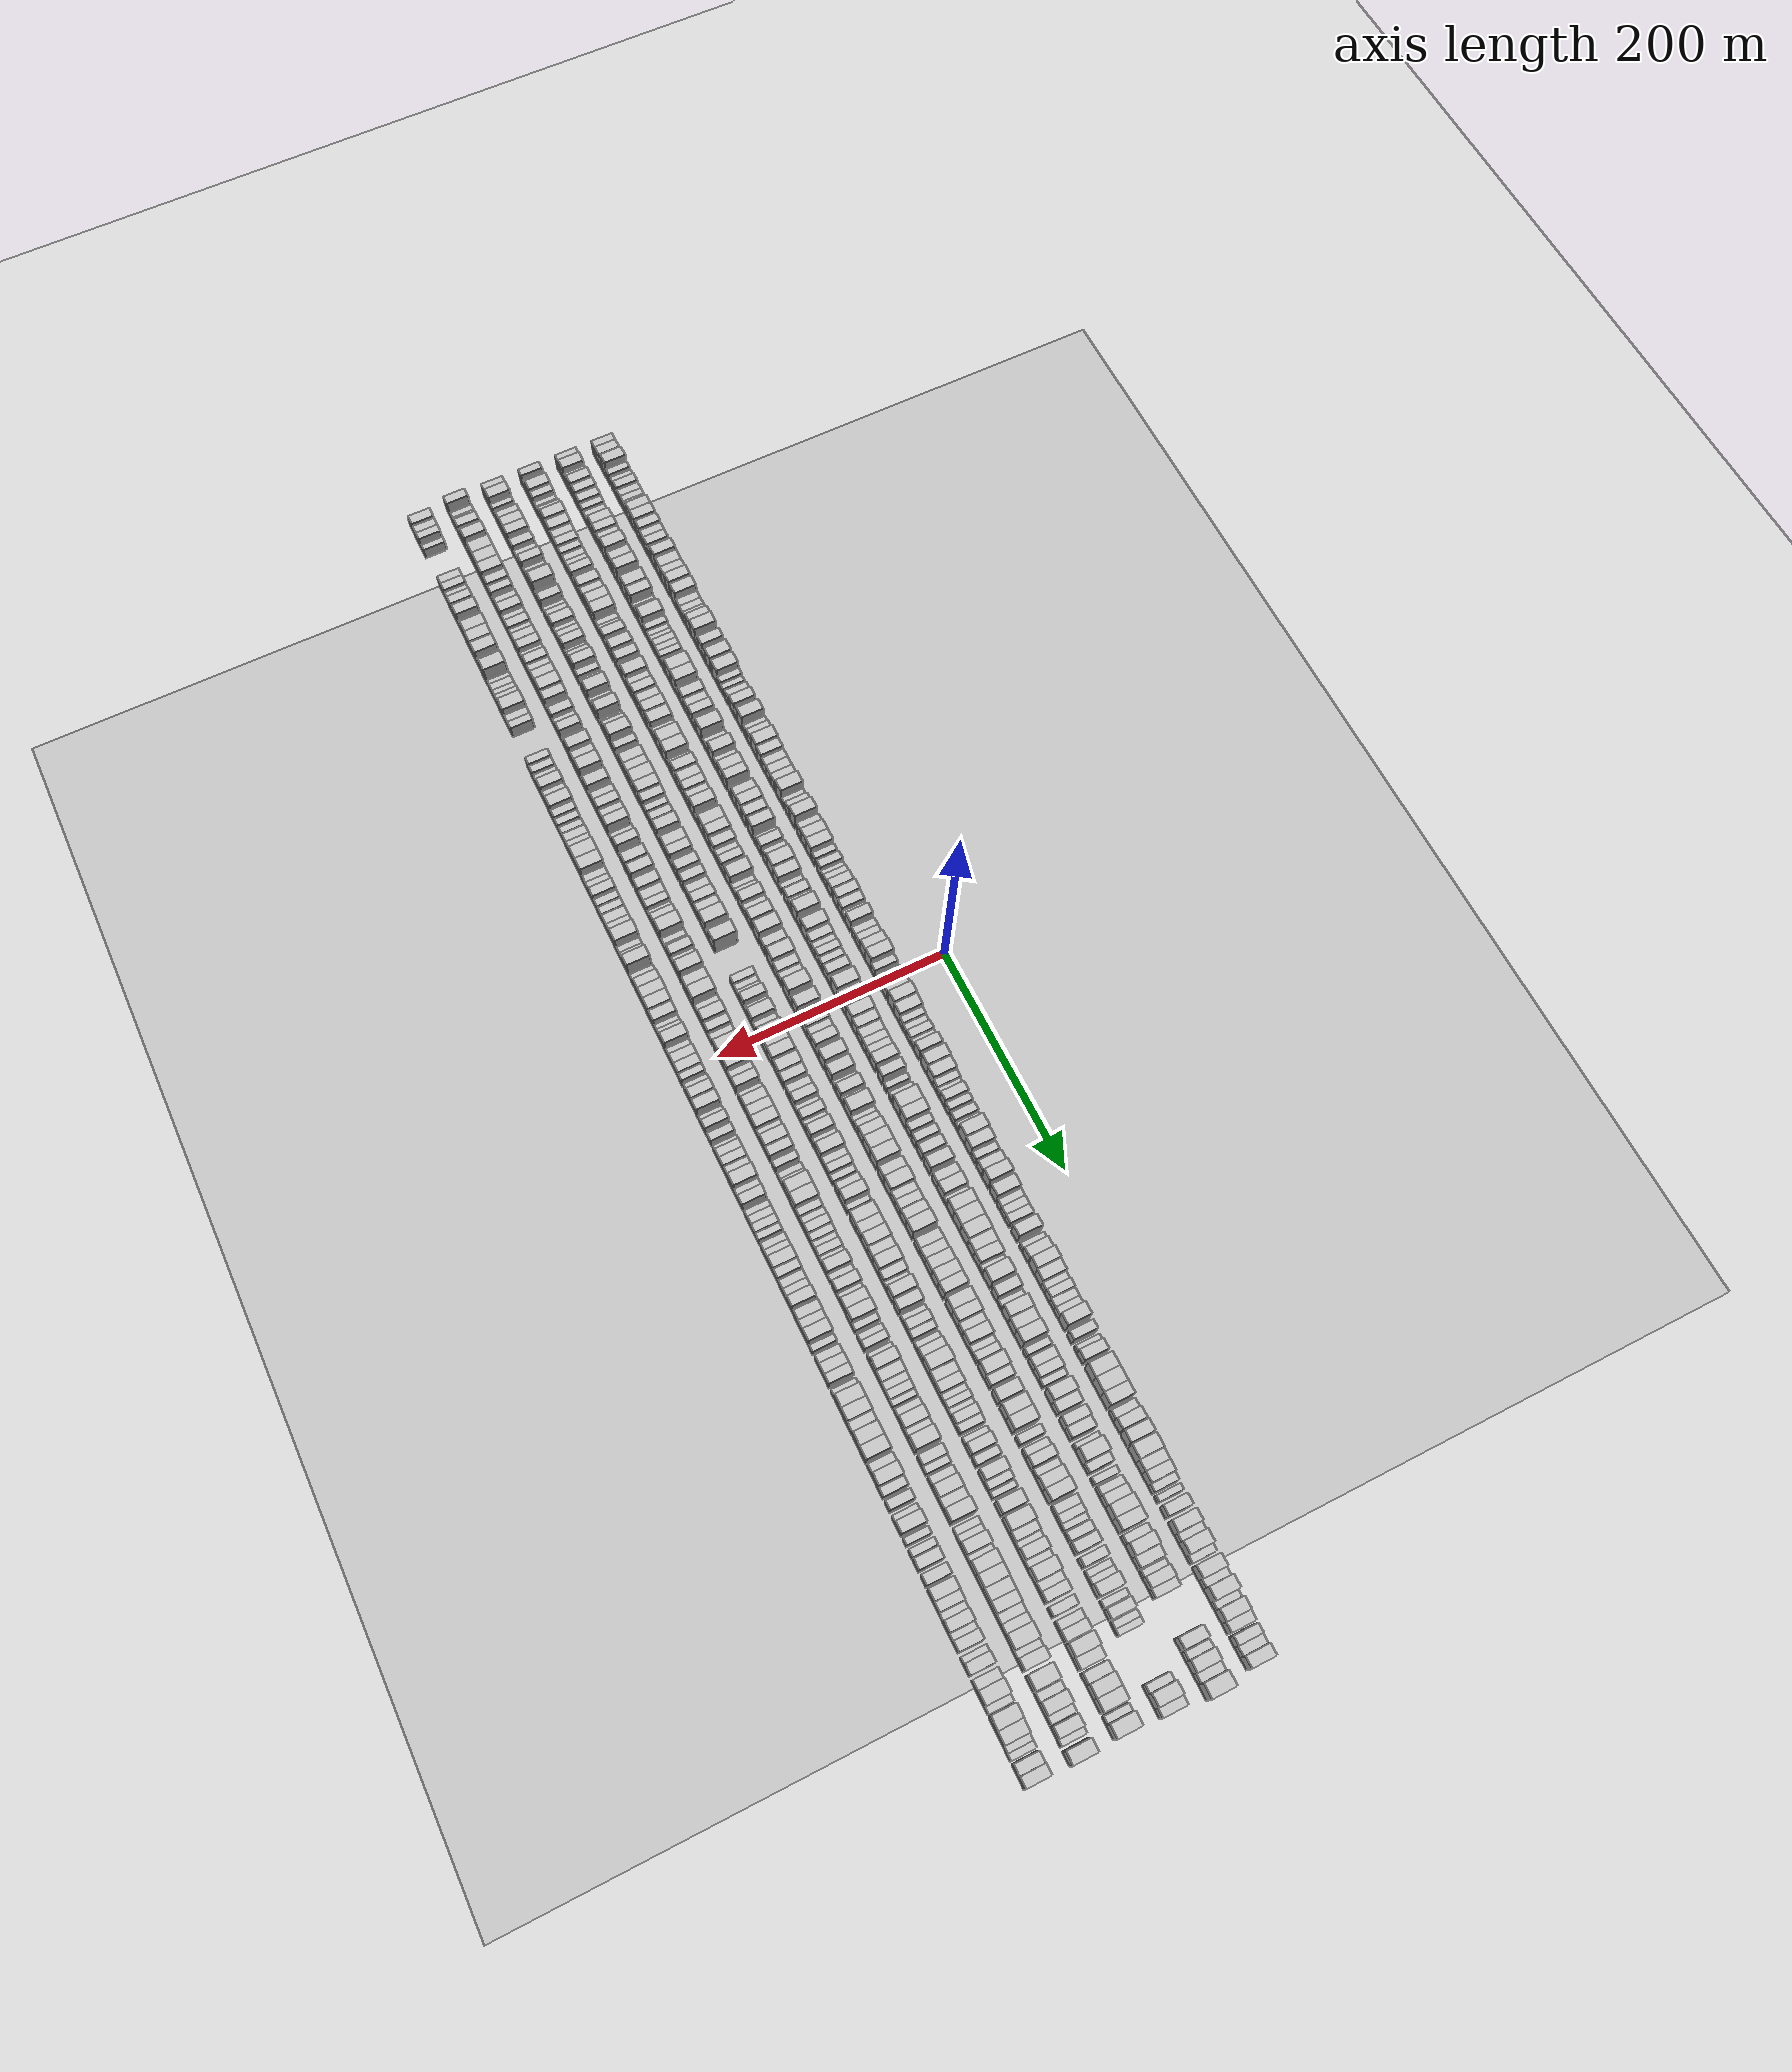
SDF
<?xml version="1.0" encoding="utf-8"?>

<sdf version="1.6">

   <world name="default">

      <gui fullscreen="0">

         <camera name="user_camera">

            <pose>-15 0 4.57585 0 0 0</pose>

            <view_controller>orbit</view_controller>

         </camera>

      </gui>

      <scene>

         <sky>

           <clouds>

             <speed>12</speed>

           </clouds>

         </sky>

         <ambient>0.4 0.4 0.4 1</ambient>

         <background>0.7 0.7 0.7 1</background>

         <shadows>1</shadows>

      </scene>

      <gravity>0 0 -9.8066</gravity>

      <magnetic_field>6e-06 2.3e-05 -4.2e-05</magnetic_field>

      <physics default="0" name="default_physics" type="ode">

         <ode>

            <solver>

               <type>quick</type>

               <iters>10</iters>

               <sor>1.0</sor>

               <use_dynamic_moi_rescaling>0</use_dynamic_moi_rescaling>

            </solver>

            <constraints>

               <cfm>0</cfm>

               <erp>0.2</erp>

               <contact_max_correcting_vel>100</contact_max_correcting_vel>

               <contact_surface_layer>0.001</contact_surface_layer>

            </constraints>

         </ode>

         <max_step_size>0.004</max_step_size>

         <real_time_factor>1</real_time_factor>

         <real_time_update_rate>250</real_time_update_rate>

      </physics>

      <light name="sun" type="directional">

         <cast_shadows>1</cast_shadows>

         <pose>0 0 10 0 0 0</pose>

         <diffuse>0.8 0.8 0.8 1</diffuse>

         <specular>0.2 0.2 0.2 1</specular>

         <attenuation>

            <range>1000</range>

            <constant>0.9</constant>

            <linear>0.01</linear>

            <quadratic>0.001</quadratic>

         </attenuation>

         <direction>-0.5 0.1 -0.9</direction>

      </light>

      <include>

         <name>ground_plane_1</name>

         <uri>model://HANNAS_ground_plane</uri>

         <pose>0 0 0  0 0 0</pose>

      </include>

      <include>

         <name>ground_plane_2</name>

         <uri>model://HANNAS_ground_plane</uri>

         <pose>100 0 0  0 0 0</pose>

      </include>

      <model name="building_1">

         <static>1</static>

         <pose frame="">50.0000 -566.3464 0 0.000000 0.000000 0.000000</pose>

         <link name="link">

            <pose frame="">0 0 9.00 0 0 0</pose>

            <collision name="collision">

               <geometry>

                  <box>

                     <size>20.0000 7.3073 18.0000</size>

                  </box>

               </geometry>

               <max_contacts>10</max_contacts>

               <surface>

                  <contact>

                     <ode/>

                  </contact>

                  <bounce/>

                  <friction>

                     <torsional>

                        <ode/>

                     </torsional>

                     <ode/>

                  </friction>

               </surface>

            </collision>

            <visual name="visual">

               <cast_shadows>0</cast_shadows>

               <geometry>

                  <box>

                     <size>20.0000 7.3073 18.0000</size>

                  </box>

               </geometry>

               <material>

                  <script>

                     <uri>model://HANNAS_wall/materials/scripts</uri>

                     <uri>model://HANNAS_wall/materials/textures</uri>

                     <name>vrc/HANNAS_wall</name>

                  </script>

               </material>

            </visual>

            <self_collide>0</self_collide>

            <enable_wind>0</enable_wind>

            <kinematic>0</kinematic>

         </link>

      </model>

      <model name="building_2">

         <static>1</static>

         <pose frame="">50.0000 -558.2330 0 0.000000 0.000000 0.000000</pose>

         <link name="link">

            <pose frame="">0 0 9.00 0 0 0</pose>

            <collision name="collision">

               <geometry>

                  <box>

                     <size>20.0000 8.9195 18.0000</size>

                  </box>

               </geometry>

               <max_contacts>10</max_contacts>

               <surface>

                  <contact>

                     <ode/>

                  </contact>

                  <bounce/>

                  <friction>

                     <torsional>

                        <ode/>

                     </torsional>

                     <ode/>

                  </friction>

               </surface>

            </collision>

            <visual name="visual">

               <cast_shadows>0</cast_shadows>

               <geometry>

                  <box>

                     <size>20.0000 8.9195 18.0000</size>

                  </box>

               </geometry>

               <material>

                  <script>

                     <uri>model://HANNAS_wall/materials/scripts</uri>

                     <uri>model://HANNAS_wall/materials/textures</uri>

                     <name>vrc/HANNAS_wall</name>

                  </script>

               </material>

            </visual>

            <self_collide>0</self_collide>

            <enable_wind>0</enable_wind>

            <kinematic>0</kinematic>

         </link>

      </model>

      <model name="building_3">

         <static>1</static>

         <pose frame="">50.0000 -551.3060 0 0.000000 0.000000 0.000000</pose>

         <link name="link">

            <pose frame="">0 0 6.00 0 0 0</pose>

            <collision name="collision">

               <geometry>

                  <box>

                     <size>20.0000 4.9344 12.0000</size>

                  </box>

               </geometry>

               <max_contacts>10</max_contacts>

               <surface>

                  <contact>

                     <ode/>

                  </contact>

                  <bounce/>

                  <friction>

                     <torsional>

                        <ode/>

                     </torsional>

                     <ode/>

                  </friction>

               </surface>

            </collision>

            <visual name="visual">

               <cast_shadows>0</cast_shadows>

               <geometry>

                  <box>

                     <size>20.0000 4.9344 12.0000</size>

                  </box>

               </geometry>

               <material>

                  <script>

                     <uri>model://HANNAS_wall/materials/scripts</uri>

                     <uri>model://HANNAS_wall/materials/textures</uri>

                     <name>vrc/HANNAS_wall</name>

                  </script>

               </material>

            </visual>

            <self_collide>0</self_collide>

            <enable_wind>0</enable_wind>

            <kinematic>0</kinematic>

         </link>

      </model>

      <model name="building_4">

         <static>1</static>

         <pose frame="">50.0000 -543.7752 0 0.000000 0.000000 0.000000</pose>

         <link name="link">

            <pose frame="">0 0 12.00 0 0 0</pose>

            <collision name="collision">

               <geometry>

                  <box>

                     <size>20.0000 10.1272 24.0000</size>

                  </box>

               </geometry>

               <max_contacts>10</max_contacts>

               <surface>

                  <contact>

                     <ode/>

                  </contact>

                  <bounce/>

                  <friction>

                     <torsional>

                        <ode/>

                     </torsional>

                     <ode/>

                  </friction>

               </surface>

            </collision>

            <visual name="visual">

               <cast_shadows>0</cast_shadows>

               <geometry>

                  <box>

                     <size>20.0000 10.1272 24.0000</size>

                  </box>

               </geometry>

               <material>

                  <script>

                     <uri>model://HANNAS_wall/materials/scripts</uri>

                     <uri>model://HANNAS_wall/materials/textures</uri>

                     <name>vrc/HANNAS_wall</name>

                  </script>

               </material>

            </visual>

            <self_collide>0</self_collide>

            <enable_wind>0</enable_wind>

            <kinematic>0</kinematic>

         </link>

      </model>

      <model name="building_5">

         <static>1</static>

         <pose frame="">50.0000 -535.4070 0 0.000000 0.000000 0.000000</pose>

         <link name="link">

            <pose frame="">0 0 7.50 0 0 0</pose>

            <collision name="collision">

               <geometry>

                  <box>

                     <size>20.0000 6.6092 15.0000</size>

                  </box>

               </geometry>

               <max_contacts>10</max_contacts>

               <surface>

                  <contact>

                     <ode/>

                  </contact>

                  <bounce/>

                  <friction>

                     <torsional>

                        <ode/>

                     </torsional>

                     <ode/>

                  </friction>

               </surface>

            </collision>

            <visual name="visual">

               <cast_shadows>0</cast_shadows>

               <geometry>

                  <box>

                     <size>20.0000 6.6092 15.0000</size>

                  </box>

               </geometry>

               <material>

                  <script>

                     <uri>model://HANNAS_wall/materials/scripts</uri>

                     <uri>model://HANNAS_wall/materials/textures</uri>

                     <name>vrc/HANNAS_wall</name>

                  </script>

               </material>

            </visual>

            <self_collide>0</self_collide>

            <enable_wind>0</enable_wind>

            <kinematic>0</kinematic>

         </link>

      </model>

      <model name="building_6">

         <static>1</static>

         <pose frame="">50.0000 -525.6789 0 0.000000 0.000000 0.000000</pose>

         <link name="link">

            <pose frame="">0 0 7.50 0 0 0</pose>

            <collision name="collision">

               <geometry>

                  <box>

                     <size>20.0000 6.8469 15.0000</size>

                  </box>

               </geometry>

               <max_contacts>10</max_contacts>

               <surface>

                  <contact>

                     <ode/>

                  </contact>

                  <bounce/>

                  <friction>

                     <torsional>

                        <ode/>

                     </torsional>

                     <ode/>

                  </friction>

               </surface>

            </collision>

            <visual name="visual">

               <cast_shadows>0</cast_shadows>

               <geometry>

                  <box>

                     <size>20.0000 6.8469 15.0000</size>

                  </box>

               </geometry>

               <material>

                  <script>

                     <uri>model://HANNAS_wall/materials/scripts</uri>

                     <uri>model://HANNAS_wall/materials/textures</uri>

                     <name>vrc/HANNAS_wall</name>

                  </script>

               </material>

            </visual>

            <self_collide>0</self_collide>

            <enable_wind>0</enable_wind>

            <kinematic>0</kinematic>

         </link>

      </model>

      <model name="building_7">

         <static>1</static>

         <pose frame="">50.0000 -518.2476 0 0.000000 0.000000 0.000000</pose>

         <link name="link">

            <pose frame="">0 0 9.00 0 0 0</pose>

            <collision name="collision">

               <geometry>

                  <box>

                     <size>20.0000 8.0158 18.0000</size>

                  </box>

               </geometry>

               <max_contacts>10</max_contacts>

               <surface>

                  <contact>

                     <ode/>

                  </contact>

                  <bounce/>

                  <friction>

                     <torsional>

                        <ode/>

                     </torsional>

                     <ode/>

                  </friction>

               </surface>

            </collision>

            <visual name="visual">

               <cast_shadows>0</cast_shadows>

               <geometry>

                  <box>

                     <size>20.0000 8.0158 18.0000</size>

                  </box>

               </geometry>

               <material>

                  <script>

                     <uri>model://HANNAS_wall/materials/scripts</uri>

                     <uri>model://HANNAS_wall/materials/textures</uri>

                     <name>vrc/HANNAS_wall</name>

                  </script>

               </material>

            </visual>

            <self_collide>0</self_collide>

            <enable_wind>0</enable_wind>

            <kinematic>0</kinematic>

         </link>

      </model>

      <model name="building_8">

         <static>1</static>

         <pose frame="">50.0000 -510.7067 0 0.000000 0.000000 0.000000</pose>

         <link name="link">

            <pose frame="">0 0 7.50 0 0 0</pose>

            <collision name="collision">

               <geometry>

                  <box>

                     <size>20.0000 7.0660 15.0000</size>

                  </box>

               </geometry>

               <max_contacts>10</max_contacts>

               <surface>

                  <contact>

                     <ode/>

                  </contact>

                  <bounce/>

                  <friction>

                     <torsional>

                        <ode/>

                     </torsional>

                     <ode/>

                  </friction>

               </surface>

            </collision>

            <visual name="visual">

               <cast_shadows>0</cast_shadows>

               <geometry>

                  <box>

                     <size>20.0000 7.0660 15.0000</size>

                  </box>

               </geometry>

               <material>

                  <script>

                     <uri>model://HANNAS_wall/materials/scripts</uri>

                     <uri>model://HANNAS_wall/materials/textures</uri>

                     <name>vrc/HANNAS_wall</name>

                  </script>

               </material>

            </visual>

            <self_collide>0</self_collide>

            <enable_wind>0</enable_wind>

            <kinematic>0</kinematic>

         </link>

      </model>

      <model name="building_9">

         <static>1</static>

         <pose frame="">50.0000 -504.0830 0 0.000000 0.000000 0.000000</pose>

         <link name="link">

            <pose frame="">0 0 7.50 0 0 0</pose>

            <collision name="collision">

               <geometry>

                  <box>

                     <size>20.0000 6.1815 15.0000</size>

                  </box>

               </geometry>

               <max_contacts>10</max_contacts>

               <surface>

                  <contact>

                     <ode/>

                  </contact>

                  <bounce/>

                  <friction>

                     <torsional>

                        <ode/>

                     </torsional>

                     <ode/>

                  </friction>

               </surface>

            </collision>

            <visual name="visual">

               <cast_shadows>0</cast_shadows>

               <geometry>

                  <box>

                     <size>20.0000 6.1815 15.0000</size>

                  </box>

               </geometry>

               <material>

                  <script>

                     <uri>model://HANNAS_wall/materials/scripts</uri>

                     <uri>model://HANNAS_wall/materials/textures</uri>

                     <name>vrc/HANNAS_wall</name>

                  </script>

               </material>

            </visual>

            <self_collide>0</self_collide>

            <enable_wind>0</enable_wind>

            <kinematic>0</kinematic>

         </link>

      </model>

      <model name="building_10">

         <static>1</static>

         <pose frame="">50.0000 -497.8380 0 0.000000 0.000000 0.000000</pose>

         <link name="link">

            <pose frame="">0 0 7.50 0 0 0</pose>

            <collision name="collision">

               <geometry>

                  <box>

                     <size>20.0000 6.3085 15.0000</size>

                  </box>

               </geometry>

               <max_contacts>10</max_contacts>

               <surface>

                  <contact>

                     <ode/>

                  </contact>

                  <bounce/>

                  <friction>

                     <torsional>

                        <ode/>

                     </torsional>

                     <ode/>

                  </friction>

               </surface>

            </collision>

            <visual name="visual">

               <cast_shadows>0</cast_shadows>

               <geometry>

                  <box>

                     <size>20.0000 6.3085 15.0000</size>

                  </box>

               </geometry>

               <material>

                  <script>

                     <uri>model://HANNAS_wall/materials/scripts</uri>

                     <uri>model://HANNAS_wall/materials/textures</uri>

                     <name>vrc/HANNAS_wall</name>

                  </script>

               </material>

            </visual>

            <self_collide>0</self_collide>

            <enable_wind>0</enable_wind>

            <kinematic>0</kinematic>

         </link>

      </model>

      <model name="building_11">

         <static>1</static>

         <pose frame="">50.0000 -490.1755 0 0.000000 0.000000 0.000000</pose>

         <link name="link">

            <pose frame="">0 0 10.50 0 0 0</pose>

            <collision name="collision">

               <geometry>

                  <box>

                     <size>20.0000 9.0165 21.0000</size>

                  </box>

               </geometry>

               <max_contacts>10</max_contacts>

               <surface>

                  <contact>

                     <ode/>

                  </contact>

                  <bounce/>

                  <friction>

                     <torsional>

                        <ode/>

                     </torsional>

                     <ode/>

                  </friction>

               </surface>

            </collision>

            <visual name="visual">

               <cast_shadows>0</cast_shadows>

               <geometry>

                  <box>

                     <size>20.0000 9.0165 21.0000</size>

                  </box>

               </geometry>

               <material>

                  <script>

                     <uri>model://HANNAS_wall/materials/scripts</uri>

                     <uri>model://HANNAS_wall/materials/textures</uri>

                     <name>vrc/HANNAS_wall</name>

                  </script>

               </material>

            </visual>

            <self_collide>0</self_collide>

            <enable_wind>0</enable_wind>

            <kinematic>0</kinematic>

         </link>

      </model>

      <model name="building_12">

         <static>1</static>

         <pose frame="">50.0000 -480.6185 0 0.000000 0.000000 0.000000</pose>

         <link name="link">

            <pose frame="">0 0 10.50 0 0 0</pose>

            <collision name="collision">

               <geometry>

                  <box>

                     <size>20.0000 10.0975 21.0000</size>

                  </box>

               </geometry>

               <max_contacts>10</max_contacts>

               <surface>

                  <contact>

                     <ode/>

                  </contact>

                  <bounce/>

                  <friction>

                     <torsional>

                        <ode/>

                     </torsional>

                     <ode/>

                  </friction>

               </surface>

            </collision>

            <visual name="visual">

               <cast_shadows>0</cast_shadows>

               <geometry>

                  <box>

                     <size>20.0000 10.0975 21.0000</size>

                  </box>

               </geometry>

               <material>

                  <script>

                     <uri>model://HANNAS_wall/materials/scripts</uri>

                     <uri>model://HANNAS_wall/materials/textures</uri>

                     <name>vrc/HANNAS_wall</name>

                  </script>

               </material>

            </visual>

            <self_collide>0</self_collide>

            <enable_wind>0</enable_wind>

            <kinematic>0</kinematic>

         </link>

      </model>

      <model name="building_13">

         <static>1</static>

         <pose frame="">50.0000 -469.1196 0 0.000000 0.000000 0.000000</pose>

         <link name="link">

            <pose frame="">0 0 10.50 0 0 0</pose>

            <collision name="collision">

               <geometry>

                  <box>

                     <size>20.0000 8.9004 21.0000</size>

                  </box>

               </geometry>

               <max_contacts>10</max_contacts>

               <surface>

                  <contact>

                     <ode/>

                  </contact>

                  <bounce/>

                  <friction>

                     <torsional>

                        <ode/>

                     </torsional>

                     <ode/>

                  </friction>

               </surface>

            </collision>

            <visual name="visual">

               <cast_shadows>0</cast_shadows>

               <geometry>

                  <box>

                     <size>20.0000 8.9004 21.0000</size>

                  </box>

               </geometry>

               <material>

                  <script>

                     <uri>model://HANNAS_wall/materials/scripts</uri>

                     <uri>model://HANNAS_wall/materials/textures</uri>

                     <name>vrc/HANNAS_wall</name>

                  </script>

               </material>

            </visual>

            <self_collide>0</self_collide>

            <enable_wind>0</enable_wind>

            <kinematic>0</kinematic>

         </link>

      </model>

      <model name="building_14">

         <static>1</static>

         <pose frame="">50.0000 -460.9430 0 0.000000 0.000000 0.000000</pose>

         <link name="link">

            <pose frame="">0 0 9.00 0 0 0</pose>

            <collision name="collision">

               <geometry>

                  <box>

                     <size>20.0000 7.4529 18.0000</size>

                  </box>

               </geometry>

               <max_contacts>10</max_contacts>

               <surface>

                  <contact>

                     <ode/>

                  </contact>

                  <bounce/>

                  <friction>

                     <torsional>

                        <ode/>

                     </torsional>

                     <ode/>

                  </friction>

               </surface>

            </collision>

            <visual name="visual">

               <cast_shadows>0</cast_shadows>

               <geometry>

                  <box>

                     <size>20.0000 7.4529 18.0000</size>

                  </box>

               </geometry>

               <material>

                  <script>

                     <uri>model://HANNAS_wall/materials/scripts</uri>

                     <uri>model://HANNAS_wall/materials/textures</uri>

                     <name>vrc/HANNAS_wall</name>

                  </script>

               </material>

            </visual>

            <self_collide>0</self_collide>

            <enable_wind>0</enable_wind>

            <kinematic>0</kinematic>

         </link>

      </model>

      <model name="building_15">

         <static>1</static>

         <pose frame="">50.0000 -452.9711 0 0.000000 0.000000 0.000000</pose>

         <link name="link">

            <pose frame="">0 0 9.00 0 0 0</pose>

            <collision name="collision">

               <geometry>

                  <box>

                     <size>20.0000 8.4909 18.0000</size>

                  </box>

               </geometry>

               <max_contacts>10</max_contacts>

               <surface>

                  <contact>

                     <ode/>

                  </contact>

                  <bounce/>

                  <friction>

                     <torsional>

                        <ode/>

                     </torsional>

                     <ode/>

                  </friction>

               </surface>

            </collision>

            <visual name="visual">

               <cast_shadows>0</cast_shadows>

               <geometry>

                  <box>

                     <size>20.0000 8.4909 18.0000</size>

                  </box>

               </geometry>

               <material>

                  <script>

                     <uri>model://HANNAS_wall/materials/scripts</uri>

                     <uri>model://HANNAS_wall/materials/textures</uri>

                     <name>vrc/HANNAS_wall</name>

                  </script>

               </material>

            </visual>

            <self_collide>0</self_collide>

            <enable_wind>0</enable_wind>

            <kinematic>0</kinematic>

         </link>

      </model>

      <model name="building_16">

         <static>1</static>

         <pose frame="">50.0000 -445.4152 0 0.000000 0.000000 0.000000</pose>

         <link name="link">

            <pose frame="">0 0 7.50 0 0 0</pose>

            <collision name="collision">

               <geometry>

                  <box>

                     <size>20.0000 6.6210 15.0000</size>

                  </box>

               </geometry>

               <max_contacts>10</max_contacts>

               <surface>

                  <contact>

                     <ode/>

                  </contact>

                  <bounce/>

                  <friction>

                     <torsional>

                        <ode/>

                     </torsional>

                     <ode/>

                  </friction>

               </surface>

            </collision>

            <visual name="visual">

               <cast_shadows>0</cast_shadows>

               <geometry>

                  <box>

                     <size>20.0000 6.6210 15.0000</size>

                  </box>

               </geometry>

               <material>

                  <script>

                     <uri>model://HANNAS_wall/materials/scripts</uri>

                     <uri>model://HANNAS_wall/materials/textures</uri>

                     <name>vrc/HANNAS_wall</name>

                  </script>

               </material>

            </visual>

            <self_collide>0</self_collide>

            <enable_wind>0</enable_wind>

            <kinematic>0</kinematic>

         </link>

      </model>

      <model name="building_17">

         <static>1</static>

         <pose frame="">50.0000 -437.1889 0 0.000000 0.000000 0.000000</pose>

         <link name="link">

            <pose frame="">0 0 12.00 0 0 0</pose>

            <collision name="collision">

               <geometry>

                  <box>

                     <size>20.0000 9.8315 24.0000</size>

                  </box>

               </geometry>

               <max_contacts>10</max_contacts>

               <surface>

                  <contact>

                     <ode/>

                  </contact>

                  <bounce/>

                  <friction>

                     <torsional>

                        <ode/>

                     </torsional>

                     <ode/>

                  </friction>

               </surface>

            </collision>

            <visual name="visual">

               <cast_shadows>0</cast_shadows>

               <geometry>

                  <box>

                     <size>20.0000 9.8315 24.0000</size>

                  </box>

               </geometry>

               <material>

                  <script>

                     <uri>model://HANNAS_wall/materials/scripts</uri>

                     <uri>model://HANNAS_wall/materials/textures</uri>

                     <name>vrc/HANNAS_wall</name>

                  </script>

               </material>

            </visual>

            <self_collide>0</self_collide>

            <enable_wind>0</enable_wind>

            <kinematic>0</kinematic>

         </link>

      </model>

      <model name="building_18">

         <static>1</static>

         <pose frame="">50.0000 -426.1161 0 0.000000 0.000000 0.000000</pose>

         <link name="link">

            <pose frame="">0 0 10.50 0 0 0</pose>

            <collision name="collision">

               <geometry>

                  <box>

                     <size>20.0000 10.3142 21.0000</size>

                  </box>

               </geometry>

               <max_contacts>10</max_contacts>

               <surface>

                  <contact>

                     <ode/>

                  </contact>

                  <bounce/>

                  <friction>

                     <torsional>

                        <ode/>

                     </torsional>

                     <ode/>

                  </friction>

               </surface>

            </collision>

            <visual name="visual">

               <cast_shadows>0</cast_shadows>

               <geometry>

                  <box>

                     <size>20.0000 10.3142 21.0000</size>

                  </box>

               </geometry>

               <material>

                  <script>

                     <uri>model://HANNAS_wall/materials/scripts</uri>

                     <uri>model://HANNAS_wall/materials/textures</uri>

                     <name>vrc/HANNAS_wall</name>

                  </script>

               </material>

            </visual>

            <self_collide>0</self_collide>

            <enable_wind>0</enable_wind>

            <kinematic>0</kinematic>

         </link>

      </model>

      <model name="building_19">

         <static>1</static>

         <pose frame="">50.0000 -416.2049 0 0.000000 0.000000 0.000000</pose>

         <link name="link">

            <pose frame="">0 0 10.50 0 0 0</pose>

            <collision name="collision">

               <geometry>

                  <box>

                     <size>20.0000 9.5082 21.0000</size>

                  </box>

               </geometry>

               <max_contacts>10</max_contacts>

               <surface>

                  <contact>

                     <ode/>

                  </contact>

                  <bounce/>

                  <friction>

                     <torsional>

                        <ode/>

                     </torsional>

                     <ode/>

                  </friction>

               </surface>

            </collision>

            <visual name="visual">

               <cast_shadows>0</cast_shadows>

               <geometry>

                  <box>

                     <size>20.0000 9.5082 21.0000</size>

                  </box>

               </geometry>

               <material>

                  <script>

                     <uri>model://HANNAS_wall/materials/scripts</uri>

                     <uri>model://HANNAS_wall/materials/textures</uri>

                     <name>vrc/HANNAS_wall</name>

                  </script>

               </material>

            </visual>

            <self_collide>0</self_collide>

            <enable_wind>0</enable_wind>

            <kinematic>0</kinematic>

         </link>

      </model>

      <model name="building_20">

         <static>1</static>

         <pose frame="">50.0000 -406.5323 0 0.000000 0.000000 0.000000</pose>

         <link name="link">

            <pose frame="">0 0 12.00 0 0 0</pose>

            <collision name="collision">

               <geometry>

                  <box>

                     <size>20.0000 9.8371 24.0000</size>

                  </box>

               </geometry>

               <max_contacts>10</max_contacts>

               <surface>

                  <contact>

                     <ode/>

                  </contact>

                  <bounce/>

                  <friction>

                     <torsional>

                        <ode/>

                     </torsional>

                     <ode/>

                  </friction>

               </surface>

            </collision>

            <visual name="visual">

               <cast_shadows>0</cast_shadows>

               <geometry>

                  <box>

                     <size>20.0000 9.8371 24.0000</size>

                  </box>

               </geometry>

               <material>

                  <script>

                     <uri>model://HANNAS_wall/materials/scripts</uri>

                     <uri>model://HANNAS_wall/materials/textures</uri>

                     <name>vrc/HANNAS_wall</name>

                  </script>

               </material>

            </visual>

            <self_collide>0</self_collide>

            <enable_wind>0</enable_wind>

            <kinematic>0</kinematic>

         </link>

      </model>

      <model name="building_21">

         <static>1</static>

         <pose frame="">50.0000 -394.2754 0 0.000000 0.000000 0.000000</pose>

         <link name="link">

            <pose frame="">0 0 12.00 0 0 0</pose>

            <collision name="collision">

               <geometry>

                  <box>

                     <size>20.0000 10.6766 24.0000</size>

                  </box>

               </geometry>

               <max_contacts>10</max_contacts>

               <surface>

                  <contact>

                     <ode/>

                  </contact>

                  <bounce/>

                  <friction>

                     <torsional>

                        <ode/>

                     </torsional>

                     <ode/>

                  </friction>

               </surface>

            </collision>

            <visual name="visual">

               <cast_shadows>0</cast_shadows>

               <geometry>

                  <box>

                     <size>20.0000 10.6766 24.0000</size>

                  </box>

               </geometry>

               <material>

                  <script>

                     <uri>model://HANNAS_wall/materials/scripts</uri>

                     <uri>model://HANNAS_wall/materials/textures</uri>

                     <name>vrc/HANNAS_wall</name>

                  </script>

               </material>

            </visual>

            <self_collide>0</self_collide>

            <enable_wind>0</enable_wind>

            <kinematic>0</kinematic>

         </link>

      </model>

      <model name="building_22">

         <static>1</static>

         <pose frame="">50.0000 -385.2008 0 0.000000 0.000000 0.000000</pose>

         <link name="link">

            <pose frame="">0 0 7.50 0 0 0</pose>

            <collision name="collision">

               <geometry>

                  <box>

                     <size>20.0000 7.4728 15.0000</size>

                  </box>

               </geometry>

               <max_contacts>10</max_contacts>

               <surface>

                  <contact>

                     <ode/>

                  </contact>

                  <bounce/>

                  <friction>

                     <torsional>

                        <ode/>

                     </torsional>

                     <ode/>

                  </friction>

               </surface>

            </collision>

            <visual name="visual">

               <cast_shadows>0</cast_shadows>

               <geometry>

                  <box>

                     <size>20.0000 7.4728 15.0000</size>

                  </box>

               </geometry>

               <material>

                  <script>

                     <uri>model://HANNAS_wall/materials/scripts</uri>

                     <uri>model://HANNAS_wall/materials/textures</uri>

                     <name>vrc/HANNAS_wall</name>

                  </script>

               </material>

            </visual>

            <self_collide>0</self_collide>

            <enable_wind>0</enable_wind>

            <kinematic>0</kinematic>

         </link>

      </model>

      <model name="building_23">

         <static>1</static>

         <pose frame="">50.0000 -378.1926 0 0.000000 0.000000 0.000000</pose>

         <link name="link">

            <pose frame="">0 0 7.50 0 0 0</pose>

            <collision name="collision">

               <geometry>

                  <box>

                     <size>20.0000 6.5435 15.0000</size>

                  </box>

               </geometry>

               <max_contacts>10</max_contacts>

               <surface>

                  <contact>

                     <ode/>

                  </contact>

                  <bounce/>

                  <friction>

                     <torsional>

                        <ode/>

                     </torsional>

                     <ode/>

                  </friction>

               </surface>

            </collision>

            <visual name="visual">

               <cast_shadows>0</cast_shadows>

               <geometry>

                  <box>

                     <size>20.0000 6.5435 15.0000</size>

                  </box>

               </geometry>

               <material>

                  <script>

                     <uri>model://HANNAS_wall/materials/scripts</uri>

                     <uri>model://HANNAS_wall/materials/textures</uri>

                     <name>vrc/HANNAS_wall</name>

                  </script>

               </material>

            </visual>

            <self_collide>0</self_collide>

            <enable_wind>0</enable_wind>

            <kinematic>0</kinematic>

         </link>

      </model>

      <model name="building_24">

         <static>1</static>

         <pose frame="">50.0000 -371.6508 0 0.000000 0.000000 0.000000</pose>

         <link name="link">

            <pose frame="">0 0 7.50 0 0 0</pose>

            <collision name="collision">

               <geometry>

                  <box>

                     <size>20.0000 6.5402 15.0000</size>

                  </box>

               </geometry>

               <max_contacts>10</max_contacts>

               <surface>

                  <contact>

                     <ode/>

                  </contact>

                  <bounce/>

                  <friction>

                     <torsional>

                        <ode/>

                     </torsional>

                     <ode/>

                  </friction>

               </surface>

            </collision>

            <visual name="visual">

               <cast_shadows>0</cast_shadows>

               <geometry>

                  <box>

                     <size>20.0000 6.5402 15.0000</size>

                  </box>

               </geometry>

               <material>

                  <script>

                     <uri>model://HANNAS_wall/materials/scripts</uri>

                     <uri>model://HANNAS_wall/materials/textures</uri>

                     <name>vrc/HANNAS_wall</name>

                  </script>

               </material>

            </visual>

            <self_collide>0</self_collide>

            <enable_wind>0</enable_wind>

            <kinematic>0</kinematic>

         </link>

      </model>

      <model name="building_25">

         <static>1</static>

         <pose frame="">50.0000 -363.9392 0 0.000000 0.000000 0.000000</pose>

         <link name="link">

            <pose frame="">0 0 10.50 0 0 0</pose>

            <collision name="collision">

               <geometry>

                  <box>

                     <size>20.0000 8.8830 21.0000</size>

                  </box>

               </geometry>

               <max_contacts>10</max_contacts>

               <surface>

                  <contact>

                     <ode/>

                  </contact>

                  <bounce/>

                  <friction>

                     <torsional>

                        <ode/>

                     </torsional>

                     <ode/>

                  </friction>

               </surface>

            </collision>

            <visual name="visual">

               <cast_shadows>0</cast_shadows>

               <geometry>

                  <box>

                     <size>20.0000 8.8830 21.0000</size>

                  </box>

               </geometry>

               <material>

                  <script>

                     <uri>model://HANNAS_wall/materials/scripts</uri>

                     <uri>model://HANNAS_wall/materials/textures</uri>

                     <name>vrc/HANNAS_wall</name>

                  </script>

               </material>

            </visual>

            <self_collide>0</self_collide>

            <enable_wind>0</enable_wind>

            <kinematic>0</kinematic>

         </link>

      </model>

      <model name="building_26">

         <static>1</static>

         <pose frame="">50.0000 -354.1854 0 0.000000 0.000000 0.000000</pose>

         <link name="link">

            <pose frame="">0 0 12.00 0 0 0</pose>

            <collision name="collision">

               <geometry>

                  <box>

                     <size>20.0000 10.6245 24.0000</size>

                  </box>

               </geometry>

               <max_contacts>10</max_contacts>

               <surface>

                  <contact>

                     <ode/>

                  </contact>

                  <bounce/>

                  <friction>

                     <torsional>

                        <ode/>

                     </torsional>

                     <ode/>

                  </friction>

               </surface>

            </collision>

            <visual name="visual">

               <cast_shadows>0</cast_shadows>

               <geometry>

                  <box>

                     <size>20.0000 10.6245 24.0000</size>

                  </box>

               </geometry>

               <material>

                  <script>

                     <uri>model://HANNAS_wall/materials/scripts</uri>

                     <uri>model://HANNAS_wall/materials/textures</uri>

                     <name>vrc/HANNAS_wall</name>

                  </script>

               </material>

            </visual>

            <self_collide>0</self_collide>

            <enable_wind>0</enable_wind>

            <kinematic>0</kinematic>

         </link>

      </model>

      <model name="building_27">

         <static>1</static>

         <pose frame="">50.0000 -346.3049 0 0.000000 0.000000 0.000000</pose>

         <link name="link">

            <pose frame="">0 0 6.00 0 0 0</pose>

            <collision name="collision">

               <geometry>

                  <box>

                     <size>20.0000 5.1363 12.0000</size>

                  </box>

               </geometry>

               <max_contacts>10</max_contacts>

               <surface>

                  <contact>

                     <ode/>

                  </contact>

                  <bounce/>

                  <friction>

                     <torsional>

                        <ode/>

                     </torsional>

                     <ode/>

                  </friction>

               </surface>

            </collision>

            <visual name="visual">

               <cast_shadows>0</cast_shadows>

               <geometry>

                  <box>

                     <size>20.0000 5.1363 12.0000</size>

                  </box>

               </geometry>

               <material>

                  <script>

                     <uri>model://HANNAS_wall/materials/scripts</uri>

                     <uri>model://HANNAS_wall/materials/textures</uri>

                     <name>vrc/HANNAS_wall</name>

                  </script>

               </material>

            </visual>

            <self_collide>0</self_collide>

            <enable_wind>0</enable_wind>

            <kinematic>0</kinematic>

         </link>

      </model>

      <model name="building_28">

         <static>1</static>

         <pose frame="">50.0000 -339.2706 0 0.000000 0.000000 0.000000</pose>

         <link name="link">

            <pose frame="">0 0 10.50 0 0 0</pose>

            <collision name="collision">

               <geometry>

                  <box>

                     <size>20.0000 8.9324 21.0000</size>

                  </box>

               </geometry>

               <max_contacts>10</max_contacts>

               <surface>

                  <contact>

                     <ode/>

                  </contact>

                  <bounce/>

                  <friction>

                     <torsional>

                        <ode/>

                     </torsional>

                     <ode/>

                  </friction>

               </surface>

            </collision>

            <visual name="visual">

               <cast_shadows>0</cast_shadows>

               <geometry>

                  <box>

                     <size>20.0000 8.9324 21.0000</size>

                  </box>

               </geometry>

               <material>

                  <script>

                     <uri>model://HANNAS_wall/materials/scripts</uri>

                     <uri>model://HANNAS_wall/materials/textures</uri>

                     <name>vrc/HANNAS_wall</name>

                  </script>

               </material>

            </visual>

            <self_collide>0</self_collide>

            <enable_wind>0</enable_wind>

            <kinematic>0</kinematic>

         </link>

      </model>

      <model name="building_29">

         <static>1</static>

         <pose frame="">50.0000 -331.8563 0 0.000000 0.000000 0.000000</pose>

         <link name="link">

            <pose frame="">0 0 6.00 0 0 0</pose>

            <collision name="collision">

               <geometry>

                  <box>

                     <size>20.0000 5.8960 12.0000</size>

                  </box>

               </geometry>

               <max_contacts>10</max_contacts>

               <surface>

                  <contact>

                     <ode/>

                  </contact>

                  <bounce/>

                  <friction>

                     <torsional>

                        <ode/>

                     </torsional>

                     <ode/>

                  </friction>

               </surface>

            </collision>

            <visual name="visual">

               <cast_shadows>0</cast_shadows>

               <geometry>

                  <box>

                     <size>20.0000 5.8960 12.0000</size>

                  </box>

               </geometry>

               <material>

                  <script>

                     <uri>model://HANNAS_wall/materials/scripts</uri>

                     <uri>model://HANNAS_wall/materials/textures</uri>

                     <name>vrc/HANNAS_wall</name>

                  </script>

               </material>

            </visual>

            <self_collide>0</self_collide>

            <enable_wind>0</enable_wind>

            <kinematic>0</kinematic>

         </link>

      </model>

      <model name="building_30">

         <static>1</static>

         <pose frame="">50.0000 -323.3774 0 0.000000 0.000000 0.000000</pose>

         <link name="link">

            <pose frame="">0 0 12.00 0 0 0</pose>

            <collision name="collision">

               <geometry>

                  <box>

                     <size>20.0000 11.0619 24.0000</size>

                  </box>

               </geometry>

               <max_contacts>10</max_contacts>

               <surface>

                  <contact>

                     <ode/>

                  </contact>

                  <bounce/>

                  <friction>

                     <torsional>

                        <ode/>

                     </torsional>

                     <ode/>

                  </friction>

               </surface>

            </collision>

            <visual name="visual">

               <cast_shadows>0</cast_shadows>

               <geometry>

                  <box>

                     <size>20.0000 11.0619 24.0000</size>

                  </box>

               </geometry>

               <material>

                  <script>

                     <uri>model://HANNAS_wall/materials/scripts</uri>

                     <uri>model://HANNAS_wall/materials/textures</uri>

                     <name>vrc/HANNAS_wall</name>

                  </script>

               </material>

            </visual>

            <self_collide>0</self_collide>

            <enable_wind>0</enable_wind>

            <kinematic>0</kinematic>

         </link>

      </model>

      <model name="building_31">

         <static>1</static>

         <pose frame="">50.0000 -309.9637 0 0.000000 0.000000 0.000000</pose>

         <link name="link">

            <pose frame="">0 0 12.00 0 0 0</pose>

            <collision name="collision">

               <geometry>

                  <box>

                     <size>20.0000 11.7655 24.0000</size>

                  </box>

               </geometry>

               <max_contacts>10</max_contacts>

               <surface>

                  <contact>

                     <ode/>

                  </contact>

                  <bounce/>

                  <friction>

                     <torsional>

                        <ode/>

                     </torsional>

                     <ode/>

                  </friction>

               </surface>

            </collision>

            <visual name="visual">

               <cast_shadows>0</cast_shadows>

               <geometry>

                  <box>

                     <size>20.0000 11.7655 24.0000</size>

                  </box>

               </geometry>

               <material>

                  <script>

                     <uri>model://HANNAS_wall/materials/scripts</uri>

                     <uri>model://HANNAS_wall/materials/textures</uri>

                     <name>vrc/HANNAS_wall</name>

                  </script>

               </material>

            </visual>

            <self_collide>0</self_collide>

            <enable_wind>0</enable_wind>

            <kinematic>0</kinematic>

         </link>

      </model>

      <model name="building_32">

         <static>1</static>

         <pose frame="">50.0000 -300.8598 0 0.000000 0.000000 0.000000</pose>

         <link name="link">

            <pose frame="">0 0 7.50 0 0 0</pose>

            <collision name="collision">

               <geometry>

                  <box>

                     <size>20.0000 6.4424 15.0000</size>

                  </box>

               </geometry>

               <max_contacts>10</max_contacts>

               <surface>

                  <contact>

                     <ode/>

                  </contact>

                  <bounce/>

                  <friction>

                     <torsional>

                        <ode/>

                     </torsional>

                     <ode/>

                  </friction>

               </surface>

            </collision>

            <visual name="visual">

               <cast_shadows>0</cast_shadows>

               <geometry>

                  <box>

                     <size>20.0000 6.4424 15.0000</size>

                  </box>

               </geometry>

               <material>

                  <script>

                     <uri>model://HANNAS_wall/materials/scripts</uri>

                     <uri>model://HANNAS_wall/materials/textures</uri>

                     <name>vrc/HANNAS_wall</name>

                  </script>

               </material>

            </visual>

            <self_collide>0</self_collide>

            <enable_wind>0</enable_wind>

            <kinematic>0</kinematic>

         </link>

      </model>

      <model name="building_33">

         <static>1</static>

         <pose frame="">50.0000 -294.9882 0 0.000000 0.000000 0.000000</pose>

         <link name="link">

            <pose frame="">0 0 6.00 0 0 0</pose>

            <collision name="collision">

               <geometry>

                  <box>

                     <size>20.0000 5.3007 12.0000</size>

                  </box>

               </geometry>

               <max_contacts>10</max_contacts>

               <surface>

                  <contact>

                     <ode/>

                  </contact>

                  <bounce/>

                  <friction>

                     <torsional>

                        <ode/>

                     </torsional>

                     <ode/>

                  </friction>

               </surface>

            </collision>

            <visual name="visual">

               <cast_shadows>0</cast_shadows>

               <geometry>

                  <box>

                     <size>20.0000 5.3007 12.0000</size>

                  </box>

               </geometry>

               <material>

                  <script>

                     <uri>model://HANNAS_wall/materials/scripts</uri>

                     <uri>model://HANNAS_wall/materials/textures</uri>

                     <name>vrc/HANNAS_wall</name>

                  </script>

               </material>

            </visual>

            <self_collide>0</self_collide>

            <enable_wind>0</enable_wind>

            <kinematic>0</kinematic>

         </link>

      </model>

      <model name="building_34">

         <static>1</static>

         <pose frame="">50.0000 -285.6008 0 0.000000 0.000000 0.000000</pose>

         <link name="link">

            <pose frame="">0 0 7.50 0 0 0</pose>

            <collision name="collision">

               <geometry>

                  <box>

                     <size>20.0000 7.4743 15.0000</size>

                  </box>

               </geometry>

               <max_contacts>10</max_contacts>

               <surface>

                  <contact>

                     <ode/>

                  </contact>

                  <bounce/>

                  <friction>

                     <torsional>

                        <ode/>

                     </torsional>

                     <ode/>

                  </friction>

               </surface>

            </collision>

            <visual name="visual">

               <cast_shadows>0</cast_shadows>

               <geometry>

                  <box>

                     <size>20.0000 7.4743 15.0000</size>

                  </box>

               </geometry>

               <material>

                  <script>

                     <uri>model://HANNAS_wall/materials/scripts</uri>

                     <uri>model://HANNAS_wall/materials/textures</uri>

                     <name>vrc/HANNAS_wall</name>

                  </script>

               </material>

            </visual>

            <self_collide>0</self_collide>

            <enable_wind>0</enable_wind>

            <kinematic>0</kinematic>

         </link>

      </model>

      <model name="building_35">

         <static>1</static>

         <pose frame="">50.0000 -275.3155 0 0.000000 0.000000 0.000000</pose>

         <link name="link">

            <pose frame="">0 0 10.50 0 0 0</pose>

            <collision name="collision">

               <geometry>

                  <box>

                     <size>20.0000 9.0963 21.0000</size>

                  </box>

               </geometry>

               <max_contacts>10</max_contacts>

               <surface>

                  <contact>

                     <ode/>

                  </contact>

                  <bounce/>

                  <friction>

                     <torsional>

                        <ode/>

                     </torsional>

                     <ode/>

                  </friction>

               </surface>

            </collision>

            <visual name="visual">

               <cast_shadows>0</cast_shadows>

               <geometry>

                  <box>

                     <size>20.0000 9.0963 21.0000</size>

                  </box>

               </geometry>

               <material>

                  <script>

                     <uri>model://HANNAS_wall/materials/scripts</uri>

                     <uri>model://HANNAS_wall/materials/textures</uri>

                     <name>vrc/HANNAS_wall</name>

                  </script>

               </material>

            </visual>

            <self_collide>0</self_collide>

            <enable_wind>0</enable_wind>

            <kinematic>0</kinematic>

         </link>

      </model>

      <model name="building_36">

         <static>1</static>

         <pose frame="">50.0000 -267.9105 0 0.000000 0.000000 0.000000</pose>

         <link name="link">

            <pose frame="">0 0 6.00 0 0 0</pose>

            <collision name="collision">

               <geometry>

                  <box>

                     <size>20.0000 5.7137 12.0000</size>

                  </box>

               </geometry>

               <max_contacts>10</max_contacts>

               <surface>

                  <contact>

                     <ode/>

                  </contact>

                  <bounce/>

                  <friction>

                     <torsional>

                        <ode/>

                     </torsional>

                     <ode/>

                  </friction>

               </surface>

            </collision>

            <visual name="visual">

               <cast_shadows>0</cast_shadows>

               <geometry>

                  <box>

                     <size>20.0000 5.7137 12.0000</size>

                  </box>

               </geometry>

               <material>

                  <script>

                     <uri>model://HANNAS_wall/materials/scripts</uri>

                     <uri>model://HANNAS_wall/materials/textures</uri>

                     <name>vrc/HANNAS_wall</name>

                  </script>

               </material>

            </visual>

            <self_collide>0</self_collide>

            <enable_wind>0</enable_wind>

            <kinematic>0</kinematic>

         </link>

      </model>

      <model name="building_37">

         <static>1</static>

         <pose frame="">50.0000 -259.7142 0 0.000000 0.000000 0.000000</pose>

         <link name="link">

            <pose frame="">0 0 12.00 0 0 0</pose>

            <collision name="collision">

               <geometry>

                  <box>

                     <size>20.0000 10.6789 24.0000</size>

                  </box>

               </geometry>

               <max_contacts>10</max_contacts>

               <surface>

                  <contact>

                     <ode/>

                  </contact>

                  <bounce/>

                  <friction>

                     <torsional>

                        <ode/>

                     </torsional>

                     <ode/>

                  </friction>

               </surface>

            </collision>

            <visual name="visual">

               <cast_shadows>0</cast_shadows>

               <geometry>

                  <box>

                     <size>20.0000 10.6789 24.0000</size>

                  </box>

               </geometry>

               <material>

                  <script>

                     <uri>model://HANNAS_wall/materials/scripts</uri>

                     <uri>model://HANNAS_wall/materials/textures</uri>

                     <name>vrc/HANNAS_wall</name>

                  </script>

               </material>

            </visual>

            <self_collide>0</self_collide>

            <enable_wind>0</enable_wind>

            <kinematic>0</kinematic>

         </link>

      </model>

      <model name="building_38">

         <static>1</static>

         <pose frame="">50.0000 -249.2836 0 0.000000 0.000000 0.000000</pose>

         <link name="link">

            <pose frame="">0 0 7.50 0 0 0</pose>

            <collision name="collision">

               <geometry>

                  <box>

                     <size>20.0000 6.1822 15.0000</size>

                  </box>

               </geometry>

               <max_contacts>10</max_contacts>

               <surface>

                  <contact>

                     <ode/>

                  </contact>

                  <bounce/>

                  <friction>

                     <torsional>

                        <ode/>

                     </torsional>

                     <ode/>

                  </friction>

               </surface>

            </collision>

            <visual name="visual">

               <cast_shadows>0</cast_shadows>

               <geometry>

                  <box>

                     <size>20.0000 6.1822 15.0000</size>

                  </box>

               </geometry>

               <material>

                  <script>

                     <uri>model://HANNAS_wall/materials/scripts</uri>

                     <uri>model://HANNAS_wall/materials/textures</uri>

                     <name>vrc/HANNAS_wall</name>

                  </script>

               </material>

            </visual>

            <self_collide>0</self_collide>

            <enable_wind>0</enable_wind>

            <kinematic>0</kinematic>

         </link>

      </model>

      <model name="building_39">

         <static>1</static>

         <pose frame="">50.0000 -241.7494 0 0.000000 0.000000 0.000000</pose>

         <link name="link">

            <pose frame="">0 0 9.00 0 0 0</pose>

            <collision name="collision">

               <geometry>

                  <box>

                     <size>20.0000 8.8862 18.0000</size>

                  </box>

               </geometry>

               <max_contacts>10</max_contacts>

               <surface>

                  <contact>

                     <ode/>

                  </contact>

                  <bounce/>

                  <friction>

                     <torsional>

                        <ode/>

                     </torsional>

                     <ode/>

                  </friction>

               </surface>

            </collision>

            <visual name="visual">

               <cast_shadows>0</cast_shadows>

               <geometry>

                  <box>

                     <size>20.0000 8.8862 18.0000</size>

                  </box>

               </geometry>

               <material>

                  <script>

                     <uri>model://HANNAS_wall/materials/scripts</uri>

                     <uri>model://HANNAS_wall/materials/textures</uri>

                     <name>vrc/HANNAS_wall</name>

                  </script>

               </material>

            </visual>

            <self_collide>0</self_collide>

            <enable_wind>0</enable_wind>

            <kinematic>0</kinematic>

         </link>

      </model>

      <model name="building_40">

         <static>1</static>

         <pose frame="">50.0000 -231.7605 0 0.000000 0.000000 0.000000</pose>

         <link name="link">

            <pose frame="">0 0 12.00 0 0 0</pose>

            <collision name="collision">

               <geometry>

                  <box>

                     <size>20.0000 11.0917 24.0000</size>

                  </box>

               </geometry>

               <max_contacts>10</max_contacts>

               <surface>

                  <contact>

                     <ode/>

                  </contact>

                  <bounce/>

                  <friction>

                     <torsional>

                        <ode/>

                     </torsional>

                     <ode/>

                  </friction>

               </surface>

            </collision>

            <visual name="visual">

               <cast_shadows>0</cast_shadows>

               <geometry>

                  <box>

                     <size>20.0000 11.0917 24.0000</size>

                  </box>

               </geometry>

               <material>

                  <script>

                     <uri>model://HANNAS_wall/materials/scripts</uri>

                     <uri>model://HANNAS_wall/materials/textures</uri>

                     <name>vrc/HANNAS_wall</name>

                  </script>

               </material>

            </visual>

            <self_collide>0</self_collide>

            <enable_wind>0</enable_wind>

            <kinematic>0</kinematic>

         </link>

      </model>

      <model name="building_41">

         <static>1</static>

         <pose frame="">50.0000 -221.6519 0 0.000000 0.000000 0.000000</pose>

         <link name="link">

            <pose frame="">0 0 10.50 0 0 0</pose>

            <collision name="collision">

               <geometry>

                  <box>

                     <size>20.0000 9.1254 21.0000</size>

                  </box>

               </geometry>

               <max_contacts>10</max_contacts>

               <surface>

                  <contact>

                     <ode/>

                  </contact>

                  <bounce/>

                  <friction>

                     <torsional>

                        <ode/>

                     </torsional>

                     <ode/>

                  </friction>

               </surface>

            </collision>

            <visual name="visual">

               <cast_shadows>0</cast_shadows>

               <geometry>

                  <box>

                     <size>20.0000 9.1254 21.0000</size>

                  </box>

               </geometry>

               <material>

                  <script>

                     <uri>model://HANNAS_wall/materials/scripts</uri>

                     <uri>model://HANNAS_wall/materials/textures</uri>

                     <name>vrc/HANNAS_wall</name>

                  </script>

               </material>

            </visual>

            <self_collide>0</self_collide>

            <enable_wind>0</enable_wind>

            <kinematic>0</kinematic>

         </link>

      </model>

      <model name="building_42">

         <static>1</static>

         <pose frame="">50.0000 -212.1195 0 0.000000 0.000000 0.000000</pose>

         <link name="link">

            <pose frame="">0 0 9.00 0 0 0</pose>

            <collision name="collision">

               <geometry>

                  <box>

                     <size>20.0000 7.9395 18.0000</size>

                  </box>

               </geometry>

               <max_contacts>10</max_contacts>

               <surface>

                  <contact>

                     <ode/>

                  </contact>

                  <bounce/>

                  <friction>

                     <torsional>

                        <ode/>

                     </torsional>

                     <ode/>

                  </friction>

               </surface>

            </collision>

            <visual name="visual">

               <cast_shadows>0</cast_shadows>

               <geometry>

                  <box>

                     <size>20.0000 7.9395 18.0000</size>

                  </box>

               </geometry>

               <material>

                  <script>

                     <uri>model://HANNAS_wall/materials/scripts</uri>

                     <uri>model://HANNAS_wall/materials/textures</uri>

                     <name>vrc/HANNAS_wall</name>

                  </script>

               </material>

            </visual>

            <self_collide>0</self_collide>

            <enable_wind>0</enable_wind>

            <kinematic>0</kinematic>

         </link>

      </model>

      <model name="building_43">

         <static>1</static>

         <pose frame="">50.0000 -203.9289 0 0.000000 0.000000 0.000000</pose>

         <link name="link">

            <pose frame="">0 0 9.00 0 0 0</pose>

            <collision name="collision">

               <geometry>

                  <box>

                     <size>20.0000 8.4416 18.0000</size>

                  </box>

               </geometry>

               <max_contacts>10</max_contacts>

               <surface>

                  <contact>

                     <ode/>

                  </contact>

                  <bounce/>

                  <friction>

                     <torsional>

                        <ode/>

                     </torsional>

                     <ode/>

                  </friction>

               </surface>

            </collision>

            <visual name="visual">

               <cast_shadows>0</cast_shadows>

               <geometry>

                  <box>

                     <size>20.0000 8.4416 18.0000</size>

                  </box>

               </geometry>

               <material>

                  <script>

                     <uri>model://HANNAS_wall/materials/scripts</uri>

                     <uri>model://HANNAS_wall/materials/textures</uri>

                     <name>vrc/HANNAS_wall</name>

                  </script>

               </material>

            </visual>

            <self_collide>0</self_collide>

            <enable_wind>0</enable_wind>

            <kinematic>0</kinematic>

         </link>

      </model>

      <model name="building_44">

         <static>1</static>

         <pose frame="">50.0000 -195.6706 0 0.000000 0.000000 0.000000</pose>

         <link name="link">

            <pose frame="">0 0 9.00 0 0 0</pose>

            <collision name="collision">

               <geometry>

                  <box>

                     <size>20.0000 8.0751 18.0000</size>

                  </box>

               </geometry>

               <max_contacts>10</max_contacts>

               <surface>

                  <contact>

                     <ode/>

                  </contact>

                  <bounce/>

                  <friction>

                     <torsional>

                        <ode/>

                     </torsional>

                     <ode/>

                  </friction>

               </surface>

            </collision>

            <visual name="visual">

               <cast_shadows>0</cast_shadows>

               <geometry>

                  <box>

                     <size>20.0000 8.0751 18.0000</size>

                  </box>

               </geometry>

               <material>

                  <script>

                     <uri>model://HANNAS_wall/materials/scripts</uri>

                     <uri>model://HANNAS_wall/materials/textures</uri>

                     <name>vrc/HANNAS_wall</name>

                  </script>

               </material>

            </visual>

            <self_collide>0</self_collide>

            <enable_wind>0</enable_wind>

            <kinematic>0</kinematic>

         </link>

      </model>

      <model name="building_45">

         <static>1</static>

         <pose frame="">50.0000 -184.1058 0 0.000000 0.000000 0.000000</pose>

         <link name="link">

            <pose frame="">0 0 12.00 0 0 0</pose>

            <collision name="collision">

               <geometry>

                  <box>

                     <size>20.0000 11.0544 24.0000</size>

                  </box>

               </geometry>

               <max_contacts>10</max_contacts>

               <surface>

                  <contact>

                     <ode/>

                  </contact>

                  <bounce/>

                  <friction>

                     <torsional>

                        <ode/>

                     </torsional>

                     <ode/>

                  </friction>

               </surface>

            </collision>

            <visual name="visual">

               <cast_shadows>0</cast_shadows>

               <geometry>

                  <box>

                     <size>20.0000 11.0544 24.0000</size>

                  </box>

               </geometry>

               <material>

                  <script>

                     <uri>model://HANNAS_wall/materials/scripts</uri>

                     <uri>model://HANNAS_wall/materials/textures</uri>

                     <name>vrc/HANNAS_wall</name>

                  </script>

               </material>

            </visual>

            <self_collide>0</self_collide>

            <enable_wind>0</enable_wind>

            <kinematic>0</kinematic>

         </link>

      </model>

      <model name="building_46">

         <static>1</static>

         <pose frame="">50.0000 -175.8716 0 0.000000 0.000000 0.000000</pose>

         <link name="link">

            <pose frame="">0 0 6.00 0 0 0</pose>

            <collision name="collision">

               <geometry>

                  <box>

                     <size>20.0000 5.4140 12.0000</size>

                  </box>

               </geometry>

               <max_contacts>10</max_contacts>

               <surface>

                  <contact>

                     <ode/>

                  </contact>

                  <bounce/>

                  <friction>

                     <torsional>

                        <ode/>

                     </torsional>

                     <ode/>

                  </friction>

               </surface>

            </collision>

            <visual name="visual">

               <cast_shadows>0</cast_shadows>

               <geometry>

                  <box>

                     <size>20.0000 5.4140 12.0000</size>

                  </box>

               </geometry>

               <material>

                  <script>

                     <uri>model://HANNAS_wall/materials/scripts</uri>

                     <uri>model://HANNAS_wall/materials/textures</uri>

                     <name>vrc/HANNAS_wall</name>

                  </script>

               </material>

            </visual>

            <self_collide>0</self_collide>

            <enable_wind>0</enable_wind>

            <kinematic>0</kinematic>

         </link>

      </model>

      <model name="building_47">

         <static>1</static>

         <pose frame="">50.0000 -167.1921 0 0.000000 0.000000 0.000000</pose>

         <link name="link">

            <pose frame="">0 0 9.00 0 0 0</pose>

            <collision name="collision">

               <geometry>

                  <box>

                     <size>20.0000 7.9449 18.0000</size>

                  </box>

               </geometry>

               <max_contacts>10</max_contacts>

               <surface>

                  <contact>

                     <ode/>

                  </contact>

                  <bounce/>

                  <friction>

                     <torsional>

                        <ode/>

                     </torsional>

                     <ode/>

                  </friction>

               </surface>

            </collision>

            <visual name="visual">

               <cast_shadows>0</cast_shadows>

               <geometry>

                  <box>

                     <size>20.0000 7.9449 18.0000</size>

                  </box>

               </geometry>

               <material>

                  <script>

                     <uri>model://HANNAS_wall/materials/scripts</uri>

                     <uri>model://HANNAS_wall/materials/textures</uri>

                     <name>vrc/HANNAS_wall</name>

                  </script>

               </material>

            </visual>

            <self_collide>0</self_collide>

            <enable_wind>0</enable_wind>

            <kinematic>0</kinematic>

         </link>

      </model>

      <model name="building_48">

         <static>1</static>

         <pose frame="">50.0000 -157.9363 0 0.000000 0.000000 0.000000</pose>

         <link name="link">

            <pose frame="">0 0 12.00 0 0 0</pose>

            <collision name="collision">

               <geometry>

                  <box>

                     <size>20.0000 10.5666 24.0000</size>

                  </box>

               </geometry>

               <max_contacts>10</max_contacts>

               <surface>

                  <contact>

                     <ode/>

                  </contact>

                  <bounce/>

                  <friction>

                     <torsional>

                        <ode/>

                     </torsional>

                     <ode/>

                  </friction>

               </surface>

            </collision>

            <visual name="visual">

               <cast_shadows>0</cast_shadows>

               <geometry>

                  <box>

                     <size>20.0000 10.5666 24.0000</size>

                  </box>

               </geometry>

               <material>

                  <script>

                     <uri>model://HANNAS_wall/materials/scripts</uri>

                     <uri>model://HANNAS_wall/materials/textures</uri>

                     <name>vrc/HANNAS_wall</name>

                  </script>

               </material>

            </visual>

            <self_collide>0</self_collide>

            <enable_wind>0</enable_wind>

            <kinematic>0</kinematic>

         </link>

      </model>

      <model name="building_49">

         <static>1</static>

         <pose frame="">50.0000 -145.9046 0 0.000000 0.000000 0.000000</pose>

         <link name="link">

            <pose frame="">0 0 9.00 0 0 0</pose>

            <collision name="collision">

               <geometry>

                  <box>

                     <size>20.0000 7.4969 18.0000</size>

                  </box>

               </geometry>

               <max_contacts>10</max_contacts>

               <surface>

                  <contact>

                     <ode/>

                  </contact>

                  <bounce/>

                  <friction>

                     <torsional>

                        <ode/>

                     </torsional>

                     <ode/>

                  </friction>

               </surface>

            </collision>

            <visual name="visual">

               <cast_shadows>0</cast_shadows>

               <geometry>

                  <box>

                     <size>20.0000 7.4969 18.0000</size>

                  </box>

               </geometry>

               <material>

                  <script>

                     <uri>model://HANNAS_wall/materials/scripts</uri>

                     <uri>model://HANNAS_wall/materials/textures</uri>

                     <name>vrc/HANNAS_wall</name>

                  </script>

               </material>

            </visual>

            <self_collide>0</self_collide>

            <enable_wind>0</enable_wind>

            <kinematic>0</kinematic>

         </link>

      </model>

      <model name="building_50">

         <static>1</static>

         <pose frame="">50.0000 -137.4338 0 0.000000 0.000000 0.000000</pose>

         <link name="link">

            <pose frame="">0 0 10.50 0 0 0</pose>

            <collision name="collision">

               <geometry>

                  <box>

                     <size>20.0000 9.4446 21.0000</size>

                  </box>

               </geometry>

               <max_contacts>10</max_contacts>

               <surface>

                  <contact>

                     <ode/>

                  </contact>

                  <bounce/>

                  <friction>

                     <torsional>

                        <ode/>

                     </torsional>

                     <ode/>

                  </friction>

               </surface>

            </collision>

            <visual name="visual">

               <cast_shadows>0</cast_shadows>

               <geometry>

                  <box>

                     <size>20.0000 9.4446 21.0000</size>

                  </box>

               </geometry>

               <material>

                  <script>

                     <uri>model://HANNAS_wall/materials/scripts</uri>

                     <uri>model://HANNAS_wall/materials/textures</uri>

                     <name>vrc/HANNAS_wall</name>

                  </script>

               </material>

            </visual>

            <self_collide>0</self_collide>

            <enable_wind>0</enable_wind>

            <kinematic>0</kinematic>

         </link>

      </model>

      <model name="building_51">

         <static>1</static>

         <pose frame="">50.0000 -127.4654 0 0.000000 0.000000 0.000000</pose>

         <link name="link">

            <pose frame="">0 0 10.50 0 0 0</pose>

            <collision name="collision">

               <geometry>

                  <box>

                     <size>20.0000 10.4922 21.0000</size>

                  </box>

               </geometry>

               <max_contacts>10</max_contacts>

               <surface>

                  <contact>

                     <ode/>

                  </contact>

                  <bounce/>

                  <friction>

                     <torsional>

                        <ode/>

                     </torsional>

                     <ode/>

                  </friction>

               </surface>

            </collision>

            <visual name="visual">

               <cast_shadows>0</cast_shadows>

               <geometry>

                  <box>

                     <size>20.0000 10.4922 21.0000</size>

                  </box>

               </geometry>

               <material>

                  <script>

                     <uri>model://HANNAS_wall/materials/scripts</uri>

                     <uri>model://HANNAS_wall/materials/textures</uri>

                     <name>vrc/HANNAS_wall</name>

                  </script>

               </material>

            </visual>

            <self_collide>0</self_collide>

            <enable_wind>0</enable_wind>

            <kinematic>0</kinematic>

         </link>

      </model>

      <model name="building_52">

         <static>1</static>

         <pose frame="">50.0000 -118.1912 0 0.000000 0.000000 0.000000</pose>

         <link name="link">

            <pose frame="">0 0 7.50 0 0 0</pose>

            <collision name="collision">

               <geometry>

                  <box>

                     <size>20.0000 6.0561 15.0000</size>

                  </box>

               </geometry>

               <max_contacts>10</max_contacts>

               <surface>

                  <contact>

                     <ode/>

                  </contact>

                  <bounce/>

                  <friction>

                     <torsional>

                        <ode/>

                     </torsional>

                     <ode/>

                  </friction>

               </surface>

            </collision>

            <visual name="visual">

               <cast_shadows>0</cast_shadows>

               <geometry>

                  <box>

                     <size>20.0000 6.0561 15.0000</size>

                  </box>

               </geometry>

               <material>

                  <script>

                     <uri>model://HANNAS_wall/materials/scripts</uri>

                     <uri>model://HANNAS_wall/materials/textures</uri>

                     <name>vrc/HANNAS_wall</name>

                  </script>

               </material>

            </visual>

            <self_collide>0</self_collide>

            <enable_wind>0</enable_wind>

            <kinematic>0</kinematic>

         </link>

      </model>

      <model name="building_53">

         <static>1</static>

         <pose frame="">50.0000 -108.4824 0 0.000000 0.000000 0.000000</pose>

         <link name="link">

            <pose frame="">0 0 9.00 0 0 0</pose>

            <collision name="collision">

               <geometry>

                  <box>

                     <size>20.0000 7.3614 18.0000</size>

                  </box>

               </geometry>

               <max_contacts>10</max_contacts>

               <surface>

                  <contact>

                     <ode/>

                  </contact>

                  <bounce/>

                  <friction>

                     <torsional>

                        <ode/>

                     </torsional>

                     <ode/>

                  </friction>

               </surface>

            </collision>

            <visual name="visual">

               <cast_shadows>0</cast_shadows>

               <geometry>

                  <box>

                     <size>20.0000 7.3614 18.0000</size>

                  </box>

               </geometry>

               <material>

                  <script>

                     <uri>model://HANNAS_wall/materials/scripts</uri>

                     <uri>model://HANNAS_wall/materials/textures</uri>

                     <name>vrc/HANNAS_wall</name>

                  </script>

               </material>

            </visual>

            <self_collide>0</self_collide>

            <enable_wind>0</enable_wind>

            <kinematic>0</kinematic>

         </link>

      </model>

      <model name="building_54">

         <static>1</static>

         <pose frame="">50.0000 -102.2450 0 0.000000 0.000000 0.000000</pose>

         <link name="link">

            <pose frame="">0 0 6.00 0 0 0</pose>

            <collision name="collision">

               <geometry>

                  <box>

                     <size>20.0000 5.1135 12.0000</size>

                  </box>

               </geometry>

               <max_contacts>10</max_contacts>

               <surface>

                  <contact>

                     <ode/>

                  </contact>

                  <bounce/>

                  <friction>

                     <torsional>

                        <ode/>

                     </torsional>

                     <ode/>

                  </friction>

               </surface>

            </collision>

            <visual name="visual">

               <cast_shadows>0</cast_shadows>

               <geometry>

                  <box>

                     <size>20.0000 5.1135 12.0000</size>

                  </box>

               </geometry>

               <material>

                  <script>

                     <uri>model://HANNAS_wall/materials/scripts</uri>

                     <uri>model://HANNAS_wall/materials/textures</uri>

                     <name>vrc/HANNAS_wall</name>

                  </script>

               </material>

            </visual>

            <self_collide>0</self_collide>

            <enable_wind>0</enable_wind>

            <kinematic>0</kinematic>

         </link>

      </model>

      <model name="building_55">

         <static>1</static>

         <pose frame="">50.0000 -96.3450 0 0.000000 0.000000 0.000000</pose>

         <link name="link">

            <pose frame="">0 0 7.50 0 0 0</pose>

            <collision name="collision">

               <geometry>

                  <box>

                     <size>20.0000 6.6864 15.0000</size>

                  </box>

               </geometry>

               <max_contacts>10</max_contacts>

               <surface>

                  <contact>

                     <ode/>

                  </contact>

                  <bounce/>

                  <friction>

                     <torsional>

                        <ode/>

                     </torsional>

                     <ode/>

                  </friction>

               </surface>

            </collision>

            <visual name="visual">

               <cast_shadows>0</cast_shadows>

               <geometry>

                  <box>

                     <size>20.0000 6.6864 15.0000</size>

                  </box>

               </geometry>

               <material>

                  <script>

                     <uri>model://HANNAS_wall/materials/scripts</uri>

                     <uri>model://HANNAS_wall/materials/textures</uri>

                     <name>vrc/HANNAS_wall</name>

                  </script>

               </material>

            </visual>

            <self_collide>0</self_collide>

            <enable_wind>0</enable_wind>

            <kinematic>0</kinematic>

         </link>

      </model>

      <model name="building_56">

         <static>1</static>

         <pose frame="">50.0000 -88.7126 0 0.000000 0.000000 0.000000</pose>

         <link name="link">

            <pose frame="">0 0 9.00 0 0 0</pose>

            <collision name="collision">

               <geometry>

                  <box>

                     <size>20.0000 8.5783 18.0000</size>

                  </box>

               </geometry>

               <max_contacts>10</max_contacts>

               <surface>

                  <contact>

                     <ode/>

                  </contact>

                  <bounce/>

                  <friction>

                     <torsional>

                        <ode/>

                     </torsional>

                     <ode/>

                  </friction>

               </surface>

            </collision>

            <visual name="visual">

               <cast_shadows>0</cast_shadows>

               <geometry>

                  <box>

                     <size>20.0000 8.5783 18.0000</size>

                  </box>

               </geometry>

               <material>

                  <script>

                     <uri>model://HANNAS_wall/materials/scripts</uri>

                     <uri>model://HANNAS_wall/materials/textures</uri>

                     <name>vrc/HANNAS_wall</name>

                  </script>

               </material>

            </visual>

            <self_collide>0</self_collide>

            <enable_wind>0</enable_wind>

            <kinematic>0</kinematic>

         </link>

      </model>

      <model name="building_57">

         <static>1</static>

         <pose frame="">50.0000 -77.9405 0 0.000000 0.000000 0.000000</pose>

         <link name="link">

            <pose frame="">0 0 10.50 0 0 0</pose>

            <collision name="collision">

               <geometry>

                  <box>

                     <size>20.0000 8.9660 21.0000</size>

                  </box>

               </geometry>

               <max_contacts>10</max_contacts>

               <surface>

                  <contact>

                     <ode/>

                  </contact>

                  <bounce/>

                  <friction>

                     <torsional>

                        <ode/>

                     </torsional>

                     <ode/>

                  </friction>

               </surface>

            </collision>

            <visual name="visual">

               <cast_shadows>0</cast_shadows>

               <geometry>

                  <box>

                     <size>20.0000 8.9660 21.0000</size>

                  </box>

               </geometry>

               <material>

                  <script>

                     <uri>model://HANNAS_wall/materials/scripts</uri>

                     <uri>model://HANNAS_wall/materials/textures</uri>

                     <name>vrc/HANNAS_wall</name>

                  </script>

               </material>

            </visual>

            <self_collide>0</self_collide>

            <enable_wind>0</enable_wind>

            <kinematic>0</kinematic>

         </link>

      </model>

      <model name="building_58">

         <static>1</static>

         <pose frame="">50.0000 -69.2409 0 0.000000 0.000000 0.000000</pose>

         <link name="link">

            <pose frame="">0 0 9.00 0 0 0</pose>

            <collision name="collision">

               <geometry>

                  <box>

                     <size>20.0000 8.4332 18.0000</size>

                  </box>

               </geometry>

               <max_contacts>10</max_contacts>

               <surface>

                  <contact>

                     <ode/>

                  </contact>

                  <bounce/>

                  <friction>

                     <torsional>

                        <ode/>

                     </torsional>

                     <ode/>

                  </friction>

               </surface>

            </collision>

            <visual name="visual">

               <cast_shadows>0</cast_shadows>

               <geometry>

                  <box>

                     <size>20.0000 8.4332 18.0000</size>

                  </box>

               </geometry>

               <material>

                  <script>

                     <uri>model://HANNAS_wall/materials/scripts</uri>

                     <uri>model://HANNAS_wall/materials/textures</uri>

                     <name>vrc/HANNAS_wall</name>

                  </script>

               </material>

            </visual>

            <self_collide>0</self_collide>

            <enable_wind>0</enable_wind>

            <kinematic>0</kinematic>

         </link>

      </model>

      <model name="building_59">

         <static>1</static>

         <pose frame="">50.0000 -62.1792 0 0.000000 0.000000 0.000000</pose>

         <link name="link">

            <pose frame="">0 0 6.00 0 0 0</pose>

            <collision name="collision">

               <geometry>

                  <box>

                     <size>20.0000 5.6902 12.0000</size>

                  </box>

               </geometry>

               <max_contacts>10</max_contacts>

               <surface>

                  <contact>

                     <ode/>

                  </contact>

                  <bounce/>

                  <friction>

                     <torsional>

                        <ode/>

                     </torsional>

                     <ode/>

                  </friction>

               </surface>

            </collision>

            <visual name="visual">

               <cast_shadows>0</cast_shadows>

               <geometry>

                  <box>

                     <size>20.0000 5.6902 12.0000</size>

                  </box>

               </geometry>

               <material>

                  <script>

                     <uri>model://HANNAS_wall/materials/scripts</uri>

                     <uri>model://HANNAS_wall/materials/textures</uri>

                     <name>vrc/HANNAS_wall</name>

                  </script>

               </material>

            </visual>

            <self_collide>0</self_collide>

            <enable_wind>0</enable_wind>

            <kinematic>0</kinematic>

         </link>

      </model>

      <model name="building_60">

         <static>1</static>

         <pose frame="">50.0000 -54.6696 0 0.000000 0.000000 0.000000</pose>

         <link name="link">

            <pose frame="">0 0 10.50 0 0 0</pose>

            <collision name="collision">

               <geometry>

                  <box>

                     <size>20.0000 9.3292 21.0000</size>

                  </box>

               </geometry>

               <max_contacts>10</max_contacts>

               <surface>

                  <contact>

                     <ode/>

                  </contact>

                  <bounce/>

                  <friction>

                     <torsional>

                        <ode/>

                     </torsional>

                     <ode/>

                  </friction>

               </surface>

            </collision>

            <visual name="visual">

               <cast_shadows>0</cast_shadows>

               <geometry>

                  <box>

                     <size>20.0000 9.3292 21.0000</size>

                  </box>

               </geometry>

               <material>

                  <script>

                     <uri>model://HANNAS_wall/materials/scripts</uri>

                     <uri>model://HANNAS_wall/materials/textures</uri>

                     <name>vrc/HANNAS_wall</name>

                  </script>

               </material>

            </visual>

            <self_collide>0</self_collide>

            <enable_wind>0</enable_wind>

            <kinematic>0</kinematic>

         </link>

      </model>

      <model name="building_61">

         <static>1</static>

         <pose frame="">50.0000 -44.6472 0 0.000000 0.000000 0.000000</pose>

         <link name="link">

            <pose frame="">0 0 7.50 0 0 0</pose>

            <collision name="collision">

               <geometry>

                  <box>

                     <size>20.0000 6.7155 15.0000</size>

                  </box>

               </geometry>

               <max_contacts>10</max_contacts>

               <surface>

                  <contact>

                     <ode/>

                  </contact>

                  <bounce/>

                  <friction>

                     <torsional>

                        <ode/>

                     </torsional>

                     <ode/>

                  </friction>

               </surface>

            </collision>

            <visual name="visual">

               <cast_shadows>0</cast_shadows>

               <geometry>

                  <box>

                     <size>20.0000 6.7155 15.0000</size>

                  </box>

               </geometry>

               <material>

                  <script>

                     <uri>model://HANNAS_wall/materials/scripts</uri>

                     <uri>model://HANNAS_wall/materials/textures</uri>

                     <name>vrc/HANNAS_wall</name>

                  </script>

               </material>

            </visual>

            <self_collide>0</self_collide>

            <enable_wind>0</enable_wind>

            <kinematic>0</kinematic>

         </link>

      </model>

      <model name="building_62">

         <static>1</static>

         <pose frame="">50.0000 -37.5410 0 0.000000 0.000000 0.000000</pose>

         <link name="link">

            <pose frame="">0 0 7.50 0 0 0</pose>

            <collision name="collision">

               <geometry>

                  <box>

                     <size>20.0000 7.4971 15.0000</size>

                  </box>

               </geometry>

               <max_contacts>10</max_contacts>

               <surface>

                  <contact>

                     <ode/>

                  </contact>

                  <bounce/>

                  <friction>

                     <torsional>

                        <ode/>

                     </torsional>

                     <ode/>

                  </friction>

               </surface>

            </collision>

            <visual name="visual">

               <cast_shadows>0</cast_shadows>

               <geometry>

                  <box>

                     <size>20.0000 7.4971 15.0000</size>

                  </box>

               </geometry>

               <material>

                  <script>

                     <uri>model://HANNAS_wall/materials/scripts</uri>

                     <uri>model://HANNAS_wall/materials/textures</uri>

                     <name>vrc/HANNAS_wall</name>

                  </script>

               </material>

            </visual>

            <self_collide>0</self_collide>

            <enable_wind>0</enable_wind>

            <kinematic>0</kinematic>

         </link>

      </model>

      <model name="building_63">

         <static>1</static>

         <pose frame="">50.0000 -28.1250 0 0.000000 0.000000 0.000000</pose>

         <link name="link">

            <pose frame="">0 0 10.50 0 0 0</pose>

            <collision name="collision">

               <geometry>

                  <box>

                     <size>20.0000 9.3347 21.0000</size>

                  </box>

               </geometry>

               <max_contacts>10</max_contacts>

               <surface>

                  <contact>

                     <ode/>

                  </contact>

                  <bounce/>

                  <friction>

                     <torsional>

                        <ode/>

                     </torsional>

                     <ode/>

                  </friction>

               </surface>

            </collision>

            <visual name="visual">

               <cast_shadows>0</cast_shadows>

               <geometry>

                  <box>

                     <size>20.0000 9.3347 21.0000</size>

                  </box>

               </geometry>

               <material>

                  <script>

                     <uri>model://HANNAS_wall/materials/scripts</uri>

                     <uri>model://HANNAS_wall/materials/textures</uri>

                     <name>vrc/HANNAS_wall</name>

                  </script>

               </material>

            </visual>

            <self_collide>0</self_collide>

            <enable_wind>0</enable_wind>

            <kinematic>0</kinematic>

         </link>

      </model>

      <model name="building_64">

         <static>1</static>

         <pose frame="">50.0000 -18.3331 0 0.000000 0.000000 0.000000</pose>

         <link name="link">

            <pose frame="">0 0 12.00 0 0 0</pose>

            <collision name="collision">

               <geometry>

                  <box>

                     <size>20.0000 10.2492 24.0000</size>

                  </box>

               </geometry>

               <max_contacts>10</max_contacts>

               <surface>

                  <contact>

                     <ode/>

                  </contact>

                  <bounce/>

                  <friction>

                     <torsional>

                        <ode/>

                     </torsional>

                     <ode/>

                  </friction>

               </surface>

            </collision>

            <visual name="visual">

               <cast_shadows>0</cast_shadows>

               <geometry>

                  <box>

                     <size>20.0000 10.2492 24.0000</size>

                  </box>

               </geometry>

               <material>

                  <script>

                     <uri>model://HANNAS_wall/materials/scripts</uri>

                     <uri>model://HANNAS_wall/materials/textures</uri>

                     <name>vrc/HANNAS_wall</name>

                  </script>

               </material>

            </visual>

            <self_collide>0</self_collide>

            <enable_wind>0</enable_wind>

            <kinematic>0</kinematic>

         </link>

      </model>

      <model name="building_65">

         <static>1</static>

         <pose frame="">50.0000 -9.7087 0 0.000000 0.000000 0.000000</pose>

         <link name="link">

            <pose frame="">0 0 7.50 0 0 0</pose>

            <collision name="collision">

               <geometry>

                  <box>

                     <size>20.0000 6.9996 15.0000</size>

                  </box>

               </geometry>

               <max_contacts>10</max_contacts>

               <surface>

                  <contact>

                     <ode/>

                  </contact>

                  <bounce/>

                  <friction>

                     <torsional>

                        <ode/>

                     </torsional>

                     <ode/>

                  </friction>

               </surface>

            </collision>

            <visual name="visual">

               <cast_shadows>0</cast_shadows>

               <geometry>

                  <box>

                     <size>20.0000 6.9996 15.0000</size>

                  </box>

               </geometry>

               <material>

                  <script>

                     <uri>model://HANNAS_wall/materials/scripts</uri>

                     <uri>model://HANNAS_wall/materials/textures</uri>

                     <name>vrc/HANNAS_wall</name>

                  </script>

               </material>

            </visual>

            <self_collide>0</self_collide>

            <enable_wind>0</enable_wind>

            <kinematic>0</kinematic>

         </link>

      </model>

      <model name="building_66">

         <static>1</static>

         <pose frame="">50.0000 -1.4782 0 0.000000 0.000000 0.000000</pose>

         <link name="link">

            <pose frame="">0 0 6.00 0 0 0</pose>

            <collision name="collision">

               <geometry>

                  <box>

                     <size>20.0000 5.4613 12.0000</size>

                  </box>

               </geometry>

               <max_contacts>10</max_contacts>

               <surface>

                  <contact>

                     <ode/>

                  </contact>

                  <bounce/>

                  <friction>

                     <torsional>

                        <ode/>

                     </torsional>

                     <ode/>

                  </friction>

               </surface>

            </collision>

            <visual name="visual">

               <cast_shadows>0</cast_shadows>

               <geometry>

                  <box>

                     <size>20.0000 5.4613 12.0000</size>

                  </box>

               </geometry>

               <material>

                  <script>

                     <uri>model://HANNAS_wall/materials/scripts</uri>

                     <uri>model://HANNAS_wall/materials/textures</uri>

                     <name>vrc/HANNAS_wall</name>

                  </script>

               </material>

            </visual>

            <self_collide>0</self_collide>

            <enable_wind>0</enable_wind>

            <kinematic>0</kinematic>

         </link>

      </model>

      <model name="building_67">

         <static>1</static>

         <pose frame="">50.0000 3.7592 0 0.000000 0.000000 0.000000</pose>

         <link name="link">

            <pose frame="">0 0 6.00 0 0 0</pose>

            <collision name="collision">

               <geometry>

                  <box>

                     <size>20.0000 5.0137 12.0000</size>

                  </box>

               </geometry>

               <max_contacts>10</max_contacts>

               <surface>

                  <contact>

                     <ode/>

                  </contact>

                  <bounce/>

                  <friction>

                     <torsional>

                        <ode/>

                     </torsional>

                     <ode/>

                  </friction>

               </surface>

            </collision>

            <visual name="visual">

               <cast_shadows>0</cast_shadows>

               <geometry>

                  <box>

                     <size>20.0000 5.0137 12.0000</size>

                  </box>

               </geometry>

               <material>

                  <script>

                     <uri>model://HANNAS_wall/materials/scripts</uri>

                     <uri>model://HANNAS_wall/materials/textures</uri>

                     <name>vrc/HANNAS_wall</name>

                  </script>

               </material>

            </visual>

            <self_collide>0</self_collide>

            <enable_wind>0</enable_wind>

            <kinematic>0</kinematic>

         </link>

      </model>

      <model name="building_68">

         <static>1</static>

         <pose frame="">50.0000 10.4776 0 0.000000 0.000000 0.000000</pose>

         <link name="link">

            <pose frame="">0 0 9.00 0 0 0</pose>

            <collision name="collision">

               <geometry>

                  <box>

                     <size>20.0000 8.4231 18.0000</size>

                  </box>

               </geometry>

               <max_contacts>10</max_contacts>

               <surface>

                  <contact>

                     <ode/>

                  </contact>

                  <bounce/>

                  <friction>

                     <torsional>

                        <ode/>

                     </torsional>

                     <ode/>

                  </friction>

               </surface>

            </collision>

            <visual name="visual">

               <cast_shadows>0</cast_shadows>

               <geometry>

                  <box>

                     <size>20.0000 8.4231 18.0000</size>

                  </box>

               </geometry>

               <material>

                  <script>

                     <uri>model://HANNAS_wall/materials/scripts</uri>

                     <uri>model://HANNAS_wall/materials/textures</uri>

                     <name>vrc/HANNAS_wall</name>

                  </script>

               </material>

            </visual>

            <self_collide>0</self_collide>

            <enable_wind>0</enable_wind>

            <kinematic>0</kinematic>

         </link>

      </model>

      <model name="building_69">

         <static>1</static>

         <pose frame="">50.0000 21.8212 0 0.000000 0.000000 0.000000</pose>

         <link name="link">

            <pose frame="">0 0 12.00 0 0 0</pose>

            <collision name="collision">

               <geometry>

                  <box>

                     <size>20.0000 10.2640 24.0000</size>

                  </box>

               </geometry>

               <max_contacts>10</max_contacts>

               <surface>

                  <contact>

                     <ode/>

                  </contact>

                  <bounce/>

                  <friction>

                     <torsional>

                        <ode/>

                     </torsional>

                     <ode/>

                  </friction>

               </surface>

            </collision>

            <visual name="visual">

               <cast_shadows>0</cast_shadows>

               <geometry>

                  <box>

                     <size>20.0000 10.2640 24.0000</size>

                  </box>

               </geometry>

               <material>

                  <script>

                     <uri>model://HANNAS_wall/materials/scripts</uri>

                     <uri>model://HANNAS_wall/materials/textures</uri>

                     <name>vrc/HANNAS_wall</name>

                  </script>

               </material>

            </visual>

            <self_collide>0</self_collide>

            <enable_wind>0</enable_wind>

            <kinematic>0</kinematic>

         </link>

      </model>

      <model name="building_70">

         <static>1</static>

         <pose frame="">50.0000 31.9424 0 0.000000 0.000000 0.000000</pose>

         <link name="link">

            <pose frame="">0 0 10.50 0 0 0</pose>

            <collision name="collision">

               <geometry>

                  <box>

                     <size>20.0000 9.9784 21.0000</size>

                  </box>

               </geometry>

               <max_contacts>10</max_contacts>

               <surface>

                  <contact>

                     <ode/>

                  </contact>

                  <bounce/>

                  <friction>

                     <torsional>

                        <ode/>

                     </torsional>

                     <ode/>

                  </friction>

               </surface>

            </collision>

            <visual name="visual">

               <cast_shadows>0</cast_shadows>

               <geometry>

                  <box>

                     <size>20.0000 9.9784 21.0000</size>

                  </box>

               </geometry>

               <material>

                  <script>

                     <uri>model://HANNAS_wall/materials/scripts</uri>

                     <uri>model://HANNAS_wall/materials/textures</uri>

                     <name>vrc/HANNAS_wall</name>

                  </script>

               </material>

            </visual>

            <self_collide>0</self_collide>

            <enable_wind>0</enable_wind>

            <kinematic>0</kinematic>

         </link>

      </model>

      <model name="building_71">

         <static>1</static>

         <pose frame="">50.0000 40.0186 0 0.000000 0.000000 0.000000</pose>

         <link name="link">

            <pose frame="">0 0 7.50 0 0 0</pose>

            <collision name="collision">

               <geometry>

                  <box>

                     <size>20.0000 6.1740 15.0000</size>

                  </box>

               </geometry>

               <max_contacts>10</max_contacts>

               <surface>

                  <contact>

                     <ode/>

                  </contact>

                  <bounce/>

                  <friction>

                     <torsional>

                        <ode/>

                     </torsional>

                     <ode/>

                  </friction>

               </surface>

            </collision>

            <visual name="visual">

               <cast_shadows>0</cast_shadows>

               <geometry>

                  <box>

                     <size>20.0000 6.1740 15.0000</size>

                  </box>

               </geometry>

               <material>

                  <script>

                     <uri>model://HANNAS_wall/materials/scripts</uri>

                     <uri>model://HANNAS_wall/materials/textures</uri>

                     <name>vrc/HANNAS_wall</name>

                  </script>

               </material>

            </visual>

            <self_collide>0</self_collide>

            <enable_wind>0</enable_wind>

            <kinematic>0</kinematic>

         </link>

      </model>

      <model name="building_72">

         <static>1</static>

         <pose frame="">50.0000 45.7235 0 0.000000 0.000000 0.000000</pose>

         <link name="link">

            <pose frame="">0 0 6.00 0 0 0</pose>

            <collision name="collision">

               <geometry>

                  <box>

                     <size>20.0000 5.2359 12.0000</size>

                  </box>

               </geometry>

               <max_contacts>10</max_contacts>

               <surface>

                  <contact>

                     <ode/>

                  </contact>

                  <bounce/>

                  <friction>

                     <torsional>

                        <ode/>

                     </torsional>

                     <ode/>

                  </friction>

               </surface>

            </collision>

            <visual name="visual">

               <cast_shadows>0</cast_shadows>

               <geometry>

                  <box>

                     <size>20.0000 5.2359 12.0000</size>

                  </box>

               </geometry>

               <material>

                  <script>

                     <uri>model://HANNAS_wall/materials/scripts</uri>

                     <uri>model://HANNAS_wall/materials/textures</uri>

                     <name>vrc/HANNAS_wall</name>

                  </script>

               </material>

            </visual>

            <self_collide>0</self_collide>

            <enable_wind>0</enable_wind>

            <kinematic>0</kinematic>

         </link>

      </model>

      <model name="building_73">

         <static>1</static>

         <pose frame="">50.0000 52.9617 0 0.000000 0.000000 0.000000</pose>

         <link name="link">

            <pose frame="">0 0 7.50 0 0 0</pose>

            <collision name="collision">

               <geometry>

                  <box>

                     <size>20.0000 7.2405 15.0000</size>

                  </box>

               </geometry>

               <max_contacts>10</max_contacts>

               <surface>

                  <contact>

                     <ode/>

                  </contact>

                  <bounce/>

                  <friction>

                     <torsional>

                        <ode/>

                     </torsional>

                     <ode/>

                  </friction>

               </surface>

            </collision>

            <visual name="visual">

               <cast_shadows>0</cast_shadows>

               <geometry>

                  <box>

                     <size>20.0000 7.2405 15.0000</size>

                  </box>

               </geometry>

               <material>

                  <script>

                     <uri>model://HANNAS_wall/materials/scripts</uri>

                     <uri>model://HANNAS_wall/materials/textures</uri>

                     <name>vrc/HANNAS_wall</name>

                  </script>

               </material>

            </visual>

            <self_collide>0</self_collide>

            <enable_wind>0</enable_wind>

            <kinematic>0</kinematic>

         </link>

      </model>

      <model name="building_74">

         <static>1</static>

         <pose frame="">50.0000 59.5763 0 0.000000 0.000000 0.000000</pose>

         <link name="link">

            <pose frame="">0 0 6.00 0 0 0</pose>

            <collision name="collision">

               <geometry>

                  <box>

                     <size>20.0000 5.9886 12.0000</size>

                  </box>

               </geometry>

               <max_contacts>10</max_contacts>

               <surface>

                  <contact>

                     <ode/>

                  </contact>

                  <bounce/>

                  <friction>

                     <torsional>

                        <ode/>

                     </torsional>

                     <ode/>

                  </friction>

               </surface>

            </collision>

            <visual name="visual">

               <cast_shadows>0</cast_shadows>

               <geometry>

                  <box>

                     <size>20.0000 5.9886 12.0000</size>

                  </box>

               </geometry>

               <material>

                  <script>

                     <uri>model://HANNAS_wall/materials/scripts</uri>

                     <uri>model://HANNAS_wall/materials/textures</uri>

                     <name>vrc/HANNAS_wall</name>

                  </script>

               </material>

            </visual>

            <self_collide>0</self_collide>

            <enable_wind>0</enable_wind>

            <kinematic>0</kinematic>

         </link>

      </model>

      <model name="building_75">

         <static>1</static>

         <pose frame="">50.0000 66.9861 0 0.000000 0.000000 0.000000</pose>

         <link name="link">

            <pose frame="">0 0 10.50 0 0 0</pose>

            <collision name="collision">

               <geometry>

                  <box>

                     <size>20.0000 8.8310 21.0000</size>

                  </box>

               </geometry>

               <max_contacts>10</max_contacts>

               <surface>

                  <contact>

                     <ode/>

                  </contact>

                  <bounce/>

                  <friction>

                     <torsional>

                        <ode/>

                     </torsional>

                     <ode/>

                  </friction>

               </surface>

            </collision>

            <visual name="visual">

               <cast_shadows>0</cast_shadows>

               <geometry>

                  <box>

                     <size>20.0000 8.8310 21.0000</size>

                  </box>

               </geometry>

               <material>

                  <script>

                     <uri>model://HANNAS_wall/materials/scripts</uri>

                     <uri>model://HANNAS_wall/materials/textures</uri>

                     <name>vrc/HANNAS_wall</name>

                  </script>

               </material>

            </visual>

            <self_collide>0</self_collide>

            <enable_wind>0</enable_wind>

            <kinematic>0</kinematic>

         </link>

      </model>

      <model name="building_76">

         <static>1</static>

         <pose frame="">50.0000 79.5631 0 0.000000 0.000000 0.000000</pose>

         <link name="link">

            <pose frame="">0 0 12.00 0 0 0</pose>

            <collision name="collision">

               <geometry>

                  <box>

                     <size>20.0000 10.3230 24.0000</size>

                  </box>

               </geometry>

               <max_contacts>10</max_contacts>

               <surface>

                  <contact>

                     <ode/>

                  </contact>

                  <bounce/>

                  <friction>

                     <torsional>

                        <ode/>

                     </torsional>

                     <ode/>

                  </friction>

               </surface>

            </collision>

            <visual name="visual">

               <cast_shadows>0</cast_shadows>

               <geometry>

                  <box>

                     <size>20.0000 10.3230 24.0000</size>

                  </box>

               </geometry>

               <material>

                  <script>

                     <uri>model://HANNAS_wall/materials/scripts</uri>

                     <uri>model://HANNAS_wall/materials/textures</uri>

                     <name>vrc/HANNAS_wall</name>

                  </script>

               </material>

            </visual>

            <self_collide>0</self_collide>

            <enable_wind>0</enable_wind>

            <kinematic>0</kinematic>

         </link>

      </model>

      <model name="building_77">

         <static>1</static>

         <pose frame="">50.0000 89.8498 0 0.000000 0.000000 0.000000</pose>

         <link name="link">

            <pose frame="">0 0 10.50 0 0 0</pose>

            <collision name="collision">

               <geometry>

                  <box>

                     <size>20.0000 10.2505 21.0000</size>

                  </box>

               </geometry>

               <max_contacts>10</max_contacts>

               <surface>

                  <contact>

                     <ode/>

                  </contact>

                  <bounce/>

                  <friction>

                     <torsional>

                        <ode/>

                     </torsional>

                     <ode/>

                  </friction>

               </surface>

            </collision>

            <visual name="visual">

               <cast_shadows>0</cast_shadows>

               <geometry>

                  <box>

                     <size>20.0000 10.2505 21.0000</size>

                  </box>

               </geometry>

               <material>

                  <script>

                     <uri>model://HANNAS_wall/materials/scripts</uri>

                     <uri>model://HANNAS_wall/materials/textures</uri>

                     <name>vrc/HANNAS_wall</name>

                  </script>

               </material>

            </visual>

            <self_collide>0</self_collide>

            <enable_wind>0</enable_wind>

            <kinematic>0</kinematic>

         </link>

      </model>

      <model name="building_78">

         <static>1</static>

         <pose frame="">50.0000 98.2660 0 0.000000 0.000000 0.000000</pose>

         <link name="link">

            <pose frame="">0 0 7.50 0 0 0</pose>

            <collision name="collision">

               <geometry>

                  <box>

                     <size>20.0000 6.5819 15.0000</size>

                  </box>

               </geometry>

               <max_contacts>10</max_contacts>

               <surface>

                  <contact>

                     <ode/>

                  </contact>

                  <bounce/>

                  <friction>

                     <torsional>

                        <ode/>

                     </torsional>

                     <ode/>

                  </friction>

               </surface>

            </collision>

            <visual name="visual">

               <cast_shadows>0</cast_shadows>

               <geometry>

                  <box>

                     <size>20.0000 6.5819 15.0000</size>

                  </box>

               </geometry>

               <material>

                  <script>

                     <uri>model://HANNAS_wall/materials/scripts</uri>

                     <uri>model://HANNAS_wall/materials/textures</uri>

                     <name>vrc/HANNAS_wall</name>

                  </script>

               </material>

            </visual>

            <self_collide>0</self_collide>

            <enable_wind>0</enable_wind>

            <kinematic>0</kinematic>

         </link>

      </model>

      <model name="building_79">

         <static>1</static>

         <pose frame="">50.0000 104.0453 0 0.000000 0.000000 0.000000</pose>

         <link name="link">

            <pose frame="">0 0 6.00 0 0 0</pose>

            <collision name="collision">

               <geometry>

                  <box>

                     <size>20.0000 4.9766 12.0000</size>

                  </box>

               </geometry>

               <max_contacts>10</max_contacts>

               <surface>

                  <contact>

                     <ode/>

                  </contact>

                  <bounce/>

                  <friction>

                     <torsional>

                        <ode/>

                     </torsional>

                     <ode/>

                  </friction>

               </surface>

            </collision>

            <visual name="visual">

               <cast_shadows>0</cast_shadows>

               <geometry>

                  <box>

                     <size>20.0000 4.9766 12.0000</size>

                  </box>

               </geometry>

               <material>

                  <script>

                     <uri>model://HANNAS_wall/materials/scripts</uri>

                     <uri>model://HANNAS_wall/materials/textures</uri>

                     <name>vrc/HANNAS_wall</name>

                  </script>

               </material>

            </visual>

            <self_collide>0</self_collide>

            <enable_wind>0</enable_wind>

            <kinematic>0</kinematic>

         </link>

      </model>

      <model name="building_80">

         <static>1</static>

         <pose frame="">50.0000 110.6164 0 0.000000 0.000000 0.000000</pose>

         <link name="link">

            <pose frame="">0 0 9.00 0 0 0</pose>

            <collision name="collision">

               <geometry>

                  <box>

                     <size>20.0000 8.1657 18.0000</size>

                  </box>

               </geometry>

               <max_contacts>10</max_contacts>

               <surface>

                  <contact>

                     <ode/>

                  </contact>

                  <bounce/>

                  <friction>

                     <torsional>

                        <ode/>

                     </torsional>

                     <ode/>

                  </friction>

               </surface>

            </collision>

            <visual name="visual">

               <cast_shadows>0</cast_shadows>

               <geometry>

                  <box>

                     <size>20.0000 8.1657 18.0000</size>

                  </box>

               </geometry>

               <material>

                  <script>

                     <uri>model://HANNAS_wall/materials/scripts</uri>

                     <uri>model://HANNAS_wall/materials/textures</uri>

                     <name>vrc/HANNAS_wall</name>

                  </script>

               </material>

            </visual>

            <self_collide>0</self_collide>

            <enable_wind>0</enable_wind>

            <kinematic>0</kinematic>

         </link>

      </model>

      <model name="building_81">

         <static>1</static>

         <pose frame="">50.0000 118.9523 0 0.000000 0.000000 0.000000</pose>

         <link name="link">

            <pose frame="">0 0 7.50 0 0 0</pose>

            <collision name="collision">

               <geometry>

                  <box>

                     <size>20.0000 6.5061 15.0000</size>

                  </box>

               </geometry>

               <max_contacts>10</max_contacts>

               <surface>

                  <contact>

                     <ode/>

                  </contact>

                  <bounce/>

                  <friction>

                     <torsional>

                        <ode/>

                     </torsional>

                     <ode/>

                  </friction>

               </surface>

            </collision>

            <visual name="visual">

               <cast_shadows>0</cast_shadows>

               <geometry>

                  <box>

                     <size>20.0000 6.5061 15.0000</size>

                  </box>

               </geometry>

               <material>

                  <script>

                     <uri>model://HANNAS_wall/materials/scripts</uri>

                     <uri>model://HANNAS_wall/materials/textures</uri>

                     <name>vrc/HANNAS_wall</name>

                  </script>

               </material>

            </visual>

            <self_collide>0</self_collide>

            <enable_wind>0</enable_wind>

            <kinematic>0</kinematic>

         </link>

      </model>

      <model name="building_82">

         <static>1</static>

         <pose frame="">50.0000 127.7815 0 0.000000 0.000000 0.000000</pose>

         <link name="link">

            <pose frame="">0 0 7.50 0 0 0</pose>

            <collision name="collision">

               <geometry>

                  <box>

                     <size>20.0000 7.1522 15.0000</size>

                  </box>

               </geometry>

               <max_contacts>10</max_contacts>

               <surface>

                  <contact>

                     <ode/>

                  </contact>

                  <bounce/>

                  <friction>

                     <torsional>

                        <ode/>

                     </torsional>

                     <ode/>

                  </friction>

               </surface>

            </collision>

            <visual name="visual">

               <cast_shadows>0</cast_shadows>

               <geometry>

                  <box>

                     <size>20.0000 7.1522 15.0000</size>

                  </box>

               </geometry>

               <material>

                  <script>

                     <uri>model://HANNAS_wall/materials/scripts</uri>

                     <uri>model://HANNAS_wall/materials/textures</uri>

                     <name>vrc/HANNAS_wall</name>

                  </script>

               </material>

            </visual>

            <self_collide>0</self_collide>

            <enable_wind>0</enable_wind>

            <kinematic>0</kinematic>

         </link>

      </model>

      <model name="building_83">

         <static>1</static>

         <pose frame="">50.0000 134.9458 0 0.000000 0.000000 0.000000</pose>

         <link name="link">

            <pose frame="">0 0 6.00 0 0 0</pose>

            <collision name="collision">

               <geometry>

                  <box>

                     <size>20.0000 5.1764 12.0000</size>

                  </box>

               </geometry>

               <max_contacts>10</max_contacts>

               <surface>

                  <contact>

                     <ode/>

                  </contact>

                  <bounce/>

                  <friction>

                     <torsional>

                        <ode/>

                     </torsional>

                     <ode/>

                  </friction>

               </surface>

            </collision>

            <visual name="visual">

               <cast_shadows>0</cast_shadows>

               <geometry>

                  <box>

                     <size>20.0000 5.1764 12.0000</size>

                  </box>

               </geometry>

               <material>

                  <script>

                     <uri>model://HANNAS_wall/materials/scripts</uri>

                     <uri>model://HANNAS_wall/materials/textures</uri>

                     <name>vrc/HANNAS_wall</name>

                  </script>

               </material>

            </visual>

            <self_collide>0</self_collide>

            <enable_wind>0</enable_wind>

            <kinematic>0</kinematic>

         </link>

      </model>

      <model name="building_84">

         <static>1</static>

         <pose frame="">50.0000 143.0082 0 0.000000 0.000000 0.000000</pose>

         <link name="link">

            <pose frame="">0 0 12.00 0 0 0</pose>

            <collision name="collision">

               <geometry>

                  <box>

                     <size>20.0000 10.9483 24.0000</size>

                  </box>

               </geometry>

               <max_contacts>10</max_contacts>

               <surface>

                  <contact>

                     <ode/>

                  </contact>

                  <bounce/>

                  <friction>

                     <torsional>

                        <ode/>

                     </torsional>

                     <ode/>

                  </friction>

               </surface>

            </collision>

            <visual name="visual">

               <cast_shadows>0</cast_shadows>

               <geometry>

                  <box>

                     <size>20.0000 10.9483 24.0000</size>

                  </box>

               </geometry>

               <material>

                  <script>

                     <uri>model://HANNAS_wall/materials/scripts</uri>

                     <uri>model://HANNAS_wall/materials/textures</uri>

                     <name>vrc/HANNAS_wall</name>

                  </script>

               </material>

            </visual>

            <self_collide>0</self_collide>

            <enable_wind>0</enable_wind>

            <kinematic>0</kinematic>

         </link>

      </model>

      <model name="building_85">

         <static>1</static>

         <pose frame="">50.0000 153.4325 0 0.000000 0.000000 0.000000</pose>

         <link name="link">

            <pose frame="">0 0 10.50 0 0 0</pose>

            <collision name="collision">

               <geometry>

                  <box>

                     <size>20.0000 9.9005 21.0000</size>

                  </box>

               </geometry>

               <max_contacts>10</max_contacts>

               <surface>

                  <contact>

                     <ode/>

                  </contact>

                  <bounce/>

                  <friction>

                     <torsional>

                        <ode/>

                     </torsional>

                     <ode/>

                  </friction>

               </surface>

            </collision>

            <visual name="visual">

               <cast_shadows>0</cast_shadows>

               <geometry>

                  <box>

                     <size>20.0000 9.9005 21.0000</size>

                  </box>

               </geometry>

               <material>

                  <script>

                     <uri>model://HANNAS_wall/materials/scripts</uri>

                     <uri>model://HANNAS_wall/materials/textures</uri>

                     <name>vrc/HANNAS_wall</name>

                  </script>

               </material>

            </visual>

            <self_collide>0</self_collide>

            <enable_wind>0</enable_wind>

            <kinematic>0</kinematic>

         </link>

      </model>

      <model name="building_86">

         <static>1</static>

         <pose frame="">50.0000 162.6845 0 0.000000 0.000000 0.000000</pose>

         <link name="link">

            <pose frame="">0 0 7.50 0 0 0</pose>

            <collision name="collision">

               <geometry>

                  <box>

                     <size>20.0000 6.6035 15.0000</size>

                  </box>

               </geometry>

               <max_contacts>10</max_contacts>

               <surface>

                  <contact>

                     <ode/>

                  </contact>

                  <bounce/>

                  <friction>

                     <torsional>

                        <ode/>

                     </torsional>

                     <ode/>

                  </friction>

               </surface>

            </collision>

            <visual name="visual">

               <cast_shadows>0</cast_shadows>

               <geometry>

                  <box>

                     <size>20.0000 6.6035 15.0000</size>

                  </box>

               </geometry>

               <material>

                  <script>

                     <uri>model://HANNAS_wall/materials/scripts</uri>

                     <uri>model://HANNAS_wall/materials/textures</uri>

                     <name>vrc/HANNAS_wall</name>

                  </script>

               </material>

            </visual>

            <self_collide>0</self_collide>

            <enable_wind>0</enable_wind>

            <kinematic>0</kinematic>

         </link>

      </model>

      <model name="building_87">

         <static>1</static>

         <pose frame="">50.0000 172.1829 0 0.000000 0.000000 0.000000</pose>

         <link name="link">

            <pose frame="">0 0 9.00 0 0 0</pose>

            <collision name="collision">

               <geometry>

                  <box>

                     <size>20.0000 8.3932 18.0000</size>

                  </box>

               </geometry>

               <max_contacts>10</max_contacts>

               <surface>

                  <contact>

                     <ode/>

                  </contact>

                  <bounce/>

                  <friction>

                     <torsional>

                        <ode/>

                     </torsional>

                     <ode/>

                  </friction>

               </surface>

            </collision>

            <visual name="visual">

               <cast_shadows>0</cast_shadows>

               <geometry>

                  <box>

                     <size>20.0000 8.3932 18.0000</size>

                  </box>

               </geometry>

               <material>

                  <script>

                     <uri>model://HANNAS_wall/materials/scripts</uri>

                     <uri>model://HANNAS_wall/materials/textures</uri>

                     <name>vrc/HANNAS_wall</name>

                  </script>

               </material>

            </visual>

            <self_collide>0</self_collide>

            <enable_wind>0</enable_wind>

            <kinematic>0</kinematic>

         </link>

      </model>

      <model name="building_88">

         <static>1</static>

         <pose frame="">50.0000 182.4423 0 0.000000 0.000000 0.000000</pose>

         <link name="link">

            <pose frame="">0 0 12.00 0 0 0</pose>

            <collision name="collision">

               <geometry>

                  <box>

                     <size>20.0000 10.1255 24.0000</size>

                  </box>

               </geometry>

               <max_contacts>10</max_contacts>

               <surface>

                  <contact>

                     <ode/>

                  </contact>

                  <bounce/>

                  <friction>

                     <torsional>

                        <ode/>

                     </torsional>

                     <ode/>

                  </friction>

               </surface>

            </collision>

            <visual name="visual">

               <cast_shadows>0</cast_shadows>

               <geometry>

                  <box>

                     <size>20.0000 10.1255 24.0000</size>

                  </box>

               </geometry>

               <material>

                  <script>

                     <uri>model://HANNAS_wall/materials/scripts</uri>

                     <uri>model://HANNAS_wall/materials/textures</uri>

                     <name>vrc/HANNAS_wall</name>

                  </script>

               </material>

            </visual>

            <self_collide>0</self_collide>

            <enable_wind>0</enable_wind>

            <kinematic>0</kinematic>

         </link>

      </model>

      <model name="building_89">

         <static>1</static>

         <pose frame="">50.0000 194.6784 0 0.000000 0.000000 0.000000</pose>

         <link name="link">

            <pose frame="">0 0 10.50 0 0 0</pose>

            <collision name="collision">

               <geometry>

                  <box>

                     <size>20.0000 10.3466 21.0000</size>

                  </box>

               </geometry>

               <max_contacts>10</max_contacts>

               <surface>

                  <contact>

                     <ode/>

                  </contact>

                  <bounce/>

                  <friction>

                     <torsional>

                        <ode/>

                     </torsional>

                     <ode/>

                  </friction>

               </surface>

            </collision>

            <visual name="visual">

               <cast_shadows>0</cast_shadows>

               <geometry>

                  <box>

                     <size>20.0000 10.3466 21.0000</size>

                  </box>

               </geometry>

               <material>

                  <script>

                     <uri>model://HANNAS_wall/materials/scripts</uri>

                     <uri>model://HANNAS_wall/materials/textures</uri>

                     <name>vrc/HANNAS_wall</name>

                  </script>

               </material>

            </visual>

            <self_collide>0</self_collide>

            <enable_wind>0</enable_wind>

            <kinematic>0</kinematic>

         </link>

      </model>

      <model name="building_90">

         <static>1</static>

         <pose frame="">50.0000 203.9374 0 0.000000 0.000000 0.000000</pose>

         <link name="link">

            <pose frame="">0 0 7.50 0 0 0</pose>

            <collision name="collision">

               <geometry>

                  <box>

                     <size>20.0000 6.1715 15.0000</size>

                  </box>

               </geometry>

               <max_contacts>10</max_contacts>

               <surface>

                  <contact>

                     <ode/>

                  </contact>

                  <bounce/>

                  <friction>

                     <torsional>

                        <ode/>

                     </torsional>

                     <ode/>

                  </friction>

               </surface>

            </collision>

            <visual name="visual">

               <cast_shadows>0</cast_shadows>

               <geometry>

                  <box>

                     <size>20.0000 6.1715 15.0000</size>

                  </box>

               </geometry>

               <material>

                  <script>

                     <uri>model://HANNAS_wall/materials/scripts</uri>

                     <uri>model://HANNAS_wall/materials/textures</uri>

                     <name>vrc/HANNAS_wall</name>

                  </script>

               </material>

            </visual>

            <self_collide>0</self_collide>

            <enable_wind>0</enable_wind>

            <kinematic>0</kinematic>

         </link>

      </model>

      <model name="building_91">

         <static>1</static>

         <pose frame="">50.0000 210.5509 0 0.000000 0.000000 0.000000</pose>

         <link name="link">

            <pose frame="">0 0 7.50 0 0 0</pose>

            <collision name="collision">

               <geometry>

                  <box>

                     <size>20.0000 7.0554 15.0000</size>

                  </box>

               </geometry>

               <max_contacts>10</max_contacts>

               <surface>

                  <contact>

                     <ode/>

                  </contact>

                  <bounce/>

                  <friction>

                     <torsional>

                        <ode/>

                     </torsional>

                     <ode/>

                  </friction>

               </surface>

            </collision>

            <visual name="visual">

               <cast_shadows>0</cast_shadows>

               <geometry>

                  <box>

                     <size>20.0000 7.0554 15.0000</size>

                  </box>

               </geometry>

               <material>

                  <script>

                     <uri>model://HANNAS_wall/materials/scripts</uri>

                     <uri>model://HANNAS_wall/materials/textures</uri>

                     <name>vrc/HANNAS_wall</name>

                  </script>

               </material>

            </visual>

            <self_collide>0</self_collide>

            <enable_wind>0</enable_wind>

            <kinematic>0</kinematic>

         </link>

      </model>

      <model name="building_92">

         <static>1</static>

         <pose frame="">50.0000 217.7577 0 0.000000 0.000000 0.000000</pose>

         <link name="link">

            <pose frame="">0 0 7.50 0 0 0</pose>

            <collision name="collision">

               <geometry>

                  <box>

                     <size>20.0000 7.3581 15.0000</size>

                  </box>

               </geometry>

               <max_contacts>10</max_contacts>

               <surface>

                  <contact>

                     <ode/>

                  </contact>

                  <bounce/>

                  <friction>

                     <torsional>

                        <ode/>

                     </torsional>

                     <ode/>

                  </friction>

               </surface>

            </collision>

            <visual name="visual">

               <cast_shadows>0</cast_shadows>

               <geometry>

                  <box>

                     <size>20.0000 7.3581 15.0000</size>

                  </box>

               </geometry>

               <material>

                  <script>

                     <uri>model://HANNAS_wall/materials/scripts</uri>

                     <uri>model://HANNAS_wall/materials/textures</uri>

                     <name>vrc/HANNAS_wall</name>

                  </script>

               </material>

            </visual>

            <self_collide>0</self_collide>

            <enable_wind>0</enable_wind>

            <kinematic>0</kinematic>

         </link>

      </model>

      <model name="building_93">

         <static>1</static>

         <pose frame="">50.0000 229.3631 0 0.000000 0.000000 0.000000</pose>

         <link name="link">

            <pose frame="">0 0 10.50 0 0 0</pose>

            <collision name="collision">

               <geometry>

                  <box>

                     <size>20.0000 9.8529 21.0000</size>

                  </box>

               </geometry>

               <max_contacts>10</max_contacts>

               <surface>

                  <contact>

                     <ode/>

                  </contact>

                  <bounce/>

                  <friction>

                     <torsional>

                        <ode/>

                     </torsional>

                     <ode/>

                  </friction>

               </surface>

            </collision>

            <visual name="visual">

               <cast_shadows>0</cast_shadows>

               <geometry>

                  <box>

                     <size>20.0000 9.8529 21.0000</size>

                  </box>

               </geometry>

               <material>

                  <script>

                     <uri>model://HANNAS_wall/materials/scripts</uri>

                     <uri>model://HANNAS_wall/materials/textures</uri>

                     <name>vrc/HANNAS_wall</name>

                  </script>

               </material>

            </visual>

            <self_collide>0</self_collide>

            <enable_wind>0</enable_wind>

            <kinematic>0</kinematic>

         </link>

      </model>

      <model name="building_94">

         <static>1</static>

         <pose frame="">50.0000 239.9638 0 0.000000 0.000000 0.000000</pose>

         <link name="link">

            <pose frame="">0 0 6.00 0 0 0</pose>

            <collision name="collision">

               <geometry>

                  <box>

                     <size>20.0000 5.3483 12.0000</size>

                  </box>

               </geometry>

               <max_contacts>10</max_contacts>

               <surface>

                  <contact>

                     <ode/>

                  </contact>

                  <bounce/>

                  <friction>

                     <torsional>

                        <ode/>

                     </torsional>

                     <ode/>

                  </friction>

               </surface>

            </collision>

            <visual name="visual">

               <cast_shadows>0</cast_shadows>

               <geometry>

                  <box>

                     <size>20.0000 5.3483 12.0000</size>

                  </box>

               </geometry>

               <material>

                  <script>

                     <uri>model://HANNAS_wall/materials/scripts</uri>

                     <uri>model://HANNAS_wall/materials/textures</uri>

                     <name>vrc/HANNAS_wall</name>

                  </script>

               </material>

            </visual>

            <self_collide>0</self_collide>

            <enable_wind>0</enable_wind>

            <kinematic>0</kinematic>

         </link>

      </model>

      <model name="building_95">

         <static>1</static>

         <pose frame="">50.0000 247.0273 0 0.000000 0.000000 0.000000</pose>

         <link name="link">

            <pose frame="">0 0 9.00 0 0 0</pose>

            <collision name="collision">

               <geometry>

                  <box>

                     <size>20.0000 8.7788 18.0000</size>

                  </box>

               </geometry>

               <max_contacts>10</max_contacts>

               <surface>

                  <contact>

                     <ode/>

                  </contact>

                  <bounce/>

                  <friction>

                     <torsional>

                        <ode/>

                     </torsional>

                     <ode/>

                  </friction>

               </surface>

            </collision>

            <visual name="visual">

               <cast_shadows>0</cast_shadows>

               <geometry>

                  <box>

                     <size>20.0000 8.7788 18.0000</size>

                  </box>

               </geometry>

               <material>

                  <script>

                     <uri>model://HANNAS_wall/materials/scripts</uri>

                     <uri>model://HANNAS_wall/materials/textures</uri>

                     <name>vrc/HANNAS_wall</name>

                  </script>

               </material>

            </visual>

            <self_collide>0</self_collide>

            <enable_wind>0</enable_wind>

            <kinematic>0</kinematic>

         </link>

      </model>

      <model name="building_96">

         <static>1</static>

         <pose frame="">50.0000 257.2296 0 0.000000 0.000000 0.000000</pose>

         <link name="link">

            <pose frame="">0 0 12.00 0 0 0</pose>

            <collision name="collision">

               <geometry>

                  <box>

                     <size>20.0000 9.6259 24.0000</size>

                  </box>

               </geometry>

               <max_contacts>10</max_contacts>

               <surface>

                  <contact>

                     <ode/>

                  </contact>

                  <bounce/>

                  <friction>

                     <torsional>

                        <ode/>

                     </torsional>

                     <ode/>

                  </friction>

               </surface>

            </collision>

            <visual name="visual">

               <cast_shadows>0</cast_shadows>

               <geometry>

                  <box>

                     <size>20.0000 9.6259 24.0000</size>

                  </box>

               </geometry>

               <material>

                  <script>

                     <uri>model://HANNAS_wall/materials/scripts</uri>

                     <uri>model://HANNAS_wall/materials/textures</uri>

                     <name>vrc/HANNAS_wall</name>

                  </script>

               </material>

            </visual>

            <self_collide>0</self_collide>

            <enable_wind>0</enable_wind>

            <kinematic>0</kinematic>

         </link>

      </model>

      <model name="building_97">

         <static>1</static>

         <pose frame="">50.0000 266.8738 0 0.000000 0.000000 0.000000</pose>

         <link name="link">

            <pose frame="">0 0 10.50 0 0 0</pose>

            <collision name="collision">

               <geometry>

                  <box>

                     <size>20.0000 9.6624 21.0000</size>

                  </box>

               </geometry>

               <max_contacts>10</max_contacts>

               <surface>

                  <contact>

                     <ode/>

                  </contact>

                  <bounce/>

                  <friction>

                     <torsional>

                        <ode/>

                     </torsional>

                     <ode/>

                  </friction>

               </surface>

            </collision>

            <visual name="visual">

               <cast_shadows>0</cast_shadows>

               <geometry>

                  <box>

                     <size>20.0000 9.6624 21.0000</size>

                  </box>

               </geometry>

               <material>

                  <script>

                     <uri>model://HANNAS_wall/materials/scripts</uri>

                     <uri>model://HANNAS_wall/materials/textures</uri>

                     <name>vrc/HANNAS_wall</name>

                  </script>

               </material>

            </visual>

            <self_collide>0</self_collide>

            <enable_wind>0</enable_wind>

            <kinematic>0</kinematic>

         </link>

      </model>

      <model name="building_98">

         <static>1</static>

         <pose frame="">50.0000 274.7397 0 0.000000 0.000000 0.000000</pose>

         <link name="link">

            <pose frame="">0 0 7.50 0 0 0</pose>

            <collision name="collision">

               <geometry>

                  <box>

                     <size>20.0000 6.0694 15.0000</size>

                  </box>

               </geometry>

               <max_contacts>10</max_contacts>

               <surface>

                  <contact>

                     <ode/>

                  </contact>

                  <bounce/>

                  <friction>

                     <torsional>

                        <ode/>

                     </torsional>

                     <ode/>

                  </friction>

               </surface>

            </collision>

            <visual name="visual">

               <cast_shadows>0</cast_shadows>

               <geometry>

                  <box>

                     <size>20.0000 6.0694 15.0000</size>

                  </box>

               </geometry>

               <material>

                  <script>

                     <uri>model://HANNAS_wall/materials/scripts</uri>

                     <uri>model://HANNAS_wall/materials/textures</uri>

                     <name>vrc/HANNAS_wall</name>

                  </script>

               </material>

            </visual>

            <self_collide>0</self_collide>

            <enable_wind>0</enable_wind>

            <kinematic>0</kinematic>

         </link>

      </model>

      <model name="building_99">

         <static>1</static>

         <pose frame="">50.0000 281.3883 0 0.000000 0.000000 0.000000</pose>

         <link name="link">

            <pose frame="">0 0 9.00 0 0 0</pose>

            <collision name="collision">

               <geometry>

                  <box>

                     <size>20.0000 7.2277 18.0000</size>

                  </box>

               </geometry>

               <max_contacts>10</max_contacts>

               <surface>

                  <contact>

                     <ode/>

                  </contact>

                  <bounce/>

                  <friction>

                     <torsional>

                        <ode/>

                     </torsional>

                     <ode/>

                  </friction>

               </surface>

            </collision>

            <visual name="visual">

               <cast_shadows>0</cast_shadows>

               <geometry>

                  <box>

                     <size>20.0000 7.2277 18.0000</size>

                  </box>

               </geometry>

               <material>

                  <script>

                     <uri>model://HANNAS_wall/materials/scripts</uri>

                     <uri>model://HANNAS_wall/materials/textures</uri>

                     <name>vrc/HANNAS_wall</name>

                  </script>

               </material>

            </visual>

            <self_collide>0</self_collide>

            <enable_wind>0</enable_wind>

            <kinematic>0</kinematic>

         </link>

      </model>

      <model name="building_100">

         <static>1</static>

         <pose frame="">50.0000 288.5182 0 0.000000 0.000000 0.000000</pose>

         <link name="link">

            <pose frame="">0 0 7.50 0 0 0</pose>

            <collision name="collision">

               <geometry>

                  <box>

                     <size>20.0000 7.0322 15.0000</size>

                  </box>

               </geometry>

               <max_contacts>10</max_contacts>

               <surface>

                  <contact>

                     <ode/>

                  </contact>

                  <bounce/>

                  <friction>

                     <torsional>

                        <ode/>

                     </torsional>

                     <ode/>

                  </friction>

               </surface>

            </collision>

            <visual name="visual">

               <cast_shadows>0</cast_shadows>

               <geometry>

                  <box>

                     <size>20.0000 7.0322 15.0000</size>

                  </box>

               </geometry>

               <material>

                  <script>

                     <uri>model://HANNAS_wall/materials/scripts</uri>

                     <uri>model://HANNAS_wall/materials/textures</uri>

                     <name>vrc/HANNAS_wall</name>

                  </script>

               </material>

            </visual>

            <self_collide>0</self_collide>

            <enable_wind>0</enable_wind>

            <kinematic>0</kinematic>

         </link>

      </model>

      <model name="building_101">

         <static>1</static>

         <pose frame="">50.0000 295.4579 0 0.000000 0.000000 0.000000</pose>

         <link name="link">

            <pose frame="">0 0 7.50 0 0 0</pose>

            <collision name="collision">

               <geometry>

                  <box>

                     <size>20.0000 6.8472 15.0000</size>

                  </box>

               </geometry>

               <max_contacts>10</max_contacts>

               <surface>

                  <contact>

                     <ode/>

                  </contact>

                  <bounce/>

                  <friction>

                     <torsional>

                        <ode/>

                     </torsional>

                     <ode/>

                  </friction>

               </surface>

            </collision>

            <visual name="visual">

               <cast_shadows>0</cast_shadows>

               <geometry>

                  <box>

                     <size>20.0000 6.8472 15.0000</size>

                  </box>

               </geometry>

               <material>

                  <script>

                     <uri>model://HANNAS_wall/materials/scripts</uri>

                     <uri>model://HANNAS_wall/materials/textures</uri>

                     <name>vrc/HANNAS_wall</name>

                  </script>

               </material>

            </visual>

            <self_collide>0</self_collide>

            <enable_wind>0</enable_wind>

            <kinematic>0</kinematic>

         </link>

      </model>

      <model name="building_102">

         <static>1</static>

         <pose frame="">50.0000 304.0497 0 0.000000 0.000000 0.000000</pose>

         <link name="link">

            <pose frame="">0 0 12.00 0 0 0</pose>

            <collision name="collision">

               <geometry>

                  <box>

                     <size>20.0000 10.3363 24.0000</size>

                  </box>

               </geometry>

               <max_contacts>10</max_contacts>

               <surface>

                  <contact>

                     <ode/>

                  </contact>

                  <bounce/>

                  <friction>

                     <torsional>

                        <ode/>

                     </torsional>

                     <ode/>

                  </friction>

               </surface>

            </collision>

            <visual name="visual">

               <cast_shadows>0</cast_shadows>

               <geometry>

                  <box>

                     <size>20.0000 10.3363 24.0000</size>

                  </box>

               </geometry>

               <material>

                  <script>

                     <uri>model://HANNAS_wall/materials/scripts</uri>

                     <uri>model://HANNAS_wall/materials/textures</uri>

                     <name>vrc/HANNAS_wall</name>

                  </script>

               </material>

            </visual>

            <self_collide>0</self_collide>

            <enable_wind>0</enable_wind>

            <kinematic>0</kinematic>

         </link>

      </model>

      <model name="building_103">

         <static>1</static>

         <pose frame="">50.0000 315.9747 0 0.000000 0.000000 0.000000</pose>

         <link name="link">

            <pose frame="">0 0 9.00 0 0 0</pose>

            <collision name="collision">

               <geometry>

                  <box>

                     <size>20.0000 7.5137 18.0000</size>

                  </box>

               </geometry>

               <max_contacts>10</max_contacts>

               <surface>

                  <contact>

                     <ode/>

                  </contact>

                  <bounce/>

                  <friction>

                     <torsional>

                        <ode/>

                     </torsional>

                     <ode/>

                  </friction>

               </surface>

            </collision>

            <visual name="visual">

               <cast_shadows>0</cast_shadows>

               <geometry>

                  <box>

                     <size>20.0000 7.5137 18.0000</size>

                  </box>

               </geometry>

               <material>

                  <script>

                     <uri>model://HANNAS_wall/materials/scripts</uri>

                     <uri>model://HANNAS_wall/materials/textures</uri>

                     <name>vrc/HANNAS_wall</name>

                  </script>

               </material>

            </visual>

            <self_collide>0</self_collide>

            <enable_wind>0</enable_wind>

            <kinematic>0</kinematic>

         </link>

      </model>

      <model name="building_104">

         <static>1</static>

         <pose frame="">50.0000 325.1511 0 0.000000 0.000000 0.000000</pose>

         <link name="link">

            <pose frame="">0 0 6.00 0 0 0</pose>

            <collision name="collision">

               <geometry>

                  <box>

                     <size>20.0000 4.8390 12.0000</size>

                  </box>

               </geometry>

               <max_contacts>10</max_contacts>

               <surface>

                  <contact>

                     <ode/>

                  </contact>

                  <bounce/>

                  <friction>

                     <torsional>

                        <ode/>

                     </torsional>

                     <ode/>

                  </friction>

               </surface>

            </collision>

            <visual name="visual">

               <cast_shadows>0</cast_shadows>

               <geometry>

                  <box>

                     <size>20.0000 4.8390 12.0000</size>

                  </box>

               </geometry>

               <material>

                  <script>

                     <uri>model://HANNAS_wall/materials/scripts</uri>

                     <uri>model://HANNAS_wall/materials/textures</uri>

                     <name>vrc/HANNAS_wall</name>

                  </script>

               </material>

            </visual>

            <self_collide>0</self_collide>

            <enable_wind>0</enable_wind>

            <kinematic>0</kinematic>

         </link>

      </model>

      <model name="building_105">

         <static>1</static>

         <pose frame="">50.0000 332.0387 0 0.000000 0.000000 0.000000</pose>

         <link name="link">

            <pose frame="">0 0 9.00 0 0 0</pose>

            <collision name="collision">

               <geometry>

                  <box>

                     <size>20.0000 8.9363 18.0000</size>

                  </box>

               </geometry>

               <max_contacts>10</max_contacts>

               <surface>

                  <contact>

                     <ode/>

                  </contact>

                  <bounce/>

                  <friction>

                     <torsional>

                        <ode/>

                     </torsional>

                     <ode/>

                  </friction>

               </surface>

            </collision>

            <visual name="visual">

               <cast_shadows>0</cast_shadows>

               <geometry>

                  <box>

                     <size>20.0000 8.9363 18.0000</size>

                  </box>

               </geometry>

               <material>

                  <script>

                     <uri>model://HANNAS_wall/materials/scripts</uri>

                     <uri>model://HANNAS_wall/materials/textures</uri>

                     <name>vrc/HANNAS_wall</name>

                  </script>

               </material>

            </visual>

            <self_collide>0</self_collide>

            <enable_wind>0</enable_wind>

            <kinematic>0</kinematic>

         </link>

      </model>

      <model name="building_106">

         <static>1</static>

         <pose frame="">50.0000 345.3159 0 0.000000 0.000000 0.000000</pose>

         <link name="link">

            <pose frame="">0 0 12.00 0 0 0</pose>

            <collision name="collision">

               <geometry>

                  <box>

                     <size>20.0000 11.6181 24.0000</size>

                  </box>

               </geometry>

               <max_contacts>10</max_contacts>

               <surface>

                  <contact>

                     <ode/>

                  </contact>

                  <bounce/>

                  <friction>

                     <torsional>

                        <ode/>

                     </torsional>

                     <ode/>

                  </friction>

               </surface>

            </collision>

            <visual name="visual">

               <cast_shadows>0</cast_shadows>

               <geometry>

                  <box>

                     <size>20.0000 11.6181 24.0000</size>

                  </box>

               </geometry>

               <material>

                  <script>

                     <uri>model://HANNAS_wall/materials/scripts</uri>

                     <uri>model://HANNAS_wall/materials/textures</uri>

                     <name>vrc/HANNAS_wall</name>

                  </script>

               </material>

            </visual>

            <self_collide>0</self_collide>

            <enable_wind>0</enable_wind>

            <kinematic>0</kinematic>

         </link>

      </model>

      <model name="building_107">

         <static>1</static>

         <pose frame="">50.0000 357.1216 0 0.000000 0.000000 0.000000</pose>

         <link name="link">

            <pose frame="">0 0 12.00 0 0 0</pose>

            <collision name="collision">

               <geometry>

                  <box>

                     <size>20.0000 11.9933 24.0000</size>

                  </box>

               </geometry>

               <max_contacts>10</max_contacts>

               <surface>

                  <contact>

                     <ode/>

                  </contact>

                  <bounce/>

                  <friction>

                     <torsional>

                        <ode/>

                     </torsional>

                     <ode/>

                  </friction>

               </surface>

            </collision>

            <visual name="visual">

               <cast_shadows>0</cast_shadows>

               <geometry>

                  <box>

                     <size>20.0000 11.9933 24.0000</size>

                  </box>

               </geometry>

               <material>

                  <script>

                     <uri>model://HANNAS_wall/materials/scripts</uri>

                     <uri>model://HANNAS_wall/materials/textures</uri>

                     <name>vrc/HANNAS_wall</name>

                  </script>

               </material>

            </visual>

            <self_collide>0</self_collide>

            <enable_wind>0</enable_wind>

            <kinematic>0</kinematic>

         </link>

      </model>

      <model name="building_108">

         <static>1</static>

         <pose frame="">50.0000 368.3127 0 0.000000 0.000000 0.000000</pose>

         <link name="link">

            <pose frame="">0 0 12.00 0 0 0</pose>

            <collision name="collision">

               <geometry>

                  <box>

                     <size>20.0000 10.3889 24.0000</size>

                  </box>

               </geometry>

               <max_contacts>10</max_contacts>

               <surface>

                  <contact>

                     <ode/>

                  </contact>

                  <bounce/>

                  <friction>

                     <torsional>

                        <ode/>

                     </torsional>

                     <ode/>

                  </friction>

               </surface>

            </collision>

            <visual name="visual">

               <cast_shadows>0</cast_shadows>

               <geometry>

                  <box>

                     <size>20.0000 10.3889 24.0000</size>

                  </box>

               </geometry>

               <material>

                  <script>

                     <uri>model://HANNAS_wall/materials/scripts</uri>

                     <uri>model://HANNAS_wall/materials/textures</uri>

                     <name>vrc/HANNAS_wall</name>

                  </script>

               </material>

            </visual>

            <self_collide>0</self_collide>

            <enable_wind>0</enable_wind>

            <kinematic>0</kinematic>

         </link>

      </model>

      <model name="building_109">

         <static>1</static>

         <pose frame="">50.0000 379.2048 0 0.000000 0.000000 0.000000</pose>

         <link name="link">

            <pose frame="">0 0 7.50 0 0 0</pose>

            <collision name="collision">

               <geometry>

                  <box>

                     <size>20.0000 7.3954 15.0000</size>

                  </box>

               </geometry>

               <max_contacts>10</max_contacts>

               <surface>

                  <contact>

                     <ode/>

                  </contact>

                  <bounce/>

                  <friction>

                     <torsional>

                        <ode/>

                     </torsional>

                     <ode/>

                  </friction>

               </surface>

            </collision>

            <visual name="visual">

               <cast_shadows>0</cast_shadows>

               <geometry>

                  <box>

                     <size>20.0000 7.3954 15.0000</size>

                  </box>

               </geometry>

               <material>

                  <script>

                     <uri>model://HANNAS_wall/materials/scripts</uri>

                     <uri>model://HANNAS_wall/materials/textures</uri>

                     <name>vrc/HANNAS_wall</name>

                  </script>

               </material>

            </visual>

            <self_collide>0</self_collide>

            <enable_wind>0</enable_wind>

            <kinematic>0</kinematic>

         </link>

      </model>

      <model name="building_110">

         <static>1</static>

         <pose frame="">50.0000 387.5336 0 0.000000 0.000000 0.000000</pose>

         <link name="link">

            <pose frame="">0 0 10.50 0 0 0</pose>

            <collision name="collision">

               <geometry>

                  <box>

                     <size>20.0000 9.2623 21.0000</size>

                  </box>

               </geometry>

               <max_contacts>10</max_contacts>

               <surface>

                  <contact>

                     <ode/>

                  </contact>

                  <bounce/>

                  <friction>

                     <torsional>

                        <ode/>

                     </torsional>

                     <ode/>

                  </friction>

               </surface>

            </collision>

            <visual name="visual">

               <cast_shadows>0</cast_shadows>

               <geometry>

                  <box>

                     <size>20.0000 9.2623 21.0000</size>

                  </box>

               </geometry>

               <material>

                  <script>

                     <uri>model://HANNAS_wall/materials/scripts</uri>

                     <uri>model://HANNAS_wall/materials/textures</uri>

                     <name>vrc/HANNAS_wall</name>

                  </script>

               </material>

            </visual>

            <self_collide>0</self_collide>

            <enable_wind>0</enable_wind>

            <kinematic>0</kinematic>

         </link>

      </model>

      <model name="building_111">

         <static>1</static>

         <pose frame="">50.0000 398.0849 0 0.000000 0.000000 0.000000</pose>

         <link name="link">

            <pose frame="">0 0 12.00 0 0 0</pose>

            <collision name="collision">

               <geometry>

                  <box>

                     <size>20.0000 9.8403 24.0000</size>

                  </box>

               </geometry>

               <max_contacts>10</max_contacts>

               <surface>

                  <contact>

                     <ode/>

                  </contact>

                  <bounce/>

                  <friction>

                     <torsional>

                        <ode/>

                     </torsional>

                     <ode/>

                  </friction>

               </surface>

            </collision>

            <visual name="visual">

               <cast_shadows>0</cast_shadows>

               <geometry>

                  <box>

                     <size>20.0000 9.8403 24.0000</size>

                  </box>

               </geometry>

               <material>

                  <script>

                     <uri>model://HANNAS_wall/materials/scripts</uri>

                     <uri>model://HANNAS_wall/materials/textures</uri>

                     <name>vrc/HANNAS_wall</name>

                  </script>

               </material>

            </visual>

            <self_collide>0</self_collide>

            <enable_wind>0</enable_wind>

            <kinematic>0</kinematic>

         </link>

      </model>

      <model name="building_112">

         <static>1</static>

         <pose frame="">50.0000 409.9015 0 0.000000 0.000000 0.000000</pose>

         <link name="link">

            <pose frame="">0 0 12.00 0 0 0</pose>

            <collision name="collision">

               <geometry>

                  <box>

                     <size>20.0000 11.7929 24.0000</size>

                  </box>

               </geometry>

               <max_contacts>10</max_contacts>

               <surface>

                  <contact>

                     <ode/>

                  </contact>

                  <bounce/>

                  <friction>

                     <torsional>

                        <ode/>

                     </torsional>

                     <ode/>

                  </friction>

               </surface>

            </collision>

            <visual name="visual">

               <cast_shadows>0</cast_shadows>

               <geometry>

                  <box>

                     <size>20.0000 11.7929 24.0000</size>

                  </box>

               </geometry>

               <material>

                  <script>

                     <uri>model://HANNAS_wall/materials/scripts</uri>

                     <uri>model://HANNAS_wall/materials/textures</uri>

                     <name>vrc/HANNAS_wall</name>

                  </script>

               </material>

            </visual>

            <self_collide>0</self_collide>

            <enable_wind>0</enable_wind>

            <kinematic>0</kinematic>

         </link>

      </model>

      <model name="building_113">

         <static>1</static>

         <pose frame="">50.0000 420.2565 0 0.000000 0.000000 0.000000</pose>

         <link name="link">

            <pose frame="">0 0 10.50 0 0 0</pose>

            <collision name="collision">

               <geometry>

                  <box>

                     <size>20.0000 8.9171 21.0000</size>

                  </box>

               </geometry>

               <max_contacts>10</max_contacts>

               <surface>

                  <contact>

                     <ode/>

                  </contact>

                  <bounce/>

                  <friction>

                     <torsional>

                        <ode/>

                     </torsional>

                     <ode/>

                  </friction>

               </surface>

            </collision>

            <visual name="visual">

               <cast_shadows>0</cast_shadows>

               <geometry>

                  <box>

                     <size>20.0000 8.9171 21.0000</size>

                  </box>

               </geometry>

               <material>

                  <script>

                     <uri>model://HANNAS_wall/materials/scripts</uri>

                     <uri>model://HANNAS_wall/materials/textures</uri>

                     <name>vrc/HANNAS_wall</name>

                  </script>

               </material>

            </visual>

            <self_collide>0</self_collide>

            <enable_wind>0</enable_wind>

            <kinematic>0</kinematic>

         </link>

      </model>

      <model name="building_114">

         <static>1</static>

         <pose frame="">50.0000 429.2032 0 0.000000 0.000000 0.000000</pose>

         <link name="link">

            <pose frame="">0 0 10.50 0 0 0</pose>

            <collision name="collision">

               <geometry>

                  <box>

                     <size>20.0000 8.9763 21.0000</size>

                  </box>

               </geometry>

               <max_contacts>10</max_contacts>

               <surface>

                  <contact>

                     <ode/>

                  </contact>

                  <bounce/>

                  <friction>

                     <torsional>

                        <ode/>

                     </torsional>

                     <ode/>

                  </friction>

               </surface>

            </collision>

            <visual name="visual">

               <cast_shadows>0</cast_shadows>

               <geometry>

                  <box>

                     <size>20.0000 8.9763 21.0000</size>

                  </box>

               </geometry>

               <material>

                  <script>

                     <uri>model://HANNAS_wall/materials/scripts</uri>

                     <uri>model://HANNAS_wall/materials/textures</uri>

                     <name>vrc/HANNAS_wall</name>

                  </script>

               </material>

            </visual>

            <self_collide>0</self_collide>

            <enable_wind>0</enable_wind>

            <kinematic>0</kinematic>

         </link>

      </model>

      <model name="building_115">

         <static>1</static>

         <pose frame="">50.0000 436.8798 0 0.000000 0.000000 0.000000</pose>

         <link name="link">

            <pose frame="">0 0 7.50 0 0 0</pose>

            <collision name="collision">

               <geometry>

                  <box>

                     <size>20.0000 6.3770 15.0000</size>

                  </box>

               </geometry>

               <max_contacts>10</max_contacts>

               <surface>

                  <contact>

                     <ode/>

                  </contact>

                  <bounce/>

                  <friction>

                     <torsional>

                        <ode/>

                     </torsional>

                     <ode/>

                  </friction>

               </surface>

            </collision>

            <visual name="visual">

               <cast_shadows>0</cast_shadows>

               <geometry>

                  <box>

                     <size>20.0000 6.3770 15.0000</size>

                  </box>

               </geometry>

               <material>

                  <script>

                     <uri>model://HANNAS_wall/materials/scripts</uri>

                     <uri>model://HANNAS_wall/materials/textures</uri>

                     <name>vrc/HANNAS_wall</name>

                  </script>

               </material>

            </visual>

            <self_collide>0</self_collide>

            <enable_wind>0</enable_wind>

            <kinematic>0</kinematic>

         </link>

      </model>

      <model name="building_116">

         <static>1</static>

         <pose frame="">50.0000 444.6532 0 0.000000 0.000000 0.000000</pose>

         <link name="link">

            <pose frame="">0 0 6.00 0 0 0</pose>

            <collision name="collision">

               <geometry>

                  <box>

                     <size>20.0000 5.1697 12.0000</size>

                  </box>

               </geometry>

               <max_contacts>10</max_contacts>

               <surface>

                  <contact>

                     <ode/>

                  </contact>

                  <bounce/>

                  <friction>

                     <torsional>

                        <ode/>

                     </torsional>

                     <ode/>

                  </friction>

               </surface>

            </collision>

            <visual name="visual">

               <cast_shadows>0</cast_shadows>

               <geometry>

                  <box>

                     <size>20.0000 5.1697 12.0000</size>

                  </box>

               </geometry>

               <material>

                  <script>

                     <uri>model://HANNAS_wall/materials/scripts</uri>

                     <uri>model://HANNAS_wall/materials/textures</uri>

                     <name>vrc/HANNAS_wall</name>

                  </script>

               </material>

            </visual>

            <self_collide>0</self_collide>

            <enable_wind>0</enable_wind>

            <kinematic>0</kinematic>

         </link>

      </model>

      <model name="building_117">

         <static>1</static>

         <pose frame="">50.0000 454.6689 0 0.000000 0.000000 0.000000</pose>

         <link name="link">

            <pose frame="">0 0 9.00 0 0 0</pose>

            <collision name="collision">

               <geometry>

                  <box>

                     <size>20.0000 8.8618 18.0000</size>

                  </box>

               </geometry>

               <max_contacts>10</max_contacts>

               <surface>

                  <contact>

                     <ode/>

                  </contact>

                  <bounce/>

                  <friction>

                     <torsional>

                        <ode/>

                     </torsional>

                     <ode/>

                  </friction>

               </surface>

            </collision>

            <visual name="visual">

               <cast_shadows>0</cast_shadows>

               <geometry>

                  <box>

                     <size>20.0000 8.8618 18.0000</size>

                  </box>

               </geometry>

               <material>

                  <script>

                     <uri>model://HANNAS_wall/materials/scripts</uri>

                     <uri>model://HANNAS_wall/materials/textures</uri>

                     <name>vrc/HANNAS_wall</name>

                  </script>

               </material>

            </visual>

            <self_collide>0</self_collide>

            <enable_wind>0</enable_wind>

            <kinematic>0</kinematic>

         </link>

      </model>

      <model name="building_118">

         <static>1</static>

         <pose frame="">50.0000 466.9596 0 0.000000 0.000000 0.000000</pose>

         <link name="link">

            <pose frame="">0 0 10.50 0 0 0</pose>

            <collision name="collision">

               <geometry>

                  <box>

                     <size>20.0000 9.7197 21.0000</size>

                  </box>

               </geometry>

               <max_contacts>10</max_contacts>

               <surface>

                  <contact>

                     <ode/>

                  </contact>

                  <bounce/>

                  <friction>

                     <torsional>

                        <ode/>

                     </torsional>

                     <ode/>

                  </friction>

               </surface>

            </collision>

            <visual name="visual">

               <cast_shadows>0</cast_shadows>

               <geometry>

                  <box>

                     <size>20.0000 9.7197 21.0000</size>

                  </box>

               </geometry>

               <material>

                  <script>

                     <uri>model://HANNAS_wall/materials/scripts</uri>

                     <uri>model://HANNAS_wall/materials/textures</uri>

                     <name>vrc/HANNAS_wall</name>

                  </script>

               </material>

            </visual>

            <self_collide>0</self_collide>

            <enable_wind>0</enable_wind>

            <kinematic>0</kinematic>

         </link>

      </model>

      <model name="building_119">

         <static>1</static>

         <pose frame="">50.0000 474.8263 0 0.000000 0.000000 0.000000</pose>

         <link name="link">

            <pose frame="">0 0 7.50 0 0 0</pose>

            <collision name="collision">

               <geometry>

                  <box>

                     <size>20.0000 6.0135 15.0000</size>

                  </box>

               </geometry>

               <max_contacts>10</max_contacts>

               <surface>

                  <contact>

                     <ode/>

                  </contact>

                  <bounce/>

                  <friction>

                     <torsional>

                        <ode/>

                     </torsional>

                     <ode/>

                  </friction>

               </surface>

            </collision>

            <visual name="visual">

               <cast_shadows>0</cast_shadows>

               <geometry>

                  <box>

                     <size>20.0000 6.0135 15.0000</size>

                  </box>

               </geometry>

               <material>

                  <script>

                     <uri>model://HANNAS_wall/materials/scripts</uri>

                     <uri>model://HANNAS_wall/materials/textures</uri>

                     <name>vrc/HANNAS_wall</name>

                  </script>

               </material>

            </visual>

            <self_collide>0</self_collide>

            <enable_wind>0</enable_wind>

            <kinematic>0</kinematic>

         </link>

      </model>

      <model name="building_120">

         <static>1</static>

         <pose frame="">50.0000 483.0062 0 0.000000 0.000000 0.000000</pose>

         <link name="link">

            <pose frame="">0 0 10.50 0 0 0</pose>

            <collision name="collision">

               <geometry>

                  <box>

                     <size>20.0000 10.3464 21.0000</size>

                  </box>

               </geometry>

               <max_contacts>10</max_contacts>

               <surface>

                  <contact>

                     <ode/>

                  </contact>

                  <bounce/>

                  <friction>

                     <torsional>

                        <ode/>

                     </torsional>

                     <ode/>

                  </friction>

               </surface>

            </collision>

            <visual name="visual">

               <cast_shadows>0</cast_shadows>

               <geometry>

                  <box>

                     <size>20.0000 10.3464 21.0000</size>

                  </box>

               </geometry>

               <material>

                  <script>

                     <uri>model://HANNAS_wall/materials/scripts</uri>

                     <uri>model://HANNAS_wall/materials/textures</uri>

                     <name>vrc/HANNAS_wall</name>

                  </script>

               </material>

            </visual>

            <self_collide>0</self_collide>

            <enable_wind>0</enable_wind>

            <kinematic>0</kinematic>

         </link>

      </model>

      <model name="building_121">

         <static>1</static>

         <pose frame="">50.0000 491.1501 0 0.000000 0.000000 0.000000</pose>

         <link name="link">

            <pose frame="">0 0 6.00 0 0 0</pose>

            <collision name="collision">

               <geometry>

                  <box>

                     <size>20.0000 5.9414 12.0000</size>

                  </box>

               </geometry>

               <max_contacts>10</max_contacts>

               <surface>

                  <contact>

                     <ode/>

                  </contact>

                  <bounce/>

                  <friction>

                     <torsional>

                        <ode/>

                     </torsional>

                     <ode/>

                  </friction>

               </surface>

            </collision>

            <visual name="visual">

               <cast_shadows>0</cast_shadows>

               <geometry>

                  <box>

                     <size>20.0000 5.9414 12.0000</size>

                  </box>

               </geometry>

               <material>

                  <script>

                     <uri>model://HANNAS_wall/materials/scripts</uri>

                     <uri>model://HANNAS_wall/materials/textures</uri>

                     <name>vrc/HANNAS_wall</name>

                  </script>

               </material>

            </visual>

            <self_collide>0</self_collide>

            <enable_wind>0</enable_wind>

            <kinematic>0</kinematic>

         </link>

      </model>

      <model name="building_122">

         <static>1</static>

         <pose frame="">50.0000 501.1962 0 0.000000 0.000000 0.000000</pose>

         <link name="link">

            <pose frame="">0 0 10.50 0 0 0</pose>

            <collision name="collision">

               <geometry>

                  <box>

                     <size>20.0000 10.1509 21.0000</size>

                  </box>

               </geometry>

               <max_contacts>10</max_contacts>

               <surface>

                  <contact>

                     <ode/>

                  </contact>

                  <bounce/>

                  <friction>

                     <torsional>

                        <ode/>

                     </torsional>

                     <ode/>

                  </friction>

               </surface>

            </collision>

            <visual name="visual">

               <cast_shadows>0</cast_shadows>

               <geometry>

                  <box>

                     <size>20.0000 10.1509 21.0000</size>

                  </box>

               </geometry>

               <material>

                  <script>

                     <uri>model://HANNAS_wall/materials/scripts</uri>

                     <uri>model://HANNAS_wall/materials/textures</uri>

                     <name>vrc/HANNAS_wall</name>

                  </script>

               </material>

            </visual>

            <self_collide>0</self_collide>

            <enable_wind>0</enable_wind>

            <kinematic>0</kinematic>

         </link>

      </model>

      <model name="building_123">

         <static>1</static>

         <pose frame="">50.0000 509.3307 0 0.000000 0.000000 0.000000</pose>

         <link name="link">

            <pose frame="">0 0 7.50 0 0 0</pose>

            <collision name="collision">

               <geometry>

                  <box>

                     <size>20.0000 6.1182 15.0000</size>

                  </box>

               </geometry>

               <max_contacts>10</max_contacts>

               <surface>

                  <contact>

                     <ode/>

                  </contact>

                  <bounce/>

                  <friction>

                     <torsional>

                        <ode/>

                     </torsional>

                     <ode/>

                  </friction>

               </surface>

            </collision>

            <visual name="visual">

               <cast_shadows>0</cast_shadows>

               <geometry>

                  <box>

                     <size>20.0000 6.1182 15.0000</size>

                  </box>

               </geometry>

               <material>

                  <script>

                     <uri>model://HANNAS_wall/materials/scripts</uri>

                     <uri>model://HANNAS_wall/materials/textures</uri>

                     <name>vrc/HANNAS_wall</name>

                  </script>

               </material>

            </visual>

            <self_collide>0</self_collide>

            <enable_wind>0</enable_wind>

            <kinematic>0</kinematic>

         </link>

      </model>

      <model name="building_124">

         <static>1</static>

         <pose frame="">50.0000 517.5386 0 0.000000 0.000000 0.000000</pose>

         <link name="link">

            <pose frame="">0 0 12.00 0 0 0</pose>

            <collision name="collision">

               <geometry>

                  <box>

                     <size>20.0000 10.2977 24.0000</size>

                  </box>

               </geometry>

               <max_contacts>10</max_contacts>

               <surface>

                  <contact>

                     <ode/>

                  </contact>

                  <bounce/>

                  <friction>

                     <torsional>

                        <ode/>

                     </torsional>

                     <ode/>

                  </friction>

               </surface>

            </collision>

            <visual name="visual">

               <cast_shadows>0</cast_shadows>

               <geometry>

                  <box>

                     <size>20.0000 10.2977 24.0000</size>

                  </box>

               </geometry>

               <material>

                  <script>

                     <uri>model://HANNAS_wall/materials/scripts</uri>

                     <uri>model://HANNAS_wall/materials/textures</uri>

                     <name>vrc/HANNAS_wall</name>

                  </script>

               </material>

            </visual>

            <self_collide>0</self_collide>

            <enable_wind>0</enable_wind>

            <kinematic>0</kinematic>

         </link>

      </model>

      <model name="building_125">

         <static>1</static>

         <pose frame="">50.0000 525.5485 0 0.000000 0.000000 0.000000</pose>

         <link name="link">

            <pose frame="">0 0 6.00 0 0 0</pose>

            <collision name="collision">

               <geometry>

                  <box>

                     <size>20.0000 5.7221 12.0000</size>

                  </box>

               </geometry>

               <max_contacts>10</max_contacts>

               <surface>

                  <contact>

                     <ode/>

                  </contact>

                  <bounce/>

                  <friction>

                     <torsional>

                        <ode/>

                     </torsional>

                     <ode/>

                  </friction>

               </surface>

            </collision>

            <visual name="visual">

               <cast_shadows>0</cast_shadows>

               <geometry>

                  <box>

                     <size>20.0000 5.7221 12.0000</size>

                  </box>

               </geometry>

               <material>

                  <script>

                     <uri>model://HANNAS_wall/materials/scripts</uri>

                     <uri>model://HANNAS_wall/materials/textures</uri>

                     <name>vrc/HANNAS_wall</name>

                  </script>

               </material>

            </visual>

            <self_collide>0</self_collide>

            <enable_wind>0</enable_wind>

            <kinematic>0</kinematic>

         </link>

      </model>

      <model name="building_126">

         <static>1</static>

         <pose frame="">50.0000 533.2576 0 0.000000 0.000000 0.000000</pose>

         <link name="link">

            <pose frame="">0 0 10.50 0 0 0</pose>

            <collision name="collision">

               <geometry>

                  <box>

                     <size>20.0000 9.6961 21.0000</size>

                  </box>

               </geometry>

               <max_contacts>10</max_contacts>

               <surface>

                  <contact>

                     <ode/>

                  </contact>

                  <bounce/>

                  <friction>

                     <torsional>

                        <ode/>

                     </torsional>

                     <ode/>

                  </friction>

               </surface>

            </collision>

            <visual name="visual">

               <cast_shadows>0</cast_shadows>

               <geometry>

                  <box>

                     <size>20.0000 9.6961 21.0000</size>

                  </box>

               </geometry>

               <material>

                  <script>

                     <uri>model://HANNAS_wall/materials/scripts</uri>

                     <uri>model://HANNAS_wall/materials/textures</uri>

                     <name>vrc/HANNAS_wall</name>

                  </script>

               </material>

            </visual>

            <self_collide>0</self_collide>

            <enable_wind>0</enable_wind>

            <kinematic>0</kinematic>

         </link>

      </model>

      <model name="building_127">

         <static>1</static>

         <pose frame="">50.0000 542.0838 0 0.000000 0.000000 0.000000</pose>

         <link name="link">

            <pose frame="">0 0 9.00 0 0 0</pose>

            <collision name="collision">

               <geometry>

                  <box>

                     <size>20.0000 7.9563 18.0000</size>

                  </box>

               </geometry>

               <max_contacts>10</max_contacts>

               <surface>

                  <contact>

                     <ode/>

                  </contact>

                  <bounce/>

                  <friction>

                     <torsional>

                        <ode/>

                     </torsional>

                     <ode/>

                  </friction>

               </surface>

            </collision>

            <visual name="visual">

               <cast_shadows>0</cast_shadows>

               <geometry>

                  <box>

                     <size>20.0000 7.9563 18.0000</size>

                  </box>

               </geometry>

               <material>

                  <script>

                     <uri>model://HANNAS_wall/materials/scripts</uri>

                     <uri>model://HANNAS_wall/materials/textures</uri>

                     <name>vrc/HANNAS_wall</name>

                  </script>

               </material>

            </visual>

            <self_collide>0</self_collide>

            <enable_wind>0</enable_wind>

            <kinematic>0</kinematic>

         </link>

      </model>

      <model name="building_128">

         <static>1</static>

         <pose frame="">50.0000 551.7573 0 0.000000 0.000000 0.000000</pose>

         <link name="link">

            <pose frame="">0 0 9.00 0 0 0</pose>

            <collision name="collision">

               <geometry>

                  <box>

                     <size>20.0000 7.3906 18.0000</size>

                  </box>

               </geometry>

               <max_contacts>10</max_contacts>

               <surface>

                  <contact>

                     <ode/>

                  </contact>

                  <bounce/>

                  <friction>

                     <torsional>

                        <ode/>

                     </torsional>

                     <ode/>

                  </friction>

               </surface>

            </collision>

            <visual name="visual">

               <cast_shadows>0</cast_shadows>

               <geometry>

                  <box>

                     <size>20.0000 7.3906 18.0000</size>

                  </box>

               </geometry>

               <material>

                  <script>

                     <uri>model://HANNAS_wall/materials/scripts</uri>

                     <uri>model://HANNAS_wall/materials/textures</uri>

                     <name>vrc/HANNAS_wall</name>

                  </script>

               </material>

            </visual>

            <self_collide>0</self_collide>

            <enable_wind>0</enable_wind>

            <kinematic>0</kinematic>

         </link>

      </model>

      <model name="building_129">

         <static>1</static>

         <pose frame="">50.0000 559.2016 0 0.000000 0.000000 0.000000</pose>

         <link name="link">

            <pose frame="">0 0 7.50 0 0 0</pose>

            <collision name="collision">

               <geometry>

                  <box>

                     <size>20.0000 7.4981 15.0000</size>

                  </box>

               </geometry>

               <max_contacts>10</max_contacts>

               <surface>

                  <contact>

                     <ode/>

                  </contact>

                  <bounce/>

                  <friction>

                     <torsional>

                        <ode/>

                     </torsional>

                     <ode/>

                  </friction>

               </surface>

            </collision>

            <visual name="visual">

               <cast_shadows>0</cast_shadows>

               <geometry>

                  <box>

                     <size>20.0000 7.4981 15.0000</size>

                  </box>

               </geometry>

               <material>

                  <script>

                     <uri>model://HANNAS_wall/materials/scripts</uri>

                     <uri>model://HANNAS_wall/materials/textures</uri>

                     <name>vrc/HANNAS_wall</name>

                  </script>

               </material>

            </visual>

            <self_collide>0</self_collide>

            <enable_wind>0</enable_wind>

            <kinematic>0</kinematic>

         </link>

      </model>

      <model name="building_130">

         <static>1</static>

         <pose frame="">50.0000 567.5544 0 0.000000 0.000000 0.000000</pose>

         <link name="link">

            <pose frame="">0 0 10.50 0 0 0</pose>

            <collision name="collision">

               <geometry>

                  <box>

                     <size>20.0000 9.2074 21.0000</size>

                  </box>

               </geometry>

               <max_contacts>10</max_contacts>

               <surface>

                  <contact>

                     <ode/>

                  </contact>

                  <bounce/>

                  <friction>

                     <torsional>

                        <ode/>

                     </torsional>

                     <ode/>

                  </friction>

               </surface>

            </collision>

            <visual name="visual">

               <cast_shadows>0</cast_shadows>

               <geometry>

                  <box>

                     <size>20.0000 9.2074 21.0000</size>

                  </box>

               </geometry>

               <material>

                  <script>

                     <uri>model://HANNAS_wall/materials/scripts</uri>

                     <uri>model://HANNAS_wall/materials/textures</uri>

                     <name>vrc/HANNAS_wall</name>

                  </script>

               </material>

            </visual>

            <self_collide>0</self_collide>

            <enable_wind>0</enable_wind>

            <kinematic>0</kinematic>

         </link>

      </model>

      <model name="building_131">

         <static>1</static>

         <pose frame="">85.0000 -565.9275 0 0.000000 0.000000 0.000000</pose>

         <link name="link">

            <pose frame="">0 0 9.00 0 0 0</pose>

            <collision name="collision">

               <geometry>

                  <box>

                     <size>20.0000 8.1449 18.0000</size>

                  </box>

               </geometry>

               <max_contacts>10</max_contacts>

               <surface>

                  <contact>

                     <ode/>

                  </contact>

                  <bounce/>

                  <friction>

                     <torsional>

                        <ode/>

                     </torsional>

                     <ode/>

                  </friction>

               </surface>

            </collision>

            <visual name="visual">

               <cast_shadows>0</cast_shadows>

               <geometry>

                  <box>

                     <size>20.0000 8.1449 18.0000</size>

                  </box>

               </geometry>

               <material>

                  <script>

                     <uri>model://HANNAS_wall/materials/scripts</uri>

                     <uri>model://HANNAS_wall/materials/textures</uri>

                     <name>vrc/HANNAS_wall</name>

                  </script>

               </material>

            </visual>

            <self_collide>0</self_collide>

            <enable_wind>0</enable_wind>

            <kinematic>0</kinematic>

         </link>

      </model>

      <model name="building_132">

         <static>1</static>

         <pose frame="">85.0000 -556.8488 0 0.000000 0.000000 0.000000</pose>

         <link name="link">

            <pose frame="">0 0 10.50 0 0 0</pose>

            <collision name="collision">

               <geometry>

                  <box>

                     <size>20.0000 10.0124 21.0000</size>

                  </box>

               </geometry>

               <max_contacts>10</max_contacts>

               <surface>

                  <contact>

                     <ode/>

                  </contact>

                  <bounce/>

                  <friction>

                     <torsional>

                        <ode/>

                     </torsional>

                     <ode/>

                  </friction>

               </surface>

            </collision>

            <visual name="visual">

               <cast_shadows>0</cast_shadows>

               <geometry>

                  <box>

                     <size>20.0000 10.0124 21.0000</size>

                  </box>

               </geometry>

               <material>

                  <script>

                     <uri>model://HANNAS_wall/materials/scripts</uri>

                     <uri>model://HANNAS_wall/materials/textures</uri>

                     <name>vrc/HANNAS_wall</name>

                  </script>

               </material>

            </visual>

            <self_collide>0</self_collide>

            <enable_wind>0</enable_wind>

            <kinematic>0</kinematic>

         </link>

      </model>

      <model name="building_133">

         <static>1</static>

         <pose frame="">85.0000 -547.3153 0 0.000000 0.000000 0.000000</pose>

         <link name="link">

            <pose frame="">0 0 7.50 0 0 0</pose>

            <collision name="collision">

               <geometry>

                  <box>

                     <size>20.0000 7.0547 15.0000</size>

                  </box>

               </geometry>

               <max_contacts>10</max_contacts>

               <surface>

                  <contact>

                     <ode/>

                  </contact>

                  <bounce/>

                  <friction>

                     <torsional>

                        <ode/>

                     </torsional>

                     <ode/>

                  </friction>

               </surface>

            </collision>

            <visual name="visual">

               <cast_shadows>0</cast_shadows>

               <geometry>

                  <box>

                     <size>20.0000 7.0547 15.0000</size>

                  </box>

               </geometry>

               <material>

                  <script>

                     <uri>model://HANNAS_wall/materials/scripts</uri>

                     <uri>model://HANNAS_wall/materials/textures</uri>

                     <name>vrc/HANNAS_wall</name>

                  </script>

               </material>

            </visual>

            <self_collide>0</self_collide>

            <enable_wind>0</enable_wind>

            <kinematic>0</kinematic>

         </link>

      </model>

      <model name="building_134">

         <static>1</static>

         <pose frame="">85.0000 -539.0311 0 0.000000 0.000000 0.000000</pose>

         <link name="link">

            <pose frame="">0 0 10.50 0 0 0</pose>

            <collision name="collision">

               <geometry>

                  <box>

                     <size>20.0000 9.5136 21.0000</size>

                  </box>

               </geometry>

               <max_contacts>10</max_contacts>

               <surface>

                  <contact>

                     <ode/>

                  </contact>

                  <bounce/>

                  <friction>

                     <torsional>

                        <ode/>

                     </torsional>

                     <ode/>

                  </friction>

               </surface>

            </collision>

            <visual name="visual">

               <cast_shadows>0</cast_shadows>

               <geometry>

                  <box>

                     <size>20.0000 9.5136 21.0000</size>

                  </box>

               </geometry>

               <material>

                  <script>

                     <uri>model://HANNAS_wall/materials/scripts</uri>

                     <uri>model://HANNAS_wall/materials/textures</uri>

                     <name>vrc/HANNAS_wall</name>

                  </script>

               </material>

            </visual>

            <self_collide>0</self_collide>

            <enable_wind>0</enable_wind>

            <kinematic>0</kinematic>

         </link>

      </model>

      <model name="building_135">

         <static>1</static>

         <pose frame="">85.0000 -528.0190 0 0.000000 0.000000 0.000000</pose>

         <link name="link">

            <pose frame="">0 0 10.50 0 0 0</pose>

            <collision name="collision">

               <geometry>

                  <box>

                     <size>20.0000 8.5106 21.0000</size>

                  </box>

               </geometry>

               <max_contacts>10</max_contacts>

               <surface>

                  <contact>

                     <ode/>

                  </contact>

                  <bounce/>

                  <friction>

                     <torsional>

                        <ode/>

                     </torsional>

                     <ode/>

                  </friction>

               </surface>

            </collision>

            <visual name="visual">

               <cast_shadows>0</cast_shadows>

               <geometry>

                  <box>

                     <size>20.0000 8.5106 21.0000</size>

                  </box>

               </geometry>

               <material>

                  <script>

                     <uri>model://HANNAS_wall/materials/scripts</uri>

                     <uri>model://HANNAS_wall/materials/textures</uri>

                     <name>vrc/HANNAS_wall</name>

                  </script>

               </material>

            </visual>

            <self_collide>0</self_collide>

            <enable_wind>0</enable_wind>

            <kinematic>0</kinematic>

         </link>

      </model>

      <model name="building_136">

         <static>1</static>

         <pose frame="">85.0000 -519.5244 0 0.000000 0.000000 0.000000</pose>

         <link name="link">

            <pose frame="">0 0 9.00 0 0 0</pose>

            <collision name="collision">

               <geometry>

                  <box>

                     <size>20.0000 8.4786 18.0000</size>

                  </box>

               </geometry>

               <max_contacts>10</max_contacts>

               <surface>

                  <contact>

                     <ode/>

                  </contact>

                  <bounce/>

                  <friction>

                     <torsional>

                        <ode/>

                     </torsional>

                     <ode/>

                  </friction>

               </surface>

            </collision>

            <visual name="visual">

               <cast_shadows>0</cast_shadows>

               <geometry>

                  <box>

                     <size>20.0000 8.4786 18.0000</size>

                  </box>

               </geometry>

               <material>

                  <script>

                     <uri>model://HANNAS_wall/materials/scripts</uri>

                     <uri>model://HANNAS_wall/materials/textures</uri>

                     <name>vrc/HANNAS_wall</name>

                  </script>

               </material>

            </visual>

            <self_collide>0</self_collide>

            <enable_wind>0</enable_wind>

            <kinematic>0</kinematic>

         </link>

      </model>

      <model name="building_137">

         <static>1</static>

         <pose frame="">85.0000 -511.8862 0 0.000000 0.000000 0.000000</pose>

         <link name="link">

            <pose frame="">0 0 7.50 0 0 0</pose>

            <collision name="collision">

               <geometry>

                  <box>

                     <size>20.0000 6.7979 15.0000</size>

                  </box>

               </geometry>

               <max_contacts>10</max_contacts>

               <surface>

                  <contact>

                     <ode/>

                  </contact>

                  <bounce/>

                  <friction>

                     <torsional>

                        <ode/>

                     </torsional>

                     <ode/>

                  </friction>

               </surface>

            </collision>

            <visual name="visual">

               <cast_shadows>0</cast_shadows>

               <geometry>

                  <box>

                     <size>20.0000 6.7979 15.0000</size>

                  </box>

               </geometry>

               <material>

                  <script>

                     <uri>model://HANNAS_wall/materials/scripts</uri>

                     <uri>model://HANNAS_wall/materials/textures</uri>

                     <name>vrc/HANNAS_wall</name>

                  </script>

               </material>

            </visual>

            <self_collide>0</self_collide>

            <enable_wind>0</enable_wind>

            <kinematic>0</kinematic>

         </link>

      </model>

      <model name="building_138">

         <static>1</static>

         <pose frame="">85.0000 -505.6266 0 0.000000 0.000000 0.000000</pose>

         <link name="link">

            <pose frame="">0 0 6.00 0 0 0</pose>

            <collision name="collision">

               <geometry>

                  <box>

                     <size>20.0000 5.7211 12.0000</size>

                  </box>

               </geometry>

               <max_contacts>10</max_contacts>

               <surface>

                  <contact>

                     <ode/>

                  </contact>

                  <bounce/>

                  <friction>

                     <torsional>

                        <ode/>

                     </torsional>

                     <ode/>

                  </friction>

               </surface>

            </collision>

            <visual name="visual">

               <cast_shadows>0</cast_shadows>

               <geometry>

                  <box>

                     <size>20.0000 5.7211 12.0000</size>

                  </box>

               </geometry>

               <material>

                  <script>

                     <uri>model://HANNAS_wall/materials/scripts</uri>

                     <uri>model://HANNAS_wall/materials/textures</uri>

                     <name>vrc/HANNAS_wall</name>

                  </script>

               </material>

            </visual>

            <self_collide>0</self_collide>

            <enable_wind>0</enable_wind>

            <kinematic>0</kinematic>

         </link>

      </model>

      <model name="building_139">

         <static>1</static>

         <pose frame="">85.0000 -500.1822 0 0.000000 0.000000 0.000000</pose>

         <link name="link">

            <pose frame="">0 0 6.00 0 0 0</pose>

            <collision name="collision">

               <geometry>

                  <box>

                     <size>20.0000 5.1678 12.0000</size>

                  </box>

               </geometry>

               <max_contacts>10</max_contacts>

               <surface>

                  <contact>

                     <ode/>

                  </contact>

                  <bounce/>

                  <friction>

                     <torsional>

                        <ode/>

                     </torsional>

                     <ode/>

                  </friction>

               </surface>

            </collision>

            <visual name="visual">

               <cast_shadows>0</cast_shadows>

               <geometry>

                  <box>

                     <size>20.0000 5.1678 12.0000</size>

                  </box>

               </geometry>

               <material>

                  <script>

                     <uri>model://HANNAS_wall/materials/scripts</uri>

                     <uri>model://HANNAS_wall/materials/textures</uri>

                     <name>vrc/HANNAS_wall</name>

                  </script>

               </material>

            </visual>

            <self_collide>0</self_collide>

            <enable_wind>0</enable_wind>

            <kinematic>0</kinematic>

         </link>

      </model>

      <model name="building_140">

         <static>1</static>

         <pose frame="">85.0000 -491.9917 0 0.000000 0.000000 0.000000</pose>

         <link name="link">

            <pose frame="">0 0 10.50 0 0 0</pose>

            <collision name="collision">

               <geometry>

                  <box>

                     <size>20.0000 9.2131 21.0000</size>

                  </box>

               </geometry>

               <max_contacts>10</max_contacts>

               <surface>

                  <contact>

                     <ode/>

                  </contact>

                  <bounce/>

                  <friction>

                     <torsional>

                        <ode/>

                     </torsional>

                     <ode/>

                  </friction>

               </surface>

            </collision>

            <visual name="visual">

               <cast_shadows>0</cast_shadows>

               <geometry>

                  <box>

                     <size>20.0000 9.2131 21.0000</size>

                  </box>

               </geometry>

               <material>

                  <script>

                     <uri>model://HANNAS_wall/materials/scripts</uri>

                     <uri>model://HANNAS_wall/materials/textures</uri>

                     <name>vrc/HANNAS_wall</name>

                  </script>

               </material>

            </visual>

            <self_collide>0</self_collide>

            <enable_wind>0</enable_wind>

            <kinematic>0</kinematic>

         </link>

      </model>

      <model name="building_141">

         <static>1</static>

         <pose frame="">85.0000 -482.9227 0 0.000000 0.000000 0.000000</pose>

         <link name="link">

            <pose frame="">0 0 10.50 0 0 0</pose>

            <collision name="collision">

               <geometry>

                  <box>

                     <size>20.0000 8.9249 21.0000</size>

                  </box>

               </geometry>

               <max_contacts>10</max_contacts>

               <surface>

                  <contact>

                     <ode/>

                  </contact>

                  <bounce/>

                  <friction>

                     <torsional>

                        <ode/>

                     </torsional>

                     <ode/>

                  </friction>

               </surface>

            </collision>

            <visual name="visual">

               <cast_shadows>0</cast_shadows>

               <geometry>

                  <box>

                     <size>20.0000 8.9249 21.0000</size>

                  </box>

               </geometry>

               <material>

                  <script>

                     <uri>model://HANNAS_wall/materials/scripts</uri>

                     <uri>model://HANNAS_wall/materials/textures</uri>

                     <name>vrc/HANNAS_wall</name>

                  </script>

               </material>

            </visual>

            <self_collide>0</self_collide>

            <enable_wind>0</enable_wind>

            <kinematic>0</kinematic>

         </link>

      </model>

      <model name="building_142">

         <static>1</static>

         <pose frame="">85.0000 -474.6259 0 0.000000 0.000000 0.000000</pose>

         <link name="link">

            <pose frame="">0 0 9.00 0 0 0</pose>

            <collision name="collision">

               <geometry>

                  <box>

                     <size>20.0000 7.6687 18.0000</size>

                  </box>

               </geometry>

               <max_contacts>10</max_contacts>

               <surface>

                  <contact>

                     <ode/>

                  </contact>

                  <bounce/>

                  <friction>

                     <torsional>

                        <ode/>

                     </torsional>

                     <ode/>

                  </friction>

               </surface>

            </collision>

            <visual name="visual">

               <cast_shadows>0</cast_shadows>

               <geometry>

                  <box>

                     <size>20.0000 7.6687 18.0000</size>

                  </box>

               </geometry>

               <material>

                  <script>

                     <uri>model://HANNAS_wall/materials/scripts</uri>

                     <uri>model://HANNAS_wall/materials/textures</uri>

                     <name>vrc/HANNAS_wall</name>

                  </script>

               </material>

            </visual>

            <self_collide>0</self_collide>

            <enable_wind>0</enable_wind>

            <kinematic>0</kinematic>

         </link>

      </model>

      <model name="building_143">

         <static>1</static>

         <pose frame="">85.0000 -463.2168 0 0.000000 0.000000 0.000000</pose>

         <link name="link">

            <pose frame="">0 0 12.00 0 0 0</pose>

            <collision name="collision">

               <geometry>

                  <box>

                     <size>20.0000 11.1497 24.0000</size>

                  </box>

               </geometry>

               <max_contacts>10</max_contacts>

               <surface>

                  <contact>

                     <ode/>

                  </contact>

                  <bounce/>

                  <friction>

                     <torsional>

                        <ode/>

                     </torsional>

                     <ode/>

                  </friction>

               </surface>

            </collision>

            <visual name="visual">

               <cast_shadows>0</cast_shadows>

               <geometry>

                  <box>

                     <size>20.0000 11.1497 24.0000</size>

                  </box>

               </geometry>

               <material>

                  <script>

                     <uri>model://HANNAS_wall/materials/scripts</uri>

                     <uri>model://HANNAS_wall/materials/textures</uri>

                     <name>vrc/HANNAS_wall</name>

                  </script>

               </material>

            </visual>

            <self_collide>0</self_collide>

            <enable_wind>0</enable_wind>

            <kinematic>0</kinematic>

         </link>

      </model>

      <model name="building_144">

         <static>1</static>

         <pose frame="">85.0000 -450.3165 0 0.000000 0.000000 0.000000</pose>

         <link name="link">

            <pose frame="">0 0 10.50 0 0 0</pose>

            <collision name="collision">

               <geometry>

                  <box>

                     <size>20.0000 8.6507 21.0000</size>

                  </box>

               </geometry>

               <max_contacts>10</max_contacts>

               <surface>

                  <contact>

                     <ode/>

                  </contact>

                  <bounce/>

                  <friction>

                     <torsional>

                        <ode/>

                     </torsional>

                     <ode/>

                  </friction>

               </surface>

            </collision>

            <visual name="visual">

               <cast_shadows>0</cast_shadows>

               <geometry>

                  <box>

                     <size>20.0000 8.6507 21.0000</size>

                  </box>

               </geometry>

               <material>

                  <script>

                     <uri>model://HANNAS_wall/materials/scripts</uri>

                     <uri>model://HANNAS_wall/materials/textures</uri>

                     <name>vrc/HANNAS_wall</name>

                  </script>

               </material>

            </visual>

            <self_collide>0</self_collide>

            <enable_wind>0</enable_wind>

            <kinematic>0</kinematic>

         </link>

      </model>

      <model name="building_145">

         <static>1</static>

         <pose frame="">85.0000 -438.8245 0 0.000000 0.000000 0.000000</pose>

         <link name="link">

            <pose frame="">0 0 12.00 0 0 0</pose>

            <collision name="collision">

               <geometry>

                  <box>

                     <size>20.0000 10.3333 24.0000</size>

                  </box>

               </geometry>

               <max_contacts>10</max_contacts>

               <surface>

                  <contact>

                     <ode/>

                  </contact>

                  <bounce/>

                  <friction>

                     <torsional>

                        <ode/>

                     </torsional>

                     <ode/>

                  </friction>

               </surface>

            </collision>

            <visual name="visual">

               <cast_shadows>0</cast_shadows>

               <geometry>

                  <box>

                     <size>20.0000 10.3333 24.0000</size>

                  </box>

               </geometry>

               <material>

                  <script>

                     <uri>model://HANNAS_wall/materials/scripts</uri>

                     <uri>model://HANNAS_wall/materials/textures</uri>

                     <name>vrc/HANNAS_wall</name>

                  </script>

               </material>

            </visual>

            <self_collide>0</self_collide>

            <enable_wind>0</enable_wind>

            <kinematic>0</kinematic>

         </link>

      </model>

      <model name="building_146">

         <static>1</static>

         <pose frame="">85.0000 -428.7916 0 0.000000 0.000000 0.000000</pose>

         <link name="link">

            <pose frame="">0 0 6.00 0 0 0</pose>

            <collision name="collision">

               <geometry>

                  <box>

                     <size>20.0000 5.7325 12.0000</size>

                  </box>

               </geometry>

               <max_contacts>10</max_contacts>

               <surface>

                  <contact>

                     <ode/>

                  </contact>

                  <bounce/>

                  <friction>

                     <torsional>

                        <ode/>

                     </torsional>

                     <ode/>

                  </friction>

               </surface>

            </collision>

            <visual name="visual">

               <cast_shadows>0</cast_shadows>

               <geometry>

                  <box>

                     <size>20.0000 5.7325 12.0000</size>

                  </box>

               </geometry>

               <material>

                  <script>

                     <uri>model://HANNAS_wall/materials/scripts</uri>

                     <uri>model://HANNAS_wall/materials/textures</uri>

                     <name>vrc/HANNAS_wall</name>

                  </script>

               </material>

            </visual>

            <self_collide>0</self_collide>

            <enable_wind>0</enable_wind>

            <kinematic>0</kinematic>

         </link>

      </model>

      <model name="building_147">

         <static>1</static>

         <pose frame="">85.0000 -420.1750 0 0.000000 0.000000 0.000000</pose>

         <link name="link">

            <pose frame="">0 0 12.00 0 0 0</pose>

            <collision name="collision">

               <geometry>

                  <box>

                     <size>20.0000 11.5006 24.0000</size>

                  </box>

               </geometry>

               <max_contacts>10</max_contacts>

               <surface>

                  <contact>

                     <ode/>

                  </contact>

                  <bounce/>

                  <friction>

                     <torsional>

                        <ode/>

                     </torsional>

                     <ode/>

                  </friction>

               </surface>

            </collision>

            <visual name="visual">

               <cast_shadows>0</cast_shadows>

               <geometry>

                  <box>

                     <size>20.0000 11.5006 24.0000</size>

                  </box>

               </geometry>

               <material>

                  <script>

                     <uri>model://HANNAS_wall/materials/scripts</uri>

                     <uri>model://HANNAS_wall/materials/textures</uri>

                     <name>vrc/HANNAS_wall</name>

                  </script>

               </material>

            </visual>

            <self_collide>0</self_collide>

            <enable_wind>0</enable_wind>

            <kinematic>0</kinematic>

         </link>

      </model>

      <model name="building_148">

         <static>1</static>

         <pose frame="">85.0000 -408.4237 0 0.000000 0.000000 0.000000</pose>

         <link name="link">

            <pose frame="">0 0 12.00 0 0 0</pose>

            <collision name="collision">

               <geometry>

                  <box>

                     <size>20.0000 10.0020 24.0000</size>

                  </box>

               </geometry>

               <max_contacts>10</max_contacts>

               <surface>

                  <contact>

                     <ode/>

                  </contact>

                  <bounce/>

                  <friction>

                     <torsional>

                        <ode/>

                     </torsional>

                     <ode/>

                  </friction>

               </surface>

            </collision>

            <visual name="visual">

               <cast_shadows>0</cast_shadows>

               <geometry>

                  <box>

                     <size>20.0000 10.0020 24.0000</size>

                  </box>

               </geometry>

               <material>

                  <script>

                     <uri>model://HANNAS_wall/materials/scripts</uri>

                     <uri>model://HANNAS_wall/materials/textures</uri>

                     <name>vrc/HANNAS_wall</name>

                  </script>

               </material>

            </visual>

            <self_collide>0</self_collide>

            <enable_wind>0</enable_wind>

            <kinematic>0</kinematic>

         </link>

      </model>

      <model name="building_149">

         <static>1</static>

         <pose frame="">85.0000 -400.8670 0 0.000000 0.000000 0.000000</pose>

         <link name="link">

            <pose frame="">0 0 6.00 0 0 0</pose>

            <collision name="collision">

               <geometry>

                  <box>

                     <size>20.0000 5.1114 12.0000</size>

                  </box>

               </geometry>

               <max_contacts>10</max_contacts>

               <surface>

                  <contact>

                     <ode/>

                  </contact>

                  <bounce/>

                  <friction>

                     <torsional>

                        <ode/>

                     </torsional>

                     <ode/>

                  </friction>

               </surface>

            </collision>

            <visual name="visual">

               <cast_shadows>0</cast_shadows>

               <geometry>

                  <box>

                     <size>20.0000 5.1114 12.0000</size>

                  </box>

               </geometry>

               <material>

                  <script>

                     <uri>model://HANNAS_wall/materials/scripts</uri>

                     <uri>model://HANNAS_wall/materials/textures</uri>

                     <name>vrc/HANNAS_wall</name>

                  </script>

               </material>

            </visual>

            <self_collide>0</self_collide>

            <enable_wind>0</enable_wind>

            <kinematic>0</kinematic>

         </link>

      </model>

      <model name="building_150">

         <static>1</static>

         <pose frame="">85.0000 -394.5893 0 0.000000 0.000000 0.000000</pose>

         <link name="link">

            <pose frame="">0 0 7.50 0 0 0</pose>

            <collision name="collision">

               <geometry>

                  <box>

                     <size>20.0000 7.4440 15.0000</size>

                  </box>

               </geometry>

               <max_contacts>10</max_contacts>

               <surface>

                  <contact>

                     <ode/>

                  </contact>

                  <bounce/>

                  <friction>

                     <torsional>

                        <ode/>

                     </torsional>

                     <ode/>

                  </friction>

               </surface>

            </collision>

            <visual name="visual">

               <cast_shadows>0</cast_shadows>

               <geometry>

                  <box>

                     <size>20.0000 7.4440 15.0000</size>

                  </box>

               </geometry>

               <material>

                  <script>

                     <uri>model://HANNAS_wall/materials/scripts</uri>

                     <uri>model://HANNAS_wall/materials/textures</uri>

                     <name>vrc/HANNAS_wall</name>

                  </script>

               </material>

            </visual>

            <self_collide>0</self_collide>

            <enable_wind>0</enable_wind>

            <kinematic>0</kinematic>

         </link>

      </model>

      <model name="building_151">

         <static>1</static>

         <pose frame="">85.0000 -384.8868 0 0.000000 0.000000 0.000000</pose>

         <link name="link">

            <pose frame="">0 0 12.00 0 0 0</pose>

            <collision name="collision">

               <geometry>

                  <box>

                     <size>20.0000 11.9609 24.0000</size>

                  </box>

               </geometry>

               <max_contacts>10</max_contacts>

               <surface>

                  <contact>

                     <ode/>

                  </contact>

                  <bounce/>

                  <friction>

                     <torsional>

                        <ode/>

                     </torsional>

                     <ode/>

                  </friction>

               </surface>

            </collision>

            <visual name="visual">

               <cast_shadows>0</cast_shadows>

               <geometry>

                  <box>

                     <size>20.0000 11.9609 24.0000</size>

                  </box>

               </geometry>

               <material>

                  <script>

                     <uri>model://HANNAS_wall/materials/scripts</uri>

                     <uri>model://HANNAS_wall/materials/textures</uri>

                     <name>vrc/HANNAS_wall</name>

                  </script>

               </material>

            </visual>

            <self_collide>0</self_collide>

            <enable_wind>0</enable_wind>

            <kinematic>0</kinematic>

         </link>

      </model>

      <model name="building_152">

         <static>1</static>

         <pose frame="">85.0000 -375.6154 0 0.000000 0.000000 0.000000</pose>

         <link name="link">

            <pose frame="">0 0 7.50 0 0 0</pose>

            <collision name="collision">

               <geometry>

                  <box>

                     <size>20.0000 6.5819 15.0000</size>

                  </box>

               </geometry>

               <max_contacts>10</max_contacts>

               <surface>

                  <contact>

                     <ode/>

                  </contact>

                  <bounce/>

                  <friction>

                     <torsional>

                        <ode/>

                     </torsional>

                     <ode/>

                  </friction>

               </surface>

            </collision>

            <visual name="visual">

               <cast_shadows>0</cast_shadows>

               <geometry>

                  <box>

                     <size>20.0000 6.5819 15.0000</size>

                  </box>

               </geometry>

               <material>

                  <script>

                     <uri>model://HANNAS_wall/materials/scripts</uri>

                     <uri>model://HANNAS_wall/materials/textures</uri>

                     <name>vrc/HANNAS_wall</name>

                  </script>

               </material>

            </visual>

            <self_collide>0</self_collide>

            <enable_wind>0</enable_wind>

            <kinematic>0</kinematic>

         </link>

      </model>

      <model name="building_153">

         <static>1</static>

         <pose frame="">85.0000 -369.7769 0 0.000000 0.000000 0.000000</pose>

         <link name="link">

            <pose frame="">0 0 6.00 0 0 0</pose>

            <collision name="collision">

               <geometry>

                  <box>

                     <size>20.0000 5.0952 12.0000</size>

                  </box>

               </geometry>

               <max_contacts>10</max_contacts>

               <surface>

                  <contact>

                     <ode/>

                  </contact>

                  <bounce/>

                  <friction>

                     <torsional>

                        <ode/>

                     </torsional>

                     <ode/>

                  </friction>

               </surface>

            </collision>

            <visual name="visual">

               <cast_shadows>0</cast_shadows>

               <geometry>

                  <box>

                     <size>20.0000 5.0952 12.0000</size>

                  </box>

               </geometry>

               <material>

                  <script>

                     <uri>model://HANNAS_wall/materials/scripts</uri>

                     <uri>model://HANNAS_wall/materials/textures</uri>

                     <name>vrc/HANNAS_wall</name>

                  </script>

               </material>

            </visual>

            <self_collide>0</self_collide>

            <enable_wind>0</enable_wind>

            <kinematic>0</kinematic>

         </link>

      </model>

      <model name="building_154">

         <static>1</static>

         <pose frame="">85.0000 -364.2428 0 0.000000 0.000000 0.000000</pose>

         <link name="link">

            <pose frame="">0 0 6.00 0 0 0</pose>

            <collision name="collision">

               <geometry>

                  <box>

                     <size>20.0000 5.9729 12.0000</size>

                  </box>

               </geometry>

               <max_contacts>10</max_contacts>

               <surface>

                  <contact>

                     <ode/>

                  </contact>

                  <bounce/>

                  <friction>

                     <torsional>

                        <ode/>

                     </torsional>

                     <ode/>

                  </friction>

               </surface>

            </collision>

            <visual name="visual">

               <cast_shadows>0</cast_shadows>

               <geometry>

                  <box>

                     <size>20.0000 5.9729 12.0000</size>

                  </box>

               </geometry>

               <material>

                  <script>

                     <uri>model://HANNAS_wall/materials/scripts</uri>

                     <uri>model://HANNAS_wall/materials/textures</uri>

                     <name>vrc/HANNAS_wall</name>

                  </script>

               </material>

            </visual>

            <self_collide>0</self_collide>

            <enable_wind>0</enable_wind>

            <kinematic>0</kinematic>

         </link>

      </model>

      <model name="building_155">

         <static>1</static>

         <pose frame="">85.0000 -357.9849 0 0.000000 0.000000 0.000000</pose>

         <link name="link">

            <pose frame="">0 0 7.50 0 0 0</pose>

            <collision name="collision">

               <geometry>

                  <box>

                     <size>20.0000 6.5430 15.0000</size>

                  </box>

               </geometry>

               <max_contacts>10</max_contacts>

               <surface>

                  <contact>

                     <ode/>

                  </contact>

                  <bounce/>

                  <friction>

                     <torsional>

                        <ode/>

                     </torsional>

                     <ode/>

                  </friction>

               </surface>

            </collision>

            <visual name="visual">

               <cast_shadows>0</cast_shadows>

               <geometry>

                  <box>

                     <size>20.0000 6.5430 15.0000</size>

                  </box>

               </geometry>

               <material>

                  <script>

                     <uri>model://HANNAS_wall/materials/scripts</uri>

                     <uri>model://HANNAS_wall/materials/textures</uri>

                     <name>vrc/HANNAS_wall</name>

                  </script>

               </material>

            </visual>

            <self_collide>0</self_collide>

            <enable_wind>0</enable_wind>

            <kinematic>0</kinematic>

         </link>

      </model>

      <model name="building_156">

         <static>1</static>

         <pose frame="">85.0000 -351.6870 0 0.000000 0.000000 0.000000</pose>

         <link name="link">

            <pose frame="">0 0 7.50 0 0 0</pose>

            <collision name="collision">

               <geometry>

                  <box>

                     <size>20.0000 6.0528 15.0000</size>

                  </box>

               </geometry>

               <max_contacts>10</max_contacts>

               <surface>

                  <contact>

                     <ode/>

                  </contact>

                  <bounce/>

                  <friction>

                     <torsional>

                        <ode/>

                     </torsional>

                     <ode/>

                  </friction>

               </surface>

            </collision>

            <visual name="visual">

               <cast_shadows>0</cast_shadows>

               <geometry>

                  <box>

                     <size>20.0000 6.0528 15.0000</size>

                  </box>

               </geometry>

               <material>

                  <script>

                     <uri>model://HANNAS_wall/materials/scripts</uri>

                     <uri>model://HANNAS_wall/materials/textures</uri>

                     <name>vrc/HANNAS_wall</name>

                  </script>

               </material>

            </visual>

            <self_collide>0</self_collide>

            <enable_wind>0</enable_wind>

            <kinematic>0</kinematic>

         </link>

      </model>

      <model name="building_157">

         <static>1</static>

         <pose frame="">85.0000 -345.6336 0 0.000000 0.000000 0.000000</pose>

         <link name="link">

            <pose frame="">0 0 7.50 0 0 0</pose>

            <collision name="collision">

               <geometry>

                  <box>

                     <size>20.0000 6.0540 15.0000</size>

                  </box>

               </geometry>

               <max_contacts>10</max_contacts>

               <surface>

                  <contact>

                     <ode/>

                  </contact>

                  <bounce/>

                  <friction>

                     <torsional>

                        <ode/>

                     </torsional>

                     <ode/>

                  </friction>

               </surface>

            </collision>

            <visual name="visual">

               <cast_shadows>0</cast_shadows>

               <geometry>

                  <box>

                     <size>20.0000 6.0540 15.0000</size>

                  </box>

               </geometry>

               <material>

                  <script>

                     <uri>model://HANNAS_wall/materials/scripts</uri>

                     <uri>model://HANNAS_wall/materials/textures</uri>

                     <name>vrc/HANNAS_wall</name>

                  </script>

               </material>

            </visual>

            <self_collide>0</self_collide>

            <enable_wind>0</enable_wind>

            <kinematic>0</kinematic>

         </link>

      </model>

      <model name="building_158">

         <static>1</static>

         <pose frame="">85.0000 -337.2817 0 0.000000 0.000000 0.000000</pose>

         <link name="link">

            <pose frame="">0 0 7.50 0 0 0</pose>

            <collision name="collision">

               <geometry>

                  <box>

                     <size>20.0000 6.6499 15.0000</size>

                  </box>

               </geometry>

               <max_contacts>10</max_contacts>

               <surface>

                  <contact>

                     <ode/>

                  </contact>

                  <bounce/>

                  <friction>

                     <torsional>

                        <ode/>

                     </torsional>

                     <ode/>

                  </friction>

               </surface>

            </collision>

            <visual name="visual">

               <cast_shadows>0</cast_shadows>

               <geometry>

                  <box>

                     <size>20.0000 6.6499 15.0000</size>

                  </box>

               </geometry>

               <material>

                  <script>

                     <uri>model://HANNAS_wall/materials/scripts</uri>

                     <uri>model://HANNAS_wall/materials/textures</uri>

                     <name>vrc/HANNAS_wall</name>

                  </script>

               </material>

            </visual>

            <self_collide>0</self_collide>

            <enable_wind>0</enable_wind>

            <kinematic>0</kinematic>

         </link>

      </model>

      <model name="building_159">

         <static>1</static>

         <pose frame="">85.0000 -328.0324 0 0.000000 0.000000 0.000000</pose>

         <link name="link">

            <pose frame="">0 0 12.00 0 0 0</pose>

            <collision name="collision">

               <geometry>

                  <box>

                     <size>20.0000 11.8487 24.0000</size>

                  </box>

               </geometry>

               <max_contacts>10</max_contacts>

               <surface>

                  <contact>

                     <ode/>

                  </contact>

                  <bounce/>

                  <friction>

                     <torsional>

                        <ode/>

                     </torsional>

                     <ode/>

                  </friction>

               </surface>

            </collision>

            <visual name="visual">

               <cast_shadows>0</cast_shadows>

               <geometry>

                  <box>

                     <size>20.0000 11.8487 24.0000</size>

                  </box>

               </geometry>

               <material>

                  <script>

                     <uri>model://HANNAS_wall/materials/scripts</uri>

                     <uri>model://HANNAS_wall/materials/textures</uri>

                     <name>vrc/HANNAS_wall</name>

                  </script>

               </material>

            </visual>

            <self_collide>0</self_collide>

            <enable_wind>0</enable_wind>

            <kinematic>0</kinematic>

         </link>

      </model>

      <model name="building_160">

         <static>1</static>

         <pose frame="">85.0000 -316.4117 0 0.000000 0.000000 0.000000</pose>

         <link name="link">

            <pose frame="">0 0 12.00 0 0 0</pose>

            <collision name="collision">

               <geometry>

                  <box>

                     <size>20.0000 11.3928 24.0000</size>

                  </box>

               </geometry>

               <max_contacts>10</max_contacts>

               <surface>

                  <contact>

                     <ode/>

                  </contact>

                  <bounce/>

                  <friction>

                     <torsional>

                        <ode/>

                     </torsional>

                     <ode/>

                  </friction>

               </surface>

            </collision>

            <visual name="visual">

               <cast_shadows>0</cast_shadows>

               <geometry>

                  <box>

                     <size>20.0000 11.3928 24.0000</size>

                  </box>

               </geometry>

               <material>

                  <script>

                     <uri>model://HANNAS_wall/materials/scripts</uri>

                     <uri>model://HANNAS_wall/materials/textures</uri>

                     <name>vrc/HANNAS_wall</name>

                  </script>

               </material>

            </visual>

            <self_collide>0</self_collide>

            <enable_wind>0</enable_wind>

            <kinematic>0</kinematic>

         </link>

      </model>

      <model name="building_161">

         <static>1</static>

         <pose frame="">85.0000 -307.8122 0 0.000000 0.000000 0.000000</pose>

         <link name="link">

            <pose frame="">0 0 6.00 0 0 0</pose>

            <collision name="collision">

               <geometry>

                  <box>

                     <size>20.0000 5.8061 12.0000</size>

                  </box>

               </geometry>

               <max_contacts>10</max_contacts>

               <surface>

                  <contact>

                     <ode/>

                  </contact>

                  <bounce/>

                  <friction>

                     <torsional>

                        <ode/>

                     </torsional>

                     <ode/>

                  </friction>

               </surface>

            </collision>

            <visual name="visual">

               <cast_shadows>0</cast_shadows>

               <geometry>

                  <box>

                     <size>20.0000 5.8061 12.0000</size>

                  </box>

               </geometry>

               <material>

                  <script>

                     <uri>model://HANNAS_wall/materials/scripts</uri>

                     <uri>model://HANNAS_wall/materials/textures</uri>

                     <name>vrc/HANNAS_wall</name>

                  </script>

               </material>

            </visual>

            <self_collide>0</self_collide>

            <enable_wind>0</enable_wind>

            <kinematic>0</kinematic>

         </link>

      </model>

      <model name="building_162">

         <static>1</static>

         <pose frame="">85.0000 -300.0781 0 0.000000 0.000000 0.000000</pose>

         <link name="link">

            <pose frame="">0 0 10.50 0 0 0</pose>

            <collision name="collision">

               <geometry>

                  <box>

                     <size>20.0000 9.6621 21.0000</size>

                  </box>

               </geometry>

               <max_contacts>10</max_contacts>

               <surface>

                  <contact>

                     <ode/>

                  </contact>

                  <bounce/>

                  <friction>

                     <torsional>

                        <ode/>

                     </torsional>

                     <ode/>

                  </friction>

               </surface>

            </collision>

            <visual name="visual">

               <cast_shadows>0</cast_shadows>

               <geometry>

                  <box>

                     <size>20.0000 9.6621 21.0000</size>

                  </box>

               </geometry>

               <material>

                  <script>

                     <uri>model://HANNAS_wall/materials/scripts</uri>

                     <uri>model://HANNAS_wall/materials/textures</uri>

                     <name>vrc/HANNAS_wall</name>

                  </script>

               </material>

            </visual>

            <self_collide>0</self_collide>

            <enable_wind>0</enable_wind>

            <kinematic>0</kinematic>

         </link>

      </model>

      <model name="building_163">

         <static>1</static>

         <pose frame="">85.0000 -291.1208 0 0.000000 0.000000 0.000000</pose>

         <link name="link">

            <pose frame="">0 0 9.00 0 0 0</pose>

            <collision name="collision">

               <geometry>

                  <box>

                     <size>20.0000 8.2526 18.0000</size>

                  </box>

               </geometry>

               <max_contacts>10</max_contacts>

               <surface>

                  <contact>

                     <ode/>

                  </contact>

                  <bounce/>

                  <friction>

                     <torsional>

                        <ode/>

                     </torsional>

                     <ode/>

                  </friction>

               </surface>

            </collision>

            <visual name="visual">

               <cast_shadows>0</cast_shadows>

               <geometry>

                  <box>

                     <size>20.0000 8.2526 18.0000</size>

                  </box>

               </geometry>

               <material>

                  <script>

                     <uri>model://HANNAS_wall/materials/scripts</uri>

                     <uri>model://HANNAS_wall/materials/textures</uri>

                     <name>vrc/HANNAS_wall</name>

                  </script>

               </material>

            </visual>

            <self_collide>0</self_collide>

            <enable_wind>0</enable_wind>

            <kinematic>0</kinematic>

         </link>

      </model>

      <model name="building_164">

         <static>1</static>

         <pose frame="">85.0000 -281.5907 0 0.000000 0.000000 0.000000</pose>

         <link name="link">

            <pose frame="">0 0 10.50 0 0 0</pose>

            <collision name="collision">

               <geometry>

                  <box>

                     <size>20.0000 8.8075 21.0000</size>

                  </box>

               </geometry>

               <max_contacts>10</max_contacts>

               <surface>

                  <contact>

                     <ode/>

                  </contact>

                  <bounce/>

                  <friction>

                     <torsional>

                        <ode/>

                     </torsional>

                     <ode/>

                  </friction>

               </surface>

            </collision>

            <visual name="visual">

               <cast_shadows>0</cast_shadows>

               <geometry>

                  <box>

                     <size>20.0000 8.8075 21.0000</size>

                  </box>

               </geometry>

               <material>

                  <script>

                     <uri>model://HANNAS_wall/materials/scripts</uri>

                     <uri>model://HANNAS_wall/materials/textures</uri>

                     <name>vrc/HANNAS_wall</name>

                  </script>

               </material>

            </visual>

            <self_collide>0</self_collide>

            <enable_wind>0</enable_wind>

            <kinematic>0</kinematic>

         </link>

      </model>

      <model name="building_165">

         <static>1</static>

         <pose frame="">85.0000 -274.5434 0 0.000000 0.000000 0.000000</pose>

         <link name="link">

            <pose frame="">0 0 6.00 0 0 0</pose>

            <collision name="collision">

               <geometry>

                  <box>

                     <size>20.0000 5.2871 12.0000</size>

                  </box>

               </geometry>

               <max_contacts>10</max_contacts>

               <surface>

                  <contact>

                     <ode/>

                  </contact>

                  <bounce/>

                  <friction>

                     <torsional>

                        <ode/>

                     </torsional>

                     <ode/>

                  </friction>

               </surface>

            </collision>

            <visual name="visual">

               <cast_shadows>0</cast_shadows>

               <geometry>

                  <box>

                     <size>20.0000 5.2871 12.0000</size>

                  </box>

               </geometry>

               <material>

                  <script>

                     <uri>model://HANNAS_wall/materials/scripts</uri>

                     <uri>model://HANNAS_wall/materials/textures</uri>

                     <name>vrc/HANNAS_wall</name>

                  </script>

               </material>

            </visual>

            <self_collide>0</self_collide>

            <enable_wind>0</enable_wind>

            <kinematic>0</kinematic>

         </link>

      </model>

      <model name="building_166">

         <static>1</static>

         <pose frame="">85.0000 -264.9329 0 0.000000 0.000000 0.000000</pose>

         <link name="link">

            <pose frame="">0 0 12.00 0 0 0</pose>

            <collision name="collision">

               <geometry>

                  <box>

                     <size>20.0000 11.9340 24.0000</size>

                  </box>

               </geometry>

               <max_contacts>10</max_contacts>

               <surface>

                  <contact>

                     <ode/>

                  </contact>

                  <bounce/>

                  <friction>

                     <torsional>

                        <ode/>

                     </torsional>

                     <ode/>

                  </friction>

               </surface>

            </collision>

            <visual name="visual">

               <cast_shadows>0</cast_shadows>

               <geometry>

                  <box>

                     <size>20.0000 11.9340 24.0000</size>

                  </box>

               </geometry>

               <material>

                  <script>

                     <uri>model://HANNAS_wall/materials/scripts</uri>

                     <uri>model://HANNAS_wall/materials/textures</uri>

                     <name>vrc/HANNAS_wall</name>

                  </script>

               </material>

            </visual>

            <self_collide>0</self_collide>

            <enable_wind>0</enable_wind>

            <kinematic>0</kinematic>

         </link>

      </model>

      <model name="building_167">

         <static>1</static>

         <pose frame="">85.0000 -254.1839 0 0.000000 0.000000 0.000000</pose>

         <link name="link">

            <pose frame="">0 0 6.00 0 0 0</pose>

            <collision name="collision">

               <geometry>

                  <box>

                     <size>20.0000 5.5639 12.0000</size>

                  </box>

               </geometry>

               <max_contacts>10</max_contacts>

               <surface>

                  <contact>

                     <ode/>

                  </contact>

                  <bounce/>

                  <friction>

                     <torsional>

                        <ode/>

                     </torsional>

                     <ode/>

                  </friction>

               </surface>

            </collision>

            <visual name="visual">

               <cast_shadows>0</cast_shadows>

               <geometry>

                  <box>

                     <size>20.0000 5.5639 12.0000</size>

                  </box>

               </geometry>

               <material>

                  <script>

                     <uri>model://HANNAS_wall/materials/scripts</uri>

                     <uri>model://HANNAS_wall/materials/textures</uri>

                     <name>vrc/HANNAS_wall</name>

                  </script>

               </material>

            </visual>

            <self_collide>0</self_collide>

            <enable_wind>0</enable_wind>

            <kinematic>0</kinematic>

         </link>

      </model>

      <model name="building_168">

         <static>1</static>

         <pose frame="">85.0000 -248.8941 0 0.000000 0.000000 0.000000</pose>

         <link name="link">

            <pose frame="">0 0 6.00 0 0 0</pose>

            <collision name="collision">

               <geometry>

                  <box>

                     <size>20.0000 5.0156 12.0000</size>

                  </box>

               </geometry>

               <max_contacts>10</max_contacts>

               <surface>

                  <contact>

                     <ode/>

                  </contact>

                  <bounce/>

                  <friction>

                     <torsional>

                        <ode/>

                     </torsional>

                     <ode/>

                  </friction>

               </surface>

            </collision>

            <visual name="visual">

               <cast_shadows>0</cast_shadows>

               <geometry>

                  <box>

                     <size>20.0000 5.0156 12.0000</size>

                  </box>

               </geometry>

               <material>

                  <script>

                     <uri>model://HANNAS_wall/materials/scripts</uri>

                     <uri>model://HANNAS_wall/materials/textures</uri>

                     <name>vrc/HANNAS_wall</name>

                  </script>

               </material>

            </visual>

            <self_collide>0</self_collide>

            <enable_wind>0</enable_wind>

            <kinematic>0</kinematic>

         </link>

      </model>

      <model name="building_169">

         <static>1</static>

         <pose frame="">85.0000 -240.9667 0 0.000000 0.000000 0.000000</pose>

         <link name="link">

            <pose frame="">0 0 12.00 0 0 0</pose>

            <collision name="collision">

               <geometry>

                  <box>

                     <size>20.0000 10.8393 24.0000</size>

                  </box>

               </geometry>

               <max_contacts>10</max_contacts>

               <surface>

                  <contact>

                     <ode/>

                  </contact>

                  <bounce/>

                  <friction>

                     <torsional>

                        <ode/>

                     </torsional>

                     <ode/>

                  </friction>

               </surface>

            </collision>

            <visual name="visual">

               <cast_shadows>0</cast_shadows>

               <geometry>

                  <box>

                     <size>20.0000 10.8393 24.0000</size>

                  </box>

               </geometry>

               <material>

                  <script>

                     <uri>model://HANNAS_wall/materials/scripts</uri>

                     <uri>model://HANNAS_wall/materials/textures</uri>

                     <name>vrc/HANNAS_wall</name>

                  </script>

               </material>

            </visual>

            <self_collide>0</self_collide>

            <enable_wind>0</enable_wind>

            <kinematic>0</kinematic>

         </link>

      </model>

      <model name="building_170">

         <static>1</static>

         <pose frame="">85.0000 -231.8732 0 0.000000 0.000000 0.000000</pose>

         <link name="link">

            <pose frame="">0 0 7.50 0 0 0</pose>

            <collision name="collision">

               <geometry>

                  <box>

                     <size>20.0000 7.3477 15.0000</size>

                  </box>

               </geometry>

               <max_contacts>10</max_contacts>

               <surface>

                  <contact>

                     <ode/>

                  </contact>

                  <bounce/>

                  <friction>

                     <torsional>

                        <ode/>

                     </torsional>

                     <ode/>

                  </friction>

               </surface>

            </collision>

            <visual name="visual">

               <cast_shadows>0</cast_shadows>

               <geometry>

                  <box>

                     <size>20.0000 7.3477 15.0000</size>

                  </box>

               </geometry>

               <material>

                  <script>

                     <uri>model://HANNAS_wall/materials/scripts</uri>

                     <uri>model://HANNAS_wall/materials/textures</uri>

                     <name>vrc/HANNAS_wall</name>

                  </script>

               </material>

            </visual>

            <self_collide>0</self_collide>

            <enable_wind>0</enable_wind>

            <kinematic>0</kinematic>

         </link>

      </model>

      <model name="building_171">

         <static>1</static>

         <pose frame="">85.0000 -223.3317 0 0.000000 0.000000 0.000000</pose>

         <link name="link">

            <pose frame="">0 0 10.50 0 0 0</pose>

            <collision name="collision">

               <geometry>

                  <box>

                     <size>20.0000 9.7353 21.0000</size>

                  </box>

               </geometry>

               <max_contacts>10</max_contacts>

               <surface>

                  <contact>

                     <ode/>

                  </contact>

                  <bounce/>

                  <friction>

                     <torsional>

                        <ode/>

                     </torsional>

                     <ode/>

                  </friction>

               </surface>

            </collision>

            <visual name="visual">

               <cast_shadows>0</cast_shadows>

               <geometry>

                  <box>

                     <size>20.0000 9.7353 21.0000</size>

                  </box>

               </geometry>

               <material>

                  <script>

                     <uri>model://HANNAS_wall/materials/scripts</uri>

                     <uri>model://HANNAS_wall/materials/textures</uri>

                     <name>vrc/HANNAS_wall</name>

                  </script>

               </material>

            </visual>

            <self_collide>0</self_collide>

            <enable_wind>0</enable_wind>

            <kinematic>0</kinematic>

         </link>

      </model>

      <model name="building_172">

         <static>1</static>

         <pose frame="">85.0000 -213.8822 0 0.000000 0.000000 0.000000</pose>

         <link name="link">

            <pose frame="">0 0 10.50 0 0 0</pose>

            <collision name="collision">

               <geometry>

                  <box>

                     <size>20.0000 9.1637 21.0000</size>

                  </box>

               </geometry>

               <max_contacts>10</max_contacts>

               <surface>

                  <contact>

                     <ode/>

                  </contact>

                  <bounce/>

                  <friction>

                     <torsional>

                        <ode/>

                     </torsional>

                     <ode/>

                  </friction>

               </surface>

            </collision>

            <visual name="visual">

               <cast_shadows>0</cast_shadows>

               <geometry>

                  <box>

                     <size>20.0000 9.1637 21.0000</size>

                  </box>

               </geometry>

               <material>

                  <script>

                     <uri>model://HANNAS_wall/materials/scripts</uri>

                     <uri>model://HANNAS_wall/materials/textures</uri>

                     <name>vrc/HANNAS_wall</name>

                  </script>

               </material>

            </visual>

            <self_collide>0</self_collide>

            <enable_wind>0</enable_wind>

            <kinematic>0</kinematic>

         </link>

      </model>

      <model name="building_173">

         <static>1</static>

         <pose frame="">85.0000 -203.5542 0 0.000000 0.000000 0.000000</pose>

         <link name="link">

            <pose frame="">0 0 6.00 0 0 0</pose>

            <collision name="collision">

               <geometry>

                  <box>

                     <size>20.0000 5.4923 12.0000</size>

                  </box>

               </geometry>

               <max_contacts>10</max_contacts>

               <surface>

                  <contact>

                     <ode/>

                  </contact>

                  <bounce/>

                  <friction>

                     <torsional>

                        <ode/>

                     </torsional>

                     <ode/>

                  </friction>

               </surface>

            </collision>

            <visual name="visual">

               <cast_shadows>0</cast_shadows>

               <geometry>

                  <box>

                     <size>20.0000 5.4923 12.0000</size>

                  </box>

               </geometry>

               <material>

                  <script>

                     <uri>model://HANNAS_wall/materials/scripts</uri>

                     <uri>model://HANNAS_wall/materials/textures</uri>

                     <name>vrc/HANNAS_wall</name>

                  </script>

               </material>

            </visual>

            <self_collide>0</self_collide>

            <enable_wind>0</enable_wind>

            <kinematic>0</kinematic>

         </link>

      </model>

      <model name="building_174">

         <static>1</static>

         <pose frame="">85.0000 -196.0043 0 0.000000 0.000000 0.000000</pose>

         <link name="link">

            <pose frame="">0 0 10.50 0 0 0</pose>

            <collision name="collision">

               <geometry>

                  <box>

                     <size>20.0000 9.6075 21.0000</size>

                  </box>

               </geometry>

               <max_contacts>10</max_contacts>

               <surface>

                  <contact>

                     <ode/>

                  </contact>

                  <bounce/>

                  <friction>

                     <torsional>

                        <ode/>

                     </torsional>

                     <ode/>

                  </friction>

               </surface>

            </collision>

            <visual name="visual">

               <cast_shadows>0</cast_shadows>

               <geometry>

                  <box>

                     <size>20.0000 9.6075 21.0000</size>

                  </box>

               </geometry>

               <material>

                  <script>

                     <uri>model://HANNAS_wall/materials/scripts</uri>

                     <uri>model://HANNAS_wall/materials/textures</uri>

                     <name>vrc/HANNAS_wall</name>

                  </script>

               </material>

            </visual>

            <self_collide>0</self_collide>

            <enable_wind>0</enable_wind>

            <kinematic>0</kinematic>

         </link>

      </model>

      <model name="building_175">

         <static>1</static>

         <pose frame="">85.0000 -186.1861 0 0.000000 0.000000 0.000000</pose>

         <link name="link">

            <pose frame="">0 0 12.00 0 0 0</pose>

            <collision name="collision">

               <geometry>

                  <box>

                     <size>20.0000 10.0287 24.0000</size>

                  </box>

               </geometry>

               <max_contacts>10</max_contacts>

               <surface>

                  <contact>

                     <ode/>

                  </contact>

                  <bounce/>

                  <friction>

                     <torsional>

                        <ode/>

                     </torsional>

                     <ode/>

                  </friction>

               </surface>

            </collision>

            <visual name="visual">

               <cast_shadows>0</cast_shadows>

               <geometry>

                  <box>

                     <size>20.0000 10.0287 24.0000</size>

                  </box>

               </geometry>

               <material>

                  <script>

                     <uri>model://HANNAS_wall/materials/scripts</uri>

                     <uri>model://HANNAS_wall/materials/textures</uri>

                     <name>vrc/HANNAS_wall</name>

                  </script>

               </material>

            </visual>

            <self_collide>0</self_collide>

            <enable_wind>0</enable_wind>

            <kinematic>0</kinematic>

         </link>

      </model>

      <model name="building_176">

         <static>1</static>

         <pose frame="">85.0000 -176.5801 0 0.000000 0.000000 0.000000</pose>

         <link name="link">

            <pose frame="">0 0 10.50 0 0 0</pose>

            <collision name="collision">

               <geometry>

                  <box>

                     <size>20.0000 9.1832 21.0000</size>

                  </box>

               </geometry>

               <max_contacts>10</max_contacts>

               <surface>

                  <contact>

                     <ode/>

                  </contact>

                  <bounce/>

                  <friction>

                     <torsional>

                        <ode/>

                     </torsional>

                     <ode/>

                  </friction>

               </surface>

            </collision>

            <visual name="visual">

               <cast_shadows>0</cast_shadows>

               <geometry>

                  <box>

                     <size>20.0000 9.1832 21.0000</size>

                  </box>

               </geometry>

               <material>

                  <script>

                     <uri>model://HANNAS_wall/materials/scripts</uri>

                     <uri>model://HANNAS_wall/materials/textures</uri>

                     <name>vrc/HANNAS_wall</name>

                  </script>

               </material>

            </visual>

            <self_collide>0</self_collide>

            <enable_wind>0</enable_wind>

            <kinematic>0</kinematic>

         </link>

      </model>

      <model name="building_177">

         <static>1</static>

         <pose frame="">85.0000 -163.9840 0 0.000000 0.000000 0.000000</pose>

         <link name="link">

            <pose frame="">0 0 12.00 0 0 0</pose>

            <collision name="collision">

               <geometry>

                  <box>

                     <size>20.0000 10.0092 24.0000</size>

                  </box>

               </geometry>

               <max_contacts>10</max_contacts>

               <surface>

                  <contact>

                     <ode/>

                  </contact>

                  <bounce/>

                  <friction>

                     <torsional>

                        <ode/>

                     </torsional>

                     <ode/>

                  </friction>

               </surface>

            </collision>

            <visual name="visual">

               <cast_shadows>0</cast_shadows>

               <geometry>

                  <box>

                     <size>20.0000 10.0092 24.0000</size>

                  </box>

               </geometry>

               <material>

                  <script>

                     <uri>model://HANNAS_wall/materials/scripts</uri>

                     <uri>model://HANNAS_wall/materials/textures</uri>

                     <name>vrc/HANNAS_wall</name>

                  </script>

               </material>

            </visual>

            <self_collide>0</self_collide>

            <enable_wind>0</enable_wind>

            <kinematic>0</kinematic>

         </link>

      </model>

      <model name="building_178">

         <static>1</static>

         <pose frame="">85.0000 -154.3340 0 0.000000 0.000000 0.000000</pose>

         <link name="link">

            <pose frame="">0 0 6.00 0 0 0</pose>

            <collision name="collision">

               <geometry>

                  <box>

                     <size>20.0000 5.2907 12.0000</size>

                  </box>

               </geometry>

               <max_contacts>10</max_contacts>

               <surface>

                  <contact>

                     <ode/>

                  </contact>

                  <bounce/>

                  <friction>

                     <torsional>

                        <ode/>

                     </torsional>

                     <ode/>

                  </friction>

               </surface>

            </collision>

            <visual name="visual">

               <cast_shadows>0</cast_shadows>

               <geometry>

                  <box>

                     <size>20.0000 5.2907 12.0000</size>

                  </box>

               </geometry>

               <material>

                  <script>

                     <uri>model://HANNAS_wall/materials/scripts</uri>

                     <uri>model://HANNAS_wall/materials/textures</uri>

                     <name>vrc/HANNAS_wall</name>

                  </script>

               </material>

            </visual>

            <self_collide>0</self_collide>

            <enable_wind>0</enable_wind>

            <kinematic>0</kinematic>

         </link>

      </model>

      <model name="building_179">

         <static>1</static>

         <pose frame="">85.0000 -147.2985 0 0.000000 0.000000 0.000000</pose>

         <link name="link">

            <pose frame="">0 0 9.00 0 0 0</pose>

            <collision name="collision">

               <geometry>

                  <box>

                     <size>20.0000 8.7803 18.0000</size>

                  </box>

               </geometry>

               <max_contacts>10</max_contacts>

               <surface>

                  <contact>

                     <ode/>

                  </contact>

                  <bounce/>

                  <friction>

                     <torsional>

                        <ode/>

                     </torsional>

                     <ode/>

                  </friction>

               </surface>

            </collision>

            <visual name="visual">

               <cast_shadows>0</cast_shadows>

               <geometry>

                  <box>

                     <size>20.0000 8.7803 18.0000</size>

                  </box>

               </geometry>

               <material>

                  <script>

                     <uri>model://HANNAS_wall/materials/scripts</uri>

                     <uri>model://HANNAS_wall/materials/textures</uri>

                     <name>vrc/HANNAS_wall</name>

                  </script>

               </material>

            </visual>

            <self_collide>0</self_collide>

            <enable_wind>0</enable_wind>

            <kinematic>0</kinematic>

         </link>

      </model>

      <model name="building_180">

         <static>1</static>

         <pose frame="">85.0000 -136.1703 0 0.000000 0.000000 0.000000</pose>

         <link name="link">

            <pose frame="">0 0 9.00 0 0 0</pose>

            <collision name="collision">

               <geometry>

                  <box>

                     <size>20.0000 7.4761 18.0000</size>

                  </box>

               </geometry>

               <max_contacts>10</max_contacts>

               <surface>

                  <contact>

                     <ode/>

                  </contact>

                  <bounce/>

                  <friction>

                     <torsional>

                        <ode/>

                     </torsional>

                     <ode/>

                  </friction>

               </surface>

            </collision>

            <visual name="visual">

               <cast_shadows>0</cast_shadows>

               <geometry>

                  <box>

                     <size>20.0000 7.4761 18.0000</size>

                  </box>

               </geometry>

               <material>

                  <script>

                     <uri>model://HANNAS_wall/materials/scripts</uri>

                     <uri>model://HANNAS_wall/materials/textures</uri>

                     <name>vrc/HANNAS_wall</name>

                  </script>

               </material>

            </visual>

            <self_collide>0</self_collide>

            <enable_wind>0</enable_wind>

            <kinematic>0</kinematic>

         </link>

      </model>

      <model name="building_181">

         <static>1</static>

         <pose frame="">85.0000 -126.4591 0 0.000000 0.000000 0.000000</pose>

         <link name="link">

            <pose frame="">0 0 12.00 0 0 0</pose>

            <collision name="collision">

               <geometry>

                  <box>

                     <size>20.0000 11.9464 24.0000</size>

                  </box>

               </geometry>

               <max_contacts>10</max_contacts>

               <surface>

                  <contact>

                     <ode/>

                  </contact>

                  <bounce/>

                  <friction>

                     <torsional>

                        <ode/>

                     </torsional>

                     <ode/>

                  </friction>

               </surface>

            </collision>

            <visual name="visual">

               <cast_shadows>0</cast_shadows>

               <geometry>

                  <box>

                     <size>20.0000 11.9464 24.0000</size>

                  </box>

               </geometry>

               <material>

                  <script>

                     <uri>model://HANNAS_wall/materials/scripts</uri>

                     <uri>model://HANNAS_wall/materials/textures</uri>

                     <name>vrc/HANNAS_wall</name>

                  </script>

               </material>

            </visual>

            <self_collide>0</self_collide>

            <enable_wind>0</enable_wind>

            <kinematic>0</kinematic>

         </link>

      </model>

      <model name="building_182">

         <static>1</static>

         <pose frame="">85.0000 -115.3145 0 0.000000 0.000000 0.000000</pose>

         <link name="link">

            <pose frame="">0 0 10.50 0 0 0</pose>

            <collision name="collision">

               <geometry>

                  <box>

                     <size>20.0000 10.3427 21.0000</size>

                  </box>

               </geometry>

               <max_contacts>10</max_contacts>

               <surface>

                  <contact>

                     <ode/>

                  </contact>

                  <bounce/>

                  <friction>

                     <torsional>

                        <ode/>

                     </torsional>

                     <ode/>

                  </friction>

               </surface>

            </collision>

            <visual name="visual">

               <cast_shadows>0</cast_shadows>

               <geometry>

                  <box>

                     <size>20.0000 10.3427 21.0000</size>

                  </box>

               </geometry>

               <material>

                  <script>

                     <uri>model://HANNAS_wall/materials/scripts</uri>

                     <uri>model://HANNAS_wall/materials/textures</uri>

                     <name>vrc/HANNAS_wall</name>

                  </script>

               </material>

            </visual>

            <self_collide>0</self_collide>

            <enable_wind>0</enable_wind>

            <kinematic>0</kinematic>

         </link>

      </model>

      <model name="building_183">

         <static>1</static>

         <pose frame="">85.0000 -106.6710 0 0.000000 0.000000 0.000000</pose>

         <link name="link">

            <pose frame="">0 0 6.00 0 0 0</pose>

            <collision name="collision">

               <geometry>

                  <box>

                     <size>20.0000 4.9444 12.0000</size>

                  </box>

               </geometry>

               <max_contacts>10</max_contacts>

               <surface>

                  <contact>

                     <ode/>

                  </contact>

                  <bounce/>

                  <friction>

                     <torsional>

                        <ode/>

                     </torsional>

                     <ode/>

                  </friction>

               </surface>

            </collision>

            <visual name="visual">

               <cast_shadows>0</cast_shadows>

               <geometry>

                  <box>

                     <size>20.0000 4.9444 12.0000</size>

                  </box>

               </geometry>

               <material>

                  <script>

                     <uri>model://HANNAS_wall/materials/scripts</uri>

                     <uri>model://HANNAS_wall/materials/textures</uri>

                     <name>vrc/HANNAS_wall</name>

                  </script>

               </material>

            </visual>

            <self_collide>0</self_collide>

            <enable_wind>0</enable_wind>

            <kinematic>0</kinematic>

         </link>

      </model>

      <model name="building_184">

         <static>1</static>

         <pose frame="">85.0000 -96.7489 0 0.000000 0.000000 0.000000</pose>

         <link name="link">

            <pose frame="">0 0 9.00 0 0 0</pose>

            <collision name="collision">

               <geometry>

                  <box>

                     <size>20.0000 8.8998 18.0000</size>

                  </box>

               </geometry>

               <max_contacts>10</max_contacts>

               <surface>

                  <contact>

                     <ode/>

                  </contact>

                  <bounce/>

                  <friction>

                     <torsional>

                        <ode/>

                     </torsional>

                     <ode/>

                  </friction>

               </surface>

            </collision>

            <visual name="visual">

               <cast_shadows>0</cast_shadows>

               <geometry>

                  <box>

                     <size>20.0000 8.8998 18.0000</size>

                  </box>

               </geometry>

               <material>

                  <script>

                     <uri>model://HANNAS_wall/materials/scripts</uri>

                     <uri>model://HANNAS_wall/materials/textures</uri>

                     <name>vrc/HANNAS_wall</name>

                  </script>

               </material>

            </visual>

            <self_collide>0</self_collide>

            <enable_wind>0</enable_wind>

            <kinematic>0</kinematic>

         </link>

      </model>

      <model name="building_185">

         <static>1</static>

         <pose frame="">85.0000 -89.2930 0 0.000000 0.000000 0.000000</pose>

         <link name="link">

            <pose frame="">0 0 7.50 0 0 0</pose>

            <collision name="collision">

               <geometry>

                  <box>

                     <size>20.0000 6.0120 15.0000</size>

                  </box>

               </geometry>

               <max_contacts>10</max_contacts>

               <surface>

                  <contact>

                     <ode/>

                  </contact>

                  <bounce/>

                  <friction>

                     <torsional>

                        <ode/>

                     </torsional>

                     <ode/>

                  </friction>

               </surface>

            </collision>

            <visual name="visual">

               <cast_shadows>0</cast_shadows>

               <geometry>

                  <box>

                     <size>20.0000 6.0120 15.0000</size>

                  </box>

               </geometry>

               <material>

                  <script>

                     <uri>model://HANNAS_wall/materials/scripts</uri>

                     <uri>model://HANNAS_wall/materials/textures</uri>

                     <name>vrc/HANNAS_wall</name>

                  </script>

               </material>

            </visual>

            <self_collide>0</self_collide>

            <enable_wind>0</enable_wind>

            <kinematic>0</kinematic>

         </link>

      </model>

      <model name="building_186">

         <static>1</static>

         <pose frame="">85.0000 -80.6456 0 0.000000 0.000000 0.000000</pose>

         <link name="link">

            <pose frame="">0 0 12.00 0 0 0</pose>

            <collision name="collision">

               <geometry>

                  <box>

                     <size>20.0000 11.2827 24.0000</size>

                  </box>

               </geometry>

               <max_contacts>10</max_contacts>

               <surface>

                  <contact>

                     <ode/>

                  </contact>

                  <bounce/>

                  <friction>

                     <torsional>

                        <ode/>

                     </torsional>

                     <ode/>

                  </friction>

               </surface>

            </collision>

            <visual name="visual">

               <cast_shadows>0</cast_shadows>

               <geometry>

                  <box>

                     <size>20.0000 11.2827 24.0000</size>

                  </box>

               </geometry>

               <material>

                  <script>

                     <uri>model://HANNAS_wall/materials/scripts</uri>

                     <uri>model://HANNAS_wall/materials/textures</uri>

                     <name>vrc/HANNAS_wall</name>

                  </script>

               </material>

            </visual>

            <self_collide>0</self_collide>

            <enable_wind>0</enable_wind>

            <kinematic>0</kinematic>

         </link>

      </model>

      <model name="building_187">

         <static>1</static>

         <pose frame="">85.0000 -72.1506 0 0.000000 0.000000 0.000000</pose>

         <link name="link">

            <pose frame="">0 0 6.00 0 0 0</pose>

            <collision name="collision">

               <geometry>

                  <box>

                     <size>20.0000 5.7074 12.0000</size>

                  </box>

               </geometry>

               <max_contacts>10</max_contacts>

               <surface>

                  <contact>

                     <ode/>

                  </contact>

                  <bounce/>

                  <friction>

                     <torsional>

                        <ode/>

                     </torsional>

                     <ode/>

                  </friction>

               </surface>

            </collision>

            <visual name="visual">

               <cast_shadows>0</cast_shadows>

               <geometry>

                  <box>

                     <size>20.0000 5.7074 12.0000</size>

                  </box>

               </geometry>

               <material>

                  <script>

                     <uri>model://HANNAS_wall/materials/scripts</uri>

                     <uri>model://HANNAS_wall/materials/textures</uri>

                     <name>vrc/HANNAS_wall</name>

                  </script>

               </material>

            </visual>

            <self_collide>0</self_collide>

            <enable_wind>0</enable_wind>

            <kinematic>0</kinematic>

         </link>

      </model>

      <model name="building_188">

         <static>1</static>

         <pose frame="">85.0000 -63.6868 0 0.000000 0.000000 0.000000</pose>

         <link name="link">

            <pose frame="">0 0 12.00 0 0 0</pose>

            <collision name="collision">

               <geometry>

                  <box>

                     <size>20.0000 11.2201 24.0000</size>

                  </box>

               </geometry>

               <max_contacts>10</max_contacts>

               <surface>

                  <contact>

                     <ode/>

                  </contact>

                  <bounce/>

                  <friction>

                     <torsional>

                        <ode/>

                     </torsional>

                     <ode/>

                  </friction>

               </surface>

            </collision>

            <visual name="visual">

               <cast_shadows>0</cast_shadows>

               <geometry>

                  <box>

                     <size>20.0000 11.2201 24.0000</size>

                  </box>

               </geometry>

               <material>

                  <script>

                     <uri>model://HANNAS_wall/materials/scripts</uri>

                     <uri>model://HANNAS_wall/materials/textures</uri>

                     <name>vrc/HANNAS_wall</name>

                  </script>

               </material>

            </visual>

            <self_collide>0</self_collide>

            <enable_wind>0</enable_wind>

            <kinematic>0</kinematic>

         </link>

      </model>

      <model name="building_189">

         <static>1</static>

         <pose frame="">85.0000 -53.8672 0 0.000000 0.000000 0.000000</pose>

         <link name="link">

            <pose frame="">0 0 9.00 0 0 0</pose>

            <collision name="collision">

               <geometry>

                  <box>

                     <size>20.0000 8.4193 18.0000</size>

                  </box>

               </geometry>

               <max_contacts>10</max_contacts>

               <surface>

                  <contact>

                     <ode/>

                  </contact>

                  <bounce/>

                  <friction>

                     <torsional>

                        <ode/>

                     </torsional>

                     <ode/>

                  </friction>

               </surface>

            </collision>

            <visual name="visual">

               <cast_shadows>0</cast_shadows>

               <geometry>

                  <box>

                     <size>20.0000 8.4193 18.0000</size>

                  </box>

               </geometry>

               <material>

                  <script>

                     <uri>model://HANNAS_wall/materials/scripts</uri>

                     <uri>model://HANNAS_wall/materials/textures</uri>

                     <name>vrc/HANNAS_wall</name>

                  </script>

               </material>

            </visual>

            <self_collide>0</self_collide>

            <enable_wind>0</enable_wind>

            <kinematic>0</kinematic>

         </link>

      </model>

      <model name="building_190">

         <static>1</static>

         <pose frame="">85.0000 -46.4459 0 0.000000 0.000000 0.000000</pose>

         <link name="link">

            <pose frame="">0 0 7.50 0 0 0</pose>

            <collision name="collision">

               <geometry>

                  <box>

                     <size>20.0000 6.4234 15.0000</size>

                  </box>

               </geometry>

               <max_contacts>10</max_contacts>

               <surface>

                  <contact>

                     <ode/>

                  </contact>

                  <bounce/>

                  <friction>

                     <torsional>

                        <ode/>

                     </torsional>

                     <ode/>

                  </friction>

               </surface>

            </collision>

            <visual name="visual">

               <cast_shadows>0</cast_shadows>

               <geometry>

                  <box>

                     <size>20.0000 6.4234 15.0000</size>

                  </box>

               </geometry>

               <material>

                  <script>

                     <uri>model://HANNAS_wall/materials/scripts</uri>

                     <uri>model://HANNAS_wall/materials/textures</uri>

                     <name>vrc/HANNAS_wall</name>

                  </script>

               </material>

            </visual>

            <self_collide>0</self_collide>

            <enable_wind>0</enable_wind>

            <kinematic>0</kinematic>

         </link>

      </model>

      <model name="building_191">

         <static>1</static>

         <pose frame="">85.0000 -39.6220 0 0.000000 0.000000 0.000000</pose>

         <link name="link">

            <pose frame="">0 0 9.00 0 0 0</pose>

            <collision name="collision">

               <geometry>

                  <box>

                     <size>20.0000 7.2243 18.0000</size>

                  </box>

               </geometry>

               <max_contacts>10</max_contacts>

               <surface>

                  <contact>

                     <ode/>

                  </contact>

                  <bounce/>

                  <friction>

                     <torsional>

                        <ode/>

                     </torsional>

                     <ode/>

                  </friction>

               </surface>

            </collision>

            <visual name="visual">

               <cast_shadows>0</cast_shadows>

               <geometry>

                  <box>

                     <size>20.0000 7.2243 18.0000</size>

                  </box>

               </geometry>

               <material>

                  <script>

                     <uri>model://HANNAS_wall/materials/scripts</uri>

                     <uri>model://HANNAS_wall/materials/textures</uri>

                     <name>vrc/HANNAS_wall</name>

                  </script>

               </material>

            </visual>

            <self_collide>0</self_collide>

            <enable_wind>0</enable_wind>

            <kinematic>0</kinematic>

         </link>

      </model>

      <model name="building_192">

         <static>1</static>

         <pose frame="">85.0000 -32.7934 0 0.000000 0.000000 0.000000</pose>

         <link name="link">

            <pose frame="">0 0 7.50 0 0 0</pose>

            <collision name="collision">

               <geometry>

                  <box>

                     <size>20.0000 6.4330 15.0000</size>

                  </box>

               </geometry>

               <max_contacts>10</max_contacts>

               <surface>

                  <contact>

                     <ode/>

                  </contact>

                  <bounce/>

                  <friction>

                     <torsional>

                        <ode/>

                     </torsional>

                     <ode/>

                  </friction>

               </surface>

            </collision>

            <visual name="visual">

               <cast_shadows>0</cast_shadows>

               <geometry>

                  <box>

                     <size>20.0000 6.4330 15.0000</size>

                  </box>

               </geometry>

               <material>

                  <script>

                     <uri>model://HANNAS_wall/materials/scripts</uri>

                     <uri>model://HANNAS_wall/materials/textures</uri>

                     <name>vrc/HANNAS_wall</name>

                  </script>

               </material>

            </visual>

            <self_collide>0</self_collide>

            <enable_wind>0</enable_wind>

            <kinematic>0</kinematic>

         </link>

      </model>

      <model name="building_193">

         <static>1</static>

         <pose frame="">85.0000 -23.3150 0 0.000000 0.000000 0.000000</pose>

         <link name="link">

            <pose frame="">0 0 9.00 0 0 0</pose>

            <collision name="collision">

               <geometry>

                  <box>

                     <size>20.0000 8.5238 18.0000</size>

                  </box>

               </geometry>

               <max_contacts>10</max_contacts>

               <surface>

                  <contact>

                     <ode/>

                  </contact>

                  <bounce/>

                  <friction>

                     <torsional>

                        <ode/>

                     </torsional>

                     <ode/>

                  </friction>

               </surface>

            </collision>

            <visual name="visual">

               <cast_shadows>0</cast_shadows>

               <geometry>

                  <box>

                     <size>20.0000 8.5238 18.0000</size>

                  </box>

               </geometry>

               <material>

                  <script>

                     <uri>model://HANNAS_wall/materials/scripts</uri>

                     <uri>model://HANNAS_wall/materials/textures</uri>

                     <name>vrc/HANNAS_wall</name>

                  </script>

               </material>

            </visual>

            <self_collide>0</self_collide>

            <enable_wind>0</enable_wind>

            <kinematic>0</kinematic>

         </link>

      </model>

      <model name="building_194">

         <static>1</static>

         <pose frame="">85.0000 -16.5609 0 0.000000 0.000000 0.000000</pose>

         <link name="link">

            <pose frame="">0 0 6.00 0 0 0</pose>

            <collision name="collision">

               <geometry>

                  <box>

                     <size>20.0000 4.9844 12.0000</size>

                  </box>

               </geometry>

               <max_contacts>10</max_contacts>

               <surface>

                  <contact>

                     <ode/>

                  </contact>

                  <bounce/>

                  <friction>

                     <torsional>

                        <ode/>

                     </torsional>

                     <ode/>

                  </friction>

               </surface>

            </collision>

            <visual name="visual">

               <cast_shadows>0</cast_shadows>

               <geometry>

                  <box>

                     <size>20.0000 4.9844 12.0000</size>

                  </box>

               </geometry>

               <material>

                  <script>

                     <uri>model://HANNAS_wall/materials/scripts</uri>

                     <uri>model://HANNAS_wall/materials/textures</uri>

                     <name>vrc/HANNAS_wall</name>

                  </script>

               </material>

            </visual>

            <self_collide>0</self_collide>

            <enable_wind>0</enable_wind>

            <kinematic>0</kinematic>

         </link>

      </model>

      <model name="building_195">

         <static>1</static>

         <pose frame="">85.0000 -8.3574 0 0.000000 0.000000 0.000000</pose>

         <link name="link">

            <pose frame="">0 0 12.00 0 0 0</pose>

            <collision name="collision">

               <geometry>

                  <box>

                     <size>20.0000 11.4226 24.0000</size>

                  </box>

               </geometry>

               <max_contacts>10</max_contacts>

               <surface>

                  <contact>

                     <ode/>

                  </contact>

                  <bounce/>

                  <friction>

                     <torsional>

                        <ode/>

                     </torsional>

                     <ode/>

                  </friction>

               </surface>

            </collision>

            <visual name="visual">

               <cast_shadows>0</cast_shadows>

               <geometry>

                  <box>

                     <size>20.0000 11.4226 24.0000</size>

                  </box>

               </geometry>

               <material>

                  <script>

                     <uri>model://HANNAS_wall/materials/scripts</uri>

                     <uri>model://HANNAS_wall/materials/textures</uri>

                     <name>vrc/HANNAS_wall</name>

                  </script>

               </material>

            </visual>

            <self_collide>0</self_collide>

            <enable_wind>0</enable_wind>

            <kinematic>0</kinematic>

         </link>

      </model>

      <model name="building_196">

         <static>1</static>

         <pose frame="">85.0000 1.1625 0 0.000000 0.000000 0.000000</pose>

         <link name="link">

            <pose frame="">0 0 9.00 0 0 0</pose>

            <collision name="collision">

               <geometry>

                  <box>

                     <size>20.0000 7.6171 18.0000</size>

                  </box>

               </geometry>

               <max_contacts>10</max_contacts>

               <surface>

                  <contact>

                     <ode/>

                  </contact>

                  <bounce/>

                  <friction>

                     <torsional>

                        <ode/>

                     </torsional>

                     <ode/>

                  </friction>

               </surface>

            </collision>

            <visual name="visual">

               <cast_shadows>0</cast_shadows>

               <geometry>

                  <box>

                     <size>20.0000 7.6171 18.0000</size>

                  </box>

               </geometry>

               <material>

                  <script>

                     <uri>model://HANNAS_wall/materials/scripts</uri>

                     <uri>model://HANNAS_wall/materials/textures</uri>

                     <name>vrc/HANNAS_wall</name>

                  </script>

               </material>

            </visual>

            <self_collide>0</self_collide>

            <enable_wind>0</enable_wind>

            <kinematic>0</kinematic>

         </link>

      </model>

      <model name="building_197">

         <static>1</static>

         <pose frame="">85.0000 9.2488 0 0.000000 0.000000 0.000000</pose>

         <link name="link">

            <pose frame="">0 0 9.00 0 0 0</pose>

            <collision name="collision">

               <geometry>

                  <box>

                     <size>20.0000 8.5557 18.0000</size>

                  </box>

               </geometry>

               <max_contacts>10</max_contacts>

               <surface>

                  <contact>

                     <ode/>

                  </contact>

                  <bounce/>

                  <friction>

                     <torsional>

                        <ode/>

                     </torsional>

                     <ode/>

                  </friction>

               </surface>

            </collision>

            <visual name="visual">

               <cast_shadows>0</cast_shadows>

               <geometry>

                  <box>

                     <size>20.0000 8.5557 18.0000</size>

                  </box>

               </geometry>

               <material>

                  <script>

                     <uri>model://HANNAS_wall/materials/scripts</uri>

                     <uri>model://HANNAS_wall/materials/textures</uri>

                     <name>vrc/HANNAS_wall</name>

                  </script>

               </material>

            </visual>

            <self_collide>0</self_collide>

            <enable_wind>0</enable_wind>

            <kinematic>0</kinematic>

         </link>

      </model>

      <model name="building_198">

         <static>1</static>

         <pose frame="">85.0000 18.7583 0 0.000000 0.000000 0.000000</pose>

         <link name="link">

            <pose frame="">0 0 12.00 0 0 0</pose>

            <collision name="collision">

               <geometry>

                  <box>

                     <size>20.0000 10.4633 24.0000</size>

                  </box>

               </geometry>

               <max_contacts>10</max_contacts>

               <surface>

                  <contact>

                     <ode/>

                  </contact>

                  <bounce/>

                  <friction>

                     <torsional>

                        <ode/>

                     </torsional>

                     <ode/>

                  </friction>

               </surface>

            </collision>

            <visual name="visual">

               <cast_shadows>0</cast_shadows>

               <geometry>

                  <box>

                     <size>20.0000 10.4633 24.0000</size>

                  </box>

               </geometry>

               <material>

                  <script>

                     <uri>model://HANNAS_wall/materials/scripts</uri>

                     <uri>model://HANNAS_wall/materials/textures</uri>

                     <name>vrc/HANNAS_wall</name>

                  </script>

               </material>

            </visual>

            <self_collide>0</self_collide>

            <enable_wind>0</enable_wind>

            <kinematic>0</kinematic>

         </link>

      </model>

      <model name="building_199">

         <static>1</static>

         <pose frame="">85.0000 28.4681 0 0.000000 0.000000 0.000000</pose>

         <link name="link">

            <pose frame="">0 0 10.50 0 0 0</pose>

            <collision name="collision">

               <geometry>

                  <box>

                     <size>20.0000 8.9564 21.0000</size>

                  </box>

               </geometry>

               <max_contacts>10</max_contacts>

               <surface>

                  <contact>

                     <ode/>

                  </contact>

                  <bounce/>

                  <friction>

                     <torsional>

                        <ode/>

                     </torsional>

                     <ode/>

                  </friction>

               </surface>

            </collision>

            <visual name="visual">

               <cast_shadows>0</cast_shadows>

               <geometry>

                  <box>

                     <size>20.0000 8.9564 21.0000</size>

                  </box>

               </geometry>

               <material>

                  <script>

                     <uri>model://HANNAS_wall/materials/scripts</uri>

                     <uri>model://HANNAS_wall/materials/textures</uri>

                     <name>vrc/HANNAS_wall</name>

                  </script>

               </material>

            </visual>

            <self_collide>0</self_collide>

            <enable_wind>0</enable_wind>

            <kinematic>0</kinematic>

         </link>

      </model>

      <model name="building_200">

         <static>1</static>

         <pose frame="">85.0000 37.1451 0 0.000000 0.000000 0.000000</pose>

         <link name="link">

            <pose frame="">0 0 9.00 0 0 0</pose>

            <collision name="collision">

               <geometry>

                  <box>

                     <size>20.0000 8.3976 18.0000</size>

                  </box>

               </geometry>

               <max_contacts>10</max_contacts>

               <surface>

                  <contact>

                     <ode/>

                  </contact>

                  <bounce/>

                  <friction>

                     <torsional>

                        <ode/>

                     </torsional>

                     <ode/>

                  </friction>

               </surface>

            </collision>

            <visual name="visual">

               <cast_shadows>0</cast_shadows>

               <geometry>

                  <box>

                     <size>20.0000 8.3976 18.0000</size>

                  </box>

               </geometry>

               <material>

                  <script>

                     <uri>model://HANNAS_wall/materials/scripts</uri>

                     <uri>model://HANNAS_wall/materials/textures</uri>

                     <name>vrc/HANNAS_wall</name>

                  </script>

               </material>

            </visual>

            <self_collide>0</self_collide>

            <enable_wind>0</enable_wind>

            <kinematic>0</kinematic>

         </link>

      </model>

      <model name="building_201">

         <static>1</static>

         <pose frame="">85.0000 44.9519 0 0.000000 0.000000 0.000000</pose>

         <link name="link">

            <pose frame="">0 0 9.00 0 0 0</pose>

            <collision name="collision">

               <geometry>

                  <box>

                     <size>20.0000 7.2159 18.0000</size>

                  </box>

               </geometry>

               <max_contacts>10</max_contacts>

               <surface>

                  <contact>

                     <ode/>

                  </contact>

                  <bounce/>

                  <friction>

                     <torsional>

                        <ode/>

                     </torsional>

                     <ode/>

                  </friction>

               </surface>

            </collision>

            <visual name="visual">

               <cast_shadows>0</cast_shadows>

               <geometry>

                  <box>

                     <size>20.0000 7.2159 18.0000</size>

                  </box>

               </geometry>

               <material>

                  <script>

                     <uri>model://HANNAS_wall/materials/scripts</uri>

                     <uri>model://HANNAS_wall/materials/textures</uri>

                     <name>vrc/HANNAS_wall</name>

                  </script>

               </material>

            </visual>

            <self_collide>0</self_collide>

            <enable_wind>0</enable_wind>

            <kinematic>0</kinematic>

         </link>

      </model>

      <model name="building_202">

         <static>1</static>

         <pose frame="">85.0000 52.1849 0 0.000000 0.000000 0.000000</pose>

         <link name="link">

            <pose frame="">0 0 9.00 0 0 0</pose>

            <collision name="collision">

               <geometry>

                  <box>

                     <size>20.0000 7.2502 18.0000</size>

                  </box>

               </geometry>

               <max_contacts>10</max_contacts>

               <surface>

                  <contact>

                     <ode/>

                  </contact>

                  <bounce/>

                  <friction>

                     <torsional>

                        <ode/>

                     </torsional>

                     <ode/>

                  </friction>

               </surface>

            </collision>

            <visual name="visual">

               <cast_shadows>0</cast_shadows>

               <geometry>

                  <box>

                     <size>20.0000 7.2502 18.0000</size>

                  </box>

               </geometry>

               <material>

                  <script>

                     <uri>model://HANNAS_wall/materials/scripts</uri>

                     <uri>model://HANNAS_wall/materials/textures</uri>

                     <name>vrc/HANNAS_wall</name>

                  </script>

               </material>

            </visual>

            <self_collide>0</self_collide>

            <enable_wind>0</enable_wind>

            <kinematic>0</kinematic>

         </link>

      </model>

      <model name="building_203">

         <static>1</static>

         <pose frame="">85.0000 60.8079 0 0.000000 0.000000 0.000000</pose>

         <link name="link">

            <pose frame="">0 0 10.50 0 0 0</pose>

            <collision name="collision">

               <geometry>

                  <box>

                     <size>20.0000 9.9957 21.0000</size>

                  </box>

               </geometry>

               <max_contacts>10</max_contacts>

               <surface>

                  <contact>

                     <ode/>

                  </contact>

                  <bounce/>

                  <friction>

                     <torsional>

                        <ode/>

                     </torsional>

                     <ode/>

                  </friction>

               </surface>

            </collision>

            <visual name="visual">

               <cast_shadows>0</cast_shadows>

               <geometry>

                  <box>

                     <size>20.0000 9.9957 21.0000</size>

                  </box>

               </geometry>

               <material>

                  <script>

                     <uri>model://HANNAS_wall/materials/scripts</uri>

                     <uri>model://HANNAS_wall/materials/textures</uri>

                     <name>vrc/HANNAS_wall</name>

                  </script>

               </material>

            </visual>

            <self_collide>0</self_collide>

            <enable_wind>0</enable_wind>

            <kinematic>0</kinematic>

         </link>

      </model>

      <model name="building_204">

         <static>1</static>

         <pose frame="">85.0000 73.0740 0 0.000000 0.000000 0.000000</pose>

         <link name="link">

            <pose frame="">0 0 10.50 0 0 0</pose>

            <collision name="collision">

               <geometry>

                  <box>

                     <size>20.0000 8.5366 21.0000</size>

                  </box>

               </geometry>

               <max_contacts>10</max_contacts>

               <surface>

                  <contact>

                     <ode/>

                  </contact>

                  <bounce/>

                  <friction>

                     <torsional>

                        <ode/>

                     </torsional>

                     <ode/>

                  </friction>

               </surface>

            </collision>

            <visual name="visual">

               <cast_shadows>0</cast_shadows>

               <geometry>

                  <box>

                     <size>20.0000 8.5366 21.0000</size>

                  </box>

               </geometry>

               <material>

                  <script>

                     <uri>model://HANNAS_wall/materials/scripts</uri>

                     <uri>model://HANNAS_wall/materials/textures</uri>

                     <name>vrc/HANNAS_wall</name>

                  </script>

               </material>

            </visual>

            <self_collide>0</self_collide>

            <enable_wind>0</enable_wind>

            <kinematic>0</kinematic>

         </link>

      </model>

      <model name="building_205">

         <static>1</static>

         <pose frame="">85.0000 82.1059 0 0.000000 0.000000 0.000000</pose>

         <link name="link">

            <pose frame="">0 0 6.00 0 0 0</pose>

            <collision name="collision">

               <geometry>

                  <box>

                     <size>20.0000 5.5271 12.0000</size>

                  </box>

               </geometry>

               <max_contacts>10</max_contacts>

               <surface>

                  <contact>

                     <ode/>

                  </contact>

                  <bounce/>

                  <friction>

                     <torsional>

                        <ode/>

                     </torsional>

                     <ode/>

                  </friction>

               </surface>

            </collision>

            <visual name="visual">

               <cast_shadows>0</cast_shadows>

               <geometry>

                  <box>

                     <size>20.0000 5.5271 12.0000</size>

                  </box>

               </geometry>

               <material>

                  <script>

                     <uri>model://HANNAS_wall/materials/scripts</uri>

                     <uri>model://HANNAS_wall/materials/textures</uri>

                     <name>vrc/HANNAS_wall</name>

                  </script>

               </material>

            </visual>

            <self_collide>0</self_collide>

            <enable_wind>0</enable_wind>

            <kinematic>0</kinematic>

         </link>

      </model>

      <model name="building_206">

         <static>1</static>

         <pose frame="">85.0000 90.8589 0 0.000000 0.000000 0.000000</pose>

         <link name="link">

            <pose frame="">0 0 6.00 0 0 0</pose>

            <collision name="collision">

               <geometry>

                  <box>

                     <size>20.0000 5.9788 12.0000</size>

                  </box>

               </geometry>

               <max_contacts>10</max_contacts>

               <surface>

                  <contact>

                     <ode/>

                  </contact>

                  <bounce/>

                  <friction>

                     <torsional>

                        <ode/>

                     </torsional>

                     <ode/>

                  </friction>

               </surface>

            </collision>

            <visual name="visual">

               <cast_shadows>0</cast_shadows>

               <geometry>

                  <box>

                     <size>20.0000 5.9788 12.0000</size>

                  </box>

               </geometry>

               <material>

                  <script>

                     <uri>model://HANNAS_wall/materials/scripts</uri>

                     <uri>model://HANNAS_wall/materials/textures</uri>

                     <name>vrc/HANNAS_wall</name>

                  </script>

               </material>

            </visual>

            <self_collide>0</self_collide>

            <enable_wind>0</enable_wind>

            <kinematic>0</kinematic>

         </link>

      </model>

      <model name="building_207">

         <static>1</static>

         <pose frame="">85.0000 100.7156 0 0.000000 0.000000 0.000000</pose>

         <link name="link">

            <pose frame="">0 0 12.00 0 0 0</pose>

            <collision name="collision">

               <geometry>

                  <box>

                     <size>20.0000 11.7346 24.0000</size>

                  </box>

               </geometry>

               <max_contacts>10</max_contacts>

               <surface>

                  <contact>

                     <ode/>

                  </contact>

                  <bounce/>

                  <friction>

                     <torsional>

                        <ode/>

                     </torsional>

                     <ode/>

                  </friction>

               </surface>

            </collision>

            <visual name="visual">

               <cast_shadows>0</cast_shadows>

               <geometry>

                  <box>

                     <size>20.0000 11.7346 24.0000</size>

                  </box>

               </geometry>

               <material>

                  <script>

                     <uri>model://HANNAS_wall/materials/scripts</uri>

                     <uri>model://HANNAS_wall/materials/textures</uri>

                     <name>vrc/HANNAS_wall</name>

                  </script>

               </material>

            </visual>

            <self_collide>0</self_collide>

            <enable_wind>0</enable_wind>

            <kinematic>0</kinematic>

         </link>

      </model>

      <model name="building_208">

         <static>1</static>

         <pose frame="">85.0000 111.6747 0 0.000000 0.000000 0.000000</pose>

         <link name="link">

            <pose frame="">0 0 12.00 0 0 0</pose>

            <collision name="collision">

               <geometry>

                  <box>

                     <size>20.0000 10.1837 24.0000</size>

                  </box>

               </geometry>

               <max_contacts>10</max_contacts>

               <surface>

                  <contact>

                     <ode/>

                  </contact>

                  <bounce/>

                  <friction>

                     <torsional>

                        <ode/>

                     </torsional>

                     <ode/>

                  </friction>

               </surface>

            </collision>

            <visual name="visual">

               <cast_shadows>0</cast_shadows>

               <geometry>

                  <box>

                     <size>20.0000 10.1837 24.0000</size>

                  </box>

               </geometry>

               <material>

                  <script>

                     <uri>model://HANNAS_wall/materials/scripts</uri>

                     <uri>model://HANNAS_wall/materials/textures</uri>

                     <name>vrc/HANNAS_wall</name>

                  </script>

               </material>

            </visual>

            <self_collide>0</self_collide>

            <enable_wind>0</enable_wind>

            <kinematic>0</kinematic>

         </link>

      </model>

      <model name="building_209">

         <static>1</static>

         <pose frame="">85.0000 121.4007 0 0.000000 0.000000 0.000000</pose>

         <link name="link">

            <pose frame="">0 0 9.00 0 0 0</pose>

            <collision name="collision">

               <geometry>

                  <box>

                     <size>20.0000 7.2682 18.0000</size>

                  </box>

               </geometry>

               <max_contacts>10</max_contacts>

               <surface>

                  <contact>

                     <ode/>

                  </contact>

                  <bounce/>

                  <friction>

                     <torsional>

                        <ode/>

                     </torsional>

                     <ode/>

                  </friction>

               </surface>

            </collision>

            <visual name="visual">

               <cast_shadows>0</cast_shadows>

               <geometry>

                  <box>

                     <size>20.0000 7.2682 18.0000</size>

                  </box>

               </geometry>

               <material>

                  <script>

                     <uri>model://HANNAS_wall/materials/scripts</uri>

                     <uri>model://HANNAS_wall/materials/textures</uri>

                     <name>vrc/HANNAS_wall</name>

                  </script>

               </material>

            </visual>

            <self_collide>0</self_collide>

            <enable_wind>0</enable_wind>

            <kinematic>0</kinematic>

         </link>

      </model>

      <model name="building_210">

         <static>1</static>

         <pose frame="">85.0000 130.7273 0 0.000000 0.000000 0.000000</pose>

         <link name="link">

            <pose frame="">0 0 9.00 0 0 0</pose>

            <collision name="collision">

               <geometry>

                  <box>

                     <size>20.0000 7.3851 18.0000</size>

                  </box>

               </geometry>

               <max_contacts>10</max_contacts>

               <surface>

                  <contact>

                     <ode/>

                  </contact>

                  <bounce/>

                  <friction>

                     <torsional>

                        <ode/>

                     </torsional>

                     <ode/>

                  </friction>

               </surface>

            </collision>

            <visual name="visual">

               <cast_shadows>0</cast_shadows>

               <geometry>

                  <box>

                     <size>20.0000 7.3851 18.0000</size>

                  </box>

               </geometry>

               <material>

                  <script>

                     <uri>model://HANNAS_wall/materials/scripts</uri>

                     <uri>model://HANNAS_wall/materials/textures</uri>

                     <name>vrc/HANNAS_wall</name>

                  </script>

               </material>

            </visual>

            <self_collide>0</self_collide>

            <enable_wind>0</enable_wind>

            <kinematic>0</kinematic>

         </link>

      </model>

      <model name="building_211">

         <static>1</static>

         <pose frame="">85.0000 140.9020 0 0.000000 0.000000 0.000000</pose>

         <link name="link">

            <pose frame="">0 0 9.00 0 0 0</pose>

            <collision name="collision">

               <geometry>

                  <box>

                     <size>20.0000 8.9642 18.0000</size>

                  </box>

               </geometry>

               <max_contacts>10</max_contacts>

               <surface>

                  <contact>

                     <ode/>

                  </contact>

                  <bounce/>

                  <friction>

                     <torsional>

                        <ode/>

                     </torsional>

                     <ode/>

                  </friction>

               </surface>

            </collision>

            <visual name="visual">

               <cast_shadows>0</cast_shadows>

               <geometry>

                  <box>

                     <size>20.0000 8.9642 18.0000</size>

                  </box>

               </geometry>

               <material>

                  <script>

                     <uri>model://HANNAS_wall/materials/scripts</uri>

                     <uri>model://HANNAS_wall/materials/textures</uri>

                     <name>vrc/HANNAS_wall</name>

                  </script>

               </material>

            </visual>

            <self_collide>0</self_collide>

            <enable_wind>0</enable_wind>

            <kinematic>0</kinematic>

         </link>

      </model>

      <model name="building_212">

         <static>1</static>

         <pose frame="">85.0000 153.4684 0 0.000000 0.000000 0.000000</pose>

         <link name="link">

            <pose frame="">0 0 10.50 0 0 0</pose>

            <collision name="collision">

               <geometry>

                  <box>

                     <size>20.0000 10.1684 21.0000</size>

                  </box>

               </geometry>

               <max_contacts>10</max_contacts>

               <surface>

                  <contact>

                     <ode/>

                  </contact>

                  <bounce/>

                  <friction>

                     <torsional>

                        <ode/>

                     </torsional>

                     <ode/>

                  </friction>

               </surface>

            </collision>

            <visual name="visual">

               <cast_shadows>0</cast_shadows>

               <geometry>

                  <box>

                     <size>20.0000 10.1684 21.0000</size>

                  </box>

               </geometry>

               <material>

                  <script>

                     <uri>model://HANNAS_wall/materials/scripts</uri>

                     <uri>model://HANNAS_wall/materials/textures</uri>

                     <name>vrc/HANNAS_wall</name>

                  </script>

               </material>

            </visual>

            <self_collide>0</self_collide>

            <enable_wind>0</enable_wind>

            <kinematic>0</kinematic>

         </link>

      </model>

      <model name="building_213">

         <static>1</static>

         <pose frame="">85.0000 165.9379 0 0.000000 0.000000 0.000000</pose>

         <link name="link">

            <pose frame="">0 0 9.00 0 0 0</pose>

            <collision name="collision">

               <geometry>

                  <box>

                     <size>20.0000 8.7706 18.0000</size>

                  </box>

               </geometry>

               <max_contacts>10</max_contacts>

               <surface>

                  <contact>

                     <ode/>

                  </contact>

                  <bounce/>

                  <friction>

                     <torsional>

                        <ode/>

                     </torsional>

                     <ode/>

                  </friction>

               </surface>

            </collision>

            <visual name="visual">

               <cast_shadows>0</cast_shadows>

               <geometry>

                  <box>

                     <size>20.0000 8.7706 18.0000</size>

                  </box>

               </geometry>

               <material>

                  <script>

                     <uri>model://HANNAS_wall/materials/scripts</uri>

                     <uri>model://HANNAS_wall/materials/textures</uri>

                     <name>vrc/HANNAS_wall</name>

                  </script>

               </material>

            </visual>

            <self_collide>0</self_collide>

            <enable_wind>0</enable_wind>

            <kinematic>0</kinematic>

         </link>

      </model>

      <model name="building_214">

         <static>1</static>

         <pose frame="">85.0000 175.5141 0 0.000000 0.000000 0.000000</pose>

         <link name="link">

            <pose frame="">0 0 10.50 0 0 0</pose>

            <collision name="collision">

               <geometry>

                  <box>

                     <size>20.0000 10.3818 21.0000</size>

                  </box>

               </geometry>

               <max_contacts>10</max_contacts>

               <surface>

                  <contact>

                     <ode/>

                  </contact>

                  <bounce/>

                  <friction>

                     <torsional>

                        <ode/>

                     </torsional>

                     <ode/>

                  </friction>

               </surface>

            </collision>

            <visual name="visual">

               <cast_shadows>0</cast_shadows>

               <geometry>

                  <box>

                     <size>20.0000 10.3818 21.0000</size>

                  </box>

               </geometry>

               <material>

                  <script>

                     <uri>model://HANNAS_wall/materials/scripts</uri>

                     <uri>model://HANNAS_wall/materials/textures</uri>

                     <name>vrc/HANNAS_wall</name>

                  </script>

               </material>

            </visual>

            <self_collide>0</self_collide>

            <enable_wind>0</enable_wind>

            <kinematic>0</kinematic>

         </link>

      </model>

      <model name="building_215">

         <static>1</static>

         <pose frame="">85.0000 183.4832 0 0.000000 0.000000 0.000000</pose>

         <link name="link">

            <pose frame="">0 0 6.00 0 0 0</pose>

            <collision name="collision">

               <geometry>

                  <box>

                     <size>20.0000 5.5563 12.0000</size>

                  </box>

               </geometry>

               <max_contacts>10</max_contacts>

               <surface>

                  <contact>

                     <ode/>

                  </contact>

                  <bounce/>

                  <friction>

                     <torsional>

                        <ode/>

                     </torsional>

                     <ode/>

                  </friction>

               </surface>

            </collision>

            <visual name="visual">

               <cast_shadows>0</cast_shadows>

               <geometry>

                  <box>

                     <size>20.0000 5.5563 12.0000</size>

                  </box>

               </geometry>

               <material>

                  <script>

                     <uri>model://HANNAS_wall/materials/scripts</uri>

                     <uri>model://HANNAS_wall/materials/textures</uri>

                     <name>vrc/HANNAS_wall</name>

                  </script>

               </material>

            </visual>

            <self_collide>0</self_collide>

            <enable_wind>0</enable_wind>

            <kinematic>0</kinematic>

         </link>

      </model>

      <model name="building_216">

         <static>1</static>

         <pose frame="">85.0000 191.3016 0 0.000000 0.000000 0.000000</pose>

         <link name="link">

            <pose frame="">0 0 12.00 0 0 0</pose>

            <collision name="collision">

               <geometry>

                  <box>

                     <size>20.0000 10.0805 24.0000</size>

                  </box>

               </geometry>

               <max_contacts>10</max_contacts>

               <surface>

                  <contact>

                     <ode/>

                  </contact>

                  <bounce/>

                  <friction>

                     <torsional>

                        <ode/>

                     </torsional>

                     <ode/>

                  </friction>

               </surface>

            </collision>

            <visual name="visual">

               <cast_shadows>0</cast_shadows>

               <geometry>

                  <box>

                     <size>20.0000 10.0805 24.0000</size>

                  </box>

               </geometry>

               <material>

                  <script>

                     <uri>model://HANNAS_wall/materials/scripts</uri>

                     <uri>model://HANNAS_wall/materials/textures</uri>

                     <name>vrc/HANNAS_wall</name>

                  </script>

               </material>

            </visual>

            <self_collide>0</self_collide>

            <enable_wind>0</enable_wind>

            <kinematic>0</kinematic>

         </link>

      </model>

      <model name="building_217">

         <static>1</static>

         <pose frame="">85.0000 202.2507 0 0.000000 0.000000 0.000000</pose>

         <link name="link">

            <pose frame="">0 0 12.00 0 0 0</pose>

            <collision name="collision">

               <geometry>

                  <box>

                     <size>20.0000 11.8178 24.0000</size>

                  </box>

               </geometry>

               <max_contacts>10</max_contacts>

               <surface>

                  <contact>

                     <ode/>

                  </contact>

                  <bounce/>

                  <friction>

                     <torsional>

                        <ode/>

                     </torsional>

                     <ode/>

                  </friction>

               </surface>

            </collision>

            <visual name="visual">

               <cast_shadows>0</cast_shadows>

               <geometry>

                  <box>

                     <size>20.0000 11.8178 24.0000</size>

                  </box>

               </geometry>

               <material>

                  <script>

                     <uri>model://HANNAS_wall/materials/scripts</uri>

                     <uri>model://HANNAS_wall/materials/textures</uri>

                     <name>vrc/HANNAS_wall</name>

                  </script>

               </material>

            </visual>

            <self_collide>0</self_collide>

            <enable_wind>0</enable_wind>

            <kinematic>0</kinematic>

         </link>

      </model>

      <model name="building_218">

         <static>1</static>

         <pose frame="">85.0000 214.0469 0 0.000000 0.000000 0.000000</pose>

         <link name="link">

            <pose frame="">0 0 12.00 0 0 0</pose>

            <collision name="collision">

               <geometry>

                  <box>

                     <size>20.0000 11.7745 24.0000</size>

                  </box>

               </geometry>

               <max_contacts>10</max_contacts>

               <surface>

                  <contact>

                     <ode/>

                  </contact>

                  <bounce/>

                  <friction>

                     <torsional>

                        <ode/>

                     </torsional>

                     <ode/>

                  </friction>

               </surface>

            </collision>

            <visual name="visual">

               <cast_shadows>0</cast_shadows>

               <geometry>

                  <box>

                     <size>20.0000 11.7745 24.0000</size>

                  </box>

               </geometry>

               <material>

                  <script>

                     <uri>model://HANNAS_wall/materials/scripts</uri>

                     <uri>model://HANNAS_wall/materials/textures</uri>

                     <name>vrc/HANNAS_wall</name>

                  </script>

               </material>

            </visual>

            <self_collide>0</self_collide>

            <enable_wind>0</enable_wind>

            <kinematic>0</kinematic>

         </link>

      </model>

      <model name="building_219">

         <static>1</static>

         <pose frame="">85.0000 224.8386 0 0.000000 0.000000 0.000000</pose>

         <link name="link">

            <pose frame="">0 0 10.50 0 0 0</pose>

            <collision name="collision">

               <geometry>

                  <box>

                     <size>20.0000 9.8091 21.0000</size>

                  </box>

               </geometry>

               <max_contacts>10</max_contacts>

               <surface>

                  <contact>

                     <ode/>

                  </contact>

                  <bounce/>

                  <friction>

                     <torsional>

                        <ode/>

                     </torsional>

                     <ode/>

                  </friction>

               </surface>

            </collision>

            <visual name="visual">

               <cast_shadows>0</cast_shadows>

               <geometry>

                  <box>

                     <size>20.0000 9.8091 21.0000</size>

                  </box>

               </geometry>

               <material>

                  <script>

                     <uri>model://HANNAS_wall/materials/scripts</uri>

                     <uri>model://HANNAS_wall/materials/textures</uri>

                     <name>vrc/HANNAS_wall</name>

                  </script>

               </material>

            </visual>

            <self_collide>0</self_collide>

            <enable_wind>0</enable_wind>

            <kinematic>0</kinematic>

         </link>

      </model>

      <model name="building_220">

         <static>1</static>

         <pose frame="">85.0000 234.5839 0 0.000000 0.000000 0.000000</pose>

         <link name="link">

            <pose frame="">0 0 10.50 0 0 0</pose>

            <collision name="collision">

               <geometry>

                  <box>

                     <size>20.0000 9.6815 21.0000</size>

                  </box>

               </geometry>

               <max_contacts>10</max_contacts>

               <surface>

                  <contact>

                     <ode/>

                  </contact>

                  <bounce/>

                  <friction>

                     <torsional>

                        <ode/>

                     </torsional>

                     <ode/>

                  </friction>

               </surface>

            </collision>

            <visual name="visual">

               <cast_shadows>0</cast_shadows>

               <geometry>

                  <box>

                     <size>20.0000 9.6815 21.0000</size>

                  </box>

               </geometry>

               <material>

                  <script>

                     <uri>model://HANNAS_wall/materials/scripts</uri>

                     <uri>model://HANNAS_wall/materials/textures</uri>

                     <name>vrc/HANNAS_wall</name>

                  </script>

               </material>

            </visual>

            <self_collide>0</self_collide>

            <enable_wind>0</enable_wind>

            <kinematic>0</kinematic>

         </link>

      </model>

      <model name="building_221">

         <static>1</static>

         <pose frame="">85.0000 242.1540 0 0.000000 0.000000 0.000000</pose>

         <link name="link">

            <pose frame="">0 0 6.00 0 0 0</pose>

            <collision name="collision">

               <geometry>

                  <box>

                     <size>20.0000 5.4586 12.0000</size>

                  </box>

               </geometry>

               <max_contacts>10</max_contacts>

               <surface>

                  <contact>

                     <ode/>

                  </contact>

                  <bounce/>

                  <friction>

                     <torsional>

                        <ode/>

                     </torsional>

                     <ode/>

                  </friction>

               </surface>

            </collision>

            <visual name="visual">

               <cast_shadows>0</cast_shadows>

               <geometry>

                  <box>

                     <size>20.0000 5.4586 12.0000</size>

                  </box>

               </geometry>

               <material>

                  <script>

                     <uri>model://HANNAS_wall/materials/scripts</uri>

                     <uri>model://HANNAS_wall/materials/textures</uri>

                     <name>vrc/HANNAS_wall</name>

                  </script>

               </material>

            </visual>

            <self_collide>0</self_collide>

            <enable_wind>0</enable_wind>

            <kinematic>0</kinematic>

         </link>

      </model>

      <model name="building_222">

         <static>1</static>

         <pose frame="">85.0000 250.8206 0 0.000000 0.000000 0.000000</pose>

         <link name="link">

            <pose frame="">0 0 12.00 0 0 0</pose>

            <collision name="collision">

               <geometry>

                  <box>

                     <size>20.0000 11.8745 24.0000</size>

                  </box>

               </geometry>

               <max_contacts>10</max_contacts>

               <surface>

                  <contact>

                     <ode/>

                  </contact>

                  <bounce/>

                  <friction>

                     <torsional>

                        <ode/>

                     </torsional>

                     <ode/>

                  </friction>

               </surface>

            </collision>

            <visual name="visual">

               <cast_shadows>0</cast_shadows>

               <geometry>

                  <box>

                     <size>20.0000 11.8745 24.0000</size>

                  </box>

               </geometry>

               <material>

                  <script>

                     <uri>model://HANNAS_wall/materials/scripts</uri>

                     <uri>model://HANNAS_wall/materials/textures</uri>

                     <name>vrc/HANNAS_wall</name>

                  </script>

               </material>

            </visual>

            <self_collide>0</self_collide>

            <enable_wind>0</enable_wind>

            <kinematic>0</kinematic>

         </link>

      </model>

      <model name="building_223">

         <static>1</static>

         <pose frame="">85.0000 263.2203 0 0.000000 0.000000 0.000000</pose>

         <link name="link">

            <pose frame="">0 0 10.50 0 0 0</pose>

            <collision name="collision">

               <geometry>

                  <box>

                     <size>20.0000 8.9249 21.0000</size>

                  </box>

               </geometry>

               <max_contacts>10</max_contacts>

               <surface>

                  <contact>

                     <ode/>

                  </contact>

                  <bounce/>

                  <friction>

                     <torsional>

                        <ode/>

                     </torsional>

                     <ode/>

                  </friction>

               </surface>

            </collision>

            <visual name="visual">

               <cast_shadows>0</cast_shadows>

               <geometry>

                  <box>

                     <size>20.0000 8.9249 21.0000</size>

                  </box>

               </geometry>

               <material>

                  <script>

                     <uri>model://HANNAS_wall/materials/scripts</uri>

                     <uri>model://HANNAS_wall/materials/textures</uri>

                     <name>vrc/HANNAS_wall</name>

                  </script>

               </material>

            </visual>

            <self_collide>0</self_collide>

            <enable_wind>0</enable_wind>

            <kinematic>0</kinematic>

         </link>

      </model>

      <model name="building_224">

         <static>1</static>

         <pose frame="">85.0000 271.4352 0 0.000000 0.000000 0.000000</pose>

         <link name="link">

            <pose frame="">0 0 6.00 0 0 0</pose>

            <collision name="collision">

               <geometry>

                  <box>

                     <size>20.0000 5.5049 12.0000</size>

                  </box>

               </geometry>

               <max_contacts>10</max_contacts>

               <surface>

                  <contact>

                     <ode/>

                  </contact>

                  <bounce/>

                  <friction>

                     <torsional>

                        <ode/>

                     </torsional>

                     <ode/>

                  </friction>

               </surface>

            </collision>

            <visual name="visual">

               <cast_shadows>0</cast_shadows>

               <geometry>

                  <box>

                     <size>20.0000 5.5049 12.0000</size>

                  </box>

               </geometry>

               <material>

                  <script>

                     <uri>model://HANNAS_wall/materials/scripts</uri>

                     <uri>model://HANNAS_wall/materials/textures</uri>

                     <name>vrc/HANNAS_wall</name>

                  </script>

               </material>

            </visual>

            <self_collide>0</self_collide>

            <enable_wind>0</enable_wind>

            <kinematic>0</kinematic>

         </link>

      </model>

      <model name="building_225">

         <static>1</static>

         <pose frame="">85.0000 280.2602 0 0.000000 0.000000 0.000000</pose>

         <link name="link">

            <pose frame="">0 0 12.00 0 0 0</pose>

            <collision name="collision">

               <geometry>

                  <box>

                     <size>20.0000 10.1451 24.0000</size>

                  </box>

               </geometry>

               <max_contacts>10</max_contacts>

               <surface>

                  <contact>

                     <ode/>

                  </contact>

                  <bounce/>

                  <friction>

                     <torsional>

                        <ode/>

                     </torsional>

                     <ode/>

                  </friction>

               </surface>

            </collision>

            <visual name="visual">

               <cast_shadows>0</cast_shadows>

               <geometry>

                  <box>

                     <size>20.0000 10.1451 24.0000</size>

                  </box>

               </geometry>

               <material>

                  <script>

                     <uri>model://HANNAS_wall/materials/scripts</uri>

                     <uri>model://HANNAS_wall/materials/textures</uri>

                     <name>vrc/HANNAS_wall</name>

                  </script>

               </material>

            </visual>

            <self_collide>0</self_collide>

            <enable_wind>0</enable_wind>

            <kinematic>0</kinematic>

         </link>

      </model>

      <model name="building_226">

         <static>1</static>

         <pose frame="">85.0000 290.3650 0 0.000000 0.000000 0.000000</pose>

         <link name="link">

            <pose frame="">0 0 10.50 0 0 0</pose>

            <collision name="collision">

               <geometry>

                  <box>

                     <size>20.0000 10.0643 21.0000</size>

                  </box>

               </geometry>

               <max_contacts>10</max_contacts>

               <surface>

                  <contact>

                     <ode/>

                  </contact>

                  <bounce/>

                  <friction>

                     <torsional>

                        <ode/>

                     </torsional>

                     <ode/>

                  </friction>

               </surface>

            </collision>

            <visual name="visual">

               <cast_shadows>0</cast_shadows>

               <geometry>

                  <box>

                     <size>20.0000 10.0643 21.0000</size>

                  </box>

               </geometry>

               <material>

                  <script>

                     <uri>model://HANNAS_wall/materials/scripts</uri>

                     <uri>model://HANNAS_wall/materials/textures</uri>

                     <name>vrc/HANNAS_wall</name>

                  </script>

               </material>

            </visual>

            <self_collide>0</self_collide>

            <enable_wind>0</enable_wind>

            <kinematic>0</kinematic>

         </link>

      </model>

      <model name="building_227">

         <static>1</static>

         <pose frame="">85.0000 300.9883 0 0.000000 0.000000 0.000000</pose>

         <link name="link">

            <pose frame="">0 0 12.00 0 0 0</pose>

            <collision name="collision">

               <geometry>

                  <box>

                     <size>20.0000 11.1824 24.0000</size>

                  </box>

               </geometry>

               <max_contacts>10</max_contacts>

               <surface>

                  <contact>

                     <ode/>

                  </contact>

                  <bounce/>

                  <friction>

                     <torsional>

                        <ode/>

                     </torsional>

                     <ode/>

                  </friction>

               </surface>

            </collision>

            <visual name="visual">

               <cast_shadows>0</cast_shadows>

               <geometry>

                  <box>

                     <size>20.0000 11.1824 24.0000</size>

                  </box>

               </geometry>

               <material>

                  <script>

                     <uri>model://HANNAS_wall/materials/scripts</uri>

                     <uri>model://HANNAS_wall/materials/textures</uri>

                     <name>vrc/HANNAS_wall</name>

                  </script>

               </material>

            </visual>

            <self_collide>0</self_collide>

            <enable_wind>0</enable_wind>

            <kinematic>0</kinematic>

         </link>

      </model>

      <model name="building_228">

         <static>1</static>

         <pose frame="">85.0000 311.5909 0 0.000000 0.000000 0.000000</pose>

         <link name="link">

            <pose frame="">0 0 7.50 0 0 0</pose>

            <collision name="collision">

               <geometry>

                  <box>

                     <size>20.0000 6.0228 15.0000</size>

                  </box>

               </geometry>

               <max_contacts>10</max_contacts>

               <surface>

                  <contact>

                     <ode/>

                  </contact>

                  <bounce/>

                  <friction>

                     <torsional>

                        <ode/>

                     </torsional>

                     <ode/>

                  </friction>

               </surface>

            </collision>

            <visual name="visual">

               <cast_shadows>0</cast_shadows>

               <geometry>

                  <box>

                     <size>20.0000 6.0228 15.0000</size>

                  </box>

               </geometry>

               <material>

                  <script>

                     <uri>model://HANNAS_wall/materials/scripts</uri>

                     <uri>model://HANNAS_wall/materials/textures</uri>

                     <name>vrc/HANNAS_wall</name>

                  </script>

               </material>

            </visual>

            <self_collide>0</self_collide>

            <enable_wind>0</enable_wind>

            <kinematic>0</kinematic>

         </link>

      </model>

      <model name="building_229">

         <static>1</static>

         <pose frame="">85.0000 320.7702 0 0.000000 0.000000 0.000000</pose>

         <link name="link">

            <pose frame="">0 0 9.00 0 0 0</pose>

            <collision name="collision">

               <geometry>

                  <box>

                     <size>20.0000 8.3356 18.0000</size>

                  </box>

               </geometry>

               <max_contacts>10</max_contacts>

               <surface>

                  <contact>

                     <ode/>

                  </contact>

                  <bounce/>

                  <friction>

                     <torsional>

                        <ode/>

                     </torsional>

                     <ode/>

                  </friction>

               </surface>

            </collision>

            <visual name="visual">

               <cast_shadows>0</cast_shadows>

               <geometry>

                  <box>

                     <size>20.0000 8.3356 18.0000</size>

                  </box>

               </geometry>

               <material>

                  <script>

                     <uri>model://HANNAS_wall/materials/scripts</uri>

                     <uri>model://HANNAS_wall/materials/textures</uri>

                     <name>vrc/HANNAS_wall</name>

                  </script>

               </material>

            </visual>

            <self_collide>0</self_collide>

            <enable_wind>0</enable_wind>

            <kinematic>0</kinematic>

         </link>

      </model>

      <model name="building_230">

         <static>1</static>

         <pose frame="">85.0000 329.1271 0 0.000000 0.000000 0.000000</pose>

         <link name="link">

            <pose frame="">0 0 9.00 0 0 0</pose>

            <collision name="collision">

               <geometry>

                  <box>

                     <size>20.0000 8.3782 18.0000</size>

                  </box>

               </geometry>

               <max_contacts>10</max_contacts>

               <surface>

                  <contact>

                     <ode/>

                  </contact>

                  <bounce/>

                  <friction>

                     <torsional>

                        <ode/>

                     </torsional>

                     <ode/>

                  </friction>

               </surface>

            </collision>

            <visual name="visual">

               <cast_shadows>0</cast_shadows>

               <geometry>

                  <box>

                     <size>20.0000 8.3782 18.0000</size>

                  </box>

               </geometry>

               <material>

                  <script>

                     <uri>model://HANNAS_wall/materials/scripts</uri>

                     <uri>model://HANNAS_wall/materials/textures</uri>

                     <name>vrc/HANNAS_wall</name>

                  </script>

               </material>

            </visual>

            <self_collide>0</self_collide>

            <enable_wind>0</enable_wind>

            <kinematic>0</kinematic>

         </link>

      </model>

      <model name="building_231">

         <static>1</static>

         <pose frame="">85.0000 336.2927 0 0.000000 0.000000 0.000000</pose>

         <link name="link">

            <pose frame="">0 0 6.00 0 0 0</pose>

            <collision name="collision">

               <geometry>

                  <box>

                     <size>20.0000 5.9530 12.0000</size>

                  </box>

               </geometry>

               <max_contacts>10</max_contacts>

               <surface>

                  <contact>

                     <ode/>

                  </contact>

                  <bounce/>

                  <friction>

                     <torsional>

                        <ode/>

                     </torsional>

                     <ode/>

                  </friction>

               </surface>

            </collision>

            <visual name="visual">

               <cast_shadows>0</cast_shadows>

               <geometry>

                  <box>

                     <size>20.0000 5.9530 12.0000</size>

                  </box>

               </geometry>

               <material>

                  <script>

                     <uri>model://HANNAS_wall/materials/scripts</uri>

                     <uri>model://HANNAS_wall/materials/textures</uri>

                     <name>vrc/HANNAS_wall</name>

                  </script>

               </material>

            </visual>

            <self_collide>0</self_collide>

            <enable_wind>0</enable_wind>

            <kinematic>0</kinematic>

         </link>

      </model>

      <model name="building_232">

         <static>1</static>

         <pose frame="">85.0000 347.4036 0 0.000000 0.000000 0.000000</pose>

         <link name="link">

            <pose frame="">0 0 12.00 0 0 0</pose>

            <collision name="collision">

               <geometry>

                  <box>

                     <size>20.0000 10.2689 24.0000</size>

                  </box>

               </geometry>

               <max_contacts>10</max_contacts>

               <surface>

                  <contact>

                     <ode/>

                  </contact>

                  <bounce/>

                  <friction>

                     <torsional>

                        <ode/>

                     </torsional>

                     <ode/>

                  </friction>

               </surface>

            </collision>

            <visual name="visual">

               <cast_shadows>0</cast_shadows>

               <geometry>

                  <box>

                     <size>20.0000 10.2689 24.0000</size>

                  </box>

               </geometry>

               <material>

                  <script>

                     <uri>model://HANNAS_wall/materials/scripts</uri>

                     <uri>model://HANNAS_wall/materials/textures</uri>

                     <name>vrc/HANNAS_wall</name>

                  </script>

               </material>

            </visual>

            <self_collide>0</self_collide>

            <enable_wind>0</enable_wind>

            <kinematic>0</kinematic>

         </link>

      </model>

      <model name="building_233">

         <static>1</static>

         <pose frame="">85.0000 356.8966 0 0.000000 0.000000 0.000000</pose>

         <link name="link">

            <pose frame="">0 0 9.00 0 0 0</pose>

            <collision name="collision">

               <geometry>

                  <box>

                     <size>20.0000 8.7172 18.0000</size>

                  </box>

               </geometry>

               <max_contacts>10</max_contacts>

               <surface>

                  <contact>

                     <ode/>

                  </contact>

                  <bounce/>

                  <friction>

                     <torsional>

                        <ode/>

                     </torsional>

                     <ode/>

                  </friction>

               </surface>

            </collision>

            <visual name="visual">

               <cast_shadows>0</cast_shadows>

               <geometry>

                  <box>

                     <size>20.0000 8.7172 18.0000</size>

                  </box>

               </geometry>

               <material>

                  <script>

                     <uri>model://HANNAS_wall/materials/scripts</uri>

                     <uri>model://HANNAS_wall/materials/textures</uri>

                     <name>vrc/HANNAS_wall</name>

                  </script>

               </material>

            </visual>

            <self_collide>0</self_collide>

            <enable_wind>0</enable_wind>

            <kinematic>0</kinematic>

         </link>

      </model>

      <model name="building_234">

         <static>1</static>

         <pose frame="">85.0000 368.4994 0 0.000000 0.000000 0.000000</pose>

         <link name="link">

            <pose frame="">0 0 10.50 0 0 0</pose>

            <collision name="collision">

               <geometry>

                  <box>

                     <size>20.0000 8.4883 21.0000</size>

                  </box>

               </geometry>

               <max_contacts>10</max_contacts>

               <surface>

                  <contact>

                     <ode/>

                  </contact>

                  <bounce/>

                  <friction>

                     <torsional>

                        <ode/>

                     </torsional>

                     <ode/>

                  </friction>

               </surface>

            </collision>

            <visual name="visual">

               <cast_shadows>0</cast_shadows>

               <geometry>

                  <box>

                     <size>20.0000 8.4883 21.0000</size>

                  </box>

               </geometry>

               <material>

                  <script>

                     <uri>model://HANNAS_wall/materials/scripts</uri>

                     <uri>model://HANNAS_wall/materials/textures</uri>

                     <name>vrc/HANNAS_wall</name>

                  </script>

               </material>

            </visual>

            <self_collide>0</self_collide>

            <enable_wind>0</enable_wind>

            <kinematic>0</kinematic>

         </link>

      </model>

      <model name="building_235">

         <static>1</static>

         <pose frame="">85.0000 377.1117 0 0.000000 0.000000 0.000000</pose>

         <link name="link">

            <pose frame="">0 0 9.00 0 0 0</pose>

            <collision name="collision">

               <geometry>

                  <box>

                     <size>20.0000 8.7362 18.0000</size>

                  </box>

               </geometry>

               <max_contacts>10</max_contacts>

               <surface>

                  <contact>

                     <ode/>

                  </contact>

                  <bounce/>

                  <friction>

                     <torsional>

                        <ode/>

                     </torsional>

                     <ode/>

                  </friction>

               </surface>

            </collision>

            <visual name="visual">

               <cast_shadows>0</cast_shadows>

               <geometry>

                  <box>

                     <size>20.0000 8.7362 18.0000</size>

                  </box>

               </geometry>

               <material>

                  <script>

                     <uri>model://HANNAS_wall/materials/scripts</uri>

                     <uri>model://HANNAS_wall/materials/textures</uri>

                     <name>vrc/HANNAS_wall</name>

                  </script>

               </material>

            </visual>

            <self_collide>0</self_collide>

            <enable_wind>0</enable_wind>

            <kinematic>0</kinematic>

         </link>

      </model>

      <model name="building_236">

         <static>1</static>

         <pose frame="">85.0000 386.9228 0 0.000000 0.000000 0.000000</pose>

         <link name="link">

            <pose frame="">0 0 6.00 0 0 0</pose>

            <collision name="collision">

               <geometry>

                  <box>

                     <size>20.0000 4.8861 12.0000</size>

                  </box>

               </geometry>

               <max_contacts>10</max_contacts>

               <surface>

                  <contact>

                     <ode/>

                  </contact>

                  <bounce/>

                  <friction>

                     <torsional>

                        <ode/>

                     </torsional>

                     <ode/>

                  </friction>

               </surface>

            </collision>

            <visual name="visual">

               <cast_shadows>0</cast_shadows>

               <geometry>

                  <box>

                     <size>20.0000 4.8861 12.0000</size>

                  </box>

               </geometry>

               <material>

                  <script>

                     <uri>model://HANNAS_wall/materials/scripts</uri>

                     <uri>model://HANNAS_wall/materials/textures</uri>

                     <name>vrc/HANNAS_wall</name>

                  </script>

               </material>

            </visual>

            <self_collide>0</self_collide>

            <enable_wind>0</enable_wind>

            <kinematic>0</kinematic>

         </link>

      </model>

      <model name="building_237">

         <static>1</static>

         <pose frame="">85.0000 395.0872 0 0.000000 0.000000 0.000000</pose>

         <link name="link">

            <pose frame="">0 0 12.00 0 0 0</pose>

            <collision name="collision">

               <geometry>

                  <box>

                     <size>20.0000 11.4426 24.0000</size>

                  </box>

               </geometry>

               <max_contacts>10</max_contacts>

               <surface>

                  <contact>

                     <ode/>

                  </contact>

                  <bounce/>

                  <friction>

                     <torsional>

                        <ode/>

                     </torsional>

                     <ode/>

                  </friction>

               </surface>

            </collision>

            <visual name="visual">

               <cast_shadows>0</cast_shadows>

               <geometry>

                  <box>

                     <size>20.0000 11.4426 24.0000</size>

                  </box>

               </geometry>

               <material>

                  <script>

                     <uri>model://HANNAS_wall/materials/scripts</uri>

                     <uri>model://HANNAS_wall/materials/textures</uri>

                     <name>vrc/HANNAS_wall</name>

                  </script>

               </material>

            </visual>

            <self_collide>0</self_collide>

            <enable_wind>0</enable_wind>

            <kinematic>0</kinematic>

         </link>

      </model>

      <model name="building_238">

         <static>1</static>

         <pose frame="">85.0000 404.3621 0 0.000000 0.000000 0.000000</pose>

         <link name="link">

            <pose frame="">0 0 7.50 0 0 0</pose>

            <collision name="collision">

               <geometry>

                  <box>

                     <size>20.0000 7.1072 15.0000</size>

                  </box>

               </geometry>

               <max_contacts>10</max_contacts>

               <surface>

                  <contact>

                     <ode/>

                  </contact>

                  <bounce/>

                  <friction>

                     <torsional>

                        <ode/>

                     </torsional>

                     <ode/>

                  </friction>

               </surface>

            </collision>

            <visual name="visual">

               <cast_shadows>0</cast_shadows>

               <geometry>

                  <box>

                     <size>20.0000 7.1072 15.0000</size>

                  </box>

               </geometry>

               <material>

                  <script>

                     <uri>model://HANNAS_wall/materials/scripts</uri>

                     <uri>model://HANNAS_wall/materials/textures</uri>

                     <name>vrc/HANNAS_wall</name>

                  </script>

               </material>

            </visual>

            <self_collide>0</self_collide>

            <enable_wind>0</enable_wind>

            <kinematic>0</kinematic>

         </link>

      </model>

      <model name="building_239">

         <static>1</static>

         <pose frame="">85.0000 413.8233 0 0.000000 0.000000 0.000000</pose>

         <link name="link">

            <pose frame="">0 0 6.00 0 0 0</pose>

            <collision name="collision">

               <geometry>

                  <box>

                     <size>20.0000 5.8154 12.0000</size>

                  </box>

               </geometry>

               <max_contacts>10</max_contacts>

               <surface>

                  <contact>

                     <ode/>

                  </contact>

                  <bounce/>

                  <friction>

                     <torsional>

                        <ode/>

                     </torsional>

                     <ode/>

                  </friction>

               </surface>

            </collision>

            <visual name="visual">

               <cast_shadows>0</cast_shadows>

               <geometry>

                  <box>

                     <size>20.0000 5.8154 12.0000</size>

                  </box>

               </geometry>

               <material>

                  <script>

                     <uri>model://HANNAS_wall/materials/scripts</uri>

                     <uri>model://HANNAS_wall/materials/textures</uri>

                     <name>vrc/HANNAS_wall</name>

                  </script>

               </material>

            </visual>

            <self_collide>0</self_collide>

            <enable_wind>0</enable_wind>

            <kinematic>0</kinematic>

         </link>

      </model>

      <model name="building_240">

         <static>1</static>

         <pose frame="">85.0000 422.0443 0 0.000000 0.000000 0.000000</pose>

         <link name="link">

            <pose frame="">0 0 7.50 0 0 0</pose>

            <collision name="collision">

               <geometry>

                  <box>

                     <size>20.0000 6.6266 15.0000</size>

                  </box>

               </geometry>

               <max_contacts>10</max_contacts>

               <surface>

                  <contact>

                     <ode/>

                  </contact>

                  <bounce/>

                  <friction>

                     <torsional>

                        <ode/>

                     </torsional>

                     <ode/>

                  </friction>

               </surface>

            </collision>

            <visual name="visual">

               <cast_shadows>0</cast_shadows>

               <geometry>

                  <box>

                     <size>20.0000 6.6266 15.0000</size>

                  </box>

               </geometry>

               <material>

                  <script>

                     <uri>model://HANNAS_wall/materials/scripts</uri>

                     <uri>model://HANNAS_wall/materials/textures</uri>

                     <name>vrc/HANNAS_wall</name>

                  </script>

               </material>

            </visual>

            <self_collide>0</self_collide>

            <enable_wind>0</enable_wind>

            <kinematic>0</kinematic>

         </link>

      </model>

      <model name="building_241">

         <static>1</static>

         <pose frame="">85.0000 429.5247 0 0.000000 0.000000 0.000000</pose>

         <link name="link">

            <pose frame="">0 0 9.00 0 0 0</pose>

            <collision name="collision">

               <geometry>

                  <box>

                     <size>20.0000 8.3342 18.0000</size>

                  </box>

               </geometry>

               <max_contacts>10</max_contacts>

               <surface>

                  <contact>

                     <ode/>

                  </contact>

                  <bounce/>

                  <friction>

                     <torsional>

                        <ode/>

                     </torsional>

                     <ode/>

                  </friction>

               </surface>

            </collision>

            <visual name="visual">

               <cast_shadows>0</cast_shadows>

               <geometry>

                  <box>

                     <size>20.0000 8.3342 18.0000</size>

                  </box>

               </geometry>

               <material>

                  <script>

                     <uri>model://HANNAS_wall/materials/scripts</uri>

                     <uri>model://HANNAS_wall/materials/textures</uri>

                     <name>vrc/HANNAS_wall</name>

                  </script>

               </material>

            </visual>

            <self_collide>0</self_collide>

            <enable_wind>0</enable_wind>

            <kinematic>0</kinematic>

         </link>

      </model>

      <model name="building_242">

         <static>1</static>

         <pose frame="">85.0000 438.6293 0 0.000000 0.000000 0.000000</pose>

         <link name="link">

            <pose frame="">0 0 12.00 0 0 0</pose>

            <collision name="collision">

               <geometry>

                  <box>

                     <size>20.0000 9.8749 24.0000</size>

                  </box>

               </geometry>

               <max_contacts>10</max_contacts>

               <surface>

                  <contact>

                     <ode/>

                  </contact>

                  <bounce/>

                  <friction>

                     <torsional>

                        <ode/>

                     </torsional>

                     <ode/>

                  </friction>

               </surface>

            </collision>

            <visual name="visual">

               <cast_shadows>0</cast_shadows>

               <geometry>

                  <box>

                     <size>20.0000 9.8749 24.0000</size>

                  </box>

               </geometry>

               <material>

                  <script>

                     <uri>model://HANNAS_wall/materials/scripts</uri>

                     <uri>model://HANNAS_wall/materials/textures</uri>

                     <name>vrc/HANNAS_wall</name>

                  </script>

               </material>

            </visual>

            <self_collide>0</self_collide>

            <enable_wind>0</enable_wind>

            <kinematic>0</kinematic>

         </link>

      </model>

      <model name="building_243">

         <static>1</static>

         <pose frame="">85.0000 448.6095 0 0.000000 0.000000 0.000000</pose>

         <link name="link">

            <pose frame="">0 0 12.00 0 0 0</pose>

            <collision name="collision">

               <geometry>

                  <box>

                     <size>20.0000 10.0855 24.0000</size>

                  </box>

               </geometry>

               <max_contacts>10</max_contacts>

               <surface>

                  <contact>

                     <ode/>

                  </contact>

                  <bounce/>

                  <friction>

                     <torsional>

                        <ode/>

                     </torsional>

                     <ode/>

                  </friction>

               </surface>

            </collision>

            <visual name="visual">

               <cast_shadows>0</cast_shadows>

               <geometry>

                  <box>

                     <size>20.0000 10.0855 24.0000</size>

                  </box>

               </geometry>

               <material>

                  <script>

                     <uri>model://HANNAS_wall/materials/scripts</uri>

                     <uri>model://HANNAS_wall/materials/textures</uri>

                     <name>vrc/HANNAS_wall</name>

                  </script>

               </material>

            </visual>

            <self_collide>0</self_collide>

            <enable_wind>0</enable_wind>

            <kinematic>0</kinematic>

         </link>

      </model>

      <model name="building_244">

         <static>1</static>

         <pose frame="">85.0000 459.1244 0 0.000000 0.000000 0.000000</pose>

         <link name="link">

            <pose frame="">0 0 7.50 0 0 0</pose>

            <collision name="collision">

               <geometry>

                  <box>

                     <size>20.0000 6.9444 15.0000</size>

                  </box>

               </geometry>

               <max_contacts>10</max_contacts>

               <surface>

                  <contact>

                     <ode/>

                  </contact>

                  <bounce/>

                  <friction>

                     <torsional>

                        <ode/>

                     </torsional>

                     <ode/>

                  </friction>

               </surface>

            </collision>

            <visual name="visual">

               <cast_shadows>0</cast_shadows>

               <geometry>

                  <box>

                     <size>20.0000 6.9444 15.0000</size>

                  </box>

               </geometry>

               <material>

                  <script>

                     <uri>model://HANNAS_wall/materials/scripts</uri>

                     <uri>model://HANNAS_wall/materials/textures</uri>

                     <name>vrc/HANNAS_wall</name>

                  </script>

               </material>

            </visual>

            <self_collide>0</self_collide>

            <enable_wind>0</enable_wind>

            <kinematic>0</kinematic>

         </link>

      </model>

      <model name="building_245">

         <static>1</static>

         <pose frame="">85.0000 467.4620 0 0.000000 0.000000 0.000000</pose>

         <link name="link">

            <pose frame="">0 0 12.00 0 0 0</pose>

            <collision name="collision">

               <geometry>

                  <box>

                     <size>20.0000 9.7308 24.0000</size>

                  </box>

               </geometry>

               <max_contacts>10</max_contacts>

               <surface>

                  <contact>

                     <ode/>

                  </contact>

                  <bounce/>

                  <friction>

                     <torsional>

                        <ode/>

                     </torsional>

                     <ode/>

                  </friction>

               </surface>

            </collision>

            <visual name="visual">

               <cast_shadows>0</cast_shadows>

               <geometry>

                  <box>

                     <size>20.0000 9.7308 24.0000</size>

                  </box>

               </geometry>

               <material>

                  <script>

                     <uri>model://HANNAS_wall/materials/scripts</uri>

                     <uri>model://HANNAS_wall/materials/textures</uri>

                     <name>vrc/HANNAS_wall</name>

                  </script>

               </material>

            </visual>

            <self_collide>0</self_collide>

            <enable_wind>0</enable_wind>

            <kinematic>0</kinematic>

         </link>

      </model>

      <model name="building_246">

         <static>1</static>

         <pose frame="">85.0000 476.7259 0 0.000000 0.000000 0.000000</pose>

         <link name="link">

            <pose frame="">0 0 9.00 0 0 0</pose>

            <collision name="collision">

               <geometry>

                  <box>

                     <size>20.0000 8.7969 18.0000</size>

                  </box>

               </geometry>

               <max_contacts>10</max_contacts>

               <surface>

                  <contact>

                     <ode/>

                  </contact>

                  <bounce/>

                  <friction>

                     <torsional>

                        <ode/>

                     </torsional>

                     <ode/>

                  </friction>

               </surface>

            </collision>

            <visual name="visual">

               <cast_shadows>0</cast_shadows>

               <geometry>

                  <box>

                     <size>20.0000 8.7969 18.0000</size>

                  </box>

               </geometry>

               <material>

                  <script>

                     <uri>model://HANNAS_wall/materials/scripts</uri>

                     <uri>model://HANNAS_wall/materials/textures</uri>

                     <name>vrc/HANNAS_wall</name>

                  </script>

               </material>

            </visual>

            <self_collide>0</self_collide>

            <enable_wind>0</enable_wind>

            <kinematic>0</kinematic>

         </link>

      </model>

      <model name="building_247">

         <static>1</static>

         <pose frame="">85.0000 484.7436 0 0.000000 0.000000 0.000000</pose>

         <link name="link">

            <pose frame="">0 0 6.00 0 0 0</pose>

            <collision name="collision">

               <geometry>

                  <box>

                     <size>20.0000 5.2387 12.0000</size>

                  </box>

               </geometry>

               <max_contacts>10</max_contacts>

               <surface>

                  <contact>

                     <ode/>

                  </contact>

                  <bounce/>

                  <friction>

                     <torsional>

                        <ode/>

                     </torsional>

                     <ode/>

                  </friction>

               </surface>

            </collision>

            <visual name="visual">

               <cast_shadows>0</cast_shadows>

               <geometry>

                  <box>

                     <size>20.0000 5.2387 12.0000</size>

                  </box>

               </geometry>

               <material>

                  <script>

                     <uri>model://HANNAS_wall/materials/scripts</uri>

                     <uri>model://HANNAS_wall/materials/textures</uri>

                     <name>vrc/HANNAS_wall</name>

                  </script>

               </material>

            </visual>

            <self_collide>0</self_collide>

            <enable_wind>0</enable_wind>

            <kinematic>0</kinematic>

         </link>

      </model>

      <model name="building_248">

         <static>1</static>

         <pose frame="">85.0000 491.8290 0 0.000000 0.000000 0.000000</pose>

         <link name="link">

            <pose frame="">0 0 9.00 0 0 0</pose>

            <collision name="collision">

               <geometry>

                  <box>

                     <size>20.0000 8.9320 18.0000</size>

                  </box>

               </geometry>

               <max_contacts>10</max_contacts>

               <surface>

                  <contact>

                     <ode/>

                  </contact>

                  <bounce/>

                  <friction>

                     <torsional>

                        <ode/>

                     </torsional>

                     <ode/>

                  </friction>

               </surface>

            </collision>

            <visual name="visual">

               <cast_shadows>0</cast_shadows>

               <geometry>

                  <box>

                     <size>20.0000 8.9320 18.0000</size>

                  </box>

               </geometry>

               <material>

                  <script>

                     <uri>model://HANNAS_wall/materials/scripts</uri>

                     <uri>model://HANNAS_wall/materials/textures</uri>

                     <name>vrc/HANNAS_wall</name>

                  </script>

               </material>

            </visual>

            <self_collide>0</self_collide>

            <enable_wind>0</enable_wind>

            <kinematic>0</kinematic>

         </link>

      </model>

      <model name="building_249">

         <static>1</static>

         <pose frame="">85.0000 499.7810 0 0.000000 0.000000 0.000000</pose>

         <link name="link">

            <pose frame="">0 0 7.50 0 0 0</pose>

            <collision name="collision">

               <geometry>

                  <box>

                     <size>20.0000 6.9721 15.0000</size>

                  </box>

               </geometry>

               <max_contacts>10</max_contacts>

               <surface>

                  <contact>

                     <ode/>

                  </contact>

                  <bounce/>

                  <friction>

                     <torsional>

                        <ode/>

                     </torsional>

                     <ode/>

                  </friction>

               </surface>

            </collision>

            <visual name="visual">

               <cast_shadows>0</cast_shadows>

               <geometry>

                  <box>

                     <size>20.0000 6.9721 15.0000</size>

                  </box>

               </geometry>

               <material>

                  <script>

                     <uri>model://HANNAS_wall/materials/scripts</uri>

                     <uri>model://HANNAS_wall/materials/textures</uri>

                     <name>vrc/HANNAS_wall</name>

                  </script>

               </material>

            </visual>

            <self_collide>0</self_collide>

            <enable_wind>0</enable_wind>

            <kinematic>0</kinematic>

         </link>

      </model>

      <model name="building_250">

         <static>1</static>

         <pose frame="">85.0000 536.9250 0 0.000000 0.000000 0.000000</pose>

         <link name="link">

            <pose frame="">0 0 10.50 0 0 0</pose>

            <collision name="collision">

               <geometry>

                  <box>

                     <size>20.0000 9.1053 21.0000</size>

                  </box>

               </geometry>

               <max_contacts>10</max_contacts>

               <surface>

                  <contact>

                     <ode/>

                  </contact>

                  <bounce/>

                  <friction>

                     <torsional>

                        <ode/>

                     </torsional>

                     <ode/>

                  </friction>

               </surface>

            </collision>

            <visual name="visual">

               <cast_shadows>0</cast_shadows>

               <geometry>

                  <box>

                     <size>20.0000 9.1053 21.0000</size>

                  </box>

               </geometry>

               <material>

                  <script>

                     <uri>model://HANNAS_wall/materials/scripts</uri>

                     <uri>model://HANNAS_wall/materials/textures</uri>

                     <name>vrc/HANNAS_wall</name>

                  </script>

               </material>

            </visual>

            <self_collide>0</self_collide>

            <enable_wind>0</enable_wind>

            <kinematic>0</kinematic>

         </link>

      </model>

      <model name="building_251">

         <static>1</static>

         <pose frame="">85.0000 545.6342 0 0.000000 0.000000 0.000000</pose>

         <link name="link">

            <pose frame="">0 0 7.50 0 0 0</pose>

            <collision name="collision">

               <geometry>

                  <box>

                     <size>20.0000 6.3131 15.0000</size>

                  </box>

               </geometry>

               <max_contacts>10</max_contacts>

               <surface>

                  <contact>

                     <ode/>

                  </contact>

                  <bounce/>

                  <friction>

                     <torsional>

                        <ode/>

                     </torsional>

                     <ode/>

                  </friction>

               </surface>

            </collision>

            <visual name="visual">

               <cast_shadows>0</cast_shadows>

               <geometry>

                  <box>

                     <size>20.0000 6.3131 15.0000</size>

                  </box>

               </geometry>

               <material>

                  <script>

                     <uri>model://HANNAS_wall/materials/scripts</uri>

                     <uri>model://HANNAS_wall/materials/textures</uri>

                     <name>vrc/HANNAS_wall</name>

                  </script>

               </material>

            </visual>

            <self_collide>0</self_collide>

            <enable_wind>0</enable_wind>

            <kinematic>0</kinematic>

         </link>

      </model>

      <model name="building_252">

         <static>1</static>

         <pose frame="">85.0000 553.4817 0 0.000000 0.000000 0.000000</pose>

         <link name="link">

            <pose frame="">0 0 10.50 0 0 0</pose>

            <collision name="collision">

               <geometry>

                  <box>

                     <size>20.0000 9.3817 21.0000</size>

                  </box>

               </geometry>

               <max_contacts>10</max_contacts>

               <surface>

                  <contact>

                     <ode/>

                  </contact>

                  <bounce/>

                  <friction>

                     <torsional>

                        <ode/>

                     </torsional>

                     <ode/>

                  </friction>

               </surface>

            </collision>

            <visual name="visual">

               <cast_shadows>0</cast_shadows>

               <geometry>

                  <box>

                     <size>20.0000 9.3817 21.0000</size>

                  </box>

               </geometry>

               <material>

                  <script>

                     <uri>model://HANNAS_wall/materials/scripts</uri>

                     <uri>model://HANNAS_wall/materials/textures</uri>

                     <name>vrc/HANNAS_wall</name>

                  </script>

               </material>

            </visual>

            <self_collide>0</self_collide>

            <enable_wind>0</enable_wind>

            <kinematic>0</kinematic>

         </link>

      </model>

      <model name="building_253">

         <static>1</static>

         <pose frame="">85.0000 561.8520 0 0.000000 0.000000 0.000000</pose>

         <link name="link">

            <pose frame="">0 0 7.50 0 0 0</pose>

            <collision name="collision">

               <geometry>

                  <box>

                     <size>20.0000 7.3589 15.0000</size>

                  </box>

               </geometry>

               <max_contacts>10</max_contacts>

               <surface>

                  <contact>

                     <ode/>

                  </contact>

                  <bounce/>

                  <friction>

                     <torsional>

                        <ode/>

                     </torsional>

                     <ode/>

                  </friction>

               </surface>

            </collision>

            <visual name="visual">

               <cast_shadows>0</cast_shadows>

               <geometry>

                  <box>

                     <size>20.0000 7.3589 15.0000</size>

                  </box>

               </geometry>

               <material>

                  <script>

                     <uri>model://HANNAS_wall/materials/scripts</uri>

                     <uri>model://HANNAS_wall/materials/textures</uri>

                     <name>vrc/HANNAS_wall</name>

                  </script>

               </material>

            </visual>

            <self_collide>0</self_collide>

            <enable_wind>0</enable_wind>

            <kinematic>0</kinematic>

         </link>

      </model>

      <model name="building_254">

         <static>1</static>

         <pose frame="">85.0000 571.3411 0 0.000000 0.000000 0.000000</pose>

         <link name="link">

            <pose frame="">0 0 12.00 0 0 0</pose>

            <collision name="collision">

               <geometry>

                  <box>

                     <size>20.0000 11.6194 24.0000</size>

                  </box>

               </geometry>

               <max_contacts>10</max_contacts>

               <surface>

                  <contact>

                     <ode/>

                  </contact>

                  <bounce/>

                  <friction>

                     <torsional>

                        <ode/>

                     </torsional>

                     <ode/>

                  </friction>

               </surface>

            </collision>

            <visual name="visual">

               <cast_shadows>0</cast_shadows>

               <geometry>

                  <box>

                     <size>20.0000 11.6194 24.0000</size>

                  </box>

               </geometry>

               <material>

                  <script>

                     <uri>model://HANNAS_wall/materials/scripts</uri>

                     <uri>model://HANNAS_wall/materials/textures</uri>

                     <name>vrc/HANNAS_wall</name>

                  </script>

               </material>

            </visual>

            <self_collide>0</self_collide>

            <enable_wind>0</enable_wind>

            <kinematic>0</kinematic>

         </link>

      </model>

      <model name="building_255">

         <static>1</static>

         <pose frame="">120.0000 -566.3201 0 0.000000 0.000000 0.000000</pose>

         <link name="link">

            <pose frame="">0 0 9.00 0 0 0</pose>

            <collision name="collision">

               <geometry>

                  <box>

                     <size>20.0000 7.3599 18.0000</size>

                  </box>

               </geometry>

               <max_contacts>10</max_contacts>

               <surface>

                  <contact>

                     <ode/>

                  </contact>

                  <bounce/>

                  <friction>

                     <torsional>

                        <ode/>

                     </torsional>

                     <ode/>

                  </friction>

               </surface>

            </collision>

            <visual name="visual">

               <cast_shadows>0</cast_shadows>

               <geometry>

                  <box>

                     <size>20.0000 7.3599 18.0000</size>

                  </box>

               </geometry>

               <material>

                  <script>

                     <uri>model://HANNAS_wall/materials/scripts</uri>

                     <uri>model://HANNAS_wall/materials/textures</uri>

                     <name>vrc/HANNAS_wall</name>

                  </script>

               </material>

            </visual>

            <self_collide>0</self_collide>

            <enable_wind>0</enable_wind>

            <kinematic>0</kinematic>

         </link>

      </model>

      <model name="building_256">

         <static>1</static>

         <pose frame="">120.0000 -557.4984 0 0.000000 0.000000 0.000000</pose>

         <link name="link">

            <pose frame="">0 0 7.50 0 0 0</pose>

            <collision name="collision">

               <geometry>

                  <box>

                     <size>20.0000 6.2835 15.0000</size>

                  </box>

               </geometry>

               <max_contacts>10</max_contacts>

               <surface>

                  <contact>

                     <ode/>

                  </contact>

                  <bounce/>

                  <friction>

                     <torsional>

                        <ode/>

                     </torsional>

                     <ode/>

                  </friction>

               </surface>

            </collision>

            <visual name="visual">

               <cast_shadows>0</cast_shadows>

               <geometry>

                  <box>

                     <size>20.0000 6.2835 15.0000</size>

                  </box>

               </geometry>

               <material>

                  <script>

                     <uri>model://HANNAS_wall/materials/scripts</uri>

                     <uri>model://HANNAS_wall/materials/textures</uri>

                     <name>vrc/HANNAS_wall</name>

                  </script>

               </material>

            </visual>

            <self_collide>0</self_collide>

            <enable_wind>0</enable_wind>

            <kinematic>0</kinematic>

         </link>

      </model>

      <model name="building_257">

         <static>1</static>

         <pose frame="">120.0000 -549.1129 0 0.000000 0.000000 0.000000</pose>

         <link name="link">

            <pose frame="">0 0 10.50 0 0 0</pose>

            <collision name="collision">

               <geometry>

                  <box>

                     <size>20.0000 10.4876 21.0000</size>

                  </box>

               </geometry>

               <max_contacts>10</max_contacts>

               <surface>

                  <contact>

                     <ode/>

                  </contact>

                  <bounce/>

                  <friction>

                     <torsional>

                        <ode/>

                     </torsional>

                     <ode/>

                  </friction>

               </surface>

            </collision>

            <visual name="visual">

               <cast_shadows>0</cast_shadows>

               <geometry>

                  <box>

                     <size>20.0000 10.4876 21.0000</size>

                  </box>

               </geometry>

               <material>

                  <script>

                     <uri>model://HANNAS_wall/materials/scripts</uri>

                     <uri>model://HANNAS_wall/materials/textures</uri>

                     <name>vrc/HANNAS_wall</name>

                  </script>

               </material>

            </visual>

            <self_collide>0</self_collide>

            <enable_wind>0</enable_wind>

            <kinematic>0</kinematic>

         </link>

      </model>

      <model name="building_258">

         <static>1</static>

         <pose frame="">120.0000 -540.2070 0 0.000000 0.000000 0.000000</pose>

         <link name="link">

            <pose frame="">0 0 9.00 0 0 0</pose>

            <collision name="collision">

               <geometry>

                  <box>

                     <size>20.0000 7.3241 18.0000</size>

                  </box>

               </geometry>

               <max_contacts>10</max_contacts>

               <surface>

                  <contact>

                     <ode/>

                  </contact>

                  <bounce/>

                  <friction>

                     <torsional>

                        <ode/>

                     </torsional>

                     <ode/>

                  </friction>

               </surface>

            </collision>

            <visual name="visual">

               <cast_shadows>0</cast_shadows>

               <geometry>

                  <box>

                     <size>20.0000 7.3241 18.0000</size>

                  </box>

               </geometry>

               <material>

                  <script>

                     <uri>model://HANNAS_wall/materials/scripts</uri>

                     <uri>model://HANNAS_wall/materials/textures</uri>

                     <name>vrc/HANNAS_wall</name>

                  </script>

               </material>

            </visual>

            <self_collide>0</self_collide>

            <enable_wind>0</enable_wind>

            <kinematic>0</kinematic>

         </link>

      </model>

      <model name="building_259">

         <static>1</static>

         <pose frame="">120.0000 -534.1125 0 0.000000 0.000000 0.000000</pose>

         <link name="link">

            <pose frame="">0 0 6.00 0 0 0</pose>

            <collision name="collision">

               <geometry>

                  <box>

                     <size>20.0000 4.8650 12.0000</size>

                  </box>

               </geometry>

               <max_contacts>10</max_contacts>

               <surface>

                  <contact>

                     <ode/>

                  </contact>

                  <bounce/>

                  <friction>

                     <torsional>

                        <ode/>

                     </torsional>

                     <ode/>

                  </friction>

               </surface>

            </collision>

            <visual name="visual">

               <cast_shadows>0</cast_shadows>

               <geometry>

                  <box>

                     <size>20.0000 4.8650 12.0000</size>

                  </box>

               </geometry>

               <material>

                  <script>

                     <uri>model://HANNAS_wall/materials/scripts</uri>

                     <uri>model://HANNAS_wall/materials/textures</uri>

                     <name>vrc/HANNAS_wall</name>

                  </script>

               </material>

            </visual>

            <self_collide>0</self_collide>

            <enable_wind>0</enable_wind>

            <kinematic>0</kinematic>

         </link>

      </model>

      <model name="building_260">

         <static>1</static>

         <pose frame="">120.0000 -528.7936 0 0.000000 0.000000 0.000000</pose>

         <link name="link">

            <pose frame="">0 0 6.00 0 0 0</pose>

            <collision name="collision">

               <geometry>

                  <box>

                     <size>20.0000 5.7727 12.0000</size>

                  </box>

               </geometry>

               <max_contacts>10</max_contacts>

               <surface>

                  <contact>

                     <ode/>

                  </contact>

                  <bounce/>

                  <friction>

                     <torsional>

                        <ode/>

                     </torsional>

                     <ode/>

                  </friction>

               </surface>

            </collision>

            <visual name="visual">

               <cast_shadows>0</cast_shadows>

               <geometry>

                  <box>

                     <size>20.0000 5.7727 12.0000</size>

                  </box>

               </geometry>

               <material>

                  <script>

                     <uri>model://HANNAS_wall/materials/scripts</uri>

                     <uri>model://HANNAS_wall/materials/textures</uri>

                     <name>vrc/HANNAS_wall</name>

                  </script>

               </material>

            </visual>

            <self_collide>0</self_collide>

            <enable_wind>0</enable_wind>

            <kinematic>0</kinematic>

         </link>

      </model>

      <model name="building_261">

         <static>1</static>

         <pose frame="">120.0000 -522.1942 0 0.000000 0.000000 0.000000</pose>

         <link name="link">

            <pose frame="">0 0 9.00 0 0 0</pose>

            <collision name="collision">

               <geometry>

                  <box>

                     <size>20.0000 7.4260 18.0000</size>

                  </box>

               </geometry>

               <max_contacts>10</max_contacts>

               <surface>

                  <contact>

                     <ode/>

                  </contact>

                  <bounce/>

                  <friction>

                     <torsional>

                        <ode/>

                     </torsional>

                     <ode/>

                  </friction>

               </surface>

            </collision>

            <visual name="visual">

               <cast_shadows>0</cast_shadows>

               <geometry>

                  <box>

                     <size>20.0000 7.4260 18.0000</size>

                  </box>

               </geometry>

               <material>

                  <script>

                     <uri>model://HANNAS_wall/materials/scripts</uri>

                     <uri>model://HANNAS_wall/materials/textures</uri>

                     <name>vrc/HANNAS_wall</name>

                  </script>

               </material>

            </visual>

            <self_collide>0</self_collide>

            <enable_wind>0</enable_wind>

            <kinematic>0</kinematic>

         </link>

      </model>

      <model name="building_262">

         <static>1</static>

         <pose frame="">120.0000 -513.3489 0 0.000000 0.000000 0.000000</pose>

         <link name="link">

            <pose frame="">0 0 12.00 0 0 0</pose>

            <collision name="collision">

               <geometry>

                  <box>

                     <size>20.0000 10.2647 24.0000</size>

                  </box>

               </geometry>

               <max_contacts>10</max_contacts>

               <surface>

                  <contact>

                     <ode/>

                  </contact>

                  <bounce/>

                  <friction>

                     <torsional>

                        <ode/>

                     </torsional>

                     <ode/>

                  </friction>

               </surface>

            </collision>

            <visual name="visual">

               <cast_shadows>0</cast_shadows>

               <geometry>

                  <box>

                     <size>20.0000 10.2647 24.0000</size>

                  </box>

               </geometry>

               <material>

                  <script>

                     <uri>model://HANNAS_wall/materials/scripts</uri>

                     <uri>model://HANNAS_wall/materials/textures</uri>

                     <name>vrc/HANNAS_wall</name>

                  </script>

               </material>

            </visual>

            <self_collide>0</self_collide>

            <enable_wind>0</enable_wind>

            <kinematic>0</kinematic>

         </link>

      </model>

      <model name="building_263">

         <static>1</static>

         <pose frame="">120.0000 -503.1969 0 0.000000 0.000000 0.000000</pose>

         <link name="link">

            <pose frame="">0 0 10.50 0 0 0</pose>

            <collision name="collision">

               <geometry>

                  <box>

                     <size>20.0000 10.0393 21.0000</size>

                  </box>

               </geometry>

               <max_contacts>10</max_contacts>

               <surface>

                  <contact>

                     <ode/>

                  </contact>

                  <bounce/>

                  <friction>

                     <torsional>

                        <ode/>

                     </torsional>

                     <ode/>

                  </friction>

               </surface>

            </collision>

            <visual name="visual">

               <cast_shadows>0</cast_shadows>

               <geometry>

                  <box>

                     <size>20.0000 10.0393 21.0000</size>

                  </box>

               </geometry>

               <material>

                  <script>

                     <uri>model://HANNAS_wall/materials/scripts</uri>

                     <uri>model://HANNAS_wall/materials/textures</uri>

                     <name>vrc/HANNAS_wall</name>

                  </script>

               </material>

            </visual>

            <self_collide>0</self_collide>

            <enable_wind>0</enable_wind>

            <kinematic>0</kinematic>

         </link>

      </model>

      <model name="building_264">

         <static>1</static>

         <pose frame="">120.0000 -494.2310 0 0.000000 0.000000 0.000000</pose>

         <link name="link">

            <pose frame="">0 0 9.00 0 0 0</pose>

            <collision name="collision">

               <geometry>

                  <box>

                     <size>20.0000 7.8924 18.0000</size>

                  </box>

               </geometry>

               <max_contacts>10</max_contacts>

               <surface>

                  <contact>

                     <ode/>

                  </contact>

                  <bounce/>

                  <friction>

                     <torsional>

                        <ode/>

                     </torsional>

                     <ode/>

                  </friction>

               </surface>

            </collision>

            <visual name="visual">

               <cast_shadows>0</cast_shadows>

               <geometry>

                  <box>

                     <size>20.0000 7.8924 18.0000</size>

                  </box>

               </geometry>

               <material>

                  <script>

                     <uri>model://HANNAS_wall/materials/scripts</uri>

                     <uri>model://HANNAS_wall/materials/textures</uri>

                     <name>vrc/HANNAS_wall</name>

                  </script>

               </material>

            </visual>

            <self_collide>0</self_collide>

            <enable_wind>0</enable_wind>

            <kinematic>0</kinematic>

         </link>

      </model>

      <model name="building_265">

         <static>1</static>

         <pose frame="">120.0000 -486.0700 0 0.000000 0.000000 0.000000</pose>

         <link name="link">

            <pose frame="">0 0 9.00 0 0 0</pose>

            <collision name="collision">

               <geometry>

                  <box>

                     <size>20.0000 8.4296 18.0000</size>

                  </box>

               </geometry>

               <max_contacts>10</max_contacts>

               <surface>

                  <contact>

                     <ode/>

                  </contact>

                  <bounce/>

                  <friction>

                     <torsional>

                        <ode/>

                     </torsional>

                     <ode/>

                  </friction>

               </surface>

            </collision>

            <visual name="visual">

               <cast_shadows>0</cast_shadows>

               <geometry>

                  <box>

                     <size>20.0000 8.4296 18.0000</size>

                  </box>

               </geometry>

               <material>

                  <script>

                     <uri>model://HANNAS_wall/materials/scripts</uri>

                     <uri>model://HANNAS_wall/materials/textures</uri>

                     <name>vrc/HANNAS_wall</name>

                  </script>

               </material>

            </visual>

            <self_collide>0</self_collide>

            <enable_wind>0</enable_wind>

            <kinematic>0</kinematic>

         </link>

      </model>

      <model name="building_266">

         <static>1</static>

         <pose frame="">120.0000 -478.3464 0 0.000000 0.000000 0.000000</pose>

         <link name="link">

            <pose frame="">0 0 7.50 0 0 0</pose>

            <collision name="collision">

               <geometry>

                  <box>

                     <size>20.0000 7.0176 15.0000</size>

                  </box>

               </geometry>

               <max_contacts>10</max_contacts>

               <surface>

                  <contact>

                     <ode/>

                  </contact>

                  <bounce/>

                  <friction>

                     <torsional>

                        <ode/>

                     </torsional>

                     <ode/>

                  </friction>

               </surface>

            </collision>

            <visual name="visual">

               <cast_shadows>0</cast_shadows>

               <geometry>

                  <box>

                     <size>20.0000 7.0176 15.0000</size>

                  </box>

               </geometry>

               <material>

                  <script>

                     <uri>model://HANNAS_wall/materials/scripts</uri>

                     <uri>model://HANNAS_wall/materials/textures</uri>

                     <name>vrc/HANNAS_wall</name>

                  </script>

               </material>

            </visual>

            <self_collide>0</self_collide>

            <enable_wind>0</enable_wind>

            <kinematic>0</kinematic>

         </link>

      </model>

      <model name="building_267">

         <static>1</static>

         <pose frame="">120.0000 -469.5472 0 0.000000 0.000000 0.000000</pose>

         <link name="link">

            <pose frame="">0 0 7.50 0 0 0</pose>

            <collision name="collision">

               <geometry>

                  <box>

                     <size>20.0000 6.5808 15.0000</size>

                  </box>

               </geometry>

               <max_contacts>10</max_contacts>

               <surface>

                  <contact>

                     <ode/>

                  </contact>

                  <bounce/>

                  <friction>

                     <torsional>

                        <ode/>

                     </torsional>

                     <ode/>

                  </friction>

               </surface>

            </collision>

            <visual name="visual">

               <cast_shadows>0</cast_shadows>

               <geometry>

                  <box>

                     <size>20.0000 6.5808 15.0000</size>

                  </box>

               </geometry>

               <material>

                  <script>

                     <uri>model://HANNAS_wall/materials/scripts</uri>

                     <uri>model://HANNAS_wall/materials/textures</uri>

                     <name>vrc/HANNAS_wall</name>

                  </script>

               </material>

            </visual>

            <self_collide>0</self_collide>

            <enable_wind>0</enable_wind>

            <kinematic>0</kinematic>

         </link>

      </model>

      <model name="building_268">

         <static>1</static>

         <pose frame="">120.0000 -462.8415 0 0.000000 0.000000 0.000000</pose>

         <link name="link">

            <pose frame="">0 0 7.50 0 0 0</pose>

            <collision name="collision">

               <geometry>

                  <box>

                     <size>20.0000 6.8305 15.0000</size>

                  </box>

               </geometry>

               <max_contacts>10</max_contacts>

               <surface>

                  <contact>

                     <ode/>

                  </contact>

                  <bounce/>

                  <friction>

                     <torsional>

                        <ode/>

                     </torsional>

                     <ode/>

                  </friction>

               </surface>

            </collision>

            <visual name="visual">

               <cast_shadows>0</cast_shadows>

               <geometry>

                  <box>

                     <size>20.0000 6.8305 15.0000</size>

                  </box>

               </geometry>

               <material>

                  <script>

                     <uri>model://HANNAS_wall/materials/scripts</uri>

                     <uri>model://HANNAS_wall/materials/textures</uri>

                     <name>vrc/HANNAS_wall</name>

                  </script>

               </material>

            </visual>

            <self_collide>0</self_collide>

            <enable_wind>0</enable_wind>

            <kinematic>0</kinematic>

         </link>

      </model>

      <model name="building_269">

         <static>1</static>

         <pose frame="">120.0000 -455.2532 0 0.000000 0.000000 0.000000</pose>

         <link name="link">

            <pose frame="">0 0 9.00 0 0 0</pose>

            <collision name="collision">

               <geometry>

                  <box>

                     <size>20.0000 8.3460 18.0000</size>

                  </box>

               </geometry>

               <max_contacts>10</max_contacts>

               <surface>

                  <contact>

                     <ode/>

                  </contact>

                  <bounce/>

                  <friction>

                     <torsional>

                        <ode/>

                     </torsional>

                     <ode/>

                  </friction>

               </surface>

            </collision>

            <visual name="visual">

               <cast_shadows>0</cast_shadows>

               <geometry>

                  <box>

                     <size>20.0000 8.3460 18.0000</size>

                  </box>

               </geometry>

               <material>

                  <script>

                     <uri>model://HANNAS_wall/materials/scripts</uri>

                     <uri>model://HANNAS_wall/materials/textures</uri>

                     <name>vrc/HANNAS_wall</name>

                  </script>

               </material>

            </visual>

            <self_collide>0</self_collide>

            <enable_wind>0</enable_wind>

            <kinematic>0</kinematic>

         </link>

      </model>

      <model name="building_270">

         <static>1</static>

         <pose frame="">120.0000 -447.5410 0 0.000000 0.000000 0.000000</pose>

         <link name="link">

            <pose frame="">0 0 6.00 0 0 0</pose>

            <collision name="collision">

               <geometry>

                  <box>

                     <size>20.0000 5.0785 12.0000</size>

                  </box>

               </geometry>

               <max_contacts>10</max_contacts>

               <surface>

                  <contact>

                     <ode/>

                  </contact>

                  <bounce/>

                  <friction>

                     <torsional>

                        <ode/>

                     </torsional>

                     <ode/>

                  </friction>

               </surface>

            </collision>

            <visual name="visual">

               <cast_shadows>0</cast_shadows>

               <geometry>

                  <box>

                     <size>20.0000 5.0785 12.0000</size>

                  </box>

               </geometry>

               <material>

                  <script>

                     <uri>model://HANNAS_wall/materials/scripts</uri>

                     <uri>model://HANNAS_wall/materials/textures</uri>

                     <name>vrc/HANNAS_wall</name>

                  </script>

               </material>

            </visual>

            <self_collide>0</self_collide>

            <enable_wind>0</enable_wind>

            <kinematic>0</kinematic>

         </link>

      </model>

      <model name="building_271">

         <static>1</static>

         <pose frame="">120.0000 -438.8805 0 0.000000 0.000000 0.000000</pose>

         <link name="link">

            <pose frame="">0 0 10.50 0 0 0</pose>

            <collision name="collision">

               <geometry>

                  <box>

                     <size>20.0000 10.2425 21.0000</size>

                  </box>

               </geometry>

               <max_contacts>10</max_contacts>

               <surface>

                  <contact>

                     <ode/>

                  </contact>

                  <bounce/>

                  <friction>

                     <torsional>

                        <ode/>

                     </torsional>

                     <ode/>

                  </friction>

               </surface>

            </collision>

            <visual name="visual">

               <cast_shadows>0</cast_shadows>

               <geometry>

                  <box>

                     <size>20.0000 10.2425 21.0000</size>

                  </box>

               </geometry>

               <material>

                  <script>

                     <uri>model://HANNAS_wall/materials/scripts</uri>

                     <uri>model://HANNAS_wall/materials/textures</uri>

                     <name>vrc/HANNAS_wall</name>

                  </script>

               </material>

            </visual>

            <self_collide>0</self_collide>

            <enable_wind>0</enable_wind>

            <kinematic>0</kinematic>

         </link>

      </model>

      <model name="building_272">

         <static>1</static>

         <pose frame="">120.0000 -429.7217 0 0.000000 0.000000 0.000000</pose>

         <link name="link">

            <pose frame="">0 0 9.00 0 0 0</pose>

            <collision name="collision">

               <geometry>

                  <box>

                     <size>20.0000 8.0750 18.0000</size>

                  </box>

               </geometry>

               <max_contacts>10</max_contacts>

               <surface>

                  <contact>

                     <ode/>

                  </contact>

                  <bounce/>

                  <friction>

                     <torsional>

                        <ode/>

                     </torsional>

                     <ode/>

                  </friction>

               </surface>

            </collision>

            <visual name="visual">

               <cast_shadows>0</cast_shadows>

               <geometry>

                  <box>

                     <size>20.0000 8.0750 18.0000</size>

                  </box>

               </geometry>

               <material>

                  <script>

                     <uri>model://HANNAS_wall/materials/scripts</uri>

                     <uri>model://HANNAS_wall/materials/textures</uri>

                     <name>vrc/HANNAS_wall</name>

                  </script>

               </material>

            </visual>

            <self_collide>0</self_collide>

            <enable_wind>0</enable_wind>

            <kinematic>0</kinematic>

         </link>

      </model>

      <model name="building_273">

         <static>1</static>

         <pose frame="">120.0000 -417.7968 0 0.000000 0.000000 0.000000</pose>

         <link name="link">

            <pose frame="">0 0 12.00 0 0 0</pose>

            <collision name="collision">

               <geometry>

                  <box>

                     <size>20.0000 9.7749 24.0000</size>

                  </box>

               </geometry>

               <max_contacts>10</max_contacts>

               <surface>

                  <contact>

                     <ode/>

                  </contact>

                  <bounce/>

                  <friction>

                     <torsional>

                        <ode/>

                     </torsional>

                     <ode/>

                  </friction>

               </surface>

            </collision>

            <visual name="visual">

               <cast_shadows>0</cast_shadows>

               <geometry>

                  <box>

                     <size>20.0000 9.7749 24.0000</size>

                  </box>

               </geometry>

               <material>

                  <script>

                     <uri>model://HANNAS_wall/materials/scripts</uri>

                     <uri>model://HANNAS_wall/materials/textures</uri>

                     <name>vrc/HANNAS_wall</name>

                  </script>

               </material>

            </visual>

            <self_collide>0</self_collide>

            <enable_wind>0</enable_wind>

            <kinematic>0</kinematic>

         </link>

      </model>

      <model name="building_274">

         <static>1</static>

         <pose frame="">120.0000 -407.2142 0 0.000000 0.000000 0.000000</pose>

         <link name="link">

            <pose frame="">0 0 12.00 0 0 0</pose>

            <collision name="collision">

               <geometry>

                  <box>

                     <size>20.0000 11.3903 24.0000</size>

                  </box>

               </geometry>

               <max_contacts>10</max_contacts>

               <surface>

                  <contact>

                     <ode/>

                  </contact>

                  <bounce/>

                  <friction>

                     <torsional>

                        <ode/>

                     </torsional>

                     <ode/>

                  </friction>

               </surface>

            </collision>

            <visual name="visual">

               <cast_shadows>0</cast_shadows>

               <geometry>

                  <box>

                     <size>20.0000 11.3903 24.0000</size>

                  </box>

               </geometry>

               <material>

                  <script>

                     <uri>model://HANNAS_wall/materials/scripts</uri>

                     <uri>model://HANNAS_wall/materials/textures</uri>

                     <name>vrc/HANNAS_wall</name>

                  </script>

               </material>

            </visual>

            <self_collide>0</self_collide>

            <enable_wind>0</enable_wind>

            <kinematic>0</kinematic>

         </link>

      </model>

      <model name="building_275">

         <static>1</static>

         <pose frame="">120.0000 -398.7075 0 0.000000 0.000000 0.000000</pose>

         <link name="link">

            <pose frame="">0 0 6.00 0 0 0</pose>

            <collision name="collision">

               <geometry>

                  <box>

                     <size>20.0000 5.6232 12.0000</size>

                  </box>

               </geometry>

               <max_contacts>10</max_contacts>

               <surface>

                  <contact>

                     <ode/>

                  </contact>

                  <bounce/>

                  <friction>

                     <torsional>

                        <ode/>

                     </torsional>

                     <ode/>

                  </friction>

               </surface>

            </collision>

            <visual name="visual">

               <cast_shadows>0</cast_shadows>

               <geometry>

                  <box>

                     <size>20.0000 5.6232 12.0000</size>

                  </box>

               </geometry>

               <material>

                  <script>

                     <uri>model://HANNAS_wall/materials/scripts</uri>

                     <uri>model://HANNAS_wall/materials/textures</uri>

                     <name>vrc/HANNAS_wall</name>

                  </script>

               </material>

            </visual>

            <self_collide>0</self_collide>

            <enable_wind>0</enable_wind>

            <kinematic>0</kinematic>

         </link>

      </model>

      <model name="building_276">

         <static>1</static>

         <pose frame="">120.0000 -393.0673 0 0.000000 0.000000 0.000000</pose>

         <link name="link">

            <pose frame="">0 0 6.00 0 0 0</pose>

            <collision name="collision">

               <geometry>

                  <box>

                     <size>20.0000 5.6572 12.0000</size>

                  </box>

               </geometry>

               <max_contacts>10</max_contacts>

               <surface>

                  <contact>

                     <ode/>

                  </contact>

                  <bounce/>

                  <friction>

                     <torsional>

                        <ode/>

                     </torsional>

                     <ode/>

                  </friction>

               </surface>

            </collision>

            <visual name="visual">

               <cast_shadows>0</cast_shadows>

               <geometry>

                  <box>

                     <size>20.0000 5.6572 12.0000</size>

                  </box>

               </geometry>

               <material>

                  <script>

                     <uri>model://HANNAS_wall/materials/scripts</uri>

                     <uri>model://HANNAS_wall/materials/textures</uri>

                     <name>vrc/HANNAS_wall</name>

                  </script>

               </material>

            </visual>

            <self_collide>0</self_collide>

            <enable_wind>0</enable_wind>

            <kinematic>0</kinematic>

         </link>

      </model>

      <model name="building_277">

         <static>1</static>

         <pose frame="">120.0000 -384.8574 0 0.000000 0.000000 0.000000</pose>

         <link name="link">

            <pose frame="">0 0 9.00 0 0 0</pose>

            <collision name="collision">

               <geometry>

                  <box>

                     <size>20.0000 8.7626 18.0000</size>

                  </box>

               </geometry>

               <max_contacts>10</max_contacts>

               <surface>

                  <contact>

                     <ode/>

                  </contact>

                  <bounce/>

                  <friction>

                     <torsional>

                        <ode/>

                     </torsional>

                     <ode/>

                  </friction>

               </surface>

            </collision>

            <visual name="visual">

               <cast_shadows>0</cast_shadows>

               <geometry>

                  <box>

                     <size>20.0000 8.7626 18.0000</size>

                  </box>

               </geometry>

               <material>

                  <script>

                     <uri>model://HANNAS_wall/materials/scripts</uri>

                     <uri>model://HANNAS_wall/materials/textures</uri>

                     <name>vrc/HANNAS_wall</name>

                  </script>

               </material>

            </visual>

            <self_collide>0</self_collide>

            <enable_wind>0</enable_wind>

            <kinematic>0</kinematic>

         </link>

      </model>

      <model name="building_278">

         <static>1</static>

         <pose frame="">120.0000 -377.6113 0 0.000000 0.000000 0.000000</pose>

         <link name="link">

            <pose frame="">0 0 6.00 0 0 0</pose>

            <collision name="collision">

               <geometry>

                  <box>

                     <size>20.0000 5.7295 12.0000</size>

                  </box>

               </geometry>

               <max_contacts>10</max_contacts>

               <surface>

                  <contact>

                     <ode/>

                  </contact>

                  <bounce/>

                  <friction>

                     <torsional>

                        <ode/>

                     </torsional>

                     <ode/>

                  </friction>

               </surface>

            </collision>

            <visual name="visual">

               <cast_shadows>0</cast_shadows>

               <geometry>

                  <box>

                     <size>20.0000 5.7295 12.0000</size>

                  </box>

               </geometry>

               <material>

                  <script>

                     <uri>model://HANNAS_wall/materials/scripts</uri>

                     <uri>model://HANNAS_wall/materials/textures</uri>

                     <name>vrc/HANNAS_wall</name>

                  </script>

               </material>

            </visual>

            <self_collide>0</self_collide>

            <enable_wind>0</enable_wind>

            <kinematic>0</kinematic>

         </link>

      </model>

      <model name="building_279">

         <static>1</static>

         <pose frame="">120.0000 -369.6785 0 0.000000 0.000000 0.000000</pose>

         <link name="link">

            <pose frame="">0 0 10.50 0 0 0</pose>

            <collision name="collision">

               <geometry>

                  <box>

                     <size>20.0000 10.1361 21.0000</size>

                  </box>

               </geometry>

               <max_contacts>10</max_contacts>

               <surface>

                  <contact>

                     <ode/>

                  </contact>

                  <bounce/>

                  <friction>

                     <torsional>

                        <ode/>

                     </torsional>

                     <ode/>

                  </friction>

               </surface>

            </collision>

            <visual name="visual">

               <cast_shadows>0</cast_shadows>

               <geometry>

                  <box>

                     <size>20.0000 10.1361 21.0000</size>

                  </box>

               </geometry>

               <material>

                  <script>

                     <uri>model://HANNAS_wall/materials/scripts</uri>

                     <uri>model://HANNAS_wall/materials/textures</uri>

                     <name>vrc/HANNAS_wall</name>

                  </script>

               </material>

            </visual>

            <self_collide>0</self_collide>

            <enable_wind>0</enable_wind>

            <kinematic>0</kinematic>

         </link>

      </model>

      <model name="building_280">

         <static>1</static>

         <pose frame="">120.0000 -357.0110 0 0.000000 0.000000 0.000000</pose>

         <link name="link">

            <pose frame="">0 0 10.50 0 0 0</pose>

            <collision name="collision">

               <geometry>

                  <box>

                     <size>20.0000 9.1988 21.0000</size>

                  </box>

               </geometry>

               <max_contacts>10</max_contacts>

               <surface>

                  <contact>

                     <ode/>

                  </contact>

                  <bounce/>

                  <friction>

                     <torsional>

                        <ode/>

                     </torsional>

                     <ode/>

                  </friction>

               </surface>

            </collision>

            <visual name="visual">

               <cast_shadows>0</cast_shadows>

               <geometry>

                  <box>

                     <size>20.0000 9.1988 21.0000</size>

                  </box>

               </geometry>

               <material>

                  <script>

                     <uri>model://HANNAS_wall/materials/scripts</uri>

                     <uri>model://HANNAS_wall/materials/textures</uri>

                     <name>vrc/HANNAS_wall</name>

                  </script>

               </material>

            </visual>

            <self_collide>0</self_collide>

            <enable_wind>0</enable_wind>

            <kinematic>0</kinematic>

         </link>

      </model>

      <model name="building_281">

         <static>1</static>

         <pose frame="">120.0000 -348.9032 0 0.000000 0.000000 0.000000</pose>

         <link name="link">

            <pose frame="">0 0 7.50 0 0 0</pose>

            <collision name="collision">

               <geometry>

                  <box>

                     <size>20.0000 7.0169 15.0000</size>

                  </box>

               </geometry>

               <max_contacts>10</max_contacts>

               <surface>

                  <contact>

                     <ode/>

                  </contact>

                  <bounce/>

                  <friction>

                     <torsional>

                        <ode/>

                     </torsional>

                     <ode/>

                  </friction>

               </surface>

            </collision>

            <visual name="visual">

               <cast_shadows>0</cast_shadows>

               <geometry>

                  <box>

                     <size>20.0000 7.0169 15.0000</size>

                  </box>

               </geometry>

               <material>

                  <script>

                     <uri>model://HANNAS_wall/materials/scripts</uri>

                     <uri>model://HANNAS_wall/materials/textures</uri>

                     <name>vrc/HANNAS_wall</name>

                  </script>

               </material>

            </visual>

            <self_collide>0</self_collide>

            <enable_wind>0</enable_wind>

            <kinematic>0</kinematic>

         </link>

      </model>

      <model name="building_282">

         <static>1</static>

         <pose frame="">120.0000 -339.7123 0 0.000000 0.000000 0.000000</pose>

         <link name="link">

            <pose frame="">0 0 12.00 0 0 0</pose>

            <collision name="collision">

               <geometry>

                  <box>

                     <size>20.0000 11.3648 24.0000</size>

                  </box>

               </geometry>

               <max_contacts>10</max_contacts>

               <surface>

                  <contact>

                     <ode/>

                  </contact>

                  <bounce/>

                  <friction>

                     <torsional>

                        <ode/>

                     </torsional>

                     <ode/>

                  </friction>

               </surface>

            </collision>

            <visual name="visual">

               <cast_shadows>0</cast_shadows>

               <geometry>

                  <box>

                     <size>20.0000 11.3648 24.0000</size>

                  </box>

               </geometry>

               <material>

                  <script>

                     <uri>model://HANNAS_wall/materials/scripts</uri>

                     <uri>model://HANNAS_wall/materials/textures</uri>

                     <name>vrc/HANNAS_wall</name>

                  </script>

               </material>

            </visual>

            <self_collide>0</self_collide>

            <enable_wind>0</enable_wind>

            <kinematic>0</kinematic>

         </link>

      </model>

      <model name="building_283">

         <static>1</static>

         <pose frame="">120.0000 -330.0225 0 0.000000 0.000000 0.000000</pose>

         <link name="link">

            <pose frame="">0 0 9.00 0 0 0</pose>

            <collision name="collision">

               <geometry>

                  <box>

                     <size>20.0000 8.0147 18.0000</size>

                  </box>

               </geometry>

               <max_contacts>10</max_contacts>

               <surface>

                  <contact>

                     <ode/>

                  </contact>

                  <bounce/>

                  <friction>

                     <torsional>

                        <ode/>

                     </torsional>

                     <ode/>

                  </friction>

               </surface>

            </collision>

            <visual name="visual">

               <cast_shadows>0</cast_shadows>

               <geometry>

                  <box>

                     <size>20.0000 8.0147 18.0000</size>

                  </box>

               </geometry>

               <material>

                  <script>

                     <uri>model://HANNAS_wall/materials/scripts</uri>

                     <uri>model://HANNAS_wall/materials/textures</uri>

                     <name>vrc/HANNAS_wall</name>

                  </script>

               </material>

            </visual>

            <self_collide>0</self_collide>

            <enable_wind>0</enable_wind>

            <kinematic>0</kinematic>

         </link>

      </model>

      <model name="building_284">

         <static>1</static>

         <pose frame="">120.0000 -321.4961 0 0.000000 0.000000 0.000000</pose>

         <link name="link">

            <pose frame="">0 0 10.50 0 0 0</pose>

            <collision name="collision">

               <geometry>

                  <box>

                     <size>20.0000 9.0382 21.0000</size>

                  </box>

               </geometry>

               <max_contacts>10</max_contacts>

               <surface>

                  <contact>

                     <ode/>

                  </contact>

                  <bounce/>

                  <friction>

                     <torsional>

                        <ode/>

                     </torsional>

                     <ode/>

                  </friction>

               </surface>

            </collision>

            <visual name="visual">

               <cast_shadows>0</cast_shadows>

               <geometry>

                  <box>

                     <size>20.0000 9.0382 21.0000</size>

                  </box>

               </geometry>

               <material>

                  <script>

                     <uri>model://HANNAS_wall/materials/scripts</uri>

                     <uri>model://HANNAS_wall/materials/textures</uri>

                     <name>vrc/HANNAS_wall</name>

                  </script>

               </material>

            </visual>

            <self_collide>0</self_collide>

            <enable_wind>0</enable_wind>

            <kinematic>0</kinematic>

         </link>

      </model>

      <model name="building_285">

         <static>1</static>

         <pose frame="">120.0000 -310.0568 0 0.000000 0.000000 0.000000</pose>

         <link name="link">

            <pose frame="">0 0 10.50 0 0 0</pose>

            <collision name="collision">

               <geometry>

                  <box>

                     <size>20.0000 9.8403 21.0000</size>

                  </box>

               </geometry>

               <max_contacts>10</max_contacts>

               <surface>

                  <contact>

                     <ode/>

                  </contact>

                  <bounce/>

                  <friction>

                     <torsional>

                        <ode/>

                     </torsional>

                     <ode/>

                  </friction>

               </surface>

            </collision>

            <visual name="visual">

               <cast_shadows>0</cast_shadows>

               <geometry>

                  <box>

                     <size>20.0000 9.8403 21.0000</size>

                  </box>

               </geometry>

               <material>

                  <script>

                     <uri>model://HANNAS_wall/materials/scripts</uri>

                     <uri>model://HANNAS_wall/materials/textures</uri>

                     <name>vrc/HANNAS_wall</name>

                  </script>

               </material>

            </visual>

            <self_collide>0</self_collide>

            <enable_wind>0</enable_wind>

            <kinematic>0</kinematic>

         </link>

      </model>

      <model name="building_286">

         <static>1</static>

         <pose frame="">120.0000 -300.1592 0 0.000000 0.000000 0.000000</pose>

         <link name="link">

            <pose frame="">0 0 12.00 0 0 0</pose>

            <collision name="collision">

               <geometry>

                  <box>

                     <size>20.0000 9.9548 24.0000</size>

                  </box>

               </geometry>

               <max_contacts>10</max_contacts>

               <surface>

                  <contact>

                     <ode/>

                  </contact>

                  <bounce/>

                  <friction>

                     <torsional>

                        <ode/>

                     </torsional>

                     <ode/>

                  </friction>

               </surface>

            </collision>

            <visual name="visual">

               <cast_shadows>0</cast_shadows>

               <geometry>

                  <box>

                     <size>20.0000 9.9548 24.0000</size>

                  </box>

               </geometry>

               <material>

                  <script>

                     <uri>model://HANNAS_wall/materials/scripts</uri>

                     <uri>model://HANNAS_wall/materials/textures</uri>

                     <name>vrc/HANNAS_wall</name>

                  </script>

               </material>

            </visual>

            <self_collide>0</self_collide>

            <enable_wind>0</enable_wind>

            <kinematic>0</kinematic>

         </link>

      </model>

      <model name="building_287">

         <static>1</static>

         <pose frame="">120.0000 -288.6484 0 0.000000 0.000000 0.000000</pose>

         <link name="link">

            <pose frame="">0 0 12.00 0 0 0</pose>

            <collision name="collision">

               <geometry>

                  <box>

                     <size>20.0000 11.0668 24.0000</size>

                  </box>

               </geometry>

               <max_contacts>10</max_contacts>

               <surface>

                  <contact>

                     <ode/>

                  </contact>

                  <bounce/>

                  <friction>

                     <torsional>

                        <ode/>

                     </torsional>

                     <ode/>

                  </friction>

               </surface>

            </collision>

            <visual name="visual">

               <cast_shadows>0</cast_shadows>

               <geometry>

                  <box>

                     <size>20.0000 11.0668 24.0000</size>

                  </box>

               </geometry>

               <material>

                  <script>

                     <uri>model://HANNAS_wall/materials/scripts</uri>

                     <uri>model://HANNAS_wall/materials/textures</uri>

                     <name>vrc/HANNAS_wall</name>

                  </script>

               </material>

            </visual>

            <self_collide>0</self_collide>

            <enable_wind>0</enable_wind>

            <kinematic>0</kinematic>

         </link>

      </model>

      <model name="building_288">

         <static>1</static>

         <pose frame="">120.0000 -279.5460 0 0.000000 0.000000 0.000000</pose>

         <link name="link">

            <pose frame="">0 0 7.50 0 0 0</pose>

            <collision name="collision">

               <geometry>

                  <box>

                     <size>20.0000 7.1381 15.0000</size>

                  </box>

               </geometry>

               <max_contacts>10</max_contacts>

               <surface>

                  <contact>

                     <ode/>

                  </contact>

                  <bounce/>

                  <friction>

                     <torsional>

                        <ode/>

                     </torsional>

                     <ode/>

                  </friction>

               </surface>

            </collision>

            <visual name="visual">

               <cast_shadows>0</cast_shadows>

               <geometry>

                  <box>

                     <size>20.0000 7.1381 15.0000</size>

                  </box>

               </geometry>

               <material>

                  <script>

                     <uri>model://HANNAS_wall/materials/scripts</uri>

                     <uri>model://HANNAS_wall/materials/textures</uri>

                     <name>vrc/HANNAS_wall</name>

                  </script>

               </material>

            </visual>

            <self_collide>0</self_collide>

            <enable_wind>0</enable_wind>

            <kinematic>0</kinematic>

         </link>

      </model>

      <model name="building_289">

         <static>1</static>

         <pose frame="">120.0000 -269.2279 0 0.000000 0.000000 0.000000</pose>

         <link name="link">

            <pose frame="">0 0 12.00 0 0 0</pose>

            <collision name="collision">

               <geometry>

                  <box>

                     <size>20.0000 11.4980 24.0000</size>

                  </box>

               </geometry>

               <max_contacts>10</max_contacts>

               <surface>

                  <contact>

                     <ode/>

                  </contact>

                  <bounce/>

                  <friction>

                     <torsional>

                        <ode/>

                     </torsional>

                     <ode/>

                  </friction>

               </surface>

            </collision>

            <visual name="visual">

               <cast_shadows>0</cast_shadows>

               <geometry>

                  <box>

                     <size>20.0000 11.4980 24.0000</size>

                  </box>

               </geometry>

               <material>

                  <script>

                     <uri>model://HANNAS_wall/materials/scripts</uri>

                     <uri>model://HANNAS_wall/materials/textures</uri>

                     <name>vrc/HANNAS_wall</name>

                  </script>

               </material>

            </visual>

            <self_collide>0</self_collide>

            <enable_wind>0</enable_wind>

            <kinematic>0</kinematic>

         </link>

      </model>

      <model name="building_290">

         <static>1</static>

         <pose frame="">120.0000 -257.8099 0 0.000000 0.000000 0.000000</pose>

         <link name="link">

            <pose frame="">0 0 12.00 0 0 0</pose>

            <collision name="collision">

               <geometry>

                  <box>

                     <size>20.0000 11.3382 24.0000</size>

                  </box>

               </geometry>

               <max_contacts>10</max_contacts>

               <surface>

                  <contact>

                     <ode/>

                  </contact>

                  <bounce/>

                  <friction>

                     <torsional>

                        <ode/>

                     </torsional>

                     <ode/>

                  </friction>

               </surface>

            </collision>

            <visual name="visual">

               <cast_shadows>0</cast_shadows>

               <geometry>

                  <box>

                     <size>20.0000 11.3382 24.0000</size>

                  </box>

               </geometry>

               <material>

                  <script>

                     <uri>model://HANNAS_wall/materials/scripts</uri>

                     <uri>model://HANNAS_wall/materials/textures</uri>

                     <name>vrc/HANNAS_wall</name>

                  </script>

               </material>

            </visual>

            <self_collide>0</self_collide>

            <enable_wind>0</enable_wind>

            <kinematic>0</kinematic>

         </link>

      </model>

      <model name="building_291">

         <static>1</static>

         <pose frame="">120.0000 -246.6511 0 0.000000 0.000000 0.000000</pose>

         <link name="link">

            <pose frame="">0 0 7.50 0 0 0</pose>

            <collision name="collision">

               <geometry>

                  <box>

                     <size>20.0000 6.9794 15.0000</size>

                  </box>

               </geometry>

               <max_contacts>10</max_contacts>

               <surface>

                  <contact>

                     <ode/>

                  </contact>

                  <bounce/>

                  <friction>

                     <torsional>

                        <ode/>

                     </torsional>

                     <ode/>

                  </friction>

               </surface>

            </collision>

            <visual name="visual">

               <cast_shadows>0</cast_shadows>

               <geometry>

                  <box>

                     <size>20.0000 6.9794 15.0000</size>

                  </box>

               </geometry>

               <material>

                  <script>

                     <uri>model://HANNAS_wall/materials/scripts</uri>

                     <uri>model://HANNAS_wall/materials/textures</uri>

                     <name>vrc/HANNAS_wall</name>

                  </script>

               </material>

            </visual>

            <self_collide>0</self_collide>

            <enable_wind>0</enable_wind>

            <kinematic>0</kinematic>

         </link>

      </model>

      <model name="building_292">

         <static>1</static>

         <pose frame="">120.0000 -238.2830 0 0.000000 0.000000 0.000000</pose>

         <link name="link">

            <pose frame="">0 0 12.00 0 0 0</pose>

            <collision name="collision">

               <geometry>

                  <box>

                     <size>20.0000 9.7567 24.0000</size>

                  </box>

               </geometry>

               <max_contacts>10</max_contacts>

               <surface>

                  <contact>

                     <ode/>

                  </contact>

                  <bounce/>

                  <friction>

                     <torsional>

                        <ode/>

                     </torsional>

                     <ode/>

                  </friction>

               </surface>

            </collision>

            <visual name="visual">

               <cast_shadows>0</cast_shadows>

               <geometry>

                  <box>

                     <size>20.0000 9.7567 24.0000</size>

                  </box>

               </geometry>

               <material>

                  <script>

                     <uri>model://HANNAS_wall/materials/scripts</uri>

                     <uri>model://HANNAS_wall/materials/textures</uri>

                     <name>vrc/HANNAS_wall</name>

                  </script>

               </material>

            </visual>

            <self_collide>0</self_collide>

            <enable_wind>0</enable_wind>

            <kinematic>0</kinematic>

         </link>

      </model>

      <model name="building_293">

         <static>1</static>

         <pose frame="">120.0000 -228.7544 0 0.000000 0.000000 0.000000</pose>

         <link name="link">

            <pose frame="">0 0 10.50 0 0 0</pose>

            <collision name="collision">

               <geometry>

                  <box>

                     <size>20.0000 9.3007 21.0000</size>

                  </box>

               </geometry>

               <max_contacts>10</max_contacts>

               <surface>

                  <contact>

                     <ode/>

                  </contact>

                  <bounce/>

                  <friction>

                     <torsional>

                        <ode/>

                     </torsional>

                     <ode/>

                  </friction>

               </surface>

            </collision>

            <visual name="visual">

               <cast_shadows>0</cast_shadows>

               <geometry>

                  <box>

                     <size>20.0000 9.3007 21.0000</size>

                  </box>

               </geometry>

               <material>

                  <script>

                     <uri>model://HANNAS_wall/materials/scripts</uri>

                     <uri>model://HANNAS_wall/materials/textures</uri>

                     <name>vrc/HANNAS_wall</name>

                  </script>

               </material>

            </visual>

            <self_collide>0</self_collide>

            <enable_wind>0</enable_wind>

            <kinematic>0</kinematic>

         </link>

      </model>

      <model name="building_294">

         <static>1</static>

         <pose frame="">120.0000 -219.8796 0 0.000000 0.000000 0.000000</pose>

         <link name="link">

            <pose frame="">0 0 10.50 0 0 0</pose>

            <collision name="collision">

               <geometry>

                  <box>

                     <size>20.0000 8.4487 21.0000</size>

                  </box>

               </geometry>

               <max_contacts>10</max_contacts>

               <surface>

                  <contact>

                     <ode/>

                  </contact>

                  <bounce/>

                  <friction>

                     <torsional>

                        <ode/>

                     </torsional>

                     <ode/>

                  </friction>

               </surface>

            </collision>

            <visual name="visual">

               <cast_shadows>0</cast_shadows>

               <geometry>

                  <box>

                     <size>20.0000 8.4487 21.0000</size>

                  </box>

               </geometry>

               <material>

                  <script>

                     <uri>model://HANNAS_wall/materials/scripts</uri>

                     <uri>model://HANNAS_wall/materials/textures</uri>

                     <name>vrc/HANNAS_wall</name>

                  </script>

               </material>

            </visual>

            <self_collide>0</self_collide>

            <enable_wind>0</enable_wind>

            <kinematic>0</kinematic>

         </link>

      </model>

      <model name="building_295">

         <static>1</static>

         <pose frame="">120.0000 -211.5125 0 0.000000 0.000000 0.000000</pose>

         <link name="link">

            <pose frame="">0 0 9.00 0 0 0</pose>

            <collision name="collision">

               <geometry>

                  <box>

                     <size>20.0000 8.2857 18.0000</size>

                  </box>

               </geometry>

               <max_contacts>10</max_contacts>

               <surface>

                  <contact>

                     <ode/>

                  </contact>

                  <bounce/>

                  <friction>

                     <torsional>

                        <ode/>

                     </torsional>

                     <ode/>

                  </friction>

               </surface>

            </collision>

            <visual name="visual">

               <cast_shadows>0</cast_shadows>

               <geometry>

                  <box>

                     <size>20.0000 8.2857 18.0000</size>

                  </box>

               </geometry>

               <material>

                  <script>

                     <uri>model://HANNAS_wall/materials/scripts</uri>

                     <uri>model://HANNAS_wall/materials/textures</uri>

                     <name>vrc/HANNAS_wall</name>

                  </script>

               </material>

            </visual>

            <self_collide>0</self_collide>

            <enable_wind>0</enable_wind>

            <kinematic>0</kinematic>

         </link>

      </model>

      <model name="building_296">

         <static>1</static>

         <pose frame="">120.0000 -201.2517 0 0.000000 0.000000 0.000000</pose>

         <link name="link">

            <pose frame="">0 0 12.00 0 0 0</pose>

            <collision name="collision">

               <geometry>

                  <box>

                     <size>20.0000 10.2358 24.0000</size>

                  </box>

               </geometry>

               <max_contacts>10</max_contacts>

               <surface>

                  <contact>

                     <ode/>

                  </contact>

                  <bounce/>

                  <friction>

                     <torsional>

                        <ode/>

                     </torsional>

                     <ode/>

                  </friction>

               </surface>

            </collision>

            <visual name="visual">

               <cast_shadows>0</cast_shadows>

               <geometry>

                  <box>

                     <size>20.0000 10.2358 24.0000</size>

                  </box>

               </geometry>

               <material>

                  <script>

                     <uri>model://HANNAS_wall/materials/scripts</uri>

                     <uri>model://HANNAS_wall/materials/textures</uri>

                     <name>vrc/HANNAS_wall</name>

                  </script>

               </material>

            </visual>

            <self_collide>0</self_collide>

            <enable_wind>0</enable_wind>

            <kinematic>0</kinematic>

         </link>

      </model>

      <model name="building_297">

         <static>1</static>

         <pose frame="">120.0000 -193.5278 0 0.000000 0.000000 0.000000</pose>

         <link name="link">

            <pose frame="">0 0 6.00 0 0 0</pose>

            <collision name="collision">

               <geometry>

                  <box>

                     <size>20.0000 5.2120 12.0000</size>

                  </box>

               </geometry>

               <max_contacts>10</max_contacts>

               <surface>

                  <contact>

                     <ode/>

                  </contact>

                  <bounce/>

                  <friction>

                     <torsional>

                        <ode/>

                     </torsional>

                     <ode/>

                  </friction>

               </surface>

            </collision>

            <visual name="visual">

               <cast_shadows>0</cast_shadows>

               <geometry>

                  <box>

                     <size>20.0000 5.2120 12.0000</size>

                  </box>

               </geometry>

               <material>

                  <script>

                     <uri>model://HANNAS_wall/materials/scripts</uri>

                     <uri>model://HANNAS_wall/materials/textures</uri>

                     <name>vrc/HANNAS_wall</name>

                  </script>

               </material>

            </visual>

            <self_collide>0</self_collide>

            <enable_wind>0</enable_wind>

            <kinematic>0</kinematic>

         </link>

      </model>

      <model name="building_298">

         <static>1</static>

         <pose frame="">120.0000 -183.3933 0 0.000000 0.000000 0.000000</pose>

         <link name="link">

            <pose frame="">0 0 12.00 0 0 0</pose>

            <collision name="collision">

               <geometry>

                  <box>

                     <size>20.0000 11.0571 24.0000</size>

                  </box>

               </geometry>

               <max_contacts>10</max_contacts>

               <surface>

                  <contact>

                     <ode/>

                  </contact>

                  <bounce/>

                  <friction>

                     <torsional>

                        <ode/>

                     </torsional>

                     <ode/>

                  </friction>

               </surface>

            </collision>

            <visual name="visual">

               <cast_shadows>0</cast_shadows>

               <geometry>

                  <box>

                     <size>20.0000 11.0571 24.0000</size>

                  </box>

               </geometry>

               <material>

                  <script>

                     <uri>model://HANNAS_wall/materials/scripts</uri>

                     <uri>model://HANNAS_wall/materials/textures</uri>

                     <name>vrc/HANNAS_wall</name>

                  </script>

               </material>

            </visual>

            <self_collide>0</self_collide>

            <enable_wind>0</enable_wind>

            <kinematic>0</kinematic>

         </link>

      </model>

      <model name="building_299">

         <static>1</static>

         <pose frame="">120.0000 -172.9777 0 0.000000 0.000000 0.000000</pose>

         <link name="link">

            <pose frame="">0 0 12.00 0 0 0</pose>

            <collision name="collision">

               <geometry>

                  <box>

                     <size>20.0000 9.7740 24.0000</size>

                  </box>

               </geometry>

               <max_contacts>10</max_contacts>

               <surface>

                  <contact>

                     <ode/>

                  </contact>

                  <bounce/>

                  <friction>

                     <torsional>

                        <ode/>

                     </torsional>

                     <ode/>

                  </friction>

               </surface>

            </collision>

            <visual name="visual">

               <cast_shadows>0</cast_shadows>

               <geometry>

                  <box>

                     <size>20.0000 9.7740 24.0000</size>

                  </box>

               </geometry>

               <material>

                  <script>

                     <uri>model://HANNAS_wall/materials/scripts</uri>

                     <uri>model://HANNAS_wall/materials/textures</uri>

                     <name>vrc/HANNAS_wall</name>

                  </script>

               </material>

            </visual>

            <self_collide>0</self_collide>

            <enable_wind>0</enable_wind>

            <kinematic>0</kinematic>

         </link>

      </model>

      <model name="building_300">

         <static>1</static>

         <pose frame="">120.0000 -162.4778 0 0.000000 0.000000 0.000000</pose>

         <link name="link">

            <pose frame="">0 0 10.50 0 0 0</pose>

            <collision name="collision">

               <geometry>

                  <box>

                     <size>20.0000 9.2258 21.0000</size>

                  </box>

               </geometry>

               <max_contacts>10</max_contacts>

               <surface>

                  <contact>

                     <ode/>

                  </contact>

                  <bounce/>

                  <friction>

                     <torsional>

                        <ode/>

                     </torsional>

                     <ode/>

                  </friction>

               </surface>

            </collision>

            <visual name="visual">

               <cast_shadows>0</cast_shadows>

               <geometry>

                  <box>

                     <size>20.0000 9.2258 21.0000</size>

                  </box>

               </geometry>

               <material>

                  <script>

                     <uri>model://HANNAS_wall/materials/scripts</uri>

                     <uri>model://HANNAS_wall/materials/textures</uri>

                     <name>vrc/HANNAS_wall</name>

                  </script>

               </material>

            </visual>

            <self_collide>0</self_collide>

            <enable_wind>0</enable_wind>

            <kinematic>0</kinematic>

         </link>

      </model>

      <model name="building_301">

         <static>1</static>

         <pose frame="">120.0000 -154.4039 0 0.000000 0.000000 0.000000</pose>

         <link name="link">

            <pose frame="">0 0 7.50 0 0 0</pose>

            <collision name="collision">

               <geometry>

                  <box>

                     <size>20.0000 6.9218 15.0000</size>

                  </box>

               </geometry>

               <max_contacts>10</max_contacts>

               <surface>

                  <contact>

                     <ode/>

                  </contact>

                  <bounce/>

                  <friction>

                     <torsional>

                        <ode/>

                     </torsional>

                     <ode/>

                  </friction>

               </surface>

            </collision>

            <visual name="visual">

               <cast_shadows>0</cast_shadows>

               <geometry>

                  <box>

                     <size>20.0000 6.9218 15.0000</size>

                  </box>

               </geometry>

               <material>

                  <script>

                     <uri>model://HANNAS_wall/materials/scripts</uri>

                     <uri>model://HANNAS_wall/materials/textures</uri>

                     <name>vrc/HANNAS_wall</name>

                  </script>

               </material>

            </visual>

            <self_collide>0</self_collide>

            <enable_wind>0</enable_wind>

            <kinematic>0</kinematic>

         </link>

      </model>

      <model name="building_302">

         <static>1</static>

         <pose frame="">120.0000 -146.9361 0 0.000000 0.000000 0.000000</pose>

         <link name="link">

            <pose frame="">0 0 9.00 0 0 0</pose>

            <collision name="collision">

               <geometry>

                  <box>

                     <size>20.0000 8.0138 18.0000</size>

                  </box>

               </geometry>

               <max_contacts>10</max_contacts>

               <surface>

                  <contact>

                     <ode/>

                  </contact>

                  <bounce/>

                  <friction>

                     <torsional>

                        <ode/>

                     </torsional>

                     <ode/>

                  </friction>

               </surface>

            </collision>

            <visual name="visual">

               <cast_shadows>0</cast_shadows>

               <geometry>

                  <box>

                     <size>20.0000 8.0138 18.0000</size>

                  </box>

               </geometry>

               <material>

                  <script>

                     <uri>model://HANNAS_wall/materials/scripts</uri>

                     <uri>model://HANNAS_wall/materials/textures</uri>

                     <name>vrc/HANNAS_wall</name>

                  </script>

               </material>

            </visual>

            <self_collide>0</self_collide>

            <enable_wind>0</enable_wind>

            <kinematic>0</kinematic>

         </link>

      </model>

      <model name="building_303">

         <static>1</static>

         <pose frame="">120.0000 -140.2536 0 0.000000 0.000000 0.000000</pose>

         <link name="link">

            <pose frame="">0 0 6.00 0 0 0</pose>

            <collision name="collision">

               <geometry>

                  <box>

                     <size>20.0000 5.3513 12.0000</size>

                  </box>

               </geometry>

               <max_contacts>10</max_contacts>

               <surface>

                  <contact>

                     <ode/>

                  </contact>

                  <bounce/>

                  <friction>

                     <torsional>

                        <ode/>

                     </torsional>

                     <ode/>

                  </friction>

               </surface>

            </collision>

            <visual name="visual">

               <cast_shadows>0</cast_shadows>

               <geometry>

                  <box>

                     <size>20.0000 5.3513 12.0000</size>

                  </box>

               </geometry>

               <material>

                  <script>

                     <uri>model://HANNAS_wall/materials/scripts</uri>

                     <uri>model://HANNAS_wall/materials/textures</uri>

                     <name>vrc/HANNAS_wall</name>

                  </script>

               </material>

            </visual>

            <self_collide>0</self_collide>

            <enable_wind>0</enable_wind>

            <kinematic>0</kinematic>

         </link>

      </model>

      <model name="building_304">

         <static>1</static>

         <pose frame="">120.0000 -131.7788 0 0.000000 0.000000 0.000000</pose>

         <link name="link">

            <pose frame="">0 0 12.00 0 0 0</pose>

            <collision name="collision">

               <geometry>

                  <box>

                     <size>20.0000 11.5983 24.0000</size>

                  </box>

               </geometry>

               <max_contacts>10</max_contacts>

               <surface>

                  <contact>

                     <ode/>

                  </contact>

                  <bounce/>

                  <friction>

                     <torsional>

                        <ode/>

                     </torsional>

                     <ode/>

                  </friction>

               </surface>

            </collision>

            <visual name="visual">

               <cast_shadows>0</cast_shadows>

               <geometry>

                  <box>

                     <size>20.0000 11.5983 24.0000</size>

                  </box>

               </geometry>

               <material>

                  <script>

                     <uri>model://HANNAS_wall/materials/scripts</uri>

                     <uri>model://HANNAS_wall/materials/textures</uri>

                     <name>vrc/HANNAS_wall</name>

                  </script>

               </material>

            </visual>

            <self_collide>0</self_collide>

            <enable_wind>0</enable_wind>

            <kinematic>0</kinematic>

         </link>

      </model>

      <model name="building_305">

         <static>1</static>

         <pose frame="">120.0000 -123.4909 0 0.000000 0.000000 0.000000</pose>

         <link name="link">

            <pose frame="">0 0 6.00 0 0 0</pose>

            <collision name="collision">

               <geometry>

                  <box>

                     <size>20.0000 4.9775 12.0000</size>

                  </box>

               </geometry>

               <max_contacts>10</max_contacts>

               <surface>

                  <contact>

                     <ode/>

                  </contact>

                  <bounce/>

                  <friction>

                     <torsional>

                        <ode/>

                     </torsional>

                     <ode/>

                  </friction>

               </surface>

            </collision>

            <visual name="visual">

               <cast_shadows>0</cast_shadows>

               <geometry>

                  <box>

                     <size>20.0000 4.9775 12.0000</size>

                  </box>

               </geometry>

               <material>

                  <script>

                     <uri>model://HANNAS_wall/materials/scripts</uri>

                     <uri>model://HANNAS_wall/materials/textures</uri>

                     <name>vrc/HANNAS_wall</name>

                  </script>

               </material>

            </visual>

            <self_collide>0</self_collide>

            <enable_wind>0</enable_wind>

            <kinematic>0</kinematic>

         </link>

      </model>

      <model name="building_306">

         <static>1</static>

         <pose frame="">120.0000 -118.4007 0 0.000000 0.000000 0.000000</pose>

         <link name="link">

            <pose frame="">0 0 6.00 0 0 0</pose>

            <collision name="collision">

               <geometry>

                  <box>

                     <size>20.0000 5.2030 12.0000</size>

                  </box>

               </geometry>

               <max_contacts>10</max_contacts>

               <surface>

                  <contact>

                     <ode/>

                  </contact>

                  <bounce/>

                  <friction>

                     <torsional>

                        <ode/>

                     </torsional>

                     <ode/>

                  </friction>

               </surface>

            </collision>

            <visual name="visual">

               <cast_shadows>0</cast_shadows>

               <geometry>

                  <box>

                     <size>20.0000 5.2030 12.0000</size>

                  </box>

               </geometry>

               <material>

                  <script>

                     <uri>model://HANNAS_wall/materials/scripts</uri>

                     <uri>model://HANNAS_wall/materials/textures</uri>

                     <name>vrc/HANNAS_wall</name>

                  </script>

               </material>

            </visual>

            <self_collide>0</self_collide>

            <enable_wind>0</enable_wind>

            <kinematic>0</kinematic>

         </link>

      </model>

      <model name="building_307">

         <static>1</static>

         <pose frame="">120.0000 -108.9525 0 0.000000 0.000000 0.000000</pose>

         <link name="link">

            <pose frame="">0 0 10.50 0 0 0</pose>

            <collision name="collision">

               <geometry>

                  <box>

                     <size>20.0000 9.6935 21.0000</size>

                  </box>

               </geometry>

               <max_contacts>10</max_contacts>

               <surface>

                  <contact>

                     <ode/>

                  </contact>

                  <bounce/>

                  <friction>

                     <torsional>

                        <ode/>

                     </torsional>

                     <ode/>

                  </friction>

               </surface>

            </collision>

            <visual name="visual">

               <cast_shadows>0</cast_shadows>

               <geometry>

                  <box>

                     <size>20.0000 9.6935 21.0000</size>

                  </box>

               </geometry>

               <material>

                  <script>

                     <uri>model://HANNAS_wall/materials/scripts</uri>

                     <uri>model://HANNAS_wall/materials/textures</uri>

                     <name>vrc/HANNAS_wall</name>

                  </script>

               </material>

            </visual>

            <self_collide>0</self_collide>

            <enable_wind>0</enable_wind>

            <kinematic>0</kinematic>

         </link>

      </model>

      <model name="building_308">

         <static>1</static>

         <pose frame="">120.0000 -100.9154 0 0.000000 0.000000 0.000000</pose>

         <link name="link">

            <pose frame="">0 0 7.50 0 0 0</pose>

            <collision name="collision">

               <geometry>

                  <box>

                     <size>20.0000 6.3807 15.0000</size>

                  </box>

               </geometry>

               <max_contacts>10</max_contacts>

               <surface>

                  <contact>

                     <ode/>

                  </contact>

                  <bounce/>

                  <friction>

                     <torsional>

                        <ode/>

                     </torsional>

                     <ode/>

                  </friction>

               </surface>

            </collision>

            <visual name="visual">

               <cast_shadows>0</cast_shadows>

               <geometry>

                  <box>

                     <size>20.0000 6.3807 15.0000</size>

                  </box>

               </geometry>

               <material>

                  <script>

                     <uri>model://HANNAS_wall/materials/scripts</uri>

                     <uri>model://HANNAS_wall/materials/textures</uri>

                     <name>vrc/HANNAS_wall</name>

                  </script>

               </material>

            </visual>

            <self_collide>0</self_collide>

            <enable_wind>0</enable_wind>

            <kinematic>0</kinematic>

         </link>

      </model>

      <model name="building_309">

         <static>1</static>

         <pose frame="">120.0000 -91.7568 0 0.000000 0.000000 0.000000</pose>

         <link name="link">

            <pose frame="">0 0 10.50 0 0 0</pose>

            <collision name="collision">

               <geometry>

                  <box>

                     <size>20.0000 9.9363 21.0000</size>

                  </box>

               </geometry>

               <max_contacts>10</max_contacts>

               <surface>

                  <contact>

                     <ode/>

                  </contact>

                  <bounce/>

                  <friction>

                     <torsional>

                        <ode/>

                     </torsional>

                     <ode/>

                  </friction>

               </surface>

            </collision>

            <visual name="visual">

               <cast_shadows>0</cast_shadows>

               <geometry>

                  <box>

                     <size>20.0000 9.9363 21.0000</size>

                  </box>

               </geometry>

               <material>

                  <script>

                     <uri>model://HANNAS_wall/materials/scripts</uri>

                     <uri>model://HANNAS_wall/materials/textures</uri>

                     <name>vrc/HANNAS_wall</name>

                  </script>

               </material>

            </visual>

            <self_collide>0</self_collide>

            <enable_wind>0</enable_wind>

            <kinematic>0</kinematic>

         </link>

      </model>

      <model name="building_310">

         <static>1</static>

         <pose frame="">120.0000 -77.9792 0 0.000000 0.000000 0.000000</pose>

         <link name="link">

            <pose frame="">0 0 12.00 0 0 0</pose>

            <collision name="collision">

               <geometry>

                  <box>

                     <size>20.0000 11.6189 24.0000</size>

                  </box>

               </geometry>

               <max_contacts>10</max_contacts>

               <surface>

                  <contact>

                     <ode/>

                  </contact>

                  <bounce/>

                  <friction>

                     <torsional>

                        <ode/>

                     </torsional>

                     <ode/>

                  </friction>

               </surface>

            </collision>

            <visual name="visual">

               <cast_shadows>0</cast_shadows>

               <geometry>

                  <box>

                     <size>20.0000 11.6189 24.0000</size>

                  </box>

               </geometry>

               <material>

                  <script>

                     <uri>model://HANNAS_wall/materials/scripts</uri>

                     <uri>model://HANNAS_wall/materials/textures</uri>

                     <name>vrc/HANNAS_wall</name>

                  </script>

               </material>

            </visual>

            <self_collide>0</self_collide>

            <enable_wind>0</enable_wind>

            <kinematic>0</kinematic>

         </link>

      </model>

      <model name="building_311">

         <static>1</static>

         <pose frame="">120.0000 -65.9254 0 0.000000 0.000000 0.000000</pose>

         <link name="link">

            <pose frame="">0 0 9.00 0 0 0</pose>

            <collision name="collision">

               <geometry>

                  <box>

                     <size>20.0000 8.4889 18.0000</size>

                  </box>

               </geometry>

               <max_contacts>10</max_contacts>

               <surface>

                  <contact>

                     <ode/>

                  </contact>

                  <bounce/>

                  <friction>

                     <torsional>

                        <ode/>

                     </torsional>

                     <ode/>

                  </friction>

               </surface>

            </collision>

            <visual name="visual">

               <cast_shadows>0</cast_shadows>

               <geometry>

                  <box>

                     <size>20.0000 8.4889 18.0000</size>

                  </box>

               </geometry>

               <material>

                  <script>

                     <uri>model://HANNAS_wall/materials/scripts</uri>

                     <uri>model://HANNAS_wall/materials/textures</uri>

                     <name>vrc/HANNAS_wall</name>

                  </script>

               </material>

            </visual>

            <self_collide>0</self_collide>

            <enable_wind>0</enable_wind>

            <kinematic>0</kinematic>

         </link>

      </model>

      <model name="building_312">

         <static>1</static>

         <pose frame="">120.0000 -52.8547 0 0.000000 0.000000 0.000000</pose>

         <link name="link">

            <pose frame="">0 0 12.00 0 0 0</pose>

            <collision name="collision">

               <geometry>

                  <box>

                     <size>20.0000 11.6524 24.0000</size>

                  </box>

               </geometry>

               <max_contacts>10</max_contacts>

               <surface>

                  <contact>

                     <ode/>

                  </contact>

                  <bounce/>

                  <friction>

                     <torsional>

                        <ode/>

                     </torsional>

                     <ode/>

                  </friction>

               </surface>

            </collision>

            <visual name="visual">

               <cast_shadows>0</cast_shadows>

               <geometry>

                  <box>

                     <size>20.0000 11.6524 24.0000</size>

                  </box>

               </geometry>

               <material>

                  <script>

                     <uri>model://HANNAS_wall/materials/scripts</uri>

                     <uri>model://HANNAS_wall/materials/textures</uri>

                     <name>vrc/HANNAS_wall</name>

                  </script>

               </material>

            </visual>

            <self_collide>0</self_collide>

            <enable_wind>0</enable_wind>

            <kinematic>0</kinematic>

         </link>

      </model>

      <model name="building_313">

         <static>1</static>

         <pose frame="">120.0000 -42.5972 0 0.000000 0.000000 0.000000</pose>

         <link name="link">

            <pose frame="">0 0 9.00 0 0 0</pose>

            <collision name="collision">

               <geometry>

                  <box>

                     <size>20.0000 8.8625 18.0000</size>

                  </box>

               </geometry>

               <max_contacts>10</max_contacts>

               <surface>

                  <contact>

                     <ode/>

                  </contact>

                  <bounce/>

                  <friction>

                     <torsional>

                        <ode/>

                     </torsional>

                     <ode/>

                  </friction>

               </surface>

            </collision>

            <visual name="visual">

               <cast_shadows>0</cast_shadows>

               <geometry>

                  <box>

                     <size>20.0000 8.8625 18.0000</size>

                  </box>

               </geometry>

               <material>

                  <script>

                     <uri>model://HANNAS_wall/materials/scripts</uri>

                     <uri>model://HANNAS_wall/materials/textures</uri>

                     <name>vrc/HANNAS_wall</name>

                  </script>

               </material>

            </visual>

            <self_collide>0</self_collide>

            <enable_wind>0</enable_wind>

            <kinematic>0</kinematic>

         </link>

      </model>

      <model name="building_314">

         <static>1</static>

         <pose frame="">120.0000 -34.7404 0 0.000000 0.000000 0.000000</pose>

         <link name="link">

            <pose frame="">0 0 7.50 0 0 0</pose>

            <collision name="collision">

               <geometry>

                  <box>

                     <size>20.0000 6.8511 15.0000</size>

                  </box>

               </geometry>

               <max_contacts>10</max_contacts>

               <surface>

                  <contact>

                     <ode/>

                  </contact>

                  <bounce/>

                  <friction>

                     <torsional>

                        <ode/>

                     </torsional>

                     <ode/>

                  </friction>

               </surface>

            </collision>

            <visual name="visual">

               <cast_shadows>0</cast_shadows>

               <geometry>

                  <box>

                     <size>20.0000 6.8511 15.0000</size>

                  </box>

               </geometry>

               <material>

                  <script>

                     <uri>model://HANNAS_wall/materials/scripts</uri>

                     <uri>model://HANNAS_wall/materials/textures</uri>

                     <name>vrc/HANNAS_wall</name>

                  </script>

               </material>

            </visual>

            <self_collide>0</self_collide>

            <enable_wind>0</enable_wind>

            <kinematic>0</kinematic>

         </link>

      </model>

      <model name="building_315">

         <static>1</static>

         <pose frame="">120.0000 -23.3367 0 0.000000 0.000000 0.000000</pose>

         <link name="link">

            <pose frame="">0 0 12.00 0 0 0</pose>

            <collision name="collision">

               <geometry>

                  <box>

                     <size>20.0000 11.9563 24.0000</size>

                  </box>

               </geometry>

               <max_contacts>10</max_contacts>

               <surface>

                  <contact>

                     <ode/>

                  </contact>

                  <bounce/>

                  <friction>

                     <torsional>

                        <ode/>

                     </torsional>

                     <ode/>

                  </friction>

               </surface>

            </collision>

            <visual name="visual">

               <cast_shadows>0</cast_shadows>

               <geometry>

                  <box>

                     <size>20.0000 11.9563 24.0000</size>

                  </box>

               </geometry>

               <material>

                  <script>

                     <uri>model://HANNAS_wall/materials/scripts</uri>

                     <uri>model://HANNAS_wall/materials/textures</uri>

                     <name>vrc/HANNAS_wall</name>

                  </script>

               </material>

            </visual>

            <self_collide>0</self_collide>

            <enable_wind>0</enable_wind>

            <kinematic>0</kinematic>

         </link>

      </model>

      <model name="building_316">

         <static>1</static>

         <pose frame="">120.0000 -14.9252 0 0.000000 0.000000 0.000000</pose>

         <link name="link">

            <pose frame="">0 0 6.00 0 0 0</pose>

            <collision name="collision">

               <geometry>

                  <box>

                     <size>20.0000 4.8667 12.0000</size>

                  </box>

               </geometry>

               <max_contacts>10</max_contacts>

               <surface>

                  <contact>

                     <ode/>

                  </contact>

                  <bounce/>

                  <friction>

                     <torsional>

                        <ode/>

                     </torsional>

                     <ode/>

                  </friction>

               </surface>

            </collision>

            <visual name="visual">

               <cast_shadows>0</cast_shadows>

               <geometry>

                  <box>

                     <size>20.0000 4.8667 12.0000</size>

                  </box>

               </geometry>

               <material>

                  <script>

                     <uri>model://HANNAS_wall/materials/scripts</uri>

                     <uri>model://HANNAS_wall/materials/textures</uri>

                     <name>vrc/HANNAS_wall</name>

                  </script>

               </material>

            </visual>

            <self_collide>0</self_collide>

            <enable_wind>0</enable_wind>

            <kinematic>0</kinematic>

         </link>

      </model>

      <model name="building_317">

         <static>1</static>

         <pose frame="">120.0000 -7.2116 0 0.000000 0.000000 0.000000</pose>

         <link name="link">

            <pose frame="">0 0 12.00 0 0 0</pose>

            <collision name="collision">

               <geometry>

                  <box>

                     <size>20.0000 10.5604 24.0000</size>

                  </box>

               </geometry>

               <max_contacts>10</max_contacts>

               <surface>

                  <contact>

                     <ode/>

                  </contact>

                  <bounce/>

                  <friction>

                     <torsional>

                        <ode/>

                     </torsional>

                     <ode/>

                  </friction>

               </surface>

            </collision>

            <visual name="visual">

               <cast_shadows>0</cast_shadows>

               <geometry>

                  <box>

                     <size>20.0000 10.5604 24.0000</size>

                  </box>

               </geometry>

               <material>

                  <script>

                     <uri>model://HANNAS_wall/materials/scripts</uri>

                     <uri>model://HANNAS_wall/materials/textures</uri>

                     <name>vrc/HANNAS_wall</name>

                  </script>

               </material>

            </visual>

            <self_collide>0</self_collide>

            <enable_wind>0</enable_wind>

            <kinematic>0</kinematic>

         </link>

      </model>

      <model name="building_318">

         <static>1</static>

         <pose frame="">120.0000 1.2602 0 0.000000 0.000000 0.000000</pose>

         <link name="link">

            <pose frame="">0 0 7.50 0 0 0</pose>

            <collision name="collision">

               <geometry>

                  <box>

                     <size>20.0000 6.3833 15.0000</size>

                  </box>

               </geometry>

               <max_contacts>10</max_contacts>

               <surface>

                  <contact>

                     <ode/>

                  </contact>

                  <bounce/>

                  <friction>

                     <torsional>

                        <ode/>

                     </torsional>

                     <ode/>

                  </friction>

               </surface>

            </collision>

            <visual name="visual">

               <cast_shadows>0</cast_shadows>

               <geometry>

                  <box>

                     <size>20.0000 6.3833 15.0000</size>

                  </box>

               </geometry>

               <material>

                  <script>

                     <uri>model://HANNAS_wall/materials/scripts</uri>

                     <uri>model://HANNAS_wall/materials/textures</uri>

                     <name>vrc/HANNAS_wall</name>

                  </script>

               </material>

            </visual>

            <self_collide>0</self_collide>

            <enable_wind>0</enable_wind>

            <kinematic>0</kinematic>

         </link>

      </model>

      <model name="building_319">

         <static>1</static>

         <pose frame="">120.0000 9.5527 0 0.000000 0.000000 0.000000</pose>

         <link name="link">

            <pose frame="">0 0 10.50 0 0 0</pose>

            <collision name="collision">

               <geometry>

                  <box>

                     <size>20.0000 10.2016 21.0000</size>

                  </box>

               </geometry>

               <max_contacts>10</max_contacts>

               <surface>

                  <contact>

                     <ode/>

                  </contact>

                  <bounce/>

                  <friction>

                     <torsional>

                        <ode/>

                     </torsional>

                     <ode/>

                  </friction>

               </surface>

            </collision>

            <visual name="visual">

               <cast_shadows>0</cast_shadows>

               <geometry>

                  <box>

                     <size>20.0000 10.2016 21.0000</size>

                  </box>

               </geometry>

               <material>

                  <script>

                     <uri>model://HANNAS_wall/materials/scripts</uri>

                     <uri>model://HANNAS_wall/materials/textures</uri>

                     <name>vrc/HANNAS_wall</name>

                  </script>

               </material>

            </visual>

            <self_collide>0</self_collide>

            <enable_wind>0</enable_wind>

            <kinematic>0</kinematic>

         </link>

      </model>

      <model name="building_320">

         <static>1</static>

         <pose frame="">120.0000 18.3383 0 0.000000 0.000000 0.000000</pose>

         <link name="link">

            <pose frame="">0 0 9.00 0 0 0</pose>

            <collision name="collision">

               <geometry>

                  <box>

                     <size>20.0000 7.3697 18.0000</size>

                  </box>

               </geometry>

               <max_contacts>10</max_contacts>

               <surface>

                  <contact>

                     <ode/>

                  </contact>

                  <bounce/>

                  <friction>

                     <torsional>

                        <ode/>

                     </torsional>

                     <ode/>

                  </friction>

               </surface>

            </collision>

            <visual name="visual">

               <cast_shadows>0</cast_shadows>

               <geometry>

                  <box>

                     <size>20.0000 7.3697 18.0000</size>

                  </box>

               </geometry>

               <material>

                  <script>

                     <uri>model://HANNAS_wall/materials/scripts</uri>

                     <uri>model://HANNAS_wall/materials/textures</uri>

                     <name>vrc/HANNAS_wall</name>

                  </script>

               </material>

            </visual>

            <self_collide>0</self_collide>

            <enable_wind>0</enable_wind>

            <kinematic>0</kinematic>

         </link>

      </model>

      <model name="building_321">

         <static>1</static>

         <pose frame="">120.0000 26.5480 0 0.000000 0.000000 0.000000</pose>

         <link name="link">

            <pose frame="">0 0 10.50 0 0 0</pose>

            <collision name="collision">

               <geometry>

                  <box>

                     <size>20.0000 9.0497 21.0000</size>

                  </box>

               </geometry>

               <max_contacts>10</max_contacts>

               <surface>

                  <contact>

                     <ode/>

                  </contact>

                  <bounce/>

                  <friction>

                     <torsional>

                        <ode/>

                     </torsional>

                     <ode/>

                  </friction>

               </surface>

            </collision>

            <visual name="visual">

               <cast_shadows>0</cast_shadows>

               <geometry>

                  <box>

                     <size>20.0000 9.0497 21.0000</size>

                  </box>

               </geometry>

               <material>

                  <script>

                     <uri>model://HANNAS_wall/materials/scripts</uri>

                     <uri>model://HANNAS_wall/materials/textures</uri>

                     <name>vrc/HANNAS_wall</name>

                  </script>

               </material>

            </visual>

            <self_collide>0</self_collide>

            <enable_wind>0</enable_wind>

            <kinematic>0</kinematic>

         </link>

      </model>

      <model name="building_322">

         <static>1</static>

         <pose frame="">120.0000 33.5007 0 0.000000 0.000000 0.000000</pose>

         <link name="link">

            <pose frame="">0 0 6.00 0 0 0</pose>

            <collision name="collision">

               <geometry>

                  <box>

                     <size>20.0000 4.8557 12.0000</size>

                  </box>

               </geometry>

               <max_contacts>10</max_contacts>

               <surface>

                  <contact>

                     <ode/>

                  </contact>

                  <bounce/>

                  <friction>

                     <torsional>

                        <ode/>

                     </torsional>

                     <ode/>

                  </friction>

               </surface>

            </collision>

            <visual name="visual">

               <cast_shadows>0</cast_shadows>

               <geometry>

                  <box>

                     <size>20.0000 4.8557 12.0000</size>

                  </box>

               </geometry>

               <material>

                  <script>

                     <uri>model://HANNAS_wall/materials/scripts</uri>

                     <uri>model://HANNAS_wall/materials/textures</uri>

                     <name>vrc/HANNAS_wall</name>

                  </script>

               </material>

            </visual>

            <self_collide>0</self_collide>

            <enable_wind>0</enable_wind>

            <kinematic>0</kinematic>

         </link>

      </model>

      <model name="building_323">

         <static>1</static>

         <pose frame="">120.0000 41.4045 0 0.000000 0.000000 0.000000</pose>

         <link name="link">

            <pose frame="">0 0 12.00 0 0 0</pose>

            <collision name="collision">

               <geometry>

                  <box>

                     <size>20.0000 10.9520 24.0000</size>

                  </box>

               </geometry>

               <max_contacts>10</max_contacts>

               <surface>

                  <contact>

                     <ode/>

                  </contact>

                  <bounce/>

                  <friction>

                     <torsional>

                        <ode/>

                     </torsional>

                     <ode/>

                  </friction>

               </surface>

            </collision>

            <visual name="visual">

               <cast_shadows>0</cast_shadows>

               <geometry>

                  <box>

                     <size>20.0000 10.9520 24.0000</size>

                  </box>

               </geometry>

               <material>

                  <script>

                     <uri>model://HANNAS_wall/materials/scripts</uri>

                     <uri>model://HANNAS_wall/materials/textures</uri>

                     <name>vrc/HANNAS_wall</name>

                  </script>

               </material>

            </visual>

            <self_collide>0</self_collide>

            <enable_wind>0</enable_wind>

            <kinematic>0</kinematic>

         </link>

      </model>

      <model name="building_324">

         <static>1</static>

         <pose frame="">120.0000 53.9357 0 0.000000 0.000000 0.000000</pose>

         <link name="link">

            <pose frame="">0 0 10.50 0 0 0</pose>

            <collision name="collision">

               <geometry>

                  <box>

                     <size>20.0000 10.1104 21.0000</size>

                  </box>

               </geometry>

               <max_contacts>10</max_contacts>

               <surface>

                  <contact>

                     <ode/>

                  </contact>

                  <bounce/>

                  <friction>

                     <torsional>

                        <ode/>

                     </torsional>

                     <ode/>

                  </friction>

               </surface>

            </collision>

            <visual name="visual">

               <cast_shadows>0</cast_shadows>

               <geometry>

                  <box>

                     <size>20.0000 10.1104 21.0000</size>

                  </box>

               </geometry>

               <material>

                  <script>

                     <uri>model://HANNAS_wall/materials/scripts</uri>

                     <uri>model://HANNAS_wall/materials/textures</uri>

                     <name>vrc/HANNAS_wall</name>

                  </script>

               </material>

            </visual>

            <self_collide>0</self_collide>

            <enable_wind>0</enable_wind>

            <kinematic>0</kinematic>

         </link>

      </model>

      <model name="building_325">

         <static>1</static>

         <pose frame="">120.0000 63.6120 0 0.000000 0.000000 0.000000</pose>

         <link name="link">

            <pose frame="">0 0 6.00 0 0 0</pose>

            <collision name="collision">

               <geometry>

                  <box>

                     <size>20.0000 5.2421 12.0000</size>

                  </box>

               </geometry>

               <max_contacts>10</max_contacts>

               <surface>

                  <contact>

                     <ode/>

                  </contact>

                  <bounce/>

                  <friction>

                     <torsional>

                        <ode/>

                     </torsional>

                     <ode/>

                  </friction>

               </surface>

            </collision>

            <visual name="visual">

               <cast_shadows>0</cast_shadows>

               <geometry>

                  <box>

                     <size>20.0000 5.2421 12.0000</size>

                  </box>

               </geometry>

               <material>

                  <script>

                     <uri>model://HANNAS_wall/materials/scripts</uri>

                     <uri>model://HANNAS_wall/materials/textures</uri>

                     <name>vrc/HANNAS_wall</name>

                  </script>

               </material>

            </visual>

            <self_collide>0</self_collide>

            <enable_wind>0</enable_wind>

            <kinematic>0</kinematic>

         </link>

      </model>

      <model name="building_326">

         <static>1</static>

         <pose frame="">120.0000 70.9818 0 0.000000 0.000000 0.000000</pose>

         <link name="link">

            <pose frame="">0 0 10.50 0 0 0</pose>

            <collision name="collision">

               <geometry>

                  <box>

                     <size>20.0000 9.4974 21.0000</size>

                  </box>

               </geometry>

               <max_contacts>10</max_contacts>

               <surface>

                  <contact>

                     <ode/>

                  </contact>

                  <bounce/>

                  <friction>

                     <torsional>

                        <ode/>

                     </torsional>

                     <ode/>

                  </friction>

               </surface>

            </collision>

            <visual name="visual">

               <cast_shadows>0</cast_shadows>

               <geometry>

                  <box>

                     <size>20.0000 9.4974 21.0000</size>

                  </box>

               </geometry>

               <material>

                  <script>

                     <uri>model://HANNAS_wall/materials/scripts</uri>

                     <uri>model://HANNAS_wall/materials/textures</uri>

                     <name>vrc/HANNAS_wall</name>

                  </script>

               </material>

            </visual>

            <self_collide>0</self_collide>

            <enable_wind>0</enable_wind>

            <kinematic>0</kinematic>

         </link>

      </model>

      <model name="building_327">

         <static>1</static>

         <pose frame="">120.0000 78.4007 0 0.000000 0.000000 0.000000</pose>

         <link name="link">

            <pose frame="">0 0 6.00 0 0 0</pose>

            <collision name="collision">

               <geometry>

                  <box>

                     <size>20.0000 5.3404 12.0000</size>

                  </box>

               </geometry>

               <max_contacts>10</max_contacts>

               <surface>

                  <contact>

                     <ode/>

                  </contact>

                  <bounce/>

                  <friction>

                     <torsional>

                        <ode/>

                     </torsional>

                     <ode/>

                  </friction>

               </surface>

            </collision>

            <visual name="visual">

               <cast_shadows>0</cast_shadows>

               <geometry>

                  <box>

                     <size>20.0000 5.3404 12.0000</size>

                  </box>

               </geometry>

               <material>

                  <script>

                     <uri>model://HANNAS_wall/materials/scripts</uri>

                     <uri>model://HANNAS_wall/materials/textures</uri>

                     <name>vrc/HANNAS_wall</name>

                  </script>

               </material>

            </visual>

            <self_collide>0</self_collide>

            <enable_wind>0</enable_wind>

            <kinematic>0</kinematic>

         </link>

      </model>

      <model name="building_328">

         <static>1</static>

         <pose frame="">120.0000 87.0078 0 0.000000 0.000000 0.000000</pose>

         <link name="link">

            <pose frame="">0 0 12.00 0 0 0</pose>

            <collision name="collision">

               <geometry>

                  <box>

                     <size>20.0000 11.8738 24.0000</size>

                  </box>

               </geometry>

               <max_contacts>10</max_contacts>

               <surface>

                  <contact>

                     <ode/>

                  </contact>

                  <bounce/>

                  <friction>

                     <torsional>

                        <ode/>

                     </torsional>

                     <ode/>

                  </friction>

               </surface>

            </collision>

            <visual name="visual">

               <cast_shadows>0</cast_shadows>

               <geometry>

                  <box>

                     <size>20.0000 11.8738 24.0000</size>

                  </box>

               </geometry>

               <material>

                  <script>

                     <uri>model://HANNAS_wall/materials/scripts</uri>

                     <uri>model://HANNAS_wall/materials/textures</uri>

                     <name>vrc/HANNAS_wall</name>

                  </script>

               </material>

            </visual>

            <self_collide>0</self_collide>

            <enable_wind>0</enable_wind>

            <kinematic>0</kinematic>

         </link>

      </model>

      <model name="building_329">

         <static>1</static>

         <pose frame="">120.0000 95.4129 0 0.000000 0.000000 0.000000</pose>

         <link name="link">

            <pose frame="">0 0 6.00 0 0 0</pose>

            <collision name="collision">

               <geometry>

                  <box>

                     <size>20.0000 4.9363 12.0000</size>

                  </box>

               </geometry>

               <max_contacts>10</max_contacts>

               <surface>

                  <contact>

                     <ode/>

                  </contact>

                  <bounce/>

                  <friction>

                     <torsional>

                        <ode/>

                     </torsional>

                     <ode/>

                  </friction>

               </surface>

            </collision>

            <visual name="visual">

               <cast_shadows>0</cast_shadows>

               <geometry>

                  <box>

                     <size>20.0000 4.9363 12.0000</size>

                  </box>

               </geometry>

               <material>

                  <script>

                     <uri>model://HANNAS_wall/materials/scripts</uri>

                     <uri>model://HANNAS_wall/materials/textures</uri>

                     <name>vrc/HANNAS_wall</name>

                  </script>

               </material>

            </visual>

            <self_collide>0</self_collide>

            <enable_wind>0</enable_wind>

            <kinematic>0</kinematic>

         </link>

      </model>

      <model name="building_330">

         <static>1</static>

         <pose frame="">120.0000 101.4357 0 0.000000 0.000000 0.000000</pose>

         <link name="link">

            <pose frame="">0 0 7.50 0 0 0</pose>

            <collision name="collision">

               <geometry>

                  <box>

                     <size>20.0000 7.1093 15.0000</size>

                  </box>

               </geometry>

               <max_contacts>10</max_contacts>

               <surface>

                  <contact>

                     <ode/>

                  </contact>

                  <bounce/>

                  <friction>

                     <torsional>

                        <ode/>

                     </torsional>

                     <ode/>

                  </friction>

               </surface>

            </collision>

            <visual name="visual">

               <cast_shadows>0</cast_shadows>

               <geometry>

                  <box>

                     <size>20.0000 7.1093 15.0000</size>

                  </box>

               </geometry>

               <material>

                  <script>

                     <uri>model://HANNAS_wall/materials/scripts</uri>

                     <uri>model://HANNAS_wall/materials/textures</uri>

                     <name>vrc/HANNAS_wall</name>

                  </script>

               </material>

            </visual>

            <self_collide>0</self_collide>

            <enable_wind>0</enable_wind>

            <kinematic>0</kinematic>

         </link>

      </model>

      <model name="building_331">

         <static>1</static>

         <pose frame="">120.0000 109.6641 0 0.000000 0.000000 0.000000</pose>

         <link name="link">

            <pose frame="">0 0 10.50 0 0 0</pose>

            <collision name="collision">

               <geometry>

                  <box>

                     <size>20.0000 9.3474 21.0000</size>

                  </box>

               </geometry>

               <max_contacts>10</max_contacts>

               <surface>

                  <contact>

                     <ode/>

                  </contact>

                  <bounce/>

                  <friction>

                     <torsional>

                        <ode/>

                     </torsional>

                     <ode/>

                  </friction>

               </surface>

            </collision>

            <visual name="visual">

               <cast_shadows>0</cast_shadows>

               <geometry>

                  <box>

                     <size>20.0000 9.3474 21.0000</size>

                  </box>

               </geometry>

               <material>

                  <script>

                     <uri>model://HANNAS_wall/materials/scripts</uri>

                     <uri>model://HANNAS_wall/materials/textures</uri>

                     <name>vrc/HANNAS_wall</name>

                  </script>

               </material>

            </visual>

            <self_collide>0</self_collide>

            <enable_wind>0</enable_wind>

            <kinematic>0</kinematic>

         </link>

      </model>

      <model name="building_332">

         <static>1</static>

         <pose frame="">120.0000 119.9621 0 0.000000 0.000000 0.000000</pose>

         <link name="link">

            <pose frame="">0 0 12.00 0 0 0</pose>

            <collision name="collision">

               <geometry>

                  <box>

                     <size>20.0000 11.2486 24.0000</size>

                  </box>

               </geometry>

               <max_contacts>10</max_contacts>

               <surface>

                  <contact>

                     <ode/>

                  </contact>

                  <bounce/>

                  <friction>

                     <torsional>

                        <ode/>

                     </torsional>

                     <ode/>

                  </friction>

               </surface>

            </collision>

            <visual name="visual">

               <cast_shadows>0</cast_shadows>

               <geometry>

                  <box>

                     <size>20.0000 11.2486 24.0000</size>

                  </box>

               </geometry>

               <material>

                  <script>

                     <uri>model://HANNAS_wall/materials/scripts</uri>

                     <uri>model://HANNAS_wall/materials/textures</uri>

                     <name>vrc/HANNAS_wall</name>

                  </script>

               </material>

            </visual>

            <self_collide>0</self_collide>

            <enable_wind>0</enable_wind>

            <kinematic>0</kinematic>

         </link>

      </model>

      <model name="building_333">

         <static>1</static>

         <pose frame="">120.0000 131.1852 0 0.000000 0.000000 0.000000</pose>

         <link name="link">

            <pose frame="">0 0 12.00 0 0 0</pose>

            <collision name="collision">

               <geometry>

                  <box>

                     <size>20.0000 11.1977 24.0000</size>

                  </box>

               </geometry>

               <max_contacts>10</max_contacts>

               <surface>

                  <contact>

                     <ode/>

                  </contact>

                  <bounce/>

                  <friction>

                     <torsional>

                        <ode/>

                     </torsional>

                     <ode/>

                  </friction>

               </surface>

            </collision>

            <visual name="visual">

               <cast_shadows>0</cast_shadows>

               <geometry>

                  <box>

                     <size>20.0000 11.1977 24.0000</size>

                  </box>

               </geometry>

               <material>

                  <script>

                     <uri>model://HANNAS_wall/materials/scripts</uri>

                     <uri>model://HANNAS_wall/materials/textures</uri>

                     <name>vrc/HANNAS_wall</name>

                  </script>

               </material>

            </visual>

            <self_collide>0</self_collide>

            <enable_wind>0</enable_wind>

            <kinematic>0</kinematic>

         </link>

      </model>

      <model name="building_334">

         <static>1</static>

         <pose frame="">120.0000 144.4804 0 0.000000 0.000000 0.000000</pose>

         <link name="link">

            <pose frame="">0 0 10.50 0 0 0</pose>

            <collision name="collision">

               <geometry>

                  <box>

                     <size>20.0000 9.3926 21.0000</size>

                  </box>

               </geometry>

               <max_contacts>10</max_contacts>

               <surface>

                  <contact>

                     <ode/>

                  </contact>

                  <bounce/>

                  <friction>

                     <torsional>

                        <ode/>

                     </torsional>

                     <ode/>

                  </friction>

               </surface>

            </collision>

            <visual name="visual">

               <cast_shadows>0</cast_shadows>

               <geometry>

                  <box>

                     <size>20.0000 9.3926 21.0000</size>

                  </box>

               </geometry>

               <material>

                  <script>

                     <uri>model://HANNAS_wall/materials/scripts</uri>

                     <uri>model://HANNAS_wall/materials/textures</uri>

                     <name>vrc/HANNAS_wall</name>

                  </script>

               </material>

            </visual>

            <self_collide>0</self_collide>

            <enable_wind>0</enable_wind>

            <kinematic>0</kinematic>

         </link>

      </model>

      <model name="building_335">

         <static>1</static>

         <pose frame="">120.0000 155.0125 0 0.000000 0.000000 0.000000</pose>

         <link name="link">

            <pose frame="">0 0 12.00 0 0 0</pose>

            <collision name="collision">

               <geometry>

                  <box>

                     <size>20.0000 11.6717 24.0000</size>

                  </box>

               </geometry>

               <max_contacts>10</max_contacts>

               <surface>

                  <contact>

                     <ode/>

                  </contact>

                  <bounce/>

                  <friction>

                     <torsional>

                        <ode/>

                     </torsional>

                     <ode/>

                  </friction>

               </surface>

            </collision>

            <visual name="visual">

               <cast_shadows>0</cast_shadows>

               <geometry>

                  <box>

                     <size>20.0000 11.6717 24.0000</size>

                  </box>

               </geometry>

               <material>

                  <script>

                     <uri>model://HANNAS_wall/materials/scripts</uri>

                     <uri>model://HANNAS_wall/materials/textures</uri>

                     <name>vrc/HANNAS_wall</name>

                  </script>

               </material>

            </visual>

            <self_collide>0</self_collide>

            <enable_wind>0</enable_wind>

            <kinematic>0</kinematic>

         </link>

      </model>

      <model name="building_336">

         <static>1</static>

         <pose frame="">120.0000 164.5033 0 0.000000 0.000000 0.000000</pose>

         <link name="link">

            <pose frame="">0 0 9.00 0 0 0</pose>

            <collision name="collision">

               <geometry>

                  <box>

                     <size>20.0000 7.3099 18.0000</size>

                  </box>

               </geometry>

               <max_contacts>10</max_contacts>

               <surface>

                  <contact>

                     <ode/>

                  </contact>

                  <bounce/>

                  <friction>

                     <torsional>

                        <ode/>

                     </torsional>

                     <ode/>

                  </friction>

               </surface>

            </collision>

            <visual name="visual">

               <cast_shadows>0</cast_shadows>

               <geometry>

                  <box>

                     <size>20.0000 7.3099 18.0000</size>

                  </box>

               </geometry>

               <material>

                  <script>

                     <uri>model://HANNAS_wall/materials/scripts</uri>

                     <uri>model://HANNAS_wall/materials/textures</uri>

                     <name>vrc/HANNAS_wall</name>

                  </script>

               </material>

            </visual>

            <self_collide>0</self_collide>

            <enable_wind>0</enable_wind>

            <kinematic>0</kinematic>

         </link>

      </model>

      <model name="building_337">

         <static>1</static>

         <pose frame="">120.0000 172.2174 0 0.000000 0.000000 0.000000</pose>

         <link name="link">

            <pose frame="">0 0 9.00 0 0 0</pose>

            <collision name="collision">

               <geometry>

                  <box>

                     <size>20.0000 8.1182 18.0000</size>

                  </box>

               </geometry>

               <max_contacts>10</max_contacts>

               <surface>

                  <contact>

                     <ode/>

                  </contact>

                  <bounce/>

                  <friction>

                     <torsional>

                        <ode/>

                     </torsional>

                     <ode/>

                  </friction>

               </surface>

            </collision>

            <visual name="visual">

               <cast_shadows>0</cast_shadows>

               <geometry>

                  <box>

                     <size>20.0000 8.1182 18.0000</size>

                  </box>

               </geometry>

               <material>

                  <script>

                     <uri>model://HANNAS_wall/materials/scripts</uri>

                     <uri>model://HANNAS_wall/materials/textures</uri>

                     <name>vrc/HANNAS_wall</name>

                  </script>

               </material>

            </visual>

            <self_collide>0</self_collide>

            <enable_wind>0</enable_wind>

            <kinematic>0</kinematic>

         </link>

      </model>

      <model name="building_338">

         <static>1</static>

         <pose frame="">120.0000 181.8532 0 0.000000 0.000000 0.000000</pose>

         <link name="link">

            <pose frame="">0 0 10.50 0 0 0</pose>

            <collision name="collision">

               <geometry>

                  <box>

                     <size>20.0000 9.1535 21.0000</size>

                  </box>

               </geometry>

               <max_contacts>10</max_contacts>

               <surface>

                  <contact>

                     <ode/>

                  </contact>

                  <bounce/>

                  <friction>

                     <torsional>

                        <ode/>

                     </torsional>

                     <ode/>

                  </friction>

               </surface>

            </collision>

            <visual name="visual">

               <cast_shadows>0</cast_shadows>

               <geometry>

                  <box>

                     <size>20.0000 9.1535 21.0000</size>

                  </box>

               </geometry>

               <material>

                  <script>

                     <uri>model://HANNAS_wall/materials/scripts</uri>

                     <uri>model://HANNAS_wall/materials/textures</uri>

                     <name>vrc/HANNAS_wall</name>

                  </script>

               </material>

            </visual>

            <self_collide>0</self_collide>

            <enable_wind>0</enable_wind>

            <kinematic>0</kinematic>

         </link>

      </model>

      <model name="building_339">

         <static>1</static>

         <pose frame="">120.0000 192.1507 0 0.000000 0.000000 0.000000</pose>

         <link name="link">

            <pose frame="">0 0 12.00 0 0 0</pose>

            <collision name="collision">

               <geometry>

                  <box>

                     <size>20.0000 11.4415 24.0000</size>

                  </box>

               </geometry>

               <max_contacts>10</max_contacts>

               <surface>

                  <contact>

                     <ode/>

                  </contact>

                  <bounce/>

                  <friction>

                     <torsional>

                        <ode/>

                     </torsional>

                     <ode/>

                  </friction>

               </surface>

            </collision>

            <visual name="visual">

               <cast_shadows>0</cast_shadows>

               <geometry>

                  <box>

                     <size>20.0000 11.4415 24.0000</size>

                  </box>

               </geometry>

               <material>

                  <script>

                     <uri>model://HANNAS_wall/materials/scripts</uri>

                     <uri>model://HANNAS_wall/materials/textures</uri>

                     <name>vrc/HANNAS_wall</name>

                  </script>

               </material>

            </visual>

            <self_collide>0</self_collide>

            <enable_wind>0</enable_wind>

            <kinematic>0</kinematic>

         </link>

      </model>

      <model name="building_340">

         <static>1</static>

         <pose frame="">120.0000 205.2687 0 0.000000 0.000000 0.000000</pose>

         <link name="link">

            <pose frame="">0 0 9.00 0 0 0</pose>

            <collision name="collision">

               <geometry>

                  <box>

                     <size>20.0000 8.7945 18.0000</size>

                  </box>

               </geometry>

               <max_contacts>10</max_contacts>

               <surface>

                  <contact>

                     <ode/>

                  </contact>

                  <bounce/>

                  <friction>

                     <torsional>

                        <ode/>

                     </torsional>

                     <ode/>

                  </friction>

               </surface>

            </collision>

            <visual name="visual">

               <cast_shadows>0</cast_shadows>

               <geometry>

                  <box>

                     <size>20.0000 8.7945 18.0000</size>

                  </box>

               </geometry>

               <material>

                  <script>

                     <uri>model://HANNAS_wall/materials/scripts</uri>

                     <uri>model://HANNAS_wall/materials/textures</uri>

                     <name>vrc/HANNAS_wall</name>

                  </script>

               </material>

            </visual>

            <self_collide>0</self_collide>

            <enable_wind>0</enable_wind>

            <kinematic>0</kinematic>

         </link>

      </model>

      <model name="building_341">

         <static>1</static>

         <pose frame="">120.0000 214.1536 0 0.000000 0.000000 0.000000</pose>

         <link name="link">

            <pose frame="">0 0 9.00 0 0 0</pose>

            <collision name="collision">

               <geometry>

                  <box>

                     <size>20.0000 8.9752 18.0000</size>

                  </box>

               </geometry>

               <max_contacts>10</max_contacts>

               <surface>

                  <contact>

                     <ode/>

                  </contact>

                  <bounce/>

                  <friction>

                     <torsional>

                        <ode/>

                     </torsional>

                     <ode/>

                  </friction>

               </surface>

            </collision>

            <visual name="visual">

               <cast_shadows>0</cast_shadows>

               <geometry>

                  <box>

                     <size>20.0000 8.9752 18.0000</size>

                  </box>

               </geometry>

               <material>

                  <script>

                     <uri>model://HANNAS_wall/materials/scripts</uri>

                     <uri>model://HANNAS_wall/materials/textures</uri>

                     <name>vrc/HANNAS_wall</name>

                  </script>

               </material>

            </visual>

            <self_collide>0</self_collide>

            <enable_wind>0</enable_wind>

            <kinematic>0</kinematic>

         </link>

      </model>

      <model name="building_342">

         <static>1</static>

         <pose frame="">120.0000 223.7567 0 0.000000 0.000000 0.000000</pose>

         <link name="link">

            <pose frame="">0 0 10.50 0 0 0</pose>

            <collision name="collision">

               <geometry>

                  <box>

                     <size>20.0000 10.2311 21.0000</size>

                  </box>

               </geometry>

               <max_contacts>10</max_contacts>

               <surface>

                  <contact>

                     <ode/>

                  </contact>

                  <bounce/>

                  <friction>

                     <torsional>

                        <ode/>

                     </torsional>

                     <ode/>

                  </friction>

               </surface>

            </collision>

            <visual name="visual">

               <cast_shadows>0</cast_shadows>

               <geometry>

                  <box>

                     <size>20.0000 10.2311 21.0000</size>

                  </box>

               </geometry>

               <material>

                  <script>

                     <uri>model://HANNAS_wall/materials/scripts</uri>

                     <uri>model://HANNAS_wall/materials/textures</uri>

                     <name>vrc/HANNAS_wall</name>

                  </script>

               </material>

            </visual>

            <self_collide>0</self_collide>

            <enable_wind>0</enable_wind>

            <kinematic>0</kinematic>

         </link>

      </model>

      <model name="building_343">

         <static>1</static>

         <pose frame="">120.0000 233.9110 0 0.000000 0.000000 0.000000</pose>

         <link name="link">

            <pose frame="">0 0 12.00 0 0 0</pose>

            <collision name="collision">

               <geometry>

                  <box>

                     <size>20.0000 10.0775 24.0000</size>

                  </box>

               </geometry>

               <max_contacts>10</max_contacts>

               <surface>

                  <contact>

                     <ode/>

                  </contact>

                  <bounce/>

                  <friction>

                     <torsional>

                        <ode/>

                     </torsional>

                     <ode/>

                  </friction>

               </surface>

            </collision>

            <visual name="visual">

               <cast_shadows>0</cast_shadows>

               <geometry>

                  <box>

                     <size>20.0000 10.0775 24.0000</size>

                  </box>

               </geometry>

               <material>

                  <script>

                     <uri>model://HANNAS_wall/materials/scripts</uri>

                     <uri>model://HANNAS_wall/materials/textures</uri>

                     <name>vrc/HANNAS_wall</name>

                  </script>

               </material>

            </visual>

            <self_collide>0</self_collide>

            <enable_wind>0</enable_wind>

            <kinematic>0</kinematic>

         </link>

      </model>

      <model name="building_344">

         <static>1</static>

         <pose frame="">120.0000 243.9302 0 0.000000 0.000000 0.000000</pose>

         <link name="link">

            <pose frame="">0 0 12.00 0 0 0</pose>

            <collision name="collision">

               <geometry>

                  <box>

                     <size>20.0000 9.9608 24.0000</size>

                  </box>

               </geometry>

               <max_contacts>10</max_contacts>

               <surface>

                  <contact>

                     <ode/>

                  </contact>

                  <bounce/>

                  <friction>

                     <torsional>

                        <ode/>

                     </torsional>

                     <ode/>

                  </friction>

               </surface>

            </collision>

            <visual name="visual">

               <cast_shadows>0</cast_shadows>

               <geometry>

                  <box>

                     <size>20.0000 9.9608 24.0000</size>

                  </box>

               </geometry>

               <material>

                  <script>

                     <uri>model://HANNAS_wall/materials/scripts</uri>

                     <uri>model://HANNAS_wall/materials/textures</uri>

                     <name>vrc/HANNAS_wall</name>

                  </script>

               </material>

            </visual>

            <self_collide>0</self_collide>

            <enable_wind>0</enable_wind>

            <kinematic>0</kinematic>

         </link>

      </model>

      <model name="building_345">

         <static>1</static>

         <pose frame="">120.0000 257.0181 0 0.000000 0.000000 0.000000</pose>

         <link name="link">

            <pose frame="">0 0 12.00 0 0 0</pose>

            <collision name="collision">

               <geometry>

                  <box>

                     <size>20.0000 10.2149 24.0000</size>

                  </box>

               </geometry>

               <max_contacts>10</max_contacts>

               <surface>

                  <contact>

                     <ode/>

                  </contact>

                  <bounce/>

                  <friction>

                     <torsional>

                        <ode/>

                     </torsional>

                     <ode/>

                  </friction>

               </surface>

            </collision>

            <visual name="visual">

               <cast_shadows>0</cast_shadows>

               <geometry>

                  <box>

                     <size>20.0000 10.2149 24.0000</size>

                  </box>

               </geometry>

               <material>

                  <script>

                     <uri>model://HANNAS_wall/materials/scripts</uri>

                     <uri>model://HANNAS_wall/materials/textures</uri>

                     <name>vrc/HANNAS_wall</name>

                  </script>

               </material>

            </visual>

            <self_collide>0</self_collide>

            <enable_wind>0</enable_wind>

            <kinematic>0</kinematic>

         </link>

      </model>

      <model name="building_346">

         <static>1</static>

         <pose frame="">120.0000 266.9807 0 0.000000 0.000000 0.000000</pose>

         <link name="link">

            <pose frame="">0 0 12.00 0 0 0</pose>

            <collision name="collision">

               <geometry>

                  <box>

                     <size>20.0000 9.7103 24.0000</size>

                  </box>

               </geometry>

               <max_contacts>10</max_contacts>

               <surface>

                  <contact>

                     <ode/>

                  </contact>

                  <bounce/>

                  <friction>

                     <torsional>

                        <ode/>

                     </torsional>

                     <ode/>

                  </friction>

               </surface>

            </collision>

            <visual name="visual">

               <cast_shadows>0</cast_shadows>

               <geometry>

                  <box>

                     <size>20.0000 9.7103 24.0000</size>

                  </box>

               </geometry>

               <material>

                  <script>

                     <uri>model://HANNAS_wall/materials/scripts</uri>

                     <uri>model://HANNAS_wall/materials/textures</uri>

                     <name>vrc/HANNAS_wall</name>

                  </script>

               </material>

            </visual>

            <self_collide>0</self_collide>

            <enable_wind>0</enable_wind>

            <kinematic>0</kinematic>

         </link>

      </model>

      <model name="building_347">

         <static>1</static>

         <pose frame="">120.0000 275.5724 0 0.000000 0.000000 0.000000</pose>

         <link name="link">

            <pose frame="">0 0 9.00 0 0 0</pose>

            <collision name="collision">

               <geometry>

                  <box>

                     <size>20.0000 7.4730 18.0000</size>

                  </box>

               </geometry>

               <max_contacts>10</max_contacts>

               <surface>

                  <contact>

                     <ode/>

                  </contact>

                  <bounce/>

                  <friction>

                     <torsional>

                        <ode/>

                     </torsional>

                     <ode/>

                  </friction>

               </surface>

            </collision>

            <visual name="visual">

               <cast_shadows>0</cast_shadows>

               <geometry>

                  <box>

                     <size>20.0000 7.4730 18.0000</size>

                  </box>

               </geometry>

               <material>

                  <script>

                     <uri>model://HANNAS_wall/materials/scripts</uri>

                     <uri>model://HANNAS_wall/materials/textures</uri>

                     <name>vrc/HANNAS_wall</name>

                  </script>

               </material>

            </visual>

            <self_collide>0</self_collide>

            <enable_wind>0</enable_wind>

            <kinematic>0</kinematic>

         </link>

      </model>

      <model name="building_348">

         <static>1</static>

         <pose frame="">120.0000 284.3160 0 0.000000 0.000000 0.000000</pose>

         <link name="link">

            <pose frame="">0 0 10.50 0 0 0</pose>

            <collision name="collision">

               <geometry>

                  <box>

                     <size>20.0000 10.0143 21.0000</size>

                  </box>

               </geometry>

               <max_contacts>10</max_contacts>

               <surface>

                  <contact>

                     <ode/>

                  </contact>

                  <bounce/>

                  <friction>

                     <torsional>

                        <ode/>

                     </torsional>

                     <ode/>

                  </friction>

               </surface>

            </collision>

            <visual name="visual">

               <cast_shadows>0</cast_shadows>

               <geometry>

                  <box>

                     <size>20.0000 10.0143 21.0000</size>

                  </box>

               </geometry>

               <material>

                  <script>

                     <uri>model://HANNAS_wall/materials/scripts</uri>

                     <uri>model://HANNAS_wall/materials/textures</uri>

                     <name>vrc/HANNAS_wall</name>

                  </script>

               </material>

            </visual>

            <self_collide>0</self_collide>

            <enable_wind>0</enable_wind>

            <kinematic>0</kinematic>

         </link>

      </model>

      <model name="building_349">

         <static>1</static>

         <pose frame="">120.0000 292.2811 0 0.000000 0.000000 0.000000</pose>

         <link name="link">

            <pose frame="">0 0 6.00 0 0 0</pose>

            <collision name="collision">

               <geometry>

                  <box>

                     <size>20.0000 5.9159 12.0000</size>

                  </box>

               </geometry>

               <max_contacts>10</max_contacts>

               <surface>

                  <contact>

                     <ode/>

                  </contact>

                  <bounce/>

                  <friction>

                     <torsional>

                        <ode/>

                     </torsional>

                     <ode/>

                  </friction>

               </surface>

            </collision>

            <visual name="visual">

               <cast_shadows>0</cast_shadows>

               <geometry>

                  <box>

                     <size>20.0000 5.9159 12.0000</size>

                  </box>

               </geometry>

               <material>

                  <script>

                     <uri>model://HANNAS_wall/materials/scripts</uri>

                     <uri>model://HANNAS_wall/materials/textures</uri>

                     <name>vrc/HANNAS_wall</name>

                  </script>

               </material>

            </visual>

            <self_collide>0</self_collide>

            <enable_wind>0</enable_wind>

            <kinematic>0</kinematic>

         </link>

      </model>

      <model name="building_350">

         <static>1</static>

         <pose frame="">120.0000 298.7088 0 0.000000 0.000000 0.000000</pose>

         <link name="link">

            <pose frame="">0 0 7.50 0 0 0</pose>

            <collision name="collision">

               <geometry>

                  <box>

                     <size>20.0000 6.9394 15.0000</size>

                  </box>

               </geometry>

               <max_contacts>10</max_contacts>

               <surface>

                  <contact>

                     <ode/>

                  </contact>

                  <bounce/>

                  <friction>

                     <torsional>

                        <ode/>

                     </torsional>

                     <ode/>

                  </friction>

               </surface>

            </collision>

            <visual name="visual">

               <cast_shadows>0</cast_shadows>

               <geometry>

                  <box>

                     <size>20.0000 6.9394 15.0000</size>

                  </box>

               </geometry>

               <material>

                  <script>

                     <uri>model://HANNAS_wall/materials/scripts</uri>

                     <uri>model://HANNAS_wall/materials/textures</uri>

                     <name>vrc/HANNAS_wall</name>

                  </script>

               </material>

            </visual>

            <self_collide>0</self_collide>

            <enable_wind>0</enable_wind>

            <kinematic>0</kinematic>

         </link>

      </model>

      <model name="building_351">

         <static>1</static>

         <pose frame="">120.0000 309.5422 0 0.000000 0.000000 0.000000</pose>

         <link name="link">

            <pose frame="">0 0 12.00 0 0 0</pose>

            <collision name="collision">

               <geometry>

                  <box>

                     <size>20.0000 10.7274 24.0000</size>

                  </box>

               </geometry>

               <max_contacts>10</max_contacts>

               <surface>

                  <contact>

                     <ode/>

                  </contact>

                  <bounce/>

                  <friction>

                     <torsional>

                        <ode/>

                     </torsional>

                     <ode/>

                  </friction>

               </surface>

            </collision>

            <visual name="visual">

               <cast_shadows>0</cast_shadows>

               <geometry>

                  <box>

                     <size>20.0000 10.7274 24.0000</size>

                  </box>

               </geometry>

               <material>

                  <script>

                     <uri>model://HANNAS_wall/materials/scripts</uri>

                     <uri>model://HANNAS_wall/materials/textures</uri>

                     <name>vrc/HANNAS_wall</name>

                  </script>

               </material>

            </visual>

            <self_collide>0</self_collide>

            <enable_wind>0</enable_wind>

            <kinematic>0</kinematic>

         </link>

      </model>

      <model name="building_352">

         <static>1</static>

         <pose frame="">120.0000 318.8589 0 0.000000 0.000000 0.000000</pose>

         <link name="link">

            <pose frame="">0 0 9.00 0 0 0</pose>

            <collision name="collision">

               <geometry>

                  <box>

                     <size>20.0000 7.9062 18.0000</size>

                  </box>

               </geometry>

               <max_contacts>10</max_contacts>

               <surface>

                  <contact>

                     <ode/>

                  </contact>

                  <bounce/>

                  <friction>

                     <torsional>

                        <ode/>

                     </torsional>

                     <ode/>

                  </friction>

               </surface>

            </collision>

            <visual name="visual">

               <cast_shadows>0</cast_shadows>

               <geometry>

                  <box>

                     <size>20.0000 7.9062 18.0000</size>

                  </box>

               </geometry>

               <material>

                  <script>

                     <uri>model://HANNAS_wall/materials/scripts</uri>

                     <uri>model://HANNAS_wall/materials/textures</uri>

                     <name>vrc/HANNAS_wall</name>

                  </script>

               </material>

            </visual>

            <self_collide>0</self_collide>

            <enable_wind>0</enable_wind>

            <kinematic>0</kinematic>

         </link>

      </model>

      <model name="building_353">

         <static>1</static>

         <pose frame="">120.0000 330.7949 0 0.000000 0.000000 0.000000</pose>

         <link name="link">

            <pose frame="">0 0 10.50 0 0 0</pose>

            <collision name="collision">

               <geometry>

                  <box>

                     <size>20.0000 9.9657 21.0000</size>

                  </box>

               </geometry>

               <max_contacts>10</max_contacts>

               <surface>

                  <contact>

                     <ode/>

                  </contact>

                  <bounce/>

                  <friction>

                     <torsional>

                        <ode/>

                     </torsional>

                     <ode/>

                  </friction>

               </surface>

            </collision>

            <visual name="visual">

               <cast_shadows>0</cast_shadows>

               <geometry>

                  <box>

                     <size>20.0000 9.9657 21.0000</size>

                  </box>

               </geometry>

               <material>

                  <script>

                     <uri>model://HANNAS_wall/materials/scripts</uri>

                     <uri>model://HANNAS_wall/materials/textures</uri>

                     <name>vrc/HANNAS_wall</name>

                  </script>

               </material>

            </visual>

            <self_collide>0</self_collide>

            <enable_wind>0</enable_wind>

            <kinematic>0</kinematic>

         </link>

      </model>

      <model name="building_354">

         <static>1</static>

         <pose frame="">120.0000 342.9899 0 0.000000 0.000000 0.000000</pose>

         <link name="link">

            <pose frame="">0 0 12.00 0 0 0</pose>

            <collision name="collision">

               <geometry>

                  <box>

                     <size>20.0000 10.4243 24.0000</size>

                  </box>

               </geometry>

               <max_contacts>10</max_contacts>

               <surface>

                  <contact>

                     <ode/>

                  </contact>

                  <bounce/>

                  <friction>

                     <torsional>

                        <ode/>

                     </torsional>

                     <ode/>

                  </friction>

               </surface>

            </collision>

            <visual name="visual">

               <cast_shadows>0</cast_shadows>

               <geometry>

                  <box>

                     <size>20.0000 10.4243 24.0000</size>

                  </box>

               </geometry>

               <material>

                  <script>

                     <uri>model://HANNAS_wall/materials/scripts</uri>

                     <uri>model://HANNAS_wall/materials/textures</uri>

                     <name>vrc/HANNAS_wall</name>

                  </script>

               </material>

            </visual>

            <self_collide>0</self_collide>

            <enable_wind>0</enable_wind>

            <kinematic>0</kinematic>

         </link>

      </model>

      <model name="building_355">

         <static>1</static>

         <pose frame="">120.0000 353.4442 0 0.000000 0.000000 0.000000</pose>

         <link name="link">

            <pose frame="">0 0 12.00 0 0 0</pose>

            <collision name="collision">

               <geometry>

                  <box>

                     <size>20.0000 10.4843 24.0000</size>

                  </box>

               </geometry>

               <max_contacts>10</max_contacts>

               <surface>

                  <contact>

                     <ode/>

                  </contact>

                  <bounce/>

                  <friction>

                     <torsional>

                        <ode/>

                     </torsional>

                     <ode/>

                  </friction>

               </surface>

            </collision>

            <visual name="visual">

               <cast_shadows>0</cast_shadows>

               <geometry>

                  <box>

                     <size>20.0000 10.4843 24.0000</size>

                  </box>

               </geometry>

               <material>

                  <script>

                     <uri>model://HANNAS_wall/materials/scripts</uri>

                     <uri>model://HANNAS_wall/materials/textures</uri>

                     <name>vrc/HANNAS_wall</name>

                  </script>

               </material>

            </visual>

            <self_collide>0</self_collide>

            <enable_wind>0</enable_wind>

            <kinematic>0</kinematic>

         </link>

      </model>

      <model name="building_356">

         <static>1</static>

         <pose frame="">120.0000 365.2817 0 0.000000 0.000000 0.000000</pose>

         <link name="link">

            <pose frame="">0 0 7.50 0 0 0</pose>

            <collision name="collision">

               <geometry>

                  <box>

                     <size>20.0000 7.1907 15.0000</size>

                  </box>

               </geometry>

               <max_contacts>10</max_contacts>

               <surface>

                  <contact>

                     <ode/>

                  </contact>

                  <bounce/>

                  <friction>

                     <torsional>

                        <ode/>

                     </torsional>

                     <ode/>

                  </friction>

               </surface>

            </collision>

            <visual name="visual">

               <cast_shadows>0</cast_shadows>

               <geometry>

                  <box>

                     <size>20.0000 7.1907 15.0000</size>

                  </box>

               </geometry>

               <material>

                  <script>

                     <uri>model://HANNAS_wall/materials/scripts</uri>

                     <uri>model://HANNAS_wall/materials/textures</uri>

                     <name>vrc/HANNAS_wall</name>

                  </script>

               </material>

            </visual>

            <self_collide>0</self_collide>

            <enable_wind>0</enable_wind>

            <kinematic>0</kinematic>

         </link>

      </model>

      <model name="building_357">

         <static>1</static>

         <pose frame="">120.0000 375.2413 0 0.000000 0.000000 0.000000</pose>

         <link name="link">

            <pose frame="">0 0 7.50 0 0 0</pose>

            <collision name="collision">

               <geometry>

                  <box>

                     <size>20.0000 6.7286 15.0000</size>

                  </box>

               </geometry>

               <max_contacts>10</max_contacts>

               <surface>

                  <contact>

                     <ode/>

                  </contact>

                  <bounce/>

                  <friction>

                     <torsional>

                        <ode/>

                     </torsional>

                     <ode/>

                  </friction>

               </surface>

            </collision>

            <visual name="visual">

               <cast_shadows>0</cast_shadows>

               <geometry>

                  <box>

                     <size>20.0000 6.7286 15.0000</size>

                  </box>

               </geometry>

               <material>

                  <script>

                     <uri>model://HANNAS_wall/materials/scripts</uri>

                     <uri>model://HANNAS_wall/materials/textures</uri>

                     <name>vrc/HANNAS_wall</name>

                  </script>

               </material>

            </visual>

            <self_collide>0</self_collide>

            <enable_wind>0</enable_wind>

            <kinematic>0</kinematic>

         </link>

      </model>

      <model name="building_358">

         <static>1</static>

         <pose frame="">120.0000 382.9077 0 0.000000 0.000000 0.000000</pose>

         <link name="link">

            <pose frame="">0 0 10.50 0 0 0</pose>

            <collision name="collision">

               <geometry>

                  <box>

                     <size>20.0000 8.6042 21.0000</size>

                  </box>

               </geometry>

               <max_contacts>10</max_contacts>

               <surface>

                  <contact>

                     <ode/>

                  </contact>

                  <bounce/>

                  <friction>

                     <torsional>

                        <ode/>

                     </torsional>

                     <ode/>

                  </friction>

               </surface>

            </collision>

            <visual name="visual">

               <cast_shadows>0</cast_shadows>

               <geometry>

                  <box>

                     <size>20.0000 8.6042 21.0000</size>

                  </box>

               </geometry>

               <material>

                  <script>

                     <uri>model://HANNAS_wall/materials/scripts</uri>

                     <uri>model://HANNAS_wall/materials/textures</uri>

                     <name>vrc/HANNAS_wall</name>

                  </script>

               </material>

            </visual>

            <self_collide>0</self_collide>

            <enable_wind>0</enable_wind>

            <kinematic>0</kinematic>

         </link>

      </model>

      <model name="building_359">

         <static>1</static>

         <pose frame="">120.0000 391.3324 0 0.000000 0.000000 0.000000</pose>

         <link name="link">

            <pose frame="">0 0 7.50 0 0 0</pose>

            <collision name="collision">

               <geometry>

                  <box>

                     <size>20.0000 6.2453 15.0000</size>

                  </box>

               </geometry>

               <max_contacts>10</max_contacts>

               <surface>

                  <contact>

                     <ode/>

                  </contact>

                  <bounce/>

                  <friction>

                     <torsional>

                        <ode/>

                     </torsional>

                     <ode/>

                  </friction>

               </surface>

            </collision>

            <visual name="visual">

               <cast_shadows>0</cast_shadows>

               <geometry>

                  <box>

                     <size>20.0000 6.2453 15.0000</size>

                  </box>

               </geometry>

               <material>

                  <script>

                     <uri>model://HANNAS_wall/materials/scripts</uri>

                     <uri>model://HANNAS_wall/materials/textures</uri>

                     <name>vrc/HANNAS_wall</name>

                  </script>

               </material>

            </visual>

            <self_collide>0</self_collide>

            <enable_wind>0</enable_wind>

            <kinematic>0</kinematic>

         </link>

      </model>

      <model name="building_360">

         <static>1</static>

         <pose frame="">120.0000 399.2431 0 0.000000 0.000000 0.000000</pose>

         <link name="link">

            <pose frame="">0 0 10.50 0 0 0</pose>

            <collision name="collision">

               <geometry>

                  <box>

                     <size>20.0000 9.5761 21.0000</size>

                  </box>

               </geometry>

               <max_contacts>10</max_contacts>

               <surface>

                  <contact>

                     <ode/>

                  </contact>

                  <bounce/>

                  <friction>

                     <torsional>

                        <ode/>

                     </torsional>

                     <ode/>

                  </friction>

               </surface>

            </collision>

            <visual name="visual">

               <cast_shadows>0</cast_shadows>

               <geometry>

                  <box>

                     <size>20.0000 9.5761 21.0000</size>

                  </box>

               </geometry>

               <material>

                  <script>

                     <uri>model://HANNAS_wall/materials/scripts</uri>

                     <uri>model://HANNAS_wall/materials/textures</uri>

                     <name>vrc/HANNAS_wall</name>

                  </script>

               </material>

            </visual>

            <self_collide>0</self_collide>

            <enable_wind>0</enable_wind>

            <kinematic>0</kinematic>

         </link>

      </model>

      <model name="building_361">

         <static>1</static>

         <pose frame="">120.0000 409.0201 0 0.000000 0.000000 0.000000</pose>

         <link name="link">

            <pose frame="">0 0 12.00 0 0 0</pose>

            <collision name="collision">

               <geometry>

                  <box>

                     <size>20.0000 9.9779 24.0000</size>

                  </box>

               </geometry>

               <max_contacts>10</max_contacts>

               <surface>

                  <contact>

                     <ode/>

                  </contact>

                  <bounce/>

                  <friction>

                     <torsional>

                        <ode/>

                     </torsional>

                     <ode/>

                  </friction>

               </surface>

            </collision>

            <visual name="visual">

               <cast_shadows>0</cast_shadows>

               <geometry>

                  <box>

                     <size>20.0000 9.9779 24.0000</size>

                  </box>

               </geometry>

               <material>

                  <script>

                     <uri>model://HANNAS_wall/materials/scripts</uri>

                     <uri>model://HANNAS_wall/materials/textures</uri>

                     <name>vrc/HANNAS_wall</name>

                  </script>

               </material>

            </visual>

            <self_collide>0</self_collide>

            <enable_wind>0</enable_wind>

            <kinematic>0</kinematic>

         </link>

      </model>

      <model name="building_362">

         <static>1</static>

         <pose frame="">120.0000 419.6896 0 0.000000 0.000000 0.000000</pose>

         <link name="link">

            <pose frame="">0 0 7.50 0 0 0</pose>

            <collision name="collision">

               <geometry>

                  <box>

                     <size>20.0000 7.3611 15.0000</size>

                  </box>

               </geometry>

               <max_contacts>10</max_contacts>

               <surface>

                  <contact>

                     <ode/>

                  </contact>

                  <bounce/>

                  <friction>

                     <torsional>

                        <ode/>

                     </torsional>

                     <ode/>

                  </friction>

               </surface>

            </collision>

            <visual name="visual">

               <cast_shadows>0</cast_shadows>

               <geometry>

                  <box>

                     <size>20.0000 7.3611 15.0000</size>

                  </box>

               </geometry>

               <material>

                  <script>

                     <uri>model://HANNAS_wall/materials/scripts</uri>

                     <uri>model://HANNAS_wall/materials/textures</uri>

                     <name>vrc/HANNAS_wall</name>

                  </script>

               </material>

            </visual>

            <self_collide>0</self_collide>

            <enable_wind>0</enable_wind>

            <kinematic>0</kinematic>

         </link>

      </model>

      <model name="building_363">

         <static>1</static>

         <pose frame="">120.0000 426.7917 0 0.000000 0.000000 0.000000</pose>

         <link name="link">

            <pose frame="">0 0 7.50 0 0 0</pose>

            <collision name="collision">

               <geometry>

                  <box>

                     <size>20.0000 6.8429 15.0000</size>

                  </box>

               </geometry>

               <max_contacts>10</max_contacts>

               <surface>

                  <contact>

                     <ode/>

                  </contact>

                  <bounce/>

                  <friction>

                     <torsional>

                        <ode/>

                     </torsional>

                     <ode/>

                  </friction>

               </surface>

            </collision>

            <visual name="visual">

               <cast_shadows>0</cast_shadows>

               <geometry>

                  <box>

                     <size>20.0000 6.8429 15.0000</size>

                  </box>

               </geometry>

               <material>

                  <script>

                     <uri>model://HANNAS_wall/materials/scripts</uri>

                     <uri>model://HANNAS_wall/materials/textures</uri>

                     <name>vrc/HANNAS_wall</name>

                  </script>

               </material>

            </visual>

            <self_collide>0</self_collide>

            <enable_wind>0</enable_wind>

            <kinematic>0</kinematic>

         </link>

      </model>

      <model name="building_364">

         <static>1</static>

         <pose frame="">120.0000 432.7662 0 0.000000 0.000000 0.000000</pose>

         <link name="link">

            <pose frame="">0 0 6.00 0 0 0</pose>

            <collision name="collision">

               <geometry>

                  <box>

                     <size>20.0000 5.1061 12.0000</size>

                  </box>

               </geometry>

               <max_contacts>10</max_contacts>

               <surface>

                  <contact>

                     <ode/>

                  </contact>

                  <bounce/>

                  <friction>

                     <torsional>

                        <ode/>

                     </torsional>

                     <ode/>

                  </friction>

               </surface>

            </collision>

            <visual name="visual">

               <cast_shadows>0</cast_shadows>

               <geometry>

                  <box>

                     <size>20.0000 5.1061 12.0000</size>

                  </box>

               </geometry>

               <material>

                  <script>

                     <uri>model://HANNAS_wall/materials/scripts</uri>

                     <uri>model://HANNAS_wall/materials/textures</uri>

                     <name>vrc/HANNAS_wall</name>

                  </script>

               </material>

            </visual>

            <self_collide>0</self_collide>

            <enable_wind>0</enable_wind>

            <kinematic>0</kinematic>

         </link>

      </model>

      <model name="building_365">

         <static>1</static>

         <pose frame="">120.0000 439.9661 0 0.000000 0.000000 0.000000</pose>

         <link name="link">

            <pose frame="">0 0 7.50 0 0 0</pose>

            <collision name="collision">

               <geometry>

                  <box>

                     <size>20.0000 7.2938 15.0000</size>

                  </box>

               </geometry>

               <max_contacts>10</max_contacts>

               <surface>

                  <contact>

                     <ode/>

                  </contact>

                  <bounce/>

                  <friction>

                     <torsional>

                        <ode/>

                     </torsional>

                     <ode/>

                  </friction>

               </surface>

            </collision>

            <visual name="visual">

               <cast_shadows>0</cast_shadows>

               <geometry>

                  <box>

                     <size>20.0000 7.2938 15.0000</size>

                  </box>

               </geometry>

               <material>

                  <script>

                     <uri>model://HANNAS_wall/materials/scripts</uri>

                     <uri>model://HANNAS_wall/materials/textures</uri>

                     <name>vrc/HANNAS_wall</name>

                  </script>

               </material>

            </visual>

            <self_collide>0</self_collide>

            <enable_wind>0</enable_wind>

            <kinematic>0</kinematic>

         </link>

      </model>

      <model name="building_366">

         <static>1</static>

         <pose frame="">120.0000 448.7859 0 0.000000 0.000000 0.000000</pose>

         <link name="link">

            <pose frame="">0 0 9.00 0 0 0</pose>

            <collision name="collision">

               <geometry>

                  <box>

                     <size>20.0000 8.3458 18.0000</size>

                  </box>

               </geometry>

               <max_contacts>10</max_contacts>

               <surface>

                  <contact>

                     <ode/>

                  </contact>

                  <bounce/>

                  <friction>

                     <torsional>

                        <ode/>

                     </torsional>

                     <ode/>

                  </friction>

               </surface>

            </collision>

            <visual name="visual">

               <cast_shadows>0</cast_shadows>

               <geometry>

                  <box>

                     <size>20.0000 8.3458 18.0000</size>

                  </box>

               </geometry>

               <material>

                  <script>

                     <uri>model://HANNAS_wall/materials/scripts</uri>

                     <uri>model://HANNAS_wall/materials/textures</uri>

                     <name>vrc/HANNAS_wall</name>

                  </script>

               </material>

            </visual>

            <self_collide>0</self_collide>

            <enable_wind>0</enable_wind>

            <kinematic>0</kinematic>

         </link>

      </model>

      <model name="building_367">

         <static>1</static>

         <pose frame="">120.0000 459.6276 0 0.000000 0.000000 0.000000</pose>

         <link name="link">

            <pose frame="">0 0 9.00 0 0 0</pose>

            <collision name="collision">

               <geometry>

                  <box>

                     <size>20.0000 7.3377 18.0000</size>

                  </box>

               </geometry>

               <max_contacts>10</max_contacts>

               <surface>

                  <contact>

                     <ode/>

                  </contact>

                  <bounce/>

                  <friction>

                     <torsional>

                        <ode/>

                     </torsional>

                     <ode/>

                  </friction>

               </surface>

            </collision>

            <visual name="visual">

               <cast_shadows>0</cast_shadows>

               <geometry>

                  <box>

                     <size>20.0000 7.3377 18.0000</size>

                  </box>

               </geometry>

               <material>

                  <script>

                     <uri>model://HANNAS_wall/materials/scripts</uri>

                     <uri>model://HANNAS_wall/materials/textures</uri>

                     <name>vrc/HANNAS_wall</name>

                  </script>

               </material>

            </visual>

            <self_collide>0</self_collide>

            <enable_wind>0</enable_wind>

            <kinematic>0</kinematic>

         </link>

      </model>

      <model name="building_368">

         <static>1</static>

         <pose frame="">120.0000 467.9441 0 0.000000 0.000000 0.000000</pose>

         <link name="link">

            <pose frame="">0 0 6.00 0 0 0</pose>

            <collision name="collision">

               <geometry>

                  <box>

                     <size>20.0000 5.2953 12.0000</size>

                  </box>

               </geometry>

               <max_contacts>10</max_contacts>

               <surface>

                  <contact>

                     <ode/>

                  </contact>

                  <bounce/>

                  <friction>

                     <torsional>

                        <ode/>

                     </torsional>

                     <ode/>

                  </friction>

               </surface>

            </collision>

            <visual name="visual">

               <cast_shadows>0</cast_shadows>

               <geometry>

                  <box>

                     <size>20.0000 5.2953 12.0000</size>

                  </box>

               </geometry>

               <material>

                  <script>

                     <uri>model://HANNAS_wall/materials/scripts</uri>

                     <uri>model://HANNAS_wall/materials/textures</uri>

                     <name>vrc/HANNAS_wall</name>

                  </script>

               </material>

            </visual>

            <self_collide>0</self_collide>

            <enable_wind>0</enable_wind>

            <kinematic>0</kinematic>

         </link>

      </model>

      <model name="building_369">

         <static>1</static>

         <pose frame="">120.0000 473.2569 0 0.000000 0.000000 0.000000</pose>

         <link name="link">

            <pose frame="">0 0 6.00 0 0 0</pose>

            <collision name="collision">

               <geometry>

                  <box>

                     <size>20.0000 5.3303 12.0000</size>

                  </box>

               </geometry>

               <max_contacts>10</max_contacts>

               <surface>

                  <contact>

                     <ode/>

                  </contact>

                  <bounce/>

                  <friction>

                     <torsional>

                        <ode/>

                     </torsional>

                     <ode/>

                  </friction>

               </surface>

            </collision>

            <visual name="visual">

               <cast_shadows>0</cast_shadows>

               <geometry>

                  <box>

                     <size>20.0000 5.3303 12.0000</size>

                  </box>

               </geometry>

               <material>

                  <script>

                     <uri>model://HANNAS_wall/materials/scripts</uri>

                     <uri>model://HANNAS_wall/materials/textures</uri>

                     <name>vrc/HANNAS_wall</name>

                  </script>

               </material>

            </visual>

            <self_collide>0</self_collide>

            <enable_wind>0</enable_wind>

            <kinematic>0</kinematic>

         </link>

      </model>

      <model name="building_370">

         <static>1</static>

         <pose frame="">120.0000 480.6622 0 0.000000 0.000000 0.000000</pose>

         <link name="link">

            <pose frame="">0 0 10.50 0 0 0</pose>

            <collision name="collision">

               <geometry>

                  <box>

                     <size>20.0000 9.4802 21.0000</size>

                  </box>

               </geometry>

               <max_contacts>10</max_contacts>

               <surface>

                  <contact>

                     <ode/>

                  </contact>

                  <bounce/>

                  <friction>

                     <torsional>

                        <ode/>

                     </torsional>

                     <ode/>

                  </friction>

               </surface>

            </collision>

            <visual name="visual">

               <cast_shadows>0</cast_shadows>

               <geometry>

                  <box>

                     <size>20.0000 9.4802 21.0000</size>

                  </box>

               </geometry>

               <material>

                  <script>

                     <uri>model://HANNAS_wall/materials/scripts</uri>

                     <uri>model://HANNAS_wall/materials/textures</uri>

                     <name>vrc/HANNAS_wall</name>

                  </script>

               </material>

            </visual>

            <self_collide>0</self_collide>

            <enable_wind>0</enable_wind>

            <kinematic>0</kinematic>

         </link>

      </model>

      <model name="building_371">

         <static>1</static>

         <pose frame="">120.0000 490.3005 0 0.000000 0.000000 0.000000</pose>

         <link name="link">

            <pose frame="">0 0 6.00 0 0 0</pose>

            <collision name="collision">

               <geometry>

                  <box>

                     <size>20.0000 5.7964 12.0000</size>

                  </box>

               </geometry>

               <max_contacts>10</max_contacts>

               <surface>

                  <contact>

                     <ode/>

                  </contact>

                  <bounce/>

                  <friction>

                     <torsional>

                        <ode/>

                     </torsional>

                     <ode/>

                  </friction>

               </surface>

            </collision>

            <visual name="visual">

               <cast_shadows>0</cast_shadows>

               <geometry>

                  <box>

                     <size>20.0000 5.7964 12.0000</size>

                  </box>

               </geometry>

               <material>

                  <script>

                     <uri>model://HANNAS_wall/materials/scripts</uri>

                     <uri>model://HANNAS_wall/materials/textures</uri>

                     <name>vrc/HANNAS_wall</name>

                  </script>

               </material>

            </visual>

            <self_collide>0</self_collide>

            <enable_wind>0</enable_wind>

            <kinematic>0</kinematic>

         </link>

      </model>

      <model name="building_372">

         <static>1</static>

         <pose frame="">120.0000 498.1602 0 0.000000 0.000000 0.000000</pose>

         <link name="link">

            <pose frame="">0 0 9.00 0 0 0</pose>

            <collision name="collision">

               <geometry>

                  <box>

                     <size>20.0000 7.9231 18.0000</size>

                  </box>

               </geometry>

               <max_contacts>10</max_contacts>

               <surface>

                  <contact>

                     <ode/>

                  </contact>

                  <bounce/>

                  <friction>

                     <torsional>

                        <ode/>

                     </torsional>

                     <ode/>

                  </friction>

               </surface>

            </collision>

            <visual name="visual">

               <cast_shadows>0</cast_shadows>

               <geometry>

                  <box>

                     <size>20.0000 7.9231 18.0000</size>

                  </box>

               </geometry>

               <material>

                  <script>

                     <uri>model://HANNAS_wall/materials/scripts</uri>

                     <uri>model://HANNAS_wall/materials/textures</uri>

                     <name>vrc/HANNAS_wall</name>

                  </script>

               </material>

            </visual>

            <self_collide>0</self_collide>

            <enable_wind>0</enable_wind>

            <kinematic>0</kinematic>

         </link>

      </model>

      <model name="building_373">

         <static>1</static>

         <pose frame="">120.0000 505.9327 0 0.000000 0.000000 0.000000</pose>

         <link name="link">

            <pose frame="">0 0 6.00 0 0 0</pose>

            <collision name="collision">

               <geometry>

                  <box>

                     <size>20.0000 5.6220 12.0000</size>

                  </box>

               </geometry>

               <max_contacts>10</max_contacts>

               <surface>

                  <contact>

                     <ode/>

                  </contact>

                  <bounce/>

                  <friction>

                     <torsional>

                        <ode/>

                     </torsional>

                     <ode/>

                  </friction>

               </surface>

            </collision>

            <visual name="visual">

               <cast_shadows>0</cast_shadows>

               <geometry>

                  <box>

                     <size>20.0000 5.6220 12.0000</size>

                  </box>

               </geometry>

               <material>

                  <script>

                     <uri>model://HANNAS_wall/materials/scripts</uri>

                     <uri>model://HANNAS_wall/materials/textures</uri>

                     <name>vrc/HANNAS_wall</name>

                  </script>

               </material>

            </visual>

            <self_collide>0</self_collide>

            <enable_wind>0</enable_wind>

            <kinematic>0</kinematic>

         </link>

      </model>

      <model name="building_374">

         <static>1</static>

         <pose frame="">120.0000 511.2681 0 0.000000 0.000000 0.000000</pose>

         <link name="link">

            <pose frame="">0 0 6.00 0 0 0</pose>

            <collision name="collision">

               <geometry>

                  <box>

                     <size>20.0000 5.0487 12.0000</size>

                  </box>

               </geometry>

               <max_contacts>10</max_contacts>

               <surface>

                  <contact>

                     <ode/>

                  </contact>

                  <bounce/>

                  <friction>

                     <torsional>

                        <ode/>

                     </torsional>

                     <ode/>

                  </friction>

               </surface>

            </collision>

            <visual name="visual">

               <cast_shadows>0</cast_shadows>

               <geometry>

                  <box>

                     <size>20.0000 5.0487 12.0000</size>

                  </box>

               </geometry>

               <material>

                  <script>

                     <uri>model://HANNAS_wall/materials/scripts</uri>

                     <uri>model://HANNAS_wall/materials/textures</uri>

                     <name>vrc/HANNAS_wall</name>

                  </script>

               </material>

            </visual>

            <self_collide>0</self_collide>

            <enable_wind>0</enable_wind>

            <kinematic>0</kinematic>

         </link>

      </model>

      <model name="building_375">

         <static>1</static>

         <pose frame="">120.0000 552.5059 0 0.000000 0.000000 0.000000</pose>

         <link name="link">

            <pose frame="">0 0 7.50 0 0 0</pose>

            <collision name="collision">

               <geometry>

                  <box>

                     <size>20.0000 6.4756 15.0000</size>

                  </box>

               </geometry>

               <max_contacts>10</max_contacts>

               <surface>

                  <contact>

                     <ode/>

                  </contact>

                  <bounce/>

                  <friction>

                     <torsional>

                        <ode/>

                     </torsional>

                     <ode/>

                  </friction>

               </surface>

            </collision>

            <visual name="visual">

               <cast_shadows>0</cast_shadows>

               <geometry>

                  <box>

                     <size>20.0000 6.4756 15.0000</size>

                  </box>

               </geometry>

               <material>

                  <script>

                     <uri>model://HANNAS_wall/materials/scripts</uri>

                     <uri>model://HANNAS_wall/materials/textures</uri>

                     <name>vrc/HANNAS_wall</name>

                  </script>

               </material>

            </visual>

            <self_collide>0</self_collide>

            <enable_wind>0</enable_wind>

            <kinematic>0</kinematic>

         </link>

      </model>

      <model name="building_376">

         <static>1</static>

         <pose frame="">120.0000 560.8268 0 0.000000 0.000000 0.000000</pose>

         <link name="link">

            <pose frame="">0 0 12.00 0 0 0</pose>

            <collision name="collision">

               <geometry>

                  <box>

                     <size>20.0000 10.1662 24.0000</size>

                  </box>

               </geometry>

               <max_contacts>10</max_contacts>

               <surface>

                  <contact>

                     <ode/>

                  </contact>

                  <bounce/>

                  <friction>

                     <torsional>

                        <ode/>

                     </torsional>

                     <ode/>

                  </friction>

               </surface>

            </collision>

            <visual name="visual">

               <cast_shadows>0</cast_shadows>

               <geometry>

                  <box>

                     <size>20.0000 10.1662 24.0000</size>

                  </box>

               </geometry>

               <material>

                  <script>

                     <uri>model://HANNAS_wall/materials/scripts</uri>

                     <uri>model://HANNAS_wall/materials/textures</uri>

                     <name>vrc/HANNAS_wall</name>

                  </script>

               </material>

            </visual>

            <self_collide>0</self_collide>

            <enable_wind>0</enable_wind>

            <kinematic>0</kinematic>

         </link>

      </model>

      <model name="building_377">

         <static>1</static>

         <pose frame="">120.0000 569.6117 0 0.000000 0.000000 0.000000</pose>

         <link name="link">

            <pose frame="">0 0 9.00 0 0 0</pose>

            <collision name="collision">

               <geometry>

                  <box>

                     <size>20.0000 7.4035 18.0000</size>

                  </box>

               </geometry>

               <max_contacts>10</max_contacts>

               <surface>

                  <contact>

                     <ode/>

                  </contact>

                  <bounce/>

                  <friction>

                     <torsional>

                        <ode/>

                     </torsional>

                     <ode/>

                  </friction>

               </surface>

            </collision>

            <visual name="visual">

               <cast_shadows>0</cast_shadows>

               <geometry>

                  <box>

                     <size>20.0000 7.4035 18.0000</size>

                  </box>

               </geometry>

               <material>

                  <script>

                     <uri>model://HANNAS_wall/materials/scripts</uri>

                     <uri>model://HANNAS_wall/materials/textures</uri>

                     <name>vrc/HANNAS_wall</name>

                  </script>

               </material>

            </visual>

            <self_collide>0</self_collide>

            <enable_wind>0</enable_wind>

            <kinematic>0</kinematic>

         </link>

      </model>

      <model name="building_378">

         <static>1</static>

         <pose frame="">155.0000 -565.7818 0 0.000000 0.000000 0.000000</pose>

         <link name="link">

            <pose frame="">0 0 9.00 0 0 0</pose>

            <collision name="collision">

               <geometry>

                  <box>

                     <size>20.0000 8.4365 18.0000</size>

                  </box>

               </geometry>

               <max_contacts>10</max_contacts>

               <surface>

                  <contact>

                     <ode/>

                  </contact>

                  <bounce/>

                  <friction>

                     <torsional>

                        <ode/>

                     </torsional>

                     <ode/>

                  </friction>

               </surface>

            </collision>

            <visual name="visual">

               <cast_shadows>0</cast_shadows>

               <geometry>

                  <box>

                     <size>20.0000 8.4365 18.0000</size>

                  </box>

               </geometry>

               <material>

                  <script>

                     <uri>model://HANNAS_wall/materials/scripts</uri>

                     <uri>model://HANNAS_wall/materials/textures</uri>

                     <name>vrc/HANNAS_wall</name>

                  </script>

               </material>

            </visual>

            <self_collide>0</self_collide>

            <enable_wind>0</enable_wind>

            <kinematic>0</kinematic>

         </link>

      </model>

      <model name="building_379">

         <static>1</static>

         <pose frame="">155.0000 -556.3882 0 0.000000 0.000000 0.000000</pose>

         <link name="link">

            <pose frame="">0 0 10.50 0 0 0</pose>

            <collision name="collision">

               <geometry>

                  <box>

                     <size>20.0000 10.3506 21.0000</size>

                  </box>

               </geometry>

               <max_contacts>10</max_contacts>

               <surface>

                  <contact>

                     <ode/>

                  </contact>

                  <bounce/>

                  <friction>

                     <torsional>

                        <ode/>

                     </torsional>

                     <ode/>

                  </friction>

               </surface>

            </collision>

            <visual name="visual">

               <cast_shadows>0</cast_shadows>

               <geometry>

                  <box>

                     <size>20.0000 10.3506 21.0000</size>

                  </box>

               </geometry>

               <material>

                  <script>

                     <uri>model://HANNAS_wall/materials/scripts</uri>

                     <uri>model://HANNAS_wall/materials/textures</uri>

                     <name>vrc/HANNAS_wall</name>

                  </script>

               </material>

            </visual>

            <self_collide>0</self_collide>

            <enable_wind>0</enable_wind>

            <kinematic>0</kinematic>

         </link>

      </model>

      <model name="building_380">

         <static>1</static>

         <pose frame="">155.0000 -548.5097 0 0.000000 0.000000 0.000000</pose>

         <link name="link">

            <pose frame="">0 0 6.00 0 0 0</pose>

            <collision name="collision">

               <geometry>

                  <box>

                     <size>20.0000 5.4066 12.0000</size>

                  </box>

               </geometry>

               <max_contacts>10</max_contacts>

               <surface>

                  <contact>

                     <ode/>

                  </contact>

                  <bounce/>

                  <friction>

                     <torsional>

                        <ode/>

                     </torsional>

                     <ode/>

                  </friction>

               </surface>

            </collision>

            <visual name="visual">

               <cast_shadows>0</cast_shadows>

               <geometry>

                  <box>

                     <size>20.0000 5.4066 12.0000</size>

                  </box>

               </geometry>

               <material>

                  <script>

                     <uri>model://HANNAS_wall/materials/scripts</uri>

                     <uri>model://HANNAS_wall/materials/textures</uri>

                     <name>vrc/HANNAS_wall</name>

                  </script>

               </material>

            </visual>

            <self_collide>0</self_collide>

            <enable_wind>0</enable_wind>

            <kinematic>0</kinematic>

         </link>

      </model>

      <model name="building_381">

         <static>1</static>

         <pose frame="">155.0000 -540.0550 0 0.000000 0.000000 0.000000</pose>

         <link name="link">

            <pose frame="">0 0 6.00 0 0 0</pose>

            <collision name="collision">

               <geometry>

                  <box>

                     <size>20.0000 5.5028 12.0000</size>

                  </box>

               </geometry>

               <max_contacts>10</max_contacts>

               <surface>

                  <contact>

                     <ode/>

                  </contact>

                  <bounce/>

                  <friction>

                     <torsional>

                        <ode/>

                     </torsional>

                     <ode/>

                  </friction>

               </surface>

            </collision>

            <visual name="visual">

               <cast_shadows>0</cast_shadows>

               <geometry>

                  <box>

                     <size>20.0000 5.5028 12.0000</size>

                  </box>

               </geometry>

               <material>

                  <script>

                     <uri>model://HANNAS_wall/materials/scripts</uri>

                     <uri>model://HANNAS_wall/materials/textures</uri>

                     <name>vrc/HANNAS_wall</name>

                  </script>

               </material>

            </visual>

            <self_collide>0</self_collide>

            <enable_wind>0</enable_wind>

            <kinematic>0</kinematic>

         </link>

      </model>

      <model name="building_382">

         <static>1</static>

         <pose frame="">155.0000 -532.9108 0 0.000000 0.000000 0.000000</pose>

         <link name="link">

            <pose frame="">0 0 9.00 0 0 0</pose>

            <collision name="collision">

               <geometry>

                  <box>

                     <size>20.0000 8.7856 18.0000</size>

                  </box>

               </geometry>

               <max_contacts>10</max_contacts>

               <surface>

                  <contact>

                     <ode/>

                  </contact>

                  <bounce/>

                  <friction>

                     <torsional>

                        <ode/>

                     </torsional>

                     <ode/>

                  </friction>

               </surface>

            </collision>

            <visual name="visual">

               <cast_shadows>0</cast_shadows>

               <geometry>

                  <box>

                     <size>20.0000 8.7856 18.0000</size>

                  </box>

               </geometry>

               <material>

                  <script>

                     <uri>model://HANNAS_wall/materials/scripts</uri>

                     <uri>model://HANNAS_wall/materials/textures</uri>

                     <name>vrc/HANNAS_wall</name>

                  </script>

               </material>

            </visual>

            <self_collide>0</self_collide>

            <enable_wind>0</enable_wind>

            <kinematic>0</kinematic>

         </link>

      </model>

      <model name="building_383">

         <static>1</static>

         <pose frame="">155.0000 -523.7977 0 0.000000 0.000000 0.000000</pose>

         <link name="link">

            <pose frame="">0 0 10.50 0 0 0</pose>

            <collision name="collision">

               <geometry>

                  <box>

                     <size>20.0000 9.4407 21.0000</size>

                  </box>

               </geometry>

               <max_contacts>10</max_contacts>

               <surface>

                  <contact>

                     <ode/>

                  </contact>

                  <bounce/>

                  <friction>

                     <torsional>

                        <ode/>

                     </torsional>

                     <ode/>

                  </friction>

               </surface>

            </collision>

            <visual name="visual">

               <cast_shadows>0</cast_shadows>

               <geometry>

                  <box>

                     <size>20.0000 9.4407 21.0000</size>

                  </box>

               </geometry>

               <material>

                  <script>

                     <uri>model://HANNAS_wall/materials/scripts</uri>

                     <uri>model://HANNAS_wall/materials/textures</uri>

                     <name>vrc/HANNAS_wall</name>

                  </script>

               </material>

            </visual>

            <self_collide>0</self_collide>

            <enable_wind>0</enable_wind>

            <kinematic>0</kinematic>

         </link>

      </model>

      <model name="building_384">

         <static>1</static>

         <pose frame="">155.0000 -514.2945 0 0.000000 0.000000 0.000000</pose>

         <link name="link">

            <pose frame="">0 0 10.50 0 0 0</pose>

            <collision name="collision">

               <geometry>

                  <box>

                     <size>20.0000 9.5658 21.0000</size>

                  </box>

               </geometry>

               <max_contacts>10</max_contacts>

               <surface>

                  <contact>

                     <ode/>

                  </contact>

                  <bounce/>

                  <friction>

                     <torsional>

                        <ode/>

                     </torsional>

                     <ode/>

                  </friction>

               </surface>

            </collision>

            <visual name="visual">

               <cast_shadows>0</cast_shadows>

               <geometry>

                  <box>

                     <size>20.0000 9.5658 21.0000</size>

                  </box>

               </geometry>

               <material>

                  <script>

                     <uri>model://HANNAS_wall/materials/scripts</uri>

                     <uri>model://HANNAS_wall/materials/textures</uri>

                     <name>vrc/HANNAS_wall</name>

                  </script>

               </material>

            </visual>

            <self_collide>0</self_collide>

            <enable_wind>0</enable_wind>

            <kinematic>0</kinematic>

         </link>

      </model>

      <model name="building_385">

         <static>1</static>

         <pose frame="">155.0000 -502.1159 0 0.000000 0.000000 0.000000</pose>

         <link name="link">

            <pose frame="">0 0 9.00 0 0 0</pose>

            <collision name="collision">

               <geometry>

                  <box>

                     <size>20.0000 8.7915 18.0000</size>

                  </box>

               </geometry>

               <max_contacts>10</max_contacts>

               <surface>

                  <contact>

                     <ode/>

                  </contact>

                  <bounce/>

                  <friction>

                     <torsional>

                        <ode/>

                     </torsional>

                     <ode/>

                  </friction>

               </surface>

            </collision>

            <visual name="visual">

               <cast_shadows>0</cast_shadows>

               <geometry>

                  <box>

                     <size>20.0000 8.7915 18.0000</size>

                  </box>

               </geometry>

               <material>

                  <script>

                     <uri>model://HANNAS_wall/materials/scripts</uri>

                     <uri>model://HANNAS_wall/materials/textures</uri>

                     <name>vrc/HANNAS_wall</name>

                  </script>

               </material>

            </visual>

            <self_collide>0</self_collide>

            <enable_wind>0</enable_wind>

            <kinematic>0</kinematic>

         </link>

      </model>

      <model name="building_386">

         <static>1</static>

         <pose frame="">155.0000 -494.7639 0 0.000000 0.000000 0.000000</pose>

         <link name="link">

            <pose frame="">0 0 6.00 0 0 0</pose>

            <collision name="collision">

               <geometry>

                  <box>

                     <size>20.0000 5.9125 12.0000</size>

                  </box>

               </geometry>

               <max_contacts>10</max_contacts>

               <surface>

                  <contact>

                     <ode/>

                  </contact>

                  <bounce/>

                  <friction>

                     <torsional>

                        <ode/>

                     </torsional>

                     <ode/>

                  </friction>

               </surface>

            </collision>

            <visual name="visual">

               <cast_shadows>0</cast_shadows>

               <geometry>

                  <box>

                     <size>20.0000 5.9125 12.0000</size>

                  </box>

               </geometry>

               <material>

                  <script>

                     <uri>model://HANNAS_wall/materials/scripts</uri>

                     <uri>model://HANNAS_wall/materials/textures</uri>

                     <name>vrc/HANNAS_wall</name>

                  </script>

               </material>

            </visual>

            <self_collide>0</self_collide>

            <enable_wind>0</enable_wind>

            <kinematic>0</kinematic>

         </link>

      </model>

      <model name="building_387">

         <static>1</static>

         <pose frame="">155.0000 -488.9905 0 0.000000 0.000000 0.000000</pose>

         <link name="link">

            <pose frame="">0 0 6.00 0 0 0</pose>

            <collision name="collision">

               <geometry>

                  <box>

                     <size>20.0000 5.6342 12.0000</size>

                  </box>

               </geometry>

               <max_contacts>10</max_contacts>

               <surface>

                  <contact>

                     <ode/>

                  </contact>

                  <bounce/>

                  <friction>

                     <torsional>

                        <ode/>

                     </torsional>

                     <ode/>

                  </friction>

               </surface>

            </collision>

            <visual name="visual">

               <cast_shadows>0</cast_shadows>

               <geometry>

                  <box>

                     <size>20.0000 5.6342 12.0000</size>

                  </box>

               </geometry>

               <material>

                  <script>

                     <uri>model://HANNAS_wall/materials/scripts</uri>

                     <uri>model://HANNAS_wall/materials/textures</uri>

                     <name>vrc/HANNAS_wall</name>

                  </script>

               </material>

            </visual>

            <self_collide>0</self_collide>

            <enable_wind>0</enable_wind>

            <kinematic>0</kinematic>

         </link>

      </model>

      <model name="building_388">

         <static>1</static>

         <pose frame="">155.0000 -481.7839 0 0.000000 0.000000 0.000000</pose>

         <link name="link">

            <pose frame="">0 0 10.50 0 0 0</pose>

            <collision name="collision">

               <geometry>

                  <box>

                     <size>20.0000 8.7789 21.0000</size>

                  </box>

               </geometry>

               <max_contacts>10</max_contacts>

               <surface>

                  <contact>

                     <ode/>

                  </contact>

                  <bounce/>

                  <friction>

                     <torsional>

                        <ode/>

                     </torsional>

                     <ode/>

                  </friction>

               </surface>

            </collision>

            <visual name="visual">

               <cast_shadows>0</cast_shadows>

               <geometry>

                  <box>

                     <size>20.0000 8.7789 21.0000</size>

                  </box>

               </geometry>

               <material>

                  <script>

                     <uri>model://HANNAS_wall/materials/scripts</uri>

                     <uri>model://HANNAS_wall/materials/textures</uri>

                     <name>vrc/HANNAS_wall</name>

                  </script>

               </material>

            </visual>

            <self_collide>0</self_collide>

            <enable_wind>0</enable_wind>

            <kinematic>0</kinematic>

         </link>

      </model>

      <model name="building_389">

         <static>1</static>

         <pose frame="">155.0000 -474.4578 0 0.000000 0.000000 0.000000</pose>

         <link name="link">

            <pose frame="">0 0 6.00 0 0 0</pose>

            <collision name="collision">

               <geometry>

                  <box>

                     <size>20.0000 5.8732 12.0000</size>

                  </box>

               </geometry>

               <max_contacts>10</max_contacts>

               <surface>

                  <contact>

                     <ode/>

                  </contact>

                  <bounce/>

                  <friction>

                     <torsional>

                        <ode/>

                     </torsional>

                     <ode/>

                  </friction>

               </surface>

            </collision>

            <visual name="visual">

               <cast_shadows>0</cast_shadows>

               <geometry>

                  <box>

                     <size>20.0000 5.8732 12.0000</size>

                  </box>

               </geometry>

               <material>

                  <script>

                     <uri>model://HANNAS_wall/materials/scripts</uri>

                     <uri>model://HANNAS_wall/materials/textures</uri>

                     <name>vrc/HANNAS_wall</name>

                  </script>

               </material>

            </visual>

            <self_collide>0</self_collide>

            <enable_wind>0</enable_wind>

            <kinematic>0</kinematic>

         </link>

      </model>

      <model name="building_390">

         <static>1</static>

         <pose frame="">155.0000 -467.8347 0 0.000000 0.000000 0.000000</pose>

         <link name="link">

            <pose frame="">0 0 7.50 0 0 0</pose>

            <collision name="collision">

               <geometry>

                  <box>

                     <size>20.0000 7.3731 15.0000</size>

                  </box>

               </geometry>

               <max_contacts>10</max_contacts>

               <surface>

                  <contact>

                     <ode/>

                  </contact>

                  <bounce/>

                  <friction>

                     <torsional>

                        <ode/>

                     </torsional>

                     <ode/>

                  </friction>

               </surface>

            </collision>

            <visual name="visual">

               <cast_shadows>0</cast_shadows>

               <geometry>

                  <box>

                     <size>20.0000 7.3731 15.0000</size>

                  </box>

               </geometry>

               <material>

                  <script>

                     <uri>model://HANNAS_wall/materials/scripts</uri>

                     <uri>model://HANNAS_wall/materials/textures</uri>

                     <name>vrc/HANNAS_wall</name>

                  </script>

               </material>

            </visual>

            <self_collide>0</self_collide>

            <enable_wind>0</enable_wind>

            <kinematic>0</kinematic>

         </link>

      </model>

      <model name="building_391">

         <static>1</static>

         <pose frame="">155.0000 -458.2091 0 0.000000 0.000000 0.000000</pose>

         <link name="link">

            <pose frame="">0 0 12.00 0 0 0</pose>

            <collision name="collision">

               <geometry>

                  <box>

                     <size>20.0000 11.8781 24.0000</size>

                  </box>

               </geometry>

               <max_contacts>10</max_contacts>

               <surface>

                  <contact>

                     <ode/>

                  </contact>

                  <bounce/>

                  <friction>

                     <torsional>

                        <ode/>

                     </torsional>

                     <ode/>

                  </friction>

               </surface>

            </collision>

            <visual name="visual">

               <cast_shadows>0</cast_shadows>

               <geometry>

                  <box>

                     <size>20.0000 11.8781 24.0000</size>

                  </box>

               </geometry>

               <material>

                  <script>

                     <uri>model://HANNAS_wall/materials/scripts</uri>

                     <uri>model://HANNAS_wall/materials/textures</uri>

                     <name>vrc/HANNAS_wall</name>

                  </script>

               </material>

            </visual>

            <self_collide>0</self_collide>

            <enable_wind>0</enable_wind>

            <kinematic>0</kinematic>

         </link>

      </model>

      <model name="building_392">

         <static>1</static>

         <pose frame="">155.0000 -448.2878 0 0.000000 0.000000 0.000000</pose>

         <link name="link">

            <pose frame="">0 0 6.00 0 0 0</pose>

            <collision name="collision">

               <geometry>

                  <box>

                     <size>20.0000 5.9645 12.0000</size>

                  </box>

               </geometry>

               <max_contacts>10</max_contacts>

               <surface>

                  <contact>

                     <ode/>

                  </contact>

                  <bounce/>

                  <friction>

                     <torsional>

                        <ode/>

                     </torsional>

                     <ode/>

                  </friction>

               </surface>

            </collision>

            <visual name="visual">

               <cast_shadows>0</cast_shadows>

               <geometry>

                  <box>

                     <size>20.0000 5.9645 12.0000</size>

                  </box>

               </geometry>

               <material>

                  <script>

                     <uri>model://HANNAS_wall/materials/scripts</uri>

                     <uri>model://HANNAS_wall/materials/textures</uri>

                     <name>vrc/HANNAS_wall</name>

                  </script>

               </material>

            </visual>

            <self_collide>0</self_collide>

            <enable_wind>0</enable_wind>

            <kinematic>0</kinematic>

         </link>

      </model>

      <model name="building_393">

         <static>1</static>

         <pose frame="">155.0000 -440.9150 0 0.000000 0.000000 0.000000</pose>

         <link name="link">

            <pose frame="">0 0 9.00 0 0 0</pose>

            <collision name="collision">

               <geometry>

                  <box>

                     <size>20.0000 8.7811 18.0000</size>

                  </box>

               </geometry>

               <max_contacts>10</max_contacts>

               <surface>

                  <contact>

                     <ode/>

                  </contact>

                  <bounce/>

                  <friction>

                     <torsional>

                        <ode/>

                     </torsional>

                     <ode/>

                  </friction>

               </surface>

            </collision>

            <visual name="visual">

               <cast_shadows>0</cast_shadows>

               <geometry>

                  <box>

                     <size>20.0000 8.7811 18.0000</size>

                  </box>

               </geometry>

               <material>

                  <script>

                     <uri>model://HANNAS_wall/materials/scripts</uri>

                     <uri>model://HANNAS_wall/materials/textures</uri>

                     <name>vrc/HANNAS_wall</name>

                  </script>

               </material>

            </visual>

            <self_collide>0</self_collide>

            <enable_wind>0</enable_wind>

            <kinematic>0</kinematic>

         </link>

      </model>

      <model name="building_394">

         <static>1</static>

         <pose frame="">155.0000 -430.6221 0 0.000000 0.000000 0.000000</pose>

         <link name="link">

            <pose frame="">0 0 6.00 0 0 0</pose>

            <collision name="collision">

               <geometry>

                  <box>

                     <size>20.0000 5.8048 12.0000</size>

                  </box>

               </geometry>

               <max_contacts>10</max_contacts>

               <surface>

                  <contact>

                     <ode/>

                  </contact>

                  <bounce/>

                  <friction>

                     <torsional>

                        <ode/>

                     </torsional>

                     <ode/>

                  </friction>

               </surface>

            </collision>

            <visual name="visual">

               <cast_shadows>0</cast_shadows>

               <geometry>

                  <box>

                     <size>20.0000 5.8048 12.0000</size>

                  </box>

               </geometry>

               <material>

                  <script>

                     <uri>model://HANNAS_wall/materials/scripts</uri>

                     <uri>model://HANNAS_wall/materials/textures</uri>

                     <name>vrc/HANNAS_wall</name>

                  </script>

               </material>

            </visual>

            <self_collide>0</self_collide>

            <enable_wind>0</enable_wind>

            <kinematic>0</kinematic>

         </link>

      </model>

      <model name="building_395">

         <static>1</static>

         <pose frame="">155.0000 -424.1557 0 0.000000 0.000000 0.000000</pose>

         <link name="link">

            <pose frame="">0 0 7.50 0 0 0</pose>

            <collision name="collision">

               <geometry>

                  <box>

                     <size>20.0000 7.1279 15.0000</size>

                  </box>

               </geometry>

               <max_contacts>10</max_contacts>

               <surface>

                  <contact>

                     <ode/>

                  </contact>

                  <bounce/>

                  <friction>

                     <torsional>

                        <ode/>

                     </torsional>

                     <ode/>

                  </friction>

               </surface>

            </collision>

            <visual name="visual">

               <cast_shadows>0</cast_shadows>

               <geometry>

                  <box>

                     <size>20.0000 7.1279 15.0000</size>

                  </box>

               </geometry>

               <material>

                  <script>

                     <uri>model://HANNAS_wall/materials/scripts</uri>

                     <uri>model://HANNAS_wall/materials/textures</uri>

                     <name>vrc/HANNAS_wall</name>

                  </script>

               </material>

            </visual>

            <self_collide>0</self_collide>

            <enable_wind>0</enable_wind>

            <kinematic>0</kinematic>

         </link>

      </model>

      <model name="building_396">

         <static>1</static>

         <pose frame="">155.0000 -413.5880 0 0.000000 0.000000 0.000000</pose>

         <link name="link">

            <pose frame="">0 0 10.50 0 0 0</pose>

            <collision name="collision">

               <geometry>

                  <box>

                     <size>20.0000 10.0075 21.0000</size>

                  </box>

               </geometry>

               <max_contacts>10</max_contacts>

               <surface>

                  <contact>

                     <ode/>

                  </contact>

                  <bounce/>

                  <friction>

                     <torsional>

                        <ode/>

                     </torsional>

                     <ode/>

                  </friction>

               </surface>

            </collision>

            <visual name="visual">

               <cast_shadows>0</cast_shadows>

               <geometry>

                  <box>

                     <size>20.0000 10.0075 21.0000</size>

                  </box>

               </geometry>

               <material>

                  <script>

                     <uri>model://HANNAS_wall/materials/scripts</uri>

                     <uri>model://HANNAS_wall/materials/textures</uri>

                     <name>vrc/HANNAS_wall</name>

                  </script>

               </material>

            </visual>

            <self_collide>0</self_collide>

            <enable_wind>0</enable_wind>

            <kinematic>0</kinematic>

         </link>

      </model>

      <model name="building_397">

         <static>1</static>

         <pose frame="">155.0000 -405.5013 0 0.000000 0.000000 0.000000</pose>

         <link name="link">

            <pose frame="">0 0 7.50 0 0 0</pose>

            <collision name="collision">

               <geometry>

                  <box>

                     <size>20.0000 6.1658 15.0000</size>

                  </box>

               </geometry>

               <max_contacts>10</max_contacts>

               <surface>

                  <contact>

                     <ode/>

                  </contact>

                  <bounce/>

                  <friction>

                     <torsional>

                        <ode/>

                     </torsional>

                     <ode/>

                  </friction>

               </surface>

            </collision>

            <visual name="visual">

               <cast_shadows>0</cast_shadows>

               <geometry>

                  <box>

                     <size>20.0000 6.1658 15.0000</size>

                  </box>

               </geometry>

               <material>

                  <script>

                     <uri>model://HANNAS_wall/materials/scripts</uri>

                     <uri>model://HANNAS_wall/materials/textures</uri>

                     <name>vrc/HANNAS_wall</name>

                  </script>

               </material>

            </visual>

            <self_collide>0</self_collide>

            <enable_wind>0</enable_wind>

            <kinematic>0</kinematic>

         </link>

      </model>

      <model name="building_398">

         <static>1</static>

         <pose frame="">155.0000 -398.6455 0 0.000000 0.000000 0.000000</pose>

         <link name="link">

            <pose frame="">0 0 9.00 0 0 0</pose>

            <collision name="collision">

               <geometry>

                  <box>

                     <size>20.0000 7.5459 18.0000</size>

                  </box>

               </geometry>

               <max_contacts>10</max_contacts>

               <surface>

                  <contact>

                     <ode/>

                  </contact>

                  <bounce/>

                  <friction>

                     <torsional>

                        <ode/>

                     </torsional>

                     <ode/>

                  </friction>

               </surface>

            </collision>

            <visual name="visual">

               <cast_shadows>0</cast_shadows>

               <geometry>

                  <box>

                     <size>20.0000 7.5459 18.0000</size>

                  </box>

               </geometry>

               <material>

                  <script>

                     <uri>model://HANNAS_wall/materials/scripts</uri>

                     <uri>model://HANNAS_wall/materials/textures</uri>

                     <name>vrc/HANNAS_wall</name>

                  </script>

               </material>

            </visual>

            <self_collide>0</self_collide>

            <enable_wind>0</enable_wind>

            <kinematic>0</kinematic>

         </link>

      </model>

      <model name="building_399">

         <static>1</static>

         <pose frame="">155.0000 -390.5653 0 0.000000 0.000000 0.000000</pose>

         <link name="link">

            <pose frame="">0 0 10.50 0 0 0</pose>

            <collision name="collision">

               <geometry>

                  <box>

                     <size>20.0000 8.6145 21.0000</size>

                  </box>

               </geometry>

               <max_contacts>10</max_contacts>

               <surface>

                  <contact>

                     <ode/>

                  </contact>

                  <bounce/>

                  <friction>

                     <torsional>

                        <ode/>

                     </torsional>

                     <ode/>

                  </friction>

               </surface>

            </collision>

            <visual name="visual">

               <cast_shadows>0</cast_shadows>

               <geometry>

                  <box>

                     <size>20.0000 8.6145 21.0000</size>

                  </box>

               </geometry>

               <material>

                  <script>

                     <uri>model://HANNAS_wall/materials/scripts</uri>

                     <uri>model://HANNAS_wall/materials/textures</uri>

                     <name>vrc/HANNAS_wall</name>

                  </script>

               </material>

            </visual>

            <self_collide>0</self_collide>

            <enable_wind>0</enable_wind>

            <kinematic>0</kinematic>

         </link>

      </model>

      <model name="building_400">

         <static>1</static>

         <pose frame="">155.0000 -383.5804 0 0.000000 0.000000 0.000000</pose>

         <link name="link">

            <pose frame="">0 0 6.00 0 0 0</pose>

            <collision name="collision">

               <geometry>

                  <box>

                     <size>20.0000 5.3552 12.0000</size>

                  </box>

               </geometry>

               <max_contacts>10</max_contacts>

               <surface>

                  <contact>

                     <ode/>

                  </contact>

                  <bounce/>

                  <friction>

                     <torsional>

                        <ode/>

                     </torsional>

                     <ode/>

                  </friction>

               </surface>

            </collision>

            <visual name="visual">

               <cast_shadows>0</cast_shadows>

               <geometry>

                  <box>

                     <size>20.0000 5.3552 12.0000</size>

                  </box>

               </geometry>

               <material>

                  <script>

                     <uri>model://HANNAS_wall/materials/scripts</uri>

                     <uri>model://HANNAS_wall/materials/textures</uri>

                     <name>vrc/HANNAS_wall</name>

                  </script>

               </material>

            </visual>

            <self_collide>0</self_collide>

            <enable_wind>0</enable_wind>

            <kinematic>0</kinematic>

         </link>

      </model>

      <model name="building_401">

         <static>1</static>

         <pose frame="">155.0000 -376.0094 0 0.000000 0.000000 0.000000</pose>

         <link name="link">

            <pose frame="">0 0 9.00 0 0 0</pose>

            <collision name="collision">

               <geometry>

                  <box>

                     <size>20.0000 7.7868 18.0000</size>

                  </box>

               </geometry>

               <max_contacts>10</max_contacts>

               <surface>

                  <contact>

                     <ode/>

                  </contact>

                  <bounce/>

                  <friction>

                     <torsional>

                        <ode/>

                     </torsional>

                     <ode/>

                  </friction>

               </surface>

            </collision>

            <visual name="visual">

               <cast_shadows>0</cast_shadows>

               <geometry>

                  <box>

                     <size>20.0000 7.7868 18.0000</size>

                  </box>

               </geometry>

               <material>

                  <script>

                     <uri>model://HANNAS_wall/materials/scripts</uri>

                     <uri>model://HANNAS_wall/materials/textures</uri>

                     <name>vrc/HANNAS_wall</name>

                  </script>

               </material>

            </visual>

            <self_collide>0</self_collide>

            <enable_wind>0</enable_wind>

            <kinematic>0</kinematic>

         </link>

      </model>

      <model name="building_402">

         <static>1</static>

         <pose frame="">155.0000 -367.2908 0 0.000000 0.000000 0.000000</pose>

         <link name="link">

            <pose frame="">0 0 12.00 0 0 0</pose>

            <collision name="collision">

               <geometry>

                  <box>

                     <size>20.0000 9.6505 24.0000</size>

                  </box>

               </geometry>

               <max_contacts>10</max_contacts>

               <surface>

                  <contact>

                     <ode/>

                  </contact>

                  <bounce/>

                  <friction>

                     <torsional>

                        <ode/>

                     </torsional>

                     <ode/>

                  </friction>

               </surface>

            </collision>

            <visual name="visual">

               <cast_shadows>0</cast_shadows>

               <geometry>

                  <box>

                     <size>20.0000 9.6505 24.0000</size>

                  </box>

               </geometry>

               <material>

                  <script>

                     <uri>model://HANNAS_wall/materials/scripts</uri>

                     <uri>model://HANNAS_wall/materials/textures</uri>

                     <name>vrc/HANNAS_wall</name>

                  </script>

               </material>

            </visual>

            <self_collide>0</self_collide>

            <enable_wind>0</enable_wind>

            <kinematic>0</kinematic>

         </link>

      </model>

      <model name="building_403">

         <static>1</static>

         <pose frame="">155.0000 -359.1051 0 0.000000 0.000000 0.000000</pose>

         <link name="link">

            <pose frame="">0 0 7.50 0 0 0</pose>

            <collision name="collision">

               <geometry>

                  <box>

                     <size>20.0000 6.7209 15.0000</size>

                  </box>

               </geometry>

               <max_contacts>10</max_contacts>

               <surface>

                  <contact>

                     <ode/>

                  </contact>

                  <bounce/>

                  <friction>

                     <torsional>

                        <ode/>

                     </torsional>

                     <ode/>

                  </friction>

               </surface>

            </collision>

            <visual name="visual">

               <cast_shadows>0</cast_shadows>

               <geometry>

                  <box>

                     <size>20.0000 6.7209 15.0000</size>

                  </box>

               </geometry>

               <material>

                  <script>

                     <uri>model://HANNAS_wall/materials/scripts</uri>

                     <uri>model://HANNAS_wall/materials/textures</uri>

                     <name>vrc/HANNAS_wall</name>

                  </script>

               </material>

            </visual>

            <self_collide>0</self_collide>

            <enable_wind>0</enable_wind>

            <kinematic>0</kinematic>

         </link>

      </model>

      <model name="building_404">

         <static>1</static>

         <pose frame="">155.0000 -349.0039 0 0.000000 0.000000 0.000000</pose>

         <link name="link">

            <pose frame="">0 0 7.50 0 0 0</pose>

            <collision name="collision">

               <geometry>

                  <box>

                     <size>20.0000 7.4814 15.0000</size>

                  </box>

               </geometry>

               <max_contacts>10</max_contacts>

               <surface>

                  <contact>

                     <ode/>

                  </contact>

                  <bounce/>

                  <friction>

                     <torsional>

                        <ode/>

                     </torsional>

                     <ode/>

                  </friction>

               </surface>

            </collision>

            <visual name="visual">

               <cast_shadows>0</cast_shadows>

               <geometry>

                  <box>

                     <size>20.0000 7.4814 15.0000</size>

                  </box>

               </geometry>

               <material>

                  <script>

                     <uri>model://HANNAS_wall/materials/scripts</uri>

                     <uri>model://HANNAS_wall/materials/textures</uri>

                     <name>vrc/HANNAS_wall</name>

                  </script>

               </material>

            </visual>

            <self_collide>0</self_collide>

            <enable_wind>0</enable_wind>

            <kinematic>0</kinematic>

         </link>

      </model>

      <model name="building_405">

         <static>1</static>

         <pose frame="">155.0000 -339.6458 0 0.000000 0.000000 0.000000</pose>

         <link name="link">

            <pose frame="">0 0 12.00 0 0 0</pose>

            <collision name="collision">

               <geometry>

                  <box>

                     <size>20.0000 11.2349 24.0000</size>

                  </box>

               </geometry>

               <max_contacts>10</max_contacts>

               <surface>

                  <contact>

                     <ode/>

                  </contact>

                  <bounce/>

                  <friction>

                     <torsional>

                        <ode/>

                     </torsional>

                     <ode/>

                  </friction>

               </surface>

            </collision>

            <visual name="visual">

               <cast_shadows>0</cast_shadows>

               <geometry>

                  <box>

                     <size>20.0000 11.2349 24.0000</size>

                  </box>

               </geometry>

               <material>

                  <script>

                     <uri>model://HANNAS_wall/materials/scripts</uri>

                     <uri>model://HANNAS_wall/materials/textures</uri>

                     <name>vrc/HANNAS_wall</name>

                  </script>

               </material>

            </visual>

            <self_collide>0</self_collide>

            <enable_wind>0</enable_wind>

            <kinematic>0</kinematic>

         </link>

      </model>

      <model name="building_406">

         <static>1</static>

         <pose frame="">155.0000 -331.6168 0 0.000000 0.000000 0.000000</pose>

         <link name="link">

            <pose frame="">0 0 6.00 0 0 0</pose>

            <collision name="collision">

               <geometry>

                  <box>

                     <size>20.0000 4.8231 12.0000</size>

                  </box>

               </geometry>

               <max_contacts>10</max_contacts>

               <surface>

                  <contact>

                     <ode/>

                  </contact>

                  <bounce/>

                  <friction>

                     <torsional>

                        <ode/>

                     </torsional>

                     <ode/>

                  </friction>

               </surface>

            </collision>

            <visual name="visual">

               <cast_shadows>0</cast_shadows>

               <geometry>

                  <box>

                     <size>20.0000 4.8231 12.0000</size>

                  </box>

               </geometry>

               <material>

                  <script>

                     <uri>model://HANNAS_wall/materials/scripts</uri>

                     <uri>model://HANNAS_wall/materials/textures</uri>

                     <name>vrc/HANNAS_wall</name>

                  </script>

               </material>

            </visual>

            <self_collide>0</self_collide>

            <enable_wind>0</enable_wind>

            <kinematic>0</kinematic>

         </link>

      </model>

      <model name="building_407">

         <static>1</static>

         <pose frame="">155.0000 -326.0606 0 0.000000 0.000000 0.000000</pose>

         <link name="link">

            <pose frame="">0 0 7.50 0 0 0</pose>

            <collision name="collision">

               <geometry>

                  <box>

                     <size>20.0000 6.2895 15.0000</size>

                  </box>

               </geometry>

               <max_contacts>10</max_contacts>

               <surface>

                  <contact>

                     <ode/>

                  </contact>

                  <bounce/>

                  <friction>

                     <torsional>

                        <ode/>

                     </torsional>

                     <ode/>

                  </friction>

               </surface>

            </collision>

            <visual name="visual">

               <cast_shadows>0</cast_shadows>

               <geometry>

                  <box>

                     <size>20.0000 6.2895 15.0000</size>

                  </box>

               </geometry>

               <material>

                  <script>

                     <uri>model://HANNAS_wall/materials/scripts</uri>

                     <uri>model://HANNAS_wall/materials/textures</uri>

                     <name>vrc/HANNAS_wall</name>

                  </script>

               </material>

            </visual>

            <self_collide>0</self_collide>

            <enable_wind>0</enable_wind>

            <kinematic>0</kinematic>

         </link>

      </model>

      <model name="building_408">

         <static>1</static>

         <pose frame="">155.0000 -317.9302 0 0.000000 0.000000 0.000000</pose>

         <link name="link">

            <pose frame="">0 0 12.00 0 0 0</pose>

            <collision name="collision">

               <geometry>

                  <box>

                     <size>20.0000 9.9714 24.0000</size>

                  </box>

               </geometry>

               <max_contacts>10</max_contacts>

               <surface>

                  <contact>

                     <ode/>

                  </contact>

                  <bounce/>

                  <friction>

                     <torsional>

                        <ode/>

                     </torsional>

                     <ode/>

                  </friction>

               </surface>

            </collision>

            <visual name="visual">

               <cast_shadows>0</cast_shadows>

               <geometry>

                  <box>

                     <size>20.0000 9.9714 24.0000</size>

                  </box>

               </geometry>

               <material>

                  <script>

                     <uri>model://HANNAS_wall/materials/scripts</uri>

                     <uri>model://HANNAS_wall/materials/textures</uri>

                     <name>vrc/HANNAS_wall</name>

                  </script>

               </material>

            </visual>

            <self_collide>0</self_collide>

            <enable_wind>0</enable_wind>

            <kinematic>0</kinematic>

         </link>

      </model>

      <model name="building_409">

         <static>1</static>

         <pose frame="">155.0000 -308.2805 0 0.000000 0.000000 0.000000</pose>

         <link name="link">

            <pose frame="">0 0 6.00 0 0 0</pose>

            <collision name="collision">

               <geometry>

                  <box>

                     <size>20.0000 5.3280 12.0000</size>

                  </box>

               </geometry>

               <max_contacts>10</max_contacts>

               <surface>

                  <contact>

                     <ode/>

                  </contact>

                  <bounce/>

                  <friction>

                     <torsional>

                        <ode/>

                     </torsional>

                     <ode/>

                  </friction>

               </surface>

            </collision>

            <visual name="visual">

               <cast_shadows>0</cast_shadows>

               <geometry>

                  <box>

                     <size>20.0000 5.3280 12.0000</size>

                  </box>

               </geometry>

               <material>

                  <script>

                     <uri>model://HANNAS_wall/materials/scripts</uri>

                     <uri>model://HANNAS_wall/materials/textures</uri>

                     <name>vrc/HANNAS_wall</name>

                  </script>

               </material>

            </visual>

            <self_collide>0</self_collide>

            <enable_wind>0</enable_wind>

            <kinematic>0</kinematic>

         </link>

      </model>

      <model name="building_410">

         <static>1</static>

         <pose frame="">155.0000 -301.9968 0 0.000000 0.000000 0.000000</pose>

         <link name="link">

            <pose frame="">0 0 9.00 0 0 0</pose>

            <collision name="collision">

               <geometry>

                  <box>

                     <size>20.0000 7.2395 18.0000</size>

                  </box>

               </geometry>

               <max_contacts>10</max_contacts>

               <surface>

                  <contact>

                     <ode/>

                  </contact>

                  <bounce/>

                  <friction>

                     <torsional>

                        <ode/>

                     </torsional>

                     <ode/>

                  </friction>

               </surface>

            </collision>

            <visual name="visual">

               <cast_shadows>0</cast_shadows>

               <geometry>

                  <box>

                     <size>20.0000 7.2395 18.0000</size>

                  </box>

               </geometry>

               <material>

                  <script>

                     <uri>model://HANNAS_wall/materials/scripts</uri>

                     <uri>model://HANNAS_wall/materials/textures</uri>

                     <name>vrc/HANNAS_wall</name>

                  </script>

               </material>

            </visual>

            <self_collide>0</self_collide>

            <enable_wind>0</enable_wind>

            <kinematic>0</kinematic>

         </link>

      </model>

      <model name="building_411">

         <static>1</static>

         <pose frame="">155.0000 -292.7622 0 0.000000 0.000000 0.000000</pose>

         <link name="link">

            <pose frame="">0 0 12.00 0 0 0</pose>

            <collision name="collision">

               <geometry>

                  <box>

                     <size>20.0000 11.2296 24.0000</size>

                  </box>

               </geometry>

               <max_contacts>10</max_contacts>

               <surface>

                  <contact>

                     <ode/>

                  </contact>

                  <bounce/>

                  <friction>

                     <torsional>

                        <ode/>

                     </torsional>

                     <ode/>

                  </friction>

               </surface>

            </collision>

            <visual name="visual">

               <cast_shadows>0</cast_shadows>

               <geometry>

                  <box>

                     <size>20.0000 11.2296 24.0000</size>

                  </box>

               </geometry>

               <material>

                  <script>

                     <uri>model://HANNAS_wall/materials/scripts</uri>

                     <uri>model://HANNAS_wall/materials/textures</uri>

                     <name>vrc/HANNAS_wall</name>

                  </script>

               </material>

            </visual>

            <self_collide>0</self_collide>

            <enable_wind>0</enable_wind>

            <kinematic>0</kinematic>

         </link>

      </model>

      <model name="building_412">

         <static>1</static>

         <pose frame="">155.0000 -280.4974 0 0.000000 0.000000 0.000000</pose>

         <link name="link">

            <pose frame="">0 0 9.00 0 0 0</pose>

            <collision name="collision">

               <geometry>

                  <box>

                     <size>20.0000 7.2999 18.0000</size>

                  </box>

               </geometry>

               <max_contacts>10</max_contacts>

               <surface>

                  <contact>

                     <ode/>

                  </contact>

                  <bounce/>

                  <friction>

                     <torsional>

                        <ode/>

                     </torsional>

                     <ode/>

                  </friction>

               </surface>

            </collision>

            <visual name="visual">

               <cast_shadows>0</cast_shadows>

               <geometry>

                  <box>

                     <size>20.0000 7.2999 18.0000</size>

                  </box>

               </geometry>

               <material>

                  <script>

                     <uri>model://HANNAS_wall/materials/scripts</uri>

                     <uri>model://HANNAS_wall/materials/textures</uri>

                     <name>vrc/HANNAS_wall</name>

                  </script>

               </material>

            </visual>

            <self_collide>0</self_collide>

            <enable_wind>0</enable_wind>

            <kinematic>0</kinematic>

         </link>

      </model>

      <model name="building_413">

         <static>1</static>

         <pose frame="">155.0000 -273.9648 0 0.000000 0.000000 0.000000</pose>

         <link name="link">

            <pose frame="">0 0 6.00 0 0 0</pose>

            <collision name="collision">

               <geometry>

                  <box>

                     <size>20.0000 5.7653 12.0000</size>

                  </box>

               </geometry>

               <max_contacts>10</max_contacts>

               <surface>

                  <contact>

                     <ode/>

                  </contact>

                  <bounce/>

                  <friction>

                     <torsional>

                        <ode/>

                     </torsional>

                     <ode/>

                  </friction>

               </surface>

            </collision>

            <visual name="visual">

               <cast_shadows>0</cast_shadows>

               <geometry>

                  <box>

                     <size>20.0000 5.7653 12.0000</size>

                  </box>

               </geometry>

               <material>

                  <script>

                     <uri>model://HANNAS_wall/materials/scripts</uri>

                     <uri>model://HANNAS_wall/materials/textures</uri>

                     <name>vrc/HANNAS_wall</name>

                  </script>

               </material>

            </visual>

            <self_collide>0</self_collide>

            <enable_wind>0</enable_wind>

            <kinematic>0</kinematic>

         </link>

      </model>

      <model name="building_414">

         <static>1</static>

         <pose frame="">155.0000 -265.2158 0 0.000000 0.000000 0.000000</pose>

         <link name="link">

            <pose frame="">0 0 10.50 0 0 0</pose>

            <collision name="collision">

               <geometry>

                  <box>

                     <size>20.0000 9.7327 21.0000</size>

                  </box>

               </geometry>

               <max_contacts>10</max_contacts>

               <surface>

                  <contact>

                     <ode/>

                  </contact>

                  <bounce/>

                  <friction>

                     <torsional>

                        <ode/>

                     </torsional>

                     <ode/>

                  </friction>

               </surface>

            </collision>

            <visual name="visual">

               <cast_shadows>0</cast_shadows>

               <geometry>

                  <box>

                     <size>20.0000 9.7327 21.0000</size>

                  </box>

               </geometry>

               <material>

                  <script>

                     <uri>model://HANNAS_wall/materials/scripts</uri>

                     <uri>model://HANNAS_wall/materials/textures</uri>

                     <name>vrc/HANNAS_wall</name>

                  </script>

               </material>

            </visual>

            <self_collide>0</self_collide>

            <enable_wind>0</enable_wind>

            <kinematic>0</kinematic>

         </link>

      </model>

      <model name="building_415">

         <static>1</static>

         <pose frame="">155.0000 -255.5766 0 0.000000 0.000000 0.000000</pose>

         <link name="link">

            <pose frame="">0 0 10.50 0 0 0</pose>

            <collision name="collision">

               <geometry>

                  <box>

                     <size>20.0000 9.5457 21.0000</size>

                  </box>

               </geometry>

               <max_contacts>10</max_contacts>

               <surface>

                  <contact>

                     <ode/>

                  </contact>

                  <bounce/>

                  <friction>

                     <torsional>

                        <ode/>

                     </torsional>

                     <ode/>

                  </friction>

               </surface>

            </collision>

            <visual name="visual">

               <cast_shadows>0</cast_shadows>

               <geometry>

                  <box>

                     <size>20.0000 9.5457 21.0000</size>

                  </box>

               </geometry>

               <material>

                  <script>

                     <uri>model://HANNAS_wall/materials/scripts</uri>

                     <uri>model://HANNAS_wall/materials/textures</uri>

                     <name>vrc/HANNAS_wall</name>

                  </script>

               </material>

            </visual>

            <self_collide>0</self_collide>

            <enable_wind>0</enable_wind>

            <kinematic>0</kinematic>

         </link>

      </model>

      <model name="building_416">

         <static>1</static>

         <pose frame="">155.0000 -245.0289 0 0.000000 0.000000 0.000000</pose>

         <link name="link">

            <pose frame="">0 0 12.00 0 0 0</pose>

            <collision name="collision">

               <geometry>

                  <box>

                     <size>20.0000 11.5496 24.0000</size>

                  </box>

               </geometry>

               <max_contacts>10</max_contacts>

               <surface>

                  <contact>

                     <ode/>

                  </contact>

                  <bounce/>

                  <friction>

                     <torsional>

                        <ode/>

                     </torsional>

                     <ode/>

                  </friction>

               </surface>

            </collision>

            <visual name="visual">

               <cast_shadows>0</cast_shadows>

               <geometry>

                  <box>

                     <size>20.0000 11.5496 24.0000</size>

                  </box>

               </geometry>

               <material>

                  <script>

                     <uri>model://HANNAS_wall/materials/scripts</uri>

                     <uri>model://HANNAS_wall/materials/textures</uri>

                     <name>vrc/HANNAS_wall</name>

                  </script>

               </material>

            </visual>

            <self_collide>0</self_collide>

            <enable_wind>0</enable_wind>

            <kinematic>0</kinematic>

         </link>

      </model>

      <model name="building_417">

         <static>1</static>

         <pose frame="">155.0000 -234.0706 0 0.000000 0.000000 0.000000</pose>

         <link name="link">

            <pose frame="">0 0 12.00 0 0 0</pose>

            <collision name="collision">

               <geometry>

                  <box>

                     <size>20.0000 10.3670 24.0000</size>

                  </box>

               </geometry>

               <max_contacts>10</max_contacts>

               <surface>

                  <contact>

                     <ode/>

                  </contact>

                  <bounce/>

                  <friction>

                     <torsional>

                        <ode/>

                     </torsional>

                     <ode/>

                  </friction>

               </surface>

            </collision>

            <visual name="visual">

               <cast_shadows>0</cast_shadows>

               <geometry>

                  <box>

                     <size>20.0000 10.3670 24.0000</size>

                  </box>

               </geometry>

               <material>

                  <script>

                     <uri>model://HANNAS_wall/materials/scripts</uri>

                     <uri>model://HANNAS_wall/materials/textures</uri>

                     <name>vrc/HANNAS_wall</name>

                  </script>

               </material>

            </visual>

            <self_collide>0</self_collide>

            <enable_wind>0</enable_wind>

            <kinematic>0</kinematic>

         </link>

      </model>

      <model name="building_418">

         <static>1</static>

         <pose frame="">155.0000 -224.6066 0 0.000000 0.000000 0.000000</pose>

         <link name="link">

            <pose frame="">0 0 10.50 0 0 0</pose>

            <collision name="collision">

               <geometry>

                  <box>

                     <size>20.0000 8.5608 21.0000</size>

                  </box>

               </geometry>

               <max_contacts>10</max_contacts>

               <surface>

                  <contact>

                     <ode/>

                  </contact>

                  <bounce/>

                  <friction>

                     <torsional>

                        <ode/>

                     </torsional>

                     <ode/>

                  </friction>

               </surface>

            </collision>

            <visual name="visual">

               <cast_shadows>0</cast_shadows>

               <geometry>

                  <box>

                     <size>20.0000 8.5608 21.0000</size>

                  </box>

               </geometry>

               <material>

                  <script>

                     <uri>model://HANNAS_wall/materials/scripts</uri>

                     <uri>model://HANNAS_wall/materials/textures</uri>

                     <name>vrc/HANNAS_wall</name>

                  </script>

               </material>

            </visual>

            <self_collide>0</self_collide>

            <enable_wind>0</enable_wind>

            <kinematic>0</kinematic>

         </link>

      </model>

      <model name="building_419">

         <static>1</static>

         <pose frame="">155.0000 -217.1641 0 0.000000 0.000000 0.000000</pose>

         <link name="link">

            <pose frame="">0 0 7.50 0 0 0</pose>

            <collision name="collision">

               <geometry>

                  <box>

                     <size>20.0000 6.3242 15.0000</size>

                  </box>

               </geometry>

               <max_contacts>10</max_contacts>

               <surface>

                  <contact>

                     <ode/>

                  </contact>

                  <bounce/>

                  <friction>

                     <torsional>

                        <ode/>

                     </torsional>

                     <ode/>

                  </friction>

               </surface>

            </collision>

            <visual name="visual">

               <cast_shadows>0</cast_shadows>

               <geometry>

                  <box>

                     <size>20.0000 6.3242 15.0000</size>

                  </box>

               </geometry>

               <material>

                  <script>

                     <uri>model://HANNAS_wall/materials/scripts</uri>

                     <uri>model://HANNAS_wall/materials/textures</uri>

                     <name>vrc/HANNAS_wall</name>

                  </script>

               </material>

            </visual>

            <self_collide>0</self_collide>

            <enable_wind>0</enable_wind>

            <kinematic>0</kinematic>

         </link>

      </model>

      <model name="building_420">

         <static>1</static>

         <pose frame="">155.0000 -207.4019 0 0.000000 0.000000 0.000000</pose>

         <link name="link">

            <pose frame="">0 0 9.00 0 0 0</pose>

            <collision name="collision">

               <geometry>

                  <box>

                     <size>20.0000 7.2001 18.0000</size>

                  </box>

               </geometry>

               <max_contacts>10</max_contacts>

               <surface>

                  <contact>

                     <ode/>

                  </contact>

                  <bounce/>

                  <friction>

                     <torsional>

                        <ode/>

                     </torsional>

                     <ode/>

                  </friction>

               </surface>

            </collision>

            <visual name="visual">

               <cast_shadows>0</cast_shadows>

               <geometry>

                  <box>

                     <size>20.0000 7.2001 18.0000</size>

                  </box>

               </geometry>

               <material>

                  <script>

                     <uri>model://HANNAS_wall/materials/scripts</uri>

                     <uri>model://HANNAS_wall/materials/textures</uri>

                     <name>vrc/HANNAS_wall</name>

                  </script>

               </material>

            </visual>

            <self_collide>0</self_collide>

            <enable_wind>0</enable_wind>

            <kinematic>0</kinematic>

         </link>

      </model>

      <model name="building_421">

         <static>1</static>

         <pose frame="">155.0000 -196.7825 0 0.000000 0.000000 0.000000</pose>

         <link name="link">

            <pose frame="">0 0 10.50 0 0 0</pose>

            <collision name="collision">

               <geometry>

                  <box>

                     <size>20.0000 10.0387 21.0000</size>

                  </box>

               </geometry>

               <max_contacts>10</max_contacts>

               <surface>

                  <contact>

                     <ode/>

                  </contact>

                  <bounce/>

                  <friction>

                     <torsional>

                        <ode/>

                     </torsional>

                     <ode/>

                  </friction>

               </surface>

            </collision>

            <visual name="visual">

               <cast_shadows>0</cast_shadows>

               <geometry>

                  <box>

                     <size>20.0000 10.0387 21.0000</size>

                  </box>

               </geometry>

               <material>

                  <script>

                     <uri>model://HANNAS_wall/materials/scripts</uri>

                     <uri>model://HANNAS_wall/materials/textures</uri>

                     <name>vrc/HANNAS_wall</name>

                  </script>

               </material>

            </visual>

            <self_collide>0</self_collide>

            <enable_wind>0</enable_wind>

            <kinematic>0</kinematic>

         </link>

      </model>

      <model name="building_422">

         <static>1</static>

         <pose frame="">155.0000 -189.3018 0 0.000000 0.000000 0.000000</pose>

         <link name="link">

            <pose frame="">0 0 6.00 0 0 0</pose>

            <collision name="collision">

               <geometry>

                  <box>

                     <size>20.0000 4.9227 12.0000</size>

                  </box>

               </geometry>

               <max_contacts>10</max_contacts>

               <surface>

                  <contact>

                     <ode/>

                  </contact>

                  <bounce/>

                  <friction>

                     <torsional>

                        <ode/>

                     </torsional>

                     <ode/>

                  </friction>

               </surface>

            </collision>

            <visual name="visual">

               <cast_shadows>0</cast_shadows>

               <geometry>

                  <box>

                     <size>20.0000 4.9227 12.0000</size>

                  </box>

               </geometry>

               <material>

                  <script>

                     <uri>model://HANNAS_wall/materials/scripts</uri>

                     <uri>model://HANNAS_wall/materials/textures</uri>

                     <name>vrc/HANNAS_wall</name>

                  </script>

               </material>

            </visual>

            <self_collide>0</self_collide>

            <enable_wind>0</enable_wind>

            <kinematic>0</kinematic>

         </link>

      </model>

      <model name="building_423">

         <static>1</static>

         <pose frame="">155.0000 -180.8351 0 0.000000 0.000000 0.000000</pose>

         <link name="link">

            <pose frame="">0 0 10.50 0 0 0</pose>

            <collision name="collision">

               <geometry>

                  <box>

                     <size>20.0000 10.0106 21.0000</size>

                  </box>

               </geometry>

               <max_contacts>10</max_contacts>

               <surface>

                  <contact>

                     <ode/>

                  </contact>

                  <bounce/>

                  <friction>

                     <torsional>

                        <ode/>

                     </torsional>

                     <ode/>

                  </friction>

               </surface>

            </collision>

            <visual name="visual">

               <cast_shadows>0</cast_shadows>

               <geometry>

                  <box>

                     <size>20.0000 10.0106 21.0000</size>

                  </box>

               </geometry>

               <material>

                  <script>

                     <uri>model://HANNAS_wall/materials/scripts</uri>

                     <uri>model://HANNAS_wall/materials/textures</uri>

                     <name>vrc/HANNAS_wall</name>

                  </script>

               </material>

            </visual>

            <self_collide>0</self_collide>

            <enable_wind>0</enable_wind>

            <kinematic>0</kinematic>

         </link>

      </model>

      <model name="building_424">

         <static>1</static>

         <pose frame="">155.0000 -171.3358 0 0.000000 0.000000 0.000000</pose>

         <link name="link">

            <pose frame="">0 0 10.50 0 0 0</pose>

            <collision name="collision">

               <geometry>

                  <box>

                     <size>20.0000 8.9881 21.0000</size>

                  </box>

               </geometry>

               <max_contacts>10</max_contacts>

               <surface>

                  <contact>

                     <ode/>

                  </contact>

                  <bounce/>

                  <friction>

                     <torsional>

                        <ode/>

                     </torsional>

                     <ode/>

                  </friction>

               </surface>

            </collision>

            <visual name="visual">

               <cast_shadows>0</cast_shadows>

               <geometry>

                  <box>

                     <size>20.0000 8.9881 21.0000</size>

                  </box>

               </geometry>

               <material>

                  <script>

                     <uri>model://HANNAS_wall/materials/scripts</uri>

                     <uri>model://HANNAS_wall/materials/textures</uri>

                     <name>vrc/HANNAS_wall</name>

                  </script>

               </material>

            </visual>

            <self_collide>0</self_collide>

            <enable_wind>0</enable_wind>

            <kinematic>0</kinematic>

         </link>

      </model>

      <model name="building_425">

         <static>1</static>

         <pose frame="">155.0000 -164.1925 0 0.000000 0.000000 0.000000</pose>

         <link name="link">

            <pose frame="">0 0 6.00 0 0 0</pose>

            <collision name="collision">

               <geometry>

                  <box>

                     <size>20.0000 5.2984 12.0000</size>

                  </box>

               </geometry>

               <max_contacts>10</max_contacts>

               <surface>

                  <contact>

                     <ode/>

                  </contact>

                  <bounce/>

                  <friction>

                     <torsional>

                        <ode/>

                     </torsional>

                     <ode/>

                  </friction>

               </surface>

            </collision>

            <visual name="visual">

               <cast_shadows>0</cast_shadows>

               <geometry>

                  <box>

                     <size>20.0000 5.2984 12.0000</size>

                  </box>

               </geometry>

               <material>

                  <script>

                     <uri>model://HANNAS_wall/materials/scripts</uri>

                     <uri>model://HANNAS_wall/materials/textures</uri>

                     <name>vrc/HANNAS_wall</name>

                  </script>

               </material>

            </visual>

            <self_collide>0</self_collide>

            <enable_wind>0</enable_wind>

            <kinematic>0</kinematic>

         </link>

      </model>

      <model name="building_426">

         <static>1</static>

         <pose frame="">155.0000 -156.8336 0 0.000000 0.000000 0.000000</pose>

         <link name="link">

            <pose frame="">0 0 10.50 0 0 0</pose>

            <collision name="collision">

               <geometry>

                  <box>

                     <size>20.0000 9.4194 21.0000</size>

                  </box>

               </geometry>

               <max_contacts>10</max_contacts>

               <surface>

                  <contact>

                     <ode/>

                  </contact>

                  <bounce/>

                  <friction>

                     <torsional>

                        <ode/>

                     </torsional>

                     <ode/>

                  </friction>

               </surface>

            </collision>

            <visual name="visual">

               <cast_shadows>0</cast_shadows>

               <geometry>

                  <box>

                     <size>20.0000 9.4194 21.0000</size>

                  </box>

               </geometry>

               <material>

                  <script>

                     <uri>model://HANNAS_wall/materials/scripts</uri>

                     <uri>model://HANNAS_wall/materials/textures</uri>

                     <name>vrc/HANNAS_wall</name>

                  </script>

               </material>

            </visual>

            <self_collide>0</self_collide>

            <enable_wind>0</enable_wind>

            <kinematic>0</kinematic>

         </link>

      </model>

      <model name="building_427">

         <static>1</static>

         <pose frame="">155.0000 -144.7771 0 0.000000 0.000000 0.000000</pose>

         <link name="link">

            <pose frame="">0 0 10.50 0 0 0</pose>

            <collision name="collision">

               <geometry>

                  <box>

                     <size>20.0000 8.6937 21.0000</size>

                  </box>

               </geometry>

               <max_contacts>10</max_contacts>

               <surface>

                  <contact>

                     <ode/>

                  </contact>

                  <bounce/>

                  <friction>

                     <torsional>

                        <ode/>

                     </torsional>

                     <ode/>

                  </friction>

               </surface>

            </collision>

            <visual name="visual">

               <cast_shadows>0</cast_shadows>

               <geometry>

                  <box>

                     <size>20.0000 8.6937 21.0000</size>

                  </box>

               </geometry>

               <material>

                  <script>

                     <uri>model://HANNAS_wall/materials/scripts</uri>

                     <uri>model://HANNAS_wall/materials/textures</uri>

                     <name>vrc/HANNAS_wall</name>

                  </script>

               </material>

            </visual>

            <self_collide>0</self_collide>

            <enable_wind>0</enable_wind>

            <kinematic>0</kinematic>

         </link>

      </model>

      <model name="building_428">

         <static>1</static>

         <pose frame="">155.0000 -133.9581 0 0.000000 0.000000 0.000000</pose>

         <link name="link">

            <pose frame="">0 0 9.00 0 0 0</pose>

            <collision name="collision">

               <geometry>

                  <box>

                     <size>20.0000 8.9444 18.0000</size>

                  </box>

               </geometry>

               <max_contacts>10</max_contacts>

               <surface>

                  <contact>

                     <ode/>

                  </contact>

                  <bounce/>

                  <friction>

                     <torsional>

                        <ode/>

                     </torsional>

                     <ode/>

                  </friction>

               </surface>

            </collision>

            <visual name="visual">

               <cast_shadows>0</cast_shadows>

               <geometry>

                  <box>

                     <size>20.0000 8.9444 18.0000</size>

                  </box>

               </geometry>

               <material>

                  <script>

                     <uri>model://HANNAS_wall/materials/scripts</uri>

                     <uri>model://HANNAS_wall/materials/textures</uri>

                     <name>vrc/HANNAS_wall</name>

                  </script>

               </material>

            </visual>

            <self_collide>0</self_collide>

            <enable_wind>0</enable_wind>

            <kinematic>0</kinematic>

         </link>

      </model>

      <model name="building_429">

         <static>1</static>

         <pose frame="">155.0000 -124.9263 0 0.000000 0.000000 0.000000</pose>

         <link name="link">

            <pose frame="">0 0 10.50 0 0 0</pose>

            <collision name="collision">

               <geometry>

                  <box>

                     <size>20.0000 9.1191 21.0000</size>

                  </box>

               </geometry>

               <max_contacts>10</max_contacts>

               <surface>

                  <contact>

                     <ode/>

                  </contact>

                  <bounce/>

                  <friction>

                     <torsional>

                        <ode/>

                     </torsional>

                     <ode/>

                  </friction>

               </surface>

            </collision>

            <visual name="visual">

               <cast_shadows>0</cast_shadows>

               <geometry>

                  <box>

                     <size>20.0000 9.1191 21.0000</size>

                  </box>

               </geometry>

               <material>

                  <script>

                     <uri>model://HANNAS_wall/materials/scripts</uri>

                     <uri>model://HANNAS_wall/materials/textures</uri>

                     <name>vrc/HANNAS_wall</name>

                  </script>

               </material>

            </visual>

            <self_collide>0</self_collide>

            <enable_wind>0</enable_wind>

            <kinematic>0</kinematic>

         </link>

      </model>

      <model name="building_430">

         <static>1</static>

         <pose frame="">155.0000 -116.3978 0 0.000000 0.000000 0.000000</pose>

         <link name="link">

            <pose frame="">0 0 9.00 0 0 0</pose>

            <collision name="collision">

               <geometry>

                  <box>

                     <size>20.0000 7.9379 18.0000</size>

                  </box>

               </geometry>

               <max_contacts>10</max_contacts>

               <surface>

                  <contact>

                     <ode/>

                  </contact>

                  <bounce/>

                  <friction>

                     <torsional>

                        <ode/>

                     </torsional>

                     <ode/>

                  </friction>

               </surface>

            </collision>

            <visual name="visual">

               <cast_shadows>0</cast_shadows>

               <geometry>

                  <box>

                     <size>20.0000 7.9379 18.0000</size>

                  </box>

               </geometry>

               <material>

                  <script>

                     <uri>model://HANNAS_wall/materials/scripts</uri>

                     <uri>model://HANNAS_wall/materials/textures</uri>

                     <name>vrc/HANNAS_wall</name>

                  </script>

               </material>

            </visual>

            <self_collide>0</self_collide>

            <enable_wind>0</enable_wind>

            <kinematic>0</kinematic>

         </link>

      </model>

      <model name="building_431">

         <static>1</static>

         <pose frame="">155.0000 -104.4757 0 0.000000 0.000000 0.000000</pose>

         <link name="link">

            <pose frame="">0 0 12.00 0 0 0</pose>

            <collision name="collision">

               <geometry>

                  <box>

                     <size>20.0000 11.9063 24.0000</size>

                  </box>

               </geometry>

               <max_contacts>10</max_contacts>

               <surface>

                  <contact>

                     <ode/>

                  </contact>

                  <bounce/>

                  <friction>

                     <torsional>

                        <ode/>

                     </torsional>

                     <ode/>

                  </friction>

               </surface>

            </collision>

            <visual name="visual">

               <cast_shadows>0</cast_shadows>

               <geometry>

                  <box>

                     <size>20.0000 11.9063 24.0000</size>

                  </box>

               </geometry>

               <material>

                  <script>

                     <uri>model://HANNAS_wall/materials/scripts</uri>

                     <uri>model://HANNAS_wall/materials/textures</uri>

                     <name>vrc/HANNAS_wall</name>

                  </script>

               </material>

            </visual>

            <self_collide>0</self_collide>

            <enable_wind>0</enable_wind>

            <kinematic>0</kinematic>

         </link>

      </model>

      <model name="building_432">

         <static>1</static>

         <pose frame="">155.0000 -95.6680 0 0.000000 0.000000 0.000000</pose>

         <link name="link">

            <pose frame="">0 0 6.00 0 0 0</pose>

            <collision name="collision">

               <geometry>

                  <box>

                     <size>20.0000 5.7091 12.0000</size>

                  </box>

               </geometry>

               <max_contacts>10</max_contacts>

               <surface>

                  <contact>

                     <ode/>

                  </contact>

                  <bounce/>

                  <friction>

                     <torsional>

                        <ode/>

                     </torsional>

                     <ode/>

                  </friction>

               </surface>

            </collision>

            <visual name="visual">

               <cast_shadows>0</cast_shadows>

               <geometry>

                  <box>

                     <size>20.0000 5.7091 12.0000</size>

                  </box>

               </geometry>

               <material>

                  <script>

                     <uri>model://HANNAS_wall/materials/scripts</uri>

                     <uri>model://HANNAS_wall/materials/textures</uri>

                     <name>vrc/HANNAS_wall</name>

                  </script>

               </material>

            </visual>

            <self_collide>0</self_collide>

            <enable_wind>0</enable_wind>

            <kinematic>0</kinematic>

         </link>

      </model>

      <model name="building_433">

         <static>1</static>

         <pose frame="">155.0000 -87.1746 0 0.000000 0.000000 0.000000</pose>

         <link name="link">

            <pose frame="">0 0 12.00 0 0 0</pose>

            <collision name="collision">

               <geometry>

                  <box>

                     <size>20.0000 11.2777 24.0000</size>

                  </box>

               </geometry>

               <max_contacts>10</max_contacts>

               <surface>

                  <contact>

                     <ode/>

                  </contact>

                  <bounce/>

                  <friction>

                     <torsional>

                        <ode/>

                     </torsional>

                     <ode/>

                  </friction>

               </surface>

            </collision>

            <visual name="visual">

               <cast_shadows>0</cast_shadows>

               <geometry>

                  <box>

                     <size>20.0000 11.2777 24.0000</size>

                  </box>

               </geometry>

               <material>

                  <script>

                     <uri>model://HANNAS_wall/materials/scripts</uri>

                     <uri>model://HANNAS_wall/materials/textures</uri>

                     <name>vrc/HANNAS_wall</name>

                  </script>

               </material>

            </visual>

            <self_collide>0</self_collide>

            <enable_wind>0</enable_wind>

            <kinematic>0</kinematic>

         </link>

      </model>

      <model name="building_434">

         <static>1</static>

         <pose frame="">155.0000 -48.9540 0 0.000000 0.000000 0.000000</pose>

         <link name="link">

            <pose frame="">0 0 7.50 0 0 0</pose>

            <collision name="collision">

               <geometry>

                  <box>

                     <size>20.0000 7.0545 15.0000</size>

                  </box>

               </geometry>

               <max_contacts>10</max_contacts>

               <surface>

                  <contact>

                     <ode/>

                  </contact>

                  <bounce/>

                  <friction>

                     <torsional>

                        <ode/>

                     </torsional>

                     <ode/>

                  </friction>

               </surface>

            </collision>

            <visual name="visual">

               <cast_shadows>0</cast_shadows>

               <geometry>

                  <box>

                     <size>20.0000 7.0545 15.0000</size>

                  </box>

               </geometry>

               <material>

                  <script>

                     <uri>model://HANNAS_wall/materials/scripts</uri>

                     <uri>model://HANNAS_wall/materials/textures</uri>

                     <name>vrc/HANNAS_wall</name>

                  </script>

               </material>

            </visual>

            <self_collide>0</self_collide>

            <enable_wind>0</enable_wind>

            <kinematic>0</kinematic>

         </link>

      </model>

      <model name="building_435">

         <static>1</static>

         <pose frame="">155.0000 -42.7965 0 0.000000 0.000000 0.000000</pose>

         <link name="link">

            <pose frame="">0 0 6.00 0 0 0</pose>

            <collision name="collision">

               <geometry>

                  <box>

                     <size>20.0000 5.2604 12.0000</size>

                  </box>

               </geometry>

               <max_contacts>10</max_contacts>

               <surface>

                  <contact>

                     <ode/>

                  </contact>

                  <bounce/>

                  <friction>

                     <torsional>

                        <ode/>

                     </torsional>

                     <ode/>

                  </friction>

               </surface>

            </collision>

            <visual name="visual">

               <cast_shadows>0</cast_shadows>

               <geometry>

                  <box>

                     <size>20.0000 5.2604 12.0000</size>

                  </box>

               </geometry>

               <material>

                  <script>

                     <uri>model://HANNAS_wall/materials/scripts</uri>

                     <uri>model://HANNAS_wall/materials/textures</uri>

                     <name>vrc/HANNAS_wall</name>

                  </script>

               </material>

            </visual>

            <self_collide>0</self_collide>

            <enable_wind>0</enable_wind>

            <kinematic>0</kinematic>

         </link>

      </model>

      <model name="building_436">

         <static>1</static>

         <pose frame="">155.0000 -37.1959 0 0.000000 0.000000 0.000000</pose>

         <link name="link">

            <pose frame="">0 0 6.00 0 0 0</pose>

            <collision name="collision">

               <geometry>

                  <box>

                     <size>20.0000 5.9408 12.0000</size>

                  </box>

               </geometry>

               <max_contacts>10</max_contacts>

               <surface>

                  <contact>

                     <ode/>

                  </contact>

                  <bounce/>

                  <friction>

                     <torsional>

                        <ode/>

                     </torsional>

                     <ode/>

                  </friction>

               </surface>

            </collision>

            <visual name="visual">

               <cast_shadows>0</cast_shadows>

               <geometry>

                  <box>

                     <size>20.0000 5.9408 12.0000</size>

                  </box>

               </geometry>

               <material>

                  <script>

                     <uri>model://HANNAS_wall/materials/scripts</uri>

                     <uri>model://HANNAS_wall/materials/textures</uri>

                     <name>vrc/HANNAS_wall</name>

                  </script>

               </material>

            </visual>

            <self_collide>0</self_collide>

            <enable_wind>0</enable_wind>

            <kinematic>0</kinematic>

         </link>

      </model>

      <model name="building_437">

         <static>1</static>

         <pose frame="">155.0000 -30.0200 0 0.000000 0.000000 0.000000</pose>

         <link name="link">

            <pose frame="">0 0 10.50 0 0 0</pose>

            <collision name="collision">

               <geometry>

                  <box>

                     <size>20.0000 8.4110 21.0000</size>

                  </box>

               </geometry>

               <max_contacts>10</max_contacts>

               <surface>

                  <contact>

                     <ode/>

                  </contact>

                  <bounce/>

                  <friction>

                     <torsional>

                        <ode/>

                     </torsional>

                     <ode/>

                  </friction>

               </surface>

            </collision>

            <visual name="visual">

               <cast_shadows>0</cast_shadows>

               <geometry>

                  <box>

                     <size>20.0000 8.4110 21.0000</size>

                  </box>

               </geometry>

               <material>

                  <script>

                     <uri>model://HANNAS_wall/materials/scripts</uri>

                     <uri>model://HANNAS_wall/materials/textures</uri>

                     <name>vrc/HANNAS_wall</name>

                  </script>

               </material>

            </visual>

            <self_collide>0</self_collide>

            <enable_wind>0</enable_wind>

            <kinematic>0</kinematic>

         </link>

      </model>

      <model name="building_438">

         <static>1</static>

         <pose frame="">155.0000 -23.0058 0 0.000000 0.000000 0.000000</pose>

         <link name="link">

            <pose frame="">0 0 6.00 0 0 0</pose>

            <collision name="collision">

               <geometry>

                  <box>

                     <size>20.0000 5.6173 12.0000</size>

                  </box>

               </geometry>

               <max_contacts>10</max_contacts>

               <surface>

                  <contact>

                     <ode/>

                  </contact>

                  <bounce/>

                  <friction>

                     <torsional>

                        <ode/>

                     </torsional>

                     <ode/>

                  </friction>

               </surface>

            </collision>

            <visual name="visual">

               <cast_shadows>0</cast_shadows>

               <geometry>

                  <box>

                     <size>20.0000 5.6173 12.0000</size>

                  </box>

               </geometry>

               <material>

                  <script>

                     <uri>model://HANNAS_wall/materials/scripts</uri>

                     <uri>model://HANNAS_wall/materials/textures</uri>

                     <name>vrc/HANNAS_wall</name>

                  </script>

               </material>

            </visual>

            <self_collide>0</self_collide>

            <enable_wind>0</enable_wind>

            <kinematic>0</kinematic>

         </link>

      </model>

      <model name="building_439">

         <static>1</static>

         <pose frame="">155.0000 -15.1547 0 0.000000 0.000000 0.000000</pose>

         <link name="link">

            <pose frame="">0 0 10.50 0 0 0</pose>

            <collision name="collision">

               <geometry>

                  <box>

                     <size>20.0000 10.0847 21.0000</size>

                  </box>

               </geometry>

               <max_contacts>10</max_contacts>

               <surface>

                  <contact>

                     <ode/>

                  </contact>

                  <bounce/>

                  <friction>

                     <torsional>

                        <ode/>

                     </torsional>

                     <ode/>

                  </friction>

               </surface>

            </collision>

            <visual name="visual">

               <cast_shadows>0</cast_shadows>

               <geometry>

                  <box>

                     <size>20.0000 10.0847 21.0000</size>

                  </box>

               </geometry>

               <material>

                  <script>

                     <uri>model://HANNAS_wall/materials/scripts</uri>

                     <uri>model://HANNAS_wall/materials/textures</uri>

                     <name>vrc/HANNAS_wall</name>

                  </script>

               </material>

            </visual>

            <self_collide>0</self_collide>

            <enable_wind>0</enable_wind>

            <kinematic>0</kinematic>

         </link>

      </model>

      <model name="building_440">

         <static>1</static>

         <pose frame="">155.0000 -7.4631 0 0.000000 0.000000 0.000000</pose>

         <link name="link">

            <pose frame="">0 0 6.00 0 0 0</pose>

            <collision name="collision">

               <geometry>

                  <box>

                     <size>20.0000 5.2986 12.0000</size>

                  </box>

               </geometry>

               <max_contacts>10</max_contacts>

               <surface>

                  <contact>

                     <ode/>

                  </contact>

                  <bounce/>

                  <friction>

                     <torsional>

                        <ode/>

                     </torsional>

                     <ode/>

                  </friction>

               </surface>

            </collision>

            <visual name="visual">

               <cast_shadows>0</cast_shadows>

               <geometry>

                  <box>

                     <size>20.0000 5.2986 12.0000</size>

                  </box>

               </geometry>

               <material>

                  <script>

                     <uri>model://HANNAS_wall/materials/scripts</uri>

                     <uri>model://HANNAS_wall/materials/textures</uri>

                     <name>vrc/HANNAS_wall</name>

                  </script>

               </material>

            </visual>

            <self_collide>0</self_collide>

            <enable_wind>0</enable_wind>

            <kinematic>0</kinematic>

         </link>

      </model>

      <model name="building_441">

         <static>1</static>

         <pose frame="">155.0000 2.6052 0 0.000000 0.000000 0.000000</pose>

         <link name="link">

            <pose frame="">0 0 10.50 0 0 0</pose>

            <collision name="collision">

               <geometry>

                  <box>

                     <size>20.0000 8.8379 21.0000</size>

                  </box>

               </geometry>

               <max_contacts>10</max_contacts>

               <surface>

                  <contact>

                     <ode/>

                  </contact>

                  <bounce/>

                  <friction>

                     <torsional>

                        <ode/>

                     </torsional>

                     <ode/>

                  </friction>

               </surface>

            </collision>

            <visual name="visual">

               <cast_shadows>0</cast_shadows>

               <geometry>

                  <box>

                     <size>20.0000 8.8379 21.0000</size>

                  </box>

               </geometry>

               <material>

                  <script>

                     <uri>model://HANNAS_wall/materials/scripts</uri>

                     <uri>model://HANNAS_wall/materials/textures</uri>

                     <name>vrc/HANNAS_wall</name>

                  </script>

               </material>

            </visual>

            <self_collide>0</self_collide>

            <enable_wind>0</enable_wind>

            <kinematic>0</kinematic>

         </link>

      </model>

      <model name="building_442">

         <static>1</static>

         <pose frame="">155.0000 11.5590 0 0.000000 0.000000 0.000000</pose>

         <link name="link">

            <pose frame="">0 0 10.50 0 0 0</pose>

            <collision name="collision">

               <geometry>

                  <box>

                     <size>20.0000 9.0697 21.0000</size>

                  </box>

               </geometry>

               <max_contacts>10</max_contacts>

               <surface>

                  <contact>

                     <ode/>

                  </contact>

                  <bounce/>

                  <friction>

                     <torsional>

                        <ode/>

                     </torsional>

                     <ode/>

                  </friction>

               </surface>

            </collision>

            <visual name="visual">

               <cast_shadows>0</cast_shadows>

               <geometry>

                  <box>

                     <size>20.0000 9.0697 21.0000</size>

                  </box>

               </geometry>

               <material>

                  <script>

                     <uri>model://HANNAS_wall/materials/scripts</uri>

                     <uri>model://HANNAS_wall/materials/textures</uri>

                     <name>vrc/HANNAS_wall</name>

                  </script>

               </material>

            </visual>

            <self_collide>0</self_collide>

            <enable_wind>0</enable_wind>

            <kinematic>0</kinematic>

         </link>

      </model>

      <model name="building_443">

         <static>1</static>

         <pose frame="">155.0000 21.1714 0 0.000000 0.000000 0.000000</pose>

         <link name="link">

            <pose frame="">0 0 10.50 0 0 0</pose>

            <collision name="collision">

               <geometry>

                  <box>

                     <size>20.0000 10.1550 21.0000</size>

                  </box>

               </geometry>

               <max_contacts>10</max_contacts>

               <surface>

                  <contact>

                     <ode/>

                  </contact>

                  <bounce/>

                  <friction>

                     <torsional>

                        <ode/>

                     </torsional>

                     <ode/>

                  </friction>

               </surface>

            </collision>

            <visual name="visual">

               <cast_shadows>0</cast_shadows>

               <geometry>

                  <box>

                     <size>20.0000 10.1550 21.0000</size>

                  </box>

               </geometry>

               <material>

                  <script>

                     <uri>model://HANNAS_wall/materials/scripts</uri>

                     <uri>model://HANNAS_wall/materials/textures</uri>

                     <name>vrc/HANNAS_wall</name>

                  </script>

               </material>

            </visual>

            <self_collide>0</self_collide>

            <enable_wind>0</enable_wind>

            <kinematic>0</kinematic>

         </link>

      </model>

      <model name="building_444">

         <static>1</static>

         <pose frame="">155.0000 33.3580 0 0.000000 0.000000 0.000000</pose>

         <link name="link">

            <pose frame="">0 0 10.50 0 0 0</pose>

            <collision name="collision">

               <geometry>

                  <box>

                     <size>20.0000 10.2183 21.0000</size>

                  </box>

               </geometry>

               <max_contacts>10</max_contacts>

               <surface>

                  <contact>

                     <ode/>

                  </contact>

                  <bounce/>

                  <friction>

                     <torsional>

                        <ode/>

                     </torsional>

                     <ode/>

                  </friction>

               </surface>

            </collision>

            <visual name="visual">

               <cast_shadows>0</cast_shadows>

               <geometry>

                  <box>

                     <size>20.0000 10.2183 21.0000</size>

                  </box>

               </geometry>

               <material>

                  <script>

                     <uri>model://HANNAS_wall/materials/scripts</uri>

                     <uri>model://HANNAS_wall/materials/textures</uri>

                     <name>vrc/HANNAS_wall</name>

                  </script>

               </material>

            </visual>

            <self_collide>0</self_collide>

            <enable_wind>0</enable_wind>

            <kinematic>0</kinematic>

         </link>

      </model>

      <model name="building_445">

         <static>1</static>

         <pose frame="">155.0000 42.7305 0 0.000000 0.000000 0.000000</pose>

         <link name="link">

            <pose frame="">0 0 9.00 0 0 0</pose>

            <collision name="collision">

               <geometry>

                  <box>

                     <size>20.0000 8.5268 18.0000</size>

                  </box>

               </geometry>

               <max_contacts>10</max_contacts>

               <surface>

                  <contact>

                     <ode/>

                  </contact>

                  <bounce/>

                  <friction>

                     <torsional>

                        <ode/>

                     </torsional>

                     <ode/>

                  </friction>

               </surface>

            </collision>

            <visual name="visual">

               <cast_shadows>0</cast_shadows>

               <geometry>

                  <box>

                     <size>20.0000 8.5268 18.0000</size>

                  </box>

               </geometry>

               <material>

                  <script>

                     <uri>model://HANNAS_wall/materials/scripts</uri>

                     <uri>model://HANNAS_wall/materials/textures</uri>

                     <name>vrc/HANNAS_wall</name>

                  </script>

               </material>

            </visual>

            <self_collide>0</self_collide>

            <enable_wind>0</enable_wind>

            <kinematic>0</kinematic>

         </link>

      </model>

      <model name="building_446">

         <static>1</static>

         <pose frame="">155.0000 53.8749 0 0.000000 0.000000 0.000000</pose>

         <link name="link">

            <pose frame="">0 0 9.00 0 0 0</pose>

            <collision name="collision">

               <geometry>

                  <box>

                     <size>20.0000 7.7621 18.0000</size>

                  </box>

               </geometry>

               <max_contacts>10</max_contacts>

               <surface>

                  <contact>

                     <ode/>

                  </contact>

                  <bounce/>

                  <friction>

                     <torsional>

                        <ode/>

                     </torsional>

                     <ode/>

                  </friction>

               </surface>

            </collision>

            <visual name="visual">

               <cast_shadows>0</cast_shadows>

               <geometry>

                  <box>

                     <size>20.0000 7.7621 18.0000</size>

                  </box>

               </geometry>

               <material>

                  <script>

                     <uri>model://HANNAS_wall/materials/scripts</uri>

                     <uri>model://HANNAS_wall/materials/textures</uri>

                     <name>vrc/HANNAS_wall</name>

                  </script>

               </material>

            </visual>

            <self_collide>0</self_collide>

            <enable_wind>0</enable_wind>

            <kinematic>0</kinematic>

         </link>

      </model>

      <model name="building_447">

         <static>1</static>

         <pose frame="">155.0000 61.9628 0 0.000000 0.000000 0.000000</pose>

         <link name="link">

            <pose frame="">0 0 10.50 0 0 0</pose>

            <collision name="collision">

               <geometry>

                  <box>

                     <size>20.0000 8.4136 21.0000</size>

                  </box>

               </geometry>

               <max_contacts>10</max_contacts>

               <surface>

                  <contact>

                     <ode/>

                  </contact>

                  <bounce/>

                  <friction>

                     <torsional>

                        <ode/>

                     </torsional>

                     <ode/>

                  </friction>

               </surface>

            </collision>

            <visual name="visual">

               <cast_shadows>0</cast_shadows>

               <geometry>

                  <box>

                     <size>20.0000 8.4136 21.0000</size>

                  </box>

               </geometry>

               <material>

                  <script>

                     <uri>model://HANNAS_wall/materials/scripts</uri>

                     <uri>model://HANNAS_wall/materials/textures</uri>

                     <name>vrc/HANNAS_wall</name>

                  </script>

               </material>

            </visual>

            <self_collide>0</self_collide>

            <enable_wind>0</enable_wind>

            <kinematic>0</kinematic>

         </link>

      </model>

      <model name="building_448">

         <static>1</static>

         <pose frame="">155.0000 68.9852 0 0.000000 0.000000 0.000000</pose>

         <link name="link">

            <pose frame="">0 0 6.00 0 0 0</pose>

            <collision name="collision">

               <geometry>

                  <box>

                     <size>20.0000 5.6311 12.0000</size>

                  </box>

               </geometry>

               <max_contacts>10</max_contacts>

               <surface>

                  <contact>

                     <ode/>

                  </contact>

                  <bounce/>

                  <friction>

                     <torsional>

                        <ode/>

                     </torsional>

                     <ode/>

                  </friction>

               </surface>

            </collision>

            <visual name="visual">

               <cast_shadows>0</cast_shadows>

               <geometry>

                  <box>

                     <size>20.0000 5.6311 12.0000</size>

                  </box>

               </geometry>

               <material>

                  <script>

                     <uri>model://HANNAS_wall/materials/scripts</uri>

                     <uri>model://HANNAS_wall/materials/textures</uri>

                     <name>vrc/HANNAS_wall</name>

                  </script>

               </material>

            </visual>

            <self_collide>0</self_collide>

            <enable_wind>0</enable_wind>

            <kinematic>0</kinematic>

         </link>

      </model>

      <model name="building_449">

         <static>1</static>

         <pose frame="">155.0000 75.9372 0 0.000000 0.000000 0.000000</pose>

         <link name="link">

            <pose frame="">0 0 9.00 0 0 0</pose>

            <collision name="collision">

               <geometry>

                  <box>

                     <size>20.0000 8.2730 18.0000</size>

                  </box>

               </geometry>

               <max_contacts>10</max_contacts>

               <surface>

                  <contact>

                     <ode/>

                  </contact>

                  <bounce/>

                  <friction>

                     <torsional>

                        <ode/>

                     </torsional>

                     <ode/>

                  </friction>

               </surface>

            </collision>

            <visual name="visual">

               <cast_shadows>0</cast_shadows>

               <geometry>

                  <box>

                     <size>20.0000 8.2730 18.0000</size>

                  </box>

               </geometry>

               <material>

                  <script>

                     <uri>model://HANNAS_wall/materials/scripts</uri>

                     <uri>model://HANNAS_wall/materials/textures</uri>

                     <name>vrc/HANNAS_wall</name>

                  </script>

               </material>

            </visual>

            <self_collide>0</self_collide>

            <enable_wind>0</enable_wind>

            <kinematic>0</kinematic>

         </link>

      </model>

      <model name="building_450">

         <static>1</static>

         <pose frame="">155.0000 82.5974 0 0.000000 0.000000 0.000000</pose>

         <link name="link">

            <pose frame="">0 0 6.00 0 0 0</pose>

            <collision name="collision">

               <geometry>

                  <box>

                     <size>20.0000 5.0472 12.0000</size>

                  </box>

               </geometry>

               <max_contacts>10</max_contacts>

               <surface>

                  <contact>

                     <ode/>

                  </contact>

                  <bounce/>

                  <friction>

                     <torsional>

                        <ode/>

                     </torsional>

                     <ode/>

                  </friction>

               </surface>

            </collision>

            <visual name="visual">

               <cast_shadows>0</cast_shadows>

               <geometry>

                  <box>

                     <size>20.0000 5.0472 12.0000</size>

                  </box>

               </geometry>

               <material>

                  <script>

                     <uri>model://HANNAS_wall/materials/scripts</uri>

                     <uri>model://HANNAS_wall/materials/textures</uri>

                     <name>vrc/HANNAS_wall</name>

                  </script>

               </material>

            </visual>

            <self_collide>0</self_collide>

            <enable_wind>0</enable_wind>

            <kinematic>0</kinematic>

         </link>

      </model>

      <model name="building_451">

         <static>1</static>

         <pose frame="">155.0000 90.7631 0 0.000000 0.000000 0.000000</pose>

         <link name="link">

            <pose frame="">0 0 10.50 0 0 0</pose>

            <collision name="collision">

               <geometry>

                  <box>

                     <size>20.0000 9.2842 21.0000</size>

                  </box>

               </geometry>

               <max_contacts>10</max_contacts>

               <surface>

                  <contact>

                     <ode/>

                  </contact>

                  <bounce/>

                  <friction>

                     <torsional>

                        <ode/>

                     </torsional>

                     <ode/>

                  </friction>

               </surface>

            </collision>

            <visual name="visual">

               <cast_shadows>0</cast_shadows>

               <geometry>

                  <box>

                     <size>20.0000 9.2842 21.0000</size>

                  </box>

               </geometry>

               <material>

                  <script>

                     <uri>model://HANNAS_wall/materials/scripts</uri>

                     <uri>model://HANNAS_wall/materials/textures</uri>

                     <name>vrc/HANNAS_wall</name>

                  </script>

               </material>

            </visual>

            <self_collide>0</self_collide>

            <enable_wind>0</enable_wind>

            <kinematic>0</kinematic>

         </link>

      </model>

      <model name="building_452">

         <static>1</static>

         <pose frame="">155.0000 99.5232 0 0.000000 0.000000 0.000000</pose>

         <link name="link">

            <pose frame="">0 0 7.50 0 0 0</pose>

            <collision name="collision">

               <geometry>

                  <box>

                     <size>20.0000 6.2359 15.0000</size>

                  </box>

               </geometry>

               <max_contacts>10</max_contacts>

               <surface>

                  <contact>

                     <ode/>

                  </contact>

                  <bounce/>

                  <friction>

                     <torsional>

                        <ode/>

                     </torsional>

                     <ode/>

                  </friction>

               </surface>

            </collision>

            <visual name="visual">

               <cast_shadows>0</cast_shadows>

               <geometry>

                  <box>

                     <size>20.0000 6.2359 15.0000</size>

                  </box>

               </geometry>

               <material>

                  <script>

                     <uri>model://HANNAS_wall/materials/scripts</uri>

                     <uri>model://HANNAS_wall/materials/textures</uri>

                     <name>vrc/HANNAS_wall</name>

                  </script>

               </material>

            </visual>

            <self_collide>0</self_collide>

            <enable_wind>0</enable_wind>

            <kinematic>0</kinematic>

         </link>

      </model>

      <model name="building_453">

         <static>1</static>

         <pose frame="">155.0000 107.8272 0 0.000000 0.000000 0.000000</pose>

         <link name="link">

            <pose frame="">0 0 12.00 0 0 0</pose>

            <collision name="collision">

               <geometry>

                  <box>

                     <size>20.0000 10.3722 24.0000</size>

                  </box>

               </geometry>

               <max_contacts>10</max_contacts>

               <surface>

                  <contact>

                     <ode/>

                  </contact>

                  <bounce/>

                  <friction>

                     <torsional>

                        <ode/>

                     </torsional>

                     <ode/>

                  </friction>

               </surface>

            </collision>

            <visual name="visual">

               <cast_shadows>0</cast_shadows>

               <geometry>

                  <box>

                     <size>20.0000 10.3722 24.0000</size>

                  </box>

               </geometry>

               <material>

                  <script>

                     <uri>model://HANNAS_wall/materials/scripts</uri>

                     <uri>model://HANNAS_wall/materials/textures</uri>

                     <name>vrc/HANNAS_wall</name>

                  </script>

               </material>

            </visual>

            <self_collide>0</self_collide>

            <enable_wind>0</enable_wind>

            <kinematic>0</kinematic>

         </link>

      </model>

      <model name="building_454">

         <static>1</static>

         <pose frame="">155.0000 116.6088 0 0.000000 0.000000 0.000000</pose>

         <link name="link">

            <pose frame="">0 0 7.50 0 0 0</pose>

            <collision name="collision">

               <geometry>

                  <box>

                     <size>20.0000 7.1911 15.0000</size>

                  </box>

               </geometry>

               <max_contacts>10</max_contacts>

               <surface>

                  <contact>

                     <ode/>

                  </contact>

                  <bounce/>

                  <friction>

                     <torsional>

                        <ode/>

                     </torsional>

                     <ode/>

                  </friction>

               </surface>

            </collision>

            <visual name="visual">

               <cast_shadows>0</cast_shadows>

               <geometry>

                  <box>

                     <size>20.0000 7.1911 15.0000</size>

                  </box>

               </geometry>

               <material>

                  <script>

                     <uri>model://HANNAS_wall/materials/scripts</uri>

                     <uri>model://HANNAS_wall/materials/textures</uri>

                     <name>vrc/HANNAS_wall</name>

                  </script>

               </material>

            </visual>

            <self_collide>0</self_collide>

            <enable_wind>0</enable_wind>

            <kinematic>0</kinematic>

         </link>

      </model>

      <model name="building_455">

         <static>1</static>

         <pose frame="">155.0000 123.8518 0 0.000000 0.000000 0.000000</pose>

         <link name="link">

            <pose frame="">0 0 9.00 0 0 0</pose>

            <collision name="collision">

               <geometry>

                  <box>

                     <size>20.0000 7.2949 18.0000</size>

                  </box>

               </geometry>

               <max_contacts>10</max_contacts>

               <surface>

                  <contact>

                     <ode/>

                  </contact>

                  <bounce/>

                  <friction>

                     <torsional>

                        <ode/>

                     </torsional>

                     <ode/>

                  </friction>

               </surface>

            </collision>

            <visual name="visual">

               <cast_shadows>0</cast_shadows>

               <geometry>

                  <box>

                     <size>20.0000 7.2949 18.0000</size>

                  </box>

               </geometry>

               <material>

                  <script>

                     <uri>model://HANNAS_wall/materials/scripts</uri>

                     <uri>model://HANNAS_wall/materials/textures</uri>

                     <name>vrc/HANNAS_wall</name>

                  </script>

               </material>

            </visual>

            <self_collide>0</self_collide>

            <enable_wind>0</enable_wind>

            <kinematic>0</kinematic>

         </link>

      </model>

      <model name="building_456">

         <static>1</static>

         <pose frame="">155.0000 130.3995 0 0.000000 0.000000 0.000000</pose>

         <link name="link">

            <pose frame="">0 0 6.00 0 0 0</pose>

            <collision name="collision">

               <geometry>

                  <box>

                     <size>20.0000 5.8006 12.0000</size>

                  </box>

               </geometry>

               <max_contacts>10</max_contacts>

               <surface>

                  <contact>

                     <ode/>

                  </contact>

                  <bounce/>

                  <friction>

                     <torsional>

                        <ode/>

                     </torsional>

                     <ode/>

                  </friction>

               </surface>

            </collision>

            <visual name="visual">

               <cast_shadows>0</cast_shadows>

               <geometry>

                  <box>

                     <size>20.0000 5.8006 12.0000</size>

                  </box>

               </geometry>

               <material>

                  <script>

                     <uri>model://HANNAS_wall/materials/scripts</uri>

                     <uri>model://HANNAS_wall/materials/textures</uri>

                     <name>vrc/HANNAS_wall</name>

                  </script>

               </material>

            </visual>

            <self_collide>0</self_collide>

            <enable_wind>0</enable_wind>

            <kinematic>0</kinematic>

         </link>

      </model>

      <model name="building_457">

         <static>1</static>

         <pose frame="">155.0000 140.0595 0 0.000000 0.000000 0.000000</pose>

         <link name="link">

            <pose frame="">0 0 9.00 0 0 0</pose>

            <collision name="collision">

               <geometry>

                  <box>

                     <size>20.0000 7.5194 18.0000</size>

                  </box>

               </geometry>

               <max_contacts>10</max_contacts>

               <surface>

                  <contact>

                     <ode/>

                  </contact>

                  <bounce/>

                  <friction>

                     <torsional>

                        <ode/>

                     </torsional>

                     <ode/>

                  </friction>

               </surface>

            </collision>

            <visual name="visual">

               <cast_shadows>0</cast_shadows>

               <geometry>

                  <box>

                     <size>20.0000 7.5194 18.0000</size>

                  </box>

               </geometry>

               <material>

                  <script>

                     <uri>model://HANNAS_wall/materials/scripts</uri>

                     <uri>model://HANNAS_wall/materials/textures</uri>

                     <name>vrc/HANNAS_wall</name>

                  </script>

               </material>

            </visual>

            <self_collide>0</self_collide>

            <enable_wind>0</enable_wind>

            <kinematic>0</kinematic>

         </link>

      </model>

      <model name="building_458">

         <static>1</static>

         <pose frame="">155.0000 148.7358 0 0.000000 0.000000 0.000000</pose>

         <link name="link">

            <pose frame="">0 0 12.00 0 0 0</pose>

            <collision name="collision">

               <geometry>

                  <box>

                     <size>20.0000 9.8332 24.0000</size>

                  </box>

               </geometry>

               <max_contacts>10</max_contacts>

               <surface>

                  <contact>

                     <ode/>

                  </contact>

                  <bounce/>

                  <friction>

                     <torsional>

                        <ode/>

                     </torsional>

                     <ode/>

                  </friction>

               </surface>

            </collision>

            <visual name="visual">

               <cast_shadows>0</cast_shadows>

               <geometry>

                  <box>

                     <size>20.0000 9.8332 24.0000</size>

                  </box>

               </geometry>

               <material>

                  <script>

                     <uri>model://HANNAS_wall/materials/scripts</uri>

                     <uri>model://HANNAS_wall/materials/textures</uri>

                     <name>vrc/HANNAS_wall</name>

                  </script>

               </material>

            </visual>

            <self_collide>0</self_collide>

            <enable_wind>0</enable_wind>

            <kinematic>0</kinematic>

         </link>

      </model>

      <model name="building_459">

         <static>1</static>

         <pose frame="">155.0000 156.1623 0 0.000000 0.000000 0.000000</pose>

         <link name="link">

            <pose frame="">0 0 6.00 0 0 0</pose>

            <collision name="collision">

               <geometry>

                  <box>

                     <size>20.0000 5.0198 12.0000</size>

                  </box>

               </geometry>

               <max_contacts>10</max_contacts>

               <surface>

                  <contact>

                     <ode/>

                  </contact>

                  <bounce/>

                  <friction>

                     <torsional>

                        <ode/>

                     </torsional>

                     <ode/>

                  </friction>

               </surface>

            </collision>

            <visual name="visual">

               <cast_shadows>0</cast_shadows>

               <geometry>

                  <box>

                     <size>20.0000 5.0198 12.0000</size>

                  </box>

               </geometry>

               <material>

                  <script>

                     <uri>model://HANNAS_wall/materials/scripts</uri>

                     <uri>model://HANNAS_wall/materials/textures</uri>

                     <name>vrc/HANNAS_wall</name>

                  </script>

               </material>

            </visual>

            <self_collide>0</self_collide>

            <enable_wind>0</enable_wind>

            <kinematic>0</kinematic>

         </link>

      </model>

      <model name="building_460">

         <static>1</static>

         <pose frame="">155.0000 166.8626 0 0.000000 0.000000 0.000000</pose>

         <link name="link">

            <pose frame="">0 0 10.50 0 0 0</pose>

            <collision name="collision">

               <geometry>

                  <box>

                     <size>20.0000 10.3809 21.0000</size>

                  </box>

               </geometry>

               <max_contacts>10</max_contacts>

               <surface>

                  <contact>

                     <ode/>

                  </contact>

                  <bounce/>

                  <friction>

                     <torsional>

                        <ode/>

                     </torsional>

                     <ode/>

                  </friction>

               </surface>

            </collision>

            <visual name="visual">

               <cast_shadows>0</cast_shadows>

               <geometry>

                  <box>

                     <size>20.0000 10.3809 21.0000</size>

                  </box>

               </geometry>

               <material>

                  <script>

                     <uri>model://HANNAS_wall/materials/scripts</uri>

                     <uri>model://HANNAS_wall/materials/textures</uri>

                     <name>vrc/HANNAS_wall</name>

                  </script>

               </material>

            </visual>

            <self_collide>0</self_collide>

            <enable_wind>0</enable_wind>

            <kinematic>0</kinematic>

         </link>

      </model>

      <model name="building_461">

         <static>1</static>

         <pose frame="">155.0000 176.8120 0 0.000000 0.000000 0.000000</pose>

         <link name="link">

            <pose frame="">0 0 10.50 0 0 0</pose>

            <collision name="collision">

               <geometry>

                  <box>

                     <size>20.0000 9.5180 21.0000</size>

                  </box>

               </geometry>

               <max_contacts>10</max_contacts>

               <surface>

                  <contact>

                     <ode/>

                  </contact>

                  <bounce/>

                  <friction>

                     <torsional>

                        <ode/>

                     </torsional>

                     <ode/>

                  </friction>

               </surface>

            </collision>

            <visual name="visual">

               <cast_shadows>0</cast_shadows>

               <geometry>

                  <box>

                     <size>20.0000 9.5180 21.0000</size>

                  </box>

               </geometry>

               <material>

                  <script>

                     <uri>model://HANNAS_wall/materials/scripts</uri>

                     <uri>model://HANNAS_wall/materials/textures</uri>

                     <name>vrc/HANNAS_wall</name>

                  </script>

               </material>

            </visual>

            <self_collide>0</self_collide>

            <enable_wind>0</enable_wind>

            <kinematic>0</kinematic>

         </link>

      </model>

      <model name="building_462">

         <static>1</static>

         <pose frame="">155.0000 186.8335 0 0.000000 0.000000 0.000000</pose>

         <link name="link">

            <pose frame="">0 0 12.00 0 0 0</pose>

            <collision name="collision">

               <geometry>

                  <box>

                     <size>20.0000 10.5249 24.0000</size>

                  </box>

               </geometry>

               <max_contacts>10</max_contacts>

               <surface>

                  <contact>

                     <ode/>

                  </contact>

                  <bounce/>

                  <friction>

                     <torsional>

                        <ode/>

                     </torsional>

                     <ode/>

                  </friction>

               </surface>

            </collision>

            <visual name="visual">

               <cast_shadows>0</cast_shadows>

               <geometry>

                  <box>

                     <size>20.0000 10.5249 24.0000</size>

                  </box>

               </geometry>

               <material>

                  <script>

                     <uri>model://HANNAS_wall/materials/scripts</uri>

                     <uri>model://HANNAS_wall/materials/textures</uri>

                     <name>vrc/HANNAS_wall</name>

                  </script>

               </material>

            </visual>

            <self_collide>0</self_collide>

            <enable_wind>0</enable_wind>

            <kinematic>0</kinematic>

         </link>

      </model>

      <model name="building_463">

         <static>1</static>

         <pose frame="">155.0000 196.3749 0 0.000000 0.000000 0.000000</pose>

         <link name="link">

            <pose frame="">0 0 10.50 0 0 0</pose>

            <collision name="collision">

               <geometry>

                  <box>

                     <size>20.0000 8.5579 21.0000</size>

                  </box>

               </geometry>

               <max_contacts>10</max_contacts>

               <surface>

                  <contact>

                     <ode/>

                  </contact>

                  <bounce/>

                  <friction>

                     <torsional>

                        <ode/>

                     </torsional>

                     <ode/>

                  </friction>

               </surface>

            </collision>

            <visual name="visual">

               <cast_shadows>0</cast_shadows>

               <geometry>

                  <box>

                     <size>20.0000 8.5579 21.0000</size>

                  </box>

               </geometry>

               <material>

                  <script>

                     <uri>model://HANNAS_wall/materials/scripts</uri>

                     <uri>model://HANNAS_wall/materials/textures</uri>

                     <name>vrc/HANNAS_wall</name>

                  </script>

               </material>

            </visual>

            <self_collide>0</self_collide>

            <enable_wind>0</enable_wind>

            <kinematic>0</kinematic>

         </link>

      </model>

      <model name="building_464">

         <static>1</static>

         <pose frame="">155.0000 205.9903 0 0.000000 0.000000 0.000000</pose>

         <link name="link">

            <pose frame="">0 0 12.00 0 0 0</pose>

            <collision name="collision">

               <geometry>

                  <box>

                     <size>20.0000 10.6729 24.0000</size>

                  </box>

               </geometry>

               <max_contacts>10</max_contacts>

               <surface>

                  <contact>

                     <ode/>

                  </contact>

                  <bounce/>

                  <friction>

                     <torsional>

                        <ode/>

                     </torsional>

                     <ode/>

                  </friction>

               </surface>

            </collision>

            <visual name="visual">

               <cast_shadows>0</cast_shadows>

               <geometry>

                  <box>

                     <size>20.0000 10.6729 24.0000</size>

                  </box>

               </geometry>

               <material>

                  <script>

                     <uri>model://HANNAS_wall/materials/scripts</uri>

                     <uri>model://HANNAS_wall/materials/textures</uri>

                     <name>vrc/HANNAS_wall</name>

                  </script>

               </material>

            </visual>

            <self_collide>0</self_collide>

            <enable_wind>0</enable_wind>

            <kinematic>0</kinematic>

         </link>

      </model>

      <model name="building_465">

         <static>1</static>

         <pose frame="">155.0000 215.3147 0 0.000000 0.000000 0.000000</pose>

         <link name="link">

            <pose frame="">0 0 9.00 0 0 0</pose>

            <collision name="collision">

               <geometry>

                  <box>

                     <size>20.0000 7.9758 18.0000</size>

                  </box>

               </geometry>

               <max_contacts>10</max_contacts>

               <surface>

                  <contact>

                     <ode/>

                  </contact>

                  <bounce/>

                  <friction>

                     <torsional>

                        <ode/>

                     </torsional>

                     <ode/>

                  </friction>

               </surface>

            </collision>

            <visual name="visual">

               <cast_shadows>0</cast_shadows>

               <geometry>

                  <box>

                     <size>20.0000 7.9758 18.0000</size>

                  </box>

               </geometry>

               <material>

                  <script>

                     <uri>model://HANNAS_wall/materials/scripts</uri>

                     <uri>model://HANNAS_wall/materials/textures</uri>

                     <name>vrc/HANNAS_wall</name>

                  </script>

               </material>

            </visual>

            <self_collide>0</self_collide>

            <enable_wind>0</enable_wind>

            <kinematic>0</kinematic>

         </link>

      </model>

      <model name="building_466">

         <static>1</static>

         <pose frame="">155.0000 222.0610 0 0.000000 0.000000 0.000000</pose>

         <link name="link">

            <pose frame="">0 0 6.00 0 0 0</pose>

            <collision name="collision">

               <geometry>

                  <box>

                     <size>20.0000 5.5168 12.0000</size>

                  </box>

               </geometry>

               <max_contacts>10</max_contacts>

               <surface>

                  <contact>

                     <ode/>

                  </contact>

                  <bounce/>

                  <friction>

                     <torsional>

                        <ode/>

                     </torsional>

                     <ode/>

                  </friction>

               </surface>

            </collision>

            <visual name="visual">

               <cast_shadows>0</cast_shadows>

               <geometry>

                  <box>

                     <size>20.0000 5.5168 12.0000</size>

                  </box>

               </geometry>

               <material>

                  <script>

                     <uri>model://HANNAS_wall/materials/scripts</uri>

                     <uri>model://HANNAS_wall/materials/textures</uri>

                     <name>vrc/HANNAS_wall</name>

                  </script>

               </material>

            </visual>

            <self_collide>0</self_collide>

            <enable_wind>0</enable_wind>

            <kinematic>0</kinematic>

         </link>

      </model>

      <model name="building_467">

         <static>1</static>

         <pose frame="">155.0000 229.8469 0 0.000000 0.000000 0.000000</pose>

         <link name="link">

            <pose frame="">0 0 12.00 0 0 0</pose>

            <collision name="collision">

               <geometry>

                  <box>

                     <size>20.0000 10.0551 24.0000</size>

                  </box>

               </geometry>

               <max_contacts>10</max_contacts>

               <surface>

                  <contact>

                     <ode/>

                  </contact>

                  <bounce/>

                  <friction>

                     <torsional>

                        <ode/>

                     </torsional>

                     <ode/>

                  </friction>

               </surface>

            </collision>

            <visual name="visual">

               <cast_shadows>0</cast_shadows>

               <geometry>

                  <box>

                     <size>20.0000 10.0551 24.0000</size>

                  </box>

               </geometry>

               <material>

                  <script>

                     <uri>model://HANNAS_wall/materials/scripts</uri>

                     <uri>model://HANNAS_wall/materials/textures</uri>

                     <name>vrc/HANNAS_wall</name>

                  </script>

               </material>

            </visual>

            <self_collide>0</self_collide>

            <enable_wind>0</enable_wind>

            <kinematic>0</kinematic>

         </link>

      </model>

      <model name="building_468">

         <static>1</static>

         <pose frame="">155.0000 240.4233 0 0.000000 0.000000 0.000000</pose>

         <link name="link">

            <pose frame="">0 0 10.50 0 0 0</pose>

            <collision name="collision">

               <geometry>

                  <box>

                     <size>20.0000 9.0976 21.0000</size>

                  </box>

               </geometry>

               <max_contacts>10</max_contacts>

               <surface>

                  <contact>

                     <ode/>

                  </contact>

                  <bounce/>

                  <friction>

                     <torsional>

                        <ode/>

                     </torsional>

                     <ode/>

                  </friction>

               </surface>

            </collision>

            <visual name="visual">

               <cast_shadows>0</cast_shadows>

               <geometry>

                  <box>

                     <size>20.0000 9.0976 21.0000</size>

                  </box>

               </geometry>

               <material>

                  <script>

                     <uri>model://HANNAS_wall/materials/scripts</uri>

                     <uri>model://HANNAS_wall/materials/textures</uri>

                     <name>vrc/HANNAS_wall</name>

                  </script>

               </material>

            </visual>

            <self_collide>0</self_collide>

            <enable_wind>0</enable_wind>

            <kinematic>0</kinematic>

         </link>

      </model>

      <model name="building_469">

         <static>1</static>

         <pose frame="">155.0000 249.6468 0 0.000000 0.000000 0.000000</pose>

         <link name="link">

            <pose frame="">0 0 6.00 0 0 0</pose>

            <collision name="collision">

               <geometry>

                  <box>

                     <size>20.0000 5.3495 12.0000</size>

                  </box>

               </geometry>

               <max_contacts>10</max_contacts>

               <surface>

                  <contact>

                     <ode/>

                  </contact>

                  <bounce/>

                  <friction>

                     <torsional>

                        <ode/>

                     </torsional>

                     <ode/>

                  </friction>

               </surface>

            </collision>

            <visual name="visual">

               <cast_shadows>0</cast_shadows>

               <geometry>

                  <box>

                     <size>20.0000 5.3495 12.0000</size>

                  </box>

               </geometry>

               <material>

                  <script>

                     <uri>model://HANNAS_wall/materials/scripts</uri>

                     <uri>model://HANNAS_wall/materials/textures</uri>

                     <name>vrc/HANNAS_wall</name>

                  </script>

               </material>

            </visual>

            <self_collide>0</self_collide>

            <enable_wind>0</enable_wind>

            <kinematic>0</kinematic>

         </link>

      </model>

      <model name="building_470">

         <static>1</static>

         <pose frame="">155.0000 256.2885 0 0.000000 0.000000 0.000000</pose>

         <link name="link">

            <pose frame="">0 0 9.00 0 0 0</pose>

            <collision name="collision">

               <geometry>

                  <box>

                     <size>20.0000 7.9339 18.0000</size>

                  </box>

               </geometry>

               <max_contacts>10</max_contacts>

               <surface>

                  <contact>

                     <ode/>

                  </contact>

                  <bounce/>

                  <friction>

                     <torsional>

                        <ode/>

                     </torsional>

                     <ode/>

                  </friction>

               </surface>

            </collision>

            <visual name="visual">

               <cast_shadows>0</cast_shadows>

               <geometry>

                  <box>

                     <size>20.0000 7.9339 18.0000</size>

                  </box>

               </geometry>

               <material>

                  <script>

                     <uri>model://HANNAS_wall/materials/scripts</uri>

                     <uri>model://HANNAS_wall/materials/textures</uri>

                     <name>vrc/HANNAS_wall</name>

                  </script>

               </material>

            </visual>

            <self_collide>0</self_collide>

            <enable_wind>0</enable_wind>

            <kinematic>0</kinematic>

         </link>

      </model>

      <model name="building_471">

         <static>1</static>

         <pose frame="">155.0000 263.6364 0 0.000000 0.000000 0.000000</pose>

         <link name="link">

            <pose frame="">0 0 7.50 0 0 0</pose>

            <collision name="collision">

               <geometry>

                  <box>

                     <size>20.0000 6.7619 15.0000</size>

                  </box>

               </geometry>

               <max_contacts>10</max_contacts>

               <surface>

                  <contact>

                     <ode/>

                  </contact>

                  <bounce/>

                  <friction>

                     <torsional>

                        <ode/>

                     </torsional>

                     <ode/>

                  </friction>

               </surface>

            </collision>

            <visual name="visual">

               <cast_shadows>0</cast_shadows>

               <geometry>

                  <box>

                     <size>20.0000 6.7619 15.0000</size>

                  </box>

               </geometry>

               <material>

                  <script>

                     <uri>model://HANNAS_wall/materials/scripts</uri>

                     <uri>model://HANNAS_wall/materials/textures</uri>

                     <name>vrc/HANNAS_wall</name>

                  </script>

               </material>

            </visual>

            <self_collide>0</self_collide>

            <enable_wind>0</enable_wind>

            <kinematic>0</kinematic>

         </link>

      </model>

      <model name="building_472">

         <static>1</static>

         <pose frame="">155.0000 271.9672 0 0.000000 0.000000 0.000000</pose>

         <link name="link">

            <pose frame="">0 0 6.00 0 0 0</pose>

            <collision name="collision">

               <geometry>

                  <box>

                     <size>20.0000 5.8996 12.0000</size>

                  </box>

               </geometry>

               <max_contacts>10</max_contacts>

               <surface>

                  <contact>

                     <ode/>

                  </contact>

                  <bounce/>

                  <friction>

                     <torsional>

                        <ode/>

                     </torsional>

                     <ode/>

                  </friction>

               </surface>

            </collision>

            <visual name="visual">

               <cast_shadows>0</cast_shadows>

               <geometry>

                  <box>

                     <size>20.0000 5.8996 12.0000</size>

                  </box>

               </geometry>

               <material>

                  <script>

                     <uri>model://HANNAS_wall/materials/scripts</uri>

                     <uri>model://HANNAS_wall/materials/textures</uri>

                     <name>vrc/HANNAS_wall</name>

                  </script>

               </material>

            </visual>

            <self_collide>0</self_collide>

            <enable_wind>0</enable_wind>

            <kinematic>0</kinematic>

         </link>

      </model>

      <model name="building_473">

         <static>1</static>

         <pose frame="">155.0000 279.0345 0 0.000000 0.000000 0.000000</pose>

         <link name="link">

            <pose frame="">0 0 9.00 0 0 0</pose>

            <collision name="collision">

               <geometry>

                  <box>

                     <size>20.0000 8.2350 18.0000</size>

                  </box>

               </geometry>

               <max_contacts>10</max_contacts>

               <surface>

                  <contact>

                     <ode/>

                  </contact>

                  <bounce/>

                  <friction>

                     <torsional>

                        <ode/>

                     </torsional>

                     <ode/>

                  </friction>

               </surface>

            </collision>

            <visual name="visual">

               <cast_shadows>0</cast_shadows>

               <geometry>

                  <box>

                     <size>20.0000 8.2350 18.0000</size>

                  </box>

               </geometry>

               <material>

                  <script>

                     <uri>model://HANNAS_wall/materials/scripts</uri>

                     <uri>model://HANNAS_wall/materials/textures</uri>

                     <name>vrc/HANNAS_wall</name>

                  </script>

               </material>

            </visual>

            <self_collide>0</self_collide>

            <enable_wind>0</enable_wind>

            <kinematic>0</kinematic>

         </link>

      </model>

      <model name="building_474">

         <static>1</static>

         <pose frame="">155.0000 288.6920 0 0.000000 0.000000 0.000000</pose>

         <link name="link">

            <pose frame="">0 0 12.00 0 0 0</pose>

            <collision name="collision">

               <geometry>

                  <box>

                     <size>20.0000 11.0800 24.0000</size>

                  </box>

               </geometry>

               <max_contacts>10</max_contacts>

               <surface>

                  <contact>

                     <ode/>

                  </contact>

                  <bounce/>

                  <friction>

                     <torsional>

                        <ode/>

                     </torsional>

                     <ode/>

                  </friction>

               </surface>

            </collision>

            <visual name="visual">

               <cast_shadows>0</cast_shadows>

               <geometry>

                  <box>

                     <size>20.0000 11.0800 24.0000</size>

                  </box>

               </geometry>

               <material>

                  <script>

                     <uri>model://HANNAS_wall/materials/scripts</uri>

                     <uri>model://HANNAS_wall/materials/textures</uri>

                     <name>vrc/HANNAS_wall</name>

                  </script>

               </material>

            </visual>

            <self_collide>0</self_collide>

            <enable_wind>0</enable_wind>

            <kinematic>0</kinematic>

         </link>

      </model>

      <model name="building_475">

         <static>1</static>

         <pose frame="">155.0000 298.5220 0 0.000000 0.000000 0.000000</pose>

         <link name="link">

            <pose frame="">0 0 9.00 0 0 0</pose>

            <collision name="collision">

               <geometry>

                  <box>

                     <size>20.0000 8.5801 18.0000</size>

                  </box>

               </geometry>

               <max_contacts>10</max_contacts>

               <surface>

                  <contact>

                     <ode/>

                  </contact>

                  <bounce/>

                  <friction>

                     <torsional>

                        <ode/>

                     </torsional>

                     <ode/>

                  </friction>

               </surface>

            </collision>

            <visual name="visual">

               <cast_shadows>0</cast_shadows>

               <geometry>

                  <box>

                     <size>20.0000 8.5801 18.0000</size>

                  </box>

               </geometry>

               <material>

                  <script>

                     <uri>model://HANNAS_wall/materials/scripts</uri>

                     <uri>model://HANNAS_wall/materials/textures</uri>

                     <name>vrc/HANNAS_wall</name>

                  </script>

               </material>

            </visual>

            <self_collide>0</self_collide>

            <enable_wind>0</enable_wind>

            <kinematic>0</kinematic>

         </link>

      </model>

      <model name="building_476">

         <static>1</static>

         <pose frame="">155.0000 307.1271 0 0.000000 0.000000 0.000000</pose>

         <link name="link">

            <pose frame="">0 0 9.00 0 0 0</pose>

            <collision name="collision">

               <geometry>

                  <box>

                     <size>20.0000 8.6301 18.0000</size>

                  </box>

               </geometry>

               <max_contacts>10</max_contacts>

               <surface>

                  <contact>

                     <ode/>

                  </contact>

                  <bounce/>

                  <friction>

                     <torsional>

                        <ode/>

                     </torsional>

                     <ode/>

                  </friction>

               </surface>

            </collision>

            <visual name="visual">

               <cast_shadows>0</cast_shadows>

               <geometry>

                  <box>

                     <size>20.0000 8.6301 18.0000</size>

                  </box>

               </geometry>

               <material>

                  <script>

                     <uri>model://HANNAS_wall/materials/scripts</uri>

                     <uri>model://HANNAS_wall/materials/textures</uri>

                     <name>vrc/HANNAS_wall</name>

                  </script>

               </material>

            </visual>

            <self_collide>0</self_collide>

            <enable_wind>0</enable_wind>

            <kinematic>0</kinematic>

         </link>

      </model>

      <model name="building_477">

         <static>1</static>

         <pose frame="">155.0000 314.1946 0 0.000000 0.000000 0.000000</pose>

         <link name="link">

            <pose frame="">0 0 6.00 0 0 0</pose>

            <collision name="collision">

               <geometry>

                  <box>

                     <size>20.0000 5.5048 12.0000</size>

                  </box>

               </geometry>

               <max_contacts>10</max_contacts>

               <surface>

                  <contact>

                     <ode/>

                  </contact>

                  <bounce/>

                  <friction>

                     <torsional>

                        <ode/>

                     </torsional>

                     <ode/>

                  </friction>

               </surface>

            </collision>

            <visual name="visual">

               <cast_shadows>0</cast_shadows>

               <geometry>

                  <box>

                     <size>20.0000 5.5048 12.0000</size>

                  </box>

               </geometry>

               <material>

                  <script>

                     <uri>model://HANNAS_wall/materials/scripts</uri>

                     <uri>model://HANNAS_wall/materials/textures</uri>

                     <name>vrc/HANNAS_wall</name>

                  </script>

               </material>

            </visual>

            <self_collide>0</self_collide>

            <enable_wind>0</enable_wind>

            <kinematic>0</kinematic>

         </link>

      </model>

      <model name="building_478">

         <static>1</static>

         <pose frame="">155.0000 320.0830 0 0.000000 0.000000 0.000000</pose>

         <link name="link">

            <pose frame="">0 0 7.50 0 0 0</pose>

            <collision name="collision">

               <geometry>

                  <box>

                     <size>20.0000 6.2720 15.0000</size>

                  </box>

               </geometry>

               <max_contacts>10</max_contacts>

               <surface>

                  <contact>

                     <ode/>

                  </contact>

                  <bounce/>

                  <friction>

                     <torsional>

                        <ode/>

                     </torsional>

                     <ode/>

                  </friction>

               </surface>

            </collision>

            <visual name="visual">

               <cast_shadows>0</cast_shadows>

               <geometry>

                  <box>

                     <size>20.0000 6.2720 15.0000</size>

                  </box>

               </geometry>

               <material>

                  <script>

                     <uri>model://HANNAS_wall/materials/scripts</uri>

                     <uri>model://HANNAS_wall/materials/textures</uri>

                     <name>vrc/HANNAS_wall</name>

                  </script>

               </material>

            </visual>

            <self_collide>0</self_collide>

            <enable_wind>0</enable_wind>

            <kinematic>0</kinematic>

         </link>

      </model>

      <model name="building_479">

         <static>1</static>

         <pose frame="">155.0000 325.7259 0 0.000000 0.000000 0.000000</pose>

         <link name="link">

            <pose frame="">0 0 6.00 0 0 0</pose>

            <collision name="collision">

               <geometry>

                  <box>

                     <size>20.0000 5.0138 12.0000</size>

                  </box>

               </geometry>

               <max_contacts>10</max_contacts>

               <surface>

                  <contact>

                     <ode/>

                  </contact>

                  <bounce/>

                  <friction>

                     <torsional>

                        <ode/>

                     </torsional>

                     <ode/>

                  </friction>

               </surface>

            </collision>

            <visual name="visual">

               <cast_shadows>0</cast_shadows>

               <geometry>

                  <box>

                     <size>20.0000 5.0138 12.0000</size>

                  </box>

               </geometry>

               <material>

                  <script>

                     <uri>model://HANNAS_wall/materials/scripts</uri>

                     <uri>model://HANNAS_wall/materials/textures</uri>

                     <name>vrc/HANNAS_wall</name>

                  </script>

               </material>

            </visual>

            <self_collide>0</self_collide>

            <enable_wind>0</enable_wind>

            <kinematic>0</kinematic>

         </link>

      </model>

      <model name="building_480">

         <static>1</static>

         <pose frame="">155.0000 332.2254 0 0.000000 0.000000 0.000000</pose>

         <link name="link">

            <pose frame="">0 0 9.00 0 0 0</pose>

            <collision name="collision">

               <geometry>

                  <box>

                     <size>20.0000 7.9851 18.0000</size>

                  </box>

               </geometry>

               <max_contacts>10</max_contacts>

               <surface>

                  <contact>

                     <ode/>

                  </contact>

                  <bounce/>

                  <friction>

                     <torsional>

                        <ode/>

                     </torsional>

                     <ode/>

                  </friction>

               </surface>

            </collision>

            <visual name="visual">

               <cast_shadows>0</cast_shadows>

               <geometry>

                  <box>

                     <size>20.0000 7.9851 18.0000</size>

                  </box>

               </geometry>

               <material>

                  <script>

                     <uri>model://HANNAS_wall/materials/scripts</uri>

                     <uri>model://HANNAS_wall/materials/textures</uri>

                     <name>vrc/HANNAS_wall</name>

                  </script>

               </material>

            </visual>

            <self_collide>0</self_collide>

            <enable_wind>0</enable_wind>

            <kinematic>0</kinematic>

         </link>

      </model>

      <model name="building_481">

         <static>1</static>

         <pose frame="">155.0000 339.4479 0 0.000000 0.000000 0.000000</pose>

         <link name="link">

            <pose frame="">0 0 7.50 0 0 0</pose>

            <collision name="collision">

               <geometry>

                  <box>

                     <size>20.0000 6.4598 15.0000</size>

                  </box>

               </geometry>

               <max_contacts>10</max_contacts>

               <surface>

                  <contact>

                     <ode/>

                  </contact>

                  <bounce/>

                  <friction>

                     <torsional>

                        <ode/>

                     </torsional>

                     <ode/>

                  </friction>

               </surface>

            </collision>

            <visual name="visual">

               <cast_shadows>0</cast_shadows>

               <geometry>

                  <box>

                     <size>20.0000 6.4598 15.0000</size>

                  </box>

               </geometry>

               <material>

                  <script>

                     <uri>model://HANNAS_wall/materials/scripts</uri>

                     <uri>model://HANNAS_wall/materials/textures</uri>

                     <name>vrc/HANNAS_wall</name>

                  </script>

               </material>

            </visual>

            <self_collide>0</self_collide>

            <enable_wind>0</enable_wind>

            <kinematic>0</kinematic>

         </link>

      </model>

      <model name="building_482">

         <static>1</static>

         <pose frame="">155.0000 348.4878 0 0.000000 0.000000 0.000000</pose>

         <link name="link">

            <pose frame="">0 0 6.00 0 0 0</pose>

            <collision name="collision">

               <geometry>

                  <box>

                     <size>20.0000 5.6201 12.0000</size>

                  </box>

               </geometry>

               <max_contacts>10</max_contacts>

               <surface>

                  <contact>

                     <ode/>

                  </contact>

                  <bounce/>

                  <friction>

                     <torsional>

                        <ode/>

                     </torsional>

                     <ode/>

                  </friction>

               </surface>

            </collision>

            <visual name="visual">

               <cast_shadows>0</cast_shadows>

               <geometry>

                  <box>

                     <size>20.0000 5.6201 12.0000</size>

                  </box>

               </geometry>

               <material>

                  <script>

                     <uri>model://HANNAS_wall/materials/scripts</uri>

                     <uri>model://HANNAS_wall/materials/textures</uri>

                     <name>vrc/HANNAS_wall</name>

                  </script>

               </material>

            </visual>

            <self_collide>0</self_collide>

            <enable_wind>0</enable_wind>

            <kinematic>0</kinematic>

         </link>

      </model>

      <model name="building_483">

         <static>1</static>

         <pose frame="">155.0000 355.7621 0 0.000000 0.000000 0.000000</pose>

         <link name="link">

            <pose frame="">0 0 10.50 0 0 0</pose>

            <collision name="collision">

               <geometry>

                  <box>

                     <size>20.0000 8.9285 21.0000</size>

                  </box>

               </geometry>

               <max_contacts>10</max_contacts>

               <surface>

                  <contact>

                     <ode/>

                  </contact>

                  <bounce/>

                  <friction>

                     <torsional>

                        <ode/>

                     </torsional>

                     <ode/>

                  </friction>

               </surface>

            </collision>

            <visual name="visual">

               <cast_shadows>0</cast_shadows>

               <geometry>

                  <box>

                     <size>20.0000 8.9285 21.0000</size>

                  </box>

               </geometry>

               <material>

                  <script>

                     <uri>model://HANNAS_wall/materials/scripts</uri>

                     <uri>model://HANNAS_wall/materials/textures</uri>

                     <name>vrc/HANNAS_wall</name>

                  </script>

               </material>

            </visual>

            <self_collide>0</self_collide>

            <enable_wind>0</enable_wind>

            <kinematic>0</kinematic>

         </link>

      </model>

      <model name="building_484">

         <static>1</static>

         <pose frame="">155.0000 364.7329 0 0.000000 0.000000 0.000000</pose>

         <link name="link">

            <pose frame="">0 0 7.50 0 0 0</pose>

            <collision name="collision">

               <geometry>

                  <box>

                     <size>20.0000 7.0130 15.0000</size>

                  </box>

               </geometry>

               <max_contacts>10</max_contacts>

               <surface>

                  <contact>

                     <ode/>

                  </contact>

                  <bounce/>

                  <friction>

                     <torsional>

                        <ode/>

                     </torsional>

                     <ode/>

                  </friction>

               </surface>

            </collision>

            <visual name="visual">

               <cast_shadows>0</cast_shadows>

               <geometry>

                  <box>

                     <size>20.0000 7.0130 15.0000</size>

                  </box>

               </geometry>

               <material>

                  <script>

                     <uri>model://HANNAS_wall/materials/scripts</uri>

                     <uri>model://HANNAS_wall/materials/textures</uri>

                     <name>vrc/HANNAS_wall</name>

                  </script>

               </material>

            </visual>

            <self_collide>0</self_collide>

            <enable_wind>0</enable_wind>

            <kinematic>0</kinematic>

         </link>

      </model>

      <model name="building_485">

         <static>1</static>

         <pose frame="">155.0000 375.9579 0 0.000000 0.000000 0.000000</pose>

         <link name="link">

            <pose frame="">0 0 10.50 0 0 0</pose>

            <collision name="collision">

               <geometry>

                  <box>

                     <size>20.0000 9.4370 21.0000</size>

                  </box>

               </geometry>

               <max_contacts>10</max_contacts>

               <surface>

                  <contact>

                     <ode/>

                  </contact>

                  <bounce/>

                  <friction>

                     <torsional>

                        <ode/>

                     </torsional>

                     <ode/>

                  </friction>

               </surface>

            </collision>

            <visual name="visual">

               <cast_shadows>0</cast_shadows>

               <geometry>

                  <box>

                     <size>20.0000 9.4370 21.0000</size>

                  </box>

               </geometry>

               <material>

                  <script>

                     <uri>model://HANNAS_wall/materials/scripts</uri>

                     <uri>model://HANNAS_wall/materials/textures</uri>

                     <name>vrc/HANNAS_wall</name>

                  </script>

               </material>

            </visual>

            <self_collide>0</self_collide>

            <enable_wind>0</enable_wind>

            <kinematic>0</kinematic>

         </link>

      </model>

      <model name="building_486">

         <static>1</static>

         <pose frame="">155.0000 383.9212 0 0.000000 0.000000 0.000000</pose>

         <link name="link">

            <pose frame="">0 0 7.50 0 0 0</pose>

            <collision name="collision">

               <geometry>

                  <box>

                     <size>20.0000 6.4896 15.0000</size>

                  </box>

               </geometry>

               <max_contacts>10</max_contacts>

               <surface>

                  <contact>

                     <ode/>

                  </contact>

                  <bounce/>

                  <friction>

                     <torsional>

                        <ode/>

                     </torsional>

                     <ode/>

                  </friction>

               </surface>

            </collision>

            <visual name="visual">

               <cast_shadows>0</cast_shadows>

               <geometry>

                  <box>

                     <size>20.0000 6.4896 15.0000</size>

                  </box>

               </geometry>

               <material>

                  <script>

                     <uri>model://HANNAS_wall/materials/scripts</uri>

                     <uri>model://HANNAS_wall/materials/textures</uri>

                     <name>vrc/HANNAS_wall</name>

                  </script>

               </material>

            </visual>

            <self_collide>0</self_collide>

            <enable_wind>0</enable_wind>

            <kinematic>0</kinematic>

         </link>

      </model>

      <model name="building_487">

         <static>1</static>

         <pose frame="">155.0000 390.7141 0 0.000000 0.000000 0.000000</pose>

         <link name="link">

            <pose frame="">0 0 6.00 0 0 0</pose>

            <collision name="collision">

               <geometry>

                  <box>

                     <size>20.0000 5.0963 12.0000</size>

                  </box>

               </geometry>

               <max_contacts>10</max_contacts>

               <surface>

                  <contact>

                     <ode/>

                  </contact>

                  <bounce/>

                  <friction>

                     <torsional>

                        <ode/>

                     </torsional>

                     <ode/>

                  </friction>

               </surface>

            </collision>

            <visual name="visual">

               <cast_shadows>0</cast_shadows>

               <geometry>

                  <box>

                     <size>20.0000 5.0963 12.0000</size>

                  </box>

               </geometry>

               <material>

                  <script>

                     <uri>model://HANNAS_wall/materials/scripts</uri>

                     <uri>model://HANNAS_wall/materials/textures</uri>

                     <name>vrc/HANNAS_wall</name>

                  </script>

               </material>

            </visual>

            <self_collide>0</self_collide>

            <enable_wind>0</enable_wind>

            <kinematic>0</kinematic>

         </link>

      </model>

      <model name="building_488">

         <static>1</static>

         <pose frame="">155.0000 401.4008 0 0.000000 0.000000 0.000000</pose>

         <link name="link">

            <pose frame="">0 0 12.00 0 0 0</pose>

            <collision name="collision">

               <geometry>

                  <box>

                     <size>20.0000 10.2771 24.0000</size>

                  </box>

               </geometry>

               <max_contacts>10</max_contacts>

               <surface>

                  <contact>

                     <ode/>

                  </contact>

                  <bounce/>

                  <friction>

                     <torsional>

                        <ode/>

                     </torsional>

                     <ode/>

                  </friction>

               </surface>

            </collision>

            <visual name="visual">

               <cast_shadows>0</cast_shadows>

               <geometry>

                  <box>

                     <size>20.0000 10.2771 24.0000</size>

                  </box>

               </geometry>

               <material>

                  <script>

                     <uri>model://HANNAS_wall/materials/scripts</uri>

                     <uri>model://HANNAS_wall/materials/textures</uri>

                     <name>vrc/HANNAS_wall</name>

                  </script>

               </material>

            </visual>

            <self_collide>0</self_collide>

            <enable_wind>0</enable_wind>

            <kinematic>0</kinematic>

         </link>

      </model>

      <model name="building_489">

         <static>1</static>

         <pose frame="">155.0000 414.0420 0 0.000000 0.000000 0.000000</pose>

         <link name="link">

            <pose frame="">0 0 12.00 0 0 0</pose>

            <collision name="collision">

               <geometry>

                  <box>

                     <size>20.0000 11.0053 24.0000</size>

                  </box>

               </geometry>

               <max_contacts>10</max_contacts>

               <surface>

                  <contact>

                     <ode/>

                  </contact>

                  <bounce/>

                  <friction>

                     <torsional>

                        <ode/>

                     </torsional>

                     <ode/>

                  </friction>

               </surface>

            </collision>

            <visual name="visual">

               <cast_shadows>0</cast_shadows>

               <geometry>

                  <box>

                     <size>20.0000 11.0053 24.0000</size>

                  </box>

               </geometry>

               <material>

                  <script>

                     <uri>model://HANNAS_wall/materials/scripts</uri>

                     <uri>model://HANNAS_wall/materials/textures</uri>

                     <name>vrc/HANNAS_wall</name>

                  </script>

               </material>

            </visual>

            <self_collide>0</self_collide>

            <enable_wind>0</enable_wind>

            <kinematic>0</kinematic>

         </link>

      </model>

      <model name="building_490">

         <static>1</static>

         <pose frame="">155.0000 423.2867 0 0.000000 0.000000 0.000000</pose>

         <link name="link">

            <pose frame="">0 0 9.00 0 0 0</pose>

            <collision name="collision">

               <geometry>

                  <box>

                     <size>20.0000 7.4840 18.0000</size>

                  </box>

               </geometry>

               <max_contacts>10</max_contacts>

               <surface>

                  <contact>

                     <ode/>

                  </contact>

                  <bounce/>

                  <friction>

                     <torsional>

                        <ode/>

                     </torsional>

                     <ode/>

                  </friction>

               </surface>

            </collision>

            <visual name="visual">

               <cast_shadows>0</cast_shadows>

               <geometry>

                  <box>

                     <size>20.0000 7.4840 18.0000</size>

                  </box>

               </geometry>

               <material>

                  <script>

                     <uri>model://HANNAS_wall/materials/scripts</uri>

                     <uri>model://HANNAS_wall/materials/textures</uri>

                     <name>vrc/HANNAS_wall</name>

                  </script>

               </material>

            </visual>

            <self_collide>0</self_collide>

            <enable_wind>0</enable_wind>

            <kinematic>0</kinematic>

         </link>

      </model>

      <model name="building_491">

         <static>1</static>

         <pose frame="">155.0000 429.6019 0 0.000000 0.000000 0.000000</pose>

         <link name="link">

            <pose frame="">0 0 6.00 0 0 0</pose>

            <collision name="collision">

               <geometry>

                  <box>

                     <size>20.0000 5.1466 12.0000</size>

                  </box>

               </geometry>

               <max_contacts>10</max_contacts>

               <surface>

                  <contact>

                     <ode/>

                  </contact>

                  <bounce/>

                  <friction>

                     <torsional>

                        <ode/>

                     </torsional>

                     <ode/>

                  </friction>

               </surface>

            </collision>

            <visual name="visual">

               <cast_shadows>0</cast_shadows>

               <geometry>

                  <box>

                     <size>20.0000 5.1466 12.0000</size>

                  </box>

               </geometry>

               <material>

                  <script>

                     <uri>model://HANNAS_wall/materials/scripts</uri>

                     <uri>model://HANNAS_wall/materials/textures</uri>

                     <name>vrc/HANNAS_wall</name>

                  </script>

               </material>

            </visual>

            <self_collide>0</self_collide>

            <enable_wind>0</enable_wind>

            <kinematic>0</kinematic>

         </link>

      </model>

      <model name="building_492">

         <static>1</static>

         <pose frame="">155.0000 436.5955 0 0.000000 0.000000 0.000000</pose>

         <link name="link">

            <pose frame="">0 0 10.50 0 0 0</pose>

            <collision name="collision">

               <geometry>

                  <box>

                     <size>20.0000 8.8405 21.0000</size>

                  </box>

               </geometry>

               <max_contacts>10</max_contacts>

               <surface>

                  <contact>

                     <ode/>

                  </contact>

                  <bounce/>

                  <friction>

                     <torsional>

                        <ode/>

                     </torsional>

                     <ode/>

                  </friction>

               </surface>

            </collision>

            <visual name="visual">

               <cast_shadows>0</cast_shadows>

               <geometry>

                  <box>

                     <size>20.0000 8.8405 21.0000</size>

                  </box>

               </geometry>

               <material>

                  <script>

                     <uri>model://HANNAS_wall/materials/scripts</uri>

                     <uri>model://HANNAS_wall/materials/textures</uri>

                     <name>vrc/HANNAS_wall</name>

                  </script>

               </material>

            </visual>

            <self_collide>0</self_collide>

            <enable_wind>0</enable_wind>

            <kinematic>0</kinematic>

         </link>

      </model>

      <model name="building_493">

         <static>1</static>

         <pose frame="">155.0000 443.9247 0 0.000000 0.000000 0.000000</pose>

         <link name="link">

            <pose frame="">0 0 6.00 0 0 0</pose>

            <collision name="collision">

               <geometry>

                  <box>

                     <size>20.0000 5.8177 12.0000</size>

                  </box>

               </geometry>

               <max_contacts>10</max_contacts>

               <surface>

                  <contact>

                     <ode/>

                  </contact>

                  <bounce/>

                  <friction>

                     <torsional>

                        <ode/>

                     </torsional>

                     <ode/>

                  </friction>

               </surface>

            </collision>

            <visual name="visual">

               <cast_shadows>0</cast_shadows>

               <geometry>

                  <box>

                     <size>20.0000 5.8177 12.0000</size>

                  </box>

               </geometry>

               <material>

                  <script>

                     <uri>model://HANNAS_wall/materials/scripts</uri>

                     <uri>model://HANNAS_wall/materials/textures</uri>

                     <name>vrc/HANNAS_wall</name>

                  </script>

               </material>

            </visual>

            <self_collide>0</self_collide>

            <enable_wind>0</enable_wind>

            <kinematic>0</kinematic>

         </link>

      </model>

      <model name="building_494">

         <static>1</static>

         <pose frame="">155.0000 452.1549 0 0.000000 0.000000 0.000000</pose>

         <link name="link">

            <pose frame="">0 0 12.00 0 0 0</pose>

            <collision name="collision">

               <geometry>

                  <box>

                     <size>20.0000 10.6428 24.0000</size>

                  </box>

               </geometry>

               <max_contacts>10</max_contacts>

               <surface>

                  <contact>

                     <ode/>

                  </contact>

                  <bounce/>

                  <friction>

                     <torsional>

                        <ode/>

                     </torsional>

                     <ode/>

                  </friction>

               </surface>

            </collision>

            <visual name="visual">

               <cast_shadows>0</cast_shadows>

               <geometry>

                  <box>

                     <size>20.0000 10.6428 24.0000</size>

                  </box>

               </geometry>

               <material>

                  <script>

                     <uri>model://HANNAS_wall/materials/scripts</uri>

                     <uri>model://HANNAS_wall/materials/textures</uri>

                     <name>vrc/HANNAS_wall</name>

                  </script>

               </material>

            </visual>

            <self_collide>0</self_collide>

            <enable_wind>0</enable_wind>

            <kinematic>0</kinematic>

         </link>

      </model>

      <model name="building_495">

         <static>1</static>

         <pose frame="">155.0000 460.9240 0 0.000000 0.000000 0.000000</pose>

         <link name="link">

            <pose frame="">0 0 7.50 0 0 0</pose>

            <collision name="collision">

               <geometry>

                  <box>

                     <size>20.0000 6.8954 15.0000</size>

                  </box>

               </geometry>

               <max_contacts>10</max_contacts>

               <surface>

                  <contact>

                     <ode/>

                  </contact>

                  <bounce/>

                  <friction>

                     <torsional>

                        <ode/>

                     </torsional>

                     <ode/>

                  </friction>

               </surface>

            </collision>

            <visual name="visual">

               <cast_shadows>0</cast_shadows>

               <geometry>

                  <box>

                     <size>20.0000 6.8954 15.0000</size>

                  </box>

               </geometry>

               <material>

                  <script>

                     <uri>model://HANNAS_wall/materials/scripts</uri>

                     <uri>model://HANNAS_wall/materials/textures</uri>

                     <name>vrc/HANNAS_wall</name>

                  </script>

               </material>

            </visual>

            <self_collide>0</self_collide>

            <enable_wind>0</enable_wind>

            <kinematic>0</kinematic>

         </link>

      </model>

      <model name="building_496">

         <static>1</static>

         <pose frame="">155.0000 468.4603 0 0.000000 0.000000 0.000000</pose>

         <link name="link">

            <pose frame="">0 0 9.00 0 0 0</pose>

            <collision name="collision">

               <geometry>

                  <box>

                     <size>20.0000 8.1770 18.0000</size>

                  </box>

               </geometry>

               <max_contacts>10</max_contacts>

               <surface>

                  <contact>

                     <ode/>

                  </contact>

                  <bounce/>

                  <friction>

                     <torsional>

                        <ode/>

                     </torsional>

                     <ode/>

                  </friction>

               </surface>

            </collision>

            <visual name="visual">

               <cast_shadows>0</cast_shadows>

               <geometry>

                  <box>

                     <size>20.0000 8.1770 18.0000</size>

                  </box>

               </geometry>

               <material>

                  <script>

                     <uri>model://HANNAS_wall/materials/scripts</uri>

                     <uri>model://HANNAS_wall/materials/textures</uri>

                     <name>vrc/HANNAS_wall</name>

                  </script>

               </material>

            </visual>

            <self_collide>0</self_collide>

            <enable_wind>0</enable_wind>

            <kinematic>0</kinematic>

         </link>

      </model>

      <model name="building_497">

         <static>1</static>

         <pose frame="">155.0000 479.2297 0 0.000000 0.000000 0.000000</pose>

         <link name="link">

            <pose frame="">0 0 7.50 0 0 0</pose>

            <collision name="collision">

               <geometry>

                  <box>

                     <size>20.0000 7.3618 15.0000</size>

                  </box>

               </geometry>

               <max_contacts>10</max_contacts>

               <surface>

                  <contact>

                     <ode/>

                  </contact>

                  <bounce/>

                  <friction>

                     <torsional>

                        <ode/>

                     </torsional>

                     <ode/>

                  </friction>

               </surface>

            </collision>

            <visual name="visual">

               <cast_shadows>0</cast_shadows>

               <geometry>

                  <box>

                     <size>20.0000 7.3618 15.0000</size>

                  </box>

               </geometry>

               <material>

                  <script>

                     <uri>model://HANNAS_wall/materials/scripts</uri>

                     <uri>model://HANNAS_wall/materials/textures</uri>

                     <name>vrc/HANNAS_wall</name>

                  </script>

               </material>

            </visual>

            <self_collide>0</self_collide>

            <enable_wind>0</enable_wind>

            <kinematic>0</kinematic>

         </link>

      </model>

      <model name="building_498">

         <static>1</static>

         <pose frame="">155.0000 489.4258 0 0.000000 0.000000 0.000000</pose>

         <link name="link">

            <pose frame="">0 0 7.50 0 0 0</pose>

            <collision name="collision">

               <geometry>

                  <box>

                     <size>20.0000 7.0305 15.0000</size>

                  </box>

               </geometry>

               <max_contacts>10</max_contacts>

               <surface>

                  <contact>

                     <ode/>

                  </contact>

                  <bounce/>

                  <friction>

                     <torsional>

                        <ode/>

                     </torsional>

                     <ode/>

                  </friction>

               </surface>

            </collision>

            <visual name="visual">

               <cast_shadows>0</cast_shadows>

               <geometry>

                  <box>

                     <size>20.0000 7.0305 15.0000</size>

                  </box>

               </geometry>

               <material>

                  <script>

                     <uri>model://HANNAS_wall/materials/scripts</uri>

                     <uri>model://HANNAS_wall/materials/textures</uri>

                     <name>vrc/HANNAS_wall</name>

                  </script>

               </material>

            </visual>

            <self_collide>0</self_collide>

            <enable_wind>0</enable_wind>

            <kinematic>0</kinematic>

         </link>

      </model>

      <model name="building_499">

         <static>1</static>

         <pose frame="">155.0000 497.2094 0 0.000000 0.000000 0.000000</pose>

         <link name="link">

            <pose frame="">0 0 9.00 0 0 0</pose>

            <collision name="collision">

               <geometry>

                  <box>

                     <size>20.0000 8.5366 18.0000</size>

                  </box>

               </geometry>

               <max_contacts>10</max_contacts>

               <surface>

                  <contact>

                     <ode/>

                  </contact>

                  <bounce/>

                  <friction>

                     <torsional>

                        <ode/>

                     </torsional>

                     <ode/>

                  </friction>

               </surface>

            </collision>

            <visual name="visual">

               <cast_shadows>0</cast_shadows>

               <geometry>

                  <box>

                     <size>20.0000 8.5366 18.0000</size>

                  </box>

               </geometry>

               <material>

                  <script>

                     <uri>model://HANNAS_wall/materials/scripts</uri>

                     <uri>model://HANNAS_wall/materials/textures</uri>

                     <name>vrc/HANNAS_wall</name>

                  </script>

               </material>

            </visual>

            <self_collide>0</self_collide>

            <enable_wind>0</enable_wind>

            <kinematic>0</kinematic>

         </link>

      </model>

      <model name="building_500">

         <static>1</static>

         <pose frame="">155.0000 507.7225 0 0.000000 0.000000 0.000000</pose>

         <link name="link">

            <pose frame="">0 0 12.00 0 0 0</pose>

            <collision name="collision">

               <geometry>

                  <box>

                     <size>20.0000 10.4895 24.0000</size>

                  </box>

               </geometry>

               <max_contacts>10</max_contacts>

               <surface>

                  <contact>

                     <ode/>

                  </contact>

                  <bounce/>

                  <friction>

                     <torsional>

                        <ode/>

                     </torsional>

                     <ode/>

                  </friction>

               </surface>

            </collision>

            <visual name="visual">

               <cast_shadows>0</cast_shadows>

               <geometry>

                  <box>

                     <size>20.0000 10.4895 24.0000</size>

                  </box>

               </geometry>

               <material>

                  <script>

                     <uri>model://HANNAS_wall/materials/scripts</uri>

                     <uri>model://HANNAS_wall/materials/textures</uri>

                     <name>vrc/HANNAS_wall</name>

                  </script>

               </material>

            </visual>

            <self_collide>0</self_collide>

            <enable_wind>0</enable_wind>

            <kinematic>0</kinematic>

         </link>

      </model>

      <model name="building_501">

         <static>1</static>

         <pose frame="">155.0000 517.3484 0 0.000000 0.000000 0.000000</pose>

         <link name="link">

            <pose frame="">0 0 9.00 0 0 0</pose>

            <collision name="collision">

               <geometry>

                  <box>

                     <size>20.0000 8.7624 18.0000</size>

                  </box>

               </geometry>

               <max_contacts>10</max_contacts>

               <surface>

                  <contact>

                     <ode/>

                  </contact>

                  <bounce/>

                  <friction>

                     <torsional>

                        <ode/>

                     </torsional>

                     <ode/>

                  </friction>

               </surface>

            </collision>

            <visual name="visual">

               <cast_shadows>0</cast_shadows>

               <geometry>

                  <box>

                     <size>20.0000 8.7624 18.0000</size>

                  </box>

               </geometry>

               <material>

                  <script>

                     <uri>model://HANNAS_wall/materials/scripts</uri>

                     <uri>model://HANNAS_wall/materials/textures</uri>

                     <name>vrc/HANNAS_wall</name>

                  </script>

               </material>

            </visual>

            <self_collide>0</self_collide>

            <enable_wind>0</enable_wind>

            <kinematic>0</kinematic>

         </link>

      </model>

      <model name="building_502">

         <static>1</static>

         <pose frame="">155.0000 527.9531 0 0.000000 0.000000 0.000000</pose>

         <link name="link">

            <pose frame="">0 0 9.00 0 0 0</pose>

            <collision name="collision">

               <geometry>

                  <box>

                     <size>20.0000 8.4471 18.0000</size>

                  </box>

               </geometry>

               <max_contacts>10</max_contacts>

               <surface>

                  <contact>

                     <ode/>

                  </contact>

                  <bounce/>

                  <friction>

                     <torsional>

                        <ode/>

                     </torsional>

                     <ode/>

                  </friction>

               </surface>

            </collision>

            <visual name="visual">

               <cast_shadows>0</cast_shadows>

               <geometry>

                  <box>

                     <size>20.0000 8.4471 18.0000</size>

                  </box>

               </geometry>

               <material>

                  <script>

                     <uri>model://HANNAS_wall/materials/scripts</uri>

                     <uri>model://HANNAS_wall/materials/textures</uri>

                     <name>vrc/HANNAS_wall</name>

                  </script>

               </material>

            </visual>

            <self_collide>0</self_collide>

            <enable_wind>0</enable_wind>

            <kinematic>0</kinematic>

         </link>

      </model>

      <model name="building_503">

         <static>1</static>

         <pose frame="">155.0000 537.2773 0 0.000000 0.000000 0.000000</pose>

         <link name="link">

            <pose frame="">0 0 12.00 0 0 0</pose>

            <collision name="collision">

               <geometry>

                  <box>

                     <size>20.0000 10.2012 24.0000</size>

                  </box>

               </geometry>

               <max_contacts>10</max_contacts>

               <surface>

                  <contact>

                     <ode/>

                  </contact>

                  <bounce/>

                  <friction>

                     <torsional>

                        <ode/>

                     </torsional>

                     <ode/>

                  </friction>

               </surface>

            </collision>

            <visual name="visual">

               <cast_shadows>0</cast_shadows>

               <geometry>

                  <box>

                     <size>20.0000 10.2012 24.0000</size>

                  </box>

               </geometry>

               <material>

                  <script>

                     <uri>model://HANNAS_wall/materials/scripts</uri>

                     <uri>model://HANNAS_wall/materials/textures</uri>

                     <name>vrc/HANNAS_wall</name>

                  </script>

               </material>

            </visual>

            <self_collide>0</self_collide>

            <enable_wind>0</enable_wind>

            <kinematic>0</kinematic>

         </link>

      </model>

      <model name="building_504">

         <static>1</static>

         <pose frame="">155.0000 547.4550 0 0.000000 0.000000 0.000000</pose>

         <link name="link">

            <pose frame="">0 0 12.00 0 0 0</pose>

            <collision name="collision">

               <geometry>

                  <box>

                     <size>20.0000 10.1544 24.0000</size>

                  </box>

               </geometry>

               <max_contacts>10</max_contacts>

               <surface>

                  <contact>

                     <ode/>

                  </contact>

                  <bounce/>

                  <friction>

                     <torsional>

                        <ode/>

                     </torsional>

                     <ode/>

                  </friction>

               </surface>

            </collision>

            <visual name="visual">

               <cast_shadows>0</cast_shadows>

               <geometry>

                  <box>

                     <size>20.0000 10.1544 24.0000</size>

                  </box>

               </geometry>

               <material>

                  <script>

                     <uri>model://HANNAS_wall/materials/scripts</uri>

                     <uri>model://HANNAS_wall/materials/textures</uri>

                     <name>vrc/HANNAS_wall</name>

                  </script>

               </material>

            </visual>

            <self_collide>0</self_collide>

            <enable_wind>0</enable_wind>

            <kinematic>0</kinematic>

         </link>

      </model>

      <model name="building_505">

         <static>1</static>

         <pose frame="">155.0000 557.3870 0 0.000000 0.000000 0.000000</pose>

         <link name="link">

            <pose frame="">0 0 6.00 0 0 0</pose>

            <collision name="collision">

               <geometry>

                  <box>

                     <size>20.0000 5.7095 12.0000</size>

                  </box>

               </geometry>

               <max_contacts>10</max_contacts>

               <surface>

                  <contact>

                     <ode/>

                  </contact>

                  <bounce/>

                  <friction>

                     <torsional>

                        <ode/>

                     </torsional>

                     <ode/>

                  </friction>

               </surface>

            </collision>

            <visual name="visual">

               <cast_shadows>0</cast_shadows>

               <geometry>

                  <box>

                     <size>20.0000 5.7095 12.0000</size>

                  </box>

               </geometry>

               <material>

                  <script>

                     <uri>model://HANNAS_wall/materials/scripts</uri>

                     <uri>model://HANNAS_wall/materials/textures</uri>

                     <name>vrc/HANNAS_wall</name>

                  </script>

               </material>

            </visual>

            <self_collide>0</self_collide>

            <enable_wind>0</enable_wind>

            <kinematic>0</kinematic>

         </link>

      </model>

      <model name="building_506">

         <static>1</static>

         <pose frame="">155.0000 565.6667 0 0.000000 0.000000 0.000000</pose>

         <link name="link">

            <pose frame="">0 0 12.00 0 0 0</pose>

            <collision name="collision">

               <geometry>

                  <box>

                     <size>20.0000 10.8498 24.0000</size>

                  </box>

               </geometry>

               <max_contacts>10</max_contacts>

               <surface>

                  <contact>

                     <ode/>

                  </contact>

                  <bounce/>

                  <friction>

                     <torsional>

                        <ode/>

                     </torsional>

                     <ode/>

                  </friction>

               </surface>

            </collision>

            <visual name="visual">

               <cast_shadows>0</cast_shadows>

               <geometry>

                  <box>

                     <size>20.0000 10.8498 24.0000</size>

                  </box>

               </geometry>

               <material>

                  <script>

                     <uri>model://HANNAS_wall/materials/scripts</uri>

                     <uri>model://HANNAS_wall/materials/textures</uri>

                     <name>vrc/HANNAS_wall</name>

                  </script>

               </material>

            </visual>

            <self_collide>0</self_collide>

            <enable_wind>0</enable_wind>

            <kinematic>0</kinematic>

         </link>

      </model>

      <model name="building_507">

         <static>1</static>

         <pose frame="">190.0000 -565.7071 0 0.000000 0.000000 0.000000</pose>

         <link name="link">

            <pose frame="">0 0 10.50 0 0 0</pose>

            <collision name="collision">

               <geometry>

                  <box>

                     <size>20.0000 8.5859 21.0000</size>

                  </box>

               </geometry>

               <max_contacts>10</max_contacts>

               <surface>

                  <contact>

                     <ode/>

                  </contact>

                  <bounce/>

                  <friction>

                     <torsional>

                        <ode/>

                     </torsional>

                     <ode/>

                  </friction>

               </surface>

            </collision>

            <visual name="visual">

               <cast_shadows>0</cast_shadows>

               <geometry>

                  <box>

                     <size>20.0000 8.5859 21.0000</size>

                  </box>

               </geometry>

               <material>

                  <script>

                     <uri>model://HANNAS_wall/materials/scripts</uri>

                     <uri>model://HANNAS_wall/materials/textures</uri>

                     <name>vrc/HANNAS_wall</name>

                  </script>

               </material>

            </visual>

            <self_collide>0</self_collide>

            <enable_wind>0</enable_wind>

            <kinematic>0</kinematic>

         </link>

      </model>

      <model name="building_508">

         <static>1</static>

         <pose frame="">190.0000 -555.5868 0 0.000000 0.000000 0.000000</pose>

         <link name="link">

            <pose frame="">0 0 6.00 0 0 0</pose>

            <collision name="collision">

               <geometry>

                  <box>

                     <size>20.0000 5.6548 12.0000</size>

                  </box>

               </geometry>

               <max_contacts>10</max_contacts>

               <surface>

                  <contact>

                     <ode/>

                  </contact>

                  <bounce/>

                  <friction>

                     <torsional>

                        <ode/>

                     </torsional>

                     <ode/>

                  </friction>

               </surface>

            </collision>

            <visual name="visual">

               <cast_shadows>0</cast_shadows>

               <geometry>

                  <box>

                     <size>20.0000 5.6548 12.0000</size>

                  </box>

               </geometry>

               <material>

                  <script>

                     <uri>model://HANNAS_wall/materials/scripts</uri>

                     <uri>model://HANNAS_wall/materials/textures</uri>

                     <name>vrc/HANNAS_wall</name>

                  </script>

               </material>

            </visual>

            <self_collide>0</self_collide>

            <enable_wind>0</enable_wind>

            <kinematic>0</kinematic>

         </link>

      </model>

      <model name="building_509">

         <static>1</static>

         <pose frame="">190.0000 -549.9714 0 0.000000 0.000000 0.000000</pose>

         <link name="link">

            <pose frame="">0 0 6.00 0 0 0</pose>

            <collision name="collision">

               <geometry>

                  <box>

                     <size>20.0000 5.5759 12.0000</size>

                  </box>

               </geometry>

               <max_contacts>10</max_contacts>

               <surface>

                  <contact>

                     <ode/>

                  </contact>

                  <bounce/>

                  <friction>

                     <torsional>

                        <ode/>

                     </torsional>

                     <ode/>

                  </friction>

               </surface>

            </collision>

            <visual name="visual">

               <cast_shadows>0</cast_shadows>

               <geometry>

                  <box>

                     <size>20.0000 5.5759 12.0000</size>

                  </box>

               </geometry>

               <material>

                  <script>

                     <uri>model://HANNAS_wall/materials/scripts</uri>

                     <uri>model://HANNAS_wall/materials/textures</uri>

                     <name>vrc/HANNAS_wall</name>

                  </script>

               </material>

            </visual>

            <self_collide>0</self_collide>

            <enable_wind>0</enable_wind>

            <kinematic>0</kinematic>

         </link>

      </model>

      <model name="building_510">

         <static>1</static>

         <pose frame="">190.0000 -541.8361 0 0.000000 0.000000 0.000000</pose>

         <link name="link">

            <pose frame="">0 0 9.00 0 0 0</pose>

            <collision name="collision">

               <geometry>

                  <box>

                     <size>20.0000 8.6948 18.0000</size>

                  </box>

               </geometry>

               <max_contacts>10</max_contacts>

               <surface>

                  <contact>

                     <ode/>

                  </contact>

                  <bounce/>

                  <friction>

                     <torsional>

                        <ode/>

                     </torsional>

                     <ode/>

                  </friction>

               </surface>

            </collision>

            <visual name="visual">

               <cast_shadows>0</cast_shadows>

               <geometry>

                  <box>

                     <size>20.0000 8.6948 18.0000</size>

                  </box>

               </geometry>

               <material>

                  <script>

                     <uri>model://HANNAS_wall/materials/scripts</uri>

                     <uri>model://HANNAS_wall/materials/textures</uri>

                     <name>vrc/HANNAS_wall</name>

                  </script>

               </material>

            </visual>

            <self_collide>0</self_collide>

            <enable_wind>0</enable_wind>

            <kinematic>0</kinematic>

         </link>

      </model>

      <model name="building_511">

         <static>1</static>

         <pose frame="">190.0000 -533.8315 0 0.000000 0.000000 0.000000</pose>

         <link name="link">

            <pose frame="">0 0 7.50 0 0 0</pose>

            <collision name="collision">

               <geometry>

                  <box>

                     <size>20.0000 7.3144 15.0000</size>

                  </box>

               </geometry>

               <max_contacts>10</max_contacts>

               <surface>

                  <contact>

                     <ode/>

                  </contact>

                  <bounce/>

                  <friction>

                     <torsional>

                        <ode/>

                     </torsional>

                     <ode/>

                  </friction>

               </surface>

            </collision>

            <visual name="visual">

               <cast_shadows>0</cast_shadows>

               <geometry>

                  <box>

                     <size>20.0000 7.3144 15.0000</size>

                  </box>

               </geometry>

               <material>

                  <script>

                     <uri>model://HANNAS_wall/materials/scripts</uri>

                     <uri>model://HANNAS_wall/materials/textures</uri>

                     <name>vrc/HANNAS_wall</name>

                  </script>

               </material>

            </visual>

            <self_collide>0</self_collide>

            <enable_wind>0</enable_wind>

            <kinematic>0</kinematic>

         </link>

      </model>

      <model name="building_512">

         <static>1</static>

         <pose frame="">190.0000 -524.8492 0 0.000000 0.000000 0.000000</pose>

         <link name="link">

            <pose frame="">0 0 12.00 0 0 0</pose>

            <collision name="collision">

               <geometry>

                  <box>

                     <size>20.0000 10.6503 24.0000</size>

                  </box>

               </geometry>

               <max_contacts>10</max_contacts>

               <surface>

                  <contact>

                     <ode/>

                  </contact>

                  <bounce/>

                  <friction>

                     <torsional>

                        <ode/>

                     </torsional>

                     <ode/>

                  </friction>

               </surface>

            </collision>

            <visual name="visual">

               <cast_shadows>0</cast_shadows>

               <geometry>

                  <box>

                     <size>20.0000 10.6503 24.0000</size>

                  </box>

               </geometry>

               <material>

                  <script>

                     <uri>model://HANNAS_wall/materials/scripts</uri>

                     <uri>model://HANNAS_wall/materials/textures</uri>

                     <name>vrc/HANNAS_wall</name>

                  </script>

               </material>

            </visual>

            <self_collide>0</self_collide>

            <enable_wind>0</enable_wind>

            <kinematic>0</kinematic>

         </link>

      </model>

      <model name="building_513">

         <static>1</static>

         <pose frame="">190.0000 -517.0833 0 0.000000 0.000000 0.000000</pose>

         <link name="link">

            <pose frame="">0 0 6.00 0 0 0</pose>

            <collision name="collision">

               <geometry>

                  <box>

                     <size>20.0000 4.8816 12.0000</size>

                  </box>

               </geometry>

               <max_contacts>10</max_contacts>

               <surface>

                  <contact>

                     <ode/>

                  </contact>

                  <bounce/>

                  <friction>

                     <torsional>

                        <ode/>

                     </torsional>

                     <ode/>

                  </friction>

               </surface>

            </collision>

            <visual name="visual">

               <cast_shadows>0</cast_shadows>

               <geometry>

                  <box>

                     <size>20.0000 4.8816 12.0000</size>

                  </box>

               </geometry>

               <material>

                  <script>

                     <uri>model://HANNAS_wall/materials/scripts</uri>

                     <uri>model://HANNAS_wall/materials/textures</uri>

                     <name>vrc/HANNAS_wall</name>

                  </script>

               </material>

            </visual>

            <self_collide>0</self_collide>

            <enable_wind>0</enable_wind>

            <kinematic>0</kinematic>

         </link>

      </model>

      <model name="building_514">

         <static>1</static>

         <pose frame="">190.0000 -508.8747 0 0.000000 0.000000 0.000000</pose>

         <link name="link">

            <pose frame="">0 0 12.00 0 0 0</pose>

            <collision name="collision">

               <geometry>

                  <box>

                     <size>20.0000 11.5355 24.0000</size>

                  </box>

               </geometry>

               <max_contacts>10</max_contacts>

               <surface>

                  <contact>

                     <ode/>

                  </contact>

                  <bounce/>

                  <friction>

                     <torsional>

                        <ode/>

                     </torsional>

                     <ode/>

                  </friction>

               </surface>

            </collision>

            <visual name="visual">

               <cast_shadows>0</cast_shadows>

               <geometry>

                  <box>

                     <size>20.0000 11.5355 24.0000</size>

                  </box>

               </geometry>

               <material>

                  <script>

                     <uri>model://HANNAS_wall/materials/scripts</uri>

                     <uri>model://HANNAS_wall/materials/textures</uri>

                     <name>vrc/HANNAS_wall</name>

                  </script>

               </material>

            </visual>

            <self_collide>0</self_collide>

            <enable_wind>0</enable_wind>

            <kinematic>0</kinematic>

         </link>

      </model>

      <model name="building_515">

         <static>1</static>

         <pose frame="">190.0000 -497.4746 0 0.000000 0.000000 0.000000</pose>

         <link name="link">

            <pose frame="">0 0 12.00 0 0 0</pose>

            <collision name="collision">

               <geometry>

                  <box>

                     <size>20.0000 11.2647 24.0000</size>

                  </box>

               </geometry>

               <max_contacts>10</max_contacts>

               <surface>

                  <contact>

                     <ode/>

                  </contact>

                  <bounce/>

                  <friction>

                     <torsional>

                        <ode/>

                     </torsional>

                     <ode/>

                  </friction>

               </surface>

            </collision>

            <visual name="visual">

               <cast_shadows>0</cast_shadows>

               <geometry>

                  <box>

                     <size>20.0000 11.2647 24.0000</size>

                  </box>

               </geometry>

               <material>

                  <script>

                     <uri>model://HANNAS_wall/materials/scripts</uri>

                     <uri>model://HANNAS_wall/materials/textures</uri>

                     <name>vrc/HANNAS_wall</name>

                  </script>

               </material>

            </visual>

            <self_collide>0</self_collide>

            <enable_wind>0</enable_wind>

            <kinematic>0</kinematic>

         </link>

      </model>

      <model name="building_516">

         <static>1</static>

         <pose frame="">190.0000 -486.1258 0 0.000000 0.000000 0.000000</pose>

         <link name="link">

            <pose frame="">0 0 12.00 0 0 0</pose>

            <collision name="collision">

               <geometry>

                  <box>

                     <size>20.0000 11.4331 24.0000</size>

                  </box>

               </geometry>

               <max_contacts>10</max_contacts>

               <surface>

                  <contact>

                     <ode/>

                  </contact>

                  <bounce/>

                  <friction>

                     <torsional>

                        <ode/>

                     </torsional>

                     <ode/>

                  </friction>

               </surface>

            </collision>

            <visual name="visual">

               <cast_shadows>0</cast_shadows>

               <geometry>

                  <box>

                     <size>20.0000 11.4331 24.0000</size>

                  </box>

               </geometry>

               <material>

                  <script>

                     <uri>model://HANNAS_wall/materials/scripts</uri>

                     <uri>model://HANNAS_wall/materials/textures</uri>

                     <name>vrc/HANNAS_wall</name>

                  </script>

               </material>

            </visual>

            <self_collide>0</self_collide>

            <enable_wind>0</enable_wind>

            <kinematic>0</kinematic>

         </link>

      </model>

      <model name="building_517">

         <static>1</static>

         <pose frame="">190.0000 -474.1768 0 0.000000 0.000000 0.000000</pose>

         <link name="link">

            <pose frame="">0 0 10.50 0 0 0</pose>

            <collision name="collision">

               <geometry>

                  <box>

                     <size>20.0000 8.4648 21.0000</size>

                  </box>

               </geometry>

               <max_contacts>10</max_contacts>

               <surface>

                  <contact>

                     <ode/>

                  </contact>

                  <bounce/>

                  <friction>

                     <torsional>

                        <ode/>

                     </torsional>

                     <ode/>

                  </friction>

               </surface>

            </collision>

            <visual name="visual">

               <cast_shadows>0</cast_shadows>

               <geometry>

                  <box>

                     <size>20.0000 8.4648 21.0000</size>

                  </box>

               </geometry>

               <material>

                  <script>

                     <uri>model://HANNAS_wall/materials/scripts</uri>

                     <uri>model://HANNAS_wall/materials/textures</uri>

                     <name>vrc/HANNAS_wall</name>

                  </script>

               </material>

            </visual>

            <self_collide>0</self_collide>

            <enable_wind>0</enable_wind>

            <kinematic>0</kinematic>

         </link>

      </model>

      <model name="building_518">

         <static>1</static>

         <pose frame="">190.0000 -466.0492 0 0.000000 0.000000 0.000000</pose>

         <link name="link">

            <pose frame="">0 0 9.00 0 0 0</pose>

            <collision name="collision">

               <geometry>

                  <box>

                     <size>20.0000 7.7904 18.0000</size>

                  </box>

               </geometry>

               <max_contacts>10</max_contacts>

               <surface>

                  <contact>

                     <ode/>

                  </contact>

                  <bounce/>

                  <friction>

                     <torsional>

                        <ode/>

                     </torsional>

                     <ode/>

                  </friction>

               </surface>

            </collision>

            <visual name="visual">

               <cast_shadows>0</cast_shadows>

               <geometry>

                  <box>

                     <size>20.0000 7.7904 18.0000</size>

                  </box>

               </geometry>

               <material>

                  <script>

                     <uri>model://HANNAS_wall/materials/scripts</uri>

                     <uri>model://HANNAS_wall/materials/textures</uri>

                     <name>vrc/HANNAS_wall</name>

                  </script>

               </material>

            </visual>

            <self_collide>0</self_collide>

            <enable_wind>0</enable_wind>

            <kinematic>0</kinematic>

         </link>

      </model>

      <model name="building_519">

         <static>1</static>

         <pose frame="">190.0000 -459.5002 0 0.000000 0.000000 0.000000</pose>

         <link name="link">

            <pose frame="">0 0 6.00 0 0 0</pose>

            <collision name="collision">

               <geometry>

                  <box>

                     <size>20.0000 5.3077 12.0000</size>

                  </box>

               </geometry>

               <max_contacts>10</max_contacts>

               <surface>

                  <contact>

                     <ode/>

                  </contact>

                  <bounce/>

                  <friction>

                     <torsional>

                        <ode/>

                     </torsional>

                     <ode/>

                  </friction>

               </surface>

            </collision>

            <visual name="visual">

               <cast_shadows>0</cast_shadows>

               <geometry>

                  <box>

                     <size>20.0000 5.3077 12.0000</size>

                  </box>

               </geometry>

               <material>

                  <script>

                     <uri>model://HANNAS_wall/materials/scripts</uri>

                     <uri>model://HANNAS_wall/materials/textures</uri>

                     <name>vrc/HANNAS_wall</name>

                  </script>

               </material>

            </visual>

            <self_collide>0</self_collide>

            <enable_wind>0</enable_wind>

            <kinematic>0</kinematic>

         </link>

      </model>

      <model name="building_520">

         <static>1</static>

         <pose frame="">190.0000 -452.8224 0 0.000000 0.000000 0.000000</pose>

         <link name="link">

            <pose frame="">0 0 9.00 0 0 0</pose>

            <collision name="collision">

               <geometry>

                  <box>

                     <size>20.0000 8.0479 18.0000</size>

                  </box>

               </geometry>

               <max_contacts>10</max_contacts>

               <surface>

                  <contact>

                     <ode/>

                  </contact>

                  <bounce/>

                  <friction>

                     <torsional>

                        <ode/>

                     </torsional>

                     <ode/>

                  </friction>

               </surface>

            </collision>

            <visual name="visual">

               <cast_shadows>0</cast_shadows>

               <geometry>

                  <box>

                     <size>20.0000 8.0479 18.0000</size>

                  </box>

               </geometry>

               <material>

                  <script>

                     <uri>model://HANNAS_wall/materials/scripts</uri>

                     <uri>model://HANNAS_wall/materials/textures</uri>

                     <name>vrc/HANNAS_wall</name>

                  </script>

               </material>

            </visual>

            <self_collide>0</self_collide>

            <enable_wind>0</enable_wind>

            <kinematic>0</kinematic>

         </link>

      </model>

      <model name="building_521">

         <static>1</static>

         <pose frame="">190.0000 -444.0203 0 0.000000 0.000000 0.000000</pose>

         <link name="link">

            <pose frame="">0 0 10.50 0 0 0</pose>

            <collision name="collision">

               <geometry>

                  <box>

                     <size>20.0000 9.5562 21.0000</size>

                  </box>

               </geometry>

               <max_contacts>10</max_contacts>

               <surface>

                  <contact>

                     <ode/>

                  </contact>

                  <bounce/>

                  <friction>

                     <torsional>

                        <ode/>

                     </torsional>

                     <ode/>

                  </friction>

               </surface>

            </collision>

            <visual name="visual">

               <cast_shadows>0</cast_shadows>

               <geometry>

                  <box>

                     <size>20.0000 9.5562 21.0000</size>

                  </box>

               </geometry>

               <material>

                  <script>

                     <uri>model://HANNAS_wall/materials/scripts</uri>

                     <uri>model://HANNAS_wall/materials/textures</uri>

                     <name>vrc/HANNAS_wall</name>

                  </script>

               </material>

            </visual>

            <self_collide>0</self_collide>

            <enable_wind>0</enable_wind>

            <kinematic>0</kinematic>

         </link>

      </model>

      <model name="building_522">

         <static>1</static>

         <pose frame="">190.0000 -435.6457 0 0.000000 0.000000 0.000000</pose>

         <link name="link">

            <pose frame="">0 0 7.50 0 0 0</pose>

            <collision name="collision">

               <geometry>

                  <box>

                     <size>20.0000 7.1931 15.0000</size>

                  </box>

               </geometry>

               <max_contacts>10</max_contacts>

               <surface>

                  <contact>

                     <ode/>

                  </contact>

                  <bounce/>

                  <friction>

                     <torsional>

                        <ode/>

                     </torsional>

                     <ode/>

                  </friction>

               </surface>

            </collision>

            <visual name="visual">

               <cast_shadows>0</cast_shadows>

               <geometry>

                  <box>

                     <size>20.0000 7.1931 15.0000</size>

                  </box>

               </geometry>

               <material>

                  <script>

                     <uri>model://HANNAS_wall/materials/scripts</uri>

                     <uri>model://HANNAS_wall/materials/textures</uri>

                     <name>vrc/HANNAS_wall</name>

                  </script>

               </material>

            </visual>

            <self_collide>0</self_collide>

            <enable_wind>0</enable_wind>

            <kinematic>0</kinematic>

         </link>

      </model>

      <model name="building_523">

         <static>1</static>

         <pose frame="">190.0000 -427.8038 0 0.000000 0.000000 0.000000</pose>

         <link name="link">

            <pose frame="">0 0 9.00 0 0 0</pose>

            <collision name="collision">

               <geometry>

                  <box>

                     <size>20.0000 8.4907 18.0000</size>

                  </box>

               </geometry>

               <max_contacts>10</max_contacts>

               <surface>

                  <contact>

                     <ode/>

                  </contact>

                  <bounce/>

                  <friction>

                     <torsional>

                        <ode/>

                     </torsional>

                     <ode/>

                  </friction>

               </surface>

            </collision>

            <visual name="visual">

               <cast_shadows>0</cast_shadows>

               <geometry>

                  <box>

                     <size>20.0000 8.4907 18.0000</size>

                  </box>

               </geometry>

               <material>

                  <script>

                     <uri>model://HANNAS_wall/materials/scripts</uri>

                     <uri>model://HANNAS_wall/materials/textures</uri>

                     <name>vrc/HANNAS_wall</name>

                  </script>

               </material>

            </visual>

            <self_collide>0</self_collide>

            <enable_wind>0</enable_wind>

            <kinematic>0</kinematic>

         </link>

      </model>

      <model name="building_524">

         <static>1</static>

         <pose frame="">190.0000 -420.4179 0 0.000000 0.000000 0.000000</pose>

         <link name="link">

            <pose frame="">0 0 7.50 0 0 0</pose>

            <collision name="collision">

               <geometry>

                  <box>

                     <size>20.0000 6.2810 15.0000</size>

                  </box>

               </geometry>

               <max_contacts>10</max_contacts>

               <surface>

                  <contact>

                     <ode/>

                  </contact>

                  <bounce/>

                  <friction>

                     <torsional>

                        <ode/>

                     </torsional>

                     <ode/>

                  </friction>

               </surface>

            </collision>

            <visual name="visual">

               <cast_shadows>0</cast_shadows>

               <geometry>

                  <box>

                     <size>20.0000 6.2810 15.0000</size>

                  </box>

               </geometry>

               <material>

                  <script>

                     <uri>model://HANNAS_wall/materials/scripts</uri>

                     <uri>model://HANNAS_wall/materials/textures</uri>

                     <name>vrc/HANNAS_wall</name>

                  </script>

               </material>

            </visual>

            <self_collide>0</self_collide>

            <enable_wind>0</enable_wind>

            <kinematic>0</kinematic>

         </link>

      </model>

      <model name="building_525">

         <static>1</static>

         <pose frame="">190.0000 -413.2837 0 0.000000 0.000000 0.000000</pose>

         <link name="link">

            <pose frame="">0 0 9.00 0 0 0</pose>

            <collision name="collision">

               <geometry>

                  <box>

                     <size>20.0000 7.9874 18.0000</size>

                  </box>

               </geometry>

               <max_contacts>10</max_contacts>

               <surface>

                  <contact>

                     <ode/>

                  </contact>

                  <bounce/>

                  <friction>

                     <torsional>

                        <ode/>

                     </torsional>

                     <ode/>

                  </friction>

               </surface>

            </collision>

            <visual name="visual">

               <cast_shadows>0</cast_shadows>

               <geometry>

                  <box>

                     <size>20.0000 7.9874 18.0000</size>

                  </box>

               </geometry>

               <material>

                  <script>

                     <uri>model://HANNAS_wall/materials/scripts</uri>

                     <uri>model://HANNAS_wall/materials/textures</uri>

                     <name>vrc/HANNAS_wall</name>

                  </script>

               </material>

            </visual>

            <self_collide>0</self_collide>

            <enable_wind>0</enable_wind>

            <kinematic>0</kinematic>

         </link>

      </model>

      <model name="building_526">

         <static>1</static>

         <pose frame="">190.0000 -402.8905 0 0.000000 0.000000 0.000000</pose>

         <link name="link">

            <pose frame="">0 0 10.50 0 0 0</pose>

            <collision name="collision">

               <geometry>

                  <box>

                     <size>20.0000 8.7990 21.0000</size>

                  </box>

               </geometry>

               <max_contacts>10</max_contacts>

               <surface>

                  <contact>

                     <ode/>

                  </contact>

                  <bounce/>

                  <friction>

                     <torsional>

                        <ode/>

                     </torsional>

                     <ode/>

                  </friction>

               </surface>

            </collision>

            <visual name="visual">

               <cast_shadows>0</cast_shadows>

               <geometry>

                  <box>

                     <size>20.0000 8.7990 21.0000</size>

                  </box>

               </geometry>

               <material>

                  <script>

                     <uri>model://HANNAS_wall/materials/scripts</uri>

                     <uri>model://HANNAS_wall/materials/textures</uri>

                     <name>vrc/HANNAS_wall</name>

                  </script>

               </material>

            </visual>

            <self_collide>0</self_collide>

            <enable_wind>0</enable_wind>

            <kinematic>0</kinematic>

         </link>

      </model>

      <model name="building_527">

         <static>1</static>

         <pose frame="">190.0000 -395.4202 0 0.000000 0.000000 0.000000</pose>

         <link name="link">

            <pose frame="">0 0 7.50 0 0 0</pose>

            <collision name="collision">

               <geometry>

                  <box>

                     <size>20.0000 6.1414 15.0000</size>

                  </box>

               </geometry>

               <max_contacts>10</max_contacts>

               <surface>

                  <contact>

                     <ode/>

                  </contact>

                  <bounce/>

                  <friction>

                     <torsional>

                        <ode/>

                     </torsional>

                     <ode/>

                  </friction>

               </surface>

            </collision>

            <visual name="visual">

               <cast_shadows>0</cast_shadows>

               <geometry>

                  <box>

                     <size>20.0000 6.1414 15.0000</size>

                  </box>

               </geometry>

               <material>

                  <script>

                     <uri>model://HANNAS_wall/materials/scripts</uri>

                     <uri>model://HANNAS_wall/materials/textures</uri>

                     <name>vrc/HANNAS_wall</name>

                  </script>

               </material>

            </visual>

            <self_collide>0</self_collide>

            <enable_wind>0</enable_wind>

            <kinematic>0</kinematic>

         </link>

      </model>

      <model name="building_528">

         <static>1</static>

         <pose frame="">190.0000 -386.9017 0 0.000000 0.000000 0.000000</pose>

         <link name="link">

            <pose frame="">0 0 10.50 0 0 0</pose>

            <collision name="collision">

               <geometry>

                  <box>

                     <size>20.0000 8.8956 21.0000</size>

                  </box>

               </geometry>

               <max_contacts>10</max_contacts>

               <surface>

                  <contact>

                     <ode/>

                  </contact>

                  <bounce/>

                  <friction>

                     <torsional>

                        <ode/>

                     </torsional>

                     <ode/>

                  </friction>

               </surface>

            </collision>

            <visual name="visual">

               <cast_shadows>0</cast_shadows>

               <geometry>

                  <box>

                     <size>20.0000 8.8956 21.0000</size>

                  </box>

               </geometry>

               <material>

                  <script>

                     <uri>model://HANNAS_wall/materials/scripts</uri>

                     <uri>model://HANNAS_wall/materials/textures</uri>

                     <name>vrc/HANNAS_wall</name>

                  </script>

               </material>

            </visual>

            <self_collide>0</self_collide>

            <enable_wind>0</enable_wind>

            <kinematic>0</kinematic>

         </link>

      </model>

      <model name="building_529">

         <static>1</static>

         <pose frame="">190.0000 -378.4722 0 0.000000 0.000000 0.000000</pose>

         <link name="link">

            <pose frame="">0 0 9.00 0 0 0</pose>

            <collision name="collision">

               <geometry>

                  <box>

                     <size>20.0000 7.9636 18.0000</size>

                  </box>

               </geometry>

               <max_contacts>10</max_contacts>

               <surface>

                  <contact>

                     <ode/>

                  </contact>

                  <bounce/>

                  <friction>

                     <torsional>

                        <ode/>

                     </torsional>

                     <ode/>

                  </friction>

               </surface>

            </collision>

            <visual name="visual">

               <cast_shadows>0</cast_shadows>

               <geometry>

                  <box>

                     <size>20.0000 7.9636 18.0000</size>

                  </box>

               </geometry>

               <material>

                  <script>

                     <uri>model://HANNAS_wall/materials/scripts</uri>

                     <uri>model://HANNAS_wall/materials/textures</uri>

                     <name>vrc/HANNAS_wall</name>

                  </script>

               </material>

            </visual>

            <self_collide>0</self_collide>

            <enable_wind>0</enable_wind>

            <kinematic>0</kinematic>

         </link>

      </model>

      <model name="building_530">

         <static>1</static>

         <pose frame="">190.0000 -369.3085 0 0.000000 0.000000 0.000000</pose>

         <link name="link">

            <pose frame="">0 0 10.50 0 0 0</pose>

            <collision name="collision">

               <geometry>

                  <box>

                     <size>20.0000 10.3638 21.0000</size>

                  </box>

               </geometry>

               <max_contacts>10</max_contacts>

               <surface>

                  <contact>

                     <ode/>

                  </contact>

                  <bounce/>

                  <friction>

                     <torsional>

                        <ode/>

                     </torsional>

                     <ode/>

                  </friction>

               </surface>

            </collision>

            <visual name="visual">

               <cast_shadows>0</cast_shadows>

               <geometry>

                  <box>

                     <size>20.0000 10.3638 21.0000</size>

                  </box>

               </geometry>

               <material>

                  <script>

                     <uri>model://HANNAS_wall/materials/scripts</uri>

                     <uri>model://HANNAS_wall/materials/textures</uri>

                     <name>vrc/HANNAS_wall</name>

                  </script>

               </material>

            </visual>

            <self_collide>0</self_collide>

            <enable_wind>0</enable_wind>

            <kinematic>0</kinematic>

         </link>

      </model>

      <model name="building_531">

         <static>1</static>

         <pose frame="">190.0000 -358.3658 0 0.000000 0.000000 0.000000</pose>

         <link name="link">

            <pose frame="">0 0 12.00 0 0 0</pose>

            <collision name="collision">

               <geometry>

                  <box>

                     <size>20.0000 11.5216 24.0000</size>

                  </box>

               </geometry>

               <max_contacts>10</max_contacts>

               <surface>

                  <contact>

                     <ode/>

                  </contact>

                  <bounce/>

                  <friction>

                     <torsional>

                        <ode/>

                     </torsional>

                     <ode/>

                  </friction>

               </surface>

            </collision>

            <visual name="visual">

               <cast_shadows>0</cast_shadows>

               <geometry>

                  <box>

                     <size>20.0000 11.5216 24.0000</size>

                  </box>

               </geometry>

               <material>

                  <script>

                     <uri>model://HANNAS_wall/materials/scripts</uri>

                     <uri>model://HANNAS_wall/materials/textures</uri>

                     <name>vrc/HANNAS_wall</name>

                  </script>

               </material>

            </visual>

            <self_collide>0</self_collide>

            <enable_wind>0</enable_wind>

            <kinematic>0</kinematic>

         </link>

      </model>

      <model name="building_532">

         <static>1</static>

         <pose frame="">190.0000 -347.9698 0 0.000000 0.000000 0.000000</pose>

         <link name="link">

            <pose frame="">0 0 10.50 0 0 0</pose>

            <collision name="collision">

               <geometry>

                  <box>

                     <size>20.0000 9.2703 21.0000</size>

                  </box>

               </geometry>

               <max_contacts>10</max_contacts>

               <surface>

                  <contact>

                     <ode/>

                  </contact>

                  <bounce/>

                  <friction>

                     <torsional>

                        <ode/>

                     </torsional>

                     <ode/>

                  </friction>

               </surface>

            </collision>

            <visual name="visual">

               <cast_shadows>0</cast_shadows>

               <geometry>

                  <box>

                     <size>20.0000 9.2703 21.0000</size>

                  </box>

               </geometry>

               <material>

                  <script>

                     <uri>model://HANNAS_wall/materials/scripts</uri>

                     <uri>model://HANNAS_wall/materials/textures</uri>

                     <name>vrc/HANNAS_wall</name>

                  </script>

               </material>

            </visual>

            <self_collide>0</self_collide>

            <enable_wind>0</enable_wind>

            <kinematic>0</kinematic>

         </link>

      </model>

      <model name="building_533">

         <static>1</static>

         <pose frame="">190.0000 -340.6298 0 0.000000 0.000000 0.000000</pose>

         <link name="link">

            <pose frame="">0 0 6.00 0 0 0</pose>

            <collision name="collision">

               <geometry>

                  <box>

                     <size>20.0000 5.4097 12.0000</size>

                  </box>

               </geometry>

               <max_contacts>10</max_contacts>

               <surface>

                  <contact>

                     <ode/>

                  </contact>

                  <bounce/>

                  <friction>

                     <torsional>

                        <ode/>

                     </torsional>

                     <ode/>

                  </friction>

               </surface>

            </collision>

            <visual name="visual">

               <cast_shadows>0</cast_shadows>

               <geometry>

                  <box>

                     <size>20.0000 5.4097 12.0000</size>

                  </box>

               </geometry>

               <material>

                  <script>

                     <uri>model://HANNAS_wall/materials/scripts</uri>

                     <uri>model://HANNAS_wall/materials/textures</uri>

                     <name>vrc/HANNAS_wall</name>

                  </script>

               </material>

            </visual>

            <self_collide>0</self_collide>

            <enable_wind>0</enable_wind>

            <kinematic>0</kinematic>

         </link>

      </model>

      <model name="building_534">

         <static>1</static>

         <pose frame="">190.0000 -333.4958 0 0.000000 0.000000 0.000000</pose>

         <link name="link">

            <pose frame="">0 0 9.00 0 0 0</pose>

            <collision name="collision">

               <geometry>

                  <box>

                     <size>20.0000 8.8584 18.0000</size>

                  </box>

               </geometry>

               <max_contacts>10</max_contacts>

               <surface>

                  <contact>

                     <ode/>

                  </contact>

                  <bounce/>

                  <friction>

                     <torsional>

                        <ode/>

                     </torsional>

                     <ode/>

                  </friction>

               </surface>

            </collision>

            <visual name="visual">

               <cast_shadows>0</cast_shadows>

               <geometry>

                  <box>

                     <size>20.0000 8.8584 18.0000</size>

                  </box>

               </geometry>

               <material>

                  <script>

                     <uri>model://HANNAS_wall/materials/scripts</uri>

                     <uri>model://HANNAS_wall/materials/textures</uri>

                     <name>vrc/HANNAS_wall</name>

                  </script>

               </material>

            </visual>

            <self_collide>0</self_collide>

            <enable_wind>0</enable_wind>

            <kinematic>0</kinematic>

         </link>

      </model>

      <model name="building_535">

         <static>1</static>

         <pose frame="">190.0000 -326.1897 0 0.000000 0.000000 0.000000</pose>

         <link name="link">

            <pose frame="">0 0 6.00 0 0 0</pose>

            <collision name="collision">

               <geometry>

                  <box>

                     <size>20.0000 5.7539 12.0000</size>

                  </box>

               </geometry>

               <max_contacts>10</max_contacts>

               <surface>

                  <contact>

                     <ode/>

                  </contact>

                  <bounce/>

                  <friction>

                     <torsional>

                        <ode/>

                     </torsional>

                     <ode/>

                  </friction>

               </surface>

            </collision>

            <visual name="visual">

               <cast_shadows>0</cast_shadows>

               <geometry>

                  <box>

                     <size>20.0000 5.7539 12.0000</size>

                  </box>

               </geometry>

               <material>

                  <script>

                     <uri>model://HANNAS_wall/materials/scripts</uri>

                     <uri>model://HANNAS_wall/materials/textures</uri>

                     <name>vrc/HANNAS_wall</name>

                  </script>

               </material>

            </visual>

            <self_collide>0</self_collide>

            <enable_wind>0</enable_wind>

            <kinematic>0</kinematic>

         </link>

      </model>

      <model name="building_536">

         <static>1</static>

         <pose frame="">190.0000 -316.9599 0 0.000000 0.000000 0.000000</pose>

         <link name="link">

            <pose frame="">0 0 9.00 0 0 0</pose>

            <collision name="collision">

               <geometry>

                  <box>

                     <size>20.0000 8.7056 18.0000</size>

                  </box>

               </geometry>

               <max_contacts>10</max_contacts>

               <surface>

                  <contact>

                     <ode/>

                  </contact>

                  <bounce/>

                  <friction>

                     <torsional>

                        <ode/>

                     </torsional>

                     <ode/>

                  </friction>

               </surface>

            </collision>

            <visual name="visual">

               <cast_shadows>0</cast_shadows>

               <geometry>

                  <box>

                     <size>20.0000 8.7056 18.0000</size>

                  </box>

               </geometry>

               <material>

                  <script>

                     <uri>model://HANNAS_wall/materials/scripts</uri>

                     <uri>model://HANNAS_wall/materials/textures</uri>

                     <name>vrc/HANNAS_wall</name>

                  </script>

               </material>

            </visual>

            <self_collide>0</self_collide>

            <enable_wind>0</enable_wind>

            <kinematic>0</kinematic>

         </link>

      </model>

      <model name="building_537">

         <static>1</static>

         <pose frame="">190.0000 -306.9158 0 0.000000 0.000000 0.000000</pose>

         <link name="link">

            <pose frame="">0 0 6.00 0 0 0</pose>

            <collision name="collision">

               <geometry>

                  <box>

                     <size>20.0000 5.3827 12.0000</size>

                  </box>

               </geometry>

               <max_contacts>10</max_contacts>

               <surface>

                  <contact>

                     <ode/>

                  </contact>

                  <bounce/>

                  <friction>

                     <torsional>

                        <ode/>

                     </torsional>

                     <ode/>

                  </friction>

               </surface>

            </collision>

            <visual name="visual">

               <cast_shadows>0</cast_shadows>

               <geometry>

                  <box>

                     <size>20.0000 5.3827 12.0000</size>

                  </box>

               </geometry>

               <material>

                  <script>

                     <uri>model://HANNAS_wall/materials/scripts</uri>

                     <uri>model://HANNAS_wall/materials/textures</uri>

                     <name>vrc/HANNAS_wall</name>

                  </script>

               </material>

            </visual>

            <self_collide>0</self_collide>

            <enable_wind>0</enable_wind>

            <kinematic>0</kinematic>

         </link>

      </model>

      <model name="building_538">

         <static>1</static>

         <pose frame="">190.0000 -296.0019 0 0.000000 0.000000 0.000000</pose>

         <link name="link">

            <pose frame="">0 0 12.00 0 0 0</pose>

            <collision name="collision">

               <geometry>

                  <box>

                     <size>20.0000 10.4450 24.0000</size>

                  </box>

               </geometry>

               <max_contacts>10</max_contacts>

               <surface>

                  <contact>

                     <ode/>

                  </contact>

                  <bounce/>

                  <friction>

                     <torsional>

                        <ode/>

                     </torsional>

                     <ode/>

                  </friction>

               </surface>

            </collision>

            <visual name="visual">

               <cast_shadows>0</cast_shadows>

               <geometry>

                  <box>

                     <size>20.0000 10.4450 24.0000</size>

                  </box>

               </geometry>

               <material>

                  <script>

                     <uri>model://HANNAS_wall/materials/scripts</uri>

                     <uri>model://HANNAS_wall/materials/textures</uri>

                     <name>vrc/HANNAS_wall</name>

                  </script>

               </material>

            </visual>

            <self_collide>0</self_collide>

            <enable_wind>0</enable_wind>

            <kinematic>0</kinematic>

         </link>

      </model>

      <model name="building_539">

         <static>1</static>

         <pose frame="">190.0000 -284.4059 0 0.000000 0.000000 0.000000</pose>

         <link name="link">

            <pose frame="">0 0 10.50 0 0 0</pose>

            <collision name="collision">

               <geometry>

                  <box>

                     <size>20.0000 8.7469 21.0000</size>

                  </box>

               </geometry>

               <max_contacts>10</max_contacts>

               <surface>

                  <contact>

                     <ode/>

                  </contact>

                  <bounce/>

                  <friction>

                     <torsional>

                        <ode/>

                     </torsional>

                     <ode/>

                  </friction>

               </surface>

            </collision>

            <visual name="visual">

               <cast_shadows>0</cast_shadows>

               <geometry>

                  <box>

                     <size>20.0000 8.7469 21.0000</size>

                  </box>

               </geometry>

               <material>

                  <script>

                     <uri>model://HANNAS_wall/materials/scripts</uri>

                     <uri>model://HANNAS_wall/materials/textures</uri>

                     <name>vrc/HANNAS_wall</name>

                  </script>

               </material>

            </visual>

            <self_collide>0</self_collide>

            <enable_wind>0</enable_wind>

            <kinematic>0</kinematic>

         </link>

      </model>

      <model name="building_540">

         <static>1</static>

         <pose frame="">190.0000 -274.3633 0 0.000000 0.000000 0.000000</pose>

         <link name="link">

            <pose frame="">0 0 12.00 0 0 0</pose>

            <collision name="collision">

               <geometry>

                  <box>

                     <size>20.0000 11.3383 24.0000</size>

                  </box>

               </geometry>

               <max_contacts>10</max_contacts>

               <surface>

                  <contact>

                     <ode/>

                  </contact>

                  <bounce/>

                  <friction>

                     <torsional>

                        <ode/>

                     </torsional>

                     <ode/>

                  </friction>

               </surface>

            </collision>

            <visual name="visual">

               <cast_shadows>0</cast_shadows>

               <geometry>

                  <box>

                     <size>20.0000 11.3383 24.0000</size>

                  </box>

               </geometry>

               <material>

                  <script>

                     <uri>model://HANNAS_wall/materials/scripts</uri>

                     <uri>model://HANNAS_wall/materials/textures</uri>

                     <name>vrc/HANNAS_wall</name>

                  </script>

               </material>

            </visual>

            <self_collide>0</self_collide>

            <enable_wind>0</enable_wind>

            <kinematic>0</kinematic>

         </link>

      </model>

      <model name="building_541">

         <static>1</static>

         <pose frame="">190.0000 -266.2489 0 0.000000 0.000000 0.000000</pose>

         <link name="link">

            <pose frame="">0 0 6.00 0 0 0</pose>

            <collision name="collision">

               <geometry>

                  <box>

                     <size>20.0000 4.8906 12.0000</size>

                  </box>

               </geometry>

               <max_contacts>10</max_contacts>

               <surface>

                  <contact>

                     <ode/>

                  </contact>

                  <bounce/>

                  <friction>

                     <torsional>

                        <ode/>

                     </torsional>

                     <ode/>

                  </friction>

               </surface>

            </collision>

            <visual name="visual">

               <cast_shadows>0</cast_shadows>

               <geometry>

                  <box>

                     <size>20.0000 4.8906 12.0000</size>

                  </box>

               </geometry>

               <material>

                  <script>

                     <uri>model://HANNAS_wall/materials/scripts</uri>

                     <uri>model://HANNAS_wall/materials/textures</uri>

                     <name>vrc/HANNAS_wall</name>

                  </script>

               </material>

            </visual>

            <self_collide>0</self_collide>

            <enable_wind>0</enable_wind>

            <kinematic>0</kinematic>

         </link>

      </model>

      <model name="building_542">

         <static>1</static>

         <pose frame="">190.0000 -258.6362 0 0.000000 0.000000 0.000000</pose>

         <link name="link">

            <pose frame="">0 0 10.50 0 0 0</pose>

            <collision name="collision">

               <geometry>

                  <box>

                     <size>20.0000 10.3349 21.0000</size>

                  </box>

               </geometry>

               <max_contacts>10</max_contacts>

               <surface>

                  <contact>

                     <ode/>

                  </contact>

                  <bounce/>

                  <friction>

                     <torsional>

                        <ode/>

                     </torsional>

                     <ode/>

                  </friction>

               </surface>

            </collision>

            <visual name="visual">

               <cast_shadows>0</cast_shadows>

               <geometry>

                  <box>

                     <size>20.0000 10.3349 21.0000</size>

                  </box>

               </geometry>

               <material>

                  <script>

                     <uri>model://HANNAS_wall/materials/scripts</uri>

                     <uri>model://HANNAS_wall/materials/textures</uri>

                     <name>vrc/HANNAS_wall</name>

                  </script>

               </material>

            </visual>

            <self_collide>0</self_collide>

            <enable_wind>0</enable_wind>

            <kinematic>0</kinematic>

         </link>

      </model>

      <model name="building_543">

         <static>1</static>

         <pose frame="">190.0000 -251.0155 0 0.000000 0.000000 0.000000</pose>

         <link name="link">

            <pose frame="">0 0 6.00 0 0 0</pose>

            <collision name="collision">

               <geometry>

                  <box>

                     <size>20.0000 4.9065 12.0000</size>

                  </box>

               </geometry>

               <max_contacts>10</max_contacts>

               <surface>

                  <contact>

                     <ode/>

                  </contact>

                  <bounce/>

                  <friction>

                     <torsional>

                        <ode/>

                     </torsional>

                     <ode/>

                  </friction>

               </surface>

            </collision>

            <visual name="visual">

               <cast_shadows>0</cast_shadows>

               <geometry>

                  <box>

                     <size>20.0000 4.9065 12.0000</size>

                  </box>

               </geometry>

               <material>

                  <script>

                     <uri>model://HANNAS_wall/materials/scripts</uri>

                     <uri>model://HANNAS_wall/materials/textures</uri>

                     <name>vrc/HANNAS_wall</name>

                  </script>

               </material>

            </visual>

            <self_collide>0</self_collide>

            <enable_wind>0</enable_wind>

            <kinematic>0</kinematic>

         </link>

      </model>

      <model name="building_544">

         <static>1</static>

         <pose frame="">190.0000 -244.4650 0 0.000000 0.000000 0.000000</pose>

         <link name="link">

            <pose frame="">0 0 9.00 0 0 0</pose>

            <collision name="collision">

               <geometry>

                  <box>

                     <size>20.0000 8.1947 18.0000</size>

                  </box>

               </geometry>

               <max_contacts>10</max_contacts>

               <surface>

                  <contact>

                     <ode/>

                  </contact>

                  <bounce/>

                  <friction>

                     <torsional>

                        <ode/>

                     </torsional>

                     <ode/>

                  </friction>

               </surface>

            </collision>

            <visual name="visual">

               <cast_shadows>0</cast_shadows>

               <geometry>

                  <box>

                     <size>20.0000 8.1947 18.0000</size>

                  </box>

               </geometry>

               <material>

                  <script>

                     <uri>model://HANNAS_wall/materials/scripts</uri>

                     <uri>model://HANNAS_wall/materials/textures</uri>

                     <name>vrc/HANNAS_wall</name>

                  </script>

               </material>

            </visual>

            <self_collide>0</self_collide>

            <enable_wind>0</enable_wind>

            <kinematic>0</kinematic>

         </link>

      </model>

      <model name="building_545">

         <static>1</static>

         <pose frame="">190.0000 -235.9368 0 0.000000 0.000000 0.000000</pose>

         <link name="link">

            <pose frame="">0 0 10.50 0 0 0</pose>

            <collision name="collision">

               <geometry>

                  <box>

                     <size>20.0000 8.8617 21.0000</size>

                  </box>

               </geometry>

               <max_contacts>10</max_contacts>

               <surface>

                  <contact>

                     <ode/>

                  </contact>

                  <bounce/>

                  <friction>

                     <torsional>

                        <ode/>

                     </torsional>

                     <ode/>

                  </friction>

               </surface>

            </collision>

            <visual name="visual">

               <cast_shadows>0</cast_shadows>

               <geometry>

                  <box>

                     <size>20.0000 8.8617 21.0000</size>

                  </box>

               </geometry>

               <material>

                  <script>

                     <uri>model://HANNAS_wall/materials/scripts</uri>

                     <uri>model://HANNAS_wall/materials/textures</uri>

                     <name>vrc/HANNAS_wall</name>

                  </script>

               </material>

            </visual>

            <self_collide>0</self_collide>

            <enable_wind>0</enable_wind>

            <kinematic>0</kinematic>

         </link>

      </model>

      <model name="building_546">

         <static>1</static>

         <pose frame="">190.0000 -226.5564 0 0.000000 0.000000 0.000000</pose>

         <link name="link">

            <pose frame="">0 0 9.00 0 0 0</pose>

            <collision name="collision">

               <geometry>

                  <box>

                     <size>20.0000 7.8990 18.0000</size>

                  </box>

               </geometry>

               <max_contacts>10</max_contacts>

               <surface>

                  <contact>

                     <ode/>

                  </contact>

                  <bounce/>

                  <friction>

                     <torsional>

                        <ode/>

                     </torsional>

                     <ode/>

                  </friction>

               </surface>

            </collision>

            <visual name="visual">

               <cast_shadows>0</cast_shadows>

               <geometry>

                  <box>

                     <size>20.0000 7.8990 18.0000</size>

                  </box>

               </geometry>

               <material>

                  <script>

                     <uri>model://HANNAS_wall/materials/scripts</uri>

                     <uri>model://HANNAS_wall/materials/textures</uri>

                     <name>vrc/HANNAS_wall</name>

                  </script>

               </material>

            </visual>

            <self_collide>0</self_collide>

            <enable_wind>0</enable_wind>

            <kinematic>0</kinematic>

         </link>

      </model>

      <model name="building_547">

         <static>1</static>

         <pose frame="">190.0000 -217.9157 0 0.000000 0.000000 0.000000</pose>

         <link name="link">

            <pose frame="">0 0 10.50 0 0 0</pose>

            <collision name="collision">

               <geometry>

                  <box>

                     <size>20.0000 9.3824 21.0000</size>

                  </box>

               </geometry>

               <max_contacts>10</max_contacts>

               <surface>

                  <contact>

                     <ode/>

                  </contact>

                  <bounce/>

                  <friction>

                     <torsional>

                        <ode/>

                     </torsional>

                     <ode/>

                  </friction>

               </surface>

            </collision>

            <visual name="visual">

               <cast_shadows>0</cast_shadows>

               <geometry>

                  <box>

                     <size>20.0000 9.3824 21.0000</size>

                  </box>

               </geometry>

               <material>

                  <script>

                     <uri>model://HANNAS_wall/materials/scripts</uri>

                     <uri>model://HANNAS_wall/materials/textures</uri>

                     <name>vrc/HANNAS_wall</name>

                  </script>

               </material>

            </visual>

            <self_collide>0</self_collide>

            <enable_wind>0</enable_wind>

            <kinematic>0</kinematic>

         </link>

      </model>

      <model name="building_548">

         <static>1</static>

         <pose frame="">190.0000 -207.4205 0 0.000000 0.000000 0.000000</pose>

         <link name="link">

            <pose frame="">0 0 6.00 0 0 0</pose>

            <collision name="collision">

               <geometry>

                  <box>

                     <size>20.0000 5.6081 12.0000</size>

                  </box>

               </geometry>

               <max_contacts>10</max_contacts>

               <surface>

                  <contact>

                     <ode/>

                  </contact>

                  <bounce/>

                  <friction>

                     <torsional>

                        <ode/>

                     </torsional>

                     <ode/>

                  </friction>

               </surface>

            </collision>

            <visual name="visual">

               <cast_shadows>0</cast_shadows>

               <geometry>

                  <box>

                     <size>20.0000 5.6081 12.0000</size>

                  </box>

               </geometry>

               <material>

                  <script>

                     <uri>model://HANNAS_wall/materials/scripts</uri>

                     <uri>model://HANNAS_wall/materials/textures</uri>

                     <name>vrc/HANNAS_wall</name>

                  </script>

               </material>

            </visual>

            <self_collide>0</self_collide>

            <enable_wind>0</enable_wind>

            <kinematic>0</kinematic>

         </link>

      </model>

      <model name="building_549">

         <static>1</static>

         <pose frame="">190.0000 -197.3701 0 0.000000 0.000000 0.000000</pose>

         <link name="link">

            <pose frame="">0 0 10.50 0 0 0</pose>

            <collision name="collision">

               <geometry>

                  <box>

                     <size>20.0000 8.4929 21.0000</size>

                  </box>

               </geometry>

               <max_contacts>10</max_contacts>

               <surface>

                  <contact>

                     <ode/>

                  </contact>

                  <bounce/>

                  <friction>

                     <torsional>

                        <ode/>

                     </torsional>

                     <ode/>

                  </friction>

               </surface>

            </collision>

            <visual name="visual">

               <cast_shadows>0</cast_shadows>

               <geometry>

                  <box>

                     <size>20.0000 8.4929 21.0000</size>

                  </box>

               </geometry>

               <material>

                  <script>

                     <uri>model://HANNAS_wall/materials/scripts</uri>

                     <uri>model://HANNAS_wall/materials/textures</uri>

                     <name>vrc/HANNAS_wall</name>

                  </script>

               </material>

            </visual>

            <self_collide>0</self_collide>

            <enable_wind>0</enable_wind>

            <kinematic>0</kinematic>

         </link>

      </model>

      <model name="building_550">

         <static>1</static>

         <pose frame="">190.0000 -188.6585 0 0.000000 0.000000 0.000000</pose>

         <link name="link">

            <pose frame="">0 0 6.00 0 0 0</pose>

            <collision name="collision">

               <geometry>

                  <box>

                     <size>20.0000 4.9302 12.0000</size>

                  </box>

               </geometry>

               <max_contacts>10</max_contacts>

               <surface>

                  <contact>

                     <ode/>

                  </contact>

                  <bounce/>

                  <friction>

                     <torsional>

                        <ode/>

                     </torsional>

                     <ode/>

                  </friction>

               </surface>

            </collision>

            <visual name="visual">

               <cast_shadows>0</cast_shadows>

               <geometry>

                  <box>

                     <size>20.0000 4.9302 12.0000</size>

                  </box>

               </geometry>

               <material>

                  <script>

                     <uri>model://HANNAS_wall/materials/scripts</uri>

                     <uri>model://HANNAS_wall/materials/textures</uri>

                     <name>vrc/HANNAS_wall</name>

                  </script>

               </material>

            </visual>

            <self_collide>0</self_collide>

            <enable_wind>0</enable_wind>

            <kinematic>0</kinematic>

         </link>

      </model>

      <model name="building_551">

         <static>1</static>

         <pose frame="">190.0000 -181.3293 0 0.000000 0.000000 0.000000</pose>

         <link name="link">

            <pose frame="">0 0 10.50 0 0 0</pose>

            <collision name="collision">

               <geometry>

                  <box>

                     <size>20.0000 9.7283 21.0000</size>

                  </box>

               </geometry>

               <max_contacts>10</max_contacts>

               <surface>

                  <contact>

                     <ode/>

                  </contact>

                  <bounce/>

                  <friction>

                     <torsional>

                        <ode/>

                     </torsional>

                     <ode/>

                  </friction>

               </surface>

            </collision>

            <visual name="visual">

               <cast_shadows>0</cast_shadows>

               <geometry>

                  <box>

                     <size>20.0000 9.7283 21.0000</size>

                  </box>

               </geometry>

               <material>

                  <script>

                     <uri>model://HANNAS_wall/materials/scripts</uri>

                     <uri>model://HANNAS_wall/materials/textures</uri>

                     <name>vrc/HANNAS_wall</name>

                  </script>

               </material>

            </visual>

            <self_collide>0</self_collide>

            <enable_wind>0</enable_wind>

            <kinematic>0</kinematic>

         </link>

      </model>

      <model name="building_552">

         <static>1</static>

         <pose frame="">190.0000 -168.5794 0 0.000000 0.000000 0.000000</pose>

         <link name="link">

            <pose frame="">0 0 12.00 0 0 0</pose>

            <collision name="collision">

               <geometry>

                  <box>

                     <size>20.0000 9.7715 24.0000</size>

                  </box>

               </geometry>

               <max_contacts>10</max_contacts>

               <surface>

                  <contact>

                     <ode/>

                  </contact>

                  <bounce/>

                  <friction>

                     <torsional>

                        <ode/>

                     </torsional>

                     <ode/>

                  </friction>

               </surface>

            </collision>

            <visual name="visual">

               <cast_shadows>0</cast_shadows>

               <geometry>

                  <box>

                     <size>20.0000 9.7715 24.0000</size>

                  </box>

               </geometry>

               <material>

                  <script>

                     <uri>model://HANNAS_wall/materials/scripts</uri>

                     <uri>model://HANNAS_wall/materials/textures</uri>

                     <name>vrc/HANNAS_wall</name>

                  </script>

               </material>

            </visual>

            <self_collide>0</self_collide>

            <enable_wind>0</enable_wind>

            <kinematic>0</kinematic>

         </link>

      </model>

      <model name="building_553">

         <static>1</static>

         <pose frame="">190.0000 -155.7305 0 0.000000 0.000000 0.000000</pose>

         <link name="link">

            <pose frame="">0 0 10.50 0 0 0</pose>

            <collision name="collision">

               <geometry>

                  <box>

                     <size>20.0000 9.9262 21.0000</size>

                  </box>

               </geometry>

               <max_contacts>10</max_contacts>

               <surface>

                  <contact>

                     <ode/>

                  </contact>

                  <bounce/>

                  <friction>

                     <torsional>

                        <ode/>

                     </torsional>

                     <ode/>

                  </friction>

               </surface>

            </collision>

            <visual name="visual">

               <cast_shadows>0</cast_shadows>

               <geometry>

                  <box>

                     <size>20.0000 9.9262 21.0000</size>

                  </box>

               </geometry>

               <material>

                  <script>

                     <uri>model://HANNAS_wall/materials/scripts</uri>

                     <uri>model://HANNAS_wall/materials/textures</uri>

                     <name>vrc/HANNAS_wall</name>

                  </script>

               </material>

            </visual>

            <self_collide>0</self_collide>

            <enable_wind>0</enable_wind>

            <kinematic>0</kinematic>

         </link>

      </model>

      <model name="building_554">

         <static>1</static>

         <pose frame="">190.0000 -145.3907 0 0.000000 0.000000 0.000000</pose>

         <link name="link">

            <pose frame="">0 0 9.00 0 0 0</pose>

            <collision name="collision">

               <geometry>

                  <box>

                     <size>20.0000 8.7534 18.0000</size>

                  </box>

               </geometry>

               <max_contacts>10</max_contacts>

               <surface>

                  <contact>

                     <ode/>

                  </contact>

                  <bounce/>

                  <friction>

                     <torsional>

                        <ode/>

                     </torsional>

                     <ode/>

                  </friction>

               </surface>

            </collision>

            <visual name="visual">

               <cast_shadows>0</cast_shadows>

               <geometry>

                  <box>

                     <size>20.0000 8.7534 18.0000</size>

                  </box>

               </geometry>

               <material>

                  <script>

                     <uri>model://HANNAS_wall/materials/scripts</uri>

                     <uri>model://HANNAS_wall/materials/textures</uri>

                     <name>vrc/HANNAS_wall</name>

                  </script>

               </material>

            </visual>

            <self_collide>0</self_collide>

            <enable_wind>0</enable_wind>

            <kinematic>0</kinematic>

         </link>

      </model>

      <model name="building_555">

         <static>1</static>

         <pose frame="">190.0000 -137.3804 0 0.000000 0.000000 0.000000</pose>

         <link name="link">

            <pose frame="">0 0 9.00 0 0 0</pose>

            <collision name="collision">

               <geometry>

                  <box>

                     <size>20.0000 7.2672 18.0000</size>

                  </box>

               </geometry>

               <max_contacts>10</max_contacts>

               <surface>

                  <contact>

                     <ode/>

                  </contact>

                  <bounce/>

                  <friction>

                     <torsional>

                        <ode/>

                     </torsional>

                     <ode/>

                  </friction>

               </surface>

            </collision>

            <visual name="visual">

               <cast_shadows>0</cast_shadows>

               <geometry>

                  <box>

                     <size>20.0000 7.2672 18.0000</size>

                  </box>

               </geometry>

               <material>

                  <script>

                     <uri>model://HANNAS_wall/materials/scripts</uri>

                     <uri>model://HANNAS_wall/materials/textures</uri>

                     <name>vrc/HANNAS_wall</name>

                  </script>

               </material>

            </visual>

            <self_collide>0</self_collide>

            <enable_wind>0</enable_wind>

            <kinematic>0</kinematic>

         </link>

      </model>

      <model name="building_556">

         <static>1</static>

         <pose frame="">190.0000 -130.9617 0 0.000000 0.000000 0.000000</pose>

         <link name="link">

            <pose frame="">0 0 6.00 0 0 0</pose>

            <collision name="collision">

               <geometry>

                  <box>

                     <size>20.0000 5.5703 12.0000</size>

                  </box>

               </geometry>

               <max_contacts>10</max_contacts>

               <surface>

                  <contact>

                     <ode/>

                  </contact>

                  <bounce/>

                  <friction>

                     <torsional>

                        <ode/>

                     </torsional>

                     <ode/>

                  </friction>

               </surface>

            </collision>

            <visual name="visual">

               <cast_shadows>0</cast_shadows>

               <geometry>

                  <box>

                     <size>20.0000 5.5703 12.0000</size>

                  </box>

               </geometry>

               <material>

                  <script>

                     <uri>model://HANNAS_wall/materials/scripts</uri>

                     <uri>model://HANNAS_wall/materials/textures</uri>

                     <name>vrc/HANNAS_wall</name>

                  </script>

               </material>

            </visual>

            <self_collide>0</self_collide>

            <enable_wind>0</enable_wind>

            <kinematic>0</kinematic>

         </link>

      </model>

      <model name="building_557">

         <static>1</static>

         <pose frame="">190.0000 -123.8619 0 0.000000 0.000000 0.000000</pose>

         <link name="link">

            <pose frame="">0 0 9.00 0 0 0</pose>

            <collision name="collision">

               <geometry>

                  <box>

                     <size>20.0000 8.6294 18.0000</size>

                  </box>

               </geometry>

               <max_contacts>10</max_contacts>

               <surface>

                  <contact>

                     <ode/>

                  </contact>

                  <bounce/>

                  <friction>

                     <torsional>

                        <ode/>

                     </torsional>

                     <ode/>

                  </friction>

               </surface>

            </collision>

            <visual name="visual">

               <cast_shadows>0</cast_shadows>

               <geometry>

                  <box>

                     <size>20.0000 8.6294 18.0000</size>

                  </box>

               </geometry>

               <material>

                  <script>

                     <uri>model://HANNAS_wall/materials/scripts</uri>

                     <uri>model://HANNAS_wall/materials/textures</uri>

                     <name>vrc/HANNAS_wall</name>

                  </script>

               </material>

            </visual>

            <self_collide>0</self_collide>

            <enable_wind>0</enable_wind>

            <kinematic>0</kinematic>

         </link>

      </model>

      <model name="building_558">

         <static>1</static>

         <pose frame="">190.0000 -113.6390 0 0.000000 0.000000 0.000000</pose>

         <link name="link">

            <pose frame="">0 0 12.00 0 0 0</pose>

            <collision name="collision">

               <geometry>

                  <box>

                     <size>20.0000 11.8162 24.0000</size>

                  </box>

               </geometry>

               <max_contacts>10</max_contacts>

               <surface>

                  <contact>

                     <ode/>

                  </contact>

                  <bounce/>

                  <friction>

                     <torsional>

                        <ode/>

                     </torsional>

                     <ode/>

                  </friction>

               </surface>

            </collision>

            <visual name="visual">

               <cast_shadows>0</cast_shadows>

               <geometry>

                  <box>

                     <size>20.0000 11.8162 24.0000</size>

                  </box>

               </geometry>

               <material>

                  <script>

                     <uri>model://HANNAS_wall/materials/scripts</uri>

                     <uri>model://HANNAS_wall/materials/textures</uri>

                     <name>vrc/HANNAS_wall</name>

                  </script>

               </material>

            </visual>

            <self_collide>0</self_collide>

            <enable_wind>0</enable_wind>

            <kinematic>0</kinematic>

         </link>

      </model>

      <model name="building_559">

         <static>1</static>

         <pose frame="">190.0000 -104.0127 0 0.000000 0.000000 0.000000</pose>

         <link name="link">

            <pose frame="">0 0 6.00 0 0 0</pose>

            <collision name="collision">

               <geometry>

                  <box>

                     <size>20.0000 5.4364 12.0000</size>

                  </box>

               </geometry>

               <max_contacts>10</max_contacts>

               <surface>

                  <contact>

                     <ode/>

                  </contact>

                  <bounce/>

                  <friction>

                     <torsional>

                        <ode/>

                     </torsional>

                     <ode/>

                  </friction>

               </surface>

            </collision>

            <visual name="visual">

               <cast_shadows>0</cast_shadows>

               <geometry>

                  <box>

                     <size>20.0000 5.4364 12.0000</size>

                  </box>

               </geometry>

               <material>

                  <script>

                     <uri>model://HANNAS_wall/materials/scripts</uri>

                     <uri>model://HANNAS_wall/materials/textures</uri>

                     <name>vrc/HANNAS_wall</name>

                  </script>

               </material>

            </visual>

            <self_collide>0</self_collide>

            <enable_wind>0</enable_wind>

            <kinematic>0</kinematic>

         </link>

      </model>

      <model name="building_560">

         <static>1</static>

         <pose frame="">190.0000 -98.5755 0 0.000000 0.000000 0.000000</pose>

         <link name="link">

            <pose frame="">0 0 6.00 0 0 0</pose>

            <collision name="collision">

               <geometry>

                  <box>

                     <size>20.0000 5.4379 12.0000</size>

                  </box>

               </geometry>

               <max_contacts>10</max_contacts>

               <surface>

                  <contact>

                     <ode/>

                  </contact>

                  <bounce/>

                  <friction>

                     <torsional>

                        <ode/>

                     </torsional>

                     <ode/>

                  </friction>

               </surface>

            </collision>

            <visual name="visual">

               <cast_shadows>0</cast_shadows>

               <geometry>

                  <box>

                     <size>20.0000 5.4379 12.0000</size>

                  </box>

               </geometry>

               <material>

                  <script>

                     <uri>model://HANNAS_wall/materials/scripts</uri>

                     <uri>model://HANNAS_wall/materials/textures</uri>

                     <name>vrc/HANNAS_wall</name>

                  </script>

               </material>

            </visual>

            <self_collide>0</self_collide>

            <enable_wind>0</enable_wind>

            <kinematic>0</kinematic>

         </link>

      </model>

      <model name="building_561">

         <static>1</static>

         <pose frame="">190.0000 -91.5005 0 0.000000 0.000000 0.000000</pose>

         <link name="link">

            <pose frame="">0 0 10.50 0 0 0</pose>

            <collision name="collision">

               <geometry>

                  <box>

                     <size>20.0000 8.7121 21.0000</size>

                  </box>

               </geometry>

               <max_contacts>10</max_contacts>

               <surface>

                  <contact>

                     <ode/>

                  </contact>

                  <bounce/>

                  <friction>

                     <torsional>

                        <ode/>

                     </torsional>

                     <ode/>

                  </friction>

               </surface>

            </collision>

            <visual name="visual">

               <cast_shadows>0</cast_shadows>

               <geometry>

                  <box>

                     <size>20.0000 8.7121 21.0000</size>

                  </box>

               </geometry>

               <material>

                  <script>

                     <uri>model://HANNAS_wall/materials/scripts</uri>

                     <uri>model://HANNAS_wall/materials/textures</uri>

                     <name>vrc/HANNAS_wall</name>

                  </script>

               </material>

            </visual>

            <self_collide>0</self_collide>

            <enable_wind>0</enable_wind>

            <kinematic>0</kinematic>

         </link>

      </model>

      <model name="building_562">

         <static>1</static>

         <pose frame="">190.0000 -83.7000 0 0.000000 0.000000 0.000000</pose>

         <link name="link">

            <pose frame="">0 0 7.50 0 0 0</pose>

            <collision name="collision">

               <geometry>

                  <box>

                     <size>20.0000 6.8889 15.0000</size>

                  </box>

               </geometry>

               <max_contacts>10</max_contacts>

               <surface>

                  <contact>

                     <ode/>

                  </contact>

                  <bounce/>

                  <friction>

                     <torsional>

                        <ode/>

                     </torsional>

                     <ode/>

                  </friction>

               </surface>

            </collision>

            <visual name="visual">

               <cast_shadows>0</cast_shadows>

               <geometry>

                  <box>

                     <size>20.0000 6.8889 15.0000</size>

                  </box>

               </geometry>

               <material>

                  <script>

                     <uri>model://HANNAS_wall/materials/scripts</uri>

                     <uri>model://HANNAS_wall/materials/textures</uri>

                     <name>vrc/HANNAS_wall</name>

                  </script>

               </material>

            </visual>

            <self_collide>0</self_collide>

            <enable_wind>0</enable_wind>

            <kinematic>0</kinematic>

         </link>

      </model>

      <model name="building_563">

         <static>1</static>

         <pose frame="">190.0000 -74.8188 0 0.000000 0.000000 0.000000</pose>

         <link name="link">

            <pose frame="">0 0 12.00 0 0 0</pose>

            <collision name="collision">

               <geometry>

                  <box>

                     <size>20.0000 10.8736 24.0000</size>

                  </box>

               </geometry>

               <max_contacts>10</max_contacts>

               <surface>

                  <contact>

                     <ode/>

                  </contact>

                  <bounce/>

                  <friction>

                     <torsional>

                        <ode/>

                     </torsional>

                     <ode/>

                  </friction>

               </surface>

            </collision>

            <visual name="visual">

               <cast_shadows>0</cast_shadows>

               <geometry>

                  <box>

                     <size>20.0000 10.8736 24.0000</size>

                  </box>

               </geometry>

               <material>

                  <script>

                     <uri>model://HANNAS_wall/materials/scripts</uri>

                     <uri>model://HANNAS_wall/materials/textures</uri>

                     <name>vrc/HANNAS_wall</name>

                  </script>

               </material>

            </visual>

            <self_collide>0</self_collide>

            <enable_wind>0</enable_wind>

            <kinematic>0</kinematic>

         </link>

      </model>

      <model name="building_564">

         <static>1</static>

         <pose frame="">190.0000 -61.2768 0 0.000000 0.000000 0.000000</pose>

         <link name="link">

            <pose frame="">0 0 10.50 0 0 0</pose>

            <collision name="collision">

               <geometry>

                  <box>

                     <size>20.0000 10.2103 21.0000</size>

                  </box>

               </geometry>

               <max_contacts>10</max_contacts>

               <surface>

                  <contact>

                     <ode/>

                  </contact>

                  <bounce/>

                  <friction>

                     <torsional>

                        <ode/>

                     </torsional>

                     <ode/>

                  </friction>

               </surface>

            </collision>

            <visual name="visual">

               <cast_shadows>0</cast_shadows>

               <geometry>

                  <box>

                     <size>20.0000 10.2103 21.0000</size>

                  </box>

               </geometry>

               <material>

                  <script>

                     <uri>model://HANNAS_wall/materials/scripts</uri>

                     <uri>model://HANNAS_wall/materials/textures</uri>

                     <name>vrc/HANNAS_wall</name>

                  </script>

               </material>

            </visual>

            <self_collide>0</self_collide>

            <enable_wind>0</enable_wind>

            <kinematic>0</kinematic>

         </link>

      </model>

      <model name="building_565">

         <static>1</static>

         <pose frame="">190.0000 -50.3776 0 0.000000 0.000000 0.000000</pose>

         <link name="link">

            <pose frame="">0 0 12.00 0 0 0</pose>

            <collision name="collision">

               <geometry>

                  <box>

                     <size>20.0000 11.5881 24.0000</size>

                  </box>

               </geometry>

               <max_contacts>10</max_contacts>

               <surface>

                  <contact>

                     <ode/>

                  </contact>

                  <bounce/>

                  <friction>

                     <torsional>

                        <ode/>

                     </torsional>

                     <ode/>

                  </friction>

               </surface>

            </collision>

            <visual name="visual">

               <cast_shadows>0</cast_shadows>

               <geometry>

                  <box>

                     <size>20.0000 11.5881 24.0000</size>

                  </box>

               </geometry>

               <material>

                  <script>

                     <uri>model://HANNAS_wall/materials/scripts</uri>

                     <uri>model://HANNAS_wall/materials/textures</uri>

                     <name>vrc/HANNAS_wall</name>

                  </script>

               </material>

            </visual>

            <self_collide>0</self_collide>

            <enable_wind>0</enable_wind>

            <kinematic>0</kinematic>

         </link>

      </model>

      <model name="building_566">

         <static>1</static>

         <pose frame="">190.0000 -39.4015 0 0.000000 0.000000 0.000000</pose>

         <link name="link">

            <pose frame="">0 0 7.50 0 0 0</pose>

            <collision name="collision">

               <geometry>

                  <box>

                     <size>20.0000 6.3642 15.0000</size>

                  </box>

               </geometry>

               <max_contacts>10</max_contacts>

               <surface>

                  <contact>

                     <ode/>

                  </contact>

                  <bounce/>

                  <friction>

                     <torsional>

                        <ode/>

                     </torsional>

                     <ode/>

                  </friction>

               </surface>

            </collision>

            <visual name="visual">

               <cast_shadows>0</cast_shadows>

               <geometry>

                  <box>

                     <size>20.0000 6.3642 15.0000</size>

                  </box>

               </geometry>

               <material>

                  <script>

                     <uri>model://HANNAS_wall/materials/scripts</uri>

                     <uri>model://HANNAS_wall/materials/textures</uri>

                     <name>vrc/HANNAS_wall</name>

                  </script>

               </material>

            </visual>

            <self_collide>0</self_collide>

            <enable_wind>0</enable_wind>

            <kinematic>0</kinematic>

         </link>

      </model>

      <model name="building_567">

         <static>1</static>

         <pose frame="">190.0000 -30.2973 0 0.000000 0.000000 0.000000</pose>

         <link name="link">

            <pose frame="">0 0 10.50 0 0 0</pose>

            <collision name="collision">

               <geometry>

                  <box>

                     <size>20.0000 9.8441 21.0000</size>

                  </box>

               </geometry>

               <max_contacts>10</max_contacts>

               <surface>

                  <contact>

                     <ode/>

                  </contact>

                  <bounce/>

                  <friction>

                     <torsional>

                        <ode/>

                     </torsional>

                     <ode/>

                  </friction>

               </surface>

            </collision>

            <visual name="visual">

               <cast_shadows>0</cast_shadows>

               <geometry>

                  <box>

                     <size>20.0000 9.8441 21.0000</size>

                  </box>

               </geometry>

               <material>

                  <script>

                     <uri>model://HANNAS_wall/materials/scripts</uri>

                     <uri>model://HANNAS_wall/materials/textures</uri>

                     <name>vrc/HANNAS_wall</name>

                  </script>

               </material>

            </visual>

            <self_collide>0</self_collide>

            <enable_wind>0</enable_wind>

            <kinematic>0</kinematic>

         </link>

      </model>

      <model name="building_568">

         <static>1</static>

         <pose frame="">190.0000 -20.4563 0 0.000000 0.000000 0.000000</pose>

         <link name="link">

            <pose frame="">0 0 9.00 0 0 0</pose>

            <collision name="collision">

               <geometry>

                  <box>

                     <size>20.0000 7.8380 18.0000</size>

                  </box>

               </geometry>

               <max_contacts>10</max_contacts>

               <surface>

                  <contact>

                     <ode/>

                  </contact>

                  <bounce/>

                  <friction>

                     <torsional>

                        <ode/>

                     </torsional>

                     <ode/>

                  </friction>

               </surface>

            </collision>

            <visual name="visual">

               <cast_shadows>0</cast_shadows>

               <geometry>

                  <box>

                     <size>20.0000 7.8380 18.0000</size>

                  </box>

               </geometry>

               <material>

                  <script>

                     <uri>model://HANNAS_wall/materials/scripts</uri>

                     <uri>model://HANNAS_wall/materials/textures</uri>

                     <name>vrc/HANNAS_wall</name>

                  </script>

               </material>

            </visual>

            <self_collide>0</self_collide>

            <enable_wind>0</enable_wind>

            <kinematic>0</kinematic>

         </link>

      </model>

      <model name="building_569">

         <static>1</static>

         <pose frame="">190.0000 -13.5885 0 0.000000 0.000000 0.000000</pose>

         <link name="link">

            <pose frame="">0 0 6.00 0 0 0</pose>

            <collision name="collision">

               <geometry>

                  <box>

                     <size>20.0000 5.8976 12.0000</size>

                  </box>

               </geometry>

               <max_contacts>10</max_contacts>

               <surface>

                  <contact>

                     <ode/>

                  </contact>

                  <bounce/>

                  <friction>

                     <torsional>

                        <ode/>

                     </torsional>

                     <ode/>

                  </friction>

               </surface>

            </collision>

            <visual name="visual">

               <cast_shadows>0</cast_shadows>

               <geometry>

                  <box>

                     <size>20.0000 5.8976 12.0000</size>

                  </box>

               </geometry>

               <material>

                  <script>

                     <uri>model://HANNAS_wall/materials/scripts</uri>

                     <uri>model://HANNAS_wall/materials/textures</uri>

                     <name>vrc/HANNAS_wall</name>

                  </script>

               </material>

            </visual>

            <self_collide>0</self_collide>

            <enable_wind>0</enable_wind>

            <kinematic>0</kinematic>

         </link>

      </model>

      <model name="building_570">

         <static>1</static>

         <pose frame="">190.0000 -2.9663 0 0.000000 0.000000 0.000000</pose>

         <link name="link">

            <pose frame="">0 0 10.50 0 0 0</pose>

            <collision name="collision">

               <geometry>

                  <box>

                     <size>20.0000 9.3468 21.0000</size>

                  </box>

               </geometry>

               <max_contacts>10</max_contacts>

               <surface>

                  <contact>

                     <ode/>

                  </contact>

                  <bounce/>

                  <friction>

                     <torsional>

                        <ode/>

                     </torsional>

                     <ode/>

                  </friction>

               </surface>

            </collision>

            <visual name="visual">

               <cast_shadows>0</cast_shadows>

               <geometry>

                  <box>

                     <size>20.0000 9.3468 21.0000</size>

                  </box>

               </geometry>

               <material>

                  <script>

                     <uri>model://HANNAS_wall/materials/scripts</uri>

                     <uri>model://HANNAS_wall/materials/textures</uri>

                     <name>vrc/HANNAS_wall</name>

                  </script>

               </material>

            </visual>

            <self_collide>0</self_collide>

            <enable_wind>0</enable_wind>

            <kinematic>0</kinematic>

         </link>

      </model>

      <model name="building_571">

         <static>1</static>

         <pose frame="">190.0000 5.1607 0 0.000000 0.000000 0.000000</pose>

         <link name="link">

            <pose frame="">0 0 7.50 0 0 0</pose>

            <collision name="collision">

               <geometry>

                  <box>

                     <size>20.0000 6.9074 15.0000</size>

                  </box>

               </geometry>

               <max_contacts>10</max_contacts>

               <surface>

                  <contact>

                     <ode/>

                  </contact>

                  <bounce/>

                  <friction>

                     <torsional>

                        <ode/>

                     </torsional>

                     <ode/>

                  </friction>

               </surface>

            </collision>

            <visual name="visual">

               <cast_shadows>0</cast_shadows>

               <geometry>

                  <box>

                     <size>20.0000 6.9074 15.0000</size>

                  </box>

               </geometry>

               <material>

                  <script>

                     <uri>model://HANNAS_wall/materials/scripts</uri>

                     <uri>model://HANNAS_wall/materials/textures</uri>

                     <name>vrc/HANNAS_wall</name>

                  </script>

               </material>

            </visual>

            <self_collide>0</self_collide>

            <enable_wind>0</enable_wind>

            <kinematic>0</kinematic>

         </link>

      </model>

      <model name="building_572">

         <static>1</static>

         <pose frame="">190.0000 13.8901 0 0.000000 0.000000 0.000000</pose>

         <link name="link">

            <pose frame="">0 0 12.00 0 0 0</pose>

            <collision name="collision">

               <geometry>

                  <box>

                     <size>20.0000 10.5514 24.0000</size>

                  </box>

               </geometry>

               <max_contacts>10</max_contacts>

               <surface>

                  <contact>

                     <ode/>

                  </contact>

                  <bounce/>

                  <friction>

                     <torsional>

                        <ode/>

                     </torsional>

                     <ode/>

                  </friction>

               </surface>

            </collision>

            <visual name="visual">

               <cast_shadows>0</cast_shadows>

               <geometry>

                  <box>

                     <size>20.0000 10.5514 24.0000</size>

                  </box>

               </geometry>

               <material>

                  <script>

                     <uri>model://HANNAS_wall/materials/scripts</uri>

                     <uri>model://HANNAS_wall/materials/textures</uri>

                     <name>vrc/HANNAS_wall</name>

                  </script>

               </material>

            </visual>

            <self_collide>0</self_collide>

            <enable_wind>0</enable_wind>

            <kinematic>0</kinematic>

         </link>

      </model>

      <model name="building_573">

         <static>1</static>

         <pose frame="">190.0000 22.5325 0 0.000000 0.000000 0.000000</pose>

         <link name="link">

            <pose frame="">0 0 7.50 0 0 0</pose>

            <collision name="collision">

               <geometry>

                  <box>

                     <size>20.0000 6.7333 15.0000</size>

                  </box>

               </geometry>

               <max_contacts>10</max_contacts>

               <surface>

                  <contact>

                     <ode/>

                  </contact>

                  <bounce/>

                  <friction>

                     <torsional>

                        <ode/>

                     </torsional>

                     <ode/>

                  </friction>

               </surface>

            </collision>

            <visual name="visual">

               <cast_shadows>0</cast_shadows>

               <geometry>

                  <box>

                     <size>20.0000 6.7333 15.0000</size>

                  </box>

               </geometry>

               <material>

                  <script>

                     <uri>model://HANNAS_wall/materials/scripts</uri>

                     <uri>model://HANNAS_wall/materials/textures</uri>

                     <name>vrc/HANNAS_wall</name>

                  </script>

               </material>

            </visual>

            <self_collide>0</self_collide>

            <enable_wind>0</enable_wind>

            <kinematic>0</kinematic>

         </link>

      </model>

      <model name="building_574">

         <static>1</static>

         <pose frame="">190.0000 30.0694 0 0.000000 0.000000 0.000000</pose>

         <link name="link">

            <pose frame="">0 0 9.00 0 0 0</pose>

            <collision name="collision">

               <geometry>

                  <box>

                     <size>20.0000 8.3404 18.0000</size>

                  </box>

               </geometry>

               <max_contacts>10</max_contacts>

               <surface>

                  <contact>

                     <ode/>

                  </contact>

                  <bounce/>

                  <friction>

                     <torsional>

                        <ode/>

                     </torsional>

                     <ode/>

                  </friction>

               </surface>

            </collision>

            <visual name="visual">

               <cast_shadows>0</cast_shadows>

               <geometry>

                  <box>

                     <size>20.0000 8.3404 18.0000</size>

                  </box>

               </geometry>

               <material>

                  <script>

                     <uri>model://HANNAS_wall/materials/scripts</uri>

                     <uri>model://HANNAS_wall/materials/textures</uri>

                     <name>vrc/HANNAS_wall</name>

                  </script>

               </material>

            </visual>

            <self_collide>0</self_collide>

            <enable_wind>0</enable_wind>

            <kinematic>0</kinematic>

         </link>

      </model>

      <model name="building_575">

         <static>1</static>

         <pose frame="">190.0000 40.0247 0 0.000000 0.000000 0.000000</pose>

         <link name="link">

            <pose frame="">0 0 6.00 0 0 0</pose>

            <collision name="collision">

               <geometry>

                  <box>

                     <size>20.0000 5.5701 12.0000</size>

                  </box>

               </geometry>

               <max_contacts>10</max_contacts>

               <surface>

                  <contact>

                     <ode/>

                  </contact>

                  <bounce/>

                  <friction>

                     <torsional>

                        <ode/>

                     </torsional>

                     <ode/>

                  </friction>

               </surface>

            </collision>

            <visual name="visual">

               <cast_shadows>0</cast_shadows>

               <geometry>

                  <box>

                     <size>20.0000 5.5701 12.0000</size>

                  </box>

               </geometry>

               <material>

                  <script>

                     <uri>model://HANNAS_wall/materials/scripts</uri>

                     <uri>model://HANNAS_wall/materials/textures</uri>

                     <name>vrc/HANNAS_wall</name>

                  </script>

               </material>

            </visual>

            <self_collide>0</self_collide>

            <enable_wind>0</enable_wind>

            <kinematic>0</kinematic>

         </link>

      </model>

      <model name="building_576">

         <static>1</static>

         <pose frame="">190.0000 47.1925 0 0.000000 0.000000 0.000000</pose>

         <link name="link">

            <pose frame="">0 0 9.00 0 0 0</pose>

            <collision name="collision">

               <geometry>

                  <box>

                     <size>20.0000 8.7655 18.0000</size>

                  </box>

               </geometry>

               <max_contacts>10</max_contacts>

               <surface>

                  <contact>

                     <ode/>

                  </contact>

                  <bounce/>

                  <friction>

                     <torsional>

                        <ode/>

                     </torsional>

                     <ode/>

                  </friction>

               </surface>

            </collision>

            <visual name="visual">

               <cast_shadows>0</cast_shadows>

               <geometry>

                  <box>

                     <size>20.0000 8.7655 18.0000</size>

                  </box>

               </geometry>

               <material>

                  <script>

                     <uri>model://HANNAS_wall/materials/scripts</uri>

                     <uri>model://HANNAS_wall/materials/textures</uri>

                     <name>vrc/HANNAS_wall</name>

                  </script>

               </material>

            </visual>

            <self_collide>0</self_collide>

            <enable_wind>0</enable_wind>

            <kinematic>0</kinematic>

         </link>

      </model>

      <model name="building_577">

         <static>1</static>

         <pose frame="">190.0000 56.8908 0 0.000000 0.000000 0.000000</pose>

         <link name="link">

            <pose frame="">0 0 10.50 0 0 0</pose>

            <collision name="collision">

               <geometry>

                  <box>

                     <size>20.0000 8.6311 21.0000</size>

                  </box>

               </geometry>

               <max_contacts>10</max_contacts>

               <surface>

                  <contact>

                     <ode/>

                  </contact>

                  <bounce/>

                  <friction>

                     <torsional>

                        <ode/>

                     </torsional>

                     <ode/>

                  </friction>

               </surface>

            </collision>

            <visual name="visual">

               <cast_shadows>0</cast_shadows>

               <geometry>

                  <box>

                     <size>20.0000 8.6311 21.0000</size>

                  </box>

               </geometry>

               <material>

                  <script>

                     <uri>model://HANNAS_wall/materials/scripts</uri>

                     <uri>model://HANNAS_wall/materials/textures</uri>

                     <name>vrc/HANNAS_wall</name>

                  </script>

               </material>

            </visual>

            <self_collide>0</self_collide>

            <enable_wind>0</enable_wind>

            <kinematic>0</kinematic>

         </link>

      </model>

      <model name="building_578">

         <static>1</static>

         <pose frame="">190.0000 66.4030 0 0.000000 0.000000 0.000000</pose>

         <link name="link">

            <pose frame="">0 0 10.50 0 0 0</pose>

            <collision name="collision">

               <geometry>

                  <box>

                     <size>20.0000 10.3934 21.0000</size>

                  </box>

               </geometry>

               <max_contacts>10</max_contacts>

               <surface>

                  <contact>

                     <ode/>

                  </contact>

                  <bounce/>

                  <friction>

                     <torsional>

                        <ode/>

                     </torsional>

                     <ode/>

                  </friction>

               </surface>

            </collision>

            <visual name="visual">

               <cast_shadows>0</cast_shadows>

               <geometry>

                  <box>

                     <size>20.0000 10.3934 21.0000</size>

                  </box>

               </geometry>

               <material>

                  <script>

                     <uri>model://HANNAS_wall/materials/scripts</uri>

                     <uri>model://HANNAS_wall/materials/textures</uri>

                     <name>vrc/HANNAS_wall</name>

                  </script>

               </material>

            </visual>

            <self_collide>0</self_collide>

            <enable_wind>0</enable_wind>

            <kinematic>0</kinematic>

         </link>

      </model>

      <model name="building_579">

         <static>1</static>

         <pose frame="">190.0000 74.6130 0 0.000000 0.000000 0.000000</pose>

         <link name="link">

            <pose frame="">0 0 7.50 0 0 0</pose>

            <collision name="collision">

               <geometry>

                  <box>

                     <size>20.0000 6.0265 15.0000</size>

                  </box>

               </geometry>

               <max_contacts>10</max_contacts>

               <surface>

                  <contact>

                     <ode/>

                  </contact>

                  <bounce/>

                  <friction>

                     <torsional>

                        <ode/>

                     </torsional>

                     <ode/>

                  </friction>

               </surface>

            </collision>

            <visual name="visual">

               <cast_shadows>0</cast_shadows>

               <geometry>

                  <box>

                     <size>20.0000 6.0265 15.0000</size>

                  </box>

               </geometry>

               <material>

                  <script>

                     <uri>model://HANNAS_wall/materials/scripts</uri>

                     <uri>model://HANNAS_wall/materials/textures</uri>

                     <name>vrc/HANNAS_wall</name>

                  </script>

               </material>

            </visual>

            <self_collide>0</self_collide>

            <enable_wind>0</enable_wind>

            <kinematic>0</kinematic>

         </link>

      </model>

      <model name="building_580">

         <static>1</static>

         <pose frame="">190.0000 82.6023 0 0.000000 0.000000 0.000000</pose>

         <link name="link">

            <pose frame="">0 0 10.50 0 0 0</pose>

            <collision name="collision">

               <geometry>

                  <box>

                     <size>20.0000 9.9522 21.0000</size>

                  </box>

               </geometry>

               <max_contacts>10</max_contacts>

               <surface>

                  <contact>

                     <ode/>

                  </contact>

                  <bounce/>

                  <friction>

                     <torsional>

                        <ode/>

                     </torsional>

                     <ode/>

                  </friction>

               </surface>

            </collision>

            <visual name="visual">

               <cast_shadows>0</cast_shadows>

               <geometry>

                  <box>

                     <size>20.0000 9.9522 21.0000</size>

                  </box>

               </geometry>

               <material>

                  <script>

                     <uri>model://HANNAS_wall/materials/scripts</uri>

                     <uri>model://HANNAS_wall/materials/textures</uri>

                     <name>vrc/HANNAS_wall</name>

                  </script>

               </material>

            </visual>

            <self_collide>0</self_collide>

            <enable_wind>0</enable_wind>

            <kinematic>0</kinematic>

         </link>

      </model>

      <model name="building_581">

         <static>1</static>

         <pose frame="">190.0000 91.7249 0 0.000000 0.000000 0.000000</pose>

         <link name="link">

            <pose frame="">0 0 9.00 0 0 0</pose>

            <collision name="collision">

               <geometry>

                  <box>

                     <size>20.0000 8.2929 18.0000</size>

                  </box>

               </geometry>

               <max_contacts>10</max_contacts>

               <surface>

                  <contact>

                     <ode/>

                  </contact>

                  <bounce/>

                  <friction>

                     <torsional>

                        <ode/>

                     </torsional>

                     <ode/>

                  </friction>

               </surface>

            </collision>

            <visual name="visual">

               <cast_shadows>0</cast_shadows>

               <geometry>

                  <box>

                     <size>20.0000 8.2929 18.0000</size>

                  </box>

               </geometry>

               <material>

                  <script>

                     <uri>model://HANNAS_wall/materials/scripts</uri>

                     <uri>model://HANNAS_wall/materials/textures</uri>

                     <name>vrc/HANNAS_wall</name>

                  </script>

               </material>

            </visual>

            <self_collide>0</self_collide>

            <enable_wind>0</enable_wind>

            <kinematic>0</kinematic>

         </link>

      </model>

      <model name="building_582">

         <static>1</static>

         <pose frame="">190.0000 102.1905 0 0.000000 0.000000 0.000000</pose>

         <link name="link">

            <pose frame="">0 0 7.50 0 0 0</pose>

            <collision name="collision">

               <geometry>

                  <box>

                     <size>20.0000 6.6384 15.0000</size>

                  </box>

               </geometry>

               <max_contacts>10</max_contacts>

               <surface>

                  <contact>

                     <ode/>

                  </contact>

                  <bounce/>

                  <friction>

                     <torsional>

                        <ode/>

                     </torsional>

                     <ode/>

                  </friction>

               </surface>

            </collision>

            <visual name="visual">

               <cast_shadows>0</cast_shadows>

               <geometry>

                  <box>

                     <size>20.0000 6.6384 15.0000</size>

                  </box>

               </geometry>

               <material>

                  <script>

                     <uri>model://HANNAS_wall/materials/scripts</uri>

                     <uri>model://HANNAS_wall/materials/textures</uri>

                     <name>vrc/HANNAS_wall</name>

                  </script>

               </material>

            </visual>

            <self_collide>0</self_collide>

            <enable_wind>0</enable_wind>

            <kinematic>0</kinematic>

         </link>

      </model>

      <model name="building_583">

         <static>1</static>

         <pose frame="">190.0000 111.1374 0 0.000000 0.000000 0.000000</pose>

         <link name="link">

            <pose frame="">0 0 6.00 0 0 0</pose>

            <collision name="collision">

               <geometry>

                  <box>

                     <size>20.0000 5.2555 12.0000</size>

                  </box>

               </geometry>

               <max_contacts>10</max_contacts>

               <surface>

                  <contact>

                     <ode/>

                  </contact>

                  <bounce/>

                  <friction>

                     <torsional>

                        <ode/>

                     </torsional>

                     <ode/>

                  </friction>

               </surface>

            </collision>

            <visual name="visual">

               <cast_shadows>0</cast_shadows>

               <geometry>

                  <box>

                     <size>20.0000 5.2555 12.0000</size>

                  </box>

               </geometry>

               <material>

                  <script>

                     <uri>model://HANNAS_wall/materials/scripts</uri>

                     <uri>model://HANNAS_wall/materials/textures</uri>

                     <name>vrc/HANNAS_wall</name>

                  </script>

               </material>

            </visual>

            <self_collide>0</self_collide>

            <enable_wind>0</enable_wind>

            <kinematic>0</kinematic>

         </link>

      </model>

      <model name="building_584">

         <static>1</static>

         <pose frame="">190.0000 116.5490 0 0.000000 0.000000 0.000000</pose>

         <link name="link">

            <pose frame="">0 0 6.00 0 0 0</pose>

            <collision name="collision">

               <geometry>

                  <box>

                     <size>20.0000 5.5675 12.0000</size>

                  </box>

               </geometry>

               <max_contacts>10</max_contacts>

               <surface>

                  <contact>

                     <ode/>

                  </contact>

                  <bounce/>

                  <friction>

                     <torsional>

                        <ode/>

                     </torsional>

                     <ode/>

                  </friction>

               </surface>

            </collision>

            <visual name="visual">

               <cast_shadows>0</cast_shadows>

               <geometry>

                  <box>

                     <size>20.0000 5.5675 12.0000</size>

                  </box>

               </geometry>

               <material>

                  <script>

                     <uri>model://HANNAS_wall/materials/scripts</uri>

                     <uri>model://HANNAS_wall/materials/textures</uri>

                     <name>vrc/HANNAS_wall</name>

                  </script>

               </material>

            </visual>

            <self_collide>0</self_collide>

            <enable_wind>0</enable_wind>

            <kinematic>0</kinematic>

         </link>

      </model>

      <model name="building_585">

         <static>1</static>

         <pose frame="">190.0000 124.4283 0 0.000000 0.000000 0.000000</pose>

         <link name="link">

            <pose frame="">0 0 12.00 0 0 0</pose>

            <collision name="collision">

               <geometry>

                  <box>

                     <size>20.0000 10.1912 24.0000</size>

                  </box>

               </geometry>

               <max_contacts>10</max_contacts>

               <surface>

                  <contact>

                     <ode/>

                  </contact>

                  <bounce/>

                  <friction>

                     <torsional>

                        <ode/>

                     </torsional>

                     <ode/>

                  </friction>

               </surface>

            </collision>

            <visual name="visual">

               <cast_shadows>0</cast_shadows>

               <geometry>

                  <box>

                     <size>20.0000 10.1912 24.0000</size>

                  </box>

               </geometry>

               <material>

                  <script>

                     <uri>model://HANNAS_wall/materials/scripts</uri>

                     <uri>model://HANNAS_wall/materials/textures</uri>

                     <name>vrc/HANNAS_wall</name>

                  </script>

               </material>

            </visual>

            <self_collide>0</self_collide>

            <enable_wind>0</enable_wind>

            <kinematic>0</kinematic>

         </link>

      </model>

      <model name="building_586">

         <static>1</static>

         <pose frame="">190.0000 135.0827 0 0.000000 0.000000 0.000000</pose>

         <link name="link">

            <pose frame="">0 0 12.00 0 0 0</pose>

            <collision name="collision">

               <geometry>

                  <box>

                     <size>20.0000 11.1175 24.0000</size>

                  </box>

               </geometry>

               <max_contacts>10</max_contacts>

               <surface>

                  <contact>

                     <ode/>

                  </contact>

                  <bounce/>

                  <friction>

                     <torsional>

                        <ode/>

                     </torsional>

                     <ode/>

                  </friction>

               </surface>

            </collision>

            <visual name="visual">

               <cast_shadows>0</cast_shadows>

               <geometry>

                  <box>

                     <size>20.0000 11.1175 24.0000</size>

                  </box>

               </geometry>

               <material>

                  <script>

                     <uri>model://HANNAS_wall/materials/scripts</uri>

                     <uri>model://HANNAS_wall/materials/textures</uri>

                     <name>vrc/HANNAS_wall</name>

                  </script>

               </material>

            </visual>

            <self_collide>0</self_collide>

            <enable_wind>0</enable_wind>

            <kinematic>0</kinematic>

         </link>

      </model>

      <model name="building_587">

         <static>1</static>

         <pose frame="">190.0000 143.9588 0 0.000000 0.000000 0.000000</pose>

         <link name="link">

            <pose frame="">0 0 7.50 0 0 0</pose>

            <collision name="collision">

               <geometry>

                  <box>

                     <size>20.0000 6.6347 15.0000</size>

                  </box>

               </geometry>

               <max_contacts>10</max_contacts>

               <surface>

                  <contact>

                     <ode/>

                  </contact>

                  <bounce/>

                  <friction>

                     <torsional>

                        <ode/>

                     </torsional>

                     <ode/>

                  </friction>

               </surface>

            </collision>

            <visual name="visual">

               <cast_shadows>0</cast_shadows>

               <geometry>

                  <box>

                     <size>20.0000 6.6347 15.0000</size>

                  </box>

               </geometry>

               <material>

                  <script>

                     <uri>model://HANNAS_wall/materials/scripts</uri>

                     <uri>model://HANNAS_wall/materials/textures</uri>

                     <name>vrc/HANNAS_wall</name>

                  </script>

               </material>

            </visual>

            <self_collide>0</self_collide>

            <enable_wind>0</enable_wind>

            <kinematic>0</kinematic>

         </link>

      </model>

      <model name="building_588">

         <static>1</static>

         <pose frame="">190.0000 151.3617 0 0.000000 0.000000 0.000000</pose>

         <link name="link">

            <pose frame="">0 0 7.50 0 0 0</pose>

            <collision name="collision">

               <geometry>

                  <box>

                     <size>20.0000 6.1712 15.0000</size>

                  </box>

               </geometry>

               <max_contacts>10</max_contacts>

               <surface>

                  <contact>

                     <ode/>

                  </contact>

                  <bounce/>

                  <friction>

                     <torsional>

                        <ode/>

                     </torsional>

                     <ode/>

                  </friction>

               </surface>

            </collision>

            <visual name="visual">

               <cast_shadows>0</cast_shadows>

               <geometry>

                  <box>

                     <size>20.0000 6.1712 15.0000</size>

                  </box>

               </geometry>

               <material>

                  <script>

                     <uri>model://HANNAS_wall/materials/scripts</uri>

                     <uri>model://HANNAS_wall/materials/textures</uri>

                     <name>vrc/HANNAS_wall</name>

                  </script>

               </material>

            </visual>

            <self_collide>0</self_collide>

            <enable_wind>0</enable_wind>

            <kinematic>0</kinematic>

         </link>

      </model>

      <model name="building_589">

         <static>1</static>

         <pose frame="">190.0000 158.3514 0 0.000000 0.000000 0.000000</pose>

         <link name="link">

            <pose frame="">0 0 9.00 0 0 0</pose>

            <collision name="collision">

               <geometry>

                  <box>

                     <size>20.0000 7.8082 18.0000</size>

                  </box>

               </geometry>

               <max_contacts>10</max_contacts>

               <surface>

                  <contact>

                     <ode/>

                  </contact>

                  <bounce/>

                  <friction>

                     <torsional>

                        <ode/>

                     </torsional>

                     <ode/>

                  </friction>

               </surface>

            </collision>

            <visual name="visual">

               <cast_shadows>0</cast_shadows>

               <geometry>

                  <box>

                     <size>20.0000 7.8082 18.0000</size>

                  </box>

               </geometry>

               <material>

                  <script>

                     <uri>model://HANNAS_wall/materials/scripts</uri>

                     <uri>model://HANNAS_wall/materials/textures</uri>

                     <name>vrc/HANNAS_wall</name>

                  </script>

               </material>

            </visual>

            <self_collide>0</self_collide>

            <enable_wind>0</enable_wind>

            <kinematic>0</kinematic>

         </link>

      </model>

      <model name="building_590">

         <static>1</static>

         <pose frame="">190.0000 165.4515 0 0.000000 0.000000 0.000000</pose>

         <link name="link">

            <pose frame="">0 0 7.50 0 0 0</pose>

            <collision name="collision">

               <geometry>

                  <box>

                     <size>20.0000 6.3918 15.0000</size>

                  </box>

               </geometry>

               <max_contacts>10</max_contacts>

               <surface>

                  <contact>

                     <ode/>

                  </contact>

                  <bounce/>

                  <friction>

                     <torsional>

                        <ode/>

                     </torsional>

                     <ode/>

                  </friction>

               </surface>

            </collision>

            <visual name="visual">

               <cast_shadows>0</cast_shadows>

               <geometry>

                  <box>

                     <size>20.0000 6.3918 15.0000</size>

                  </box>

               </geometry>

               <material>

                  <script>

                     <uri>model://HANNAS_wall/materials/scripts</uri>

                     <uri>model://HANNAS_wall/materials/textures</uri>

                     <name>vrc/HANNAS_wall</name>

                  </script>

               </material>

            </visual>

            <self_collide>0</self_collide>

            <enable_wind>0</enable_wind>

            <kinematic>0</kinematic>

         </link>

      </model>

      <model name="building_591">

         <static>1</static>

         <pose frame="">190.0000 171.3282 0 0.000000 0.000000 0.000000</pose>

         <link name="link">

            <pose frame="">0 0 6.00 0 0 0</pose>

            <collision name="collision">

               <geometry>

                  <box>

                     <size>20.0000 5.3616 12.0000</size>

                  </box>

               </geometry>

               <max_contacts>10</max_contacts>

               <surface>

                  <contact>

                     <ode/>

                  </contact>

                  <bounce/>

                  <friction>

                     <torsional>

                        <ode/>

                     </torsional>

                     <ode/>

                  </friction>

               </surface>

            </collision>

            <visual name="visual">

               <cast_shadows>0</cast_shadows>

               <geometry>

                  <box>

                     <size>20.0000 5.3616 12.0000</size>

                  </box>

               </geometry>

               <material>

                  <script>

                     <uri>model://HANNAS_wall/materials/scripts</uri>

                     <uri>model://HANNAS_wall/materials/textures</uri>

                     <name>vrc/HANNAS_wall</name>

                  </script>

               </material>

            </visual>

            <self_collide>0</self_collide>

            <enable_wind>0</enable_wind>

            <kinematic>0</kinematic>

         </link>

      </model>

      <model name="building_592">

         <static>1</static>

         <pose frame="">190.0000 177.5590 0 0.000000 0.000000 0.000000</pose>

         <link name="link">

            <pose frame="">0 0 7.50 0 0 0</pose>

            <collision name="collision">

               <geometry>

                  <box>

                     <size>20.0000 7.1002 15.0000</size>

                  </box>

               </geometry>

               <max_contacts>10</max_contacts>

               <surface>

                  <contact>

                     <ode/>

                  </contact>

                  <bounce/>

                  <friction>

                     <torsional>

                        <ode/>

                     </torsional>

                     <ode/>

                  </friction>

               </surface>

            </collision>

            <visual name="visual">

               <cast_shadows>0</cast_shadows>

               <geometry>

                  <box>

                     <size>20.0000 7.1002 15.0000</size>

                  </box>

               </geometry>

               <material>

                  <script>

                     <uri>model://HANNAS_wall/materials/scripts</uri>

                     <uri>model://HANNAS_wall/materials/textures</uri>

                     <name>vrc/HANNAS_wall</name>

                  </script>

               </material>

            </visual>

            <self_collide>0</self_collide>

            <enable_wind>0</enable_wind>

            <kinematic>0</kinematic>

         </link>

      </model>

      <model name="building_593">

         <static>1</static>

         <pose frame="">190.0000 183.6895 0 0.000000 0.000000 0.000000</pose>

         <link name="link">

            <pose frame="">0 0 6.00 0 0 0</pose>

            <collision name="collision">

               <geometry>

                  <box>

                     <size>20.0000 5.1608 12.0000</size>

                  </box>

               </geometry>

               <max_contacts>10</max_contacts>

               <surface>

                  <contact>

                     <ode/>

                  </contact>

                  <bounce/>

                  <friction>

                     <torsional>

                        <ode/>

                     </torsional>

                     <ode/>

                  </friction>

               </surface>

            </collision>

            <visual name="visual">

               <cast_shadows>0</cast_shadows>

               <geometry>

                  <box>

                     <size>20.0000 5.1608 12.0000</size>

                  </box>

               </geometry>

               <material>

                  <script>

                     <uri>model://HANNAS_wall/materials/scripts</uri>

                     <uri>model://HANNAS_wall/materials/textures</uri>

                     <name>vrc/HANNAS_wall</name>

                  </script>

               </material>

            </visual>

            <self_collide>0</self_collide>

            <enable_wind>0</enable_wind>

            <kinematic>0</kinematic>

         </link>

      </model>

      <model name="building_594">

         <static>1</static>

         <pose frame="">190.0000 191.1136 0 0.000000 0.000000 0.000000</pose>

         <link name="link">

            <pose frame="">0 0 10.50 0 0 0</pose>

            <collision name="collision">

               <geometry>

                  <box>

                     <size>20.0000 9.6873 21.0000</size>

                  </box>

               </geometry>

               <max_contacts>10</max_contacts>

               <surface>

                  <contact>

                     <ode/>

                  </contact>

                  <bounce/>

                  <friction>

                     <torsional>

                        <ode/>

                     </torsional>

                     <ode/>

                  </friction>

               </surface>

            </collision>

            <visual name="visual">

               <cast_shadows>0</cast_shadows>

               <geometry>

                  <box>

                     <size>20.0000 9.6873 21.0000</size>

                  </box>

               </geometry>

               <material>

                  <script>

                     <uri>model://HANNAS_wall/materials/scripts</uri>

                     <uri>model://HANNAS_wall/materials/textures</uri>

                     <name>vrc/HANNAS_wall</name>

                  </script>

               </material>

            </visual>

            <self_collide>0</self_collide>

            <enable_wind>0</enable_wind>

            <kinematic>0</kinematic>

         </link>

      </model>

      <model name="building_595">

         <static>1</static>

         <pose frame="">190.0000 198.5266 0 0.000000 0.000000 0.000000</pose>

         <link name="link">

            <pose frame="">0 0 6.00 0 0 0</pose>

            <collision name="collision">

               <geometry>

                  <box>

                     <size>20.0000 5.1389 12.0000</size>

                  </box>

               </geometry>

               <max_contacts>10</max_contacts>

               <surface>

                  <contact>

                     <ode/>

                  </contact>

                  <bounce/>

                  <friction>

                     <torsional>

                        <ode/>

                     </torsional>

                     <ode/>

                  </friction>

               </surface>

            </collision>

            <visual name="visual">

               <cast_shadows>0</cast_shadows>

               <geometry>

                  <box>

                     <size>20.0000 5.1389 12.0000</size>

                  </box>

               </geometry>

               <material>

                  <script>

                     <uri>model://HANNAS_wall/materials/scripts</uri>

                     <uri>model://HANNAS_wall/materials/textures</uri>

                     <name>vrc/HANNAS_wall</name>

                  </script>

               </material>

            </visual>

            <self_collide>0</self_collide>

            <enable_wind>0</enable_wind>

            <kinematic>0</kinematic>

         </link>

      </model>

      <model name="building_596">

         <static>1</static>

         <pose frame="">190.0000 207.5601 0 0.000000 0.000000 0.000000</pose>

         <link name="link">

            <pose frame="">0 0 10.50 0 0 0</pose>

            <collision name="collision">

               <geometry>

                  <box>

                     <size>20.0000 8.9281 21.0000</size>

                  </box>

               </geometry>

               <max_contacts>10</max_contacts>

               <surface>

                  <contact>

                     <ode/>

                  </contact>

                  <bounce/>

                  <friction>

                     <torsional>

                        <ode/>

                     </torsional>

                     <ode/>

                  </friction>

               </surface>

            </collision>

            <visual name="visual">

               <cast_shadows>0</cast_shadows>

               <geometry>

                  <box>

                     <size>20.0000 8.9281 21.0000</size>

                  </box>

               </geometry>

               <material>

                  <script>

                     <uri>model://HANNAS_wall/materials/scripts</uri>

                     <uri>model://HANNAS_wall/materials/textures</uri>

                     <name>vrc/HANNAS_wall</name>

                  </script>

               </material>

            </visual>

            <self_collide>0</self_collide>

            <enable_wind>0</enable_wind>

            <kinematic>0</kinematic>

         </link>

      </model>

      <model name="building_597">

         <static>1</static>

         <pose frame="">190.0000 214.7105 0 0.000000 0.000000 0.000000</pose>

         <link name="link">

            <pose frame="">0 0 6.00 0 0 0</pose>

            <collision name="collision">

               <geometry>

                  <box>

                     <size>20.0000 5.3727 12.0000</size>

                  </box>

               </geometry>

               <max_contacts>10</max_contacts>

               <surface>

                  <contact>

                     <ode/>

                  </contact>

                  <bounce/>

                  <friction>

                     <torsional>

                        <ode/>

                     </torsional>

                     <ode/>

                  </friction>

               </surface>

            </collision>

            <visual name="visual">

               <cast_shadows>0</cast_shadows>

               <geometry>

                  <box>

                     <size>20.0000 5.3727 12.0000</size>

                  </box>

               </geometry>

               <material>

                  <script>

                     <uri>model://HANNAS_wall/materials/scripts</uri>

                     <uri>model://HANNAS_wall/materials/textures</uri>

                     <name>vrc/HANNAS_wall</name>

                  </script>

               </material>

            </visual>

            <self_collide>0</self_collide>

            <enable_wind>0</enable_wind>

            <kinematic>0</kinematic>

         </link>

      </model>

      <model name="building_598">

         <static>1</static>

         <pose frame="">190.0000 222.2485 0 0.000000 0.000000 0.000000</pose>

         <link name="link">

            <pose frame="">0 0 10.50 0 0 0</pose>

            <collision name="collision">

               <geometry>

                  <box>

                     <size>20.0000 9.7035 21.0000</size>

                  </box>

               </geometry>

               <max_contacts>10</max_contacts>

               <surface>

                  <contact>

                     <ode/>

                  </contact>

                  <bounce/>

                  <friction>

                     <torsional>

                        <ode/>

                     </torsional>

                     <ode/>

                  </friction>

               </surface>

            </collision>

            <visual name="visual">

               <cast_shadows>0</cast_shadows>

               <geometry>

                  <box>

                     <size>20.0000 9.7035 21.0000</size>

                  </box>

               </geometry>

               <material>

                  <script>

                     <uri>model://HANNAS_wall/materials/scripts</uri>

                     <uri>model://HANNAS_wall/materials/textures</uri>

                     <name>vrc/HANNAS_wall</name>

                  </script>

               </material>

            </visual>

            <self_collide>0</self_collide>

            <enable_wind>0</enable_wind>

            <kinematic>0</kinematic>

         </link>

      </model>

      <model name="building_599">

         <static>1</static>

         <pose frame="">190.0000 231.9446 0 0.000000 0.000000 0.000000</pose>

         <link name="link">

            <pose frame="">0 0 12.00 0 0 0</pose>

            <collision name="collision">

               <geometry>

                  <box>

                     <size>20.0000 9.6885 24.0000</size>

                  </box>

               </geometry>

               <max_contacts>10</max_contacts>

               <surface>

                  <contact>

                     <ode/>

                  </contact>

                  <bounce/>

                  <friction>

                     <torsional>

                        <ode/>

                     </torsional>

                     <ode/>

                  </friction>

               </surface>

            </collision>

            <visual name="visual">

               <cast_shadows>0</cast_shadows>

               <geometry>

                  <box>

                     <size>20.0000 9.6885 24.0000</size>

                  </box>

               </geometry>

               <material>

                  <script>

                     <uri>model://HANNAS_wall/materials/scripts</uri>

                     <uri>model://HANNAS_wall/materials/textures</uri>

                     <name>vrc/HANNAS_wall</name>

                  </script>

               </material>

            </visual>

            <self_collide>0</self_collide>

            <enable_wind>0</enable_wind>

            <kinematic>0</kinematic>

         </link>

      </model>

      <model name="building_600">

         <static>1</static>

         <pose frame="">190.0000 239.6969 0 0.000000 0.000000 0.000000</pose>

         <link name="link">

            <pose frame="">0 0 6.00 0 0 0</pose>

            <collision name="collision">

               <geometry>

                  <box>

                     <size>20.0000 5.8161 12.0000</size>

                  </box>

               </geometry>

               <max_contacts>10</max_contacts>

               <surface>

                  <contact>

                     <ode/>

                  </contact>

                  <bounce/>

                  <friction>

                     <torsional>

                        <ode/>

                     </torsional>

                     <ode/>

                  </friction>

               </surface>

            </collision>

            <visual name="visual">

               <cast_shadows>0</cast_shadows>

               <geometry>

                  <box>

                     <size>20.0000 5.8161 12.0000</size>

                  </box>

               </geometry>

               <material>

                  <script>

                     <uri>model://HANNAS_wall/materials/scripts</uri>

                     <uri>model://HANNAS_wall/materials/textures</uri>

                     <name>vrc/HANNAS_wall</name>

                  </script>

               </material>

            </visual>

            <self_collide>0</self_collide>

            <enable_wind>0</enable_wind>

            <kinematic>0</kinematic>

         </link>

      </model>

      <model name="building_601">

         <static>1</static>

         <pose frame="">190.0000 248.4702 0 0.000000 0.000000 0.000000</pose>

         <link name="link">

            <pose frame="">0 0 6.00 0 0 0</pose>

            <collision name="collision">

               <geometry>

                  <box>

                     <size>20.0000 5.7304 12.0000</size>

                  </box>

               </geometry>

               <max_contacts>10</max_contacts>

               <surface>

                  <contact>

                     <ode/>

                  </contact>

                  <bounce/>

                  <friction>

                     <torsional>

                        <ode/>

                     </torsional>

                     <ode/>

                  </friction>

               </surface>

            </collision>

            <visual name="visual">

               <cast_shadows>0</cast_shadows>

               <geometry>

                  <box>

                     <size>20.0000 5.7304 12.0000</size>

                  </box>

               </geometry>

               <material>

                  <script>

                     <uri>model://HANNAS_wall/materials/scripts</uri>

                     <uri>model://HANNAS_wall/materials/textures</uri>

                     <name>vrc/HANNAS_wall</name>

                  </script>

               </material>

            </visual>

            <self_collide>0</self_collide>

            <enable_wind>0</enable_wind>

            <kinematic>0</kinematic>

         </link>

      </model>

      <model name="building_602">

         <static>1</static>

         <pose frame="">190.0000 254.7834 0 0.000000 0.000000 0.000000</pose>

         <link name="link">

            <pose frame="">0 0 7.50 0 0 0</pose>

            <collision name="collision">

               <geometry>

                  <box>

                     <size>20.0000 6.8961 15.0000</size>

                  </box>

               </geometry>

               <max_contacts>10</max_contacts>

               <surface>

                  <contact>

                     <ode/>

                  </contact>

                  <bounce/>

                  <friction>

                     <torsional>

                        <ode/>

                     </torsional>

                     <ode/>

                  </friction>

               </surface>

            </collision>

            <visual name="visual">

               <cast_shadows>0</cast_shadows>

               <geometry>

                  <box>

                     <size>20.0000 6.8961 15.0000</size>

                  </box>

               </geometry>

               <material>

                  <script>

                     <uri>model://HANNAS_wall/materials/scripts</uri>

                     <uri>model://HANNAS_wall/materials/textures</uri>

                     <name>vrc/HANNAS_wall</name>

                  </script>

               </material>

            </visual>

            <self_collide>0</self_collide>

            <enable_wind>0</enable_wind>

            <kinematic>0</kinematic>

         </link>

      </model>

      <model name="building_603">

         <static>1</static>

         <pose frame="">190.0000 264.0551 0 0.000000 0.000000 0.000000</pose>

         <link name="link">

            <pose frame="">0 0 6.00 0 0 0</pose>

            <collision name="collision">

               <geometry>

                  <box>

                     <size>20.0000 5.6473 12.0000</size>

                  </box>

               </geometry>

               <max_contacts>10</max_contacts>

               <surface>

                  <contact>

                     <ode/>

                  </contact>

                  <bounce/>

                  <friction>

                     <torsional>

                        <ode/>

                     </torsional>

                     <ode/>

                  </friction>

               </surface>

            </collision>

            <visual name="visual">

               <cast_shadows>0</cast_shadows>

               <geometry>

                  <box>

                     <size>20.0000 5.6473 12.0000</size>

                  </box>

               </geometry>

               <material>

                  <script>

                     <uri>model://HANNAS_wall/materials/scripts</uri>

                     <uri>model://HANNAS_wall/materials/textures</uri>

                     <name>vrc/HANNAS_wall</name>

                  </script>

               </material>

            </visual>

            <self_collide>0</self_collide>

            <enable_wind>0</enable_wind>

            <kinematic>0</kinematic>

         </link>

      </model>

      <model name="building_604">

         <static>1</static>

         <pose frame="">190.0000 271.7123 0 0.000000 0.000000 0.000000</pose>

         <link name="link">

            <pose frame="">0 0 12.00 0 0 0</pose>

            <collision name="collision">

               <geometry>

                  <box>

                     <size>20.0000 9.6672 24.0000</size>

                  </box>

               </geometry>

               <max_contacts>10</max_contacts>

               <surface>

                  <contact>

                     <ode/>

                  </contact>

                  <bounce/>

                  <friction>

                     <torsional>

                        <ode/>

                     </torsional>

                     <ode/>

                  </friction>

               </surface>

            </collision>

            <visual name="visual">

               <cast_shadows>0</cast_shadows>

               <geometry>

                  <box>

                     <size>20.0000 9.6672 24.0000</size>

                  </box>

               </geometry>

               <material>

                  <script>

                     <uri>model://HANNAS_wall/materials/scripts</uri>

                     <uri>model://HANNAS_wall/materials/textures</uri>

                     <name>vrc/HANNAS_wall</name>

                  </script>

               </material>

            </visual>

            <self_collide>0</self_collide>

            <enable_wind>0</enable_wind>

            <kinematic>0</kinematic>

         </link>

      </model>

      <model name="building_605">

         <static>1</static>

         <pose frame="">190.0000 281.0396 0 0.000000 0.000000 0.000000</pose>

         <link name="link">

            <pose frame="">0 0 9.00 0 0 0</pose>

            <collision name="collision">

               <geometry>

                  <box>

                     <size>20.0000 8.9873 18.0000</size>

                  </box>

               </geometry>

               <max_contacts>10</max_contacts>

               <surface>

                  <contact>

                     <ode/>

                  </contact>

                  <bounce/>

                  <friction>

                     <torsional>

                        <ode/>

                     </torsional>

                     <ode/>

                  </friction>

               </surface>

            </collision>

            <visual name="visual">

               <cast_shadows>0</cast_shadows>

               <geometry>

                  <box>

                     <size>20.0000 8.9873 18.0000</size>

                  </box>

               </geometry>

               <material>

                  <script>

                     <uri>model://HANNAS_wall/materials/scripts</uri>

                     <uri>model://HANNAS_wall/materials/textures</uri>

                     <name>vrc/HANNAS_wall</name>

                  </script>

               </material>

            </visual>

            <self_collide>0</self_collide>

            <enable_wind>0</enable_wind>

            <kinematic>0</kinematic>

         </link>

      </model>

      <model name="building_606">

         <static>1</static>

         <pose frame="">190.0000 288.6973 0 0.000000 0.000000 0.000000</pose>

         <link name="link">

            <pose frame="">0 0 7.50 0 0 0</pose>

            <collision name="collision">

               <geometry>

                  <box>

                     <size>20.0000 6.3281 15.0000</size>

                  </box>

               </geometry>

               <max_contacts>10</max_contacts>

               <surface>

                  <contact>

                     <ode/>

                  </contact>

                  <bounce/>

                  <friction>

                     <torsional>

                        <ode/>

                     </torsional>

                     <ode/>

                  </friction>

               </surface>

            </collision>

            <visual name="visual">

               <cast_shadows>0</cast_shadows>

               <geometry>

                  <box>

                     <size>20.0000 6.3281 15.0000</size>

                  </box>

               </geometry>

               <material>

                  <script>

                     <uri>model://HANNAS_wall/materials/scripts</uri>

                     <uri>model://HANNAS_wall/materials/textures</uri>

                     <name>vrc/HANNAS_wall</name>

                  </script>

               </material>

            </visual>

            <self_collide>0</self_collide>

            <enable_wind>0</enable_wind>

            <kinematic>0</kinematic>

         </link>

      </model>

      <model name="building_607">

         <static>1</static>

         <pose frame="">190.0000 295.4608 0 0.000000 0.000000 0.000000</pose>

         <link name="link">

            <pose frame="">0 0 7.50 0 0 0</pose>

            <collision name="collision">

               <geometry>

                  <box>

                     <size>20.0000 7.1991 15.0000</size>

                  </box>

               </geometry>

               <max_contacts>10</max_contacts>

               <surface>

                  <contact>

                     <ode/>

                  </contact>

                  <bounce/>

                  <friction>

                     <torsional>

                        <ode/>

                     </torsional>

                     <ode/>

                  </friction>

               </surface>

            </collision>

            <visual name="visual">

               <cast_shadows>0</cast_shadows>

               <geometry>

                  <box>

                     <size>20.0000 7.1991 15.0000</size>

                  </box>

               </geometry>

               <material>

                  <script>

                     <uri>model://HANNAS_wall/materials/scripts</uri>

                     <uri>model://HANNAS_wall/materials/textures</uri>

                     <name>vrc/HANNAS_wall</name>

                  </script>

               </material>

            </visual>

            <self_collide>0</self_collide>

            <enable_wind>0</enable_wind>

            <kinematic>0</kinematic>

         </link>

      </model>

      <model name="building_608">

         <static>1</static>

         <pose frame="">190.0000 301.6958 0 0.000000 0.000000 0.000000</pose>

         <link name="link">

            <pose frame="">0 0 6.00 0 0 0</pose>

            <collision name="collision">

               <geometry>

                  <box>

                     <size>20.0000 5.2708 12.0000</size>

                  </box>

               </geometry>

               <max_contacts>10</max_contacts>

               <surface>

                  <contact>

                     <ode/>

                  </contact>

                  <bounce/>

                  <friction>

                     <torsional>

                        <ode/>

                     </torsional>

                     <ode/>

                  </friction>

               </surface>

            </collision>

            <visual name="visual">

               <cast_shadows>0</cast_shadows>

               <geometry>

                  <box>

                     <size>20.0000 5.2708 12.0000</size>

                  </box>

               </geometry>

               <material>

                  <script>

                     <uri>model://HANNAS_wall/materials/scripts</uri>

                     <uri>model://HANNAS_wall/materials/textures</uri>

                     <name>vrc/HANNAS_wall</name>

                  </script>

               </material>

            </visual>

            <self_collide>0</self_collide>

            <enable_wind>0</enable_wind>

            <kinematic>0</kinematic>

         </link>

      </model>

      <model name="building_609">

         <static>1</static>

         <pose frame="">190.0000 309.6189 0 0.000000 0.000000 0.000000</pose>

         <link name="link">

            <pose frame="">0 0 7.50 0 0 0</pose>

            <collision name="collision">

               <geometry>

                  <box>

                     <size>20.0000 6.5754 15.0000</size>

                  </box>

               </geometry>

               <max_contacts>10</max_contacts>

               <surface>

                  <contact>

                     <ode/>

                  </contact>

                  <bounce/>

                  <friction>

                     <torsional>

                        <ode/>

                     </torsional>

                     <ode/>

                  </friction>

               </surface>

            </collision>

            <visual name="visual">

               <cast_shadows>0</cast_shadows>

               <geometry>

                  <box>

                     <size>20.0000 6.5754 15.0000</size>

                  </box>

               </geometry>

               <material>

                  <script>

                     <uri>model://HANNAS_wall/materials/scripts</uri>

                     <uri>model://HANNAS_wall/materials/textures</uri>

                     <name>vrc/HANNAS_wall</name>

                  </script>

               </material>

            </visual>

            <self_collide>0</self_collide>

            <enable_wind>0</enable_wind>

            <kinematic>0</kinematic>

         </link>

      </model>

      <model name="building_610">

         <static>1</static>

         <pose frame="">190.0000 317.9040 0 0.000000 0.000000 0.000000</pose>

         <link name="link">

            <pose frame="">0 0 10.50 0 0 0</pose>

            <collision name="collision">

               <geometry>

                  <box>

                     <size>20.0000 9.9949 21.0000</size>

                  </box>

               </geometry>

               <max_contacts>10</max_contacts>

               <surface>

                  <contact>

                     <ode/>

                  </contact>

                  <bounce/>

                  <friction>

                     <torsional>

                        <ode/>

                     </torsional>

                     <ode/>

                  </friction>

               </surface>

            </collision>

            <visual name="visual">

               <cast_shadows>0</cast_shadows>

               <geometry>

                  <box>

                     <size>20.0000 9.9949 21.0000</size>

                  </box>

               </geometry>

               <material>

                  <script>

                     <uri>model://HANNAS_wall/materials/scripts</uri>

                     <uri>model://HANNAS_wall/materials/textures</uri>

                     <name>vrc/HANNAS_wall</name>

                  </script>

               </material>

            </visual>

            <self_collide>0</self_collide>

            <enable_wind>0</enable_wind>

            <kinematic>0</kinematic>

         </link>

      </model>

      <model name="building_611">

         <static>1</static>

         <pose frame="">190.0000 325.9269 0 0.000000 0.000000 0.000000</pose>

         <link name="link">

            <pose frame="">0 0 7.50 0 0 0</pose>

            <collision name="collision">

               <geometry>

                  <box>

                     <size>20.0000 6.0508 15.0000</size>

                  </box>

               </geometry>

               <max_contacts>10</max_contacts>

               <surface>

                  <contact>

                     <ode/>

                  </contact>

                  <bounce/>

                  <friction>

                     <torsional>

                        <ode/>

                     </torsional>

                     <ode/>

                  </friction>

               </surface>

            </collision>

            <visual name="visual">

               <cast_shadows>0</cast_shadows>

               <geometry>

                  <box>

                     <size>20.0000 6.0508 15.0000</size>

                  </box>

               </geometry>

               <material>

                  <script>

                     <uri>model://HANNAS_wall/materials/scripts</uri>

                     <uri>model://HANNAS_wall/materials/textures</uri>

                     <name>vrc/HANNAS_wall</name>

                  </script>

               </material>

            </visual>

            <self_collide>0</self_collide>

            <enable_wind>0</enable_wind>

            <kinematic>0</kinematic>

         </link>

      </model>

      <model name="building_612">

         <static>1</static>

         <pose frame="">190.0000 334.5794 0 0.000000 0.000000 0.000000</pose>

         <link name="link">

            <pose frame="">0 0 12.00 0 0 0</pose>

            <collision name="collision">

               <geometry>

                  <box>

                     <size>20.0000 11.2542 24.0000</size>

                  </box>

               </geometry>

               <max_contacts>10</max_contacts>

               <surface>

                  <contact>

                     <ode/>

                  </contact>

                  <bounce/>

                  <friction>

                     <torsional>

                        <ode/>

                     </torsional>

                     <ode/>

                  </friction>

               </surface>

            </collision>

            <visual name="visual">

               <cast_shadows>0</cast_shadows>

               <geometry>

                  <box>

                     <size>20.0000 11.2542 24.0000</size>

                  </box>

               </geometry>

               <material>

                  <script>

                     <uri>model://HANNAS_wall/materials/scripts</uri>

                     <uri>model://HANNAS_wall/materials/textures</uri>

                     <name>vrc/HANNAS_wall</name>

                  </script>

               </material>

            </visual>

            <self_collide>0</self_collide>

            <enable_wind>0</enable_wind>

            <kinematic>0</kinematic>

         </link>

      </model>

      <model name="building_613">

         <static>1</static>

         <pose frame="">190.0000 347.3700 0 0.000000 0.000000 0.000000</pose>

         <link name="link">

            <pose frame="">0 0 9.00 0 0 0</pose>

            <collision name="collision">

               <geometry>

                  <box>

                     <size>20.0000 8.3272 18.0000</size>

                  </box>

               </geometry>

               <max_contacts>10</max_contacts>

               <surface>

                  <contact>

                     <ode/>

                  </contact>

                  <bounce/>

                  <friction>

                     <torsional>

                        <ode/>

                     </torsional>

                     <ode/>

                  </friction>

               </surface>

            </collision>

            <visual name="visual">

               <cast_shadows>0</cast_shadows>

               <geometry>

                  <box>

                     <size>20.0000 8.3272 18.0000</size>

                  </box>

               </geometry>

               <material>

                  <script>

                     <uri>model://HANNAS_wall/materials/scripts</uri>

                     <uri>model://HANNAS_wall/materials/textures</uri>

                     <name>vrc/HANNAS_wall</name>

                  </script>

               </material>

            </visual>

            <self_collide>0</self_collide>

            <enable_wind>0</enable_wind>

            <kinematic>0</kinematic>

         </link>

      </model>

      <model name="building_614">

         <static>1</static>

         <pose frame="">190.0000 354.5283 0 0.000000 0.000000 0.000000</pose>

         <link name="link">

            <pose frame="">0 0 6.00 0 0 0</pose>

            <collision name="collision">

               <geometry>

                  <box>

                     <size>20.0000 5.9894 12.0000</size>

                  </box>

               </geometry>

               <max_contacts>10</max_contacts>

               <surface>

                  <contact>

                     <ode/>

                  </contact>

                  <bounce/>

                  <friction>

                     <torsional>

                        <ode/>

                     </torsional>

                     <ode/>

                  </friction>

               </surface>

            </collision>

            <visual name="visual">

               <cast_shadows>0</cast_shadows>

               <geometry>

                  <box>

                     <size>20.0000 5.9894 12.0000</size>

                  </box>

               </geometry>

               <material>

                  <script>

                     <uri>model://HANNAS_wall/materials/scripts</uri>

                     <uri>model://HANNAS_wall/materials/textures</uri>

                     <name>vrc/HANNAS_wall</name>

                  </script>

               </material>

            </visual>

            <self_collide>0</self_collide>

            <enable_wind>0</enable_wind>

            <kinematic>0</kinematic>

         </link>

      </model>

      <model name="building_615">

         <static>1</static>

         <pose frame="">190.0000 363.1716 0 0.000000 0.000000 0.000000</pose>

         <link name="link">

            <pose frame="">0 0 7.50 0 0 0</pose>

            <collision name="collision">

               <geometry>

                  <box>

                     <size>20.0000 7.2971 15.0000</size>

                  </box>

               </geometry>

               <max_contacts>10</max_contacts>

               <surface>

                  <contact>

                     <ode/>

                  </contact>

                  <bounce/>

                  <friction>

                     <torsional>

                        <ode/>

                     </torsional>

                     <ode/>

                  </friction>

               </surface>

            </collision>

            <visual name="visual">

               <cast_shadows>0</cast_shadows>

               <geometry>

                  <box>

                     <size>20.0000 7.2971 15.0000</size>

                  </box>

               </geometry>

               <material>

                  <script>

                     <uri>model://HANNAS_wall/materials/scripts</uri>

                     <uri>model://HANNAS_wall/materials/textures</uri>

                     <name>vrc/HANNAS_wall</name>

                  </script>

               </material>

            </visual>

            <self_collide>0</self_collide>

            <enable_wind>0</enable_wind>

            <kinematic>0</kinematic>

         </link>

      </model>

      <model name="building_616">

         <static>1</static>

         <pose frame="">190.0000 371.8565 0 0.000000 0.000000 0.000000</pose>

         <link name="link">

            <pose frame="">0 0 10.50 0 0 0</pose>

            <collision name="collision">

               <geometry>

                  <box>

                     <size>20.0000 10.0728 21.0000</size>

                  </box>

               </geometry>

               <max_contacts>10</max_contacts>

               <surface>

                  <contact>

                     <ode/>

                  </contact>

                  <bounce/>

                  <friction>

                     <torsional>

                        <ode/>

                     </torsional>

                     <ode/>

                  </friction>

               </surface>

            </collision>

            <visual name="visual">

               <cast_shadows>0</cast_shadows>

               <geometry>

                  <box>

                     <size>20.0000 10.0728 21.0000</size>

                  </box>

               </geometry>

               <material>

                  <script>

                     <uri>model://HANNAS_wall/materials/scripts</uri>

                     <uri>model://HANNAS_wall/materials/textures</uri>

                     <name>vrc/HANNAS_wall</name>

                  </script>

               </material>

            </visual>

            <self_collide>0</self_collide>

            <enable_wind>0</enable_wind>

            <kinematic>0</kinematic>

         </link>

      </model>

      <model name="building_617">

         <static>1</static>

         <pose frame="">190.0000 381.0560 0 0.000000 0.000000 0.000000</pose>

         <link name="link">

            <pose frame="">0 0 9.00 0 0 0</pose>

            <collision name="collision">

               <geometry>

                  <box>

                     <size>20.0000 8.3263 18.0000</size>

                  </box>

               </geometry>

               <max_contacts>10</max_contacts>

               <surface>

                  <contact>

                     <ode/>

                  </contact>

                  <bounce/>

                  <friction>

                     <torsional>

                        <ode/>

                     </torsional>

                     <ode/>

                  </friction>

               </surface>

            </collision>

            <visual name="visual">

               <cast_shadows>0</cast_shadows>

               <geometry>

                  <box>

                     <size>20.0000 8.3263 18.0000</size>

                  </box>

               </geometry>

               <material>

                  <script>

                     <uri>model://HANNAS_wall/materials/scripts</uri>

                     <uri>model://HANNAS_wall/materials/textures</uri>

                     <name>vrc/HANNAS_wall</name>

                  </script>

               </material>

            </visual>

            <self_collide>0</self_collide>

            <enable_wind>0</enable_wind>

            <kinematic>0</kinematic>

         </link>

      </model>

      <model name="building_618">

         <static>1</static>

         <pose frame="">190.0000 390.5273 0 0.000000 0.000000 0.000000</pose>

         <link name="link">

            <pose frame="">0 0 12.00 0 0 0</pose>

            <collision name="collision">

               <geometry>

                  <box>

                     <size>20.0000 10.6161 24.0000</size>

                  </box>

               </geometry>

               <max_contacts>10</max_contacts>

               <surface>

                  <contact>

                     <ode/>

                  </contact>

                  <bounce/>

                  <friction>

                     <torsional>

                        <ode/>

                     </torsional>

                     <ode/>

                  </friction>

               </surface>

            </collision>

            <visual name="visual">

               <cast_shadows>0</cast_shadows>

               <geometry>

                  <box>

                     <size>20.0000 10.6161 24.0000</size>

                  </box>

               </geometry>

               <material>

                  <script>

                     <uri>model://HANNAS_wall/materials/scripts</uri>

                     <uri>model://HANNAS_wall/materials/textures</uri>

                     <name>vrc/HANNAS_wall</name>

                  </script>

               </material>

            </visual>

            <self_collide>0</self_collide>

            <enable_wind>0</enable_wind>

            <kinematic>0</kinematic>

         </link>

      </model>

      <model name="building_619">

         <static>1</static>

         <pose frame="">190.0000 401.7204 0 0.000000 0.000000 0.000000</pose>

         <link name="link">

            <pose frame="">0 0 6.00 0 0 0</pose>

            <collision name="collision">

               <geometry>

                  <box>

                     <size>20.0000 5.7702 12.0000</size>

                  </box>

               </geometry>

               <max_contacts>10</max_contacts>

               <surface>

                  <contact>

                     <ode/>

                  </contact>

                  <bounce/>

                  <friction>

                     <torsional>

                        <ode/>

                     </torsional>

                     <ode/>

                  </friction>

               </surface>

            </collision>

            <visual name="visual">

               <cast_shadows>0</cast_shadows>

               <geometry>

                  <box>

                     <size>20.0000 5.7702 12.0000</size>

                  </box>

               </geometry>

               <material>

                  <script>

                     <uri>model://HANNAS_wall/materials/scripts</uri>

                     <uri>model://HANNAS_wall/materials/textures</uri>

                     <name>vrc/HANNAS_wall</name>

                  </script>

               </material>

            </visual>

            <self_collide>0</self_collide>

            <enable_wind>0</enable_wind>

            <kinematic>0</kinematic>

         </link>

      </model>

      <model name="building_620">

         <static>1</static>

         <pose frame="">190.0000 407.4704 0 0.000000 0.000000 0.000000</pose>

         <link name="link">

            <pose frame="">0 0 6.00 0 0 0</pose>

            <collision name="collision">

               <geometry>

                  <box>

                     <size>20.0000 5.7297 12.0000</size>

                  </box>

               </geometry>

               <max_contacts>10</max_contacts>

               <surface>

                  <contact>

                     <ode/>

                  </contact>

                  <bounce/>

                  <friction>

                     <torsional>

                        <ode/>

                     </torsional>

                     <ode/>

                  </friction>

               </surface>

            </collision>

            <visual name="visual">

               <cast_shadows>0</cast_shadows>

               <geometry>

                  <box>

                     <size>20.0000 5.7297 12.0000</size>

                  </box>

               </geometry>

               <material>

                  <script>

                     <uri>model://HANNAS_wall/materials/scripts</uri>

                     <uri>model://HANNAS_wall/materials/textures</uri>

                     <name>vrc/HANNAS_wall</name>

                  </script>

               </material>

            </visual>

            <self_collide>0</self_collide>

            <enable_wind>0</enable_wind>

            <kinematic>0</kinematic>

         </link>

      </model>

      <model name="building_621">

         <static>1</static>

         <pose frame="">190.0000 415.1941 0 0.000000 0.000000 0.000000</pose>

         <link name="link">

            <pose frame="">0 0 10.50 0 0 0</pose>

            <collision name="collision">

               <geometry>

                  <box>

                     <size>20.0000 9.7178 21.0000</size>

                  </box>

               </geometry>

               <max_contacts>10</max_contacts>

               <surface>

                  <contact>

                     <ode/>

                  </contact>

                  <bounce/>

                  <friction>

                     <torsional>

                        <ode/>

                     </torsional>

                     <ode/>

                  </friction>

               </surface>

            </collision>

            <visual name="visual">

               <cast_shadows>0</cast_shadows>

               <geometry>

                  <box>

                     <size>20.0000 9.7178 21.0000</size>

                  </box>

               </geometry>

               <material>

                  <script>

                     <uri>model://HANNAS_wall/materials/scripts</uri>

                     <uri>model://HANNAS_wall/materials/textures</uri>

                     <name>vrc/HANNAS_wall</name>

                  </script>

               </material>

            </visual>

            <self_collide>0</self_collide>

            <enable_wind>0</enable_wind>

            <kinematic>0</kinematic>

         </link>

      </model>

      <model name="building_622">

         <static>1</static>

         <pose frame="">190.0000 422.4600 0 0.000000 0.000000 0.000000</pose>

         <link name="link">

            <pose frame="">0 0 6.00 0 0 0</pose>

            <collision name="collision">

               <geometry>

                  <box>

                     <size>20.0000 4.8141 12.0000</size>

                  </box>

               </geometry>

               <max_contacts>10</max_contacts>

               <surface>

                  <contact>

                     <ode/>

                  </contact>

                  <bounce/>

                  <friction>

                     <torsional>

                        <ode/>

                     </torsional>

                     <ode/>

                  </friction>

               </surface>

            </collision>

            <visual name="visual">

               <cast_shadows>0</cast_shadows>

               <geometry>

                  <box>

                     <size>20.0000 4.8141 12.0000</size>

                  </box>

               </geometry>

               <material>

                  <script>

                     <uri>model://HANNAS_wall/materials/scripts</uri>

                     <uri>model://HANNAS_wall/materials/textures</uri>

                     <name>vrc/HANNAS_wall</name>

                  </script>

               </material>

            </visual>

            <self_collide>0</self_collide>

            <enable_wind>0</enable_wind>

            <kinematic>0</kinematic>

         </link>

      </model>

      <model name="building_623">

         <static>1</static>

         <pose frame="">190.0000 429.8571 0 0.000000 0.000000 0.000000</pose>

         <link name="link">

            <pose frame="">0 0 12.00 0 0 0</pose>

            <collision name="collision">

               <geometry>

                  <box>

                     <size>20.0000 9.9801 24.0000</size>

                  </box>

               </geometry>

               <max_contacts>10</max_contacts>

               <surface>

                  <contact>

                     <ode/>

                  </contact>

                  <bounce/>

                  <friction>

                     <torsional>

                        <ode/>

                     </torsional>

                     <ode/>

                  </friction>

               </surface>

            </collision>

            <visual name="visual">

               <cast_shadows>0</cast_shadows>

               <geometry>

                  <box>

                     <size>20.0000 9.9801 24.0000</size>

                  </box>

               </geometry>

               <material>

                  <script>

                     <uri>model://HANNAS_wall/materials/scripts</uri>

                     <uri>model://HANNAS_wall/materials/textures</uri>

                     <name>vrc/HANNAS_wall</name>

                  </script>

               </material>

            </visual>

            <self_collide>0</self_collide>

            <enable_wind>0</enable_wind>

            <kinematic>0</kinematic>

         </link>

      </model>

      <model name="building_624">

         <static>1</static>

         <pose frame="">190.0000 440.0001 0 0.000000 0.000000 0.000000</pose>

         <link name="link">

            <pose frame="">0 0 12.00 0 0 0</pose>

            <collision name="collision">

               <geometry>

                  <box>

                     <size>20.0000 10.3059 24.0000</size>

                  </box>

               </geometry>

               <max_contacts>10</max_contacts>

               <surface>

                  <contact>

                     <ode/>

                  </contact>

                  <bounce/>

                  <friction>

                     <torsional>

                        <ode/>

                     </torsional>

                     <ode/>

                  </friction>

               </surface>

            </collision>

            <visual name="visual">

               <cast_shadows>0</cast_shadows>

               <geometry>

                  <box>

                     <size>20.0000 10.3059 24.0000</size>

                  </box>

               </geometry>

               <material>

                  <script>

                     <uri>model://HANNAS_wall/materials/scripts</uri>

                     <uri>model://HANNAS_wall/materials/textures</uri>

                     <name>vrc/HANNAS_wall</name>

                  </script>

               </material>

            </visual>

            <self_collide>0</self_collide>

            <enable_wind>0</enable_wind>

            <kinematic>0</kinematic>

         </link>

      </model>

      <model name="building_625">

         <static>1</static>

         <pose frame="">190.0000 450.0278 0 0.000000 0.000000 0.000000</pose>

         <link name="link">

            <pose frame="">0 0 10.50 0 0 0</pose>

            <collision name="collision">

               <geometry>

                  <box>

                     <size>20.0000 9.7494 21.0000</size>

                  </box>

               </geometry>

               <max_contacts>10</max_contacts>

               <surface>

                  <contact>

                     <ode/>

                  </contact>

                  <bounce/>

                  <friction>

                     <torsional>

                        <ode/>

                     </torsional>

                     <ode/>

                  </friction>

               </surface>

            </collision>

            <visual name="visual">

               <cast_shadows>0</cast_shadows>

               <geometry>

                  <box>

                     <size>20.0000 9.7494 21.0000</size>

                  </box>

               </geometry>

               <material>

                  <script>

                     <uri>model://HANNAS_wall/materials/scripts</uri>

                     <uri>model://HANNAS_wall/materials/textures</uri>

                     <name>vrc/HANNAS_wall</name>

                  </script>

               </material>

            </visual>

            <self_collide>0</self_collide>

            <enable_wind>0</enable_wind>

            <kinematic>0</kinematic>

         </link>

      </model>

      <model name="building_626">

         <static>1</static>

         <pose frame="">190.0000 459.4779 0 0.000000 0.000000 0.000000</pose>

         <link name="link">

            <pose frame="">0 0 10.50 0 0 0</pose>

            <collision name="collision">

               <geometry>

                  <box>

                     <size>20.0000 9.1508 21.0000</size>

                  </box>

               </geometry>

               <max_contacts>10</max_contacts>

               <surface>

                  <contact>

                     <ode/>

                  </contact>

                  <bounce/>

                  <friction>

                     <torsional>

                        <ode/>

                     </torsional>

                     <ode/>

                  </friction>

               </surface>

            </collision>

            <visual name="visual">

               <cast_shadows>0</cast_shadows>

               <geometry>

                  <box>

                     <size>20.0000 9.1508 21.0000</size>

                  </box>

               </geometry>

               <material>

                  <script>

                     <uri>model://HANNAS_wall/materials/scripts</uri>

                     <uri>model://HANNAS_wall/materials/textures</uri>

                     <name>vrc/HANNAS_wall</name>

                  </script>

               </material>

            </visual>

            <self_collide>0</self_collide>

            <enable_wind>0</enable_wind>

            <kinematic>0</kinematic>

         </link>

      </model>

      <model name="building_627">

         <static>1</static>

         <pose frame="">190.0000 467.7265 0 0.000000 0.000000 0.000000</pose>

         <link name="link">

            <pose frame="">0 0 7.50 0 0 0</pose>

            <collision name="collision">

               <geometry>

                  <box>

                     <size>20.0000 7.3465 15.0000</size>

                  </box>

               </geometry>

               <max_contacts>10</max_contacts>

               <surface>

                  <contact>

                     <ode/>

                  </contact>

                  <bounce/>

                  <friction>

                     <torsional>

                        <ode/>

                     </torsional>

                     <ode/>

                  </friction>

               </surface>

            </collision>

            <visual name="visual">

               <cast_shadows>0</cast_shadows>

               <geometry>

                  <box>

                     <size>20.0000 7.3465 15.0000</size>

                  </box>

               </geometry>

               <material>

                  <script>

                     <uri>model://HANNAS_wall/materials/scripts</uri>

                     <uri>model://HANNAS_wall/materials/textures</uri>

                     <name>vrc/HANNAS_wall</name>

                  </script>

               </material>

            </visual>

            <self_collide>0</self_collide>

            <enable_wind>0</enable_wind>

            <kinematic>0</kinematic>

         </link>

      </model>

      <model name="building_628">

         <static>1</static>

         <pose frame="">190.0000 475.0803 0 0.000000 0.000000 0.000000</pose>

         <link name="link">

            <pose frame="">0 0 9.00 0 0 0</pose>

            <collision name="collision">

               <geometry>

                  <box>

                     <size>20.0000 7.3611 18.0000</size>

                  </box>

               </geometry>

               <max_contacts>10</max_contacts>

               <surface>

                  <contact>

                     <ode/>

                  </contact>

                  <bounce/>

                  <friction>

                     <torsional>

                        <ode/>

                     </torsional>

                     <ode/>

                  </friction>

               </surface>

            </collision>

            <visual name="visual">

               <cast_shadows>0</cast_shadows>

               <geometry>

                  <box>

                     <size>20.0000 7.3611 18.0000</size>

                  </box>

               </geometry>

               <material>

                  <script>

                     <uri>model://HANNAS_wall/materials/scripts</uri>

                     <uri>model://HANNAS_wall/materials/textures</uri>

                     <name>vrc/HANNAS_wall</name>

                  </script>

               </material>

            </visual>

            <self_collide>0</self_collide>

            <enable_wind>0</enable_wind>

            <kinematic>0</kinematic>

         </link>

      </model>

      <model name="building_629">

         <static>1</static>

         <pose frame="">190.0000 484.7108 0 0.000000 0.000000 0.000000</pose>

         <link name="link">

            <pose frame="">0 0 12.00 0 0 0</pose>

            <collision name="collision">

               <geometry>

                  <box>

                     <size>20.0000 11.8998 24.0000</size>

                  </box>

               </geometry>

               <max_contacts>10</max_contacts>

               <surface>

                  <contact>

                     <ode/>

                  </contact>

                  <bounce/>

                  <friction>

                     <torsional>

                        <ode/>

                     </torsional>

                     <ode/>

                  </friction>

               </surface>

            </collision>

            <visual name="visual">

               <cast_shadows>0</cast_shadows>

               <geometry>

                  <box>

                     <size>20.0000 11.8998 24.0000</size>

                  </box>

               </geometry>

               <material>

                  <script>

                     <uri>model://HANNAS_wall/materials/scripts</uri>

                     <uri>model://HANNAS_wall/materials/textures</uri>

                     <name>vrc/HANNAS_wall</name>

                  </script>

               </material>

            </visual>

            <self_collide>0</self_collide>

            <enable_wind>0</enable_wind>

            <kinematic>0</kinematic>

         </link>

      </model>

      <model name="building_630">

         <static>1</static>

         <pose frame="">190.0000 493.4360 0 0.000000 0.000000 0.000000</pose>

         <link name="link">

            <pose frame="">0 0 6.00 0 0 0</pose>

            <collision name="collision">

               <geometry>

                  <box>

                     <size>20.0000 5.5507 12.0000</size>

                  </box>

               </geometry>

               <max_contacts>10</max_contacts>

               <surface>

                  <contact>

                     <ode/>

                  </contact>

                  <bounce/>

                  <friction>

                     <torsional>

                        <ode/>

                     </torsional>

                     <ode/>

                  </friction>

               </surface>

            </collision>

            <visual name="visual">

               <cast_shadows>0</cast_shadows>

               <geometry>

                  <box>

                     <size>20.0000 5.5507 12.0000</size>

                  </box>

               </geometry>

               <material>

                  <script>

                     <uri>model://HANNAS_wall/materials/scripts</uri>

                     <uri>model://HANNAS_wall/materials/textures</uri>

                     <name>vrc/HANNAS_wall</name>

                  </script>

               </material>

            </visual>

            <self_collide>0</self_collide>

            <enable_wind>0</enable_wind>

            <kinematic>0</kinematic>

         </link>

      </model>

      <model name="building_631">

         <static>1</static>

         <pose frame="">190.0000 500.8165 0 0.000000 0.000000 0.000000</pose>

         <link name="link">

            <pose frame="">0 0 10.50 0 0 0</pose>

            <collision name="collision">

               <geometry>

                  <box>

                     <size>20.0000 9.2103 21.0000</size>

                  </box>

               </geometry>

               <max_contacts>10</max_contacts>

               <surface>

                  <contact>

                     <ode/>

                  </contact>

                  <bounce/>

                  <friction>

                     <torsional>

                        <ode/>

                     </torsional>

                     <ode/>

                  </friction>

               </surface>

            </collision>

            <visual name="visual">

               <cast_shadows>0</cast_shadows>

               <geometry>

                  <box>

                     <size>20.0000 9.2103 21.0000</size>

                  </box>

               </geometry>

               <material>

                  <script>

                     <uri>model://HANNAS_wall/materials/scripts</uri>

                     <uri>model://HANNAS_wall/materials/textures</uri>

                     <name>vrc/HANNAS_wall</name>

                  </script>

               </material>

            </visual>

            <self_collide>0</self_collide>

            <enable_wind>0</enable_wind>

            <kinematic>0</kinematic>

         </link>

      </model>

      <model name="building_632">

         <static>1</static>

         <pose frame="">190.0000 514.3048 0 0.000000 0.000000 0.000000</pose>

         <link name="link">

            <pose frame="">0 0 12.00 0 0 0</pose>

            <collision name="collision">

               <geometry>

                  <box>

                     <size>20.0000 11.7662 24.0000</size>

                  </box>

               </geometry>

               <max_contacts>10</max_contacts>

               <surface>

                  <contact>

                     <ode/>

                  </contact>

                  <bounce/>

                  <friction>

                     <torsional>

                        <ode/>

                     </torsional>

                     <ode/>

                  </friction>

               </surface>

            </collision>

            <visual name="visual">

               <cast_shadows>0</cast_shadows>

               <geometry>

                  <box>

                     <size>20.0000 11.7662 24.0000</size>

                  </box>

               </geometry>

               <material>

                  <script>

                     <uri>model://HANNAS_wall/materials/scripts</uri>

                     <uri>model://HANNAS_wall/materials/textures</uri>

                     <name>vrc/HANNAS_wall</name>

                  </script>

               </material>

            </visual>

            <self_collide>0</self_collide>

            <enable_wind>0</enable_wind>

            <kinematic>0</kinematic>

         </link>

      </model>

      <model name="building_633">

         <static>1</static>

         <pose frame="">190.0000 524.5257 0 0.000000 0.000000 0.000000</pose>

         <link name="link">

            <pose frame="">0 0 7.50 0 0 0</pose>

            <collision name="collision">

               <geometry>

                  <box>

                     <size>20.0000 6.6756 15.0000</size>

                  </box>

               </geometry>

               <max_contacts>10</max_contacts>

               <surface>

                  <contact>

                     <ode/>

                  </contact>

                  <bounce/>

                  <friction>

                     <torsional>

                        <ode/>

                     </torsional>

                     <ode/>

                  </friction>

               </surface>

            </collision>

            <visual name="visual">

               <cast_shadows>0</cast_shadows>

               <geometry>

                  <box>

                     <size>20.0000 6.6756 15.0000</size>

                  </box>

               </geometry>

               <material>

                  <script>

                     <uri>model://HANNAS_wall/materials/scripts</uri>

                     <uri>model://HANNAS_wall/materials/textures</uri>

                     <name>vrc/HANNAS_wall</name>

                  </script>

               </material>

            </visual>

            <self_collide>0</self_collide>

            <enable_wind>0</enable_wind>

            <kinematic>0</kinematic>

         </link>

      </model>

      <model name="building_634">

         <static>1</static>

         <pose frame="">190.0000 532.7412 0 0.000000 0.000000 0.000000</pose>

         <link name="link">

            <pose frame="">0 0 12.00 0 0 0</pose>

            <collision name="collision">

               <geometry>

                  <box>

                     <size>20.0000 9.7555 24.0000</size>

                  </box>

               </geometry>

               <max_contacts>10</max_contacts>

               <surface>

                  <contact>

                     <ode/>

                  </contact>

                  <bounce/>

                  <friction>

                     <torsional>

                        <ode/>

                     </torsional>

                     <ode/>

                  </friction>

               </surface>

            </collision>

            <visual name="visual">

               <cast_shadows>0</cast_shadows>

               <geometry>

                  <box>

                     <size>20.0000 9.7555 24.0000</size>

                  </box>

               </geometry>

               <material>

                  <script>

                     <uri>model://HANNAS_wall/materials/scripts</uri>

                     <uri>model://HANNAS_wall/materials/textures</uri>

                     <name>vrc/HANNAS_wall</name>

                  </script>

               </material>

            </visual>

            <self_collide>0</self_collide>

            <enable_wind>0</enable_wind>

            <kinematic>0</kinematic>

         </link>

      </model>

      <model name="building_635">

         <static>1</static>

         <pose frame="">190.0000 540.7984 0 0.000000 0.000000 0.000000</pose>

         <link name="link">

            <pose frame="">0 0 7.50 0 0 0</pose>

            <collision name="collision">

               <geometry>

                  <box>

                     <size>20.0000 6.3588 15.0000</size>

                  </box>

               </geometry>

               <max_contacts>10</max_contacts>

               <surface>

                  <contact>

                     <ode/>

                  </contact>

                  <bounce/>

                  <friction>

                     <torsional>

                        <ode/>

                     </torsional>

                     <ode/>

                  </friction>

               </surface>

            </collision>

            <visual name="visual">

               <cast_shadows>0</cast_shadows>

               <geometry>

                  <box>

                     <size>20.0000 6.3588 15.0000</size>

                  </box>

               </geometry>

               <material>

                  <script>

                     <uri>model://HANNAS_wall/materials/scripts</uri>

                     <uri>model://HANNAS_wall/materials/textures</uri>

                     <name>vrc/HANNAS_wall</name>

                  </script>

               </material>

            </visual>

            <self_collide>0</self_collide>

            <enable_wind>0</enable_wind>

            <kinematic>0</kinematic>

         </link>

      </model>

      <model name="building_636">

         <static>1</static>

         <pose frame="">190.0000 549.4501 0 0.000000 0.000000 0.000000</pose>

         <link name="link">

            <pose frame="">0 0 10.50 0 0 0</pose>

            <collision name="collision">

               <geometry>

                  <box>

                     <size>20.0000 8.9447 21.0000</size>

                  </box>

               </geometry>

               <max_contacts>10</max_contacts>

               <surface>

                  <contact>

                     <ode/>

                  </contact>

                  <bounce/>

                  <friction>

                     <torsional>

                        <ode/>

                     </torsional>

                     <ode/>

                  </friction>

               </surface>

            </collision>

            <visual name="visual">

               <cast_shadows>0</cast_shadows>

               <geometry>

                  <box>

                     <size>20.0000 8.9447 21.0000</size>

                  </box>

               </geometry>

               <material>

                  <script>

                     <uri>model://HANNAS_wall/materials/scripts</uri>

                     <uri>model://HANNAS_wall/materials/textures</uri>

                     <name>vrc/HANNAS_wall</name>

                  </script>

               </material>

            </visual>

            <self_collide>0</self_collide>

            <enable_wind>0</enable_wind>

            <kinematic>0</kinematic>

         </link>

      </model>

      <model name="building_637">

         <static>1</static>

         <pose frame="">190.0000 556.5903 0 0.000000 0.000000 0.000000</pose>

         <link name="link">

            <pose frame="">0 0 6.00 0 0 0</pose>

            <collision name="collision">

               <geometry>

                  <box>

                     <size>20.0000 5.3357 12.0000</size>

                  </box>

               </geometry>

               <max_contacts>10</max_contacts>

               <surface>

                  <contact>

                     <ode/>

                  </contact>

                  <bounce/>

                  <friction>

                     <torsional>

                        <ode/>

                     </torsional>

                     <ode/>

                  </friction>

               </surface>

            </collision>

            <visual name="visual">

               <cast_shadows>0</cast_shadows>

               <geometry>

                  <box>

                     <size>20.0000 5.3357 12.0000</size>

                  </box>

               </geometry>

               <material>

                  <script>

                     <uri>model://HANNAS_wall/materials/scripts</uri>

                     <uri>model://HANNAS_wall/materials/textures</uri>

                     <name>vrc/HANNAS_wall</name>

                  </script>

               </material>

            </visual>

            <self_collide>0</self_collide>

            <enable_wind>0</enable_wind>

            <kinematic>0</kinematic>

         </link>

      </model>

      <model name="building_638">

         <static>1</static>

         <pose frame="">190.0000 567.4116 0 0.000000 0.000000 0.000000</pose>

         <link name="link">

            <pose frame="">0 0 12.00 0 0 0</pose>

            <collision name="collision">

               <geometry>

                  <box>

                     <size>20.0000 10.3068 24.0000</size>

                  </box>

               </geometry>

               <max_contacts>10</max_contacts>

               <surface>

                  <contact>

                     <ode/>

                  </contact>

                  <bounce/>

                  <friction>

                     <torsional>

                        <ode/>

                     </torsional>

                     <ode/>

                  </friction>

               </surface>

            </collision>

            <visual name="visual">

               <cast_shadows>0</cast_shadows>

               <geometry>

                  <box>

                     <size>20.0000 10.3068 24.0000</size>

                  </box>

               </geometry>

               <material>

                  <script>

                     <uri>model://HANNAS_wall/materials/scripts</uri>

                     <uri>model://HANNAS_wall/materials/textures</uri>

                     <name>vrc/HANNAS_wall</name>

                  </script>

               </material>

            </visual>

            <self_collide>0</self_collide>

            <enable_wind>0</enable_wind>

            <kinematic>0</kinematic>

         </link>

      </model>

      <model name="building_639">

         <static>1</static>

         <pose frame="">225.0000 -567.1529 0 0.000000 0.000000 0.000000</pose>

         <link name="link">

            <pose frame="">0 0 6.00 0 0 0</pose>

            <collision name="collision">

               <geometry>

                  <box>

                     <size>20.0000 5.6942 12.0000</size>

                  </box>

               </geometry>

               <max_contacts>10</max_contacts>

               <surface>

                  <contact>

                     <ode/>

                  </contact>

                  <bounce/>

                  <friction>

                     <torsional>

                        <ode/>

                     </torsional>

                     <ode/>

                  </friction>

               </surface>

            </collision>

            <visual name="visual">

               <cast_shadows>0</cast_shadows>

               <geometry>

                  <box>

                     <size>20.0000 5.6942 12.0000</size>

                  </box>

               </geometry>

               <material>

                  <script>

                     <uri>model://HANNAS_wall/materials/scripts</uri>

                     <uri>model://HANNAS_wall/materials/textures</uri>

                     <name>vrc/HANNAS_wall</name>

                  </script>

               </material>

            </visual>

            <self_collide>0</self_collide>

            <enable_wind>0</enable_wind>

            <kinematic>0</kinematic>

         </link>

      </model>

      <model name="building_640">

         <static>1</static>

         <pose frame="">225.0000 -559.6416 0 0.000000 0.000000 0.000000</pose>

         <link name="link">

            <pose frame="">0 0 10.50 0 0 0</pose>

            <collision name="collision">

               <geometry>

                  <box>

                     <size>20.0000 9.3285 21.0000</size>

                  </box>

               </geometry>

               <max_contacts>10</max_contacts>

               <surface>

                  <contact>

                     <ode/>

                  </contact>

                  <bounce/>

                  <friction>

                     <torsional>

                        <ode/>

                     </torsional>

                     <ode/>

                  </friction>

               </surface>

            </collision>

            <visual name="visual">

               <cast_shadows>0</cast_shadows>

               <geometry>

                  <box>

                     <size>20.0000 9.3285 21.0000</size>

                  </box>

               </geometry>

               <material>

                  <script>

                     <uri>model://HANNAS_wall/materials/scripts</uri>

                     <uri>model://HANNAS_wall/materials/textures</uri>

                     <name>vrc/HANNAS_wall</name>

                  </script>

               </material>

            </visual>

            <self_collide>0</self_collide>

            <enable_wind>0</enable_wind>

            <kinematic>0</kinematic>

         </link>

      </model>

      <model name="building_641">

         <static>1</static>

         <pose frame="">225.0000 -551.1985 0 0.000000 0.000000 0.000000</pose>

         <link name="link">

            <pose frame="">0 0 9.00 0 0 0</pose>

            <collision name="collision">

               <geometry>

                  <box>

                     <size>20.0000 7.5576 18.0000</size>

                  </box>

               </geometry>

               <max_contacts>10</max_contacts>

               <surface>

                  <contact>

                     <ode/>

                  </contact>

                  <bounce/>

                  <friction>

                     <torsional>

                        <ode/>

                     </torsional>

                     <ode/>

                  </friction>

               </surface>

            </collision>

            <visual name="visual">

               <cast_shadows>0</cast_shadows>

               <geometry>

                  <box>

                     <size>20.0000 7.5576 18.0000</size>

                  </box>

               </geometry>

               <material>

                  <script>

                     <uri>model://HANNAS_wall/materials/scripts</uri>

                     <uri>model://HANNAS_wall/materials/textures</uri>

                     <name>vrc/HANNAS_wall</name>

                  </script>

               </material>

            </visual>

            <self_collide>0</self_collide>

            <enable_wind>0</enable_wind>

            <kinematic>0</kinematic>

         </link>

      </model>

      <model name="building_642">

         <static>1</static>

         <pose frame="">225.0000 -543.7053 0 0.000000 0.000000 0.000000</pose>

         <link name="link">

            <pose frame="">0 0 9.00 0 0 0</pose>

            <collision name="collision">

               <geometry>

                  <box>

                     <size>20.0000 7.4288 18.0000</size>

                  </box>

               </geometry>

               <max_contacts>10</max_contacts>

               <surface>

                  <contact>

                     <ode/>

                  </contact>

                  <bounce/>

                  <friction>

                     <torsional>

                        <ode/>

                     </torsional>

                     <ode/>

                  </friction>

               </surface>

            </collision>

            <visual name="visual">

               <cast_shadows>0</cast_shadows>

               <geometry>

                  <box>

                     <size>20.0000 7.4288 18.0000</size>

                  </box>

               </geometry>

               <material>

                  <script>

                     <uri>model://HANNAS_wall/materials/scripts</uri>

                     <uri>model://HANNAS_wall/materials/textures</uri>

                     <name>vrc/HANNAS_wall</name>

                  </script>

               </material>

            </visual>

            <self_collide>0</self_collide>

            <enable_wind>0</enable_wind>

            <kinematic>0</kinematic>

         </link>

      </model>

      <model name="building_643">

         <static>1</static>

         <pose frame="">225.0000 -535.1469 0 0.000000 0.000000 0.000000</pose>

         <link name="link">

            <pose frame="">0 0 6.00 0 0 0</pose>

            <collision name="collision">

               <geometry>

                  <box>

                     <size>20.0000 5.6882 12.0000</size>

                  </box>

               </geometry>

               <max_contacts>10</max_contacts>

               <surface>

                  <contact>

                     <ode/>

                  </contact>

                  <bounce/>

                  <friction>

                     <torsional>

                        <ode/>

                     </torsional>

                     <ode/>

                  </friction>

               </surface>

            </collision>

            <visual name="visual">

               <cast_shadows>0</cast_shadows>

               <geometry>

                  <box>

                     <size>20.0000 5.6882 12.0000</size>

                  </box>

               </geometry>

               <material>

                  <script>

                     <uri>model://HANNAS_wall/materials/scripts</uri>

                     <uri>model://HANNAS_wall/materials/textures</uri>

                     <name>vrc/HANNAS_wall</name>

                  </script>

               </material>

            </visual>

            <self_collide>0</self_collide>

            <enable_wind>0</enable_wind>

            <kinematic>0</kinematic>

         </link>

      </model>

      <model name="building_644">

         <static>1</static>

         <pose frame="">225.0000 -493.8340 0 0.000000 0.000000 0.000000</pose>

         <link name="link">

            <pose frame="">0 0 9.00 0 0 0</pose>

            <collision name="collision">

               <geometry>

                  <box>

                     <size>20.0000 7.6459 18.0000</size>

                  </box>

               </geometry>

               <max_contacts>10</max_contacts>

               <surface>

                  <contact>

                     <ode/>

                  </contact>

                  <bounce/>

                  <friction>

                     <torsional>

                        <ode/>

                     </torsional>

                     <ode/>

                  </friction>

               </surface>

            </collision>

            <visual name="visual">

               <cast_shadows>0</cast_shadows>

               <geometry>

                  <box>

                     <size>20.0000 7.6459 18.0000</size>

                  </box>

               </geometry>

               <material>

                  <script>

                     <uri>model://HANNAS_wall/materials/scripts</uri>

                     <uri>model://HANNAS_wall/materials/textures</uri>

                     <name>vrc/HANNAS_wall</name>

                  </script>

               </material>

            </visual>

            <self_collide>0</self_collide>

            <enable_wind>0</enable_wind>

            <kinematic>0</kinematic>

         </link>

      </model>

      <model name="building_645">

         <static>1</static>

         <pose frame="">225.0000 -486.0183 0 0.000000 0.000000 0.000000</pose>

         <link name="link">

            <pose frame="">0 0 9.00 0 0 0</pose>

            <collision name="collision">

               <geometry>

                  <box>

                     <size>20.0000 7.9854 18.0000</size>

                  </box>

               </geometry>

               <max_contacts>10</max_contacts>

               <surface>

                  <contact>

                     <ode/>

                  </contact>

                  <bounce/>

                  <friction>

                     <torsional>

                        <ode/>

                     </torsional>

                     <ode/>

                  </friction>

               </surface>

            </collision>

            <visual name="visual">

               <cast_shadows>0</cast_shadows>

               <geometry>

                  <box>

                     <size>20.0000 7.9854 18.0000</size>

                  </box>

               </geometry>

               <material>

                  <script>

                     <uri>model://HANNAS_wall/materials/scripts</uri>

                     <uri>model://HANNAS_wall/materials/textures</uri>

                     <name>vrc/HANNAS_wall</name>

                  </script>

               </material>

            </visual>

            <self_collide>0</self_collide>

            <enable_wind>0</enable_wind>

            <kinematic>0</kinematic>

         </link>

      </model>

      <model name="building_646">

         <static>1</static>

         <pose frame="">225.0000 -478.7115 0 0.000000 0.000000 0.000000</pose>

         <link name="link">

            <pose frame="">0 0 7.50 0 0 0</pose>

            <collision name="collision">

               <geometry>

                  <box>

                     <size>20.0000 6.6282 15.0000</size>

                  </box>

               </geometry>

               <max_contacts>10</max_contacts>

               <surface>

                  <contact>

                     <ode/>

                  </contact>

                  <bounce/>

                  <friction>

                     <torsional>

                        <ode/>

                     </torsional>

                     <ode/>

                  </friction>

               </surface>

            </collision>

            <visual name="visual">

               <cast_shadows>0</cast_shadows>

               <geometry>

                  <box>

                     <size>20.0000 6.6282 15.0000</size>

                  </box>

               </geometry>

               <material>

                  <script>

                     <uri>model://HANNAS_wall/materials/scripts</uri>

                     <uri>model://HANNAS_wall/materials/textures</uri>

                     <name>vrc/HANNAS_wall</name>

                  </script>

               </material>

            </visual>

            <self_collide>0</self_collide>

            <enable_wind>0</enable_wind>

            <kinematic>0</kinematic>

         </link>

      </model>

      <model name="building_647">

         <static>1</static>

         <pose frame="">225.0000 -471.3052 0 0.000000 0.000000 0.000000</pose>

         <link name="link">

            <pose frame="">0 0 9.00 0 0 0</pose>

            <collision name="collision">

               <geometry>

                  <box>

                     <size>20.0000 8.1845 18.0000</size>

                  </box>

               </geometry>

               <max_contacts>10</max_contacts>

               <surface>

                  <contact>

                     <ode/>

                  </contact>

                  <bounce/>

                  <friction>

                     <torsional>

                        <ode/>

                     </torsional>

                     <ode/>

                  </friction>

               </surface>

            </collision>

            <visual name="visual">

               <cast_shadows>0</cast_shadows>

               <geometry>

                  <box>

                     <size>20.0000 8.1845 18.0000</size>

                  </box>

               </geometry>

               <material>

                  <script>

                     <uri>model://HANNAS_wall/materials/scripts</uri>

                     <uri>model://HANNAS_wall/materials/textures</uri>

                     <name>vrc/HANNAS_wall</name>

                  </script>

               </material>

            </visual>

            <self_collide>0</self_collide>

            <enable_wind>0</enable_wind>

            <kinematic>0</kinematic>

         </link>

      </model>

      <model name="building_648">

         <static>1</static>

         <pose frame="">225.0000 -464.3582 0 0.000000 0.000000 0.000000</pose>

         <link name="link">

            <pose frame="">0 0 6.00 0 0 0</pose>

            <collision name="collision">

               <geometry>

                  <box>

                     <size>20.0000 5.7094 12.0000</size>

                  </box>

               </geometry>

               <max_contacts>10</max_contacts>

               <surface>

                  <contact>

                     <ode/>

                  </contact>

                  <bounce/>

                  <friction>

                     <torsional>

                        <ode/>

                     </torsional>

                     <ode/>

                  </friction>

               </surface>

            </collision>

            <visual name="visual">

               <cast_shadows>0</cast_shadows>

               <geometry>

                  <box>

                     <size>20.0000 5.7094 12.0000</size>

                  </box>

               </geometry>

               <material>

                  <script>

                     <uri>model://HANNAS_wall/materials/scripts</uri>

                     <uri>model://HANNAS_wall/materials/textures</uri>

                     <name>vrc/HANNAS_wall</name>

                  </script>

               </material>

            </visual>

            <self_collide>0</self_collide>

            <enable_wind>0</enable_wind>

            <kinematic>0</kinematic>

         </link>

      </model>

      <model name="building_649">

         <static>1</static>

         <pose frame="">225.0000 -456.1962 0 0.000000 0.000000 0.000000</pose>

         <link name="link">

            <pose frame="">0 0 12.00 0 0 0</pose>

            <collision name="collision">

               <geometry>

                  <box>

                     <size>20.0000 10.6147 24.0000</size>

                  </box>

               </geometry>

               <max_contacts>10</max_contacts>

               <surface>

                  <contact>

                     <ode/>

                  </contact>

                  <bounce/>

                  <friction>

                     <torsional>

                        <ode/>

                     </torsional>

                     <ode/>

                  </friction>

               </surface>

            </collision>

            <visual name="visual">

               <cast_shadows>0</cast_shadows>

               <geometry>

                  <box>

                     <size>20.0000 10.6147 24.0000</size>

                  </box>

               </geometry>

               <material>

                  <script>

                     <uri>model://HANNAS_wall/materials/scripts</uri>

                     <uri>model://HANNAS_wall/materials/textures</uri>

                     <name>vrc/HANNAS_wall</name>

                  </script>

               </material>

            </visual>

            <self_collide>0</self_collide>

            <enable_wind>0</enable_wind>

            <kinematic>0</kinematic>

         </link>

      </model>

      <model name="building_650">

         <static>1</static>

         <pose frame="">225.0000 -447.6826 0 0.000000 0.000000 0.000000</pose>

         <link name="link">

            <pose frame="">0 0 7.50 0 0 0</pose>

            <collision name="collision">

               <geometry>

                  <box>

                     <size>20.0000 6.4124 15.0000</size>

                  </box>

               </geometry>

               <max_contacts>10</max_contacts>

               <surface>

                  <contact>

                     <ode/>

                  </contact>

                  <bounce/>

                  <friction>

                     <torsional>

                        <ode/>

                     </torsional>

                     <ode/>

                  </friction>

               </surface>

            </collision>

            <visual name="visual">

               <cast_shadows>0</cast_shadows>

               <geometry>

                  <box>

                     <size>20.0000 6.4124 15.0000</size>

                  </box>

               </geometry>

               <material>

                  <script>

                     <uri>model://HANNAS_wall/materials/scripts</uri>

                     <uri>model://HANNAS_wall/materials/textures</uri>

                     <name>vrc/HANNAS_wall</name>

                  </script>

               </material>

            </visual>

            <self_collide>0</self_collide>

            <enable_wind>0</enable_wind>

            <kinematic>0</kinematic>

         </link>

      </model>

      <model name="building_651">

         <static>1</static>

         <pose frame="">225.0000 -438.0227 0 0.000000 0.000000 0.000000</pose>

         <link name="link">

            <pose frame="">0 0 12.00 0 0 0</pose>

            <collision name="collision">

               <geometry>

                  <box>

                     <size>20.0000 10.9076 24.0000</size>

                  </box>

               </geometry>

               <max_contacts>10</max_contacts>

               <surface>

                  <contact>

                     <ode/>

                  </contact>

                  <bounce/>

                  <friction>

                     <torsional>

                        <ode/>

                     </torsional>

                     <ode/>

                  </friction>

               </surface>

            </collision>

            <visual name="visual">

               <cast_shadows>0</cast_shadows>

               <geometry>

                  <box>

                     <size>20.0000 10.9076 24.0000</size>

                  </box>

               </geometry>

               <material>

                  <script>

                     <uri>model://HANNAS_wall/materials/scripts</uri>

                     <uri>model://HANNAS_wall/materials/textures</uri>

                     <name>vrc/HANNAS_wall</name>

                  </script>

               </material>

            </visual>

            <self_collide>0</self_collide>

            <enable_wind>0</enable_wind>

            <kinematic>0</kinematic>

         </link>

      </model>

      <model name="building_652">

         <static>1</static>

         <pose frame="">225.0000 -426.9519 0 0.000000 0.000000 0.000000</pose>

         <link name="link">

            <pose frame="">0 0 12.00 0 0 0</pose>

            <collision name="collision">

               <geometry>

                  <box>

                     <size>20.0000 11.2341 24.0000</size>

                  </box>

               </geometry>

               <max_contacts>10</max_contacts>

               <surface>

                  <contact>

                     <ode/>

                  </contact>

                  <bounce/>

                  <friction>

                     <torsional>

                        <ode/>

                     </torsional>

                     <ode/>

                  </friction>

               </surface>

            </collision>

            <visual name="visual">

               <cast_shadows>0</cast_shadows>

               <geometry>

                  <box>

                     <size>20.0000 11.2341 24.0000</size>

                  </box>

               </geometry>

               <material>

                  <script>

                     <uri>model://HANNAS_wall/materials/scripts</uri>

                     <uri>model://HANNAS_wall/materials/textures</uri>

                     <name>vrc/HANNAS_wall</name>

                  </script>

               </material>

            </visual>

            <self_collide>0</self_collide>

            <enable_wind>0</enable_wind>

            <kinematic>0</kinematic>

         </link>

      </model>

      <model name="building_653">

         <static>1</static>

         <pose frame="">225.0000 -414.7431 0 0.000000 0.000000 0.000000</pose>

         <link name="link">

            <pose frame="">0 0 12.00 0 0 0</pose>

            <collision name="collision">

               <geometry>

                  <box>

                     <size>20.0000 11.1835 24.0000</size>

                  </box>

               </geometry>

               <max_contacts>10</max_contacts>

               <surface>

                  <contact>

                     <ode/>

                  </contact>

                  <bounce/>

                  <friction>

                     <torsional>

                        <ode/>

                     </torsional>

                     <ode/>

                  </friction>

               </surface>

            </collision>

            <visual name="visual">

               <cast_shadows>0</cast_shadows>

               <geometry>

                  <box>

                     <size>20.0000 11.1835 24.0000</size>

                  </box>

               </geometry>

               <material>

                  <script>

                     <uri>model://HANNAS_wall/materials/scripts</uri>

                     <uri>model://HANNAS_wall/materials/textures</uri>

                     <name>vrc/HANNAS_wall</name>

                  </script>

               </material>

            </visual>

            <self_collide>0</self_collide>

            <enable_wind>0</enable_wind>

            <kinematic>0</kinematic>

         </link>

      </model>

      <model name="building_654">

         <static>1</static>

         <pose frame="">225.0000 -405.6064 0 0.000000 0.000000 0.000000</pose>

         <link name="link">

            <pose frame="">0 0 7.50 0 0 0</pose>

            <collision name="collision">

               <geometry>

                  <box>

                     <size>20.0000 7.0899 15.0000</size>

                  </box>

               </geometry>

               <max_contacts>10</max_contacts>

               <surface>

                  <contact>

                     <ode/>

                  </contact>

                  <bounce/>

                  <friction>

                     <torsional>

                        <ode/>

                     </torsional>

                     <ode/>

                  </friction>

               </surface>

            </collision>

            <visual name="visual">

               <cast_shadows>0</cast_shadows>

               <geometry>

                  <box>

                     <size>20.0000 7.0899 15.0000</size>

                  </box>

               </geometry>

               <material>

                  <script>

                     <uri>model://HANNAS_wall/materials/scripts</uri>

                     <uri>model://HANNAS_wall/materials/textures</uri>

                     <name>vrc/HANNAS_wall</name>

                  </script>

               </material>

            </visual>

            <self_collide>0</self_collide>

            <enable_wind>0</enable_wind>

            <kinematic>0</kinematic>

         </link>

      </model>

      <model name="building_655">

         <static>1</static>

         <pose frame="">225.0000 -396.1816 0 0.000000 0.000000 0.000000</pose>

         <link name="link">

            <pose frame="">0 0 12.00 0 0 0</pose>

            <collision name="collision">

               <geometry>

                  <box>

                     <size>20.0000 11.7597 24.0000</size>

                  </box>

               </geometry>

               <max_contacts>10</max_contacts>

               <surface>

                  <contact>

                     <ode/>

                  </contact>

                  <bounce/>

                  <friction>

                     <torsional>

                        <ode/>

                     </torsional>

                     <ode/>

                  </friction>

               </surface>

            </collision>

            <visual name="visual">

               <cast_shadows>0</cast_shadows>

               <geometry>

                  <box>

                     <size>20.0000 11.7597 24.0000</size>

                  </box>

               </geometry>

               <material>

                  <script>

                     <uri>model://HANNAS_wall/materials/scripts</uri>

                     <uri>model://HANNAS_wall/materials/textures</uri>

                     <name>vrc/HANNAS_wall</name>

                  </script>

               </material>

            </visual>

            <self_collide>0</self_collide>

            <enable_wind>0</enable_wind>

            <kinematic>0</kinematic>

         </link>

      </model>

      <model name="building_656">

         <static>1</static>

         <pose frame="">225.0000 -384.7971 0 0.000000 0.000000 0.000000</pose>

         <link name="link">

            <pose frame="">0 0 6.00 0 0 0</pose>

            <collision name="collision">

               <geometry>

                  <box>

                     <size>20.0000 5.0093 12.0000</size>

                  </box>

               </geometry>

               <max_contacts>10</max_contacts>

               <surface>

                  <contact>

                     <ode/>

                  </contact>

                  <bounce/>

                  <friction>

                     <torsional>

                        <ode/>

                     </torsional>

                     <ode/>

                  </friction>

               </surface>

            </collision>

            <visual name="visual">

               <cast_shadows>0</cast_shadows>

               <geometry>

                  <box>

                     <size>20.0000 5.0093 12.0000</size>

                  </box>

               </geometry>

               <material>

                  <script>

                     <uri>model://HANNAS_wall/materials/scripts</uri>

                     <uri>model://HANNAS_wall/materials/textures</uri>

                     <name>vrc/HANNAS_wall</name>

                  </script>

               </material>

            </visual>

            <self_collide>0</self_collide>

            <enable_wind>0</enable_wind>

            <kinematic>0</kinematic>

         </link>

      </model>

      <model name="building_657">

         <static>1</static>

         <pose frame="">225.0000 -377.9492 0 0.000000 0.000000 0.000000</pose>

         <link name="link">

            <pose frame="">0 0 7.50 0 0 0</pose>

            <collision name="collision">

               <geometry>

                  <box>

                     <size>20.0000 6.6865 15.0000</size>

                  </box>

               </geometry>

               <max_contacts>10</max_contacts>

               <surface>

                  <contact>

                     <ode/>

                  </contact>

                  <bounce/>

                  <friction>

                     <torsional>

                        <ode/>

                     </torsional>

                     <ode/>

                  </friction>

               </surface>

            </collision>

            <visual name="visual">

               <cast_shadows>0</cast_shadows>

               <geometry>

                  <box>

                     <size>20.0000 6.6865 15.0000</size>

                  </box>

               </geometry>

               <material>

                  <script>

                     <uri>model://HANNAS_wall/materials/scripts</uri>

                     <uri>model://HANNAS_wall/materials/textures</uri>

                     <name>vrc/HANNAS_wall</name>

                  </script>

               </material>

            </visual>

            <self_collide>0</self_collide>

            <enable_wind>0</enable_wind>

            <kinematic>0</kinematic>

         </link>

      </model>

      <model name="building_658">

         <static>1</static>

         <pose frame="">225.0000 -371.2678 0 0.000000 0.000000 0.000000</pose>

         <link name="link">

            <pose frame="">0 0 7.50 0 0 0</pose>

            <collision name="collision">

               <geometry>

                  <box>

                     <size>20.0000 6.6763 15.0000</size>

                  </box>

               </geometry>

               <max_contacts>10</max_contacts>

               <surface>

                  <contact>

                     <ode/>

                  </contact>

                  <bounce/>

                  <friction>

                     <torsional>

                        <ode/>

                     </torsional>

                     <ode/>

                  </friction>

               </surface>

            </collision>

            <visual name="visual">

               <cast_shadows>0</cast_shadows>

               <geometry>

                  <box>

                     <size>20.0000 6.6763 15.0000</size>

                  </box>

               </geometry>

               <material>

                  <script>

                     <uri>model://HANNAS_wall/materials/scripts</uri>

                     <uri>model://HANNAS_wall/materials/textures</uri>

                     <name>vrc/HANNAS_wall</name>

                  </script>

               </material>

            </visual>

            <self_collide>0</self_collide>

            <enable_wind>0</enable_wind>

            <kinematic>0</kinematic>

         </link>

      </model>

      <model name="building_659">

         <static>1</static>

         <pose frame="">225.0000 -363.9019 0 0.000000 0.000000 0.000000</pose>

         <link name="link">

            <pose frame="">0 0 9.00 0 0 0</pose>

            <collision name="collision">

               <geometry>

                  <box>

                     <size>20.0000 8.0555 18.0000</size>

                  </box>

               </geometry>

               <max_contacts>10</max_contacts>

               <surface>

                  <contact>

                     <ode/>

                  </contact>

                  <bounce/>

                  <friction>

                     <torsional>

                        <ode/>

                     </torsional>

                     <ode/>

                  </friction>

               </surface>

            </collision>

            <visual name="visual">

               <cast_shadows>0</cast_shadows>

               <geometry>

                  <box>

                     <size>20.0000 8.0555 18.0000</size>

                  </box>

               </geometry>

               <material>

                  <script>

                     <uri>model://HANNAS_wall/materials/scripts</uri>

                     <uri>model://HANNAS_wall/materials/textures</uri>

                     <name>vrc/HANNAS_wall</name>

                  </script>

               </material>

            </visual>

            <self_collide>0</self_collide>

            <enable_wind>0</enable_wind>

            <kinematic>0</kinematic>

         </link>

      </model>

      <model name="building_660">

         <static>1</static>

         <pose frame="">225.0000 -353.9598 0 0.000000 0.000000 0.000000</pose>

         <link name="link">

            <pose frame="">0 0 12.00 0 0 0</pose>

            <collision name="collision">

               <geometry>

                  <box>

                     <size>20.0000 11.8286 24.0000</size>

                  </box>

               </geometry>

               <max_contacts>10</max_contacts>

               <surface>

                  <contact>

                     <ode/>

                  </contact>

                  <bounce/>

                  <friction>

                     <torsional>

                        <ode/>

                     </torsional>

                     <ode/>

                  </friction>

               </surface>

            </collision>

            <visual name="visual">

               <cast_shadows>0</cast_shadows>

               <geometry>

                  <box>

                     <size>20.0000 11.8286 24.0000</size>

                  </box>

               </geometry>

               <material>

                  <script>

                     <uri>model://HANNAS_wall/materials/scripts</uri>

                     <uri>model://HANNAS_wall/materials/textures</uri>

                     <name>vrc/HANNAS_wall</name>

                  </script>

               </material>

            </visual>

            <self_collide>0</self_collide>

            <enable_wind>0</enable_wind>

            <kinematic>0</kinematic>

         </link>

      </model>

      <model name="building_661">

         <static>1</static>

         <pose frame="">225.0000 -344.5761 0 0.000000 0.000000 0.000000</pose>

         <link name="link">

            <pose frame="">0 0 7.50 0 0 0</pose>

            <collision name="collision">

               <geometry>

                  <box>

                     <size>20.0000 6.9388 15.0000</size>

                  </box>

               </geometry>

               <max_contacts>10</max_contacts>

               <surface>

                  <contact>

                     <ode/>

                  </contact>

                  <bounce/>

                  <friction>

                     <torsional>

                        <ode/>

                     </torsional>

                     <ode/>

                  </friction>

               </surface>

            </collision>

            <visual name="visual">

               <cast_shadows>0</cast_shadows>

               <geometry>

                  <box>

                     <size>20.0000 6.9388 15.0000</size>

                  </box>

               </geometry>

               <material>

                  <script>

                     <uri>model://HANNAS_wall/materials/scripts</uri>

                     <uri>model://HANNAS_wall/materials/textures</uri>

                     <name>vrc/HANNAS_wall</name>

                  </script>

               </material>

            </visual>

            <self_collide>0</self_collide>

            <enable_wind>0</enable_wind>

            <kinematic>0</kinematic>

         </link>

      </model>

      <model name="building_662">

         <static>1</static>

         <pose frame="">225.0000 -337.5791 0 0.000000 0.000000 0.000000</pose>

         <link name="link">

            <pose frame="">0 0 7.50 0 0 0</pose>

            <collision name="collision">

               <geometry>

                  <box>

                     <size>20.0000 7.0551 15.0000</size>

                  </box>

               </geometry>

               <max_contacts>10</max_contacts>

               <surface>

                  <contact>

                     <ode/>

                  </contact>

                  <bounce/>

                  <friction>

                     <torsional>

                        <ode/>

                     </torsional>

                     <ode/>

                  </friction>

               </surface>

            </collision>

            <visual name="visual">

               <cast_shadows>0</cast_shadows>

               <geometry>

                  <box>

                     <size>20.0000 7.0551 15.0000</size>

                  </box>

               </geometry>

               <material>

                  <script>

                     <uri>model://HANNAS_wall/materials/scripts</uri>

                     <uri>model://HANNAS_wall/materials/textures</uri>

                     <name>vrc/HANNAS_wall</name>

                  </script>

               </material>

            </visual>

            <self_collide>0</self_collide>

            <enable_wind>0</enable_wind>

            <kinematic>0</kinematic>

         </link>

      </model>

      <model name="building_663">

         <static>1</static>

         <pose frame="">225.0000 -298.2090 0 0.000000 0.000000 0.000000</pose>

         <link name="link">

            <pose frame="">0 0 9.00 0 0 0</pose>

            <collision name="collision">

               <geometry>

                  <box>

                     <size>20.0000 7.2284 18.0000</size>

                  </box>

               </geometry>

               <max_contacts>10</max_contacts>

               <surface>

                  <contact>

                     <ode/>

                  </contact>

                  <bounce/>

                  <friction>

                     <torsional>

                        <ode/>

                     </torsional>

                     <ode/>

                  </friction>

               </surface>

            </collision>

            <visual name="visual">

               <cast_shadows>0</cast_shadows>

               <geometry>

                  <box>

                     <size>20.0000 7.2284 18.0000</size>

                  </box>

               </geometry>

               <material>

                  <script>

                     <uri>model://HANNAS_wall/materials/scripts</uri>

                     <uri>model://HANNAS_wall/materials/textures</uri>

                     <name>vrc/HANNAS_wall</name>

                  </script>

               </material>

            </visual>

            <self_collide>0</self_collide>

            <enable_wind>0</enable_wind>

            <kinematic>0</kinematic>

         </link>

      </model>

      <model name="building_664">

         <static>1</static>

         <pose frame="">225.0000 -291.0190 0 0.000000 0.000000 0.000000</pose>

         <link name="link">

            <pose frame="">0 0 7.50 0 0 0</pose>

            <collision name="collision">

               <geometry>

                  <box>

                     <size>20.0000 7.1517 15.0000</size>

                  </box>

               </geometry>

               <max_contacts>10</max_contacts>

               <surface>

                  <contact>

                     <ode/>

                  </contact>

                  <bounce/>

                  <friction>

                     <torsional>

                        <ode/>

                     </torsional>

                     <ode/>

                  </friction>

               </surface>

            </collision>

            <visual name="visual">

               <cast_shadows>0</cast_shadows>

               <geometry>

                  <box>

                     <size>20.0000 7.1517 15.0000</size>

                  </box>

               </geometry>

               <material>

                  <script>

                     <uri>model://HANNAS_wall/materials/scripts</uri>

                     <uri>model://HANNAS_wall/materials/textures</uri>

                     <name>vrc/HANNAS_wall</name>

                  </script>

               </material>

            </visual>

            <self_collide>0</self_collide>

            <enable_wind>0</enable_wind>

            <kinematic>0</kinematic>

         </link>

      </model>

      <model name="building_665">

         <static>1</static>

         <pose frame="">225.0000 -282.4007 0 0.000000 0.000000 0.000000</pose>

         <link name="link">

            <pose frame="">0 0 7.50 0 0 0</pose>

            <collision name="collision">

               <geometry>

                  <box>

                     <size>20.0000 6.0849 15.0000</size>

                  </box>

               </geometry>

               <max_contacts>10</max_contacts>

               <surface>

                  <contact>

                     <ode/>

                  </contact>

                  <bounce/>

                  <friction>

                     <torsional>

                        <ode/>

                     </torsional>

                     <ode/>

                  </friction>

               </surface>

            </collision>

            <visual name="visual">

               <cast_shadows>0</cast_shadows>

               <geometry>

                  <box>

                     <size>20.0000 6.0849 15.0000</size>

                  </box>

               </geometry>

               <material>

                  <script>

                     <uri>model://HANNAS_wall/materials/scripts</uri>

                     <uri>model://HANNAS_wall/materials/textures</uri>

                     <name>vrc/HANNAS_wall</name>

                  </script>

               </material>

            </visual>

            <self_collide>0</self_collide>

            <enable_wind>0</enable_wind>

            <kinematic>0</kinematic>

         </link>

      </model>

      <model name="building_666">

         <static>1</static>

         <pose frame="">225.0000 -271.5461 0 0.000000 0.000000 0.000000</pose>

         <link name="link">

            <pose frame="">0 0 12.00 0 0 0</pose>

            <collision name="collision">

               <geometry>

                  <box>

                     <size>20.0000 9.6243 24.0000</size>

                  </box>

               </geometry>

               <max_contacts>10</max_contacts>

               <surface>

                  <contact>

                     <ode/>

                  </contact>

                  <bounce/>

                  <friction>

                     <torsional>

                        <ode/>

                     </torsional>

                     <ode/>

                  </friction>

               </surface>

            </collision>

            <visual name="visual">

               <cast_shadows>0</cast_shadows>

               <geometry>

                  <box>

                     <size>20.0000 9.6243 24.0000</size>

                  </box>

               </geometry>

               <material>

                  <script>

                     <uri>model://HANNAS_wall/materials/scripts</uri>

                     <uri>model://HANNAS_wall/materials/textures</uri>

                     <name>vrc/HANNAS_wall</name>

                  </script>

               </material>

            </visual>

            <self_collide>0</self_collide>

            <enable_wind>0</enable_wind>

            <kinematic>0</kinematic>

         </link>

      </model>

      <model name="building_667">

         <static>1</static>

         <pose frame="">225.0000 -262.6599 0 0.000000 0.000000 0.000000</pose>

         <link name="link">

            <pose frame="">0 0 9.00 0 0 0</pose>

            <collision name="collision">

               <geometry>

                  <box>

                     <size>20.0000 8.1480 18.0000</size>

                  </box>

               </geometry>

               <max_contacts>10</max_contacts>

               <surface>

                  <contact>

                     <ode/>

                  </contact>

                  <bounce/>

                  <friction>

                     <torsional>

                        <ode/>

                     </torsional>

                     <ode/>

                  </friction>

               </surface>

            </collision>

            <visual name="visual">

               <cast_shadows>0</cast_shadows>

               <geometry>

                  <box>

                     <size>20.0000 8.1480 18.0000</size>

                  </box>

               </geometry>

               <material>

                  <script>

                     <uri>model://HANNAS_wall/materials/scripts</uri>

                     <uri>model://HANNAS_wall/materials/textures</uri>

                     <name>vrc/HANNAS_wall</name>

                  </script>

               </material>

            </visual>

            <self_collide>0</self_collide>

            <enable_wind>0</enable_wind>

            <kinematic>0</kinematic>

         </link>

      </model>

      <model name="building_668">

         <static>1</static>

         <pose frame="">225.0000 -253.2606 0 0.000000 0.000000 0.000000</pose>

         <link name="link">

            <pose frame="">0 0 12.00 0 0 0</pose>

            <collision name="collision">

               <geometry>

                  <box>

                     <size>20.0000 10.6507 24.0000</size>

                  </box>

               </geometry>

               <max_contacts>10</max_contacts>

               <surface>

                  <contact>

                     <ode/>

                  </contact>

                  <bounce/>

                  <friction>

                     <torsional>

                        <ode/>

                     </torsional>

                     <ode/>

                  </friction>

               </surface>

            </collision>

            <visual name="visual">

               <cast_shadows>0</cast_shadows>

               <geometry>

                  <box>

                     <size>20.0000 10.6507 24.0000</size>

                  </box>

               </geometry>

               <material>

                  <script>

                     <uri>model://HANNAS_wall/materials/scripts</uri>

                     <uri>model://HANNAS_wall/materials/textures</uri>

                     <name>vrc/HANNAS_wall</name>

                  </script>

               </material>

            </visual>

            <self_collide>0</self_collide>

            <enable_wind>0</enable_wind>

            <kinematic>0</kinematic>

         </link>

      </model>

      <model name="building_669">

         <static>1</static>

         <pose frame="">225.0000 -244.2254 0 0.000000 0.000000 0.000000</pose>

         <link name="link">

            <pose frame="">0 0 9.00 0 0 0</pose>

            <collision name="collision">

               <geometry>

                  <box>

                     <size>20.0000 7.4196 18.0000</size>

                  </box>

               </geometry>

               <max_contacts>10</max_contacts>

               <surface>

                  <contact>

                     <ode/>

                  </contact>

                  <bounce/>

                  <friction>

                     <torsional>

                        <ode/>

                     </torsional>

                     <ode/>

                  </friction>

               </surface>

            </collision>

            <visual name="visual">

               <cast_shadows>0</cast_shadows>

               <geometry>

                  <box>

                     <size>20.0000 7.4196 18.0000</size>

                  </box>

               </geometry>

               <material>

                  <script>

                     <uri>model://HANNAS_wall/materials/scripts</uri>

                     <uri>model://HANNAS_wall/materials/textures</uri>

                     <name>vrc/HANNAS_wall</name>

                  </script>

               </material>

            </visual>

            <self_collide>0</self_collide>

            <enable_wind>0</enable_wind>

            <kinematic>0</kinematic>

         </link>

      </model>

      <model name="building_670">

         <static>1</static>

         <pose frame="">225.0000 -237.1927 0 0.000000 0.000000 0.000000</pose>

         <link name="link">

            <pose frame="">0 0 7.50 0 0 0</pose>

            <collision name="collision">

               <geometry>

                  <box>

                     <size>20.0000 6.6458 15.0000</size>

                  </box>

               </geometry>

               <max_contacts>10</max_contacts>

               <surface>

                  <contact>

                     <ode/>

                  </contact>

                  <bounce/>

                  <friction>

                     <torsional>

                        <ode/>

                     </torsional>

                     <ode/>

                  </friction>

               </surface>

            </collision>

            <visual name="visual">

               <cast_shadows>0</cast_shadows>

               <geometry>

                  <box>

                     <size>20.0000 6.6458 15.0000</size>

                  </box>

               </geometry>

               <material>

                  <script>

                     <uri>model://HANNAS_wall/materials/scripts</uri>

                     <uri>model://HANNAS_wall/materials/textures</uri>

                     <name>vrc/HANNAS_wall</name>

                  </script>

               </material>

            </visual>

            <self_collide>0</self_collide>

            <enable_wind>0</enable_wind>

            <kinematic>0</kinematic>

         </link>

      </model>

      <model name="building_671">

         <static>1</static>

         <pose frame="">225.0000 -228.7451 0 0.000000 0.000000 0.000000</pose>

         <link name="link">

            <pose frame="">0 0 7.50 0 0 0</pose>

            <collision name="collision">

               <geometry>

                  <box>

                     <size>20.0000 6.2495 15.0000</size>

                  </box>

               </geometry>

               <max_contacts>10</max_contacts>

               <surface>

                  <contact>

                     <ode/>

                  </contact>

                  <bounce/>

                  <friction>

                     <torsional>

                        <ode/>

                     </torsional>

                     <ode/>

                  </friction>

               </surface>

            </collision>

            <visual name="visual">

               <cast_shadows>0</cast_shadows>

               <geometry>

                  <box>

                     <size>20.0000 6.2495 15.0000</size>

                  </box>

               </geometry>

               <material>

                  <script>

                     <uri>model://HANNAS_wall/materials/scripts</uri>

                     <uri>model://HANNAS_wall/materials/textures</uri>

                     <name>vrc/HANNAS_wall</name>

                  </script>

               </material>

            </visual>

            <self_collide>0</self_collide>

            <enable_wind>0</enable_wind>

            <kinematic>0</kinematic>

         </link>

      </model>

      <model name="building_672">

         <static>1</static>

         <pose frame="">225.0000 -219.7815 0 0.000000 0.000000 0.000000</pose>

         <link name="link">

            <pose frame="">0 0 9.00 0 0 0</pose>

            <collision name="collision">

               <geometry>

                  <box>

                     <size>20.0000 7.6777 18.0000</size>

                  </box>

               </geometry>

               <max_contacts>10</max_contacts>

               <surface>

                  <contact>

                     <ode/>

                  </contact>

                  <bounce/>

                  <friction>

                     <torsional>

                        <ode/>

                     </torsional>

                     <ode/>

                  </friction>

               </surface>

            </collision>

            <visual name="visual">

               <cast_shadows>0</cast_shadows>

               <geometry>

                  <box>

                     <size>20.0000 7.6777 18.0000</size>

                  </box>

               </geometry>

               <material>

                  <script>

                     <uri>model://HANNAS_wall/materials/scripts</uri>

                     <uri>model://HANNAS_wall/materials/textures</uri>

                     <name>vrc/HANNAS_wall</name>

                  </script>

               </material>

            </visual>

            <self_collide>0</self_collide>

            <enable_wind>0</enable_wind>

            <kinematic>0</kinematic>

         </link>

      </model>

      <model name="building_673">

         <static>1</static>

         <pose frame="">225.0000 -211.8942 0 0.000000 0.000000 0.000000</pose>

         <link name="link">

            <pose frame="">0 0 9.00 0 0 0</pose>

            <collision name="collision">

               <geometry>

                  <box>

                     <size>20.0000 8.0970 18.0000</size>

                  </box>

               </geometry>

               <max_contacts>10</max_contacts>

               <surface>

                  <contact>

                     <ode/>

                  </contact>

                  <bounce/>

                  <friction>

                     <torsional>

                        <ode/>

                     </torsional>

                     <ode/>

                  </friction>

               </surface>

            </collision>

            <visual name="visual">

               <cast_shadows>0</cast_shadows>

               <geometry>

                  <box>

                     <size>20.0000 8.0970 18.0000</size>

                  </box>

               </geometry>

               <material>

                  <script>

                     <uri>model://HANNAS_wall/materials/scripts</uri>

                     <uri>model://HANNAS_wall/materials/textures</uri>

                     <name>vrc/HANNAS_wall</name>

                  </script>

               </material>

            </visual>

            <self_collide>0</self_collide>

            <enable_wind>0</enable_wind>

            <kinematic>0</kinematic>

         </link>

      </model>

      <model name="building_674">

         <static>1</static>

         <pose frame="">225.0000 -201.9975 0 0.000000 0.000000 0.000000</pose>

         <link name="link">

            <pose frame="">0 0 12.00 0 0 0</pose>

            <collision name="collision">

               <geometry>

                  <box>

                     <size>20.0000 11.6963 24.0000</size>

                  </box>

               </geometry>

               <max_contacts>10</max_contacts>

               <surface>

                  <contact>

                     <ode/>

                  </contact>

                  <bounce/>

                  <friction>

                     <torsional>

                        <ode/>

                     </torsional>

                     <ode/>

                  </friction>

               </surface>

            </collision>

            <visual name="visual">

               <cast_shadows>0</cast_shadows>

               <geometry>

                  <box>

                     <size>20.0000 11.6963 24.0000</size>

                  </box>

               </geometry>

               <material>

                  <script>

                     <uri>model://HANNAS_wall/materials/scripts</uri>

                     <uri>model://HANNAS_wall/materials/textures</uri>

                     <name>vrc/HANNAS_wall</name>

                  </script>

               </material>

            </visual>

            <self_collide>0</self_collide>

            <enable_wind>0</enable_wind>

            <kinematic>0</kinematic>

         </link>

      </model>

      <model name="building_675">

         <static>1</static>

         <pose frame="">225.0000 -190.4733 0 0.000000 0.000000 0.000000</pose>

         <link name="link">

            <pose frame="">0 0 12.00 0 0 0</pose>

            <collision name="collision">

               <geometry>

                  <box>

                     <size>20.0000 11.3521 24.0000</size>

                  </box>

               </geometry>

               <max_contacts>10</max_contacts>

               <surface>

                  <contact>

                     <ode/>

                  </contact>

                  <bounce/>

                  <friction>

                     <torsional>

                        <ode/>

                     </torsional>

                     <ode/>

                  </friction>

               </surface>

            </collision>

            <visual name="visual">

               <cast_shadows>0</cast_shadows>

               <geometry>

                  <box>

                     <size>20.0000 11.3521 24.0000</size>

                  </box>

               </geometry>

               <material>

                  <script>

                     <uri>model://HANNAS_wall/materials/scripts</uri>

                     <uri>model://HANNAS_wall/materials/textures</uri>

                     <name>vrc/HANNAS_wall</name>

                  </script>

               </material>

            </visual>

            <self_collide>0</self_collide>

            <enable_wind>0</enable_wind>

            <kinematic>0</kinematic>

         </link>

      </model>

      <model name="building_676">

         <static>1</static>

         <pose frame="">225.0000 -180.4492 0 0.000000 0.000000 0.000000</pose>

         <link name="link">

            <pose frame="">0 0 7.50 0 0 0</pose>

            <collision name="collision">

               <geometry>

                  <box>

                     <size>20.0000 6.6960 15.0000</size>

                  </box>

               </geometry>

               <max_contacts>10</max_contacts>

               <surface>

                  <contact>

                     <ode/>

                  </contact>

                  <bounce/>

                  <friction>

                     <torsional>

                        <ode/>

                     </torsional>

                     <ode/>

                  </friction>

               </surface>

            </collision>

            <visual name="visual">

               <cast_shadows>0</cast_shadows>

               <geometry>

                  <box>

                     <size>20.0000 6.6960 15.0000</size>

                  </box>

               </geometry>

               <material>

                  <script>

                     <uri>model://HANNAS_wall/materials/scripts</uri>

                     <uri>model://HANNAS_wall/materials/textures</uri>

                     <name>vrc/HANNAS_wall</name>

                  </script>

               </material>

            </visual>

            <self_collide>0</self_collide>

            <enable_wind>0</enable_wind>

            <kinematic>0</kinematic>

         </link>

      </model>

      <model name="building_677">

         <static>1</static>

         <pose frame="">225.0000 -173.9751 0 0.000000 0.000000 0.000000</pose>

         <link name="link">

            <pose frame="">0 0 7.50 0 0 0</pose>

            <collision name="collision">

               <geometry>

                  <box>

                     <size>20.0000 6.2522 15.0000</size>

                  </box>

               </geometry>

               <max_contacts>10</max_contacts>

               <surface>

                  <contact>

                     <ode/>

                  </contact>

                  <bounce/>

                  <friction>

                     <torsional>

                        <ode/>

                     </torsional>

                     <ode/>

                  </friction>

               </surface>

            </collision>

            <visual name="visual">

               <cast_shadows>0</cast_shadows>

               <geometry>

                  <box>

                     <size>20.0000 6.2522 15.0000</size>

                  </box>

               </geometry>

               <material>

                  <script>

                     <uri>model://HANNAS_wall/materials/scripts</uri>

                     <uri>model://HANNAS_wall/materials/textures</uri>

                     <name>vrc/HANNAS_wall</name>

                  </script>

               </material>

            </visual>

            <self_collide>0</self_collide>

            <enable_wind>0</enable_wind>

            <kinematic>0</kinematic>

         </link>

      </model>

      <model name="building_678">

         <static>1</static>

         <pose frame="">225.0000 -164.5783 0 0.000000 0.000000 0.000000</pose>

         <link name="link">

            <pose frame="">0 0 10.50 0 0 0</pose>

            <collision name="collision">

               <geometry>

                  <box>

                     <size>20.0000 8.5414 21.0000</size>

                  </box>

               </geometry>

               <max_contacts>10</max_contacts>

               <surface>

                  <contact>

                     <ode/>

                  </contact>

                  <bounce/>

                  <friction>

                     <torsional>

                        <ode/>

                     </torsional>

                     <ode/>

                  </friction>

               </surface>

            </collision>

            <visual name="visual">

               <cast_shadows>0</cast_shadows>

               <geometry>

                  <box>

                     <size>20.0000 8.5414 21.0000</size>

                  </box>

               </geometry>

               <material>

                  <script>

                     <uri>model://HANNAS_wall/materials/scripts</uri>

                     <uri>model://HANNAS_wall/materials/textures</uri>

                     <name>vrc/HANNAS_wall</name>

                  </script>

               </material>

            </visual>

            <self_collide>0</self_collide>

            <enable_wind>0</enable_wind>

            <kinematic>0</kinematic>

         </link>

      </model>

      <model name="building_679">

         <static>1</static>

         <pose frame="">225.0000 -156.8840 0 0.000000 0.000000 0.000000</pose>

         <link name="link">

            <pose frame="">0 0 7.50 0 0 0</pose>

            <collision name="collision">

               <geometry>

                  <box>

                     <size>20.0000 6.8471 15.0000</size>

                  </box>

               </geometry>

               <max_contacts>10</max_contacts>

               <surface>

                  <contact>

                     <ode/>

                  </contact>

                  <bounce/>

                  <friction>

                     <torsional>

                        <ode/>

                     </torsional>

                     <ode/>

                  </friction>

               </surface>

            </collision>

            <visual name="visual">

               <cast_shadows>0</cast_shadows>

               <geometry>

                  <box>

                     <size>20.0000 6.8471 15.0000</size>

                  </box>

               </geometry>

               <material>

                  <script>

                     <uri>model://HANNAS_wall/materials/scripts</uri>

                     <uri>model://HANNAS_wall/materials/textures</uri>

                     <name>vrc/HANNAS_wall</name>

                  </script>

               </material>

            </visual>

            <self_collide>0</self_collide>

            <enable_wind>0</enable_wind>

            <kinematic>0</kinematic>

         </link>

      </model>

      <model name="building_680">

         <static>1</static>

         <pose frame="">225.0000 -149.0262 0 0.000000 0.000000 0.000000</pose>

         <link name="link">

            <pose frame="">0 0 7.50 0 0 0</pose>

            <collision name="collision">

               <geometry>

                  <box>

                     <size>20.0000 6.8685 15.0000</size>

                  </box>

               </geometry>

               <max_contacts>10</max_contacts>

               <surface>

                  <contact>

                     <ode/>

                  </contact>

                  <bounce/>

                  <friction>

                     <torsional>

                        <ode/>

                     </torsional>

                     <ode/>

                  </friction>

               </surface>

            </collision>

            <visual name="visual">

               <cast_shadows>0</cast_shadows>

               <geometry>

                  <box>

                     <size>20.0000 6.8685 15.0000</size>

                  </box>

               </geometry>

               <material>

                  <script>

                     <uri>model://HANNAS_wall/materials/scripts</uri>

                     <uri>model://HANNAS_wall/materials/textures</uri>

                     <name>vrc/HANNAS_wall</name>

                  </script>

               </material>

            </visual>

            <self_collide>0</self_collide>

            <enable_wind>0</enable_wind>

            <kinematic>0</kinematic>

         </link>

      </model>

      <model name="building_681">

         <static>1</static>

         <pose frame="">225.0000 -139.2526 0 0.000000 0.000000 0.000000</pose>

         <link name="link">

            <pose frame="">0 0 9.00 0 0 0</pose>

            <collision name="collision">

               <geometry>

                  <box>

                     <size>20.0000 8.6785 18.0000</size>

                  </box>

               </geometry>

               <max_contacts>10</max_contacts>

               <surface>

                  <contact>

                     <ode/>

                  </contact>

                  <bounce/>

                  <friction>

                     <torsional>

                        <ode/>

                     </torsional>

                     <ode/>

                  </friction>

               </surface>

            </collision>

            <visual name="visual">

               <cast_shadows>0</cast_shadows>

               <geometry>

                  <box>

                     <size>20.0000 8.6785 18.0000</size>

                  </box>

               </geometry>

               <material>

                  <script>

                     <uri>model://HANNAS_wall/materials/scripts</uri>

                     <uri>model://HANNAS_wall/materials/textures</uri>

                     <name>vrc/HANNAS_wall</name>

                  </script>

               </material>

            </visual>

            <self_collide>0</self_collide>

            <enable_wind>0</enable_wind>

            <kinematic>0</kinematic>

         </link>

      </model>

      <model name="building_682">

         <static>1</static>

         <pose frame="">225.0000 -131.1186 0 0.000000 0.000000 0.000000</pose>

         <link name="link">

            <pose frame="">0 0 9.00 0 0 0</pose>

            <collision name="collision">

               <geometry>

                  <box>

                     <size>20.0000 7.5894 18.0000</size>

                  </box>

               </geometry>

               <max_contacts>10</max_contacts>

               <surface>

                  <contact>

                     <ode/>

                  </contact>

                  <bounce/>

                  <friction>

                     <torsional>

                        <ode/>

                     </torsional>

                     <ode/>

                  </friction>

               </surface>

            </collision>

            <visual name="visual">

               <cast_shadows>0</cast_shadows>

               <geometry>

                  <box>

                     <size>20.0000 7.5894 18.0000</size>

                  </box>

               </geometry>

               <material>

                  <script>

                     <uri>model://HANNAS_wall/materials/scripts</uri>

                     <uri>model://HANNAS_wall/materials/textures</uri>

                     <name>vrc/HANNAS_wall</name>

                  </script>

               </material>

            </visual>

            <self_collide>0</self_collide>

            <enable_wind>0</enable_wind>

            <kinematic>0</kinematic>

         </link>

      </model>

      <model name="building_683">

         <static>1</static>

         <pose frame="">225.0000 -121.4752 0 0.000000 0.000000 0.000000</pose>

         <link name="link">

            <pose frame="">0 0 12.00 0 0 0</pose>

            <collision name="collision">

               <geometry>

                  <box>

                     <size>20.0000 11.6974 24.0000</size>

                  </box>

               </geometry>

               <max_contacts>10</max_contacts>

               <surface>

                  <contact>

                     <ode/>

                  </contact>

                  <bounce/>

                  <friction>

                     <torsional>

                        <ode/>

                     </torsional>

                     <ode/>

                  </friction>

               </surface>

            </collision>

            <visual name="visual">

               <cast_shadows>0</cast_shadows>

               <geometry>

                  <box>

                     <size>20.0000 11.6974 24.0000</size>

                  </box>

               </geometry>

               <material>

                  <script>

                     <uri>model://HANNAS_wall/materials/scripts</uri>

                     <uri>model://HANNAS_wall/materials/textures</uri>

                     <name>vrc/HANNAS_wall</name>

                  </script>

               </material>

            </visual>

            <self_collide>0</self_collide>

            <enable_wind>0</enable_wind>

            <kinematic>0</kinematic>

         </link>

      </model>

      <model name="building_684">

         <static>1</static>

         <pose frame="">225.0000 -112.9052 0 0.000000 0.000000 0.000000</pose>

         <link name="link">

            <pose frame="">0 0 6.00 0 0 0</pose>

            <collision name="collision">

               <geometry>

                  <box>

                     <size>20.0000 5.4426 12.0000</size>

                  </box>

               </geometry>

               <max_contacts>10</max_contacts>

               <surface>

                  <contact>

                     <ode/>

                  </contact>

                  <bounce/>

                  <friction>

                     <torsional>

                        <ode/>

                     </torsional>

                     <ode/>

                  </friction>

               </surface>

            </collision>

            <visual name="visual">

               <cast_shadows>0</cast_shadows>

               <geometry>

                  <box>

                     <size>20.0000 5.4426 12.0000</size>

                  </box>

               </geometry>

               <material>

                  <script>

                     <uri>model://HANNAS_wall/materials/scripts</uri>

                     <uri>model://HANNAS_wall/materials/textures</uri>

                     <name>vrc/HANNAS_wall</name>

                  </script>

               </material>

            </visual>

            <self_collide>0</self_collide>

            <enable_wind>0</enable_wind>

            <kinematic>0</kinematic>

         </link>

      </model>

      <model name="building_685">

         <static>1</static>

         <pose frame="">225.0000 -107.3767 0 0.000000 0.000000 0.000000</pose>

         <link name="link">

            <pose frame="">0 0 6.00 0 0 0</pose>

            <collision name="collision">

               <geometry>

                  <box>

                     <size>20.0000 5.6144 12.0000</size>

                  </box>

               </geometry>

               <max_contacts>10</max_contacts>

               <surface>

                  <contact>

                     <ode/>

                  </contact>

                  <bounce/>

                  <friction>

                     <torsional>

                        <ode/>

                     </torsional>

                     <ode/>

                  </friction>

               </surface>

            </collision>

            <visual name="visual">

               <cast_shadows>0</cast_shadows>

               <geometry>

                  <box>

                     <size>20.0000 5.6144 12.0000</size>

                  </box>

               </geometry>

               <material>

                  <script>

                     <uri>model://HANNAS_wall/materials/scripts</uri>

                     <uri>model://HANNAS_wall/materials/textures</uri>

                     <name>vrc/HANNAS_wall</name>

                  </script>

               </material>

            </visual>

            <self_collide>0</self_collide>

            <enable_wind>0</enable_wind>

            <kinematic>0</kinematic>

         </link>

      </model>

      <model name="building_686">

         <static>1</static>

         <pose frame="">225.0000 -97.4801 0 0.000000 0.000000 0.000000</pose>

         <link name="link">

            <pose frame="">0 0 12.00 0 0 0</pose>

            <collision name="collision">

               <geometry>

                  <box>

                     <size>20.0000 10.1788 24.0000</size>

                  </box>

               </geometry>

               <max_contacts>10</max_contacts>

               <surface>

                  <contact>

                     <ode/>

                  </contact>

                  <bounce/>

                  <friction>

                     <torsional>

                        <ode/>

                     </torsional>

                     <ode/>

                  </friction>

               </surface>

            </collision>

            <visual name="visual">

               <cast_shadows>0</cast_shadows>

               <geometry>

                  <box>

                     <size>20.0000 10.1788 24.0000</size>

                  </box>

               </geometry>

               <material>

                  <script>

                     <uri>model://HANNAS_wall/materials/scripts</uri>

                     <uri>model://HANNAS_wall/materials/textures</uri>

                     <name>vrc/HANNAS_wall</name>

                  </script>

               </material>

            </visual>

            <self_collide>0</self_collide>

            <enable_wind>0</enable_wind>

            <kinematic>0</kinematic>

         </link>

      </model>

      <model name="building_687">

         <static>1</static>

         <pose frame="">225.0000 -86.8687 0 0.000000 0.000000 0.000000</pose>

         <link name="link">

            <pose frame="">0 0 6.00 0 0 0</pose>

            <collision name="collision">

               <geometry>

                  <box>

                     <size>20.0000 5.0440 12.0000</size>

                  </box>

               </geometry>

               <max_contacts>10</max_contacts>

               <surface>

                  <contact>

                     <ode/>

                  </contact>

                  <bounce/>

                  <friction>

                     <torsional>

                        <ode/>

                     </torsional>

                     <ode/>

                  </friction>

               </surface>

            </collision>

            <visual name="visual">

               <cast_shadows>0</cast_shadows>

               <geometry>

                  <box>

                     <size>20.0000 5.0440 12.0000</size>

                  </box>

               </geometry>

               <material>

                  <script>

                     <uri>model://HANNAS_wall/materials/scripts</uri>

                     <uri>model://HANNAS_wall/materials/textures</uri>

                     <name>vrc/HANNAS_wall</name>

                  </script>

               </material>

            </visual>

            <self_collide>0</self_collide>

            <enable_wind>0</enable_wind>

            <kinematic>0</kinematic>

         </link>

      </model>

      <model name="building_688">

         <static>1</static>

         <pose frame="">225.0000 -76.5226 0 0.000000 0.000000 0.000000</pose>

         <link name="link">

            <pose frame="">0 0 10.50 0 0 0</pose>

            <collision name="collision">

               <geometry>

                  <box>

                     <size>20.0000 9.6482 21.0000</size>

                  </box>

               </geometry>

               <max_contacts>10</max_contacts>

               <surface>

                  <contact>

                     <ode/>

                  </contact>

                  <bounce/>

                  <friction>

                     <torsional>

                        <ode/>

                     </torsional>

                     <ode/>

                  </friction>

               </surface>

            </collision>

            <visual name="visual">

               <cast_shadows>0</cast_shadows>

               <geometry>

                  <box>

                     <size>20.0000 9.6482 21.0000</size>

                  </box>

               </geometry>

               <material>

                  <script>

                     <uri>model://HANNAS_wall/materials/scripts</uri>

                     <uri>model://HANNAS_wall/materials/textures</uri>

                     <name>vrc/HANNAS_wall</name>

                  </script>

               </material>

            </visual>

            <self_collide>0</self_collide>

            <enable_wind>0</enable_wind>

            <kinematic>0</kinematic>

         </link>

      </model>

      <model name="building_689">

         <static>1</static>

         <pose frame="">225.0000 -66.8458 0 0.000000 0.000000 0.000000</pose>

         <link name="link">

            <pose frame="">0 0 12.00 0 0 0</pose>

            <collision name="collision">

               <geometry>

                  <box>

                     <size>20.0000 9.7054 24.0000</size>

                  </box>

               </geometry>

               <max_contacts>10</max_contacts>

               <surface>

                  <contact>

                     <ode/>

                  </contact>

                  <bounce/>

                  <friction>

                     <torsional>

                        <ode/>

                     </torsional>

                     <ode/>

                  </friction>

               </surface>

            </collision>

            <visual name="visual">

               <cast_shadows>0</cast_shadows>

               <geometry>

                  <box>

                     <size>20.0000 9.7054 24.0000</size>

                  </box>

               </geometry>

               <material>

                  <script>

                     <uri>model://HANNAS_wall/materials/scripts</uri>

                     <uri>model://HANNAS_wall/materials/textures</uri>

                     <name>vrc/HANNAS_wall</name>

                  </script>

               </material>

            </visual>

            <self_collide>0</self_collide>

            <enable_wind>0</enable_wind>

            <kinematic>0</kinematic>

         </link>

      </model>

      <model name="building_690">

         <static>1</static>

         <pose frame="">225.0000 -56.7077 0 0.000000 0.000000 0.000000</pose>

         <link name="link">

            <pose frame="">0 0 12.00 0 0 0</pose>

            <collision name="collision">

               <geometry>

                  <box>

                     <size>20.0000 10.5707 24.0000</size>

                  </box>

               </geometry>

               <max_contacts>10</max_contacts>

               <surface>

                  <contact>

                     <ode/>

                  </contact>

                  <bounce/>

                  <friction>

                     <torsional>

                        <ode/>

                     </torsional>

                     <ode/>

                  </friction>

               </surface>

            </collision>

            <visual name="visual">

               <cast_shadows>0</cast_shadows>

               <geometry>

                  <box>

                     <size>20.0000 10.5707 24.0000</size>

                  </box>

               </geometry>

               <material>

                  <script>

                     <uri>model://HANNAS_wall/materials/scripts</uri>

                     <uri>model://HANNAS_wall/materials/textures</uri>

                     <name>vrc/HANNAS_wall</name>

                  </script>

               </material>

            </visual>

            <self_collide>0</self_collide>

            <enable_wind>0</enable_wind>

            <kinematic>0</kinematic>

         </link>

      </model>

      <model name="building_691">

         <static>1</static>

         <pose frame="">225.0000 -46.7093 0 0.000000 0.000000 0.000000</pose>

         <link name="link">

            <pose frame="">0 0 10.50 0 0 0</pose>

            <collision name="collision">

               <geometry>

                  <box>

                     <size>20.0000 9.4261 21.0000</size>

                  </box>

               </geometry>

               <max_contacts>10</max_contacts>

               <surface>

                  <contact>

                     <ode/>

                  </contact>

                  <bounce/>

                  <friction>

                     <torsional>

                        <ode/>

                     </torsional>

                     <ode/>

                  </friction>

               </surface>

            </collision>

            <visual name="visual">

               <cast_shadows>0</cast_shadows>

               <geometry>

                  <box>

                     <size>20.0000 9.4261 21.0000</size>

                  </box>

               </geometry>

               <material>

                  <script>

                     <uri>model://HANNAS_wall/materials/scripts</uri>

                     <uri>model://HANNAS_wall/materials/textures</uri>

                     <name>vrc/HANNAS_wall</name>

                  </script>

               </material>

            </visual>

            <self_collide>0</self_collide>

            <enable_wind>0</enable_wind>

            <kinematic>0</kinematic>

         </link>

      </model>

      <model name="building_692">

         <static>1</static>

         <pose frame="">225.0000 -39.3120 0 0.000000 0.000000 0.000000</pose>

         <link name="link">

            <pose frame="">0 0 6.00 0 0 0</pose>

            <collision name="collision">

               <geometry>

                  <box>

                     <size>20.0000 5.3685 12.0000</size>

                  </box>

               </geometry>

               <max_contacts>10</max_contacts>

               <surface>

                  <contact>

                     <ode/>

                  </contact>

                  <bounce/>

                  <friction>

                     <torsional>

                        <ode/>

                     </torsional>

                     <ode/>

                  </friction>

               </surface>

            </collision>

            <visual name="visual">

               <cast_shadows>0</cast_shadows>

               <geometry>

                  <box>

                     <size>20.0000 5.3685 12.0000</size>

                  </box>

               </geometry>

               <material>

                  <script>

                     <uri>model://HANNAS_wall/materials/scripts</uri>

                     <uri>model://HANNAS_wall/materials/textures</uri>

                     <name>vrc/HANNAS_wall</name>

                  </script>

               </material>

            </visual>

            <self_collide>0</self_collide>

            <enable_wind>0</enable_wind>

            <kinematic>0</kinematic>

         </link>

      </model>

      <model name="building_693">

         <static>1</static>

         <pose frame="">225.0000 -33.2620 0 0.000000 0.000000 0.000000</pose>

         <link name="link">

            <pose frame="">0 0 7.50 0 0 0</pose>

            <collision name="collision">

               <geometry>

                  <box>

                     <size>20.0000 6.7316 15.0000</size>

                  </box>

               </geometry>

               <max_contacts>10</max_contacts>

               <surface>

                  <contact>

                     <ode/>

                  </contact>

                  <bounce/>

                  <friction>

                     <torsional>

                        <ode/>

                     </torsional>

                     <ode/>

                  </friction>

               </surface>

            </collision>

            <visual name="visual">

               <cast_shadows>0</cast_shadows>

               <geometry>

                  <box>

                     <size>20.0000 6.7316 15.0000</size>

                  </box>

               </geometry>

               <material>

                  <script>

                     <uri>model://HANNAS_wall/materials/scripts</uri>

                     <uri>model://HANNAS_wall/materials/textures</uri>

                     <name>vrc/HANNAS_wall</name>

                  </script>

               </material>

            </visual>

            <self_collide>0</self_collide>

            <enable_wind>0</enable_wind>

            <kinematic>0</kinematic>

         </link>

      </model>

      <model name="building_694">

         <static>1</static>

         <pose frame="">225.0000 -24.9042 0 0.000000 0.000000 0.000000</pose>

         <link name="link">

            <pose frame="">0 0 12.00 0 0 0</pose>

            <collision name="collision">

               <geometry>

                  <box>

                     <size>20.0000 9.9840 24.0000</size>

                  </box>

               </geometry>

               <max_contacts>10</max_contacts>

               <surface>

                  <contact>

                     <ode/>

                  </contact>

                  <bounce/>

                  <friction>

                     <torsional>

                        <ode/>

                     </torsional>

                     <ode/>

                  </friction>

               </surface>

            </collision>

            <visual name="visual">

               <cast_shadows>0</cast_shadows>

               <geometry>

                  <box>

                     <size>20.0000 9.9840 24.0000</size>

                  </box>

               </geometry>

               <material>

                  <script>

                     <uri>model://HANNAS_wall/materials/scripts</uri>

                     <uri>model://HANNAS_wall/materials/textures</uri>

                     <name>vrc/HANNAS_wall</name>

                  </script>

               </material>

            </visual>

            <self_collide>0</self_collide>

            <enable_wind>0</enable_wind>

            <kinematic>0</kinematic>

         </link>

      </model>

      <model name="building_695">

         <static>1</static>

         <pose frame="">225.0000 -17.3557 0 0.000000 0.000000 0.000000</pose>

         <link name="link">

            <pose frame="">0 0 6.00 0 0 0</pose>

            <collision name="collision">

               <geometry>

                  <box>

                     <size>20.0000 5.1129 12.0000</size>

                  </box>

               </geometry>

               <max_contacts>10</max_contacts>

               <surface>

                  <contact>

                     <ode/>

                  </contact>

                  <bounce/>

                  <friction>

                     <torsional>

                        <ode/>

                     </torsional>

                     <ode/>

                  </friction>

               </surface>

            </collision>

            <visual name="visual">

               <cast_shadows>0</cast_shadows>

               <geometry>

                  <box>

                     <size>20.0000 5.1129 12.0000</size>

                  </box>

               </geometry>

               <material>

                  <script>

                     <uri>model://HANNAS_wall/materials/scripts</uri>

                     <uri>model://HANNAS_wall/materials/textures</uri>

                     <name>vrc/HANNAS_wall</name>

                  </script>

               </material>

            </visual>

            <self_collide>0</self_collide>

            <enable_wind>0</enable_wind>

            <kinematic>0</kinematic>

         </link>

      </model>

      <model name="building_696">

         <static>1</static>

         <pose frame="">225.0000 -8.7158 0 0.000000 0.000000 0.000000</pose>

         <link name="link">

            <pose frame="">0 0 9.00 0 0 0</pose>

            <collision name="collision">

               <geometry>

                  <box>

                     <size>20.0000 8.1670 18.0000</size>

                  </box>

               </geometry>

               <max_contacts>10</max_contacts>

               <surface>

                  <contact>

                     <ode/>

                  </contact>

                  <bounce/>

                  <friction>

                     <torsional>

                        <ode/>

                     </torsional>

                     <ode/>

                  </friction>

               </surface>

            </collision>

            <visual name="visual">

               <cast_shadows>0</cast_shadows>

               <geometry>

                  <box>

                     <size>20.0000 8.1670 18.0000</size>

                  </box>

               </geometry>

               <material>

                  <script>

                     <uri>model://HANNAS_wall/materials/scripts</uri>

                     <uri>model://HANNAS_wall/materials/textures</uri>

                     <name>vrc/HANNAS_wall</name>

                  </script>

               </material>

            </visual>

            <self_collide>0</self_collide>

            <enable_wind>0</enable_wind>

            <kinematic>0</kinematic>

         </link>

      </model>

      <model name="building_697">

         <static>1</static>

         <pose frame="">225.0000 -0.2034 0 0.000000 0.000000 0.000000</pose>

         <link name="link">

            <pose frame="">0 0 9.00 0 0 0</pose>

            <collision name="collision">

               <geometry>

                  <box>

                     <size>20.0000 8.8576 18.0000</size>

                  </box>

               </geometry>

               <max_contacts>10</max_contacts>

               <surface>

                  <contact>

                     <ode/>

                  </contact>

                  <bounce/>

                  <friction>

                     <torsional>

                        <ode/>

                     </torsional>

                     <ode/>

                  </friction>

               </surface>

            </collision>

            <visual name="visual">

               <cast_shadows>0</cast_shadows>

               <geometry>

                  <box>

                     <size>20.0000 8.8576 18.0000</size>

                  </box>

               </geometry>

               <material>

                  <script>

                     <uri>model://HANNAS_wall/materials/scripts</uri>

                     <uri>model://HANNAS_wall/materials/textures</uri>

                     <name>vrc/HANNAS_wall</name>

                  </script>

               </material>

            </visual>

            <self_collide>0</self_collide>

            <enable_wind>0</enable_wind>

            <kinematic>0</kinematic>

         </link>

      </model>

      <model name="building_698">

         <static>1</static>

         <pose frame="">225.0000 7.3144 0 0.000000 0.000000 0.000000</pose>

         <link name="link">

            <pose frame="">0 0 7.50 0 0 0</pose>

            <collision name="collision">

               <geometry>

                  <box>

                     <size>20.0000 6.1781 15.0000</size>

                  </box>

               </geometry>

               <max_contacts>10</max_contacts>

               <surface>

                  <contact>

                     <ode/>

                  </contact>

                  <bounce/>

                  <friction>

                     <torsional>

                        <ode/>

                     </torsional>

                     <ode/>

                  </friction>

               </surface>

            </collision>

            <visual name="visual">

               <cast_shadows>0</cast_shadows>

               <geometry>

                  <box>

                     <size>20.0000 6.1781 15.0000</size>

                  </box>

               </geometry>

               <material>

                  <script>

                     <uri>model://HANNAS_wall/materials/scripts</uri>

                     <uri>model://HANNAS_wall/materials/textures</uri>

                     <name>vrc/HANNAS_wall</name>

                  </script>

               </material>

            </visual>

            <self_collide>0</self_collide>

            <enable_wind>0</enable_wind>

            <kinematic>0</kinematic>

         </link>

      </model>

      <model name="building_699">

         <static>1</static>

         <pose frame="">225.0000 16.5302 0 0.000000 0.000000 0.000000</pose>

         <link name="link">

            <pose frame="">0 0 7.50 0 0 0</pose>

            <collision name="collision">

               <geometry>

                  <box>

                     <size>20.0000 6.2536 15.0000</size>

                  </box>

               </geometry>

               <max_contacts>10</max_contacts>

               <surface>

                  <contact>

                     <ode/>

                  </contact>

                  <bounce/>

                  <friction>

                     <torsional>

                        <ode/>

                     </torsional>

                     <ode/>

                  </friction>

               </surface>

            </collision>

            <visual name="visual">

               <cast_shadows>0</cast_shadows>

               <geometry>

                  <box>

                     <size>20.0000 6.2536 15.0000</size>

                  </box>

               </geometry>

               <material>

                  <script>

                     <uri>model://HANNAS_wall/materials/scripts</uri>

                     <uri>model://HANNAS_wall/materials/textures</uri>

                     <name>vrc/HANNAS_wall</name>

                  </script>

               </material>

            </visual>

            <self_collide>0</self_collide>

            <enable_wind>0</enable_wind>

            <kinematic>0</kinematic>

         </link>

      </model>

      <model name="building_700">

         <static>1</static>

         <pose frame="">225.0000 24.0790 0 0.000000 0.000000 0.000000</pose>

         <link name="link">

            <pose frame="">0 0 10.50 0 0 0</pose>

            <collision name="collision">

               <geometry>

                  <box>

                     <size>20.0000 8.8440 21.0000</size>

                  </box>

               </geometry>

               <max_contacts>10</max_contacts>

               <surface>

                  <contact>

                     <ode/>

                  </contact>

                  <bounce/>

                  <friction>

                     <torsional>

                        <ode/>

                     </torsional>

                     <ode/>

                  </friction>

               </surface>

            </collision>

            <visual name="visual">

               <cast_shadows>0</cast_shadows>

               <geometry>

                  <box>

                     <size>20.0000 8.8440 21.0000</size>

                  </box>

               </geometry>

               <material>

                  <script>

                     <uri>model://HANNAS_wall/materials/scripts</uri>

                     <uri>model://HANNAS_wall/materials/textures</uri>

                     <name>vrc/HANNAS_wall</name>

                  </script>

               </material>

            </visual>

            <self_collide>0</self_collide>

            <enable_wind>0</enable_wind>

            <kinematic>0</kinematic>

         </link>

      </model>

      <model name="building_701">

         <static>1</static>

         <pose frame="">225.0000 34.2960 0 0.000000 0.000000 0.000000</pose>

         <link name="link">

            <pose frame="">0 0 10.50 0 0 0</pose>

            <collision name="collision">

               <geometry>

                  <box>

                     <size>20.0000 9.5901 21.0000</size>

                  </box>

               </geometry>

               <max_contacts>10</max_contacts>

               <surface>

                  <contact>

                     <ode/>

                  </contact>

                  <bounce/>

                  <friction>

                     <torsional>

                        <ode/>

                     </torsional>

                     <ode/>

                  </friction>

               </surface>

            </collision>

            <visual name="visual">

               <cast_shadows>0</cast_shadows>

               <geometry>

                  <box>

                     <size>20.0000 9.5901 21.0000</size>

                  </box>

               </geometry>

               <material>

                  <script>

                     <uri>model://HANNAS_wall/materials/scripts</uri>

                     <uri>model://HANNAS_wall/materials/textures</uri>

                     <name>vrc/HANNAS_wall</name>

                  </script>

               </material>

            </visual>

            <self_collide>0</self_collide>

            <enable_wind>0</enable_wind>

            <kinematic>0</kinematic>

         </link>

      </model>

      <model name="building_702">

         <static>1</static>

         <pose frame="">225.0000 43.7982 0 0.000000 0.000000 0.000000</pose>

         <link name="link">

            <pose frame="">0 0 6.00 0 0 0</pose>

            <collision name="collision">

               <geometry>

                  <box>

                     <size>20.0000 5.4143 12.0000</size>

                  </box>

               </geometry>

               <max_contacts>10</max_contacts>

               <surface>

                  <contact>

                     <ode/>

                  </contact>

                  <bounce/>

                  <friction>

                     <torsional>

                        <ode/>

                     </torsional>

                     <ode/>

                  </friction>

               </surface>

            </collision>

            <visual name="visual">

               <cast_shadows>0</cast_shadows>

               <geometry>

                  <box>

                     <size>20.0000 5.4143 12.0000</size>

                  </box>

               </geometry>

               <material>

                  <script>

                     <uri>model://HANNAS_wall/materials/scripts</uri>

                     <uri>model://HANNAS_wall/materials/textures</uri>

                     <name>vrc/HANNAS_wall</name>

                  </script>

               </material>

            </visual>

            <self_collide>0</self_collide>

            <enable_wind>0</enable_wind>

            <kinematic>0</kinematic>

         </link>

      </model>

      <model name="building_703">

         <static>1</static>

         <pose frame="">225.0000 50.4673 0 0.000000 0.000000 0.000000</pose>

         <link name="link">

            <pose frame="">0 0 9.00 0 0 0</pose>

            <collision name="collision">

               <geometry>

                  <box>

                     <size>20.0000 7.9239 18.0000</size>

                  </box>

               </geometry>

               <max_contacts>10</max_contacts>

               <surface>

                  <contact>

                     <ode/>

                  </contact>

                  <bounce/>

                  <friction>

                     <torsional>

                        <ode/>

                     </torsional>

                     <ode/>

                  </friction>

               </surface>

            </collision>

            <visual name="visual">

               <cast_shadows>0</cast_shadows>

               <geometry>

                  <box>

                     <size>20.0000 7.9239 18.0000</size>

                  </box>

               </geometry>

               <material>

                  <script>

                     <uri>model://HANNAS_wall/materials/scripts</uri>

                     <uri>model://HANNAS_wall/materials/textures</uri>

                     <name>vrc/HANNAS_wall</name>

                  </script>

               </material>

            </visual>

            <self_collide>0</self_collide>

            <enable_wind>0</enable_wind>

            <kinematic>0</kinematic>

         </link>

      </model>

      <model name="building_704">

         <static>1</static>

         <pose frame="">225.0000 60.9635 0 0.000000 0.000000 0.000000</pose>

         <link name="link">

            <pose frame="">0 0 7.50 0 0 0</pose>

            <collision name="collision">

               <geometry>

                  <box>

                     <size>20.0000 7.0684 15.0000</size>

                  </box>

               </geometry>

               <max_contacts>10</max_contacts>

               <surface>

                  <contact>

                     <ode/>

                  </contact>

                  <bounce/>

                  <friction>

                     <torsional>

                        <ode/>

                     </torsional>

                     <ode/>

                  </friction>

               </surface>

            </collision>

            <visual name="visual">

               <cast_shadows>0</cast_shadows>

               <geometry>

                  <box>

                     <size>20.0000 7.0684 15.0000</size>

                  </box>

               </geometry>

               <material>

                  <script>

                     <uri>model://HANNAS_wall/materials/scripts</uri>

                     <uri>model://HANNAS_wall/materials/textures</uri>

                     <name>vrc/HANNAS_wall</name>

                  </script>

               </material>

            </visual>

            <self_collide>0</self_collide>

            <enable_wind>0</enable_wind>

            <kinematic>0</kinematic>

         </link>

      </model>

      <model name="building_705">

         <static>1</static>

         <pose frame="">225.0000 69.9092 0 0.000000 0.000000 0.000000</pose>

         <link name="link">

            <pose frame="">0 0 6.00 0 0 0</pose>

            <collision name="collision">

               <geometry>

                  <box>

                     <size>20.0000 4.8230 12.0000</size>

                  </box>

               </geometry>

               <max_contacts>10</max_contacts>

               <surface>

                  <contact>

                     <ode/>

                  </contact>

                  <bounce/>

                  <friction>

                     <torsional>

                        <ode/>

                     </torsional>

                     <ode/>

                  </friction>

               </surface>

            </collision>

            <visual name="visual">

               <cast_shadows>0</cast_shadows>

               <geometry>

                  <box>

                     <size>20.0000 4.8230 12.0000</size>

                  </box>

               </geometry>

               <material>

                  <script>

                     <uri>model://HANNAS_wall/materials/scripts</uri>

                     <uri>model://HANNAS_wall/materials/textures</uri>

                     <name>vrc/HANNAS_wall</name>

                  </script>

               </material>

            </visual>

            <self_collide>0</self_collide>

            <enable_wind>0</enable_wind>

            <kinematic>0</kinematic>

         </link>

      </model>

      <model name="building_706">

         <static>1</static>

         <pose frame="">225.0000 75.9785 0 0.000000 0.000000 0.000000</pose>

         <link name="link">

            <pose frame="">0 0 9.00 0 0 0</pose>

            <collision name="collision">

               <geometry>

                  <box>

                     <size>20.0000 7.3156 18.0000</size>

                  </box>

               </geometry>

               <max_contacts>10</max_contacts>

               <surface>

                  <contact>

                     <ode/>

                  </contact>

                  <bounce/>

                  <friction>

                     <torsional>

                        <ode/>

                     </torsional>

                     <ode/>

                  </friction>

               </surface>

            </collision>

            <visual name="visual">

               <cast_shadows>0</cast_shadows>

               <geometry>

                  <box>

                     <size>20.0000 7.3156 18.0000</size>

                  </box>

               </geometry>

               <material>

                  <script>

                     <uri>model://HANNAS_wall/materials/scripts</uri>

                     <uri>model://HANNAS_wall/materials/textures</uri>

                     <name>vrc/HANNAS_wall</name>

                  </script>

               </material>

            </visual>

            <self_collide>0</self_collide>

            <enable_wind>0</enable_wind>

            <kinematic>0</kinematic>

         </link>

      </model>

      <model name="building_707">

         <static>1</static>

         <pose frame="">225.0000 83.4585 0 0.000000 0.000000 0.000000</pose>

         <link name="link">

            <pose frame="">0 0 9.00 0 0 0</pose>

            <collision name="collision">

               <geometry>

                  <box>

                     <size>20.0000 7.6444 18.0000</size>

                  </box>

               </geometry>

               <max_contacts>10</max_contacts>

               <surface>

                  <contact>

                     <ode/>

                  </contact>

                  <bounce/>

                  <friction>

                     <torsional>

                        <ode/>

                     </torsional>

                     <ode/>

                  </friction>

               </surface>

            </collision>

            <visual name="visual">

               <cast_shadows>0</cast_shadows>

               <geometry>

                  <box>

                     <size>20.0000 7.6444 18.0000</size>

                  </box>

               </geometry>

               <material>

                  <script>

                     <uri>model://HANNAS_wall/materials/scripts</uri>

                     <uri>model://HANNAS_wall/materials/textures</uri>

                     <name>vrc/HANNAS_wall</name>

                  </script>

               </material>

            </visual>

            <self_collide>0</self_collide>

            <enable_wind>0</enable_wind>

            <kinematic>0</kinematic>

         </link>

      </model>

      <model name="building_708">

         <static>1</static>

         <pose frame="">225.0000 91.9685 0 0.000000 0.000000 0.000000</pose>

         <link name="link">

            <pose frame="">0 0 9.00 0 0 0</pose>

            <collision name="collision">

               <geometry>

                  <box>

                     <size>20.0000 7.3757 18.0000</size>

                  </box>

               </geometry>

               <max_contacts>10</max_contacts>

               <surface>

                  <contact>

                     <ode/>

                  </contact>

                  <bounce/>

                  <friction>

                     <torsional>

                        <ode/>

                     </torsional>

                     <ode/>

                  </friction>

               </surface>

            </collision>

            <visual name="visual">

               <cast_shadows>0</cast_shadows>

               <geometry>

                  <box>

                     <size>20.0000 7.3757 18.0000</size>

                  </box>

               </geometry>

               <material>

                  <script>

                     <uri>model://HANNAS_wall/materials/scripts</uri>

                     <uri>model://HANNAS_wall/materials/textures</uri>

                     <name>vrc/HANNAS_wall</name>

                  </script>

               </material>

            </visual>

            <self_collide>0</self_collide>

            <enable_wind>0</enable_wind>

            <kinematic>0</kinematic>

         </link>

      </model>

      <model name="building_709">

         <static>1</static>

         <pose frame="">225.0000 101.0898 0 0.000000 0.000000 0.000000</pose>

         <link name="link">

            <pose frame="">0 0 12.00 0 0 0</pose>

            <collision name="collision">

               <geometry>

                  <box>

                     <size>20.0000 10.8668 24.0000</size>

                  </box>

               </geometry>

               <max_contacts>10</max_contacts>

               <surface>

                  <contact>

                     <ode/>

                  </contact>

                  <bounce/>

                  <friction>

                     <torsional>

                        <ode/>

                     </torsional>

                     <ode/>

                  </friction>

               </surface>

            </collision>

            <visual name="visual">

               <cast_shadows>0</cast_shadows>

               <geometry>

                  <box>

                     <size>20.0000 10.8668 24.0000</size>

                  </box>

               </geometry>

               <material>

                  <script>

                     <uri>model://HANNAS_wall/materials/scripts</uri>

                     <uri>model://HANNAS_wall/materials/textures</uri>

                     <name>vrc/HANNAS_wall</name>

                  </script>

               </material>

            </visual>

            <self_collide>0</self_collide>

            <enable_wind>0</enable_wind>

            <kinematic>0</kinematic>

         </link>

      </model>

      <model name="building_710">

         <static>1</static>

         <pose frame="">225.0000 109.5959 0 0.000000 0.000000 0.000000</pose>

         <link name="link">

            <pose frame="">0 0 7.50 0 0 0</pose>

            <collision name="collision">

               <geometry>

                  <box>

                     <size>20.0000 6.1454 15.0000</size>

                  </box>

               </geometry>

               <max_contacts>10</max_contacts>

               <surface>

                  <contact>

                     <ode/>

                  </contact>

                  <bounce/>

                  <friction>

                     <torsional>

                        <ode/>

                     </torsional>

                     <ode/>

                  </friction>

               </surface>

            </collision>

            <visual name="visual">

               <cast_shadows>0</cast_shadows>

               <geometry>

                  <box>

                     <size>20.0000 6.1454 15.0000</size>

                  </box>

               </geometry>

               <material>

                  <script>

                     <uri>model://HANNAS_wall/materials/scripts</uri>

                     <uri>model://HANNAS_wall/materials/textures</uri>

                     <name>vrc/HANNAS_wall</name>

                  </script>

               </material>

            </visual>

            <self_collide>0</self_collide>

            <enable_wind>0</enable_wind>

            <kinematic>0</kinematic>

         </link>

      </model>

      <model name="building_711">

         <static>1</static>

         <pose frame="">225.0000 116.9276 0 0.000000 0.000000 0.000000</pose>

         <link name="link">

            <pose frame="">0 0 9.00 0 0 0</pose>

            <collision name="collision">

               <geometry>

                  <box>

                     <size>20.0000 8.5181 18.0000</size>

                  </box>

               </geometry>

               <max_contacts>10</max_contacts>

               <surface>

                  <contact>

                     <ode/>

                  </contact>

                  <bounce/>

                  <friction>

                     <torsional>

                        <ode/>

                     </torsional>

                     <ode/>

                  </friction>

               </surface>

            </collision>

            <visual name="visual">

               <cast_shadows>0</cast_shadows>

               <geometry>

                  <box>

                     <size>20.0000 8.5181 18.0000</size>

                  </box>

               </geometry>

               <material>

                  <script>

                     <uri>model://HANNAS_wall/materials/scripts</uri>

                     <uri>model://HANNAS_wall/materials/textures</uri>

                     <name>vrc/HANNAS_wall</name>

                  </script>

               </material>

            </visual>

            <self_collide>0</self_collide>

            <enable_wind>0</enable_wind>

            <kinematic>0</kinematic>

         </link>

      </model>

      <model name="building_712">

         <static>1</static>

         <pose frame="">225.0000 127.1859 0 0.000000 0.000000 0.000000</pose>

         <link name="link">

            <pose frame="">0 0 6.00 0 0 0</pose>

            <collision name="collision">

               <geometry>

                  <box>

                     <size>20.0000 5.9984 12.0000</size>

                  </box>

               </geometry>

               <max_contacts>10</max_contacts>

               <surface>

                  <contact>

                     <ode/>

                  </contact>

                  <bounce/>

                  <friction>

                     <torsional>

                        <ode/>

                     </torsional>

                     <ode/>

                  </friction>

               </surface>

            </collision>

            <visual name="visual">

               <cast_shadows>0</cast_shadows>

               <geometry>

                  <box>

                     <size>20.0000 5.9984 12.0000</size>

                  </box>

               </geometry>

               <material>

                  <script>

                     <uri>model://HANNAS_wall/materials/scripts</uri>

                     <uri>model://HANNAS_wall/materials/textures</uri>

                     <name>vrc/HANNAS_wall</name>

                  </script>

               </material>

            </visual>

            <self_collide>0</self_collide>

            <enable_wind>0</enable_wind>

            <kinematic>0</kinematic>

         </link>

      </model>

      <model name="building_713">

         <static>1</static>

         <pose frame="">225.0000 133.4804 0 0.000000 0.000000 0.000000</pose>

         <link name="link">

            <pose frame="">0 0 7.50 0 0 0</pose>

            <collision name="collision">

               <geometry>

                  <box>

                     <size>20.0000 6.5907 15.0000</size>

                  </box>

               </geometry>

               <max_contacts>10</max_contacts>

               <surface>

                  <contact>

                     <ode/>

                  </contact>

                  <bounce/>

                  <friction>

                     <torsional>

                        <ode/>

                     </torsional>

                     <ode/>

                  </friction>

               </surface>

            </collision>

            <visual name="visual">

               <cast_shadows>0</cast_shadows>

               <geometry>

                  <box>

                     <size>20.0000 6.5907 15.0000</size>

                  </box>

               </geometry>

               <material>

                  <script>

                     <uri>model://HANNAS_wall/materials/scripts</uri>

                     <uri>model://HANNAS_wall/materials/textures</uri>

                     <name>vrc/HANNAS_wall</name>

                  </script>

               </material>

            </visual>

            <self_collide>0</self_collide>

            <enable_wind>0</enable_wind>

            <kinematic>0</kinematic>

         </link>

      </model>

      <model name="building_714">

         <static>1</static>

         <pose frame="">225.0000 140.3760 0 0.000000 0.000000 0.000000</pose>

         <link name="link">

            <pose frame="">0 0 7.50 0 0 0</pose>

            <collision name="collision">

               <geometry>

                  <box>

                     <size>20.0000 7.2006 15.0000</size>

                  </box>

               </geometry>

               <max_contacts>10</max_contacts>

               <surface>

                  <contact>

                     <ode/>

                  </contact>

                  <bounce/>

                  <friction>

                     <torsional>

                        <ode/>

                     </torsional>

                     <ode/>

                  </friction>

               </surface>

            </collision>

            <visual name="visual">

               <cast_shadows>0</cast_shadows>

               <geometry>

                  <box>

                     <size>20.0000 7.2006 15.0000</size>

                  </box>

               </geometry>

               <material>

                  <script>

                     <uri>model://HANNAS_wall/materials/scripts</uri>

                     <uri>model://HANNAS_wall/materials/textures</uri>

                     <name>vrc/HANNAS_wall</name>

                  </script>

               </material>

            </visual>

            <self_collide>0</self_collide>

            <enable_wind>0</enable_wind>

            <kinematic>0</kinematic>

         </link>

      </model>

      <model name="building_715">

         <static>1</static>

         <pose frame="">225.0000 146.9435 0 0.000000 0.000000 0.000000</pose>

         <link name="link">

            <pose frame="">0 0 6.00 0 0 0</pose>

            <collision name="collision">

               <geometry>

                  <box>

                     <size>20.0000 5.9344 12.0000</size>

                  </box>

               </geometry>

               <max_contacts>10</max_contacts>

               <surface>

                  <contact>

                     <ode/>

                  </contact>

                  <bounce/>

                  <friction>

                     <torsional>

                        <ode/>

                     </torsional>

                     <ode/>

                  </friction>

               </surface>

            </collision>

            <visual name="visual">

               <cast_shadows>0</cast_shadows>

               <geometry>

                  <box>

                     <size>20.0000 5.9344 12.0000</size>

                  </box>

               </geometry>

               <material>

                  <script>

                     <uri>model://HANNAS_wall/materials/scripts</uri>

                     <uri>model://HANNAS_wall/materials/textures</uri>

                     <name>vrc/HANNAS_wall</name>

                  </script>

               </material>

            </visual>

            <self_collide>0</self_collide>

            <enable_wind>0</enable_wind>

            <kinematic>0</kinematic>

         </link>

      </model>

      <model name="building_716">

         <static>1</static>

         <pose frame="">225.0000 155.9225 0 0.000000 0.000000 0.000000</pose>

         <link name="link">

            <pose frame="">0 0 7.50 0 0 0</pose>

            <collision name="collision">

               <geometry>

                  <box>

                     <size>20.0000 6.0236 15.0000</size>

                  </box>

               </geometry>

               <max_contacts>10</max_contacts>

               <surface>

                  <contact>

                     <ode/>

                  </contact>

                  <bounce/>

                  <friction>

                     <torsional>

                        <ode/>

                     </torsional>

                     <ode/>

                  </friction>

               </surface>

            </collision>

            <visual name="visual">

               <cast_shadows>0</cast_shadows>

               <geometry>

                  <box>

                     <size>20.0000 6.0236 15.0000</size>

                  </box>

               </geometry>

               <material>

                  <script>

                     <uri>model://HANNAS_wall/materials/scripts</uri>

                     <uri>model://HANNAS_wall/materials/textures</uri>

                     <name>vrc/HANNAS_wall</name>

                  </script>

               </material>

            </visual>

            <self_collide>0</self_collide>

            <enable_wind>0</enable_wind>

            <kinematic>0</kinematic>

         </link>

      </model>

      <model name="building_717">

         <static>1</static>

         <pose frame="">225.0000 162.3064 0 0.000000 0.000000 0.000000</pose>

         <link name="link">

            <pose frame="">0 0 7.50 0 0 0</pose>

            <collision name="collision">

               <geometry>

                  <box>

                     <size>20.0000 6.7442 15.0000</size>

                  </box>

               </geometry>

               <max_contacts>10</max_contacts>

               <surface>

                  <contact>

                     <ode/>

                  </contact>

                  <bounce/>

                  <friction>

                     <torsional>

                        <ode/>

                     </torsional>

                     <ode/>

                  </friction>

               </surface>

            </collision>

            <visual name="visual">

               <cast_shadows>0</cast_shadows>

               <geometry>

                  <box>

                     <size>20.0000 6.7442 15.0000</size>

                  </box>

               </geometry>

               <material>

                  <script>

                     <uri>model://HANNAS_wall/materials/scripts</uri>

                     <uri>model://HANNAS_wall/materials/textures</uri>

                     <name>vrc/HANNAS_wall</name>

                  </script>

               </material>

            </visual>

            <self_collide>0</self_collide>

            <enable_wind>0</enable_wind>

            <kinematic>0</kinematic>

         </link>

      </model>

      <model name="building_718">

         <static>1</static>

         <pose frame="">225.0000 170.7281 0 0.000000 0.000000 0.000000</pose>

         <link name="link">

            <pose frame="">0 0 10.50 0 0 0</pose>

            <collision name="collision">

               <geometry>

                  <box>

                     <size>20.0000 10.0992 21.0000</size>

                  </box>

               </geometry>

               <max_contacts>10</max_contacts>

               <surface>

                  <contact>

                     <ode/>

                  </contact>

                  <bounce/>

                  <friction>

                     <torsional>

                        <ode/>

                     </torsional>

                     <ode/>

                  </friction>

               </surface>

            </collision>

            <visual name="visual">

               <cast_shadows>0</cast_shadows>

               <geometry>

                  <box>

                     <size>20.0000 10.0992 21.0000</size>

                  </box>

               </geometry>

               <material>

                  <script>

                     <uri>model://HANNAS_wall/materials/scripts</uri>

                     <uri>model://HANNAS_wall/materials/textures</uri>

                     <name>vrc/HANNAS_wall</name>

                  </script>

               </material>

            </visual>

            <self_collide>0</self_collide>

            <enable_wind>0</enable_wind>

            <kinematic>0</kinematic>

         </link>

      </model>

      <model name="building_719">

         <static>1</static>

         <pose frame="">225.0000 179.5634 0 0.000000 0.000000 0.000000</pose>

         <link name="link">

            <pose frame="">0 0 9.00 0 0 0</pose>

            <collision name="collision">

               <geometry>

                  <box>

                     <size>20.0000 7.5714 18.0000</size>

                  </box>

               </geometry>

               <max_contacts>10</max_contacts>

               <surface>

                  <contact>

                     <ode/>

                  </contact>

                  <bounce/>

                  <friction>

                     <torsional>

                        <ode/>

                     </torsional>

                     <ode/>

                  </friction>

               </surface>

            </collision>

            <visual name="visual">

               <cast_shadows>0</cast_shadows>

               <geometry>

                  <box>

                     <size>20.0000 7.5714 18.0000</size>

                  </box>

               </geometry>

               <material>

                  <script>

                     <uri>model://HANNAS_wall/materials/scripts</uri>

                     <uri>model://HANNAS_wall/materials/textures</uri>

                     <name>vrc/HANNAS_wall</name>

                  </script>

               </material>

            </visual>

            <self_collide>0</self_collide>

            <enable_wind>0</enable_wind>

            <kinematic>0</kinematic>

         </link>

      </model>

      <model name="building_720">

         <static>1</static>

         <pose frame="">225.0000 187.9032 0 0.000000 0.000000 0.000000</pose>

         <link name="link">

            <pose frame="">0 0 7.50 0 0 0</pose>

            <collision name="collision">

               <geometry>

                  <box>

                     <size>20.0000 7.1081 15.0000</size>

                  </box>

               </geometry>

               <max_contacts>10</max_contacts>

               <surface>

                  <contact>

                     <ode/>

                  </contact>

                  <bounce/>

                  <friction>

                     <torsional>

                        <ode/>

                     </torsional>

                     <ode/>

                  </friction>

               </surface>

            </collision>

            <visual name="visual">

               <cast_shadows>0</cast_shadows>

               <geometry>

                  <box>

                     <size>20.0000 7.1081 15.0000</size>

                  </box>

               </geometry>

               <material>

                  <script>

                     <uri>model://HANNAS_wall/materials/scripts</uri>

                     <uri>model://HANNAS_wall/materials/textures</uri>

                     <name>vrc/HANNAS_wall</name>

                  </script>

               </material>

            </visual>

            <self_collide>0</self_collide>

            <enable_wind>0</enable_wind>

            <kinematic>0</kinematic>

         </link>

      </model>

      <model name="building_721">

         <static>1</static>

         <pose frame="">225.0000 195.1234 0 0.000000 0.000000 0.000000</pose>

         <link name="link">

            <pose frame="">0 0 7.50 0 0 0</pose>

            <collision name="collision">

               <geometry>

                  <box>

                     <size>20.0000 7.3323 15.0000</size>

                  </box>

               </geometry>

               <max_contacts>10</max_contacts>

               <surface>

                  <contact>

                     <ode/>

                  </contact>

                  <bounce/>

                  <friction>

                     <torsional>

                        <ode/>

                     </torsional>

                     <ode/>

                  </friction>

               </surface>

            </collision>

            <visual name="visual">

               <cast_shadows>0</cast_shadows>

               <geometry>

                  <box>

                     <size>20.0000 7.3323 15.0000</size>

                  </box>

               </geometry>

               <material>

                  <script>

                     <uri>model://HANNAS_wall/materials/scripts</uri>

                     <uri>model://HANNAS_wall/materials/textures</uri>

                     <name>vrc/HANNAS_wall</name>

                  </script>

               </material>

            </visual>

            <self_collide>0</self_collide>

            <enable_wind>0</enable_wind>

            <kinematic>0</kinematic>

         </link>

      </model>

      <model name="building_722">

         <static>1</static>

         <pose frame="">225.0000 203.3533 0 0.000000 0.000000 0.000000</pose>

         <link name="link">

            <pose frame="">0 0 10.50 0 0 0</pose>

            <collision name="collision">

               <geometry>

                  <box>

                     <size>20.0000 9.1275 21.0000</size>

                  </box>

               </geometry>

               <max_contacts>10</max_contacts>

               <surface>

                  <contact>

                     <ode/>

                  </contact>

                  <bounce/>

                  <friction>

                     <torsional>

                        <ode/>

                     </torsional>

                     <ode/>

                  </friction>

               </surface>

            </collision>

            <visual name="visual">

               <cast_shadows>0</cast_shadows>

               <geometry>

                  <box>

                     <size>20.0000 9.1275 21.0000</size>

                  </box>

               </geometry>

               <material>

                  <script>

                     <uri>model://HANNAS_wall/materials/scripts</uri>

                     <uri>model://HANNAS_wall/materials/textures</uri>

                     <name>vrc/HANNAS_wall</name>

                  </script>

               </material>

            </visual>

            <self_collide>0</self_collide>

            <enable_wind>0</enable_wind>

            <kinematic>0</kinematic>

         </link>

      </model>

      <model name="building_723">

         <static>1</static>

         <pose frame="">225.0000 214.0767 0 0.000000 0.000000 0.000000</pose>

         <link name="link">

            <pose frame="">0 0 9.00 0 0 0</pose>

            <collision name="collision">

               <geometry>

                  <box>

                     <size>20.0000 8.3192 18.0000</size>

                  </box>

               </geometry>

               <max_contacts>10</max_contacts>

               <surface>

                  <contact>

                     <ode/>

                  </contact>

                  <bounce/>

                  <friction>

                     <torsional>

                        <ode/>

                     </torsional>

                     <ode/>

                  </friction>

               </surface>

            </collision>

            <visual name="visual">

               <cast_shadows>0</cast_shadows>

               <geometry>

                  <box>

                     <size>20.0000 8.3192 18.0000</size>

                  </box>

               </geometry>

               <material>

                  <script>

                     <uri>model://HANNAS_wall/materials/scripts</uri>

                     <uri>model://HANNAS_wall/materials/textures</uri>

                     <name>vrc/HANNAS_wall</name>

                  </script>

               </material>

            </visual>

            <self_collide>0</self_collide>

            <enable_wind>0</enable_wind>

            <kinematic>0</kinematic>

         </link>

      </model>

      <model name="building_724">

         <static>1</static>

         <pose frame="">225.0000 222.0432 0 0.000000 0.000000 0.000000</pose>

         <link name="link">

            <pose frame="">0 0 9.00 0 0 0</pose>

            <collision name="collision">

               <geometry>

                  <box>

                     <size>20.0000 7.6138 18.0000</size>

                  </box>

               </geometry>

               <max_contacts>10</max_contacts>

               <surface>

                  <contact>

                     <ode/>

                  </contact>

                  <bounce/>

                  <friction>

                     <torsional>

                        <ode/>

                     </torsional>

                     <ode/>

                  </friction>

               </surface>

            </collision>

            <visual name="visual">

               <cast_shadows>0</cast_shadows>

               <geometry>

                  <box>

                     <size>20.0000 7.6138 18.0000</size>

                  </box>

               </geometry>

               <material>

                  <script>

                     <uri>model://HANNAS_wall/materials/scripts</uri>

                     <uri>model://HANNAS_wall/materials/textures</uri>

                     <name>vrc/HANNAS_wall</name>

                  </script>

               </material>

            </visual>

            <self_collide>0</self_collide>

            <enable_wind>0</enable_wind>

            <kinematic>0</kinematic>

         </link>

      </model>

      <model name="building_725">

         <static>1</static>

         <pose frame="">225.0000 231.0256 0 0.000000 0.000000 0.000000</pose>

         <link name="link">

            <pose frame="">0 0 10.50 0 0 0</pose>

            <collision name="collision">

               <geometry>

                  <box>

                     <size>20.0000 10.3511 21.0000</size>

                  </box>

               </geometry>

               <max_contacts>10</max_contacts>

               <surface>

                  <contact>

                     <ode/>

                  </contact>

                  <bounce/>

                  <friction>

                     <torsional>

                        <ode/>

                     </torsional>

                     <ode/>

                  </friction>

               </surface>

            </collision>

            <visual name="visual">

               <cast_shadows>0</cast_shadows>

               <geometry>

                  <box>

                     <size>20.0000 10.3511 21.0000</size>

                  </box>

               </geometry>

               <material>

                  <script>

                     <uri>model://HANNAS_wall/materials/scripts</uri>

                     <uri>model://HANNAS_wall/materials/textures</uri>

                     <name>vrc/HANNAS_wall</name>

                  </script>

               </material>

            </visual>

            <self_collide>0</self_collide>

            <enable_wind>0</enable_wind>

            <kinematic>0</kinematic>

         </link>

      </model>

      <model name="building_726">

         <static>1</static>

         <pose frame="">225.0000 240.0879 0 0.000000 0.000000 0.000000</pose>

         <link name="link">

            <pose frame="">0 0 6.00 0 0 0</pose>

            <collision name="collision">

               <geometry>

                  <box>

                     <size>20.0000 5.7734 12.0000</size>

                  </box>

               </geometry>

               <max_contacts>10</max_contacts>

               <surface>

                  <contact>

                     <ode/>

                  </contact>

                  <bounce/>

                  <friction>

                     <torsional>

                        <ode/>

                     </torsional>

                     <ode/>

                  </friction>

               </surface>

            </collision>

            <visual name="visual">

               <cast_shadows>0</cast_shadows>

               <geometry>

                  <box>

                     <size>20.0000 5.7734 12.0000</size>

                  </box>

               </geometry>

               <material>

                  <script>

                     <uri>model://HANNAS_wall/materials/scripts</uri>

                     <uri>model://HANNAS_wall/materials/textures</uri>

                     <name>vrc/HANNAS_wall</name>

                  </script>

               </material>

            </visual>

            <self_collide>0</self_collide>

            <enable_wind>0</enable_wind>

            <kinematic>0</kinematic>

         </link>

      </model>

      <model name="building_727">

         <static>1</static>

         <pose frame="">225.0000 249.6718 0 0.000000 0.000000 0.000000</pose>

         <link name="link">

            <pose frame="">0 0 7.50 0 0 0</pose>

            <collision name="collision">

               <geometry>

                  <box>

                     <size>20.0000 7.3943 15.0000</size>

                  </box>

               </geometry>

               <max_contacts>10</max_contacts>

               <surface>

                  <contact>

                     <ode/>

                  </contact>

                  <bounce/>

                  <friction>

                     <torsional>

                        <ode/>

                     </torsional>

                     <ode/>

                  </friction>

               </surface>

            </collision>

            <visual name="visual">

               <cast_shadows>0</cast_shadows>

               <geometry>

                  <box>

                     <size>20.0000 7.3943 15.0000</size>

                  </box>

               </geometry>

               <material>

                  <script>

                     <uri>model://HANNAS_wall/materials/scripts</uri>

                     <uri>model://HANNAS_wall/materials/textures</uri>

                     <name>vrc/HANNAS_wall</name>

                  </script>

               </material>

            </visual>

            <self_collide>0</self_collide>

            <enable_wind>0</enable_wind>

            <kinematic>0</kinematic>

         </link>

      </model>

      <model name="building_728">

         <static>1</static>

         <pose frame="">225.0000 257.6713 0 0.000000 0.000000 0.000000</pose>

         <link name="link">

            <pose frame="">0 0 9.00 0 0 0</pose>

            <collision name="collision">

               <geometry>

                  <box>

                     <size>20.0000 8.6046 18.0000</size>

                  </box>

               </geometry>

               <max_contacts>10</max_contacts>

               <surface>

                  <contact>

                     <ode/>

                  </contact>

                  <bounce/>

                  <friction>

                     <torsional>

                        <ode/>

                     </torsional>

                     <ode/>

                  </friction>

               </surface>

            </collision>

            <visual name="visual">

               <cast_shadows>0</cast_shadows>

               <geometry>

                  <box>

                     <size>20.0000 8.6046 18.0000</size>

                  </box>

               </geometry>

               <material>

                  <script>

                     <uri>model://HANNAS_wall/materials/scripts</uri>

                     <uri>model://HANNAS_wall/materials/textures</uri>

                     <name>vrc/HANNAS_wall</name>

                  </script>

               </material>

            </visual>

            <self_collide>0</self_collide>

            <enable_wind>0</enable_wind>

            <kinematic>0</kinematic>

         </link>

      </model>

      <model name="building_729">

         <static>1</static>

         <pose frame="">225.0000 266.0908 0 0.000000 0.000000 0.000000</pose>

         <link name="link">

            <pose frame="">0 0 9.00 0 0 0</pose>

            <collision name="collision">

               <geometry>

                  <box>

                     <size>20.0000 8.2345 18.0000</size>

                  </box>

               </geometry>

               <max_contacts>10</max_contacts>

               <surface>

                  <contact>

                     <ode/>

                  </contact>

                  <bounce/>

                  <friction>

                     <torsional>

                        <ode/>

                     </torsional>

                     <ode/>

                  </friction>

               </surface>

            </collision>

            <visual name="visual">

               <cast_shadows>0</cast_shadows>

               <geometry>

                  <box>

                     <size>20.0000 8.2345 18.0000</size>

                  </box>

               </geometry>

               <material>

                  <script>

                     <uri>model://HANNAS_wall/materials/scripts</uri>

                     <uri>model://HANNAS_wall/materials/textures</uri>

                     <name>vrc/HANNAS_wall</name>

                  </script>

               </material>

            </visual>

            <self_collide>0</self_collide>

            <enable_wind>0</enable_wind>

            <kinematic>0</kinematic>

         </link>

      </model>

      <model name="building_730">

         <static>1</static>

         <pose frame="">225.0000 275.7365 0 0.000000 0.000000 0.000000</pose>

         <link name="link">

            <pose frame="">0 0 6.00 0 0 0</pose>

            <collision name="collision">

               <geometry>

                  <box>

                     <size>20.0000 5.0567 12.0000</size>

                  </box>

               </geometry>

               <max_contacts>10</max_contacts>

               <surface>

                  <contact>

                     <ode/>

                  </contact>

                  <bounce/>

                  <friction>

                     <torsional>

                        <ode/>

                     </torsional>

                     <ode/>

                  </friction>

               </surface>

            </collision>

            <visual name="visual">

               <cast_shadows>0</cast_shadows>

               <geometry>

                  <box>

                     <size>20.0000 5.0567 12.0000</size>

                  </box>

               </geometry>

               <material>

                  <script>

                     <uri>model://HANNAS_wall/materials/scripts</uri>

                     <uri>model://HANNAS_wall/materials/textures</uri>

                     <name>vrc/HANNAS_wall</name>

                  </script>

               </material>

            </visual>

            <self_collide>0</self_collide>

            <enable_wind>0</enable_wind>

            <kinematic>0</kinematic>

         </link>

      </model>

      <model name="building_731">

         <static>1</static>

         <pose frame="">225.0000 284.6778 0 0.000000 0.000000 0.000000</pose>

         <link name="link">

            <pose frame="">0 0 12.00 0 0 0</pose>

            <collision name="collision">

               <geometry>

                  <box>

                     <size>20.0000 10.8259 24.0000</size>

                  </box>

               </geometry>

               <max_contacts>10</max_contacts>

               <surface>

                  <contact>

                     <ode/>

                  </contact>

                  <bounce/>

                  <friction>

                     <torsional>

                        <ode/>

                     </torsional>

                     <ode/>

                  </friction>

               </surface>

            </collision>

            <visual name="visual">

               <cast_shadows>0</cast_shadows>

               <geometry>

                  <box>

                     <size>20.0000 10.8259 24.0000</size>

                  </box>

               </geometry>

               <material>

                  <script>

                     <uri>model://HANNAS_wall/materials/scripts</uri>

                     <uri>model://HANNAS_wall/materials/textures</uri>

                     <name>vrc/HANNAS_wall</name>

                  </script>

               </material>

            </visual>

            <self_collide>0</self_collide>

            <enable_wind>0</enable_wind>

            <kinematic>0</kinematic>

         </link>

      </model>

      <model name="building_732">

         <static>1</static>

         <pose frame="">225.0000 295.3720 0 0.000000 0.000000 0.000000</pose>

         <link name="link">

            <pose frame="">0 0 12.00 0 0 0</pose>

            <collision name="collision">

               <geometry>

                  <box>

                     <size>20.0000 10.5626 24.0000</size>

                  </box>

               </geometry>

               <max_contacts>10</max_contacts>

               <surface>

                  <contact>

                     <ode/>

                  </contact>

                  <bounce/>

                  <friction>

                     <torsional>

                        <ode/>

                     </torsional>

                     <ode/>

                  </friction>

               </surface>

            </collision>

            <visual name="visual">

               <cast_shadows>0</cast_shadows>

               <geometry>

                  <box>

                     <size>20.0000 10.5626 24.0000</size>

                  </box>

               </geometry>

               <material>

                  <script>

                     <uri>model://HANNAS_wall/materials/scripts</uri>

                     <uri>model://HANNAS_wall/materials/textures</uri>

                     <name>vrc/HANNAS_wall</name>

                  </script>

               </material>

            </visual>

            <self_collide>0</self_collide>

            <enable_wind>0</enable_wind>

            <kinematic>0</kinematic>

         </link>

      </model>

      <model name="building_733">

         <static>1</static>

         <pose frame="">225.0000 304.3955 0 0.000000 0.000000 0.000000</pose>

         <link name="link">

            <pose frame="">0 0 9.00 0 0 0</pose>

            <collision name="collision">

               <geometry>

                  <box>

                     <size>20.0000 7.4844 18.0000</size>

                  </box>

               </geometry>

               <max_contacts>10</max_contacts>

               <surface>

                  <contact>

                     <ode/>

                  </contact>

                  <bounce/>

                  <friction>

                     <torsional>

                        <ode/>

                     </torsional>

                     <ode/>

                  </friction>

               </surface>

            </collision>

            <visual name="visual">

               <cast_shadows>0</cast_shadows>

               <geometry>

                  <box>

                     <size>20.0000 7.4844 18.0000</size>

                  </box>

               </geometry>

               <material>

                  <script>

                     <uri>model://HANNAS_wall/materials/scripts</uri>

                     <uri>model://HANNAS_wall/materials/textures</uri>

                     <name>vrc/HANNAS_wall</name>

                  </script>

               </material>

            </visual>

            <self_collide>0</self_collide>

            <enable_wind>0</enable_wind>

            <kinematic>0</kinematic>

         </link>

      </model>

      <model name="building_734">

         <static>1</static>

         <pose frame="">225.0000 314.5937 0 0.000000 0.000000 0.000000</pose>

         <link name="link">

            <pose frame="">0 0 12.00 0 0 0</pose>

            <collision name="collision">

               <geometry>

                  <box>

                     <size>20.0000 10.9120 24.0000</size>

                  </box>

               </geometry>

               <max_contacts>10</max_contacts>

               <surface>

                  <contact>

                     <ode/>

                  </contact>

                  <bounce/>

                  <friction>

                     <torsional>

                        <ode/>

                     </torsional>

                     <ode/>

                  </friction>

               </surface>

            </collision>

            <visual name="visual">

               <cast_shadows>0</cast_shadows>

               <geometry>

                  <box>

                     <size>20.0000 10.9120 24.0000</size>

                  </box>

               </geometry>

               <material>

                  <script>

                     <uri>model://HANNAS_wall/materials/scripts</uri>

                     <uri>model://HANNAS_wall/materials/textures</uri>

                     <name>vrc/HANNAS_wall</name>

                  </script>

               </material>

            </visual>

            <self_collide>0</self_collide>

            <enable_wind>0</enable_wind>

            <kinematic>0</kinematic>

         </link>

      </model>

      <model name="building_735">

         <static>1</static>

         <pose frame="">225.0000 325.5854 0 0.000000 0.000000 0.000000</pose>

         <link name="link">

            <pose frame="">0 0 12.00 0 0 0</pose>

            <collision name="collision">

               <geometry>

                  <box>

                     <size>20.0000 11.0713 24.0000</size>

                  </box>

               </geometry>

               <max_contacts>10</max_contacts>

               <surface>

                  <contact>

                     <ode/>

                  </contact>

                  <bounce/>

                  <friction>

                     <torsional>

                        <ode/>

                     </torsional>

                     <ode/>

                  </friction>

               </surface>

            </collision>

            <visual name="visual">

               <cast_shadows>0</cast_shadows>

               <geometry>

                  <box>

                     <size>20.0000 11.0713 24.0000</size>

                  </box>

               </geometry>

               <material>

                  <script>

                     <uri>model://HANNAS_wall/materials/scripts</uri>

                     <uri>model://HANNAS_wall/materials/textures</uri>

                     <name>vrc/HANNAS_wall</name>

                  </script>

               </material>

            </visual>

            <self_collide>0</self_collide>

            <enable_wind>0</enable_wind>

            <kinematic>0</kinematic>

         </link>

      </model>

      <model name="building_736">

         <static>1</static>

         <pose frame="">225.0000 336.8316 0 0.000000 0.000000 0.000000</pose>

         <link name="link">

            <pose frame="">0 0 9.00 0 0 0</pose>

            <collision name="collision">

               <geometry>

                  <box>

                     <size>20.0000 7.4212 18.0000</size>

                  </box>

               </geometry>

               <max_contacts>10</max_contacts>

               <surface>

                  <contact>

                     <ode/>

                  </contact>

                  <bounce/>

                  <friction>

                     <torsional>

                        <ode/>

                     </torsional>

                     <ode/>

                  </friction>

               </surface>

            </collision>

            <visual name="visual">

               <cast_shadows>0</cast_shadows>

               <geometry>

                  <box>

                     <size>20.0000 7.4212 18.0000</size>

                  </box>

               </geometry>

               <material>

                  <script>

                     <uri>model://HANNAS_wall/materials/scripts</uri>

                     <uri>model://HANNAS_wall/materials/textures</uri>

                     <name>vrc/HANNAS_wall</name>

                  </script>

               </material>

            </visual>

            <self_collide>0</self_collide>

            <enable_wind>0</enable_wind>

            <kinematic>0</kinematic>

         </link>

      </model>

      <model name="building_737">

         <static>1</static>

         <pose frame="">225.0000 345.8841 0 0.000000 0.000000 0.000000</pose>

         <link name="link">

            <pose frame="">0 0 12.00 0 0 0</pose>

            <collision name="collision">

               <geometry>

                  <box>

                     <size>20.0000 10.6836 24.0000</size>

                  </box>

               </geometry>

               <max_contacts>10</max_contacts>

               <surface>

                  <contact>

                     <ode/>

                  </contact>

                  <bounce/>

                  <friction>

                     <torsional>

                        <ode/>

                     </torsional>

                     <ode/>

                  </friction>

               </surface>

            </collision>

            <visual name="visual">

               <cast_shadows>0</cast_shadows>

               <geometry>

                  <box>

                     <size>20.0000 10.6836 24.0000</size>

                  </box>

               </geometry>

               <material>

                  <script>

                     <uri>model://HANNAS_wall/materials/scripts</uri>

                     <uri>model://HANNAS_wall/materials/textures</uri>

                     <name>vrc/HANNAS_wall</name>

                  </script>

               </material>

            </visual>

            <self_collide>0</self_collide>

            <enable_wind>0</enable_wind>

            <kinematic>0</kinematic>

         </link>

      </model>

      <model name="building_738">

         <static>1</static>

         <pose frame="">225.0000 354.8424 0 0.000000 0.000000 0.000000</pose>

         <link name="link">

            <pose frame="">0 0 7.50 0 0 0</pose>

            <collision name="collision">

               <geometry>

                  <box>

                     <size>20.0000 7.2331 15.0000</size>

                  </box>

               </geometry>

               <max_contacts>10</max_contacts>

               <surface>

                  <contact>

                     <ode/>

                  </contact>

                  <bounce/>

                  <friction>

                     <torsional>

                        <ode/>

                     </torsional>

                     <ode/>

                  </friction>

               </surface>

            </collision>

            <visual name="visual">

               <cast_shadows>0</cast_shadows>

               <geometry>

                  <box>

                     <size>20.0000 7.2331 15.0000</size>

                  </box>

               </geometry>

               <material>

                  <script>

                     <uri>model://HANNAS_wall/materials/scripts</uri>

                     <uri>model://HANNAS_wall/materials/textures</uri>

                     <name>vrc/HANNAS_wall</name>

                  </script>

               </material>

            </visual>

            <self_collide>0</self_collide>

            <enable_wind>0</enable_wind>

            <kinematic>0</kinematic>

         </link>

      </model>

      <model name="building_739">

         <static>1</static>

         <pose frame="">225.0000 365.2777 0 0.000000 0.000000 0.000000</pose>

         <link name="link">

            <pose frame="">0 0 9.00 0 0 0</pose>

            <collision name="collision">

               <geometry>

                  <box>

                     <size>20.0000 7.6377 18.0000</size>

                  </box>

               </geometry>

               <max_contacts>10</max_contacts>

               <surface>

                  <contact>

                     <ode/>

                  </contact>

                  <bounce/>

                  <friction>

                     <torsional>

                        <ode/>

                     </torsional>

                     <ode/>

                  </friction>

               </surface>

            </collision>

            <visual name="visual">

               <cast_shadows>0</cast_shadows>

               <geometry>

                  <box>

                     <size>20.0000 7.6377 18.0000</size>

                  </box>

               </geometry>

               <material>

                  <script>

                     <uri>model://HANNAS_wall/materials/scripts</uri>

                     <uri>model://HANNAS_wall/materials/textures</uri>

                     <name>vrc/HANNAS_wall</name>

                  </script>

               </material>

            </visual>

            <self_collide>0</self_collide>

            <enable_wind>0</enable_wind>

            <kinematic>0</kinematic>

         </link>

      </model>

      <model name="building_740">

         <static>1</static>

         <pose frame="">225.0000 374.6947 0 0.000000 0.000000 0.000000</pose>

         <link name="link">

            <pose frame="">0 0 6.00 0 0 0</pose>

            <collision name="collision">

               <geometry>

                  <box>

                     <size>20.0000 5.1962 12.0000</size>

                  </box>

               </geometry>

               <max_contacts>10</max_contacts>

               <surface>

                  <contact>

                     <ode/>

                  </contact>

                  <bounce/>

                  <friction>

                     <torsional>

                        <ode/>

                     </torsional>

                     <ode/>

                  </friction>

               </surface>

            </collision>

            <visual name="visual">

               <cast_shadows>0</cast_shadows>

               <geometry>

                  <box>

                     <size>20.0000 5.1962 12.0000</size>

                  </box>

               </geometry>

               <material>

                  <script>

                     <uri>model://HANNAS_wall/materials/scripts</uri>

                     <uri>model://HANNAS_wall/materials/textures</uri>

                     <name>vrc/HANNAS_wall</name>

                  </script>

               </material>

            </visual>

            <self_collide>0</self_collide>

            <enable_wind>0</enable_wind>

            <kinematic>0</kinematic>

         </link>

      </model>

      <model name="building_741">

         <static>1</static>

         <pose frame="">225.0000 382.3429 0 0.000000 0.000000 0.000000</pose>

         <link name="link">

            <pose frame="">0 0 10.50 0 0 0</pose>

            <collision name="collision">

               <geometry>

                  <box>

                     <size>20.0000 10.1002 21.0000</size>

                  </box>

               </geometry>

               <max_contacts>10</max_contacts>

               <surface>

                  <contact>

                     <ode/>

                  </contact>

                  <bounce/>

                  <friction>

                     <torsional>

                        <ode/>

                     </torsional>

                     <ode/>

                  </friction>

               </surface>

            </collision>

            <visual name="visual">

               <cast_shadows>0</cast_shadows>

               <geometry>

                  <box>

                     <size>20.0000 10.1002 21.0000</size>

                  </box>

               </geometry>

               <material>

                  <script>

                     <uri>model://HANNAS_wall/materials/scripts</uri>

                     <uri>model://HANNAS_wall/materials/textures</uri>

                     <name>vrc/HANNAS_wall</name>

                  </script>

               </material>

            </visual>

            <self_collide>0</self_collide>

            <enable_wind>0</enable_wind>

            <kinematic>0</kinematic>

         </link>

      </model>

      <model name="building_742">

         <static>1</static>

         <pose frame="">225.0000 392.3152 0 0.000000 0.000000 0.000000</pose>

         <link name="link">

            <pose frame="">0 0 6.00 0 0 0</pose>

            <collision name="collision">

               <geometry>

                  <box>

                     <size>20.0000 5.8446 12.0000</size>

                  </box>

               </geometry>

               <max_contacts>10</max_contacts>

               <surface>

                  <contact>

                     <ode/>

                  </contact>

                  <bounce/>

                  <friction>

                     <torsional>

                        <ode/>

                     </torsional>

                     <ode/>

                  </friction>

               </surface>

            </collision>

            <visual name="visual">

               <cast_shadows>0</cast_shadows>

               <geometry>

                  <box>

                     <size>20.0000 5.8446 12.0000</size>

                  </box>

               </geometry>

               <material>

                  <script>

                     <uri>model://HANNAS_wall/materials/scripts</uri>

                     <uri>model://HANNAS_wall/materials/textures</uri>

                     <name>vrc/HANNAS_wall</name>

                  </script>

               </material>

            </visual>

            <self_collide>0</self_collide>

            <enable_wind>0</enable_wind>

            <kinematic>0</kinematic>

         </link>

      </model>

      <model name="building_743">

         <static>1</static>

         <pose frame="">225.0000 401.3543 0 0.000000 0.000000 0.000000</pose>

         <link name="link">

            <pose frame="">0 0 7.50 0 0 0</pose>

            <collision name="collision">

               <geometry>

                  <box>

                     <size>20.0000 6.2335 15.0000</size>

                  </box>

               </geometry>

               <max_contacts>10</max_contacts>

               <surface>

                  <contact>

                     <ode/>

                  </contact>

                  <bounce/>

                  <friction>

                     <torsional>

                        <ode/>

                     </torsional>

                     <ode/>

                  </friction>

               </surface>

            </collision>

            <visual name="visual">

               <cast_shadows>0</cast_shadows>

               <geometry>

                  <box>

                     <size>20.0000 6.2335 15.0000</size>

                  </box>

               </geometry>

               <material>

                  <script>

                     <uri>model://HANNAS_wall/materials/scripts</uri>

                     <uri>model://HANNAS_wall/materials/textures</uri>

                     <name>vrc/HANNAS_wall</name>

                  </script>

               </material>

            </visual>

            <self_collide>0</self_collide>

            <enable_wind>0</enable_wind>

            <kinematic>0</kinematic>

         </link>

      </model>

      <model name="building_744">

         <static>1</static>

         <pose frame="">225.0000 409.9313 0 0.000000 0.000000 0.000000</pose>

         <link name="link">

            <pose frame="">0 0 9.00 0 0 0</pose>

            <collision name="collision">

               <geometry>

                  <box>

                     <size>20.0000 8.9204 18.0000</size>

                  </box>

               </geometry>

               <max_contacts>10</max_contacts>

               <surface>

                  <contact>

                     <ode/>

                  </contact>

                  <bounce/>

                  <friction>

                     <torsional>

                        <ode/>

                     </torsional>

                     <ode/>

                  </friction>

               </surface>

            </collision>

            <visual name="visual">

               <cast_shadows>0</cast_shadows>

               <geometry>

                  <box>

                     <size>20.0000 8.9204 18.0000</size>

                  </box>

               </geometry>

               <material>

                  <script>

                     <uri>model://HANNAS_wall/materials/scripts</uri>

                     <uri>model://HANNAS_wall/materials/textures</uri>

                     <name>vrc/HANNAS_wall</name>

                  </script>

               </material>

            </visual>

            <self_collide>0</self_collide>

            <enable_wind>0</enable_wind>

            <kinematic>0</kinematic>

         </link>

      </model>

      <model name="building_745">

         <static>1</static>

         <pose frame="">225.0000 421.7180 0 0.000000 0.000000 0.000000</pose>

         <link name="link">

            <pose frame="">0 0 9.00 0 0 0</pose>

            <collision name="collision">

               <geometry>

                  <box>

                     <size>20.0000 8.6531 18.0000</size>

                  </box>

               </geometry>

               <max_contacts>10</max_contacts>

               <surface>

                  <contact>

                     <ode/>

                  </contact>

                  <bounce/>

                  <friction>

                     <torsional>

                        <ode/>

                     </torsional>

                     <ode/>

                  </friction>

               </surface>

            </collision>

            <visual name="visual">

               <cast_shadows>0</cast_shadows>

               <geometry>

                  <box>

                     <size>20.0000 8.6531 18.0000</size>

                  </box>

               </geometry>

               <material>

                  <script>

                     <uri>model://HANNAS_wall/materials/scripts</uri>

                     <uri>model://HANNAS_wall/materials/textures</uri>

                     <name>vrc/HANNAS_wall</name>

                  </script>

               </material>

            </visual>

            <self_collide>0</self_collide>

            <enable_wind>0</enable_wind>

            <kinematic>0</kinematic>

         </link>

      </model>

      <model name="building_746">

         <static>1</static>

         <pose frame="">225.0000 432.9516 0 0.000000 0.000000 0.000000</pose>

         <link name="link">

            <pose frame="">0 0 10.50 0 0 0</pose>

            <collision name="collision">

               <geometry>

                  <box>

                     <size>20.0000 9.8141 21.0000</size>

                  </box>

               </geometry>

               <max_contacts>10</max_contacts>

               <surface>

                  <contact>

                     <ode/>

                  </contact>

                  <bounce/>

                  <friction>

                     <torsional>

                        <ode/>

                     </torsional>

                     <ode/>

                  </friction>

               </surface>

            </collision>

            <visual name="visual">

               <cast_shadows>0</cast_shadows>

               <geometry>

                  <box>

                     <size>20.0000 9.8141 21.0000</size>

                  </box>

               </geometry>

               <material>

                  <script>

                     <uri>model://HANNAS_wall/materials/scripts</uri>

                     <uri>model://HANNAS_wall/materials/textures</uri>

                     <name>vrc/HANNAS_wall</name>

                  </script>

               </material>

            </visual>

            <self_collide>0</self_collide>

            <enable_wind>0</enable_wind>

            <kinematic>0</kinematic>

         </link>

      </model>

      <model name="building_747">

         <static>1</static>

         <pose frame="">225.0000 441.8386 0 0.000000 0.000000 0.000000</pose>

         <link name="link">

            <pose frame="">0 0 9.00 0 0 0</pose>

            <collision name="collision">

               <geometry>

                  <box>

                     <size>20.0000 7.9599 18.0000</size>

                  </box>

               </geometry>

               <max_contacts>10</max_contacts>

               <surface>

                  <contact>

                     <ode/>

                  </contact>

                  <bounce/>

                  <friction>

                     <torsional>

                        <ode/>

                     </torsional>

                     <ode/>

                  </friction>

               </surface>

            </collision>

            <visual name="visual">

               <cast_shadows>0</cast_shadows>

               <geometry>

                  <box>

                     <size>20.0000 7.9599 18.0000</size>

                  </box>

               </geometry>

               <material>

                  <script>

                     <uri>model://HANNAS_wall/materials/scripts</uri>

                     <uri>model://HANNAS_wall/materials/textures</uri>

                     <name>vrc/HANNAS_wall</name>

                  </script>

               </material>

            </visual>

            <self_collide>0</self_collide>

            <enable_wind>0</enable_wind>

            <kinematic>0</kinematic>

         </link>

      </model>

      <model name="building_748">

         <static>1</static>

         <pose frame="">225.0000 448.7694 0 0.000000 0.000000 0.000000</pose>

         <link name="link">

            <pose frame="">0 0 6.00 0 0 0</pose>

            <collision name="collision">

               <geometry>

                  <box>

                     <size>20.0000 5.9017 12.0000</size>

                  </box>

               </geometry>

               <max_contacts>10</max_contacts>

               <surface>

                  <contact>

                     <ode/>

                  </contact>

                  <bounce/>

                  <friction>

                     <torsional>

                        <ode/>

                     </torsional>

                     <ode/>

                  </friction>

               </surface>

            </collision>

            <visual name="visual">

               <cast_shadows>0</cast_shadows>

               <geometry>

                  <box>

                     <size>20.0000 5.9017 12.0000</size>

                  </box>

               </geometry>

               <material>

                  <script>

                     <uri>model://HANNAS_wall/materials/scripts</uri>

                     <uri>model://HANNAS_wall/materials/textures</uri>

                     <name>vrc/HANNAS_wall</name>

                  </script>

               </material>

            </visual>

            <self_collide>0</self_collide>

            <enable_wind>0</enable_wind>

            <kinematic>0</kinematic>

         </link>

      </model>

      <model name="building_749">

         <static>1</static>

         <pose frame="">225.0000 456.3033 0 0.000000 0.000000 0.000000</pose>

         <link name="link">

            <pose frame="">0 0 10.50 0 0 0</pose>

            <collision name="collision">

               <geometry>

                  <box>

                     <size>20.0000 9.1659 21.0000</size>

                  </box>

               </geometry>

               <max_contacts>10</max_contacts>

               <surface>

                  <contact>

                     <ode/>

                  </contact>

                  <bounce/>

                  <friction>

                     <torsional>

                        <ode/>

                     </torsional>

                     <ode/>

                  </friction>

               </surface>

            </collision>

            <visual name="visual">

               <cast_shadows>0</cast_shadows>

               <geometry>

                  <box>

                     <size>20.0000 9.1659 21.0000</size>

                  </box>

               </geometry>

               <material>

                  <script>

                     <uri>model://HANNAS_wall/materials/scripts</uri>

                     <uri>model://HANNAS_wall/materials/textures</uri>

                     <name>vrc/HANNAS_wall</name>

                  </script>

               </material>

            </visual>

            <self_collide>0</self_collide>

            <enable_wind>0</enable_wind>

            <kinematic>0</kinematic>

         </link>

      </model>

      <model name="building_750">

         <static>1</static>

         <pose frame="">225.0000 463.6254 0 0.000000 0.000000 0.000000</pose>

         <link name="link">

            <pose frame="">0 0 6.00 0 0 0</pose>

            <collision name="collision">

               <geometry>

                  <box>

                     <size>20.0000 5.4783 12.0000</size>

                  </box>

               </geometry>

               <max_contacts>10</max_contacts>

               <surface>

                  <contact>

                     <ode/>

                  </contact>

                  <bounce/>

                  <friction>

                     <torsional>

                        <ode/>

                     </torsional>

                     <ode/>

                  </friction>

               </surface>

            </collision>

            <visual name="visual">

               <cast_shadows>0</cast_shadows>

               <geometry>

                  <box>

                     <size>20.0000 5.4783 12.0000</size>

                  </box>

               </geometry>

               <material>

                  <script>

                     <uri>model://HANNAS_wall/materials/scripts</uri>

                     <uri>model://HANNAS_wall/materials/textures</uri>

                     <name>vrc/HANNAS_wall</name>

                  </script>

               </material>

            </visual>

            <self_collide>0</self_collide>

            <enable_wind>0</enable_wind>

            <kinematic>0</kinematic>

         </link>

      </model>

      <model name="building_751">

         <static>1</static>

         <pose frame="">225.0000 470.6225 0 0.000000 0.000000 0.000000</pose>

         <link name="link">

            <pose frame="">0 0 9.00 0 0 0</pose>

            <collision name="collision">

               <geometry>

                  <box>

                     <size>20.0000 8.5160 18.0000</size>

                  </box>

               </geometry>

               <max_contacts>10</max_contacts>

               <surface>

                  <contact>

                     <ode/>

                  </contact>

                  <bounce/>

                  <friction>

                     <torsional>

                        <ode/>

                     </torsional>

                     <ode/>

                  </friction>

               </surface>

            </collision>

            <visual name="visual">

               <cast_shadows>0</cast_shadows>

               <geometry>

                  <box>

                     <size>20.0000 8.5160 18.0000</size>

                  </box>

               </geometry>

               <material>

                  <script>

                     <uri>model://HANNAS_wall/materials/scripts</uri>

                     <uri>model://HANNAS_wall/materials/textures</uri>

                     <name>vrc/HANNAS_wall</name>

                  </script>

               </material>

            </visual>

            <self_collide>0</self_collide>

            <enable_wind>0</enable_wind>

            <kinematic>0</kinematic>

         </link>

      </model>

      <model name="building_752">

         <static>1</static>

         <pose frame="">225.0000 480.3621 0 0.000000 0.000000 0.000000</pose>

         <link name="link">

            <pose frame="">0 0 6.00 0 0 0</pose>

            <collision name="collision">

               <geometry>

                  <box>

                     <size>20.0000 4.9631 12.0000</size>

                  </box>

               </geometry>

               <max_contacts>10</max_contacts>

               <surface>

                  <contact>

                     <ode/>

                  </contact>

                  <bounce/>

                  <friction>

                     <torsional>

                        <ode/>

                     </torsional>

                     <ode/>

                  </friction>

               </surface>

            </collision>

            <visual name="visual">

               <cast_shadows>0</cast_shadows>

               <geometry>

                  <box>

                     <size>20.0000 4.9631 12.0000</size>

                  </box>

               </geometry>

               <material>

                  <script>

                     <uri>model://HANNAS_wall/materials/scripts</uri>

                     <uri>model://HANNAS_wall/materials/textures</uri>

                     <name>vrc/HANNAS_wall</name>

                  </script>

               </material>

            </visual>

            <self_collide>0</self_collide>

            <enable_wind>0</enable_wind>

            <kinematic>0</kinematic>

         </link>

      </model>

      <model name="building_753">

         <static>1</static>

         <pose frame="">225.0000 487.2537 0 0.000000 0.000000 0.000000</pose>

         <link name="link">

            <pose frame="">0 0 9.00 0 0 0</pose>

            <collision name="collision">

               <geometry>

                  <box>

                     <size>20.0000 8.8201 18.0000</size>

                  </box>

               </geometry>

               <max_contacts>10</max_contacts>

               <surface>

                  <contact>

                     <ode/>

                  </contact>

                  <bounce/>

                  <friction>

                     <torsional>

                        <ode/>

                     </torsional>

                     <ode/>

                  </friction>

               </surface>

            </collision>

            <visual name="visual">

               <cast_shadows>0</cast_shadows>

               <geometry>

                  <box>

                     <size>20.0000 8.8201 18.0000</size>

                  </box>

               </geometry>

               <material>

                  <script>

                     <uri>model://HANNAS_wall/materials/scripts</uri>

                     <uri>model://HANNAS_wall/materials/textures</uri>

                     <name>vrc/HANNAS_wall</name>

                  </script>

               </material>

            </visual>

            <self_collide>0</self_collide>

            <enable_wind>0</enable_wind>

            <kinematic>0</kinematic>

         </link>

      </model>

      <model name="building_754">

         <static>1</static>

         <pose frame="">225.0000 498.6164 0 0.000000 0.000000 0.000000</pose>

         <link name="link">

            <pose frame="">0 0 9.00 0 0 0</pose>

            <collision name="collision">

               <geometry>

                  <box>

                     <size>20.0000 7.9055 18.0000</size>

                  </box>

               </geometry>

               <max_contacts>10</max_contacts>

               <surface>

                  <contact>

                     <ode/>

                  </contact>

                  <bounce/>

                  <friction>

                     <torsional>

                        <ode/>

                     </torsional>

                     <ode/>

                  </friction>

               </surface>

            </collision>

            <visual name="visual">

               <cast_shadows>0</cast_shadows>

               <geometry>

                  <box>

                     <size>20.0000 7.9055 18.0000</size>

                  </box>

               </geometry>

               <material>

                  <script>

                     <uri>model://HANNAS_wall/materials/scripts</uri>

                     <uri>model://HANNAS_wall/materials/textures</uri>

                     <name>vrc/HANNAS_wall</name>

                  </script>

               </material>

            </visual>

            <self_collide>0</self_collide>

            <enable_wind>0</enable_wind>

            <kinematic>0</kinematic>

         </link>

      </model>

      <model name="building_755">

         <static>1</static>

         <pose frame="">225.0000 508.0870 0 0.000000 0.000000 0.000000</pose>

         <link name="link">

            <pose frame="">0 0 12.00 0 0 0</pose>

            <collision name="collision">

               <geometry>

                  <box>

                     <size>20.0000 11.0357 24.0000</size>

                  </box>

               </geometry>

               <max_contacts>10</max_contacts>

               <surface>

                  <contact>

                     <ode/>

                  </contact>

                  <bounce/>

                  <friction>

                     <torsional>

                        <ode/>

                     </torsional>

                     <ode/>

                  </friction>

               </surface>

            </collision>

            <visual name="visual">

               <cast_shadows>0</cast_shadows>

               <geometry>

                  <box>

                     <size>20.0000 11.0357 24.0000</size>

                  </box>

               </geometry>

               <material>

                  <script>

                     <uri>model://HANNAS_wall/materials/scripts</uri>

                     <uri>model://HANNAS_wall/materials/textures</uri>

                     <name>vrc/HANNAS_wall</name>

                  </script>

               </material>

            </visual>

            <self_collide>0</self_collide>

            <enable_wind>0</enable_wind>

            <kinematic>0</kinematic>

         </link>

      </model>

      <model name="building_756">

         <static>1</static>

         <pose frame="">225.0000 516.4940 0 0.000000 0.000000 0.000000</pose>

         <link name="link">

            <pose frame="">0 0 6.00 0 0 0</pose>

            <collision name="collision">

               <geometry>

                  <box>

                     <size>20.0000 5.7784 12.0000</size>

                  </box>

               </geometry>

               <max_contacts>10</max_contacts>

               <surface>

                  <contact>

                     <ode/>

                  </contact>

                  <bounce/>

                  <friction>

                     <torsional>

                        <ode/>

                     </torsional>

                     <ode/>

                  </friction>

               </surface>

            </collision>

            <visual name="visual">

               <cast_shadows>0</cast_shadows>

               <geometry>

                  <box>

                     <size>20.0000 5.7784 12.0000</size>

                  </box>

               </geometry>

               <material>

                  <script>

                     <uri>model://HANNAS_wall/materials/scripts</uri>

                     <uri>model://HANNAS_wall/materials/textures</uri>

                     <name>vrc/HANNAS_wall</name>

                  </script>

               </material>

            </visual>

            <self_collide>0</self_collide>

            <enable_wind>0</enable_wind>

            <kinematic>0</kinematic>

         </link>

      </model>

      <model name="building_757">

         <static>1</static>

         <pose frame="">225.0000 525.7895 0 0.000000 0.000000 0.000000</pose>

         <link name="link">

            <pose frame="">0 0 12.00 0 0 0</pose>

            <collision name="collision">

               <geometry>

                  <box>

                     <size>20.0000 10.8126 24.0000</size>

                  </box>

               </geometry>

               <max_contacts>10</max_contacts>

               <surface>

                  <contact>

                     <ode/>

                  </contact>

                  <bounce/>

                  <friction>

                     <torsional>

                        <ode/>

                     </torsional>

                     <ode/>

                  </friction>

               </surface>

            </collision>

            <visual name="visual">

               <cast_shadows>0</cast_shadows>

               <geometry>

                  <box>

                     <size>20.0000 10.8126 24.0000</size>

                  </box>

               </geometry>

               <material>

                  <script>

                     <uri>model://HANNAS_wall/materials/scripts</uri>

                     <uri>model://HANNAS_wall/materials/textures</uri>

                     <name>vrc/HANNAS_wall</name>

                  </script>

               </material>

            </visual>

            <self_collide>0</self_collide>

            <enable_wind>0</enable_wind>

            <kinematic>0</kinematic>

         </link>

      </model>

      <model name="building_758">

         <static>1</static>

         <pose frame="">225.0000 536.3366 0 0.000000 0.000000 0.000000</pose>

         <link name="link">

            <pose frame="">0 0 10.50 0 0 0</pose>

            <collision name="collision">

               <geometry>

                  <box>

                     <size>20.0000 10.2815 21.0000</size>

                  </box>

               </geometry>

               <max_contacts>10</max_contacts>

               <surface>

                  <contact>

                     <ode/>

                  </contact>

                  <bounce/>

                  <friction>

                     <torsional>

                        <ode/>

                     </torsional>

                     <ode/>

                  </friction>

               </surface>

            </collision>

            <visual name="visual">

               <cast_shadows>0</cast_shadows>

               <geometry>

                  <box>

                     <size>20.0000 10.2815 21.0000</size>

                  </box>

               </geometry>

               <material>

                  <script>

                     <uri>model://HANNAS_wall/materials/scripts</uri>

                     <uri>model://HANNAS_wall/materials/textures</uri>

                     <name>vrc/HANNAS_wall</name>

                  </script>

               </material>

            </visual>

            <self_collide>0</self_collide>

            <enable_wind>0</enable_wind>

            <kinematic>0</kinematic>

         </link>

      </model>

      <model name="building_759">

         <static>1</static>

         <pose frame="">225.0000 544.2427 0 0.000000 0.000000 0.000000</pose>

         <link name="link">

            <pose frame="">0 0 6.00 0 0 0</pose>

            <collision name="collision">

               <geometry>

                  <box>

                     <size>20.0000 5.5308 12.0000</size>

                  </box>

               </geometry>

               <max_contacts>10</max_contacts>

               <surface>

                  <contact>

                     <ode/>

                  </contact>

                  <bounce/>

                  <friction>

                     <torsional>

                        <ode/>

                     </torsional>

                     <ode/>

                  </friction>

               </surface>

            </collision>

            <visual name="visual">

               <cast_shadows>0</cast_shadows>

               <geometry>

                  <box>

                     <size>20.0000 5.5308 12.0000</size>

                  </box>

               </geometry>

               <material>

                  <script>

                     <uri>model://HANNAS_wall/materials/scripts</uri>

                     <uri>model://HANNAS_wall/materials/textures</uri>

                     <name>vrc/HANNAS_wall</name>

                  </script>

               </material>

            </visual>

            <self_collide>0</self_collide>

            <enable_wind>0</enable_wind>

            <kinematic>0</kinematic>

         </link>

      </model>

      <model name="building_760">

         <static>1</static>

         <pose frame="">225.0000 549.6239 0 0.000000 0.000000 0.000000</pose>

         <link name="link">

            <pose frame="">0 0 6.00 0 0 0</pose>

            <collision name="collision">

               <geometry>

                  <box>

                     <size>20.0000 5.2316 12.0000</size>

                  </box>

               </geometry>

               <max_contacts>10</max_contacts>

               <surface>

                  <contact>

                     <ode/>

                  </contact>

                  <bounce/>

                  <friction>

                     <torsional>

                        <ode/>

                     </torsional>

                     <ode/>

                  </friction>

               </surface>

            </collision>

            <visual name="visual">

               <cast_shadows>0</cast_shadows>

               <geometry>

                  <box>

                     <size>20.0000 5.2316 12.0000</size>

                  </box>

               </geometry>

               <material>

                  <script>

                     <uri>model://HANNAS_wall/materials/scripts</uri>

                     <uri>model://HANNAS_wall/materials/textures</uri>

                     <name>vrc/HANNAS_wall</name>

                  </script>

               </material>

            </visual>

            <self_collide>0</self_collide>

            <enable_wind>0</enable_wind>

            <kinematic>0</kinematic>

         </link>

      </model>

      <model name="building_761">

         <static>1</static>

         <pose frame="">225.0000 558.5689 0 0.000000 0.000000 0.000000</pose>

         <link name="link">

            <pose frame="">0 0 9.00 0 0 0</pose>

            <collision name="collision">

               <geometry>

                  <box>

                     <size>20.0000 8.6586 18.0000</size>

                  </box>

               </geometry>

               <max_contacts>10</max_contacts>

               <surface>

                  <contact>

                     <ode/>

                  </contact>

                  <bounce/>

                  <friction>

                     <torsional>

                        <ode/>

                     </torsional>

                     <ode/>

                  </friction>

               </surface>

            </collision>

            <visual name="visual">

               <cast_shadows>0</cast_shadows>

               <geometry>

                  <box>

                     <size>20.0000 8.6586 18.0000</size>

                  </box>

               </geometry>

               <material>

                  <script>

                     <uri>model://HANNAS_wall/materials/scripts</uri>

                     <uri>model://HANNAS_wall/materials/textures</uri>

                     <name>vrc/HANNAS_wall</name>

                  </script>

               </material>

            </visual>

            <self_collide>0</self_collide>

            <enable_wind>0</enable_wind>

            <kinematic>0</kinematic>

         </link>

      </model>

      <model name="building_762">

         <static>1</static>

         <pose frame="">225.0000 567.2688 0 0.000000 0.000000 0.000000</pose>

         <link name="link">

            <pose frame="">0 0 10.50 0 0 0</pose>

            <collision name="collision">

               <geometry>

                  <box>

                     <size>20.0000 8.7410 21.0000</size>

                  </box>

               </geometry>

               <max_contacts>10</max_contacts>

               <surface>

                  <contact>

                     <ode/>

                  </contact>

                  <bounce/>

                  <friction>

                     <torsional>

                        <ode/>

                     </torsional>

                     <ode/>

                  </friction>

               </surface>

            </collision>

            <visual name="visual">

               <cast_shadows>0</cast_shadows>

               <geometry>

                  <box>

                     <size>20.0000 8.7410 21.0000</size>

                  </box>

               </geometry>

               <material>

                  <script>

                     <uri>model://HANNAS_wall/materials/scripts</uri>

                     <uri>model://HANNAS_wall/materials/textures</uri>

                     <name>vrc/HANNAS_wall</name>

                  </script>

               </material>

            </visual>

            <self_collide>0</self_collide>

            <enable_wind>0</enable_wind>

            <kinematic>0</kinematic>

         </link>

      </model>

   </world>

</sdf>

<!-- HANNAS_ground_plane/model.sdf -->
<sdf version="1.4">
<model name="HANNAS_ground_plane">
  <static>true</static>
    <link name="link">
      <collision name="collision">
        <geometry>
          <plane>
            <normal>0 0 1</normal>
            <size>1000 1000</size>
          </plane>
        </geometry>
        <surface>
          <friction>
            <ode>
              <mu>100</mu>
              <mu2>50</mu2>
            </ode>
          </friction>
        </surface>
      </collision>
      <visual name="visual">
        <cast_shadows>false</cast_shadows>
        <geometry>
          <plane>
            <normal>0 0 1</normal>
            <size>1000 1000</size>
          </plane>
        </geometry>
        <material>
          <script>
            <uri>model://HANNAS_ground_plane/materials/scripts/HANNAS_ground_plane.material</uri>
	    <uri>model://HANNAS_ground_plane/materials/textures</uri>
            <name>HANNASGroundPlane/Image</name>
          </script>
        </material>
      </visual>
    </link>
  </model>
</sdf>
